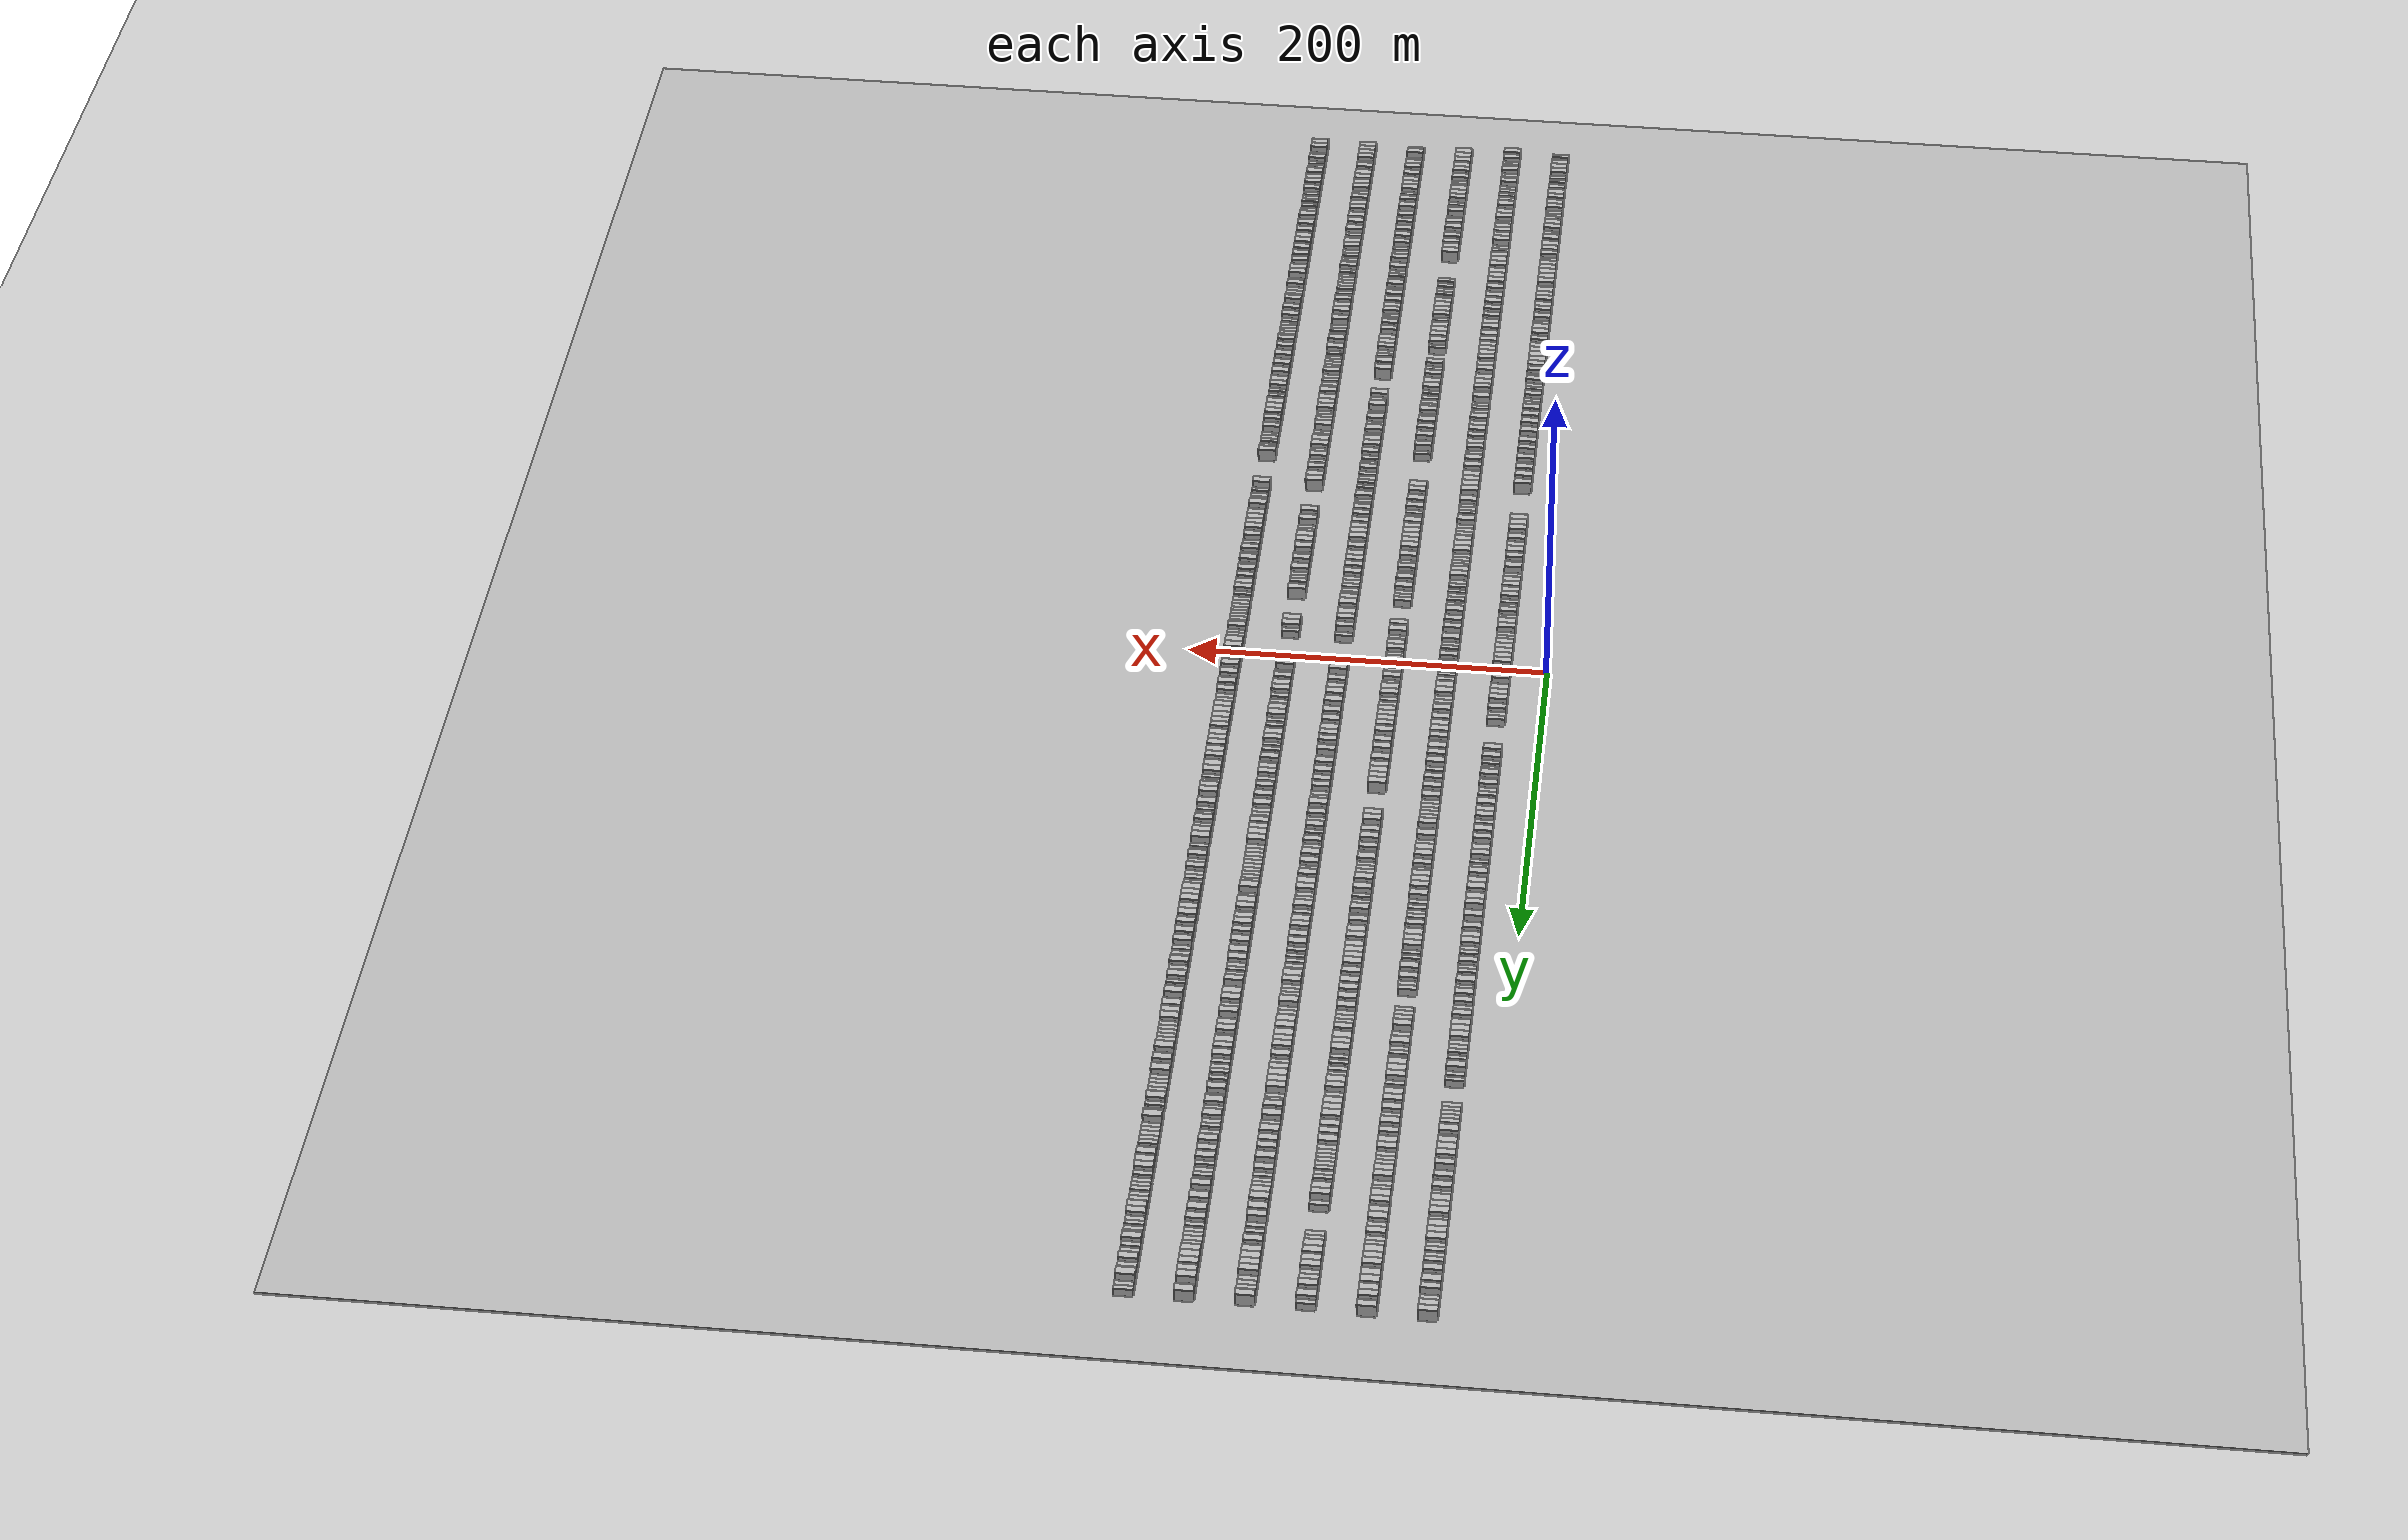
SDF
<sdf version="1.6">
 <world name="default">
  <scene>
   <sky><clouds><speed>12</speed></clouds></sky>
   <ambient>0.4 0.4 0.4 1</ambient>
   <background>0.7 0.7 0.7 1</background>
   <shadows>1</shadows>
  </scene>
  <gravity>0 0 -9.8066</gravity>
  <magnetic_field>6e-06 2.3e-05 -4.2e-05</magnetic_field>
  <physics default="0" name="default_physics" type="ode">
   <ode>
    <solver>
     <type>quick</type>
     <iters>10</iters>
     <sor>1.0</sor>
     <use_dynamic_moi_rescaling>0</use_dynamic_moi_rescaling>
    </solver>
    <constraints>
     <cfm>0</cfm>
     <erp>0.2</erp>
     <contact_max_correcting_vel>100</contact_max_correcting_vel>
     <contact_surface_layer>0.001</contact_surface_layer>
    </constraints>
   </ode>
   <max_step_size>0.004</max_step_size>
   <real_time_factor>1</real_time_factor>
   <real_time_update_rate>250</real_time_update_rate>
  </physics>
  <light name="sun" type="directional">
   <pose>0 0 10 0 0 0</pose>
   <diffuse>0.8 0.8 0.8 1</diffuse>
   <specular>0.2 0.2 0.2 1</specular>
   <attenuation>
    <range>1000</range>
    <constant>0.9</constant>
    <linear>0.01</linear>
    <quadratic>0.001</quadratic>
   </attenuation>
   <direction>-0.5 0.1 -0.9</direction>
  </light>
  <include><name>ground_plane_1</name><uri>model://HANNAS_ground_plane</uri></include>
  <include>
   <name>ground_plane_2</name>
   <uri>model://HANNAS_ground_plane</uri>
   <pose>100 0 0  0 0 0</pose>
  </include>
  <model name="building_1">
   <static>1</static>
   <pose>25.0000 -458.7029 0 0.000000 0.000000 0.000000</pose>
   <link name="link">
    <pose>0 0 3.00 0 0 0</pose>
    <collision name="collision"><geometry><box><size>10.0000 2.5942 6.0000</size></box></geometry></collision>
    <visual name="visual">
     <cast_shadows>0</cast_shadows>
     <geometry><box><size>10.0000 2.5942 6.0000</size></box></geometry>
     <material>
      <script>
       <uri>model://HANNAS_wall/materials/scripts</uri>
       <uri>model://HANNAS_wall/materials/textures</uri>
       <name>vrc/HANNAS_wall</name>
      </script>
     </material>
    </visual>
   </link>
  </model>
  <model name="building_2">
   <static>1</static>
   <pose>25.0000 -454.1973 0 0.000000 0.000000 0.000000</pose>
   <link name="link">
    <pose>0 0 3.00 0 0 0</pose>
    <collision name="collision"><geometry><box><size>10.0000 2.4171 6.0000</size></box></geometry></collision>
    <visual name="visual">
     <cast_shadows>0</cast_shadows>
     <geometry><box><size>10.0000 2.4171 6.0000</size></box></geometry>
     <material>
      <script>
       <uri>model://HANNAS_wall/materials/scripts</uri>
       <uri>model://HANNAS_wall/materials/textures</uri>
       <name>vrc/HANNAS_wall</name>
      </script>
     </material>
    </visual>
   </link>
  </model>
  <model name="building_3">
   <static>1</static>
   <pose>25.0000 -449.1507 0 0.000000 0.000000 0.000000</pose>
   <link name="link">
    <pose>0 0 4.50 0 0 0</pose>
    <collision name="collision"><geometry><box><size>10.0000 3.6760 9.0000</size></box></geometry></collision>
    <visual name="visual">
     <cast_shadows>0</cast_shadows>
     <geometry><box><size>10.0000 3.6760 9.0000</size></box></geometry>
     <material>
      <script>
       <uri>model://HANNAS_wall/materials/scripts</uri>
       <uri>model://HANNAS_wall/materials/textures</uri>
       <name>vrc/HANNAS_wall</name>
      </script>
     </material>
    </visual>
   </link>
  </model>
  <model name="building_4">
   <static>1</static>
   <pose>25.0000 -445.1923 0 0.000000 0.000000 0.000000</pose>
   <link name="link">
    <pose>0 0 4.50 0 0 0</pose>
    <collision name="collision"><geometry><box><size>10.0000 4.2408 9.0000</size></box></geometry></collision>
    <visual name="visual">
     <cast_shadows>0</cast_shadows>
     <geometry><box><size>10.0000 4.2408 9.0000</size></box></geometry>
     <material>
      <script>
       <uri>model://HANNAS_wall/materials/scripts</uri>
       <uri>model://HANNAS_wall/materials/textures</uri>
       <name>vrc/HANNAS_wall</name>
      </script>
     </material>
    </visual>
   </link>
  </model>
  <model name="building_5">
   <static>1</static>
   <pose>25.0000 -440.9153 0 0.000000 0.000000 0.000000</pose>
   <link name="link">
    <pose>0 0 4.50 0 0 0</pose>
    <collision name="collision"><geometry><box><size>10.0000 4.3131 9.0000</size></box></geometry></collision>
    <visual name="visual">
     <cast_shadows>0</cast_shadows>
     <geometry><box><size>10.0000 4.3131 9.0000</size></box></geometry>
     <material>
      <script>
       <uri>model://HANNAS_wall/materials/scripts</uri>
       <uri>model://HANNAS_wall/materials/textures</uri>
       <name>vrc/HANNAS_wall</name>
      </script>
     </material>
    </visual>
   </link>
  </model>
  <model name="building_6">
   <static>1</static>
   <pose>25.0000 -437.2627 0 0.000000 0.000000 0.000000</pose>
   <link name="link">
    <pose>0 0 3.00 0 0 0</pose>
    <collision name="collision"><geometry><box><size>10.0000 2.9920 6.0000</size></box></geometry></collision>
    <visual name="visual">
     <cast_shadows>0</cast_shadows>
     <geometry><box><size>10.0000 2.9920 6.0000</size></box></geometry>
     <material>
      <script>
       <uri>model://HANNAS_wall/materials/scripts</uri>
       <uri>model://HANNAS_wall/materials/textures</uri>
       <name>vrc/HANNAS_wall</name>
      </script>
     </material>
    </visual>
   </link>
  </model>
  <model name="building_7">
   <static>1</static>
   <pose>25.0000 -433.5460 0 0.000000 0.000000 0.000000</pose>
   <link name="link">
    <pose>0 0 3.00 0 0 0</pose>
    <collision name="collision"><geometry><box><size>10.0000 2.4415 6.0000</size></box></geometry></collision>
    <visual name="visual">
     <cast_shadows>0</cast_shadows>
     <geometry><box><size>10.0000 2.4415 6.0000</size></box></geometry>
     <material>
      <script>
       <uri>model://HANNAS_wall/materials/scripts</uri>
       <uri>model://HANNAS_wall/materials/textures</uri>
       <name>vrc/HANNAS_wall</name>
      </script>
     </material>
    </visual>
   </link>
  </model>
  <model name="building_8">
   <static>1</static>
   <pose>25.0000 -428.9209 0 0.000000 0.000000 0.000000</pose>
   <link name="link">
    <pose>0 0 3.00 0 0 0</pose>
    <collision name="collision"><geometry><box><size>10.0000 2.8086 6.0000</size></box></geometry></collision>
    <visual name="visual">
     <cast_shadows>0</cast_shadows>
     <geometry><box><size>10.0000 2.8086 6.0000</size></box></geometry>
     <material>
      <script>
       <uri>model://HANNAS_wall/materials/scripts</uri>
       <uri>model://HANNAS_wall/materials/textures</uri>
       <name>vrc/HANNAS_wall</name>
      </script>
     </material>
    </visual>
   </link>
  </model>
  <model name="building_9">
   <static>1</static>
   <pose>25.0000 -424.6801 0 0.000000 0.000000 0.000000</pose>
   <link name="link">
    <pose>0 0 4.50 0 0 0</pose>
    <collision name="collision"><geometry><box><size>10.0000 3.6730 9.0000</size></box></geometry></collision>
    <visual name="visual">
     <cast_shadows>0</cast_shadows>
     <geometry><box><size>10.0000 3.6730 9.0000</size></box></geometry>
     <material>
      <script>
       <uri>model://HANNAS_wall/materials/scripts</uri>
       <uri>model://HANNAS_wall/materials/textures</uri>
       <name>vrc/HANNAS_wall</name>
      </script>
     </material>
    </visual>
   </link>
  </model>
  <model name="building_10">
   <static>1</static>
   <pose>25.0000 -419.6212 0 0.000000 0.000000 0.000000</pose>
   <link name="link">
    <pose>0 0 4.50 0 0 0</pose>
    <collision name="collision"><geometry><box><size>10.0000 4.4449 9.0000</size></box></geometry></collision>
    <visual name="visual">
     <cast_shadows>0</cast_shadows>
     <geometry><box><size>10.0000 4.4449 9.0000</size></box></geometry>
     <material>
      <script>
       <uri>model://HANNAS_wall/materials/scripts</uri>
       <uri>model://HANNAS_wall/materials/textures</uri>
       <name>vrc/HANNAS_wall</name>
      </script>
     </material>
    </visual>
   </link>
  </model>
  <model name="building_11">
   <static>1</static>
   <pose>25.0000 -415.4923 0 0.000000 0.000000 0.000000</pose>
   <link name="link">
    <pose>0 0 4.50 0 0 0</pose>
    <collision name="collision"><geometry><box><size>10.0000 3.8129 9.0000</size></box></geometry></collision>
    <visual name="visual">
     <cast_shadows>0</cast_shadows>
     <geometry><box><size>10.0000 3.8129 9.0000</size></box></geometry>
     <material>
      <script>
       <uri>model://HANNAS_wall/materials/scripts</uri>
       <uri>model://HANNAS_wall/materials/textures</uri>
       <name>vrc/HANNAS_wall</name>
      </script>
     </material>
    </visual>
   </link>
  </model>
  <model name="building_12">
   <static>1</static>
   <pose>25.0000 -409.6443 0 0.000000 0.000000 0.000000</pose>
   <link name="link">
    <pose>0 0 4.50 0 0 0</pose>
    <collision name="collision"><geometry><box><size>10.0000 3.8831 9.0000</size></box></geometry></collision>
    <visual name="visual">
     <cast_shadows>0</cast_shadows>
     <geometry><box><size>10.0000 3.8831 9.0000</size></box></geometry>
     <material>
      <script>
       <uri>model://HANNAS_wall/materials/scripts</uri>
       <uri>model://HANNAS_wall/materials/textures</uri>
       <name>vrc/HANNAS_wall</name>
      </script>
     </material>
    </visual>
   </link>
  </model>
  <model name="building_13">
   <static>1</static>
   <pose>25.0000 -405.8026 0 0.000000 0.000000 0.000000</pose>
   <link name="link">
    <pose>0 0 4.50 0 0 0</pose>
    <collision name="collision"><geometry><box><size>10.0000 3.8004 9.0000</size></box></geometry></collision>
    <visual name="visual">
     <cast_shadows>0</cast_shadows>
     <geometry><box><size>10.0000 3.8004 9.0000</size></box></geometry>
     <material>
      <script>
       <uri>model://HANNAS_wall/materials/scripts</uri>
       <uri>model://HANNAS_wall/materials/textures</uri>
       <name>vrc/HANNAS_wall</name>
      </script>
     </material>
    </visual>
   </link>
  </model>
  <model name="building_14">
   <static>1</static>
   <pose>25.0000 -402.5235 0 0.000000 0.000000 0.000000</pose>
   <link name="link">
    <pose>0 0 3.00 0 0 0</pose>
    <collision name="collision"><geometry><box><size>10.0000 2.7578 6.0000</size></box></geometry></collision>
    <visual name="visual">
     <cast_shadows>0</cast_shadows>
     <geometry><box><size>10.0000 2.7578 6.0000</size></box></geometry>
     <material>
      <script>
       <uri>model://HANNAS_wall/materials/scripts</uri>
       <uri>model://HANNAS_wall/materials/textures</uri>
       <name>vrc/HANNAS_wall</name>
      </script>
     </material>
    </visual>
   </link>
  </model>
  <model name="building_15">
   <static>1</static>
   <pose>25.0000 -399.8916 0 0.000000 0.000000 0.000000</pose>
   <link name="link">
    <pose>0 0 3.00 0 0 0</pose>
    <collision name="collision"><geometry><box><size>10.0000 2.5060 6.0000</size></box></geometry></collision>
    <visual name="visual">
     <cast_shadows>0</cast_shadows>
     <geometry><box><size>10.0000 2.5060 6.0000</size></box></geometry>
     <material>
      <script>
       <uri>model://HANNAS_wall/materials/scripts</uri>
       <uri>model://HANNAS_wall/materials/textures</uri>
       <name>vrc/HANNAS_wall</name>
      </script>
     </material>
    </visual>
   </link>
  </model>
  <model name="building_16">
   <static>1</static>
   <pose>25.0000 -397.3021 0 0.000000 0.000000 0.000000</pose>
   <link name="link">
    <pose>0 0 3.00 0 0 0</pose>
    <collision name="collision"><geometry><box><size>10.0000 2.6730 6.0000</size></box></geometry></collision>
    <visual name="visual">
     <cast_shadows>0</cast_shadows>
     <geometry><box><size>10.0000 2.6730 6.0000</size></box></geometry>
     <material>
      <script>
       <uri>model://HANNAS_wall/materials/scripts</uri>
       <uri>model://HANNAS_wall/materials/textures</uri>
       <name>vrc/HANNAS_wall</name>
      </script>
     </material>
    </visual>
   </link>
  </model>
  <model name="building_17">
   <static>1</static>
   <pose>25.0000 -393.5433 0 0.000000 0.000000 0.000000</pose>
   <link name="link">
    <pose>0 0 3.00 0 0 0</pose>
    <collision name="collision"><geometry><box><size>10.0000 2.8446 6.0000</size></box></geometry></collision>
    <visual name="visual">
     <cast_shadows>0</cast_shadows>
     <geometry><box><size>10.0000 2.8446 6.0000</size></box></geometry>
     <material>
      <script>
       <uri>model://HANNAS_wall/materials/scripts</uri>
       <uri>model://HANNAS_wall/materials/textures</uri>
       <name>vrc/HANNAS_wall</name>
      </script>
     </material>
    </visual>
   </link>
  </model>
  <model name="building_18">
   <static>1</static>
   <pose>25.0000 -390.0442 0 0.000000 0.000000 0.000000</pose>
   <link name="link">
    <pose>0 0 4.50 0 0 0</pose>
    <collision name="collision"><geometry><box><size>10.0000 4.1536 9.0000</size></box></geometry></collision>
    <visual name="visual">
     <cast_shadows>0</cast_shadows>
     <geometry><box><size>10.0000 4.1536 9.0000</size></box></geometry>
     <material>
      <script>
       <uri>model://HANNAS_wall/materials/scripts</uri>
       <uri>model://HANNAS_wall/materials/textures</uri>
       <name>vrc/HANNAS_wall</name>
      </script>
     </material>
    </visual>
   </link>
  </model>
  <model name="building_19">
   <static>1</static>
   <pose>25.0000 -385.8917 0 0.000000 0.000000 0.000000</pose>
   <link name="link">
    <pose>0 0 4.50 0 0 0</pose>
    <collision name="collision"><geometry><box><size>10.0000 4.1514 9.0000</size></box></geometry></collision>
    <visual name="visual">
     <cast_shadows>0</cast_shadows>
     <geometry><box><size>10.0000 4.1514 9.0000</size></box></geometry>
     <material>
      <script>
       <uri>model://HANNAS_wall/materials/scripts</uri>
       <uri>model://HANNAS_wall/materials/textures</uri>
       <name>vrc/HANNAS_wall</name>
      </script>
     </material>
    </visual>
   </link>
  </model>
  <model name="building_20">
   <static>1</static>
   <pose>25.0000 -382.5422 0 0.000000 0.000000 0.000000</pose>
   <link name="link">
    <pose>0 0 3.00 0 0 0</pose>
    <collision name="collision"><geometry><box><size>10.0000 2.5477 6.0000</size></box></geometry></collision>
    <visual name="visual">
     <cast_shadows>0</cast_shadows>
     <geometry><box><size>10.0000 2.5477 6.0000</size></box></geometry>
     <material>
      <script>
       <uri>model://HANNAS_wall/materials/scripts</uri>
       <uri>model://HANNAS_wall/materials/textures</uri>
       <name>vrc/HANNAS_wall</name>
      </script>
     </material>
    </visual>
   </link>
  </model>
  <model name="building_21">
   <static>1</static>
   <pose>25.0000 -379.8724 0 0.000000 0.000000 0.000000</pose>
   <link name="link">
    <pose>0 0 3.00 0 0 0</pose>
    <collision name="collision"><geometry><box><size>10.0000 2.7919 6.0000</size></box></geometry></collision>
    <visual name="visual">
     <cast_shadows>0</cast_shadows>
     <geometry><box><size>10.0000 2.7919 6.0000</size></box></geometry>
     <material>
      <script>
       <uri>model://HANNAS_wall/materials/scripts</uri>
       <uri>model://HANNAS_wall/materials/textures</uri>
       <name>vrc/HANNAS_wall</name>
      </script>
     </material>
    </visual>
   </link>
  </model>
  <model name="building_22">
   <static>1</static>
   <pose>25.0000 -375.3553 0 0.000000 0.000000 0.000000</pose>
   <link name="link">
    <pose>0 0 4.50 0 0 0</pose>
    <collision name="collision"><geometry><box><size>10.0000 4.2422 9.0000</size></box></geometry></collision>
    <visual name="visual">
     <cast_shadows>0</cast_shadows>
     <geometry><box><size>10.0000 4.2422 9.0000</size></box></geometry>
     <material>
      <script>
       <uri>model://HANNAS_wall/materials/scripts</uri>
       <uri>model://HANNAS_wall/materials/textures</uri>
       <name>vrc/HANNAS_wall</name>
      </script>
     </material>
    </visual>
   </link>
  </model>
  <model name="building_23">
   <static>1</static>
   <pose>25.0000 -369.0118 0 0.000000 0.000000 0.000000</pose>
   <link name="link">
    <pose>0 0 4.50 0 0 0</pose>
    <collision name="collision"><geometry><box><size>10.0000 4.4448 9.0000</size></box></geometry></collision>
    <visual name="visual">
     <cast_shadows>0</cast_shadows>
     <geometry><box><size>10.0000 4.4448 9.0000</size></box></geometry>
     <material>
      <script>
       <uri>model://HANNAS_wall/materials/scripts</uri>
       <uri>model://HANNAS_wall/materials/textures</uri>
       <name>vrc/HANNAS_wall</name>
      </script>
     </material>
    </visual>
   </link>
  </model>
  <model name="building_24">
   <static>1</static>
   <pose>25.0000 -364.7935 0 0.000000 0.000000 0.000000</pose>
   <link name="link">
    <pose>0 0 4.50 0 0 0</pose>
    <collision name="collision"><geometry><box><size>10.0000 3.9919 9.0000</size></box></geometry></collision>
    <visual name="visual">
     <cast_shadows>0</cast_shadows>
     <geometry><box><size>10.0000 3.9919 9.0000</size></box></geometry>
     <material>
      <script>
       <uri>model://HANNAS_wall/materials/scripts</uri>
       <uri>model://HANNAS_wall/materials/textures</uri>
       <name>vrc/HANNAS_wall</name>
      </script>
     </material>
    </visual>
   </link>
  </model>
  <model name="building_25">
   <static>1</static>
   <pose>25.0000 -359.9944 0 0.000000 0.000000 0.000000</pose>
   <link name="link">
    <pose>0 0 4.50 0 0 0</pose>
    <collision name="collision"><geometry><box><size>10.0000 3.6062 9.0000</size></box></geometry></collision>
    <visual name="visual">
     <cast_shadows>0</cast_shadows>
     <geometry><box><size>10.0000 3.6062 9.0000</size></box></geometry>
     <material>
      <script>
       <uri>model://HANNAS_wall/materials/scripts</uri>
       <uri>model://HANNAS_wall/materials/textures</uri>
       <name>vrc/HANNAS_wall</name>
      </script>
     </material>
    </visual>
   </link>
  </model>
  <model name="building_26">
   <static>1</static>
   <pose>25.0000 -356.8603 0 0.000000 0.000000 0.000000</pose>
   <link name="link">
    <pose>0 0 3.00 0 0 0</pose>
    <collision name="collision"><geometry><box><size>10.0000 2.6620 6.0000</size></box></geometry></collision>
    <visual name="visual">
     <cast_shadows>0</cast_shadows>
     <geometry><box><size>10.0000 2.6620 6.0000</size></box></geometry>
     <material>
      <script>
       <uri>model://HANNAS_wall/materials/scripts</uri>
       <uri>model://HANNAS_wall/materials/textures</uri>
       <name>vrc/HANNAS_wall</name>
      </script>
     </material>
    </visual>
   </link>
  </model>
  <model name="building_27">
   <static>1</static>
   <pose>25.0000 -353.3036 0 0.000000 0.000000 0.000000</pose>
   <link name="link">
    <pose>0 0 3.00 0 0 0</pose>
    <collision name="collision"><geometry><box><size>10.0000 2.4513 6.0000</size></box></geometry></collision>
    <visual name="visual">
     <cast_shadows>0</cast_shadows>
     <geometry><box><size>10.0000 2.4513 6.0000</size></box></geometry>
     <material>
      <script>
       <uri>model://HANNAS_wall/materials/scripts</uri>
       <uri>model://HANNAS_wall/materials/textures</uri>
       <name>vrc/HANNAS_wall</name>
      </script>
     </material>
    </visual>
   </link>
  </model>
  <model name="building_28">
   <static>1</static>
   <pose>25.0000 -350.2031 0 0.000000 0.000000 0.000000</pose>
   <link name="link">
    <pose>0 0 4.50 0 0 0</pose>
    <collision name="collision"><geometry><box><size>10.0000 3.7497 9.0000</size></box></geometry></collision>
    <visual name="visual">
     <cast_shadows>0</cast_shadows>
     <geometry><box><size>10.0000 3.7497 9.0000</size></box></geometry>
     <material>
      <script>
       <uri>model://HANNAS_wall/materials/scripts</uri>
       <uri>model://HANNAS_wall/materials/textures</uri>
       <name>vrc/HANNAS_wall</name>
      </script>
     </material>
    </visual>
   </link>
  </model>
  <model name="building_29">
   <static>1</static>
   <pose>25.0000 -346.3788 0 0.000000 0.000000 0.000000</pose>
   <link name="link">
    <pose>0 0 4.50 0 0 0</pose>
    <collision name="collision"><geometry><box><size>10.0000 3.8989 9.0000</size></box></geometry></collision>
    <visual name="visual">
     <cast_shadows>0</cast_shadows>
     <geometry><box><size>10.0000 3.8989 9.0000</size></box></geometry>
     <material>
      <script>
       <uri>model://HANNAS_wall/materials/scripts</uri>
       <uri>model://HANNAS_wall/materials/textures</uri>
       <name>vrc/HANNAS_wall</name>
      </script>
     </material>
    </visual>
   </link>
  </model>
  <model name="building_30">
   <static>1</static>
   <pose>25.0000 -342.2293 0 0.000000 0.000000 0.000000</pose>
   <link name="link">
    <pose>0 0 4.50 0 0 0</pose>
    <collision name="collision"><geometry><box><size>10.0000 4.4001 9.0000</size></box></geometry></collision>
    <visual name="visual">
     <cast_shadows>0</cast_shadows>
     <geometry><box><size>10.0000 4.4001 9.0000</size></box></geometry>
     <material>
      <script>
       <uri>model://HANNAS_wall/materials/scripts</uri>
       <uri>model://HANNAS_wall/materials/textures</uri>
       <name>vrc/HANNAS_wall</name>
      </script>
     </material>
    </visual>
   </link>
  </model>
  <model name="building_31">
   <static>1</static>
   <pose>25.0000 -337.7817 0 0.000000 0.000000 0.000000</pose>
   <link name="link">
    <pose>0 0 4.50 0 0 0</pose>
    <collision name="collision"><geometry><box><size>10.0000 4.4951 9.0000</size></box></geometry></collision>
    <visual name="visual">
     <cast_shadows>0</cast_shadows>
     <geometry><box><size>10.0000 4.4951 9.0000</size></box></geometry>
     <material>
      <script>
       <uri>model://HANNAS_wall/materials/scripts</uri>
       <uri>model://HANNAS_wall/materials/textures</uri>
       <name>vrc/HANNAS_wall</name>
      </script>
     </material>
    </visual>
   </link>
  </model>
  <model name="building_32">
   <static>1</static>
   <pose>25.0000 -333.3863 0 0.000000 0.000000 0.000000</pose>
   <link name="link">
    <pose>0 0 4.50 0 0 0</pose>
    <collision name="collision"><geometry><box><size>10.0000 4.2958 9.0000</size></box></geometry></collision>
    <visual name="visual">
     <cast_shadows>0</cast_shadows>
     <geometry><box><size>10.0000 4.2958 9.0000</size></box></geometry>
     <material>
      <script>
       <uri>model://HANNAS_wall/materials/scripts</uri>
       <uri>model://HANNAS_wall/materials/textures</uri>
       <name>vrc/HANNAS_wall</name>
      </script>
     </material>
    </visual>
   </link>
  </model>
  <model name="building_33">
   <static>1</static>
   <pose>25.0000 -330.0188 0 0.000000 0.000000 0.000000</pose>
   <link name="link">
    <pose>0 0 3.00 0 0 0</pose>
    <collision name="collision"><geometry><box><size>10.0000 2.4390 6.0000</size></box></geometry></collision>
    <visual name="visual">
     <cast_shadows>0</cast_shadows>
     <geometry><box><size>10.0000 2.4390 6.0000</size></box></geometry>
     <material>
      <script>
       <uri>model://HANNAS_wall/materials/scripts</uri>
       <uri>model://HANNAS_wall/materials/textures</uri>
       <name>vrc/HANNAS_wall</name>
      </script>
     </material>
    </visual>
   </link>
  </model>
  <model name="building_34">
   <static>1</static>
   <pose>25.0000 -324.6767 0 0.000000 0.000000 0.000000</pose>
   <link name="link">
    <pose>0 0 4.50 0 0 0</pose>
    <collision name="collision"><geometry><box><size>10.0000 4.2452 9.0000</size></box></geometry></collision>
    <visual name="visual">
     <cast_shadows>0</cast_shadows>
     <geometry><box><size>10.0000 4.2452 9.0000</size></box></geometry>
     <material>
      <script>
       <uri>model://HANNAS_wall/materials/scripts</uri>
       <uri>model://HANNAS_wall/materials/textures</uri>
       <name>vrc/HANNAS_wall</name>
      </script>
     </material>
    </visual>
   </link>
  </model>
  <model name="building_35">
   <static>1</static>
   <pose>25.0000 -320.6942 0 0.000000 0.000000 0.000000</pose>
   <link name="link">
    <pose>0 0 4.50 0 0 0</pose>
    <collision name="collision"><geometry><box><size>10.0000 3.7198 9.0000</size></box></geometry></collision>
    <visual name="visual">
     <cast_shadows>0</cast_shadows>
     <geometry><box><size>10.0000 3.7198 9.0000</size></box></geometry>
     <material>
      <script>
       <uri>model://HANNAS_wall/materials/scripts</uri>
       <uri>model://HANNAS_wall/materials/textures</uri>
       <name>vrc/HANNAS_wall</name>
      </script>
     </material>
    </visual>
   </link>
  </model>
  <model name="building_36">
   <static>1</static>
   <pose>25.0000 -316.8547 0 0.000000 0.000000 0.000000</pose>
   <link name="link">
    <pose>0 0 4.50 0 0 0</pose>
    <collision name="collision"><geometry><box><size>10.0000 3.9591 9.0000</size></box></geometry></collision>
    <visual name="visual">
     <cast_shadows>0</cast_shadows>
     <geometry><box><size>10.0000 3.9591 9.0000</size></box></geometry>
     <material>
      <script>
       <uri>model://HANNAS_wall/materials/scripts</uri>
       <uri>model://HANNAS_wall/materials/textures</uri>
       <name>vrc/HANNAS_wall</name>
      </script>
     </material>
    </visual>
   </link>
  </model>
  <model name="building_37">
   <static>1</static>
   <pose>25.0000 -310.8649 0 0.000000 0.000000 0.000000</pose>
   <link name="link">
    <pose>0 0 4.50 0 0 0</pose>
    <collision name="collision"><geometry><box><size>10.0000 4.0205 9.0000</size></box></geometry></collision>
    <visual name="visual">
     <cast_shadows>0</cast_shadows>
     <geometry><box><size>10.0000 4.0205 9.0000</size></box></geometry>
     <material>
      <script>
       <uri>model://HANNAS_wall/materials/scripts</uri>
       <uri>model://HANNAS_wall/materials/textures</uri>
       <name>vrc/HANNAS_wall</name>
      </script>
     </material>
    </visual>
   </link>
  </model>
  <model name="building_38">
   <static>1</static>
   <pose>25.0000 -307.0264 0 0.000000 0.000000 0.000000</pose>
   <link name="link">
    <pose>0 0 4.50 0 0 0</pose>
    <collision name="collision"><geometry><box><size>10.0000 3.6566 9.0000</size></box></geometry></collision>
    <visual name="visual">
     <cast_shadows>0</cast_shadows>
     <geometry><box><size>10.0000 3.6566 9.0000</size></box></geometry>
     <material>
      <script>
       <uri>model://HANNAS_wall/materials/scripts</uri>
       <uri>model://HANNAS_wall/materials/textures</uri>
       <name>vrc/HANNAS_wall</name>
      </script>
     </material>
    </visual>
   </link>
  </model>
  <model name="building_39">
   <static>1</static>
   <pose>25.0000 -303.7442 0 0.000000 0.000000 0.000000</pose>
   <link name="link">
    <pose>0 0 3.00 0 0 0</pose>
    <collision name="collision"><geometry><box><size>10.0000 2.9078 6.0000</size></box></geometry></collision>
    <visual name="visual">
     <cast_shadows>0</cast_shadows>
     <geometry><box><size>10.0000 2.9078 6.0000</size></box></geometry>
     <material>
      <script>
       <uri>model://HANNAS_wall/materials/scripts</uri>
       <uri>model://HANNAS_wall/materials/textures</uri>
       <name>vrc/HANNAS_wall</name>
      </script>
     </material>
    </visual>
   </link>
  </model>
  <model name="building_40">
   <static>1</static>
   <pose>25.0000 -300.1988 0 0.000000 0.000000 0.000000</pose>
   <link name="link">
    <pose>0 0 4.50 0 0 0</pose>
    <collision name="collision"><geometry><box><size>10.0000 4.1829 9.0000</size></box></geometry></collision>
    <visual name="visual">
     <cast_shadows>0</cast_shadows>
     <geometry><box><size>10.0000 4.1829 9.0000</size></box></geometry>
     <material>
      <script>
       <uri>model://HANNAS_wall/materials/scripts</uri>
       <uri>model://HANNAS_wall/materials/textures</uri>
       <name>vrc/HANNAS_wall</name>
      </script>
     </material>
    </visual>
   </link>
  </model>
  <model name="building_41">
   <static>1</static>
   <pose>25.0000 -296.9046 0 0.000000 0.000000 0.000000</pose>
   <link name="link">
    <pose>0 0 3.00 0 0 0</pose>
    <collision name="collision"><geometry><box><size>10.0000 2.4056 6.0000</size></box></geometry></collision>
    <visual name="visual">
     <cast_shadows>0</cast_shadows>
     <geometry><box><size>10.0000 2.4056 6.0000</size></box></geometry>
     <material>
      <script>
       <uri>model://HANNAS_wall/materials/scripts</uri>
       <uri>model://HANNAS_wall/materials/textures</uri>
       <name>vrc/HANNAS_wall</name>
      </script>
     </material>
    </visual>
   </link>
  </model>
  <model name="building_42">
   <static>1</static>
   <pose>25.0000 -293.4693 0 0.000000 0.000000 0.000000</pose>
   <link name="link">
    <pose>0 0 3.00 0 0 0</pose>
    <collision name="collision"><geometry><box><size>10.0000 2.4650 6.0000</size></box></geometry></collision>
    <visual name="visual">
     <cast_shadows>0</cast_shadows>
     <geometry><box><size>10.0000 2.4650 6.0000</size></box></geometry>
     <material>
      <script>
       <uri>model://HANNAS_wall/materials/scripts</uri>
       <uri>model://HANNAS_wall/materials/textures</uri>
       <name>vrc/HANNAS_wall</name>
      </script>
     </material>
    </visual>
   </link>
  </model>
  <model name="building_43">
   <static>1</static>
   <pose>25.0000 -289.9926 0 0.000000 0.000000 0.000000</pose>
   <link name="link">
    <pose>0 0 4.50 0 0 0</pose>
    <collision name="collision"><geometry><box><size>10.0000 4.4885 9.0000</size></box></geometry></collision>
    <visual name="visual">
     <cast_shadows>0</cast_shadows>
     <geometry><box><size>10.0000 4.4885 9.0000</size></box></geometry>
     <material>
      <script>
       <uri>model://HANNAS_wall/materials/scripts</uri>
       <uri>model://HANNAS_wall/materials/textures</uri>
       <name>vrc/HANNAS_wall</name>
      </script>
     </material>
    </visual>
   </link>
  </model>
  <model name="building_44">
   <static>1</static>
   <pose>25.0000 -285.6134 0 0.000000 0.000000 0.000000</pose>
   <link name="link">
    <pose>0 0 4.50 0 0 0</pose>
    <collision name="collision"><geometry><box><size>10.0000 4.2698 9.0000</size></box></geometry></collision>
    <visual name="visual">
     <cast_shadows>0</cast_shadows>
     <geometry><box><size>10.0000 4.2698 9.0000</size></box></geometry>
     <material>
      <script>
       <uri>model://HANNAS_wall/materials/scripts</uri>
       <uri>model://HANNAS_wall/materials/textures</uri>
       <name>vrc/HANNAS_wall</name>
      </script>
     </material>
    </visual>
   </link>
  </model>
  <model name="building_45">
   <static>1</static>
   <pose>25.0000 -282.1801 0 0.000000 0.000000 0.000000</pose>
   <link name="link">
    <pose>0 0 3.00 0 0 0</pose>
    <collision name="collision"><geometry><box><size>10.0000 2.5968 6.0000</size></box></geometry></collision>
    <visual name="visual">
     <cast_shadows>0</cast_shadows>
     <geometry><box><size>10.0000 2.5968 6.0000</size></box></geometry>
     <material>
      <script>
       <uri>model://HANNAS_wall/materials/scripts</uri>
       <uri>model://HANNAS_wall/materials/textures</uri>
       <name>vrc/HANNAS_wall</name>
      </script>
     </material>
    </visual>
   </link>
  </model>
  <model name="building_46">
   <static>1</static>
   <pose>25.0000 -279.0741 0 0.000000 0.000000 0.000000</pose>
   <link name="link">
    <pose>0 0 4.50 0 0 0</pose>
    <collision name="collision"><geometry><box><size>10.0000 3.6153 9.0000</size></box></geometry></collision>
    <visual name="visual">
     <cast_shadows>0</cast_shadows>
     <geometry><box><size>10.0000 3.6153 9.0000</size></box></geometry>
     <material>
      <script>
       <uri>model://HANNAS_wall/materials/scripts</uri>
       <uri>model://HANNAS_wall/materials/textures</uri>
       <name>vrc/HANNAS_wall</name>
      </script>
     </material>
    </visual>
   </link>
  </model>
  <model name="building_47">
   <static>1</static>
   <pose>25.0000 -275.7902 0 0.000000 0.000000 0.000000</pose>
   <link name="link">
    <pose>0 0 3.00 0 0 0</pose>
    <collision name="collision"><geometry><box><size>10.0000 2.9524 6.0000</size></box></geometry></collision>
    <visual name="visual">
     <cast_shadows>0</cast_shadows>
     <geometry><box><size>10.0000 2.9524 6.0000</size></box></geometry>
     <material>
      <script>
       <uri>model://HANNAS_wall/materials/scripts</uri>
       <uri>model://HANNAS_wall/materials/textures</uri>
       <name>vrc/HANNAS_wall</name>
      </script>
     </material>
    </visual>
   </link>
  </model>
  <model name="building_48">
   <static>1</static>
   <pose>25.0000 -272.4096 0 0.000000 0.000000 0.000000</pose>
   <link name="link">
    <pose>0 0 4.50 0 0 0</pose>
    <collision name="collision"><geometry><box><size>10.0000 3.8089 9.0000</size></box></geometry></collision>
    <visual name="visual">
     <cast_shadows>0</cast_shadows>
     <geometry><box><size>10.0000 3.8089 9.0000</size></box></geometry>
     <material>
      <script>
       <uri>model://HANNAS_wall/materials/scripts</uri>
       <uri>model://HANNAS_wall/materials/textures</uri>
       <name>vrc/HANNAS_wall</name>
      </script>
     </material>
    </visual>
   </link>
  </model>
  <model name="building_49">
   <static>1</static>
   <pose>25.0000 -268.4264 0 0.000000 0.000000 0.000000</pose>
   <link name="link">
    <pose>0 0 4.50 0 0 0</pose>
    <collision name="collision"><geometry><box><size>10.0000 4.1575 9.0000</size></box></geometry></collision>
    <visual name="visual">
     <cast_shadows>0</cast_shadows>
     <geometry><box><size>10.0000 4.1575 9.0000</size></box></geometry>
     <material>
      <script>
       <uri>model://HANNAS_wall/materials/scripts</uri>
       <uri>model://HANNAS_wall/materials/textures</uri>
       <name>vrc/HANNAS_wall</name>
      </script>
     </material>
    </visual>
   </link>
  </model>
  <model name="building_50">
   <static>1</static>
   <pose>25.0000 -264.1976 0 0.000000 0.000000 0.000000</pose>
   <link name="link">
    <pose>0 0 4.50 0 0 0</pose>
    <collision name="collision"><geometry><box><size>10.0000 4.3001 9.0000</size></box></geometry></collision>
    <visual name="visual">
     <cast_shadows>0</cast_shadows>
     <geometry><box><size>10.0000 4.3001 9.0000</size></box></geometry>
     <material>
      <script>
       <uri>model://HANNAS_wall/materials/scripts</uri>
       <uri>model://HANNAS_wall/materials/textures</uri>
       <name>vrc/HANNAS_wall</name>
      </script>
     </material>
    </visual>
   </link>
  </model>
  <model name="building_51">
   <static>1</static>
   <pose>25.0000 -259.9924 0 0.000000 0.000000 0.000000</pose>
   <link name="link">
    <pose>0 0 4.50 0 0 0</pose>
    <collision name="collision"><geometry><box><size>10.0000 4.1102 9.0000</size></box></geometry></collision>
    <visual name="visual">
     <cast_shadows>0</cast_shadows>
     <geometry><box><size>10.0000 4.1102 9.0000</size></box></geometry>
     <material>
      <script>
       <uri>model://HANNAS_wall/materials/scripts</uri>
       <uri>model://HANNAS_wall/materials/textures</uri>
       <name>vrc/HANNAS_wall</name>
      </script>
     </material>
    </visual>
   </link>
  </model>
  <model name="building_52">
   <static>1</static>
   <pose>25.0000 -255.9386 0 0.000000 0.000000 0.000000</pose>
   <link name="link">
    <pose>0 0 4.50 0 0 0</pose>
    <collision name="collision"><geometry><box><size>10.0000 3.9975 9.0000</size></box></geometry></collision>
    <visual name="visual">
     <cast_shadows>0</cast_shadows>
     <geometry><box><size>10.0000 3.9975 9.0000</size></box></geometry>
     <material>
      <script>
       <uri>model://HANNAS_wall/materials/scripts</uri>
       <uri>model://HANNAS_wall/materials/textures</uri>
       <name>vrc/HANNAS_wall</name>
      </script>
     </material>
    </visual>
   </link>
  </model>
  <model name="building_53">
   <static>1</static>
   <pose>25.0000 -251.0679 0 0.000000 0.000000 0.000000</pose>
   <link name="link">
    <pose>0 0 4.50 0 0 0</pose>
    <collision name="collision"><geometry><box><size>10.0000 3.7440 9.0000</size></box></geometry></collision>
    <visual name="visual">
     <cast_shadows>0</cast_shadows>
     <geometry><box><size>10.0000 3.7440 9.0000</size></box></geometry>
     <material>
      <script>
       <uri>model://HANNAS_wall/materials/scripts</uri>
       <uri>model://HANNAS_wall/materials/textures</uri>
       <name>vrc/HANNAS_wall</name>
      </script>
     </material>
    </visual>
   </link>
  </model>
  <model name="building_54">
   <static>1</static>
   <pose>25.0000 -247.9221 0 0.000000 0.000000 0.000000</pose>
   <link name="link">
    <pose>0 0 3.00 0 0 0</pose>
    <collision name="collision"><geometry><box><size>10.0000 2.5476 6.0000</size></box></geometry></collision>
    <visual name="visual">
     <cast_shadows>0</cast_shadows>
     <geometry><box><size>10.0000 2.5476 6.0000</size></box></geometry>
     <material>
      <script>
       <uri>model://HANNAS_wall/materials/scripts</uri>
       <uri>model://HANNAS_wall/materials/textures</uri>
       <name>vrc/HANNAS_wall</name>
      </script>
     </material>
    </visual>
   </link>
  </model>
  <model name="building_55">
   <static>1</static>
   <pose>25.0000 -245.3750 0 0.000000 0.000000 0.000000</pose>
   <link name="link">
    <pose>0 0 3.00 0 0 0</pose>
    <collision name="collision"><geometry><box><size>10.0000 2.5466 6.0000</size></box></geometry></collision>
    <visual name="visual">
     <cast_shadows>0</cast_shadows>
     <geometry><box><size>10.0000 2.5466 6.0000</size></box></geometry>
     <material>
      <script>
       <uri>model://HANNAS_wall/materials/scripts</uri>
       <uri>model://HANNAS_wall/materials/textures</uri>
       <name>vrc/HANNAS_wall</name>
      </script>
     </material>
    </visual>
   </link>
  </model>
  <model name="building_56">
   <static>1</static>
   <pose>25.0000 -242.2231 0 0.000000 0.000000 0.000000</pose>
   <link name="link">
    <pose>0 0 4.50 0 0 0</pose>
    <collision name="collision"><geometry><box><size>10.0000 3.7574 9.0000</size></box></geometry></collision>
    <visual name="visual">
     <cast_shadows>0</cast_shadows>
     <geometry><box><size>10.0000 3.7574 9.0000</size></box></geometry>
     <material>
      <script>
       <uri>model://HANNAS_wall/materials/scripts</uri>
       <uri>model://HANNAS_wall/materials/textures</uri>
       <name>vrc/HANNAS_wall</name>
      </script>
     </material>
    </visual>
   </link>
  </model>
  <model name="building_57">
   <static>1</static>
   <pose>25.0000 -238.9059 0 0.000000 0.000000 0.000000</pose>
   <link name="link">
    <pose>0 0 3.00 0 0 0</pose>
    <collision name="collision"><geometry><box><size>10.0000 2.8770 6.0000</size></box></geometry></collision>
    <visual name="visual">
     <cast_shadows>0</cast_shadows>
     <geometry><box><size>10.0000 2.8770 6.0000</size></box></geometry>
     <material>
      <script>
       <uri>model://HANNAS_wall/materials/scripts</uri>
       <uri>model://HANNAS_wall/materials/textures</uri>
       <name>vrc/HANNAS_wall</name>
      </script>
     </material>
    </visual>
   </link>
  </model>
  <model name="building_58">
   <static>1</static>
   <pose>25.0000 -236.2493 0 0.000000 0.000000 0.000000</pose>
   <link name="link">
    <pose>0 0 3.00 0 0 0</pose>
    <collision name="collision"><geometry><box><size>10.0000 2.4362 6.0000</size></box></geometry></collision>
    <visual name="visual">
     <cast_shadows>0</cast_shadows>
     <geometry><box><size>10.0000 2.4362 6.0000</size></box></geometry>
     <material>
      <script>
       <uri>model://HANNAS_wall/materials/scripts</uri>
       <uri>model://HANNAS_wall/materials/textures</uri>
       <name>vrc/HANNAS_wall</name>
      </script>
     </material>
    </visual>
   </link>
  </model>
  <model name="building_59">
   <static>1</static>
   <pose>25.0000 -231.7002 0 0.000000 0.000000 0.000000</pose>
   <link name="link">
    <pose>0 0 3.00 0 0 0</pose>
    <collision name="collision"><geometry><box><size>10.0000 2.6620 6.0000</size></box></geometry></collision>
    <visual name="visual">
     <cast_shadows>0</cast_shadows>
     <geometry><box><size>10.0000 2.6620 6.0000</size></box></geometry>
     <material>
      <script>
       <uri>model://HANNAS_wall/materials/scripts</uri>
       <uri>model://HANNAS_wall/materials/textures</uri>
       <name>vrc/HANNAS_wall</name>
      </script>
     </material>
    </visual>
   </link>
  </model>
  <model name="building_60">
   <static>1</static>
   <pose>25.0000 -228.5097 0 0.000000 0.000000 0.000000</pose>
   <link name="link">
    <pose>0 0 4.50 0 0 0</pose>
    <collision name="collision"><geometry><box><size>10.0000 3.7189 9.0000</size></box></geometry></collision>
    <visual name="visual">
     <cast_shadows>0</cast_shadows>
     <geometry><box><size>10.0000 3.7189 9.0000</size></box></geometry>
     <material>
      <script>
       <uri>model://HANNAS_wall/materials/scripts</uri>
       <uri>model://HANNAS_wall/materials/textures</uri>
       <name>vrc/HANNAS_wall</name>
      </script>
     </material>
    </visual>
   </link>
  </model>
  <model name="building_61">
   <static>1</static>
   <pose>25.0000 -225.3300 0 0.000000 0.000000 0.000000</pose>
   <link name="link">
    <pose>0 0 3.00 0 0 0</pose>
    <collision name="collision"><geometry><box><size>10.0000 2.6406 6.0000</size></box></geometry></collision>
    <visual name="visual">
     <cast_shadows>0</cast_shadows>
     <geometry><box><size>10.0000 2.6406 6.0000</size></box></geometry>
     <material>
      <script>
       <uri>model://HANNAS_wall/materials/scripts</uri>
       <uri>model://HANNAS_wall/materials/textures</uri>
       <name>vrc/HANNAS_wall</name>
      </script>
     </material>
    </visual>
   </link>
  </model>
  <model name="building_62">
   <static>1</static>
   <pose>25.0000 -222.5262 0 0.000000 0.000000 0.000000</pose>
   <link name="link">
    <pose>0 0 3.00 0 0 0</pose>
    <collision name="collision"><geometry><box><size>10.0000 2.9670 6.0000</size></box></geometry></collision>
    <visual name="visual">
     <cast_shadows>0</cast_shadows>
     <geometry><box><size>10.0000 2.9670 6.0000</size></box></geometry>
     <material>
      <script>
       <uri>model://HANNAS_wall/materials/scripts</uri>
       <uri>model://HANNAS_wall/materials/textures</uri>
       <name>vrc/HANNAS_wall</name>
      </script>
     </material>
    </visual>
   </link>
  </model>
  <model name="building_63">
   <static>1</static>
   <pose>25.0000 -219.7093 0 0.000000 0.000000 0.000000</pose>
   <link name="link">
    <pose>0 0 3.00 0 0 0</pose>
    <collision name="collision"><geometry><box><size>10.0000 2.6669 6.0000</size></box></geometry></collision>
    <visual name="visual">
     <cast_shadows>0</cast_shadows>
     <geometry><box><size>10.0000 2.6669 6.0000</size></box></geometry>
     <material>
      <script>
       <uri>model://HANNAS_wall/materials/scripts</uri>
       <uri>model://HANNAS_wall/materials/textures</uri>
       <name>vrc/HANNAS_wall</name>
      </script>
     </material>
    </visual>
   </link>
  </model>
  <model name="building_64">
   <static>1</static>
   <pose>25.0000 -216.3573 0 0.000000 0.000000 0.000000</pose>
   <link name="link">
    <pose>0 0 4.50 0 0 0</pose>
    <collision name="collision"><geometry><box><size>10.0000 4.0371 9.0000</size></box></geometry></collision>
    <visual name="visual">
     <cast_shadows>0</cast_shadows>
     <geometry><box><size>10.0000 4.0371 9.0000</size></box></geometry>
     <material>
      <script>
       <uri>model://HANNAS_wall/materials/scripts</uri>
       <uri>model://HANNAS_wall/materials/textures</uri>
       <name>vrc/HANNAS_wall</name>
      </script>
     </material>
    </visual>
   </link>
  </model>
  <model name="building_65">
   <static>1</static>
   <pose>25.0000 -210.2549 0 0.000000 0.000000 0.000000</pose>
   <link name="link">
    <pose>0 0 4.50 0 0 0</pose>
    <collision name="collision"><geometry><box><size>10.0000 4.1677 9.0000</size></box></geometry></collision>
    <visual name="visual">
     <cast_shadows>0</cast_shadows>
     <geometry><box><size>10.0000 4.1677 9.0000</size></box></geometry>
     <material>
      <script>
       <uri>model://HANNAS_wall/materials/scripts</uri>
       <uri>model://HANNAS_wall/materials/textures</uri>
       <name>vrc/HANNAS_wall</name>
      </script>
     </material>
    </visual>
   </link>
  </model>
  <model name="building_66">
   <static>1</static>
   <pose>25.0000 -203.9430 0 0.000000 0.000000 0.000000</pose>
   <link name="link">
    <pose>0 0 4.50 0 0 0</pose>
    <collision name="collision"><geometry><box><size>10.0000 4.4560 9.0000</size></box></geometry></collision>
    <visual name="visual">
     <cast_shadows>0</cast_shadows>
     <geometry><box><size>10.0000 4.4560 9.0000</size></box></geometry>
     <material>
      <script>
       <uri>model://HANNAS_wall/materials/scripts</uri>
       <uri>model://HANNAS_wall/materials/textures</uri>
       <name>vrc/HANNAS_wall</name>
      </script>
     </material>
    </visual>
   </link>
  </model>
  <model name="building_67">
   <static>1</static>
   <pose>25.0000 -199.4689 0 0.000000 0.000000 0.000000</pose>
   <link name="link">
    <pose>0 0 3.00 0 0 0</pose>
    <collision name="collision"><geometry><box><size>10.0000 2.4922 6.0000</size></box></geometry></collision>
    <visual name="visual">
     <cast_shadows>0</cast_shadows>
     <geometry><box><size>10.0000 2.4922 6.0000</size></box></geometry>
     <material>
      <script>
       <uri>model://HANNAS_wall/materials/scripts</uri>
       <uri>model://HANNAS_wall/materials/textures</uri>
       <name>vrc/HANNAS_wall</name>
      </script>
     </material>
    </visual>
   </link>
  </model>
  <model name="building_68">
   <static>1</static>
   <pose>25.0000 -196.0397 0 0.000000 0.000000 0.000000</pose>
   <link name="link">
    <pose>0 0 4.50 0 0 0</pose>
    <collision name="collision"><geometry><box><size>10.0000 4.3663 9.0000</size></box></geometry></collision>
    <visual name="visual">
     <cast_shadows>0</cast_shadows>
     <geometry><box><size>10.0000 4.3663 9.0000</size></box></geometry>
     <material>
      <script>
       <uri>model://HANNAS_wall/materials/scripts</uri>
       <uri>model://HANNAS_wall/materials/textures</uri>
       <name>vrc/HANNAS_wall</name>
      </script>
     </material>
    </visual>
   </link>
  </model>
  <model name="building_69">
   <static>1</static>
   <pose>25.0000 -190.4998 0 0.000000 0.000000 0.000000</pose>
   <link name="link">
    <pose>0 0 3.00 0 0 0</pose>
    <collision name="collision"><geometry><box><size>10.0000 2.7136 6.0000</size></box></geometry></collision>
    <visual name="visual">
     <cast_shadows>0</cast_shadows>
     <geometry><box><size>10.0000 2.7136 6.0000</size></box></geometry>
     <material>
      <script>
       <uri>model://HANNAS_wall/materials/scripts</uri>
       <uri>model://HANNAS_wall/materials/textures</uri>
       <name>vrc/HANNAS_wall</name>
      </script>
     </material>
    </visual>
   </link>
  </model>
  <model name="building_70">
   <static>1</static>
   <pose>25.0000 -187.0167 0 0.000000 0.000000 0.000000</pose>
   <link name="link">
    <pose>0 0 4.50 0 0 0</pose>
    <collision name="collision"><geometry><box><size>10.0000 4.2525 9.0000</size></box></geometry></collision>
    <visual name="visual">
     <cast_shadows>0</cast_shadows>
     <geometry><box><size>10.0000 4.2525 9.0000</size></box></geometry>
     <material>
      <script>
       <uri>model://HANNAS_wall/materials/scripts</uri>
       <uri>model://HANNAS_wall/materials/textures</uri>
       <name>vrc/HANNAS_wall</name>
      </script>
     </material>
    </visual>
   </link>
  </model>
  <model name="building_71">
   <static>1</static>
   <pose>25.0000 -183.5527 0 0.000000 0.000000 0.000000</pose>
   <link name="link">
    <pose>0 0 3.00 0 0 0</pose>
    <collision name="collision"><geometry><box><size>10.0000 2.6756 6.0000</size></box></geometry></collision>
    <visual name="visual">
     <cast_shadows>0</cast_shadows>
     <geometry><box><size>10.0000 2.6756 6.0000</size></box></geometry>
     <material>
      <script>
       <uri>model://HANNAS_wall/materials/scripts</uri>
       <uri>model://HANNAS_wall/materials/textures</uri>
       <name>vrc/HANNAS_wall</name>
      </script>
     </material>
    </visual>
   </link>
  </model>
  <model name="building_72">
   <static>1</static>
   <pose>25.0000 -180.4028 0 0.000000 0.000000 0.000000</pose>
   <link name="link">
    <pose>0 0 4.50 0 0 0</pose>
    <collision name="collision"><geometry><box><size>10.0000 3.6242 9.0000</size></box></geometry></collision>
    <visual name="visual">
     <cast_shadows>0</cast_shadows>
     <geometry><box><size>10.0000 3.6242 9.0000</size></box></geometry>
     <material>
      <script>
       <uri>model://HANNAS_wall/materials/scripts</uri>
       <uri>model://HANNAS_wall/materials/textures</uri>
       <name>vrc/HANNAS_wall</name>
      </script>
     </material>
    </visual>
   </link>
  </model>
  <model name="building_73">
   <static>1</static>
   <pose>25.0000 -175.2914 0 0.000000 0.000000 0.000000</pose>
   <link name="link">
    <pose>0 0 3.00 0 0 0</pose>
    <collision name="collision"><geometry><box><size>10.0000 2.5985 6.0000</size></box></geometry></collision>
    <visual name="visual">
     <cast_shadows>0</cast_shadows>
     <geometry><box><size>10.0000 2.5985 6.0000</size></box></geometry>
     <material>
      <script>
       <uri>model://HANNAS_wall/materials/scripts</uri>
       <uri>model://HANNAS_wall/materials/textures</uri>
       <name>vrc/HANNAS_wall</name>
      </script>
     </material>
    </visual>
   </link>
  </model>
  <model name="building_74">
   <static>1</static>
   <pose>25.0000 -171.9958 0 0.000000 0.000000 0.000000</pose>
   <link name="link">
    <pose>0 0 4.50 0 0 0</pose>
    <collision name="collision"><geometry><box><size>10.0000 3.9927 9.0000</size></box></geometry></collision>
    <visual name="visual">
     <cast_shadows>0</cast_shadows>
     <geometry><box><size>10.0000 3.9927 9.0000</size></box></geometry>
     <material>
      <script>
       <uri>model://HANNAS_wall/materials/scripts</uri>
       <uri>model://HANNAS_wall/materials/textures</uri>
       <name>vrc/HANNAS_wall</name>
      </script>
     </material>
    </visual>
   </link>
  </model>
  <model name="building_75">
   <static>1</static>
   <pose>25.0000 -168.7039 0 0.000000 0.000000 0.000000</pose>
   <link name="link">
    <pose>0 0 3.00 0 0 0</pose>
    <collision name="collision"><geometry><box><size>10.0000 2.5911 6.0000</size></box></geometry></collision>
    <visual name="visual">
     <cast_shadows>0</cast_shadows>
     <geometry><box><size>10.0000 2.5911 6.0000</size></box></geometry>
     <material>
      <script>
       <uri>model://HANNAS_wall/materials/scripts</uri>
       <uri>model://HANNAS_wall/materials/textures</uri>
       <name>vrc/HANNAS_wall</name>
      </script>
     </material>
    </visual>
   </link>
  </model>
  <model name="building_76">
   <static>1</static>
   <pose>25.0000 -163.3264 0 0.000000 0.000000 0.000000</pose>
   <link name="link">
    <pose>0 0 4.50 0 0 0</pose>
    <collision name="collision"><geometry><box><size>10.0000 4.1639 9.0000</size></box></geometry></collision>
    <visual name="visual">
     <cast_shadows>0</cast_shadows>
     <geometry><box><size>10.0000 4.1639 9.0000</size></box></geometry>
     <material>
      <script>
       <uri>model://HANNAS_wall/materials/scripts</uri>
       <uri>model://HANNAS_wall/materials/textures</uri>
       <name>vrc/HANNAS_wall</name>
      </script>
     </material>
    </visual>
   </link>
  </model>
  <model name="building_77">
   <static>1</static>
   <pose>25.0000 -157.0064 0 0.000000 0.000000 0.000000</pose>
   <link name="link">
    <pose>0 0 4.50 0 0 0</pose>
    <collision name="collision"><geometry><box><size>10.0000 4.4759 9.0000</size></box></geometry></collision>
    <visual name="visual">
     <cast_shadows>0</cast_shadows>
     <geometry><box><size>10.0000 4.4759 9.0000</size></box></geometry>
     <material>
      <script>
       <uri>model://HANNAS_wall/materials/scripts</uri>
       <uri>model://HANNAS_wall/materials/textures</uri>
       <name>vrc/HANNAS_wall</name>
      </script>
     </material>
    </visual>
   </link>
  </model>
  <model name="building_78">
   <static>1</static>
   <pose>25.0000 -153.4630 0 0.000000 0.000000 0.000000</pose>
   <link name="link">
    <pose>0 0 3.00 0 0 0</pose>
    <collision name="collision"><geometry><box><size>10.0000 2.6110 6.0000</size></box></geometry></collision>
    <visual name="visual">
     <cast_shadows>0</cast_shadows>
     <geometry><box><size>10.0000 2.6110 6.0000</size></box></geometry>
     <material>
      <script>
       <uri>model://HANNAS_wall/materials/scripts</uri>
       <uri>model://HANNAS_wall/materials/textures</uri>
       <name>vrc/HANNAS_wall</name>
      </script>
     </material>
    </visual>
   </link>
  </model>
  <model name="building_79">
   <static>1</static>
   <pose>25.0000 -150.1864 0 0.000000 0.000000 0.000000</pose>
   <link name="link">
    <pose>0 0 4.50 0 0 0</pose>
    <collision name="collision"><geometry><box><size>10.0000 3.9421 9.0000</size></box></geometry></collision>
    <visual name="visual">
     <cast_shadows>0</cast_shadows>
     <geometry><box><size>10.0000 3.9421 9.0000</size></box></geometry>
     <material>
      <script>
       <uri>model://HANNAS_wall/materials/scripts</uri>
       <uri>model://HANNAS_wall/materials/textures</uri>
       <name>vrc/HANNAS_wall</name>
      </script>
     </material>
    </visual>
   </link>
  </model>
  <model name="building_80">
   <static>1</static>
   <pose>25.0000 -123.5482 0 0.000000 0.000000 0.000000</pose>
   <link name="link">
    <pose>0 0 3.00 0 0 0</pose>
    <collision name="collision"><geometry><box><size>10.0000 2.4448 6.0000</size></box></geometry></collision>
    <visual name="visual">
     <cast_shadows>0</cast_shadows>
     <geometry><box><size>10.0000 2.4448 6.0000</size></box></geometry>
     <material>
      <script>
       <uri>model://HANNAS_wall/materials/scripts</uri>
       <uri>model://HANNAS_wall/materials/textures</uri>
       <name>vrc/HANNAS_wall</name>
      </script>
     </material>
    </visual>
   </link>
  </model>
  <model name="building_81">
   <static>1</static>
   <pose>25.0000 -119.2652 0 0.000000 0.000000 0.000000</pose>
   <link name="link">
    <pose>0 0 4.50 0 0 0</pose>
    <collision name="collision"><geometry><box><size>10.0000 4.1213 9.0000</size></box></geometry></collision>
    <visual name="visual">
     <cast_shadows>0</cast_shadows>
     <geometry><box><size>10.0000 4.1213 9.0000</size></box></geometry>
     <material>
      <script>
       <uri>model://HANNAS_wall/materials/scripts</uri>
       <uri>model://HANNAS_wall/materials/textures</uri>
       <name>vrc/HANNAS_wall</name>
      </script>
     </material>
    </visual>
   </link>
  </model>
  <model name="building_82">
   <static>1</static>
   <pose>25.0000 -114.9816 0 0.000000 0.000000 0.000000</pose>
   <link name="link">
    <pose>0 0 4.50 0 0 0</pose>
    <collision name="collision"><geometry><box><size>10.0000 4.4458 9.0000</size></box></geometry></collision>
    <visual name="visual">
     <cast_shadows>0</cast_shadows>
     <geometry><box><size>10.0000 4.4458 9.0000</size></box></geometry>
     <material>
      <script>
       <uri>model://HANNAS_wall/materials/scripts</uri>
       <uri>model://HANNAS_wall/materials/textures</uri>
       <name>vrc/HANNAS_wall</name>
      </script>
     </material>
    </visual>
   </link>
  </model>
  <model name="building_83">
   <static>1</static>
   <pose>25.0000 -110.6891 0 0.000000 0.000000 0.000000</pose>
   <link name="link">
    <pose>0 0 4.50 0 0 0</pose>
    <collision name="collision"><geometry><box><size>10.0000 4.1392 9.0000</size></box></geometry></collision>
    <visual name="visual">
     <cast_shadows>0</cast_shadows>
     <geometry><box><size>10.0000 4.1392 9.0000</size></box></geometry>
     <material>
      <script>
       <uri>model://HANNAS_wall/materials/scripts</uri>
       <uri>model://HANNAS_wall/materials/textures</uri>
       <name>vrc/HANNAS_wall</name>
      </script>
     </material>
    </visual>
   </link>
  </model>
  <model name="building_84">
   <static>1</static>
   <pose>25.0000 -106.3340 0 0.000000 0.000000 0.000000</pose>
   <link name="link">
    <pose>0 0 3.00 0 0 0</pose>
    <collision name="collision"><geometry><box><size>10.0000 2.5711 6.0000</size></box></geometry></collision>
    <visual name="visual">
     <cast_shadows>0</cast_shadows>
     <geometry><box><size>10.0000 2.5711 6.0000</size></box></geometry>
     <material>
      <script>
       <uri>model://HANNAS_wall/materials/scripts</uri>
       <uri>model://HANNAS_wall/materials/textures</uri>
       <name>vrc/HANNAS_wall</name>
      </script>
     </material>
    </visual>
   </link>
  </model>
  <model name="building_85">
   <static>1</static>
   <pose>25.0000 -102.8976 0 0.000000 0.000000 0.000000</pose>
   <link name="link">
    <pose>0 0 4.50 0 0 0</pose>
    <collision name="collision"><geometry><box><size>10.0000 4.3016 9.0000</size></box></geometry></collision>
    <visual name="visual">
     <cast_shadows>0</cast_shadows>
     <geometry><box><size>10.0000 4.3016 9.0000</size></box></geometry>
     <material>
      <script>
       <uri>model://HANNAS_wall/materials/scripts</uri>
       <uri>model://HANNAS_wall/materials/textures</uri>
       <name>vrc/HANNAS_wall</name>
      </script>
     </material>
    </visual>
   </link>
  </model>
  <model name="building_86">
   <static>1</static>
   <pose>25.0000 -99.3398 0 0.000000 0.000000 0.000000</pose>
   <link name="link">
    <pose>0 0 3.00 0 0 0</pose>
    <collision name="collision"><geometry><box><size>10.0000 2.8141 6.0000</size></box></geometry></collision>
    <visual name="visual">
     <cast_shadows>0</cast_shadows>
     <geometry><box><size>10.0000 2.8141 6.0000</size></box></geometry>
     <material>
      <script>
       <uri>model://HANNAS_wall/materials/scripts</uri>
       <uri>model://HANNAS_wall/materials/textures</uri>
       <name>vrc/HANNAS_wall</name>
      </script>
     </material>
    </visual>
   </link>
  </model>
  <model name="building_87">
   <static>1</static>
   <pose>25.0000 -96.1208 0 0.000000 0.000000 0.000000</pose>
   <link name="link">
    <pose>0 0 4.50 0 0 0</pose>
    <collision name="collision"><geometry><box><size>10.0000 3.6238 9.0000</size></box></geometry></collision>
    <visual name="visual">
     <cast_shadows>0</cast_shadows>
     <geometry><box><size>10.0000 3.6238 9.0000</size></box></geometry>
     <material>
      <script>
       <uri>model://HANNAS_wall/materials/scripts</uri>
       <uri>model://HANNAS_wall/materials/textures</uri>
       <name>vrc/HANNAS_wall</name>
      </script>
     </material>
    </visual>
   </link>
  </model>
  <model name="building_88">
   <static>1</static>
   <pose>25.0000 -92.0912 0 0.000000 0.000000 0.000000</pose>
   <link name="link">
    <pose>0 0 4.50 0 0 0</pose>
    <collision name="collision"><geometry><box><size>10.0000 4.4354 9.0000</size></box></geometry></collision>
    <visual name="visual">
     <cast_shadows>0</cast_shadows>
     <geometry><box><size>10.0000 4.4354 9.0000</size></box></geometry>
     <material>
      <script>
       <uri>model://HANNAS_wall/materials/scripts</uri>
       <uri>model://HANNAS_wall/materials/textures</uri>
       <name>vrc/HANNAS_wall</name>
      </script>
     </material>
    </visual>
   </link>
  </model>
  <model name="building_89">
   <static>1</static>
   <pose>25.0000 -86.9098 0 0.000000 0.000000 0.000000</pose>
   <link name="link">
    <pose>0 0 4.50 0 0 0</pose>
    <collision name="collision"><geometry><box><size>10.0000 3.9274 9.0000</size></box></geometry></collision>
    <visual name="visual">
     <cast_shadows>0</cast_shadows>
     <geometry><box><size>10.0000 3.9274 9.0000</size></box></geometry>
     <material>
      <script>
       <uri>model://HANNAS_wall/materials/scripts</uri>
       <uri>model://HANNAS_wall/materials/textures</uri>
       <name>vrc/HANNAS_wall</name>
      </script>
     </material>
    </visual>
   </link>
  </model>
  <model name="building_90">
   <static>1</static>
   <pose>25.0000 -83.4655 0 0.000000 0.000000 0.000000</pose>
   <link name="link">
    <pose>0 0 3.00 0 0 0</pose>
    <collision name="collision"><geometry><box><size>10.0000 2.9613 6.0000</size></box></geometry></collision>
    <visual name="visual">
     <cast_shadows>0</cast_shadows>
     <geometry><box><size>10.0000 2.9613 6.0000</size></box></geometry>
     <material>
      <script>
       <uri>model://HANNAS_wall/materials/scripts</uri>
       <uri>model://HANNAS_wall/materials/textures</uri>
       <name>vrc/HANNAS_wall</name>
      </script>
     </material>
    </visual>
   </link>
  </model>
  <model name="building_91">
   <static>1</static>
   <pose>25.0000 -78.7663 0 0.000000 0.000000 0.000000</pose>
   <link name="link">
    <pose>0 0 4.50 0 0 0</pose>
    <collision name="collision"><geometry><box><size>10.0000 4.4370 9.0000</size></box></geometry></collision>
    <visual name="visual">
     <cast_shadows>0</cast_shadows>
     <geometry><box><size>10.0000 4.4370 9.0000</size></box></geometry>
     <material>
      <script>
       <uri>model://HANNAS_wall/materials/scripts</uri>
       <uri>model://HANNAS_wall/materials/textures</uri>
       <name>vrc/HANNAS_wall</name>
      </script>
     </material>
    </visual>
   </link>
  </model>
  <model name="building_92">
   <static>1</static>
   <pose>25.0000 -73.2749 0 0.000000 0.000000 0.000000</pose>
   <link name="link">
    <pose>0 0 3.00 0 0 0</pose>
    <collision name="collision"><geometry><box><size>10.0000 2.5457 6.0000</size></box></geometry></collision>
    <visual name="visual">
     <cast_shadows>0</cast_shadows>
     <geometry><box><size>10.0000 2.5457 6.0000</size></box></geometry>
     <material>
      <script>
       <uri>model://HANNAS_wall/materials/scripts</uri>
       <uri>model://HANNAS_wall/materials/textures</uri>
       <name>vrc/HANNAS_wall</name>
      </script>
     </material>
    </visual>
   </link>
  </model>
  <model name="building_93">
   <static>1</static>
   <pose>25.0000 -70.7603 0 0.000000 0.000000 0.000000</pose>
   <link name="link">
    <pose>0 0 3.00 0 0 0</pose>
    <collision name="collision"><geometry><box><size>10.0000 2.4836 6.0000</size></box></geometry></collision>
    <visual name="visual">
     <cast_shadows>0</cast_shadows>
     <geometry><box><size>10.0000 2.4836 6.0000</size></box></geometry>
     <material>
      <script>
       <uri>model://HANNAS_wall/materials/scripts</uri>
       <uri>model://HANNAS_wall/materials/textures</uri>
       <name>vrc/HANNAS_wall</name>
      </script>
     </material>
    </visual>
   </link>
  </model>
  <model name="building_94">
   <static>1</static>
   <pose>25.0000 -66.6601 0 0.000000 0.000000 0.000000</pose>
   <link name="link">
    <pose>0 0 4.50 0 0 0</pose>
    <collision name="collision"><geometry><box><size>10.0000 3.7169 9.0000</size></box></geometry></collision>
    <visual name="visual">
     <cast_shadows>0</cast_shadows>
     <geometry><box><size>10.0000 3.7169 9.0000</size></box></geometry>
     <material>
      <script>
       <uri>model://HANNAS_wall/materials/scripts</uri>
       <uri>model://HANNAS_wall/materials/textures</uri>
       <name>vrc/HANNAS_wall</name>
      </script>
     </material>
    </visual>
   </link>
  </model>
  <model name="building_95">
   <static>1</static>
   <pose>25.0000 -62.9098 0 0.000000 0.000000 0.000000</pose>
   <link name="link">
    <pose>0 0 4.50 0 0 0</pose>
    <collision name="collision"><geometry><box><size>10.0000 3.7836 9.0000</size></box></geometry></collision>
    <visual name="visual">
     <cast_shadows>0</cast_shadows>
     <geometry><box><size>10.0000 3.7836 9.0000</size></box></geometry>
     <material>
      <script>
       <uri>model://HANNAS_wall/materials/scripts</uri>
       <uri>model://HANNAS_wall/materials/textures</uri>
       <name>vrc/HANNAS_wall</name>
      </script>
     </material>
    </visual>
   </link>
  </model>
  <model name="building_96">
   <static>1</static>
   <pose>25.0000 -58.1884 0 0.000000 0.000000 0.000000</pose>
   <link name="link">
    <pose>0 0 4.50 0 0 0</pose>
    <collision name="collision"><geometry><box><size>10.0000 3.6592 9.0000</size></box></geometry></collision>
    <visual name="visual">
     <cast_shadows>0</cast_shadows>
     <geometry><box><size>10.0000 3.6592 9.0000</size></box></geometry>
     <material>
      <script>
       <uri>model://HANNAS_wall/materials/scripts</uri>
       <uri>model://HANNAS_wall/materials/textures</uri>
       <name>vrc/HANNAS_wall</name>
      </script>
     </material>
    </visual>
   </link>
  </model>
  <model name="building_97">
   <static>1</static>
   <pose>25.0000 -54.4680 0 0.000000 0.000000 0.000000</pose>
   <link name="link">
    <pose>0 0 4.50 0 0 0</pose>
    <collision name="collision"><geometry><box><size>10.0000 3.7816 9.0000</size></box></geometry></collision>
    <visual name="visual">
     <cast_shadows>0</cast_shadows>
     <geometry><box><size>10.0000 3.7816 9.0000</size></box></geometry>
     <material>
      <script>
       <uri>model://HANNAS_wall/materials/scripts</uri>
       <uri>model://HANNAS_wall/materials/textures</uri>
       <name>vrc/HANNAS_wall</name>
      </script>
     </material>
    </visual>
   </link>
  </model>
  <model name="building_98">
   <static>1</static>
   <pose>25.0000 -51.2087 0 0.000000 0.000000 0.000000</pose>
   <link name="link">
    <pose>0 0 3.00 0 0 0</pose>
    <collision name="collision"><geometry><box><size>10.0000 2.7370 6.0000</size></box></geometry></collision>
    <visual name="visual">
     <cast_shadows>0</cast_shadows>
     <geometry><box><size>10.0000 2.7370 6.0000</size></box></geometry>
     <material>
      <script>
       <uri>model://HANNAS_wall/materials/scripts</uri>
       <uri>model://HANNAS_wall/materials/textures</uri>
       <name>vrc/HANNAS_wall</name>
      </script>
     </material>
    </visual>
   </link>
  </model>
  <model name="building_99">
   <static>1</static>
   <pose>25.0000 -47.4884 0 0.000000 0.000000 0.000000</pose>
   <link name="link">
    <pose>0 0 3.00 0 0 0</pose>
    <collision name="collision"><geometry><box><size>10.0000 2.7035 6.0000</size></box></geometry></collision>
    <visual name="visual">
     <cast_shadows>0</cast_shadows>
     <geometry><box><size>10.0000 2.7035 6.0000</size></box></geometry>
     <material>
      <script>
       <uri>model://HANNAS_wall/materials/scripts</uri>
       <uri>model://HANNAS_wall/materials/textures</uri>
       <name>vrc/HANNAS_wall</name>
      </script>
     </material>
    </visual>
   </link>
  </model>
  <model name="building_100">
   <static>1</static>
   <pose>25.0000 -44.8704 0 0.000000 0.000000 0.000000</pose>
   <link name="link">
    <pose>0 0 3.00 0 0 0</pose>
    <collision name="collision"><geometry><box><size>10.0000 2.5326 6.0000</size></box></geometry></collision>
    <visual name="visual">
     <cast_shadows>0</cast_shadows>
     <geometry><box><size>10.0000 2.5326 6.0000</size></box></geometry>
     <material>
      <script>
       <uri>model://HANNAS_wall/materials/scripts</uri>
       <uri>model://HANNAS_wall/materials/textures</uri>
       <name>vrc/HANNAS_wall</name>
      </script>
     </material>
    </visual>
   </link>
  </model>
  <model name="building_101">
   <static>1</static>
   <pose>25.0000 -41.7274 0 0.000000 0.000000 0.000000</pose>
   <link name="link">
    <pose>0 0 4.50 0 0 0</pose>
    <collision name="collision"><geometry><box><size>10.0000 3.7533 9.0000</size></box></geometry></collision>
    <visual name="visual">
     <cast_shadows>0</cast_shadows>
     <geometry><box><size>10.0000 3.7533 9.0000</size></box></geometry>
     <material>
      <script>
       <uri>model://HANNAS_wall/materials/scripts</uri>
       <uri>model://HANNAS_wall/materials/textures</uri>
       <name>vrc/HANNAS_wall</name>
      </script>
     </material>
    </visual>
   </link>
  </model>
  <model name="building_102">
   <static>1</static>
   <pose>25.0000 -38.6006 0 0.000000 0.000000 0.000000</pose>
   <link name="link">
    <pose>0 0 3.00 0 0 0</pose>
    <collision name="collision"><geometry><box><size>10.0000 2.5004 6.0000</size></box></geometry></collision>
    <visual name="visual">
     <cast_shadows>0</cast_shadows>
     <geometry><box><size>10.0000 2.5004 6.0000</size></box></geometry>
     <material>
      <script>
       <uri>model://HANNAS_wall/materials/scripts</uri>
       <uri>model://HANNAS_wall/materials/textures</uri>
       <name>vrc/HANNAS_wall</name>
      </script>
     </material>
    </visual>
   </link>
  </model>
  <model name="building_103">
   <static>1</static>
   <pose>25.0000 -35.8994 0 0.000000 0.000000 0.000000</pose>
   <link name="link">
    <pose>0 0 3.00 0 0 0</pose>
    <collision name="collision"><geometry><box><size>10.0000 2.9019 6.0000</size></box></geometry></collision>
    <visual name="visual">
     <cast_shadows>0</cast_shadows>
     <geometry><box><size>10.0000 2.9019 6.0000</size></box></geometry>
     <material>
      <script>
       <uri>model://HANNAS_wall/materials/scripts</uri>
       <uri>model://HANNAS_wall/materials/textures</uri>
       <name>vrc/HANNAS_wall</name>
      </script>
     </material>
    </visual>
   </link>
  </model>
  <model name="building_104">
   <static>1</static>
   <pose>25.0000 -32.4344 0 0.000000 0.000000 0.000000</pose>
   <link name="link">
    <pose>0 0 4.50 0 0 0</pose>
    <collision name="collision"><geometry><box><size>10.0000 4.0282 9.0000</size></box></geometry></collision>
    <visual name="visual">
     <cast_shadows>0</cast_shadows>
     <geometry><box><size>10.0000 4.0282 9.0000</size></box></geometry>
     <material>
      <script>
       <uri>model://HANNAS_wall/materials/scripts</uri>
       <uri>model://HANNAS_wall/materials/textures</uri>
       <name>vrc/HANNAS_wall</name>
      </script>
     </material>
    </visual>
   </link>
  </model>
  <model name="building_105">
   <static>1</static>
   <pose>25.0000 -28.5612 0 0.000000 0.000000 0.000000</pose>
   <link name="link">
    <pose>0 0 4.50 0 0 0</pose>
    <collision name="collision"><geometry><box><size>10.0000 3.7182 9.0000</size></box></geometry></collision>
    <visual name="visual">
     <cast_shadows>0</cast_shadows>
     <geometry><box><size>10.0000 3.7182 9.0000</size></box></geometry>
     <material>
      <script>
       <uri>model://HANNAS_wall/materials/scripts</uri>
       <uri>model://HANNAS_wall/materials/textures</uri>
       <name>vrc/HANNAS_wall</name>
      </script>
     </material>
    </visual>
   </link>
  </model>
  <model name="building_106">
   <static>1</static>
   <pose>25.0000 -24.3690 0 0.000000 0.000000 0.000000</pose>
   <link name="link">
    <pose>0 0 3.00 0 0 0</pose>
    <collision name="collision"><geometry><box><size>10.0000 2.6663 6.0000</size></box></geometry></collision>
    <visual name="visual">
     <cast_shadows>0</cast_shadows>
     <geometry><box><size>10.0000 2.6663 6.0000</size></box></geometry>
     <material>
      <script>
       <uri>model://HANNAS_wall/materials/scripts</uri>
       <uri>model://HANNAS_wall/materials/textures</uri>
       <name>vrc/HANNAS_wall</name>
      </script>
     </material>
    </visual>
   </link>
  </model>
  <model name="building_107">
   <static>1</static>
   <pose>25.0000 -21.5742 0 0.000000 0.000000 0.000000</pose>
   <link name="link">
    <pose>0 0 3.00 0 0 0</pose>
    <collision name="collision"><geometry><box><size>10.0000 2.9233 6.0000</size></box></geometry></collision>
    <visual name="visual">
     <cast_shadows>0</cast_shadows>
     <geometry><box><size>10.0000 2.9233 6.0000</size></box></geometry>
     <material>
      <script>
       <uri>model://HANNAS_wall/materials/scripts</uri>
       <uri>model://HANNAS_wall/materials/textures</uri>
       <name>vrc/HANNAS_wall</name>
      </script>
     </material>
    </visual>
   </link>
  </model>
  <model name="building_108">
   <static>1</static>
   <pose>25.0000 -18.8007 0 0.000000 0.000000 0.000000</pose>
   <link name="link">
    <pose>0 0 3.00 0 0 0</pose>
    <collision name="collision"><geometry><box><size>10.0000 2.6239 6.0000</size></box></geometry></collision>
    <visual name="visual">
     <cast_shadows>0</cast_shadows>
     <geometry><box><size>10.0000 2.6239 6.0000</size></box></geometry>
     <material>
      <script>
       <uri>model://HANNAS_wall/materials/scripts</uri>
       <uri>model://HANNAS_wall/materials/textures</uri>
       <name>vrc/HANNAS_wall</name>
      </script>
     </material>
    </visual>
   </link>
  </model>
  <model name="building_109">
   <static>1</static>
   <pose>25.0000 -15.6607 0 0.000000 0.000000 0.000000</pose>
   <link name="link">
    <pose>0 0 4.50 0 0 0</pose>
    <collision name="collision"><geometry><box><size>10.0000 3.6561 9.0000</size></box></geometry></collision>
    <visual name="visual">
     <cast_shadows>0</cast_shadows>
     <geometry><box><size>10.0000 3.6561 9.0000</size></box></geometry>
     <material>
      <script>
       <uri>model://HANNAS_wall/materials/scripts</uri>
       <uri>model://HANNAS_wall/materials/textures</uri>
       <name>vrc/HANNAS_wall</name>
      </script>
     </material>
    </visual>
   </link>
  </model>
  <model name="building_110">
   <static>1</static>
   <pose>25.0000 -11.9744 0 0.000000 0.000000 0.000000</pose>
   <link name="link">
    <pose>0 0 4.50 0 0 0</pose>
    <collision name="collision"><geometry><box><size>10.0000 3.7165 9.0000</size></box></geometry></collision>
    <visual name="visual">
     <cast_shadows>0</cast_shadows>
     <geometry><box><size>10.0000 3.7165 9.0000</size></box></geometry>
     <material>
      <script>
       <uri>model://HANNAS_wall/materials/scripts</uri>
       <uri>model://HANNAS_wall/materials/textures</uri>
       <name>vrc/HANNAS_wall</name>
      </script>
     </material>
    </visual>
   </link>
  </model>
  <model name="building_111">
   <static>1</static>
   <pose>25.0000 -8.1921 0 0.000000 0.000000 0.000000</pose>
   <link name="link">
    <pose>0 0 4.50 0 0 0</pose>
    <collision name="collision"><geometry><box><size>10.0000 3.8481 9.0000</size></box></geometry></collision>
    <visual name="visual">
     <cast_shadows>0</cast_shadows>
     <geometry><box><size>10.0000 3.8481 9.0000</size></box></geometry>
     <material>
      <script>
       <uri>model://HANNAS_wall/materials/scripts</uri>
       <uri>model://HANNAS_wall/materials/textures</uri>
       <name>vrc/HANNAS_wall</name>
      </script>
     </material>
    </visual>
   </link>
  </model>
  <model name="building_112">
   <static>1</static>
   <pose>25.0000 -4.3406 0 0.000000 0.000000 0.000000</pose>
   <link name="link">
    <pose>0 0 4.50 0 0 0</pose>
    <collision name="collision"><geometry><box><size>10.0000 3.8550 9.0000</size></box></geometry></collision>
    <visual name="visual">
     <cast_shadows>0</cast_shadows>
     <geometry><box><size>10.0000 3.8550 9.0000</size></box></geometry>
     <material>
      <script>
       <uri>model://HANNAS_wall/materials/scripts</uri>
       <uri>model://HANNAS_wall/materials/textures</uri>
       <name>vrc/HANNAS_wall</name>
      </script>
     </material>
    </visual>
   </link>
  </model>
  <model name="building_113">
   <static>1</static>
   <pose>25.0000 -0.5288 0 0.000000 0.000000 0.000000</pose>
   <link name="link">
    <pose>0 0 4.50 0 0 0</pose>
    <collision name="collision"><geometry><box><size>10.0000 3.7687 9.0000</size></box></geometry></collision>
    <visual name="visual">
     <cast_shadows>0</cast_shadows>
     <geometry><box><size>10.0000 3.7687 9.0000</size></box></geometry>
     <material>
      <script>
       <uri>model://HANNAS_wall/materials/scripts</uri>
       <uri>model://HANNAS_wall/materials/textures</uri>
       <name>vrc/HANNAS_wall</name>
      </script>
     </material>
    </visual>
   </link>
  </model>
  <model name="building_114">
   <static>1</static>
   <pose>25.0000 2.7013 0 0.000000 0.000000 0.000000</pose>
   <link name="link">
    <pose>0 0 3.00 0 0 0</pose>
    <collision name="collision"><geometry><box><size>10.0000 2.6915 6.0000</size></box></geometry></collision>
    <visual name="visual">
     <cast_shadows>0</cast_shadows>
     <geometry><box><size>10.0000 2.6915 6.0000</size></box></geometry>
     <material>
      <script>
       <uri>model://HANNAS_wall/materials/scripts</uri>
       <uri>model://HANNAS_wall/materials/textures</uri>
       <name>vrc/HANNAS_wall</name>
      </script>
     </material>
    </visual>
   </link>
  </model>
  <model name="building_115">
   <static>1</static>
   <pose>25.0000 7.4290 0 0.000000 0.000000 0.000000</pose>
   <link name="link">
    <pose>0 0 3.00 0 0 0</pose>
    <collision name="collision"><geometry><box><size>10.0000 2.7639 6.0000</size></box></geometry></collision>
    <visual name="visual">
     <cast_shadows>0</cast_shadows>
     <geometry><box><size>10.0000 2.7639 6.0000</size></box></geometry>
     <material>
      <script>
       <uri>model://HANNAS_wall/materials/scripts</uri>
       <uri>model://HANNAS_wall/materials/textures</uri>
       <name>vrc/HANNAS_wall</name>
      </script>
     </material>
    </visual>
   </link>
  </model>
  <model name="building_116">
   <static>1</static>
   <pose>25.0000 12.6357 0 0.000000 0.000000 0.000000</pose>
   <link name="link">
    <pose>0 0 4.50 0 0 0</pose>
    <collision name="collision"><geometry><box><size>10.0000 3.6495 9.0000</size></box></geometry></collision>
    <visual name="visual">
     <cast_shadows>0</cast_shadows>
     <geometry><box><size>10.0000 3.6495 9.0000</size></box></geometry>
     <material>
      <script>
       <uri>model://HANNAS_wall/materials/scripts</uri>
       <uri>model://HANNAS_wall/materials/textures</uri>
       <name>vrc/HANNAS_wall</name>
      </script>
     </material>
    </visual>
   </link>
  </model>
  <model name="building_117">
   <static>1</static>
   <pose>25.0000 17.7365 0 0.000000 0.000000 0.000000</pose>
   <link name="link">
    <pose>0 0 3.00 0 0 0</pose>
    <collision name="collision"><geometry><box><size>10.0000 2.5520 6.0000</size></box></geometry></collision>
    <visual name="visual">
     <cast_shadows>0</cast_shadows>
     <geometry><box><size>10.0000 2.5520 6.0000</size></box></geometry>
     <material>
      <script>
       <uri>model://HANNAS_wall/materials/scripts</uri>
       <uri>model://HANNAS_wall/materials/textures</uri>
       <name>vrc/HANNAS_wall</name>
      </script>
     </material>
    </visual>
   </link>
  </model>
  <model name="building_118">
   <static>1</static>
   <pose>25.0000 21.0168 0 0.000000 0.000000 0.000000</pose>
   <link name="link">
    <pose>0 0 4.50 0 0 0</pose>
    <collision name="collision"><geometry><box><size>10.0000 4.0085 9.0000</size></box></geometry></collision>
    <visual name="visual">
     <cast_shadows>0</cast_shadows>
     <geometry><box><size>10.0000 4.0085 9.0000</size></box></geometry>
     <material>
      <script>
       <uri>model://HANNAS_wall/materials/scripts</uri>
       <uri>model://HANNAS_wall/materials/textures</uri>
       <name>vrc/HANNAS_wall</name>
      </script>
     </material>
    </visual>
   </link>
  </model>
  <model name="building_119">
   <static>1</static>
   <pose>25.0000 24.9818 0 0.000000 0.000000 0.000000</pose>
   <link name="link">
    <pose>0 0 4.50 0 0 0</pose>
    <collision name="collision"><geometry><box><size>10.0000 3.9215 9.0000</size></box></geometry></collision>
    <visual name="visual">
     <cast_shadows>0</cast_shadows>
     <geometry><box><size>10.0000 3.9215 9.0000</size></box></geometry>
     <material>
      <script>
       <uri>model://HANNAS_wall/materials/scripts</uri>
       <uri>model://HANNAS_wall/materials/textures</uri>
       <name>vrc/HANNAS_wall</name>
      </script>
     </material>
    </visual>
   </link>
  </model>
  <model name="building_120">
   <static>1</static>
   <pose>25.0000 29.0046 0 0.000000 0.000000 0.000000</pose>
   <link name="link">
    <pose>0 0 4.50 0 0 0</pose>
    <collision name="collision"><geometry><box><size>10.0000 4.1242 9.0000</size></box></geometry></collision>
    <visual name="visual">
     <cast_shadows>0</cast_shadows>
     <geometry><box><size>10.0000 4.1242 9.0000</size></box></geometry>
     <material>
      <script>
       <uri>model://HANNAS_wall/materials/scripts</uri>
       <uri>model://HANNAS_wall/materials/textures</uri>
       <name>vrc/HANNAS_wall</name>
      </script>
     </material>
    </visual>
   </link>
  </model>
  <model name="building_121">
   <static>1</static>
   <pose>25.0000 33.3214 0 0.000000 0.000000 0.000000</pose>
   <link name="link">
    <pose>0 0 3.00 0 0 0</pose>
    <collision name="collision"><geometry><box><size>10.0000 2.5093 6.0000</size></box></geometry></collision>
    <visual name="visual">
     <cast_shadows>0</cast_shadows>
     <geometry><box><size>10.0000 2.5093 6.0000</size></box></geometry>
     <material>
      <script>
       <uri>model://HANNAS_wall/materials/scripts</uri>
       <uri>model://HANNAS_wall/materials/textures</uri>
       <name>vrc/HANNAS_wall</name>
      </script>
     </material>
    </visual>
   </link>
  </model>
  <model name="building_122">
   <static>1</static>
   <pose>25.0000 36.4852 0 0.000000 0.000000 0.000000</pose>
   <link name="link">
    <pose>0 0 4.50 0 0 0</pose>
    <collision name="collision"><geometry><box><size>10.0000 3.8183 9.0000</size></box></geometry></collision>
    <visual name="visual">
     <cast_shadows>0</cast_shadows>
     <geometry><box><size>10.0000 3.8183 9.0000</size></box></geometry>
     <material>
      <script>
       <uri>model://HANNAS_wall/materials/scripts</uri>
       <uri>model://HANNAS_wall/materials/textures</uri>
       <name>vrc/HANNAS_wall</name>
      </script>
     </material>
    </visual>
   </link>
  </model>
  <model name="building_123">
   <static>1</static>
   <pose>25.0000 39.7418 0 0.000000 0.000000 0.000000</pose>
   <link name="link">
    <pose>0 0 3.00 0 0 0</pose>
    <collision name="collision"><geometry><box><size>10.0000 2.6950 6.0000</size></box></geometry></collision>
    <visual name="visual">
     <cast_shadows>0</cast_shadows>
     <geometry><box><size>10.0000 2.6950 6.0000</size></box></geometry>
     <material>
      <script>
       <uri>model://HANNAS_wall/materials/scripts</uri>
       <uri>model://HANNAS_wall/materials/textures</uri>
       <name>vrc/HANNAS_wall</name>
      </script>
     </material>
    </visual>
   </link>
  </model>
  <model name="building_124">
   <static>1</static>
   <pose>25.0000 42.5812 0 0.000000 0.000000 0.000000</pose>
   <link name="link">
    <pose>0 0 3.00 0 0 0</pose>
    <collision name="collision"><geometry><box><size>10.0000 2.9837 6.0000</size></box></geometry></collision>
    <visual name="visual">
     <cast_shadows>0</cast_shadows>
     <geometry><box><size>10.0000 2.9837 6.0000</size></box></geometry>
     <material>
      <script>
       <uri>model://HANNAS_wall/materials/scripts</uri>
       <uri>model://HANNAS_wall/materials/textures</uri>
       <name>vrc/HANNAS_wall</name>
      </script>
     </material>
    </visual>
   </link>
  </model>
  <model name="building_125">
   <static>1</static>
   <pose>25.0000 68.2220 0 0.000000 0.000000 0.000000</pose>
   <link name="link">
    <pose>0 0 4.50 0 0 0</pose>
    <collision name="collision"><geometry><box><size>10.0000 4.0993 9.0000</size></box></geometry></collision>
    <visual name="visual">
     <cast_shadows>0</cast_shadows>
     <geometry><box><size>10.0000 4.0993 9.0000</size></box></geometry>
     <material>
      <script>
       <uri>model://HANNAS_wall/materials/scripts</uri>
       <uri>model://HANNAS_wall/materials/textures</uri>
       <name>vrc/HANNAS_wall</name>
      </script>
     </material>
    </visual>
   </link>
  </model>
  <model name="building_126">
   <static>1</static>
   <pose>25.0000 74.3005 0 0.000000 0.000000 0.000000</pose>
   <link name="link">
    <pose>0 0 4.50 0 0 0</pose>
    <collision name="collision"><geometry><box><size>10.0000 4.0575 9.0000</size></box></geometry></collision>
    <visual name="visual">
     <cast_shadows>0</cast_shadows>
     <geometry><box><size>10.0000 4.0575 9.0000</size></box></geometry>
     <material>
      <script>
       <uri>model://HANNAS_wall/materials/scripts</uri>
       <uri>model://HANNAS_wall/materials/textures</uri>
       <name>vrc/HANNAS_wall</name>
      </script>
     </material>
    </visual>
   </link>
  </model>
  <model name="building_127">
   <static>1</static>
   <pose>25.0000 77.5912 0 0.000000 0.000000 0.000000</pose>
   <link name="link">
    <pose>0 0 3.00 0 0 0</pose>
    <collision name="collision"><geometry><box><size>10.0000 2.5240 6.0000</size></box></geometry></collision>
    <visual name="visual">
     <cast_shadows>0</cast_shadows>
     <geometry><box><size>10.0000 2.5240 6.0000</size></box></geometry>
     <material>
      <script>
       <uri>model://HANNAS_wall/materials/scripts</uri>
       <uri>model://HANNAS_wall/materials/textures</uri>
       <name>vrc/HANNAS_wall</name>
      </script>
     </material>
    </visual>
   </link>
  </model>
  <model name="building_128">
   <static>1</static>
   <pose>25.0000 82.2687 0 0.000000 0.000000 0.000000</pose>
   <link name="link">
    <pose>0 0 3.00 0 0 0</pose>
    <collision name="collision"><geometry><box><size>10.0000 2.8309 6.0000</size></box></geometry></collision>
    <visual name="visual">
     <cast_shadows>0</cast_shadows>
     <geometry><box><size>10.0000 2.8309 6.0000</size></box></geometry>
     <material>
      <script>
       <uri>model://HANNAS_wall/materials/scripts</uri>
       <uri>model://HANNAS_wall/materials/textures</uri>
       <name>vrc/HANNAS_wall</name>
      </script>
     </material>
    </visual>
   </link>
  </model>
  <model name="building_129">
   <static>1</static>
   <pose>25.0000 87.7369 0 0.000000 0.000000 0.000000</pose>
   <link name="link">
    <pose>0 0 4.50 0 0 0</pose>
    <collision name="collision"><geometry><box><size>10.0000 4.1055 9.0000</size></box></geometry></collision>
    <visual name="visual">
     <cast_shadows>0</cast_shadows>
     <geometry><box><size>10.0000 4.1055 9.0000</size></box></geometry>
     <material>
      <script>
       <uri>model://HANNAS_wall/materials/scripts</uri>
       <uri>model://HANNAS_wall/materials/textures</uri>
       <name>vrc/HANNAS_wall</name>
      </script>
     </material>
    </visual>
   </link>
  </model>
  <model name="building_130">
   <static>1</static>
   <pose>25.0000 91.2222 0 0.000000 0.000000 0.000000</pose>
   <link name="link">
    <pose>0 0 3.00 0 0 0</pose>
    <collision name="collision"><geometry><box><size>10.0000 2.8652 6.0000</size></box></geometry></collision>
    <visual name="visual">
     <cast_shadows>0</cast_shadows>
     <geometry><box><size>10.0000 2.8652 6.0000</size></box></geometry>
     <material>
      <script>
       <uri>model://HANNAS_wall/materials/scripts</uri>
       <uri>model://HANNAS_wall/materials/textures</uri>
       <name>vrc/HANNAS_wall</name>
      </script>
     </material>
    </visual>
   </link>
  </model>
  <model name="building_131">
   <static>1</static>
   <pose>25.0000 95.5251 0 0.000000 0.000000 0.000000</pose>
   <link name="link">
    <pose>0 0 4.50 0 0 0</pose>
    <collision name="collision"><geometry><box><size>10.0000 3.7407 9.0000</size></box></geometry></collision>
    <visual name="visual">
     <cast_shadows>0</cast_shadows>
     <geometry><box><size>10.0000 3.7407 9.0000</size></box></geometry>
     <material>
      <script>
       <uri>model://HANNAS_wall/materials/scripts</uri>
       <uri>model://HANNAS_wall/materials/textures</uri>
       <name>vrc/HANNAS_wall</name>
      </script>
     </material>
    </visual>
   </link>
  </model>
  <model name="building_132">
   <static>1</static>
   <pose>25.0000 98.8134 0 0.000000 0.000000 0.000000</pose>
   <link name="link">
    <pose>0 0 3.00 0 0 0</pose>
    <collision name="collision"><geometry><box><size>10.0000 2.8358 6.0000</size></box></geometry></collision>
    <visual name="visual">
     <cast_shadows>0</cast_shadows>
     <geometry><box><size>10.0000 2.8358 6.0000</size></box></geometry>
     <material>
      <script>
       <uri>model://HANNAS_wall/materials/scripts</uri>
       <uri>model://HANNAS_wall/materials/textures</uri>
       <name>vrc/HANNAS_wall</name>
      </script>
     </material>
    </visual>
   </link>
  </model>
  <model name="building_133">
   <static>1</static>
   <pose>25.0000 101.6281 0 0.000000 0.000000 0.000000</pose>
   <link name="link">
    <pose>0 0 3.00 0 0 0</pose>
    <collision name="collision"><geometry><box><size>10.0000 2.7937 6.0000</size></box></geometry></collision>
    <visual name="visual">
     <cast_shadows>0</cast_shadows>
     <geometry><box><size>10.0000 2.7937 6.0000</size></box></geometry>
     <material>
      <script>
       <uri>model://HANNAS_wall/materials/scripts</uri>
       <uri>model://HANNAS_wall/materials/textures</uri>
       <name>vrc/HANNAS_wall</name>
      </script>
     </material>
    </visual>
   </link>
  </model>
  <model name="building_134">
   <static>1</static>
   <pose>25.0000 106.3742 0 0.000000 0.000000 0.000000</pose>
   <link name="link">
    <pose>0 0 3.00 0 0 0</pose>
    <collision name="collision"><geometry><box><size>10.0000 2.6984 6.0000</size></box></geometry></collision>
    <visual name="visual">
     <cast_shadows>0</cast_shadows>
     <geometry><box><size>10.0000 2.6984 6.0000</size></box></geometry>
     <material>
      <script>
       <uri>model://HANNAS_wall/materials/scripts</uri>
       <uri>model://HANNAS_wall/materials/textures</uri>
       <name>vrc/HANNAS_wall</name>
      </script>
     </material>
    </visual>
   </link>
  </model>
  <model name="building_135">
   <static>1</static>
   <pose>25.0000 109.9422 0 0.000000 0.000000 0.000000</pose>
   <link name="link">
    <pose>0 0 4.50 0 0 0</pose>
    <collision name="collision"><geometry><box><size>10.0000 4.4377 9.0000</size></box></geometry></collision>
    <visual name="visual">
     <cast_shadows>0</cast_shadows>
     <geometry><box><size>10.0000 4.4377 9.0000</size></box></geometry>
     <material>
      <script>
       <uri>model://HANNAS_wall/materials/scripts</uri>
       <uri>model://HANNAS_wall/materials/textures</uri>
       <name>vrc/HANNAS_wall</name>
      </script>
     </material>
    </visual>
   </link>
  </model>
  <model name="building_136">
   <static>1</static>
   <pose>25.0000 115.9856 0 0.000000 0.000000 0.000000</pose>
   <link name="link">
    <pose>0 0 4.50 0 0 0</pose>
    <collision name="collision"><geometry><box><size>10.0000 3.6491 9.0000</size></box></geometry></collision>
    <visual name="visual">
     <cast_shadows>0</cast_shadows>
     <geometry><box><size>10.0000 3.6491 9.0000</size></box></geometry>
     <material>
      <script>
       <uri>model://HANNAS_wall/materials/scripts</uri>
       <uri>model://HANNAS_wall/materials/textures</uri>
       <name>vrc/HANNAS_wall</name>
      </script>
     </material>
    </visual>
   </link>
  </model>
  <model name="building_137">
   <static>1</static>
   <pose>25.0000 119.7929 0 0.000000 0.000000 0.000000</pose>
   <link name="link">
    <pose>0 0 4.50 0 0 0</pose>
    <collision name="collision"><geometry><box><size>10.0000 3.9654 9.0000</size></box></geometry></collision>
    <visual name="visual">
     <cast_shadows>0</cast_shadows>
     <geometry><box><size>10.0000 3.9654 9.0000</size></box></geometry>
     <material>
      <script>
       <uri>model://HANNAS_wall/materials/scripts</uri>
       <uri>model://HANNAS_wall/materials/textures</uri>
       <name>vrc/HANNAS_wall</name>
      </script>
     </material>
    </visual>
   </link>
  </model>
  <model name="building_138">
   <static>1</static>
   <pose>25.0000 123.1005 0 0.000000 0.000000 0.000000</pose>
   <link name="link">
    <pose>0 0 3.00 0 0 0</pose>
    <collision name="collision"><geometry><box><size>10.0000 2.6499 6.0000</size></box></geometry></collision>
    <visual name="visual">
     <cast_shadows>0</cast_shadows>
     <geometry><box><size>10.0000 2.6499 6.0000</size></box></geometry>
     <material>
      <script>
       <uri>model://HANNAS_wall/materials/scripts</uri>
       <uri>model://HANNAS_wall/materials/textures</uri>
       <name>vrc/HANNAS_wall</name>
      </script>
     </material>
    </visual>
   </link>
  </model>
  <model name="building_139">
   <static>1</static>
   <pose>25.0000 126.8644 0 0.000000 0.000000 0.000000</pose>
   <link name="link">
    <pose>0 0 3.00 0 0 0</pose>
    <collision name="collision"><geometry><box><size>10.0000 2.8779 6.0000</size></box></geometry></collision>
    <visual name="visual">
     <cast_shadows>0</cast_shadows>
     <geometry><box><size>10.0000 2.8779 6.0000</size></box></geometry>
     <material>
      <script>
       <uri>model://HANNAS_wall/materials/scripts</uri>
       <uri>model://HANNAS_wall/materials/textures</uri>
       <name>vrc/HANNAS_wall</name>
      </script>
     </material>
    </visual>
   </link>
  </model>
  <model name="building_140">
   <static>1</static>
   <pose>25.0000 130.4616 0 0.000000 0.000000 0.000000</pose>
   <link name="link">
    <pose>0 0 4.50 0 0 0</pose>
    <collision name="collision"><geometry><box><size>10.0000 4.3164 9.0000</size></box></geometry></collision>
    <visual name="visual">
     <cast_shadows>0</cast_shadows>
     <geometry><box><size>10.0000 4.3164 9.0000</size></box></geometry>
     <material>
      <script>
       <uri>model://HANNAS_wall/materials/scripts</uri>
       <uri>model://HANNAS_wall/materials/textures</uri>
       <name>vrc/HANNAS_wall</name>
      </script>
     </material>
    </visual>
   </link>
  </model>
  <model name="building_141">
   <static>1</static>
   <pose>25.0000 136.5349 0 0.000000 0.000000 0.000000</pose>
   <link name="link">
    <pose>0 0 4.50 0 0 0</pose>
    <collision name="collision"><geometry><box><size>10.0000 3.8302 9.0000</size></box></geometry></collision>
    <visual name="visual">
     <cast_shadows>0</cast_shadows>
     <geometry><box><size>10.0000 3.8302 9.0000</size></box></geometry>
     <material>
      <script>
       <uri>model://HANNAS_wall/materials/scripts</uri>
       <uri>model://HANNAS_wall/materials/textures</uri>
       <name>vrc/HANNAS_wall</name>
      </script>
     </material>
    </visual>
   </link>
  </model>
  <model name="building_142">
   <static>1</static>
   <pose>25.0000 141.6599 0 0.000000 0.000000 0.000000</pose>
   <link name="link">
    <pose>0 0 3.00 0 0 0</pose>
    <collision name="collision"><geometry><box><size>10.0000 2.4198 6.0000</size></box></geometry></collision>
    <visual name="visual">
     <cast_shadows>0</cast_shadows>
     <geometry><box><size>10.0000 2.4198 6.0000</size></box></geometry>
     <material>
      <script>
       <uri>model://HANNAS_wall/materials/scripts</uri>
       <uri>model://HANNAS_wall/materials/textures</uri>
       <name>vrc/HANNAS_wall</name>
      </script>
     </material>
    </visual>
   </link>
  </model>
  <model name="building_143">
   <static>1</static>
   <pose>25.0000 144.7968 0 0.000000 0.000000 0.000000</pose>
   <link name="link">
    <pose>0 0 4.50 0 0 0</pose>
    <collision name="collision"><geometry><box><size>10.0000 3.8540 9.0000</size></box></geometry></collision>
    <visual name="visual">
     <cast_shadows>0</cast_shadows>
     <geometry><box><size>10.0000 3.8540 9.0000</size></box></geometry>
     <material>
      <script>
       <uri>model://HANNAS_wall/materials/scripts</uri>
       <uri>model://HANNAS_wall/materials/textures</uri>
       <name>vrc/HANNAS_wall</name>
      </script>
     </material>
    </visual>
   </link>
  </model>
  <model name="building_144">
   <static>1</static>
   <pose>25.0000 148.6554 0 0.000000 0.000000 0.000000</pose>
   <link name="link">
    <pose>0 0 4.50 0 0 0</pose>
    <collision name="collision"><geometry><box><size>10.0000 3.8631 9.0000</size></box></geometry></collision>
    <visual name="visual">
     <cast_shadows>0</cast_shadows>
     <geometry><box><size>10.0000 3.8631 9.0000</size></box></geometry>
     <material>
      <script>
       <uri>model://HANNAS_wall/materials/scripts</uri>
       <uri>model://HANNAS_wall/materials/textures</uri>
       <name>vrc/HANNAS_wall</name>
      </script>
     </material>
    </visual>
   </link>
  </model>
  <model name="building_145">
   <static>1</static>
   <pose>25.0000 152.8406 0 0.000000 0.000000 0.000000</pose>
   <link name="link">
    <pose>0 0 3.00 0 0 0</pose>
    <collision name="collision"><geometry><box><size>10.0000 2.5073 6.0000</size></box></geometry></collision>
    <visual name="visual">
     <cast_shadows>0</cast_shadows>
     <geometry><box><size>10.0000 2.5073 6.0000</size></box></geometry>
     <material>
      <script>
       <uri>model://HANNAS_wall/materials/scripts</uri>
       <uri>model://HANNAS_wall/materials/textures</uri>
       <name>vrc/HANNAS_wall</name>
      </script>
     </material>
    </visual>
   </link>
  </model>
  <model name="building_146">
   <static>1</static>
   <pose>25.0000 156.5673 0 0.000000 0.000000 0.000000</pose>
   <link name="link">
    <pose>0 0 3.00 0 0 0</pose>
    <collision name="collision"><geometry><box><size>10.0000 2.9460 6.0000</size></box></geometry></collision>
    <visual name="visual">
     <cast_shadows>0</cast_shadows>
     <geometry><box><size>10.0000 2.9460 6.0000</size></box></geometry>
     <material>
      <script>
       <uri>model://HANNAS_wall/materials/scripts</uri>
       <uri>model://HANNAS_wall/materials/textures</uri>
       <name>vrc/HANNAS_wall</name>
      </script>
     </material>
    </visual>
   </link>
  </model>
  <model name="building_147">
   <static>1</static>
   <pose>25.0000 162.0983 0 0.000000 0.000000 0.000000</pose>
   <link name="link">
    <pose>0 0 4.50 0 0 0</pose>
    <collision name="collision"><geometry><box><size>10.0000 4.1160 9.0000</size></box></geometry></collision>
    <visual name="visual">
     <cast_shadows>0</cast_shadows>
     <geometry><box><size>10.0000 4.1160 9.0000</size></box></geometry>
     <material>
      <script>
       <uri>model://HANNAS_wall/materials/scripts</uri>
       <uri>model://HANNAS_wall/materials/textures</uri>
       <name>vrc/HANNAS_wall</name>
      </script>
     </material>
    </visual>
   </link>
  </model>
  <model name="building_148">
   <static>1</static>
   <pose>25.0000 165.6359 0 0.000000 0.000000 0.000000</pose>
   <link name="link">
    <pose>0 0 3.00 0 0 0</pose>
    <collision name="collision"><geometry><box><size>10.0000 2.9592 6.0000</size></box></geometry></collision>
    <visual name="visual">
     <cast_shadows>0</cast_shadows>
     <geometry><box><size>10.0000 2.9592 6.0000</size></box></geometry>
     <material>
      <script>
       <uri>model://HANNAS_wall/materials/scripts</uri>
       <uri>model://HANNAS_wall/materials/textures</uri>
       <name>vrc/HANNAS_wall</name>
      </script>
     </material>
    </visual>
   </link>
  </model>
  <model name="building_149">
   <static>1</static>
   <pose>25.0000 169.0946 0 0.000000 0.000000 0.000000</pose>
   <link name="link">
    <pose>0 0 4.50 0 0 0</pose>
    <collision name="collision"><geometry><box><size>10.0000 3.9581 9.0000</size></box></geometry></collision>
    <visual name="visual">
     <cast_shadows>0</cast_shadows>
     <geometry><box><size>10.0000 3.9581 9.0000</size></box></geometry>
     <material>
      <script>
       <uri>model://HANNAS_wall/materials/scripts</uri>
       <uri>model://HANNAS_wall/materials/textures</uri>
       <name>vrc/HANNAS_wall</name>
      </script>
     </material>
    </visual>
   </link>
  </model>
  <model name="building_150">
   <static>1</static>
   <pose>25.0000 173.3161 0 0.000000 0.000000 0.000000</pose>
   <link name="link">
    <pose>0 0 4.50 0 0 0</pose>
    <collision name="collision"><geometry><box><size>10.0000 4.4849 9.0000</size></box></geometry></collision>
    <visual name="visual">
     <cast_shadows>0</cast_shadows>
     <geometry><box><size>10.0000 4.4849 9.0000</size></box></geometry>
     <material>
      <script>
       <uri>model://HANNAS_wall/materials/scripts</uri>
       <uri>model://HANNAS_wall/materials/textures</uri>
       <name>vrc/HANNAS_wall</name>
      </script>
     </material>
    </visual>
   </link>
  </model>
  <model name="building_151">
   <static>1</static>
   <pose>25.0000 177.0533 0 0.000000 0.000000 0.000000</pose>
   <link name="link">
    <pose>0 0 3.00 0 0 0</pose>
    <collision name="collision"><geometry><box><size>10.0000 2.9894 6.0000</size></box></geometry></collision>
    <visual name="visual">
     <cast_shadows>0</cast_shadows>
     <geometry><box><size>10.0000 2.9894 6.0000</size></box></geometry>
     <material>
      <script>
       <uri>model://HANNAS_wall/materials/scripts</uri>
       <uri>model://HANNAS_wall/materials/textures</uri>
       <name>vrc/HANNAS_wall</name>
      </script>
     </material>
    </visual>
   </link>
  </model>
  <model name="building_152">
   <static>1</static>
   <pose>25.0000 180.7400 0 0.000000 0.000000 0.000000</pose>
   <link name="link">
    <pose>0 0 4.50 0 0 0</pose>
    <collision name="collision"><geometry><box><size>10.0000 4.3840 9.0000</size></box></geometry></collision>
    <visual name="visual">
     <cast_shadows>0</cast_shadows>
     <geometry><box><size>10.0000 4.3840 9.0000</size></box></geometry>
     <material>
      <script>
       <uri>model://HANNAS_wall/materials/scripts</uri>
       <uri>model://HANNAS_wall/materials/textures</uri>
       <name>vrc/HANNAS_wall</name>
      </script>
     </material>
    </visual>
   </link>
  </model>
  <model name="building_153">
   <static>1</static>
   <pose>25.0000 184.7888 0 0.000000 0.000000 0.000000</pose>
   <link name="link">
    <pose>0 0 4.50 0 0 0</pose>
    <collision name="collision"><geometry><box><size>10.0000 3.7136 9.0000</size></box></geometry></collision>
    <visual name="visual">
     <cast_shadows>0</cast_shadows>
     <geometry><box><size>10.0000 3.7136 9.0000</size></box></geometry>
     <material>
      <script>
       <uri>model://HANNAS_wall/materials/scripts</uri>
       <uri>model://HANNAS_wall/materials/textures</uri>
       <name>vrc/HANNAS_wall</name>
      </script>
     </material>
    </visual>
   </link>
  </model>
  <model name="building_154">
   <static>1</static>
   <pose>25.0000 189.9929 0 0.000000 0.000000 0.000000</pose>
   <link name="link">
    <pose>0 0 3.00 0 0 0</pose>
    <collision name="collision"><geometry><box><size>10.0000 2.6945 6.0000</size></box></geometry></collision>
    <visual name="visual">
     <cast_shadows>0</cast_shadows>
     <geometry><box><size>10.0000 2.6945 6.0000</size></box></geometry>
     <material>
      <script>
       <uri>model://HANNAS_wall/materials/scripts</uri>
       <uri>model://HANNAS_wall/materials/textures</uri>
       <name>vrc/HANNAS_wall</name>
      </script>
     </material>
    </visual>
   </link>
  </model>
  <model name="building_155">
   <static>1</static>
   <pose>25.0000 193.4157 0 0.000000 0.000000 0.000000</pose>
   <link name="link">
    <pose>0 0 4.50 0 0 0</pose>
    <collision name="collision"><geometry><box><size>10.0000 4.1512 9.0000</size></box></geometry></collision>
    <visual name="visual">
     <cast_shadows>0</cast_shadows>
     <geometry><box><size>10.0000 4.1512 9.0000</size></box></geometry>
     <material>
      <script>
       <uri>model://HANNAS_wall/materials/scripts</uri>
       <uri>model://HANNAS_wall/materials/textures</uri>
       <name>vrc/HANNAS_wall</name>
      </script>
     </material>
    </visual>
   </link>
  </model>
  <model name="building_156">
   <static>1</static>
   <pose>25.0000 198.8669 0 0.000000 0.000000 0.000000</pose>
   <link name="link">
    <pose>0 0 3.00 0 0 0</pose>
    <collision name="collision"><geometry><box><size>10.0000 2.7512 6.0000</size></box></geometry></collision>
    <visual name="visual">
     <cast_shadows>0</cast_shadows>
     <geometry><box><size>10.0000 2.7512 6.0000</size></box></geometry>
     <material>
      <script>
       <uri>model://HANNAS_wall/materials/scripts</uri>
       <uri>model://HANNAS_wall/materials/textures</uri>
       <name>vrc/HANNAS_wall</name>
      </script>
     </material>
    </visual>
   </link>
  </model>
  <model name="building_157">
   <static>1</static>
   <pose>25.0000 202.1213 0 0.000000 0.000000 0.000000</pose>
   <link name="link">
    <pose>0 0 4.50 0 0 0</pose>
    <collision name="collision"><geometry><box><size>10.0000 3.7577 9.0000</size></box></geometry></collision>
    <visual name="visual">
     <cast_shadows>0</cast_shadows>
     <geometry><box><size>10.0000 3.7577 9.0000</size></box></geometry>
     <material>
      <script>
       <uri>model://HANNAS_wall/materials/scripts</uri>
       <uri>model://HANNAS_wall/materials/textures</uri>
       <name>vrc/HANNAS_wall</name>
      </script>
     </material>
    </visual>
   </link>
  </model>
  <model name="building_158">
   <static>1</static>
   <pose>25.0000 205.4230 0 0.000000 0.000000 0.000000</pose>
   <link name="link">
    <pose>0 0 3.00 0 0 0</pose>
    <collision name="collision"><geometry><box><size>10.0000 2.8456 6.0000</size></box></geometry></collision>
    <visual name="visual">
     <cast_shadows>0</cast_shadows>
     <geometry><box><size>10.0000 2.8456 6.0000</size></box></geometry>
     <material>
      <script>
       <uri>model://HANNAS_wall/materials/scripts</uri>
       <uri>model://HANNAS_wall/materials/textures</uri>
       <name>vrc/HANNAS_wall</name>
      </script>
     </material>
    </visual>
   </link>
  </model>
  <model name="building_159">
   <static>1</static>
   <pose>25.0000 208.7552 0 0.000000 0.000000 0.000000</pose>
   <link name="link">
    <pose>0 0 4.50 0 0 0</pose>
    <collision name="collision"><geometry><box><size>10.0000 3.8187 9.0000</size></box></geometry></collision>
    <visual name="visual">
     <cast_shadows>0</cast_shadows>
     <geometry><box><size>10.0000 3.8187 9.0000</size></box></geometry>
     <material>
      <script>
       <uri>model://HANNAS_wall/materials/scripts</uri>
       <uri>model://HANNAS_wall/materials/textures</uri>
       <name>vrc/HANNAS_wall</name>
      </script>
     </material>
    </visual>
   </link>
  </model>
  <model name="building_160">
   <static>1</static>
   <pose>25.0000 212.7665 0 0.000000 0.000000 0.000000</pose>
   <link name="link">
    <pose>0 0 4.50 0 0 0</pose>
    <collision name="collision"><geometry><box><size>10.0000 4.2038 9.0000</size></box></geometry></collision>
    <visual name="visual">
     <cast_shadows>0</cast_shadows>
     <geometry><box><size>10.0000 4.2038 9.0000</size></box></geometry>
     <material>
      <script>
       <uri>model://HANNAS_wall/materials/scripts</uri>
       <uri>model://HANNAS_wall/materials/textures</uri>
       <name>vrc/HANNAS_wall</name>
      </script>
     </material>
    </visual>
   </link>
  </model>
  <model name="building_161">
   <static>1</static>
   <pose>25.0000 216.2387 0 0.000000 0.000000 0.000000</pose>
   <link name="link">
    <pose>0 0 3.00 0 0 0</pose>
    <collision name="collision"><geometry><box><size>10.0000 2.7406 6.0000</size></box></geometry></collision>
    <visual name="visual">
     <cast_shadows>0</cast_shadows>
     <geometry><box><size>10.0000 2.7406 6.0000</size></box></geometry>
     <material>
      <script>
       <uri>model://HANNAS_wall/materials/scripts</uri>
       <uri>model://HANNAS_wall/materials/textures</uri>
       <name>vrc/HANNAS_wall</name>
      </script>
     </material>
    </visual>
   </link>
  </model>
  <model name="building_162">
   <static>1</static>
   <pose>25.0000 218.9834 0 0.000000 0.000000 0.000000</pose>
   <link name="link">
    <pose>0 0 3.00 0 0 0</pose>
    <collision name="collision"><geometry><box><size>10.0000 2.7490 6.0000</size></box></geometry></collision>
    <visual name="visual">
     <cast_shadows>0</cast_shadows>
     <geometry><box><size>10.0000 2.7490 6.0000</size></box></geometry>
     <material>
      <script>
       <uri>model://HANNAS_wall/materials/scripts</uri>
       <uri>model://HANNAS_wall/materials/textures</uri>
       <name>vrc/HANNAS_wall</name>
      </script>
     </material>
    </visual>
   </link>
  </model>
  <model name="building_163">
   <static>1</static>
   <pose>25.0000 223.5846 0 0.000000 0.000000 0.000000</pose>
   <link name="link">
    <pose>0 0 3.00 0 0 0</pose>
    <collision name="collision"><geometry><box><size>10.0000 2.4534 6.0000</size></box></geometry></collision>
    <visual name="visual">
     <cast_shadows>0</cast_shadows>
     <geometry><box><size>10.0000 2.4534 6.0000</size></box></geometry>
     <material>
      <script>
       <uri>model://HANNAS_wall/materials/scripts</uri>
       <uri>model://HANNAS_wall/materials/textures</uri>
       <name>vrc/HANNAS_wall</name>
      </script>
     </material>
    </visual>
   </link>
  </model>
  <model name="building_164">
   <static>1</static>
   <pose>25.0000 226.6137 0 0.000000 0.000000 0.000000</pose>
   <link name="link">
    <pose>0 0 4.50 0 0 0</pose>
    <collision name="collision"><geometry><box><size>10.0000 3.6047 9.0000</size></box></geometry></collision>
    <visual name="visual">
     <cast_shadows>0</cast_shadows>
     <geometry><box><size>10.0000 3.6047 9.0000</size></box></geometry>
     <material>
      <script>
       <uri>model://HANNAS_wall/materials/scripts</uri>
       <uri>model://HANNAS_wall/materials/textures</uri>
       <name>vrc/HANNAS_wall</name>
      </script>
     </material>
    </visual>
   </link>
  </model>
  <model name="building_165">
   <static>1</static>
   <pose>25.0000 229.6236 0 0.000000 0.000000 0.000000</pose>
   <link name="link">
    <pose>0 0 3.00 0 0 0</pose>
    <collision name="collision"><geometry><box><size>10.0000 2.4150 6.0000</size></box></geometry></collision>
    <visual name="visual">
     <cast_shadows>0</cast_shadows>
     <geometry><box><size>10.0000 2.4150 6.0000</size></box></geometry>
     <material>
      <script>
       <uri>model://HANNAS_wall/materials/scripts</uri>
       <uri>model://HANNAS_wall/materials/textures</uri>
       <name>vrc/HANNAS_wall</name>
      </script>
     </material>
    </visual>
   </link>
  </model>
  <model name="building_166">
   <static>1</static>
   <pose>25.0000 232.1615 0 0.000000 0.000000 0.000000</pose>
   <link name="link">
    <pose>0 0 3.00 0 0 0</pose>
    <collision name="collision"><geometry><box><size>10.0000 2.6607 6.0000</size></box></geometry></collision>
    <visual name="visual">
     <cast_shadows>0</cast_shadows>
     <geometry><box><size>10.0000 2.6607 6.0000</size></box></geometry>
     <material>
      <script>
       <uri>model://HANNAS_wall/materials/scripts</uri>
       <uri>model://HANNAS_wall/materials/textures</uri>
       <name>vrc/HANNAS_wall</name>
      </script>
     </material>
    </visual>
   </link>
  </model>
  <model name="building_167">
   <static>1</static>
   <pose>25.0000 236.8196 0 0.000000 0.000000 0.000000</pose>
   <link name="link">
    <pose>0 0 3.00 0 0 0</pose>
    <collision name="collision"><geometry><box><size>10.0000 2.6556 6.0000</size></box></geometry></collision>
    <visual name="visual">
     <cast_shadows>0</cast_shadows>
     <geometry><box><size>10.0000 2.6556 6.0000</size></box></geometry>
     <material>
      <script>
       <uri>model://HANNAS_wall/materials/scripts</uri>
       <uri>model://HANNAS_wall/materials/textures</uri>
       <name>vrc/HANNAS_wall</name>
      </script>
     </material>
    </visual>
   </link>
  </model>
  <model name="building_168">
   <static>1</static>
   <pose>25.0000 240.3401 0 0.000000 0.000000 0.000000</pose>
   <link name="link">
    <pose>0 0 4.50 0 0 0</pose>
    <collision name="collision"><geometry><box><size>10.0000 4.3852 9.0000</size></box></geometry></collision>
    <visual name="visual">
     <cast_shadows>0</cast_shadows>
     <geometry><box><size>10.0000 4.3852 9.0000</size></box></geometry>
     <material>
      <script>
       <uri>model://HANNAS_wall/materials/scripts</uri>
       <uri>model://HANNAS_wall/materials/textures</uri>
       <name>vrc/HANNAS_wall</name>
      </script>
     </material>
    </visual>
   </link>
  </model>
  <model name="building_169">
   <static>1</static>
   <pose>25.0000 243.9651 0 0.000000 0.000000 0.000000</pose>
   <link name="link">
    <pose>0 0 3.00 0 0 0</pose>
    <collision name="collision"><geometry><box><size>10.0000 2.8648 6.0000</size></box></geometry></collision>
    <visual name="visual">
     <cast_shadows>0</cast_shadows>
     <geometry><box><size>10.0000 2.8648 6.0000</size></box></geometry>
     <material>
      <script>
       <uri>model://HANNAS_wall/materials/scripts</uri>
       <uri>model://HANNAS_wall/materials/textures</uri>
       <name>vrc/HANNAS_wall</name>
      </script>
     </material>
    </visual>
   </link>
  </model>
  <model name="building_170">
   <static>1</static>
   <pose>25.0000 249.2929 0 0.000000 0.000000 0.000000</pose>
   <link name="link">
    <pose>0 0 4.50 0 0 0</pose>
    <collision name="collision"><geometry><box><size>10.0000 3.7908 9.0000</size></box></geometry></collision>
    <visual name="visual">
     <cast_shadows>0</cast_shadows>
     <geometry><box><size>10.0000 3.7908 9.0000</size></box></geometry>
     <material>
      <script>
       <uri>model://HANNAS_wall/materials/scripts</uri>
       <uri>model://HANNAS_wall/materials/textures</uri>
       <name>vrc/HANNAS_wall</name>
      </script>
     </material>
    </visual>
   </link>
  </model>
  <model name="building_171">
   <static>1</static>
   <pose>25.0000 255.0450 0 0.000000 0.000000 0.000000</pose>
   <link name="link">
    <pose>0 0 4.50 0 0 0</pose>
    <collision name="collision"><geometry><box><size>10.0000 3.7133 9.0000</size></box></geometry></collision>
    <visual name="visual">
     <cast_shadows>0</cast_shadows>
     <geometry><box><size>10.0000 3.7133 9.0000</size></box></geometry>
     <material>
      <script>
       <uri>model://HANNAS_wall/materials/scripts</uri>
       <uri>model://HANNAS_wall/materials/textures</uri>
       <name>vrc/HANNAS_wall</name>
      </script>
     </material>
    </visual>
   </link>
  </model>
  <model name="building_172">
   <static>1</static>
   <pose>25.0000 258.1950 0 0.000000 0.000000 0.000000</pose>
   <link name="link">
    <pose>0 0 3.00 0 0 0</pose>
    <collision name="collision"><geometry><box><size>10.0000 2.5867 6.0000</size></box></geometry></collision>
    <visual name="visual">
     <cast_shadows>0</cast_shadows>
     <geometry><box><size>10.0000 2.5867 6.0000</size></box></geometry>
     <material>
      <script>
       <uri>model://HANNAS_wall/materials/scripts</uri>
       <uri>model://HANNAS_wall/materials/textures</uri>
       <name>vrc/HANNAS_wall</name>
      </script>
     </material>
    </visual>
   </link>
  </model>
  <model name="building_173">
   <static>1</static>
   <pose>25.0000 260.9725 0 0.000000 0.000000 0.000000</pose>
   <link name="link">
    <pose>0 0 3.00 0 0 0</pose>
    <collision name="collision"><geometry><box><size>10.0000 2.9683 6.0000</size></box></geometry></collision>
    <visual name="visual">
     <cast_shadows>0</cast_shadows>
     <geometry><box><size>10.0000 2.9683 6.0000</size></box></geometry>
     <material>
      <script>
       <uri>model://HANNAS_wall/materials/scripts</uri>
       <uri>model://HANNAS_wall/materials/textures</uri>
       <name>vrc/HANNAS_wall</name>
      </script>
     </material>
    </visual>
   </link>
  </model>
  <model name="building_174">
   <static>1</static>
   <pose>25.0000 264.3155 0 0.000000 0.000000 0.000000</pose>
   <link name="link">
    <pose>0 0 4.50 0 0 0</pose>
    <collision name="collision"><geometry><box><size>10.0000 3.7177 9.0000</size></box></geometry></collision>
    <visual name="visual">
     <cast_shadows>0</cast_shadows>
     <geometry><box><size>10.0000 3.7177 9.0000</size></box></geometry>
     <material>
      <script>
       <uri>model://HANNAS_wall/materials/scripts</uri>
       <uri>model://HANNAS_wall/materials/textures</uri>
       <name>vrc/HANNAS_wall</name>
      </script>
     </material>
    </visual>
   </link>
  </model>
  <model name="building_175">
   <static>1</static>
   <pose>25.0000 267.5676 0 0.000000 0.000000 0.000000</pose>
   <link name="link">
    <pose>0 0 3.00 0 0 0</pose>
    <collision name="collision"><geometry><box><size>10.0000 2.7865 6.0000</size></box></geometry></collision>
    <visual name="visual">
     <cast_shadows>0</cast_shadows>
     <geometry><box><size>10.0000 2.7865 6.0000</size></box></geometry>
     <material>
      <script>
       <uri>model://HANNAS_wall/materials/scripts</uri>
       <uri>model://HANNAS_wall/materials/textures</uri>
       <name>vrc/HANNAS_wall</name>
      </script>
     </material>
    </visual>
   </link>
  </model>
  <model name="building_176">
   <static>1</static>
   <pose>25.0000 270.8966 0 0.000000 0.000000 0.000000</pose>
   <link name="link">
    <pose>0 0 4.50 0 0 0</pose>
    <collision name="collision"><geometry><box><size>10.0000 3.8716 9.0000</size></box></geometry></collision>
    <visual name="visual">
     <cast_shadows>0</cast_shadows>
     <geometry><box><size>10.0000 3.8716 9.0000</size></box></geometry>
     <material>
      <script>
       <uri>model://HANNAS_wall/materials/scripts</uri>
       <uri>model://HANNAS_wall/materials/textures</uri>
       <name>vrc/HANNAS_wall</name>
      </script>
     </material>
    </visual>
   </link>
  </model>
  <model name="building_177">
   <static>1</static>
   <pose>25.0000 274.9079 0 0.000000 0.000000 0.000000</pose>
   <link name="link">
    <pose>0 0 4.50 0 0 0</pose>
    <collision name="collision"><geometry><box><size>10.0000 4.1510 9.0000</size></box></geometry></collision>
    <visual name="visual">
     <cast_shadows>0</cast_shadows>
     <geometry><box><size>10.0000 4.1510 9.0000</size></box></geometry>
     <material>
      <script>
       <uri>model://HANNAS_wall/materials/scripts</uri>
       <uri>model://HANNAS_wall/materials/textures</uri>
       <name>vrc/HANNAS_wall</name>
      </script>
     </material>
    </visual>
   </link>
  </model>
  <model name="building_178">
   <static>1</static>
   <pose>25.0000 279.1012 0 0.000000 0.000000 0.000000</pose>
   <link name="link">
    <pose>0 0 4.50 0 0 0</pose>
    <collision name="collision"><geometry><box><size>10.0000 4.2356 9.0000</size></box></geometry></collision>
    <visual name="visual">
     <cast_shadows>0</cast_shadows>
     <geometry><box><size>10.0000 4.2356 9.0000</size></box></geometry>
     <material>
      <script>
       <uri>model://HANNAS_wall/materials/scripts</uri>
       <uri>model://HANNAS_wall/materials/textures</uri>
       <name>vrc/HANNAS_wall</name>
      </script>
     </material>
    </visual>
   </link>
  </model>
  <model name="building_179">
   <static>1</static>
   <pose>25.0000 282.6903 0 0.000000 0.000000 0.000000</pose>
   <link name="link">
    <pose>0 0 3.00 0 0 0</pose>
    <collision name="collision"><geometry><box><size>10.0000 2.9427 6.0000</size></box></geometry></collision>
    <visual name="visual">
     <cast_shadows>0</cast_shadows>
     <geometry><box><size>10.0000 2.9427 6.0000</size></box></geometry>
     <material>
      <script>
       <uri>model://HANNAS_wall/materials/scripts</uri>
       <uri>model://HANNAS_wall/materials/textures</uri>
       <name>vrc/HANNAS_wall</name>
      </script>
     </material>
    </visual>
   </link>
  </model>
  <model name="building_180">
   <static>1</static>
   <pose>25.0000 285.6172 0 0.000000 0.000000 0.000000</pose>
   <link name="link">
    <pose>0 0 3.00 0 0 0</pose>
    <collision name="collision"><geometry><box><size>10.0000 2.9111 6.0000</size></box></geometry></collision>
    <visual name="visual">
     <cast_shadows>0</cast_shadows>
     <geometry><box><size>10.0000 2.9111 6.0000</size></box></geometry>
     <material>
      <script>
       <uri>model://HANNAS_wall/materials/scripts</uri>
       <uri>model://HANNAS_wall/materials/textures</uri>
       <name>vrc/HANNAS_wall</name>
      </script>
     </material>
    </visual>
   </link>
  </model>
  <model name="building_181">
   <static>1</static>
   <pose>25.0000 288.3481 0 0.000000 0.000000 0.000000</pose>
   <link name="link">
    <pose>0 0 3.00 0 0 0</pose>
    <collision name="collision"><geometry><box><size>10.0000 2.5506 6.0000</size></box></geometry></collision>
    <visual name="visual">
     <cast_shadows>0</cast_shadows>
     <geometry><box><size>10.0000 2.5506 6.0000</size></box></geometry>
     <material>
      <script>
       <uri>model://HANNAS_wall/materials/scripts</uri>
       <uri>model://HANNAS_wall/materials/textures</uri>
       <name>vrc/HANNAS_wall</name>
      </script>
     </material>
    </visual>
   </link>
  </model>
  <model name="building_182">
   <static>1</static>
   <pose>25.0000 292.9137 0 0.000000 0.000000 0.000000</pose>
   <link name="link">
    <pose>0 0 3.00 0 0 0</pose>
    <collision name="collision"><geometry><box><size>10.0000 2.5805 6.0000</size></box></geometry></collision>
    <visual name="visual">
     <cast_shadows>0</cast_shadows>
     <geometry><box><size>10.0000 2.5805 6.0000</size></box></geometry>
     <material>
      <script>
       <uri>model://HANNAS_wall/materials/scripts</uri>
       <uri>model://HANNAS_wall/materials/textures</uri>
       <name>vrc/HANNAS_wall</name>
      </script>
     </material>
    </visual>
   </link>
  </model>
  <model name="building_183">
   <static>1</static>
   <pose>25.0000 296.4653 0 0.000000 0.000000 0.000000</pose>
   <link name="link">
    <pose>0 0 3.00 0 0 0</pose>
    <collision name="collision"><geometry><box><size>10.0000 2.5228 6.0000</size></box></geometry></collision>
    <visual name="visual">
     <cast_shadows>0</cast_shadows>
     <geometry><box><size>10.0000 2.5228 6.0000</size></box></geometry>
     <material>
      <script>
       <uri>model://HANNAS_wall/materials/scripts</uri>
       <uri>model://HANNAS_wall/materials/textures</uri>
       <name>vrc/HANNAS_wall</name>
      </script>
     </material>
    </visual>
   </link>
  </model>
  <model name="building_184">
   <static>1</static>
   <pose>25.0000 299.7948 0 0.000000 0.000000 0.000000</pose>
   <link name="link">
    <pose>0 0 4.50 0 0 0</pose>
    <collision name="collision"><geometry><box><size>10.0000 4.1362 9.0000</size></box></geometry></collision>
    <visual name="visual">
     <cast_shadows>0</cast_shadows>
     <geometry><box><size>10.0000 4.1362 9.0000</size></box></geometry>
     <material>
      <script>
       <uri>model://HANNAS_wall/materials/scripts</uri>
       <uri>model://HANNAS_wall/materials/textures</uri>
       <name>vrc/HANNAS_wall</name>
      </script>
     </material>
    </visual>
   </link>
  </model>
  <model name="building_185">
   <static>1</static>
   <pose>25.0000 304.1759 0 0.000000 0.000000 0.000000</pose>
   <link name="link">
    <pose>0 0 3.00 0 0 0</pose>
    <collision name="collision"><geometry><box><size>10.0000 2.6261 6.0000</size></box></geometry></collision>
    <visual name="visual">
     <cast_shadows>0</cast_shadows>
     <geometry><box><size>10.0000 2.6261 6.0000</size></box></geometry>
     <material>
      <script>
       <uri>model://HANNAS_wall/materials/scripts</uri>
       <uri>model://HANNAS_wall/materials/textures</uri>
       <name>vrc/HANNAS_wall</name>
      </script>
     </material>
    </visual>
   </link>
  </model>
  <model name="building_186">
   <static>1</static>
   <pose>25.0000 307.7310 0 0.000000 0.000000 0.000000</pose>
   <link name="link">
    <pose>0 0 3.00 0 0 0</pose>
    <collision name="collision"><geometry><box><size>10.0000 2.4841 6.0000</size></box></geometry></collision>
    <visual name="visual">
     <cast_shadows>0</cast_shadows>
     <geometry><box><size>10.0000 2.4841 6.0000</size></box></geometry>
     <material>
      <script>
       <uri>model://HANNAS_wall/materials/scripts</uri>
       <uri>model://HANNAS_wall/materials/textures</uri>
       <name>vrc/HANNAS_wall</name>
      </script>
     </material>
    </visual>
   </link>
  </model>
  <model name="building_187">
   <static>1</static>
   <pose>25.0000 325.2133 0 0.000000 0.000000 0.000000</pose>
   <link name="link">
    <pose>0 0 3.00 0 0 0</pose>
    <collision name="collision"><geometry><box><size>10.0000 2.8268 6.0000</size></box></geometry></collision>
    <visual name="visual">
     <cast_shadows>0</cast_shadows>
     <geometry><box><size>10.0000 2.8268 6.0000</size></box></geometry>
     <material>
      <script>
       <uri>model://HANNAS_wall/materials/scripts</uri>
       <uri>model://HANNAS_wall/materials/textures</uri>
       <name>vrc/HANNAS_wall</name>
      </script>
     </material>
    </visual>
   </link>
  </model>
  <model name="building_188">
   <static>1</static>
   <pose>25.0000 327.8488 0 0.000000 0.000000 0.000000</pose>
   <link name="link">
    <pose>0 0 3.00 0 0 0</pose>
    <collision name="collision"><geometry><box><size>10.0000 2.4442 6.0000</size></box></geometry></collision>
    <visual name="visual">
     <cast_shadows>0</cast_shadows>
     <geometry><box><size>10.0000 2.4442 6.0000</size></box></geometry>
     <material>
      <script>
       <uri>model://HANNAS_wall/materials/scripts</uri>
       <uri>model://HANNAS_wall/materials/textures</uri>
       <name>vrc/HANNAS_wall</name>
      </script>
     </material>
    </visual>
   </link>
  </model>
  <model name="building_189">
   <static>1</static>
   <pose>25.0000 330.3717 0 0.000000 0.000000 0.000000</pose>
   <link name="link">
    <pose>0 0 3.00 0 0 0</pose>
    <collision name="collision"><geometry><box><size>10.0000 2.6017 6.0000</size></box></geometry></collision>
    <visual name="visual">
     <cast_shadows>0</cast_shadows>
     <geometry><box><size>10.0000 2.6017 6.0000</size></box></geometry>
     <material>
      <script>
       <uri>model://HANNAS_wall/materials/scripts</uri>
       <uri>model://HANNAS_wall/materials/textures</uri>
       <name>vrc/HANNAS_wall</name>
      </script>
     </material>
    </visual>
   </link>
  </model>
  <model name="building_190">
   <static>1</static>
   <pose>25.0000 333.0318 0 0.000000 0.000000 0.000000</pose>
   <link name="link">
    <pose>0 0 3.00 0 0 0</pose>
    <collision name="collision"><geometry><box><size>10.0000 2.7185 6.0000</size></box></geometry></collision>
    <visual name="visual">
     <cast_shadows>0</cast_shadows>
     <geometry><box><size>10.0000 2.7185 6.0000</size></box></geometry>
     <material>
      <script>
       <uri>model://HANNAS_wall/materials/scripts</uri>
       <uri>model://HANNAS_wall/materials/textures</uri>
       <name>vrc/HANNAS_wall</name>
      </script>
     </material>
    </visual>
   </link>
  </model>
  <model name="building_191">
   <static>1</static>
   <pose>25.0000 335.8439 0 0.000000 0.000000 0.000000</pose>
   <link name="link">
    <pose>0 0 3.00 0 0 0</pose>
    <collision name="collision"><geometry><box><size>10.0000 2.9056 6.0000</size></box></geometry></collision>
    <visual name="visual">
     <cast_shadows>0</cast_shadows>
     <geometry><box><size>10.0000 2.9056 6.0000</size></box></geometry>
     <material>
      <script>
       <uri>model://HANNAS_wall/materials/scripts</uri>
       <uri>model://HANNAS_wall/materials/textures</uri>
       <name>vrc/HANNAS_wall</name>
      </script>
     </material>
    </visual>
   </link>
  </model>
  <model name="building_192">
   <static>1</static>
   <pose>25.0000 339.5345 0 0.000000 0.000000 0.000000</pose>
   <link name="link">
    <pose>0 0 3.00 0 0 0</pose>
    <collision name="collision"><geometry><box><size>10.0000 2.4756 6.0000</size></box></geometry></collision>
    <visual name="visual">
     <cast_shadows>0</cast_shadows>
     <geometry><box><size>10.0000 2.4756 6.0000</size></box></geometry>
     <material>
      <script>
       <uri>model://HANNAS_wall/materials/scripts</uri>
       <uri>model://HANNAS_wall/materials/textures</uri>
       <name>vrc/HANNAS_wall</name>
      </script>
     </material>
    </visual>
   </link>
  </model>
  <model name="building_193">
   <static>1</static>
   <pose>25.0000 342.9226 0 0.000000 0.000000 0.000000</pose>
   <link name="link">
    <pose>0 0 4.50 0 0 0</pose>
    <collision name="collision"><geometry><box><size>10.0000 4.3007 9.0000</size></box></geometry></collision>
    <visual name="visual">
     <cast_shadows>0</cast_shadows>
     <geometry><box><size>10.0000 4.3007 9.0000</size></box></geometry>
     <material>
      <script>
       <uri>model://HANNAS_wall/materials/scripts</uri>
       <uri>model://HANNAS_wall/materials/textures</uri>
       <name>vrc/HANNAS_wall</name>
      </script>
     </material>
    </visual>
   </link>
  </model>
  <model name="building_194">
   <static>1</static>
   <pose>25.0000 346.4377 0 0.000000 0.000000 0.000000</pose>
   <link name="link">
    <pose>0 0 3.00 0 0 0</pose>
    <collision name="collision"><geometry><box><size>10.0000 2.7295 6.0000</size></box></geometry></collision>
    <visual name="visual">
     <cast_shadows>0</cast_shadows>
     <geometry><box><size>10.0000 2.7295 6.0000</size></box></geometry>
     <material>
      <script>
       <uri>model://HANNAS_wall/materials/scripts</uri>
       <uri>model://HANNAS_wall/materials/textures</uri>
       <name>vrc/HANNAS_wall</name>
      </script>
     </material>
    </visual>
   </link>
  </model>
  <model name="building_195">
   <static>1</static>
   <pose>25.0000 350.8196 0 0.000000 0.000000 0.000000</pose>
   <link name="link">
    <pose>0 0 4.50 0 0 0</pose>
    <collision name="collision"><geometry><box><size>10.0000 4.0343 9.0000</size></box></geometry></collision>
    <visual name="visual">
     <cast_shadows>0</cast_shadows>
     <geometry><box><size>10.0000 4.0343 9.0000</size></box></geometry>
     <material>
      <script>
       <uri>model://HANNAS_wall/materials/scripts</uri>
       <uri>model://HANNAS_wall/materials/textures</uri>
       <name>vrc/HANNAS_wall</name>
      </script>
     </material>
    </visual>
   </link>
  </model>
  <model name="building_196">
   <static>1</static>
   <pose>25.0000 354.9863 0 0.000000 0.000000 0.000000</pose>
   <link name="link">
    <pose>0 0 4.50 0 0 0</pose>
    <collision name="collision"><geometry><box><size>10.0000 4.2991 9.0000</size></box></geometry></collision>
    <visual name="visual">
     <cast_shadows>0</cast_shadows>
     <geometry><box><size>10.0000 4.2991 9.0000</size></box></geometry>
     <material>
      <script>
       <uri>model://HANNAS_wall/materials/scripts</uri>
       <uri>model://HANNAS_wall/materials/textures</uri>
       <name>vrc/HANNAS_wall</name>
      </script>
     </material>
    </visual>
   </link>
  </model>
  <model name="building_197">
   <static>1</static>
   <pose>25.0000 359.0652 0 0.000000 0.000000 0.000000</pose>
   <link name="link">
    <pose>0 0 4.50 0 0 0</pose>
    <collision name="collision"><geometry><box><size>10.0000 3.8587 9.0000</size></box></geometry></collision>
    <visual name="visual">
     <cast_shadows>0</cast_shadows>
     <geometry><box><size>10.0000 3.8587 9.0000</size></box></geometry>
     <material>
      <script>
       <uri>model://HANNAS_wall/materials/scripts</uri>
       <uri>model://HANNAS_wall/materials/textures</uri>
       <name>vrc/HANNAS_wall</name>
      </script>
     </material>
    </visual>
   </link>
  </model>
  <model name="building_198">
   <static>1</static>
   <pose>25.0000 362.2316 0 0.000000 0.000000 0.000000</pose>
   <link name="link">
    <pose>0 0 3.00 0 0 0</pose>
    <collision name="collision"><geometry><box><size>10.0000 2.4742 6.0000</size></box></geometry></collision>
    <visual name="visual">
     <cast_shadows>0</cast_shadows>
     <geometry><box><size>10.0000 2.4742 6.0000</size></box></geometry>
     <material>
      <script>
       <uri>model://HANNAS_wall/materials/scripts</uri>
       <uri>model://HANNAS_wall/materials/textures</uri>
       <name>vrc/HANNAS_wall</name>
      </script>
     </material>
    </visual>
   </link>
  </model>
  <model name="building_199">
   <static>1</static>
   <pose>25.0000 365.2903 0 0.000000 0.000000 0.000000</pose>
   <link name="link">
    <pose>0 0 4.50 0 0 0</pose>
    <collision name="collision"><geometry><box><size>10.0000 3.6432 9.0000</size></box></geometry></collision>
    <visual name="visual">
     <cast_shadows>0</cast_shadows>
     <geometry><box><size>10.0000 3.6432 9.0000</size></box></geometry>
     <material>
      <script>
       <uri>model://HANNAS_wall/materials/scripts</uri>
       <uri>model://HANNAS_wall/materials/textures</uri>
       <name>vrc/HANNAS_wall</name>
      </script>
     </material>
    </visual>
   </link>
  </model>
  <model name="building_200">
   <static>1</static>
   <pose>25.0000 370.3265 0 0.000000 0.000000 0.000000</pose>
   <link name="link">
    <pose>0 0 3.00 0 0 0</pose>
    <collision name="collision"><geometry><box><size>10.0000 2.4291 6.0000</size></box></geometry></collision>
    <visual name="visual">
     <cast_shadows>0</cast_shadows>
     <geometry><box><size>10.0000 2.4291 6.0000</size></box></geometry>
     <material>
      <script>
       <uri>model://HANNAS_wall/materials/scripts</uri>
       <uri>model://HANNAS_wall/materials/textures</uri>
       <name>vrc/HANNAS_wall</name>
      </script>
     </material>
    </visual>
   </link>
  </model>
  <model name="building_201">
   <static>1</static>
   <pose>25.0000 373.4064 0 0.000000 0.000000 0.000000</pose>
   <link name="link">
    <pose>0 0 4.50 0 0 0</pose>
    <collision name="collision"><geometry><box><size>10.0000 3.7307 9.0000</size></box></geometry></collision>
    <visual name="visual">
     <cast_shadows>0</cast_shadows>
     <geometry><box><size>10.0000 3.7307 9.0000</size></box></geometry>
     <material>
      <script>
       <uri>model://HANNAS_wall/materials/scripts</uri>
       <uri>model://HANNAS_wall/materials/textures</uri>
       <name>vrc/HANNAS_wall</name>
      </script>
     </material>
    </visual>
   </link>
  </model>
  <model name="building_202">
   <static>1</static>
   <pose>25.0000 376.7271 0 0.000000 0.000000 0.000000</pose>
   <link name="link">
    <pose>0 0 3.00 0 0 0</pose>
    <collision name="collision"><geometry><box><size>10.0000 2.9107 6.0000</size></box></geometry></collision>
    <visual name="visual">
     <cast_shadows>0</cast_shadows>
     <geometry><box><size>10.0000 2.9107 6.0000</size></box></geometry>
     <material>
      <script>
       <uri>model://HANNAS_wall/materials/scripts</uri>
       <uri>model://HANNAS_wall/materials/textures</uri>
       <name>vrc/HANNAS_wall</name>
      </script>
     </material>
    </visual>
   </link>
  </model>
  <model name="building_203">
   <static>1</static>
   <pose>25.0000 380.2201 0 0.000000 0.000000 0.000000</pose>
   <link name="link">
    <pose>0 0 4.50 0 0 0</pose>
    <collision name="collision"><geometry><box><size>10.0000 4.0753 9.0000</size></box></geometry></collision>
    <visual name="visual">
     <cast_shadows>0</cast_shadows>
     <geometry><box><size>10.0000 4.0753 9.0000</size></box></geometry>
     <material>
      <script>
       <uri>model://HANNAS_wall/materials/scripts</uri>
       <uri>model://HANNAS_wall/materials/textures</uri>
       <name>vrc/HANNAS_wall</name>
      </script>
     </material>
    </visual>
   </link>
  </model>
  <model name="building_204">
   <static>1</static>
   <pose>25.0000 383.5046 0 0.000000 0.000000 0.000000</pose>
   <link name="link">
    <pose>0 0 3.00 0 0 0</pose>
    <collision name="collision"><geometry><box><size>10.0000 2.4938 6.0000</size></box></geometry></collision>
    <visual name="visual">
     <cast_shadows>0</cast_shadows>
     <geometry><box><size>10.0000 2.4938 6.0000</size></box></geometry>
     <material>
      <script>
       <uri>model://HANNAS_wall/materials/scripts</uri>
       <uri>model://HANNAS_wall/materials/textures</uri>
       <name>vrc/HANNAS_wall</name>
      </script>
     </material>
    </visual>
   </link>
  </model>
  <model name="building_205">
   <static>1</static>
   <pose>25.0000 388.8806 0 0.000000 0.000000 0.000000</pose>
   <link name="link">
    <pose>0 0 4.50 0 0 0</pose>
    <collision name="collision"><geometry><box><size>10.0000 4.2582 9.0000</size></box></geometry></collision>
    <visual name="visual">
     <cast_shadows>0</cast_shadows>
     <geometry><box><size>10.0000 4.2582 9.0000</size></box></geometry>
     <material>
      <script>
       <uri>model://HANNAS_wall/materials/scripts</uri>
       <uri>model://HANNAS_wall/materials/textures</uri>
       <name>vrc/HANNAS_wall</name>
      </script>
     </material>
    </visual>
   </link>
  </model>
  <model name="building_206">
   <static>1</static>
   <pose>25.0000 392.8453 0 0.000000 0.000000 0.000000</pose>
   <link name="link">
    <pose>0 0 4.50 0 0 0</pose>
    <collision name="collision"><geometry><box><size>10.0000 3.6713 9.0000</size></box></geometry></collision>
    <visual name="visual">
     <cast_shadows>0</cast_shadows>
     <geometry><box><size>10.0000 3.6713 9.0000</size></box></geometry>
     <material>
      <script>
       <uri>model://HANNAS_wall/materials/scripts</uri>
       <uri>model://HANNAS_wall/materials/textures</uri>
       <name>vrc/HANNAS_wall</name>
      </script>
     </material>
    </visual>
   </link>
  </model>
  <model name="building_207">
   <static>1</static>
   <pose>25.0000 396.8028 0 0.000000 0.000000 0.000000</pose>
   <link name="link">
    <pose>0 0 4.50 0 0 0</pose>
    <collision name="collision"><geometry><box><size>10.0000 4.2437 9.0000</size></box></geometry></collision>
    <visual name="visual">
     <cast_shadows>0</cast_shadows>
     <geometry><box><size>10.0000 4.2437 9.0000</size></box></geometry>
     <material>
      <script>
       <uri>model://HANNAS_wall/materials/scripts</uri>
       <uri>model://HANNAS_wall/materials/textures</uri>
       <name>vrc/HANNAS_wall</name>
      </script>
     </material>
    </visual>
   </link>
  </model>
  <model name="building_208">
   <static>1</static>
   <pose>25.0000 400.1499 0 0.000000 0.000000 0.000000</pose>
   <link name="link">
    <pose>0 0 3.00 0 0 0</pose>
    <collision name="collision"><geometry><box><size>10.0000 2.4505 6.0000</size></box></geometry></collision>
    <visual name="visual">
     <cast_shadows>0</cast_shadows>
     <geometry><box><size>10.0000 2.4505 6.0000</size></box></geometry>
     <material>
      <script>
       <uri>model://HANNAS_wall/materials/scripts</uri>
       <uri>model://HANNAS_wall/materials/textures</uri>
       <name>vrc/HANNAS_wall</name>
      </script>
     </material>
    </visual>
   </link>
  </model>
  <model name="building_209">
   <static>1</static>
   <pose>25.0000 405.4842 0 0.000000 0.000000 0.000000</pose>
   <link name="link">
    <pose>0 0 4.50 0 0 0</pose>
    <collision name="collision"><geometry><box><size>10.0000 4.2182 9.0000</size></box></geometry></collision>
    <visual name="visual">
     <cast_shadows>0</cast_shadows>
     <geometry><box><size>10.0000 4.2182 9.0000</size></box></geometry>
     <material>
      <script>
       <uri>model://HANNAS_wall/materials/scripts</uri>
       <uri>model://HANNAS_wall/materials/textures</uri>
       <name>vrc/HANNAS_wall</name>
      </script>
     </material>
    </visual>
   </link>
  </model>
  <model name="building_210">
   <static>1</static>
   <pose>25.0000 409.4945 0 0.000000 0.000000 0.000000</pose>
   <link name="link">
    <pose>0 0 4.50 0 0 0</pose>
    <collision name="collision"><geometry><box><size>10.0000 3.8022 9.0000</size></box></geometry></collision>
    <visual name="visual">
     <cast_shadows>0</cast_shadows>
     <geometry><box><size>10.0000 3.8022 9.0000</size></box></geometry>
     <material>
      <script>
       <uri>model://HANNAS_wall/materials/scripts</uri>
       <uri>model://HANNAS_wall/materials/textures</uri>
       <name>vrc/HANNAS_wall</name>
      </script>
     </material>
    </visual>
   </link>
  </model>
  <model name="building_211">
   <static>1</static>
   <pose>25.0000 413.5042 0 0.000000 0.000000 0.000000</pose>
   <link name="link">
    <pose>0 0 4.50 0 0 0</pose>
    <collision name="collision"><geometry><box><size>10.0000 4.2173 9.0000</size></box></geometry></collision>
    <visual name="visual">
     <cast_shadows>0</cast_shadows>
     <geometry><box><size>10.0000 4.2173 9.0000</size></box></geometry>
     <material>
      <script>
       <uri>model://HANNAS_wall/materials/scripts</uri>
       <uri>model://HANNAS_wall/materials/textures</uri>
       <name>vrc/HANNAS_wall</name>
      </script>
     </material>
    </visual>
   </link>
  </model>
  <model name="building_212">
   <static>1</static>
   <pose>25.0000 416.9466 0 0.000000 0.000000 0.000000</pose>
   <link name="link">
    <pose>0 0 3.00 0 0 0</pose>
    <collision name="collision"><geometry><box><size>10.0000 2.6676 6.0000</size></box></geometry></collision>
    <visual name="visual">
     <cast_shadows>0</cast_shadows>
     <geometry><box><size>10.0000 2.6676 6.0000</size></box></geometry>
     <material>
      <script>
       <uri>model://HANNAS_wall/materials/scripts</uri>
       <uri>model://HANNAS_wall/materials/textures</uri>
       <name>vrc/HANNAS_wall</name>
      </script>
     </material>
    </visual>
   </link>
  </model>
  <model name="building_213">
   <static>1</static>
   <pose>25.0000 419.7192 0 0.000000 0.000000 0.000000</pose>
   <link name="link">
    <pose>0 0 3.00 0 0 0</pose>
    <collision name="collision"><geometry><box><size>10.0000 2.8775 6.0000</size></box></geometry></collision>
    <visual name="visual">
     <cast_shadows>0</cast_shadows>
     <geometry><box><size>10.0000 2.8775 6.0000</size></box></geometry>
     <material>
      <script>
       <uri>model://HANNAS_wall/materials/scripts</uri>
       <uri>model://HANNAS_wall/materials/textures</uri>
       <name>vrc/HANNAS_wall</name>
      </script>
     </material>
    </visual>
   </link>
  </model>
  <model name="building_214">
   <static>1</static>
   <pose>25.0000 423.4018 0 0.000000 0.000000 0.000000</pose>
   <link name="link">
    <pose>0 0 3.00 0 0 0</pose>
    <collision name="collision"><geometry><box><size>10.0000 2.4876 6.0000</size></box></geometry></collision>
    <visual name="visual">
     <cast_shadows>0</cast_shadows>
     <geometry><box><size>10.0000 2.4876 6.0000</size></box></geometry>
     <material>
      <script>
       <uri>model://HANNAS_wall/materials/scripts</uri>
       <uri>model://HANNAS_wall/materials/textures</uri>
       <name>vrc/HANNAS_wall</name>
      </script>
     </material>
    </visual>
   </link>
  </model>
  <model name="building_215">
   <static>1</static>
   <pose>25.0000 426.1326 0 0.000000 0.000000 0.000000</pose>
   <link name="link">
    <pose>0 0 3.00 0 0 0</pose>
    <collision name="collision"><geometry><box><size>10.0000 2.9740 6.0000</size></box></geometry></collision>
    <visual name="visual">
     <cast_shadows>0</cast_shadows>
     <geometry><box><size>10.0000 2.9740 6.0000</size></box></geometry>
     <material>
      <script>
       <uri>model://HANNAS_wall/materials/scripts</uri>
       <uri>model://HANNAS_wall/materials/textures</uri>
       <name>vrc/HANNAS_wall</name>
      </script>
     </material>
    </visual>
   </link>
  </model>
  <model name="building_216">
   <static>1</static>
   <pose>25.0000 430.0551 0 0.000000 0.000000 0.000000</pose>
   <link name="link">
    <pose>0 0 3.00 0 0 0</pose>
    <collision name="collision"><geometry><box><size>10.0000 2.8710 6.0000</size></box></geometry></collision>
    <visual name="visual">
     <cast_shadows>0</cast_shadows>
     <geometry><box><size>10.0000 2.8710 6.0000</size></box></geometry>
     <material>
      <script>
       <uri>model://HANNAS_wall/materials/scripts</uri>
       <uri>model://HANNAS_wall/materials/textures</uri>
       <name>vrc/HANNAS_wall</name>
      </script>
     </material>
    </visual>
   </link>
  </model>
  <model name="building_217">
   <static>1</static>
   <pose>25.0000 433.4639 0 0.000000 0.000000 0.000000</pose>
   <link name="link">
    <pose>0 0 4.50 0 0 0</pose>
    <collision name="collision"><geometry><box><size>10.0000 3.9467 9.0000</size></box></geometry></collision>
    <visual name="visual">
     <cast_shadows>0</cast_shadows>
     <geometry><box><size>10.0000 3.9467 9.0000</size></box></geometry>
     <material>
      <script>
       <uri>model://HANNAS_wall/materials/scripts</uri>
       <uri>model://HANNAS_wall/materials/textures</uri>
       <name>vrc/HANNAS_wall</name>
      </script>
     </material>
    </visual>
   </link>
  </model>
  <model name="building_218">
   <static>1</static>
   <pose>25.0000 436.7431 0 0.000000 0.000000 0.000000</pose>
   <link name="link">
    <pose>0 0 3.00 0 0 0</pose>
    <collision name="collision"><geometry><box><size>10.0000 2.6116 6.0000</size></box></geometry></collision>
    <visual name="visual">
     <cast_shadows>0</cast_shadows>
     <geometry><box><size>10.0000 2.6116 6.0000</size></box></geometry>
     <material>
      <script>
       <uri>model://HANNAS_wall/materials/scripts</uri>
       <uri>model://HANNAS_wall/materials/textures</uri>
       <name>vrc/HANNAS_wall</name>
      </script>
     </material>
    </visual>
   </link>
  </model>
  <model name="building_219">
   <static>1</static>
   <pose>25.0000 440.2322 0 0.000000 0.000000 0.000000</pose>
   <link name="link">
    <pose>0 0 4.50 0 0 0</pose>
    <collision name="collision"><geometry><box><size>10.0000 4.3666 9.0000</size></box></geometry></collision>
    <visual name="visual">
     <cast_shadows>0</cast_shadows>
     <geometry><box><size>10.0000 4.3666 9.0000</size></box></geometry>
     <material>
      <script>
       <uri>model://HANNAS_wall/materials/scripts</uri>
       <uri>model://HANNAS_wall/materials/textures</uri>
       <name>vrc/HANNAS_wall</name>
      </script>
     </material>
    </visual>
   </link>
  </model>
  <model name="building_220">
   <static>1</static>
   <pose>25.0000 445.2457 0 0.000000 0.000000 0.000000</pose>
   <link name="link">
    <pose>0 0 4.50 0 0 0</pose>
    <collision name="collision"><geometry><box><size>10.0000 3.6605 9.0000</size></box></geometry></collision>
    <visual name="visual">
     <cast_shadows>0</cast_shadows>
     <geometry><box><size>10.0000 3.6605 9.0000</size></box></geometry>
     <material>
      <script>
       <uri>model://HANNAS_wall/materials/scripts</uri>
       <uri>model://HANNAS_wall/materials/textures</uri>
       <name>vrc/HANNAS_wall</name>
      </script>
     </material>
    </visual>
   </link>
  </model>
  <model name="building_221">
   <static>1</static>
   <pose>25.0000 450.3532 0 0.000000 0.000000 0.000000</pose>
   <link name="link">
    <pose>0 0 3.00 0 0 0</pose>
    <collision name="collision"><geometry><box><size>10.0000 2.5545 6.0000</size></box></geometry></collision>
    <visual name="visual">
     <cast_shadows>0</cast_shadows>
     <geometry><box><size>10.0000 2.5545 6.0000</size></box></geometry>
     <material>
      <script>
       <uri>model://HANNAS_wall/materials/scripts</uri>
       <uri>model://HANNAS_wall/materials/textures</uri>
       <name>vrc/HANNAS_wall</name>
      </script>
     </material>
    </visual>
   </link>
  </model>
  <model name="building_222">
   <static>1</static>
   <pose>25.0000 452.8534 0 0.000000 0.000000 0.000000</pose>
   <link name="link">
    <pose>0 0 3.00 0 0 0</pose>
    <collision name="collision"><geometry><box><size>10.0000 2.4459 6.0000</size></box></geometry></collision>
    <visual name="visual">
     <cast_shadows>0</cast_shadows>
     <geometry><box><size>10.0000 2.4459 6.0000</size></box></geometry>
     <material>
      <script>
       <uri>model://HANNAS_wall/materials/scripts</uri>
       <uri>model://HANNAS_wall/materials/textures</uri>
       <name>vrc/HANNAS_wall</name>
      </script>
     </material>
    </visual>
   </link>
  </model>
  <model name="building_223">
   <static>1</static>
   <pose>25.0000 455.8769 0 0.000000 0.000000 0.000000</pose>
   <link name="link">
    <pose>0 0 4.50 0 0 0</pose>
    <collision name="collision"><geometry><box><size>10.0000 3.6011 9.0000</size></box></geometry></collision>
    <visual name="visual">
     <cast_shadows>0</cast_shadows>
     <geometry><box><size>10.0000 3.6011 9.0000</size></box></geometry>
     <material>
      <script>
       <uri>model://HANNAS_wall/materials/scripts</uri>
       <uri>model://HANNAS_wall/materials/textures</uri>
       <name>vrc/HANNAS_wall</name>
      </script>
     </material>
    </visual>
   </link>
  </model>
  <model name="building_224">
   <static>1</static>
   <pose>25.0000 459.4851 0 0.000000 0.000000 0.000000</pose>
   <link name="link">
    <pose>0 0 4.50 0 0 0</pose>
    <collision name="collision"><geometry><box><size>10.0000 3.6153 9.0000</size></box></geometry></collision>
    <visual name="visual">
     <cast_shadows>0</cast_shadows>
     <geometry><box><size>10.0000 3.6153 9.0000</size></box></geometry>
     <material>
      <script>
       <uri>model://HANNAS_wall/materials/scripts</uri>
       <uri>model://HANNAS_wall/materials/textures</uri>
       <name>vrc/HANNAS_wall</name>
      </script>
     </material>
    </visual>
   </link>
  </model>
  <model name="building_225">
   <static>1</static>
   <pose>55.0000 -457.9518 0 0.000000 0.000000 0.000000</pose>
   <link name="link">
    <pose>0 0 4.50 0 0 0</pose>
    <collision name="collision"><geometry><box><size>10.0000 4.0964 9.0000</size></box></geometry></collision>
    <visual name="visual">
     <cast_shadows>0</cast_shadows>
     <geometry><box><size>10.0000 4.0964 9.0000</size></box></geometry>
     <material>
      <script>
       <uri>model://HANNAS_wall/materials/scripts</uri>
       <uri>model://HANNAS_wall/materials/textures</uri>
       <name>vrc/HANNAS_wall</name>
      </script>
     </material>
    </visual>
   </link>
  </model>
  <model name="building_226">
   <static>1</static>
   <pose>55.0000 -451.9804 0 0.000000 0.000000 0.000000</pose>
   <link name="link">
    <pose>0 0 4.50 0 0 0</pose>
    <collision name="collision"><geometry><box><size>10.0000 3.8463 9.0000</size></box></geometry></collision>
    <visual name="visual">
     <cast_shadows>0</cast_shadows>
     <geometry><box><size>10.0000 3.8463 9.0000</size></box></geometry>
     <material>
      <script>
       <uri>model://HANNAS_wall/materials/scripts</uri>
       <uri>model://HANNAS_wall/materials/textures</uri>
       <name>vrc/HANNAS_wall</name>
      </script>
     </material>
    </visual>
   </link>
  </model>
  <model name="building_227">
   <static>1</static>
   <pose>55.0000 -448.7484 0 0.000000 0.000000 0.000000</pose>
   <link name="link">
    <pose>0 0 3.00 0 0 0</pose>
    <collision name="collision"><geometry><box><size>10.0000 2.6178 6.0000</size></box></geometry></collision>
    <visual name="visual">
     <cast_shadows>0</cast_shadows>
     <geometry><box><size>10.0000 2.6178 6.0000</size></box></geometry>
     <material>
      <script>
       <uri>model://HANNAS_wall/materials/scripts</uri>
       <uri>model://HANNAS_wall/materials/textures</uri>
       <name>vrc/HANNAS_wall</name>
      </script>
     </material>
    </visual>
   </link>
  </model>
  <model name="building_228">
   <static>1</static>
   <pose>55.0000 -446.0626 0 0.000000 0.000000 0.000000</pose>
   <link name="link">
    <pose>0 0 3.00 0 0 0</pose>
    <collision name="collision"><geometry><box><size>10.0000 2.7537 6.0000</size></box></geometry></collision>
    <visual name="visual">
     <cast_shadows>0</cast_shadows>
     <geometry><box><size>10.0000 2.7537 6.0000</size></box></geometry>
     <material>
      <script>
       <uri>model://HANNAS_wall/materials/scripts</uri>
       <uri>model://HANNAS_wall/materials/textures</uri>
       <name>vrc/HANNAS_wall</name>
      </script>
     </material>
    </visual>
   </link>
  </model>
  <model name="building_229">
   <static>1</static>
   <pose>55.0000 -443.3618 0 0.000000 0.000000 0.000000</pose>
   <link name="link">
    <pose>0 0 3.00 0 0 0</pose>
    <collision name="collision"><geometry><box><size>10.0000 2.6479 6.0000</size></box></geometry></collision>
    <visual name="visual">
     <cast_shadows>0</cast_shadows>
     <geometry><box><size>10.0000 2.6479 6.0000</size></box></geometry>
     <material>
      <script>
       <uri>model://HANNAS_wall/materials/scripts</uri>
       <uri>model://HANNAS_wall/materials/textures</uri>
       <name>vrc/HANNAS_wall</name>
      </script>
     </material>
    </visual>
   </link>
  </model>
  <model name="building_230">
   <static>1</static>
   <pose>55.0000 -440.0084 0 0.000000 0.000000 0.000000</pose>
   <link name="link">
    <pose>0 0 4.50 0 0 0</pose>
    <collision name="collision"><geometry><box><size>10.0000 4.0589 9.0000</size></box></geometry></collision>
    <visual name="visual">
     <cast_shadows>0</cast_shadows>
     <geometry><box><size>10.0000 4.0589 9.0000</size></box></geometry>
     <material>
      <script>
       <uri>model://HANNAS_wall/materials/scripts</uri>
       <uri>model://HANNAS_wall/materials/textures</uri>
       <name>vrc/HANNAS_wall</name>
      </script>
     </material>
    </visual>
   </link>
  </model>
  <model name="building_231">
   <static>1</static>
   <pose>55.0000 -436.5120 0 0.000000 0.000000 0.000000</pose>
   <link name="link">
    <pose>0 0 3.00 0 0 0</pose>
    <collision name="collision"><geometry><box><size>10.0000 2.9339 6.0000</size></box></geometry></collision>
    <visual name="visual">
     <cast_shadows>0</cast_shadows>
     <geometry><box><size>10.0000 2.9339 6.0000</size></box></geometry>
     <material>
      <script>
       <uri>model://HANNAS_wall/materials/scripts</uri>
       <uri>model://HANNAS_wall/materials/textures</uri>
       <name>vrc/HANNAS_wall</name>
      </script>
     </material>
    </visual>
   </link>
  </model>
  <model name="building_232">
   <static>1</static>
   <pose>55.0000 -433.6285 0 0.000000 0.000000 0.000000</pose>
   <link name="link">
    <pose>0 0 3.00 0 0 0</pose>
    <collision name="collision"><geometry><box><size>10.0000 2.8331 6.0000</size></box></geometry></collision>
    <visual name="visual">
     <cast_shadows>0</cast_shadows>
     <geometry><box><size>10.0000 2.8331 6.0000</size></box></geometry>
     <material>
      <script>
       <uri>model://HANNAS_wall/materials/scripts</uri>
       <uri>model://HANNAS_wall/materials/textures</uri>
       <name>vrc/HANNAS_wall</name>
      </script>
     </material>
    </visual>
   </link>
  </model>
  <model name="building_233">
   <static>1</static>
   <pose>55.0000 -428.2213 0 0.000000 0.000000 0.000000</pose>
   <link name="link">
    <pose>0 0 4.50 0 0 0</pose>
    <collision name="collision"><geometry><box><size>10.0000 3.9813 9.0000</size></box></geometry></collision>
    <visual name="visual">
     <cast_shadows>0</cast_shadows>
     <geometry><box><size>10.0000 3.9813 9.0000</size></box></geometry>
     <material>
      <script>
       <uri>model://HANNAS_wall/materials/scripts</uri>
       <uri>model://HANNAS_wall/materials/textures</uri>
       <name>vrc/HANNAS_wall</name>
      </script>
     </material>
    </visual>
   </link>
  </model>
  <model name="building_234">
   <static>1</static>
   <pose>55.0000 -423.8207 0 0.000000 0.000000 0.000000</pose>
   <link name="link">
    <pose>0 0 3.00 0 0 0</pose>
    <collision name="collision"><geometry><box><size>10.0000 2.8198 6.0000</size></box></geometry></collision>
    <visual name="visual">
     <cast_shadows>0</cast_shadows>
     <geometry><box><size>10.0000 2.8198 6.0000</size></box></geometry>
     <material>
      <script>
       <uri>model://HANNAS_wall/materials/scripts</uri>
       <uri>model://HANNAS_wall/materials/textures</uri>
       <name>vrc/HANNAS_wall</name>
      </script>
     </material>
    </visual>
   </link>
  </model>
  <model name="building_235">
   <static>1</static>
   <pose>55.0000 -420.9158 0 0.000000 0.000000 0.000000</pose>
   <link name="link">
    <pose>0 0 3.00 0 0 0</pose>
    <collision name="collision"><geometry><box><size>10.0000 2.9899 6.0000</size></box></geometry></collision>
    <visual name="visual">
     <cast_shadows>0</cast_shadows>
     <geometry><box><size>10.0000 2.9899 6.0000</size></box></geometry>
     <material>
      <script>
       <uri>model://HANNAS_wall/materials/scripts</uri>
       <uri>model://HANNAS_wall/materials/textures</uri>
       <name>vrc/HANNAS_wall</name>
      </script>
     </material>
    </visual>
   </link>
  </model>
  <model name="building_236">
   <static>1</static>
   <pose>55.0000 -417.0132 0 0.000000 0.000000 0.000000</pose>
   <link name="link">
    <pose>0 0 3.00 0 0 0</pose>
    <collision name="collision"><geometry><box><size>10.0000 2.8155 6.0000</size></box></geometry></collision>
    <visual name="visual">
     <cast_shadows>0</cast_shadows>
     <geometry><box><size>10.0000 2.8155 6.0000</size></box></geometry>
     <material>
      <script>
       <uri>model://HANNAS_wall/materials/scripts</uri>
       <uri>model://HANNAS_wall/materials/textures</uri>
       <name>vrc/HANNAS_wall</name>
      </script>
     </material>
    </visual>
   </link>
  </model>
  <model name="building_237">
   <static>1</static>
   <pose>55.0000 -413.1092 0 0.000000 0.000000 0.000000</pose>
   <link name="link">
    <pose>0 0 3.00 0 0 0</pose>
    <collision name="collision"><geometry><box><size>10.0000 2.9924 6.0000</size></box></geometry></collision>
    <visual name="visual">
     <cast_shadows>0</cast_shadows>
     <geometry><box><size>10.0000 2.9924 6.0000</size></box></geometry>
     <material>
      <script>
       <uri>model://HANNAS_wall/materials/scripts</uri>
       <uri>model://HANNAS_wall/materials/textures</uri>
       <name>vrc/HANNAS_wall</name>
      </script>
     </material>
    </visual>
   </link>
  </model>
  <model name="building_238">
   <static>1</static>
   <pose>55.0000 -409.1626 0 0.000000 0.000000 0.000000</pose>
   <link name="link">
    <pose>0 0 3.00 0 0 0</pose>
    <collision name="collision"><geometry><box><size>10.0000 2.9008 6.0000</size></box></geometry></collision>
    <visual name="visual">
     <cast_shadows>0</cast_shadows>
     <geometry><box><size>10.0000 2.9008 6.0000</size></box></geometry>
     <material>
      <script>
       <uri>model://HANNAS_wall/materials/scripts</uri>
       <uri>model://HANNAS_wall/materials/textures</uri>
       <name>vrc/HANNAS_wall</name>
      </script>
     </material>
    </visual>
   </link>
  </model>
  <model name="building_239">
   <static>1</static>
   <pose>55.0000 -405.4636 0 0.000000 0.000000 0.000000</pose>
   <link name="link">
    <pose>0 0 4.50 0 0 0</pose>
    <collision name="collision"><geometry><box><size>10.0000 4.4972 9.0000</size></box></geometry></collision>
    <visual name="visual">
     <cast_shadows>0</cast_shadows>
     <geometry><box><size>10.0000 4.4972 9.0000</size></box></geometry>
     <material>
      <script>
       <uri>model://HANNAS_wall/materials/scripts</uri>
       <uri>model://HANNAS_wall/materials/textures</uri>
       <name>vrc/HANNAS_wall</name>
      </script>
     </material>
    </visual>
   </link>
  </model>
  <model name="building_240">
   <static>1</static>
   <pose>55.0000 -401.9369 0 0.000000 0.000000 0.000000</pose>
   <link name="link">
    <pose>0 0 3.00 0 0 0</pose>
    <collision name="collision"><geometry><box><size>10.0000 2.5563 6.0000</size></box></geometry></collision>
    <visual name="visual">
     <cast_shadows>0</cast_shadows>
     <geometry><box><size>10.0000 2.5563 6.0000</size></box></geometry>
     <material>
      <script>
       <uri>model://HANNAS_wall/materials/scripts</uri>
       <uri>model://HANNAS_wall/materials/textures</uri>
       <name>vrc/HANNAS_wall</name>
      </script>
     </material>
    </visual>
   </link>
  </model>
  <model name="building_241">
   <static>1</static>
   <pose>55.0000 -397.5749 0 0.000000 0.000000 0.000000</pose>
   <link name="link">
    <pose>0 0 4.50 0 0 0</pose>
    <collision name="collision"><geometry><box><size>10.0000 4.1676 9.0000</size></box></geometry></collision>
    <visual name="visual">
     <cast_shadows>0</cast_shadows>
     <geometry><box><size>10.0000 4.1676 9.0000</size></box></geometry>
     <material>
      <script>
       <uri>model://HANNAS_wall/materials/scripts</uri>
       <uri>model://HANNAS_wall/materials/textures</uri>
       <name>vrc/HANNAS_wall</name>
      </script>
     </material>
    </visual>
   </link>
  </model>
  <model name="building_242">
   <static>1</static>
   <pose>55.0000 -393.3844 0 0.000000 0.000000 0.000000</pose>
   <link name="link">
    <pose>0 0 4.50 0 0 0</pose>
    <collision name="collision"><geometry><box><size>10.0000 4.2135 9.0000</size></box></geometry></collision>
    <visual name="visual">
     <cast_shadows>0</cast_shadows>
     <geometry><box><size>10.0000 4.2135 9.0000</size></box></geometry>
     <material>
      <script>
       <uri>model://HANNAS_wall/materials/scripts</uri>
       <uri>model://HANNAS_wall/materials/textures</uri>
       <name>vrc/HANNAS_wall</name>
      </script>
     </material>
    </visual>
   </link>
  </model>
  <model name="building_243">
   <static>1</static>
   <pose>55.0000 -389.9809 0 0.000000 0.000000 0.000000</pose>
   <link name="link">
    <pose>0 0 3.00 0 0 0</pose>
    <collision name="collision"><geometry><box><size>10.0000 2.5934 6.0000</size></box></geometry></collision>
    <visual name="visual">
     <cast_shadows>0</cast_shadows>
     <geometry><box><size>10.0000 2.5934 6.0000</size></box></geometry>
     <material>
      <script>
       <uri>model://HANNAS_wall/materials/scripts</uri>
       <uri>model://HANNAS_wall/materials/textures</uri>
       <name>vrc/HANNAS_wall</name>
      </script>
     </material>
    </visual>
   </link>
  </model>
  <model name="building_244">
   <static>1</static>
   <pose>55.0000 -386.4732 0 0.000000 0.000000 0.000000</pose>
   <link name="link">
    <pose>0 0 3.00 0 0 0</pose>
    <collision name="collision"><geometry><box><size>10.0000 2.4220 6.0000</size></box></geometry></collision>
    <visual name="visual">
     <cast_shadows>0</cast_shadows>
     <geometry><box><size>10.0000 2.4220 6.0000</size></box></geometry>
     <material>
      <script>
       <uri>model://HANNAS_wall/materials/scripts</uri>
       <uri>model://HANNAS_wall/materials/textures</uri>
       <name>vrc/HANNAS_wall</name>
      </script>
     </material>
    </visual>
   </link>
  </model>
  <model name="building_245">
   <static>1</static>
   <pose>55.0000 -383.4247 0 0.000000 0.000000 0.000000</pose>
   <link name="link">
    <pose>0 0 4.50 0 0 0</pose>
    <collision name="collision"><geometry><box><size>10.0000 3.6748 9.0000</size></box></geometry></collision>
    <visual name="visual">
     <cast_shadows>0</cast_shadows>
     <geometry><box><size>10.0000 3.6748 9.0000</size></box></geometry>
     <material>
      <script>
       <uri>model://HANNAS_wall/materials/scripts</uri>
       <uri>model://HANNAS_wall/materials/textures</uri>
       <name>vrc/HANNAS_wall</name>
      </script>
     </material>
    </visual>
   </link>
  </model>
  <model name="building_246">
   <static>1</static>
   <pose>55.0000 -379.6927 0 0.000000 0.000000 0.000000</pose>
   <link name="link">
    <pose>0 0 4.50 0 0 0</pose>
    <collision name="collision"><geometry><box><size>10.0000 3.7893 9.0000</size></box></geometry></collision>
    <visual name="visual">
     <cast_shadows>0</cast_shadows>
     <geometry><box><size>10.0000 3.7893 9.0000</size></box></geometry>
     <material>
      <script>
       <uri>model://HANNAS_wall/materials/scripts</uri>
       <uri>model://HANNAS_wall/materials/textures</uri>
       <name>vrc/HANNAS_wall</name>
      </script>
     </material>
    </visual>
   </link>
  </model>
  <model name="building_247">
   <static>1</static>
   <pose>55.0000 -374.9636 0 0.000000 0.000000 0.000000</pose>
   <link name="link">
    <pose>0 0 4.50 0 0 0</pose>
    <collision name="collision"><geometry><box><size>10.0000 3.6689 9.0000</size></box></geometry></collision>
    <visual name="visual">
     <cast_shadows>0</cast_shadows>
     <geometry><box><size>10.0000 3.6689 9.0000</size></box></geometry>
     <material>
      <script>
       <uri>model://HANNAS_wall/materials/scripts</uri>
       <uri>model://HANNAS_wall/materials/textures</uri>
       <name>vrc/HANNAS_wall</name>
      </script>
     </material>
    </visual>
   </link>
  </model>
  <model name="building_248">
   <static>1</static>
   <pose>55.0000 -371.0693 0 0.000000 0.000000 0.000000</pose>
   <link name="link">
    <pose>0 0 4.50 0 0 0</pose>
    <collision name="collision"><geometry><box><size>10.0000 4.1198 9.0000</size></box></geometry></collision>
    <visual name="visual">
     <cast_shadows>0</cast_shadows>
     <geometry><box><size>10.0000 4.1198 9.0000</size></box></geometry>
     <material>
      <script>
       <uri>model://HANNAS_wall/materials/scripts</uri>
       <uri>model://HANNAS_wall/materials/textures</uri>
       <name>vrc/HANNAS_wall</name>
      </script>
     </material>
    </visual>
   </link>
  </model>
  <model name="building_249">
   <static>1</static>
   <pose>55.0000 -365.6076 0 0.000000 0.000000 0.000000</pose>
   <link name="link">
    <pose>0 0 3.00 0 0 0</pose>
    <collision name="collision"><geometry><box><size>10.0000 2.8035 6.0000</size></box></geometry></collision>
    <visual name="visual">
     <cast_shadows>0</cast_shadows>
     <geometry><box><size>10.0000 2.8035 6.0000</size></box></geometry>
     <material>
      <script>
       <uri>model://HANNAS_wall/materials/scripts</uri>
       <uri>model://HANNAS_wall/materials/textures</uri>
       <name>vrc/HANNAS_wall</name>
      </script>
     </material>
    </visual>
   </link>
  </model>
  <model name="building_250">
   <static>1</static>
   <pose>55.0000 -362.9805 0 0.000000 0.000000 0.000000</pose>
   <link name="link">
    <pose>0 0 3.00 0 0 0</pose>
    <collision name="collision"><geometry><box><size>10.0000 2.4507 6.0000</size></box></geometry></collision>
    <visual name="visual">
     <cast_shadows>0</cast_shadows>
     <geometry><box><size>10.0000 2.4507 6.0000</size></box></geometry>
     <material>
      <script>
       <uri>model://HANNAS_wall/materials/scripts</uri>
       <uri>model://HANNAS_wall/materials/textures</uri>
       <name>vrc/HANNAS_wall</name>
      </script>
     </material>
    </visual>
   </link>
  </model>
  <model name="building_251">
   <static>1</static>
   <pose>55.0000 -358.5170 0 0.000000 0.000000 0.000000</pose>
   <link name="link">
    <pose>0 0 3.00 0 0 0</pose>
    <collision name="collision"><geometry><box><size>10.0000 2.4762 6.0000</size></box></geometry></collision>
    <visual name="visual">
     <cast_shadows>0</cast_shadows>
     <geometry><box><size>10.0000 2.4762 6.0000</size></box></geometry>
     <material>
      <script>
       <uri>model://HANNAS_wall/materials/scripts</uri>
       <uri>model://HANNAS_wall/materials/textures</uri>
       <name>vrc/HANNAS_wall</name>
      </script>
     </material>
    </visual>
   </link>
  </model>
  <model name="building_252">
   <static>1</static>
   <pose>55.0000 -355.2597 0 0.000000 0.000000 0.000000</pose>
   <link name="link">
    <pose>0 0 4.50 0 0 0</pose>
    <collision name="collision"><geometry><box><size>10.0000 4.0384 9.0000</size></box></geometry></collision>
    <visual name="visual">
     <cast_shadows>0</cast_shadows>
     <geometry><box><size>10.0000 4.0384 9.0000</size></box></geometry>
     <material>
      <script>
       <uri>model://HANNAS_wall/materials/scripts</uri>
       <uri>model://HANNAS_wall/materials/textures</uri>
       <name>vrc/HANNAS_wall</name>
      </script>
     </material>
    </visual>
   </link>
  </model>
  <model name="building_253">
   <static>1</static>
   <pose>55.0000 -351.0773 0 0.000000 0.000000 0.000000</pose>
   <link name="link">
    <pose>0 0 4.50 0 0 0</pose>
    <collision name="collision"><geometry><box><size>10.0000 4.3264 9.0000</size></box></geometry></collision>
    <visual name="visual">
     <cast_shadows>0</cast_shadows>
     <geometry><box><size>10.0000 4.3264 9.0000</size></box></geometry>
     <material>
      <script>
       <uri>model://HANNAS_wall/materials/scripts</uri>
       <uri>model://HANNAS_wall/materials/textures</uri>
       <name>vrc/HANNAS_wall</name>
      </script>
     </material>
    </visual>
   </link>
  </model>
  <model name="building_254">
   <static>1</static>
   <pose>55.0000 -346.7561 0 0.000000 0.000000 0.000000</pose>
   <link name="link">
    <pose>0 0 4.50 0 0 0</pose>
    <collision name="collision"><geometry><box><size>10.0000 4.3161 9.0000</size></box></geometry></collision>
    <visual name="visual">
     <cast_shadows>0</cast_shadows>
     <geometry><box><size>10.0000 4.3161 9.0000</size></box></geometry>
     <material>
      <script>
       <uri>model://HANNAS_wall/materials/scripts</uri>
       <uri>model://HANNAS_wall/materials/textures</uri>
       <name>vrc/HANNAS_wall</name>
      </script>
     </material>
    </visual>
   </link>
  </model>
  <model name="building_255">
   <static>1</static>
   <pose>55.0000 -343.3410 0 0.000000 0.000000 0.000000</pose>
   <link name="link">
    <pose>0 0 3.00 0 0 0</pose>
    <collision name="collision"><geometry><box><size>10.0000 2.5142 6.0000</size></box></geometry></collision>
    <visual name="visual">
     <cast_shadows>0</cast_shadows>
     <geometry><box><size>10.0000 2.5142 6.0000</size></box></geometry>
     <material>
      <script>
       <uri>model://HANNAS_wall/materials/scripts</uri>
       <uri>model://HANNAS_wall/materials/textures</uri>
       <name>vrc/HANNAS_wall</name>
      </script>
     </material>
    </visual>
   </link>
  </model>
  <model name="building_256">
   <static>1</static>
   <pose>55.0000 -339.9359 0 0.000000 0.000000 0.000000</pose>
   <link name="link">
    <pose>0 0 4.50 0 0 0</pose>
    <collision name="collision"><geometry><box><size>10.0000 4.2960 9.0000</size></box></geometry></collision>
    <visual name="visual">
     <cast_shadows>0</cast_shadows>
     <geometry><box><size>10.0000 4.2960 9.0000</size></box></geometry>
     <material>
      <script>
       <uri>model://HANNAS_wall/materials/scripts</uri>
       <uri>model://HANNAS_wall/materials/textures</uri>
       <name>vrc/HANNAS_wall</name>
      </script>
     </material>
    </visual>
   </link>
  </model>
  <model name="building_257">
   <static>1</static>
   <pose>55.0000 -335.6209 0 0.000000 0.000000 0.000000</pose>
   <link name="link">
    <pose>0 0 4.50 0 0 0</pose>
    <collision name="collision"><geometry><box><size>10.0000 4.3340 9.0000</size></box></geometry></collision>
    <visual name="visual">
     <cast_shadows>0</cast_shadows>
     <geometry><box><size>10.0000 4.3340 9.0000</size></box></geometry>
     <material>
      <script>
       <uri>model://HANNAS_wall/materials/scripts</uri>
       <uri>model://HANNAS_wall/materials/textures</uri>
       <name>vrc/HANNAS_wall</name>
      </script>
     </material>
    </visual>
   </link>
  </model>
  <model name="building_258">
   <static>1</static>
   <pose>55.0000 -331.3107 0 0.000000 0.000000 0.000000</pose>
   <link name="link">
    <pose>0 0 4.50 0 0 0</pose>
    <collision name="collision"><geometry><box><size>10.0000 4.2864 9.0000</size></box></geometry></collision>
    <visual name="visual">
     <cast_shadows>0</cast_shadows>
     <geometry><box><size>10.0000 4.2864 9.0000</size></box></geometry>
     <material>
      <script>
       <uri>model://HANNAS_wall/materials/scripts</uri>
       <uri>model://HANNAS_wall/materials/textures</uri>
       <name>vrc/HANNAS_wall</name>
      </script>
     </material>
    </visual>
   </link>
  </model>
  <model name="building_259">
   <static>1</static>
   <pose>55.0000 -325.0240 0 0.000000 0.000000 0.000000</pose>
   <link name="link">
    <pose>0 0 4.50 0 0 0</pose>
    <collision name="collision"><geometry><box><size>10.0000 4.2869 9.0000</size></box></geometry></collision>
    <visual name="visual">
     <cast_shadows>0</cast_shadows>
     <geometry><box><size>10.0000 4.2869 9.0000</size></box></geometry>
     <material>
      <script>
       <uri>model://HANNAS_wall/materials/scripts</uri>
       <uri>model://HANNAS_wall/materials/textures</uri>
       <name>vrc/HANNAS_wall</name>
      </script>
     </material>
    </visual>
   </link>
  </model>
  <model name="building_260">
   <static>1</static>
   <pose>55.0000 -320.4824 0 0.000000 0.000000 0.000000</pose>
   <link name="link">
    <pose>0 0 3.00 0 0 0</pose>
    <collision name="collision"><geometry><box><size>10.0000 2.7964 6.0000</size></box></geometry></collision>
    <visual name="visual">
     <cast_shadows>0</cast_shadows>
     <geometry><box><size>10.0000 2.7964 6.0000</size></box></geometry>
     <material>
      <script>
       <uri>model://HANNAS_wall/materials/scripts</uri>
       <uri>model://HANNAS_wall/materials/textures</uri>
       <name>vrc/HANNAS_wall</name>
      </script>
     </material>
    </visual>
   </link>
  </model>
  <model name="building_261">
   <static>1</static>
   <pose>55.0000 -316.9794 0 0.000000 0.000000 0.000000</pose>
   <link name="link">
    <pose>0 0 4.50 0 0 0</pose>
    <collision name="collision"><geometry><box><size>10.0000 4.2096 9.0000</size></box></geometry></collision>
    <visual name="visual">
     <cast_shadows>0</cast_shadows>
     <geometry><box><size>10.0000 4.2096 9.0000</size></box></geometry>
     <material>
      <script>
       <uri>model://HANNAS_wall/materials/scripts</uri>
       <uri>model://HANNAS_wall/materials/textures</uri>
       <name>vrc/HANNAS_wall</name>
      </script>
     </material>
    </visual>
   </link>
  </model>
  <model name="building_262">
   <static>1</static>
   <pose>55.0000 -311.7153 0 0.000000 0.000000 0.000000</pose>
   <link name="link">
    <pose>0 0 4.50 0 0 0</pose>
    <collision name="collision"><geometry><box><size>10.0000 4.3186 9.0000</size></box></geometry></collision>
    <visual name="visual">
     <cast_shadows>0</cast_shadows>
     <geometry><box><size>10.0000 4.3186 9.0000</size></box></geometry>
     <material>
      <script>
       <uri>model://HANNAS_wall/materials/scripts</uri>
       <uri>model://HANNAS_wall/materials/textures</uri>
       <name>vrc/HANNAS_wall</name>
      </script>
     </material>
    </visual>
   </link>
  </model>
  <model name="building_263">
   <static>1</static>
   <pose>55.0000 -308.2706 0 0.000000 0.000000 0.000000</pose>
   <link name="link">
    <pose>0 0 3.00 0 0 0</pose>
    <collision name="collision"><geometry><box><size>10.0000 2.5708 6.0000</size></box></geometry></collision>
    <visual name="visual">
     <cast_shadows>0</cast_shadows>
     <geometry><box><size>10.0000 2.5708 6.0000</size></box></geometry>
     <material>
      <script>
       <uri>model://HANNAS_wall/materials/scripts</uri>
       <uri>model://HANNAS_wall/materials/textures</uri>
       <name>vrc/HANNAS_wall</name>
      </script>
     </material>
    </visual>
   </link>
  </model>
  <model name="building_264">
   <static>1</static>
   <pose>55.0000 -305.0949 0 0.000000 0.000000 0.000000</pose>
   <link name="link">
    <pose>0 0 4.50 0 0 0</pose>
    <collision name="collision"><geometry><box><size>10.0000 3.7807 9.0000</size></box></geometry></collision>
    <visual name="visual">
     <cast_shadows>0</cast_shadows>
     <geometry><box><size>10.0000 3.7807 9.0000</size></box></geometry>
     <material>
      <script>
       <uri>model://HANNAS_wall/materials/scripts</uri>
       <uri>model://HANNAS_wall/materials/textures</uri>
       <name>vrc/HANNAS_wall</name>
      </script>
     </material>
    </visual>
   </link>
  </model>
  <model name="building_265">
   <static>1</static>
   <pose>55.0000 -301.7079 0 0.000000 0.000000 0.000000</pose>
   <link name="link">
    <pose>0 0 3.00 0 0 0</pose>
    <collision name="collision"><geometry><box><size>10.0000 2.9934 6.0000</size></box></geometry></collision>
    <visual name="visual">
     <cast_shadows>0</cast_shadows>
     <geometry><box><size>10.0000 2.9934 6.0000</size></box></geometry>
     <material>
      <script>
       <uri>model://HANNAS_wall/materials/scripts</uri>
       <uri>model://HANNAS_wall/materials/textures</uri>
       <name>vrc/HANNAS_wall</name>
      </script>
     </material>
    </visual>
   </link>
  </model>
  <model name="building_266">
   <static>1</static>
   <pose>55.0000 -298.3935 0 0.000000 0.000000 0.000000</pose>
   <link name="link">
    <pose>0 0 4.50 0 0 0</pose>
    <collision name="collision"><geometry><box><size>10.0000 3.6354 9.0000</size></box></geometry></collision>
    <visual name="visual">
     <cast_shadows>0</cast_shadows>
     <geometry><box><size>10.0000 3.6354 9.0000</size></box></geometry>
     <material>
      <script>
       <uri>model://HANNAS_wall/materials/scripts</uri>
       <uri>model://HANNAS_wall/materials/textures</uri>
       <name>vrc/HANNAS_wall</name>
      </script>
     </material>
    </visual>
   </link>
  </model>
  <model name="building_267">
   <static>1</static>
   <pose>55.0000 -295.1136 0 0.000000 0.000000 0.000000</pose>
   <link name="link">
    <pose>0 0 3.00 0 0 0</pose>
    <collision name="collision"><geometry><box><size>10.0000 2.9244 6.0000</size></box></geometry></collision>
    <visual name="visual">
     <cast_shadows>0</cast_shadows>
     <geometry><box><size>10.0000 2.9244 6.0000</size></box></geometry>
     <material>
      <script>
       <uri>model://HANNAS_wall/materials/scripts</uri>
       <uri>model://HANNAS_wall/materials/textures</uri>
       <name>vrc/HANNAS_wall</name>
      </script>
     </material>
    </visual>
   </link>
  </model>
  <model name="building_268">
   <static>1</static>
   <pose>55.0000 -291.6722 0 0.000000 0.000000 0.000000</pose>
   <link name="link">
    <pose>0 0 4.50 0 0 0</pose>
    <collision name="collision"><geometry><box><size>10.0000 3.9584 9.0000</size></box></geometry></collision>
    <visual name="visual">
     <cast_shadows>0</cast_shadows>
     <geometry><box><size>10.0000 3.9584 9.0000</size></box></geometry>
     <material>
      <script>
       <uri>model://HANNAS_wall/materials/scripts</uri>
       <uri>model://HANNAS_wall/materials/textures</uri>
       <name>vrc/HANNAS_wall</name>
      </script>
     </material>
    </visual>
   </link>
  </model>
  <model name="building_269">
   <static>1</static>
   <pose>55.0000 -287.5960 0 0.000000 0.000000 0.000000</pose>
   <link name="link">
    <pose>0 0 4.50 0 0 0</pose>
    <collision name="collision"><geometry><box><size>10.0000 4.1940 9.0000</size></box></geometry></collision>
    <visual name="visual">
     <cast_shadows>0</cast_shadows>
     <geometry><box><size>10.0000 4.1940 9.0000</size></box></geometry>
     <material>
      <script>
       <uri>model://HANNAS_wall/materials/scripts</uri>
       <uri>model://HANNAS_wall/materials/textures</uri>
       <name>vrc/HANNAS_wall</name>
      </script>
     </material>
    </visual>
   </link>
  </model>
  <model name="building_270">
   <static>1</static>
   <pose>55.0000 -284.2962 0 0.000000 0.000000 0.000000</pose>
   <link name="link">
    <pose>0 0 3.00 0 0 0</pose>
    <collision name="collision"><geometry><box><size>10.0000 2.4057 6.0000</size></box></geometry></collision>
    <visual name="visual">
     <cast_shadows>0</cast_shadows>
     <geometry><box><size>10.0000 2.4057 6.0000</size></box></geometry>
     <material>
      <script>
       <uri>model://HANNAS_wall/materials/scripts</uri>
       <uri>model://HANNAS_wall/materials/textures</uri>
       <name>vrc/HANNAS_wall</name>
      </script>
     </material>
    </visual>
   </link>
  </model>
  <model name="building_271">
   <static>1</static>
   <pose>55.0000 -280.8623 0 0.000000 0.000000 0.000000</pose>
   <link name="link">
    <pose>0 0 4.50 0 0 0</pose>
    <collision name="collision"><geometry><box><size>10.0000 4.4620 9.0000</size></box></geometry></collision>
    <visual name="visual">
     <cast_shadows>0</cast_shadows>
     <geometry><box><size>10.0000 4.4620 9.0000</size></box></geometry>
     <material>
      <script>
       <uri>model://HANNAS_wall/materials/scripts</uri>
       <uri>model://HANNAS_wall/materials/textures</uri>
       <name>vrc/HANNAS_wall</name>
      </script>
     </material>
    </visual>
   </link>
  </model>
  <model name="building_272">
   <static>1</static>
   <pose>55.0000 -275.6282 0 0.000000 0.000000 0.000000</pose>
   <link name="link">
    <pose>0 0 4.50 0 0 0</pose>
    <collision name="collision"><geometry><box><size>10.0000 4.0062 9.0000</size></box></geometry></collision>
    <visual name="visual">
     <cast_shadows>0</cast_shadows>
     <geometry><box><size>10.0000 4.0062 9.0000</size></box></geometry>
     <material>
      <script>
       <uri>model://HANNAS_wall/materials/scripts</uri>
       <uri>model://HANNAS_wall/materials/textures</uri>
       <name>vrc/HANNAS_wall</name>
      </script>
     </material>
    </visual>
   </link>
  </model>
  <model name="building_273">
   <static>1</static>
   <pose>55.0000 -270.7883 0 0.000000 0.000000 0.000000</pose>
   <link name="link">
    <pose>0 0 4.50 0 0 0</pose>
    <collision name="collision"><geometry><box><size>10.0000 3.6734 9.0000</size></box></geometry></collision>
    <visual name="visual">
     <cast_shadows>0</cast_shadows>
     <geometry><box><size>10.0000 3.6734 9.0000</size></box></geometry>
     <material>
      <script>
       <uri>model://HANNAS_wall/materials/scripts</uri>
       <uri>model://HANNAS_wall/materials/textures</uri>
       <name>vrc/HANNAS_wall</name>
      </script>
     </material>
    </visual>
   </link>
  </model>
  <model name="building_274">
   <static>1</static>
   <pose>55.0000 -267.0075 0 0.000000 0.000000 0.000000</pose>
   <link name="link">
    <pose>0 0 4.50 0 0 0</pose>
    <collision name="collision"><geometry><box><size>10.0000 3.8883 9.0000</size></box></geometry></collision>
    <visual name="visual">
     <cast_shadows>0</cast_shadows>
     <geometry><box><size>10.0000 3.8883 9.0000</size></box></geometry>
     <material>
      <script>
       <uri>model://HANNAS_wall/materials/scripts</uri>
       <uri>model://HANNAS_wall/materials/textures</uri>
       <name>vrc/HANNAS_wall</name>
      </script>
     </material>
    </visual>
   </link>
  </model>
  <model name="building_275">
   <static>1</static>
   <pose>55.0000 -263.0115 0 0.000000 0.000000 0.000000</pose>
   <link name="link">
    <pose>0 0 4.50 0 0 0</pose>
    <collision name="collision"><geometry><box><size>10.0000 4.1035 9.0000</size></box></geometry></collision>
    <visual name="visual">
     <cast_shadows>0</cast_shadows>
     <geometry><box><size>10.0000 4.1035 9.0000</size></box></geometry>
     <material>
      <script>
       <uri>model://HANNAS_wall/materials/scripts</uri>
       <uri>model://HANNAS_wall/materials/textures</uri>
       <name>vrc/HANNAS_wall</name>
      </script>
     </material>
    </visual>
   </link>
  </model>
  <model name="building_276">
   <static>1</static>
   <pose>55.0000 -259.1069 0 0.000000 0.000000 0.000000</pose>
   <link name="link">
    <pose>0 0 4.50 0 0 0</pose>
    <collision name="collision"><geometry><box><size>10.0000 3.7057 9.0000</size></box></geometry></collision>
    <visual name="visual">
     <cast_shadows>0</cast_shadows>
     <geometry><box><size>10.0000 3.7057 9.0000</size></box></geometry>
     <material>
      <script>
       <uri>model://HANNAS_wall/materials/scripts</uri>
       <uri>model://HANNAS_wall/materials/textures</uri>
       <name>vrc/HANNAS_wall</name>
      </script>
     </material>
    </visual>
   </link>
  </model>
  <model name="building_277">
   <static>1</static>
   <pose>55.0000 -255.8892 0 0.000000 0.000000 0.000000</pose>
   <link name="link">
    <pose>0 0 3.00 0 0 0</pose>
    <collision name="collision"><geometry><box><size>10.0000 2.7297 6.0000</size></box></geometry></collision>
    <visual name="visual">
     <cast_shadows>0</cast_shadows>
     <geometry><box><size>10.0000 2.7297 6.0000</size></box></geometry>
     <material>
      <script>
       <uri>model://HANNAS_wall/materials/scripts</uri>
       <uri>model://HANNAS_wall/materials/textures</uri>
       <name>vrc/HANNAS_wall</name>
      </script>
     </material>
    </visual>
   </link>
  </model>
  <model name="building_278">
   <static>1</static>
   <pose>55.0000 -252.6511 0 0.000000 0.000000 0.000000</pose>
   <link name="link">
    <pose>0 0 4.50 0 0 0</pose>
    <collision name="collision"><geometry><box><size>10.0000 3.7464 9.0000</size></box></geometry></collision>
    <visual name="visual">
     <cast_shadows>0</cast_shadows>
     <geometry><box><size>10.0000 3.7464 9.0000</size></box></geometry>
     <material>
      <script>
       <uri>model://HANNAS_wall/materials/scripts</uri>
       <uri>model://HANNAS_wall/materials/textures</uri>
       <name>vrc/HANNAS_wall</name>
      </script>
     </material>
    </visual>
   </link>
  </model>
  <model name="building_279">
   <static>1</static>
   <pose>55.0000 -248.7338 0 0.000000 0.000000 0.000000</pose>
   <link name="link">
    <pose>0 0 4.50 0 0 0</pose>
    <collision name="collision"><geometry><box><size>10.0000 4.0884 9.0000</size></box></geometry></collision>
    <visual name="visual">
     <cast_shadows>0</cast_shadows>
     <geometry><box><size>10.0000 4.0884 9.0000</size></box></geometry>
     <material>
      <script>
       <uri>model://HANNAS_wall/materials/scripts</uri>
       <uri>model://HANNAS_wall/materials/textures</uri>
       <name>vrc/HANNAS_wall</name>
      </script>
     </material>
    </visual>
   </link>
  </model>
  <model name="building_280">
   <static>1</static>
   <pose>55.0000 -244.1921 0 0.000000 0.000000 0.000000</pose>
   <link name="link">
    <pose>0 0 3.00 0 0 0</pose>
    <collision name="collision"><geometry><box><size>10.0000 2.9949 6.0000</size></box></geometry></collision>
    <visual name="visual">
     <cast_shadows>0</cast_shadows>
     <geometry><box><size>10.0000 2.9949 6.0000</size></box></geometry>
     <material>
      <script>
       <uri>model://HANNAS_wall/materials/scripts</uri>
       <uri>model://HANNAS_wall/materials/textures</uri>
       <name>vrc/HANNAS_wall</name>
      </script>
     </material>
    </visual>
   </link>
  </model>
  <model name="building_281">
   <static>1</static>
   <pose>55.0000 -240.5673 0 0.000000 0.000000 0.000000</pose>
   <link name="link">
    <pose>0 0 4.50 0 0 0</pose>
    <collision name="collision"><geometry><box><size>10.0000 4.2548 9.0000</size></box></geometry></collision>
    <visual name="visual">
     <cast_shadows>0</cast_shadows>
     <geometry><box><size>10.0000 4.2548 9.0000</size></box></geometry>
     <material>
      <script>
       <uri>model://HANNAS_wall/materials/scripts</uri>
       <uri>model://HANNAS_wall/materials/textures</uri>
       <name>vrc/HANNAS_wall</name>
      </script>
     </material>
    </visual>
   </link>
  </model>
  <model name="building_282">
   <static>1</static>
   <pose>55.0000 -236.3284 0 0.000000 0.000000 0.000000</pose>
   <link name="link">
    <pose>0 0 4.50 0 0 0</pose>
    <collision name="collision"><geometry><box><size>10.0000 4.2230 9.0000</size></box></geometry></collision>
    <visual name="visual">
     <cast_shadows>0</cast_shadows>
     <geometry><box><size>10.0000 4.2230 9.0000</size></box></geometry>
     <material>
      <script>
       <uri>model://HANNAS_wall/materials/scripts</uri>
       <uri>model://HANNAS_wall/materials/textures</uri>
       <name>vrc/HANNAS_wall</name>
      </script>
     </material>
    </visual>
   </link>
  </model>
  <model name="building_283">
   <static>1</static>
   <pose>55.0000 -232.4108 0 0.000000 0.000000 0.000000</pose>
   <link name="link">
    <pose>0 0 4.50 0 0 0</pose>
    <collision name="collision"><geometry><box><size>10.0000 3.6121 9.0000</size></box></geometry></collision>
    <visual name="visual">
     <cast_shadows>0</cast_shadows>
     <geometry><box><size>10.0000 3.6121 9.0000</size></box></geometry>
     <material>
      <script>
       <uri>model://HANNAS_wall/materials/scripts</uri>
       <uri>model://HANNAS_wall/materials/textures</uri>
       <name>vrc/HANNAS_wall</name>
      </script>
     </material>
    </visual>
   </link>
  </model>
  <model name="building_284">
   <static>1</static>
   <pose>55.0000 -229.3504 0 0.000000 0.000000 0.000000</pose>
   <link name="link">
    <pose>0 0 3.00 0 0 0</pose>
    <collision name="collision"><geometry><box><size>10.0000 2.5087 6.0000</size></box></geometry></collision>
    <visual name="visual">
     <cast_shadows>0</cast_shadows>
     <geometry><box><size>10.0000 2.5087 6.0000</size></box></geometry>
     <material>
      <script>
       <uri>model://HANNAS_wall/materials/scripts</uri>
       <uri>model://HANNAS_wall/materials/textures</uri>
       <name>vrc/HANNAS_wall</name>
      </script>
     </material>
    </visual>
   </link>
  </model>
  <model name="building_285">
   <static>1</static>
   <pose>55.0000 -223.9430 0 0.000000 0.000000 0.000000</pose>
   <link name="link">
    <pose>0 0 4.50 0 0 0</pose>
    <collision name="collision"><geometry><box><size>10.0000 4.3061 9.0000</size></box></geometry></collision>
    <visual name="visual">
     <cast_shadows>0</cast_shadows>
     <geometry><box><size>10.0000 4.3061 9.0000</size></box></geometry>
     <material>
      <script>
       <uri>model://HANNAS_wall/materials/scripts</uri>
       <uri>model://HANNAS_wall/materials/textures</uri>
       <name>vrc/HANNAS_wall</name>
      </script>
     </material>
    </visual>
   </link>
  </model>
  <model name="building_286">
   <static>1</static>
   <pose>55.0000 -218.5213 0 0.000000 0.000000 0.000000</pose>
   <link name="link">
    <pose>0 0 3.00 0 0 0</pose>
    <collision name="collision"><geometry><box><size>10.0000 2.5373 6.0000</size></box></geometry></collision>
    <visual name="visual">
     <cast_shadows>0</cast_shadows>
     <geometry><box><size>10.0000 2.5373 6.0000</size></box></geometry>
     <material>
      <script>
       <uri>model://HANNAS_wall/materials/scripts</uri>
       <uri>model://HANNAS_wall/materials/textures</uri>
       <name>vrc/HANNAS_wall</name>
      </script>
     </material>
    </visual>
   </link>
  </model>
  <model name="building_287">
   <static>1</static>
   <pose>55.0000 -215.8755 0 0.000000 0.000000 0.000000</pose>
   <link name="link">
    <pose>0 0 3.00 0 0 0</pose>
    <collision name="collision"><geometry><box><size>10.0000 2.7541 6.0000</size></box></geometry></collision>
    <visual name="visual">
     <cast_shadows>0</cast_shadows>
     <geometry><box><size>10.0000 2.7541 6.0000</size></box></geometry>
     <material>
      <script>
       <uri>model://HANNAS_wall/materials/scripts</uri>
       <uri>model://HANNAS_wall/materials/textures</uri>
       <name>vrc/HANNAS_wall</name>
      </script>
     </material>
    </visual>
   </link>
  </model>
  <model name="building_288">
   <static>1</static>
   <pose>55.0000 -212.1551 0 0.000000 0.000000 0.000000</pose>
   <link name="link">
    <pose>0 0 3.00 0 0 0</pose>
    <collision name="collision"><geometry><box><size>10.0000 2.6868 6.0000</size></box></geometry></collision>
    <visual name="visual">
     <cast_shadows>0</cast_shadows>
     <geometry><box><size>10.0000 2.6868 6.0000</size></box></geometry>
     <material>
      <script>
       <uri>model://HANNAS_wall/materials/scripts</uri>
       <uri>model://HANNAS_wall/materials/textures</uri>
       <name>vrc/HANNAS_wall</name>
      </script>
     </material>
    </visual>
   </link>
  </model>
  <model name="building_289">
   <static>1</static>
   <pose>55.0000 -208.5669 0 0.000000 0.000000 0.000000</pose>
   <link name="link">
    <pose>0 0 3.00 0 0 0</pose>
    <collision name="collision"><geometry><box><size>10.0000 2.4895 6.0000</size></box></geometry></collision>
    <visual name="visual">
     <cast_shadows>0</cast_shadows>
     <geometry><box><size>10.0000 2.4895 6.0000</size></box></geometry>
     <material>
      <script>
       <uri>model://HANNAS_wall/materials/scripts</uri>
       <uri>model://HANNAS_wall/materials/textures</uri>
       <name>vrc/HANNAS_wall</name>
      </script>
     </material>
    </visual>
   </link>
  </model>
  <model name="building_290">
   <static>1</static>
   <pose>55.0000 -205.1595 0 0.000000 0.000000 0.000000</pose>
   <link name="link">
    <pose>0 0 4.50 0 0 0</pose>
    <collision name="collision"><geometry><box><size>10.0000 4.3253 9.0000</size></box></geometry></collision>
    <visual name="visual">
     <cast_shadows>0</cast_shadows>
     <geometry><box><size>10.0000 4.3253 9.0000</size></box></geometry>
     <material>
      <script>
       <uri>model://HANNAS_wall/materials/scripts</uri>
       <uri>model://HANNAS_wall/materials/textures</uri>
       <name>vrc/HANNAS_wall</name>
      </script>
     </material>
    </visual>
   </link>
  </model>
  <model name="building_291">
   <static>1</static>
   <pose>55.0000 -201.6149 0 0.000000 0.000000 0.000000</pose>
   <link name="link">
    <pose>0 0 3.00 0 0 0</pose>
    <collision name="collision"><geometry><box><size>10.0000 2.7639 6.0000</size></box></geometry></collision>
    <visual name="visual">
     <cast_shadows>0</cast_shadows>
     <geometry><box><size>10.0000 2.7639 6.0000</size></box></geometry>
     <material>
      <script>
       <uri>model://HANNAS_wall/materials/scripts</uri>
       <uri>model://HANNAS_wall/materials/textures</uri>
       <name>vrc/HANNAS_wall</name>
      </script>
     </material>
    </visual>
   </link>
  </model>
  <model name="building_292">
   <static>1</static>
   <pose>55.0000 -198.4248 0 0.000000 0.000000 0.000000</pose>
   <link name="link">
    <pose>0 0 4.50 0 0 0</pose>
    <collision name="collision"><geometry><box><size>10.0000 3.6163 9.0000</size></box></geometry></collision>
    <visual name="visual">
     <cast_shadows>0</cast_shadows>
     <geometry><box><size>10.0000 3.6163 9.0000</size></box></geometry>
     <material>
      <script>
       <uri>model://HANNAS_wall/materials/scripts</uri>
       <uri>model://HANNAS_wall/materials/textures</uri>
       <name>vrc/HANNAS_wall</name>
      </script>
     </material>
    </visual>
   </link>
  </model>
  <model name="building_293">
   <static>1</static>
   <pose>55.0000 -194.5059 0 0.000000 0.000000 0.000000</pose>
   <link name="link">
    <pose>0 0 4.50 0 0 0</pose>
    <collision name="collision"><geometry><box><size>10.0000 4.2215 9.0000</size></box></geometry></collision>
    <visual name="visual">
     <cast_shadows>0</cast_shadows>
     <geometry><box><size>10.0000 4.2215 9.0000</size></box></geometry>
     <material>
      <script>
       <uri>model://HANNAS_wall/materials/scripts</uri>
       <uri>model://HANNAS_wall/materials/textures</uri>
       <name>vrc/HANNAS_wall</name>
      </script>
     </material>
    </visual>
   </link>
  </model>
  <model name="building_294">
   <static>1</static>
   <pose>55.0000 -188.5686 0 0.000000 0.000000 0.000000</pose>
   <link name="link">
    <pose>0 0 4.50 0 0 0</pose>
    <collision name="collision"><geometry><box><size>10.0000 3.6532 9.0000</size></box></geometry></collision>
    <visual name="visual">
     <cast_shadows>0</cast_shadows>
     <geometry><box><size>10.0000 3.6532 9.0000</size></box></geometry>
     <material>
      <script>
       <uri>model://HANNAS_wall/materials/scripts</uri>
       <uri>model://HANNAS_wall/materials/textures</uri>
       <name>vrc/HANNAS_wall</name>
      </script>
     </material>
    </visual>
   </link>
  </model>
  <model name="building_295">
   <static>1</static>
   <pose>55.0000 -185.4997 0 0.000000 0.000000 0.000000</pose>
   <link name="link">
    <pose>0 0 3.00 0 0 0</pose>
    <collision name="collision"><geometry><box><size>10.0000 2.4845 6.0000</size></box></geometry></collision>
    <visual name="visual">
     <cast_shadows>0</cast_shadows>
     <geometry><box><size>10.0000 2.4845 6.0000</size></box></geometry>
     <material>
      <script>
       <uri>model://HANNAS_wall/materials/scripts</uri>
       <uri>model://HANNAS_wall/materials/textures</uri>
       <name>vrc/HANNAS_wall</name>
      </script>
     </material>
    </visual>
   </link>
  </model>
  <model name="building_296">
   <static>1</static>
   <pose>55.0000 -182.3467 0 0.000000 0.000000 0.000000</pose>
   <link name="link">
    <pose>0 0 4.50 0 0 0</pose>
    <collision name="collision"><geometry><box><size>10.0000 3.8214 9.0000</size></box></geometry></collision>
    <visual name="visual">
     <cast_shadows>0</cast_shadows>
     <geometry><box><size>10.0000 3.8214 9.0000</size></box></geometry>
     <material>
      <script>
       <uri>model://HANNAS_wall/materials/scripts</uri>
       <uri>model://HANNAS_wall/materials/textures</uri>
       <name>vrc/HANNAS_wall</name>
      </script>
     </material>
    </visual>
   </link>
  </model>
  <model name="building_297">
   <static>1</static>
   <pose>55.0000 -178.6229 0 0.000000 0.000000 0.000000</pose>
   <link name="link">
    <pose>0 0 4.50 0 0 0</pose>
    <collision name="collision"><geometry><box><size>10.0000 3.6263 9.0000</size></box></geometry></collision>
    <visual name="visual">
     <cast_shadows>0</cast_shadows>
     <geometry><box><size>10.0000 3.6263 9.0000</size></box></geometry>
     <material>
      <script>
       <uri>model://HANNAS_wall/materials/scripts</uri>
       <uri>model://HANNAS_wall/materials/textures</uri>
       <name>vrc/HANNAS_wall</name>
      </script>
     </material>
    </visual>
   </link>
  </model>
  <model name="building_298">
   <static>1</static>
   <pose>55.0000 -175.5332 0 0.000000 0.000000 0.000000</pose>
   <link name="link">
    <pose>0 0 3.00 0 0 0</pose>
    <collision name="collision"><geometry><box><size>10.0000 2.5531 6.0000</size></box></geometry></collision>
    <visual name="visual">
     <cast_shadows>0</cast_shadows>
     <geometry><box><size>10.0000 2.5531 6.0000</size></box></geometry>
     <material>
      <script>
       <uri>model://HANNAS_wall/materials/scripts</uri>
       <uri>model://HANNAS_wall/materials/textures</uri>
       <name>vrc/HANNAS_wall</name>
      </script>
     </material>
    </visual>
   </link>
  </model>
  <model name="building_299">
   <static>1</static>
   <pose>55.0000 -172.9315 0 0.000000 0.000000 0.000000</pose>
   <link name="link">
    <pose>0 0 3.00 0 0 0</pose>
    <collision name="collision"><geometry><box><size>10.0000 2.6503 6.0000</size></box></geometry></collision>
    <visual name="visual">
     <cast_shadows>0</cast_shadows>
     <geometry><box><size>10.0000 2.6503 6.0000</size></box></geometry>
     <material>
      <script>
       <uri>model://HANNAS_wall/materials/scripts</uri>
       <uri>model://HANNAS_wall/materials/textures</uri>
       <name>vrc/HANNAS_wall</name>
      </script>
     </material>
    </visual>
   </link>
  </model>
  <model name="building_300">
   <static>1</static>
   <pose>55.0000 -168.5186 0 0.000000 0.000000 0.000000</pose>
   <link name="link">
    <pose>0 0 4.50 0 0 0</pose>
    <collision name="collision"><geometry><box><size>10.0000 4.1756 9.0000</size></box></geometry></collision>
    <visual name="visual">
     <cast_shadows>0</cast_shadows>
     <geometry><box><size>10.0000 4.1756 9.0000</size></box></geometry>
     <material>
      <script>
       <uri>model://HANNAS_wall/materials/scripts</uri>
       <uri>model://HANNAS_wall/materials/textures</uri>
       <name>vrc/HANNAS_wall</name>
      </script>
     </material>
    </visual>
   </link>
  </model>
  <model name="building_301">
   <static>1</static>
   <pose>55.0000 -162.2857 0 0.000000 0.000000 0.000000</pose>
   <link name="link">
    <pose>0 0 4.50 0 0 0</pose>
    <collision name="collision"><geometry><box><size>10.0000 4.2903 9.0000</size></box></geometry></collision>
    <visual name="visual">
     <cast_shadows>0</cast_shadows>
     <geometry><box><size>10.0000 4.2903 9.0000</size></box></geometry>
     <material>
      <script>
       <uri>model://HANNAS_wall/materials/scripts</uri>
       <uri>model://HANNAS_wall/materials/textures</uri>
       <name>vrc/HANNAS_wall</name>
      </script>
     </material>
    </visual>
   </link>
  </model>
  <model name="building_302">
   <static>1</static>
   <pose>55.0000 -158.6615 0 0.000000 0.000000 0.000000</pose>
   <link name="link">
    <pose>0 0 3.00 0 0 0</pose>
    <collision name="collision"><geometry><box><size>10.0000 2.9580 6.0000</size></box></geometry></collision>
    <visual name="visual">
     <cast_shadows>0</cast_shadows>
     <geometry><box><size>10.0000 2.9580 6.0000</size></box></geometry>
     <material>
      <script>
       <uri>model://HANNAS_wall/materials/scripts</uri>
       <uri>model://HANNAS_wall/materials/textures</uri>
       <name>vrc/HANNAS_wall</name>
      </script>
     </material>
    </visual>
   </link>
  </model>
  <model name="building_303">
   <static>1</static>
   <pose>55.0000 -154.0724 0 0.000000 0.000000 0.000000</pose>
   <link name="link">
    <pose>0 0 4.50 0 0 0</pose>
    <collision name="collision"><geometry><box><size>10.0000 4.2204 9.0000</size></box></geometry></collision>
    <visual name="visual">
     <cast_shadows>0</cast_shadows>
     <geometry><box><size>10.0000 4.2204 9.0000</size></box></geometry>
     <material>
      <script>
       <uri>model://HANNAS_wall/materials/scripts</uri>
       <uri>model://HANNAS_wall/materials/textures</uri>
       <name>vrc/HANNAS_wall</name>
      </script>
     </material>
    </visual>
   </link>
  </model>
  <model name="building_304">
   <static>1</static>
   <pose>55.0000 -149.9849 0 0.000000 0.000000 0.000000</pose>
   <link name="link">
    <pose>0 0 4.50 0 0 0</pose>
    <collision name="collision"><geometry><box><size>10.0000 3.9546 9.0000</size></box></geometry></collision>
    <visual name="visual">
     <cast_shadows>0</cast_shadows>
     <geometry><box><size>10.0000 3.9546 9.0000</size></box></geometry>
     <material>
      <script>
       <uri>model://HANNAS_wall/materials/scripts</uri>
       <uri>model://HANNAS_wall/materials/textures</uri>
       <name>vrc/HANNAS_wall</name>
      </script>
     </material>
    </visual>
   </link>
  </model>
  <model name="building_305">
   <static>1</static>
   <pose>55.0000 -145.7942 0 0.000000 0.000000 0.000000</pose>
   <link name="link">
    <pose>0 0 4.50 0 0 0</pose>
    <collision name="collision"><geometry><box><size>10.0000 4.4267 9.0000</size></box></geometry></collision>
    <visual name="visual">
     <cast_shadows>0</cast_shadows>
     <geometry><box><size>10.0000 4.4267 9.0000</size></box></geometry>
     <material>
      <script>
       <uri>model://HANNAS_wall/materials/scripts</uri>
       <uri>model://HANNAS_wall/materials/textures</uri>
       <name>vrc/HANNAS_wall</name>
      </script>
     </material>
    </visual>
   </link>
  </model>
  <model name="building_306">
   <static>1</static>
   <pose>55.0000 -141.3766 0 0.000000 0.000000 0.000000</pose>
   <link name="link">
    <pose>0 0 4.50 0 0 0</pose>
    <collision name="collision"><geometry><box><size>10.0000 4.4085 9.0000</size></box></geometry></collision>
    <visual name="visual">
     <cast_shadows>0</cast_shadows>
     <geometry><box><size>10.0000 4.4085 9.0000</size></box></geometry>
     <material>
      <script>
       <uri>model://HANNAS_wall/materials/scripts</uri>
       <uri>model://HANNAS_wall/materials/textures</uri>
       <name>vrc/HANNAS_wall</name>
      </script>
     </material>
    </visual>
   </link>
  </model>
  <model name="building_307">
   <static>1</static>
   <pose>55.0000 -135.9123 0 0.000000 0.000000 0.000000</pose>
   <link name="link">
    <pose>0 0 3.00 0 0 0</pose>
    <collision name="collision"><geometry><box><size>10.0000 2.5200 6.0000</size></box></geometry></collision>
    <visual name="visual">
     <cast_shadows>0</cast_shadows>
     <geometry><box><size>10.0000 2.5200 6.0000</size></box></geometry>
     <material>
      <script>
       <uri>model://HANNAS_wall/materials/scripts</uri>
       <uri>model://HANNAS_wall/materials/textures</uri>
       <name>vrc/HANNAS_wall</name>
      </script>
     </material>
    </visual>
   </link>
  </model>
  <model name="building_308">
   <static>1</static>
   <pose>55.0000 -132.4949 0 0.000000 0.000000 0.000000</pose>
   <link name="link">
    <pose>0 0 4.50 0 0 0</pose>
    <collision name="collision"><geometry><box><size>10.0000 4.3149 9.0000</size></box></geometry></collision>
    <visual name="visual">
     <cast_shadows>0</cast_shadows>
     <geometry><box><size>10.0000 4.3149 9.0000</size></box></geometry>
     <material>
      <script>
       <uri>model://HANNAS_wall/materials/scripts</uri>
       <uri>model://HANNAS_wall/materials/textures</uri>
       <name>vrc/HANNAS_wall</name>
      </script>
     </material>
    </visual>
   </link>
  </model>
  <model name="building_309">
   <static>1</static>
   <pose>55.0000 -129.1189 0 0.000000 0.000000 0.000000</pose>
   <link name="link">
    <pose>0 0 3.00 0 0 0</pose>
    <collision name="collision"><geometry><box><size>10.0000 2.4370 6.0000</size></box></geometry></collision>
    <visual name="visual">
     <cast_shadows>0</cast_shadows>
     <geometry><box><size>10.0000 2.4370 6.0000</size></box></geometry>
     <material>
      <script>
       <uri>model://HANNAS_wall/materials/scripts</uri>
       <uri>model://HANNAS_wall/materials/textures</uri>
       <name>vrc/HANNAS_wall</name>
      </script>
     </material>
    </visual>
   </link>
  </model>
  <model name="building_310">
   <static>1</static>
   <pose>55.0000 -126.4706 0 0.000000 0.000000 0.000000</pose>
   <link name="link">
    <pose>0 0 3.00 0 0 0</pose>
    <collision name="collision"><geometry><box><size>10.0000 2.8597 6.0000</size></box></geometry></collision>
    <visual name="visual">
     <cast_shadows>0</cast_shadows>
     <geometry><box><size>10.0000 2.8597 6.0000</size></box></geometry>
     <material>
      <script>
       <uri>model://HANNAS_wall/materials/scripts</uri>
       <uri>model://HANNAS_wall/materials/textures</uri>
       <name>vrc/HANNAS_wall</name>
      </script>
     </material>
    </visual>
   </link>
  </model>
  <model name="building_311">
   <static>1</static>
   <pose>55.0000 -123.8034 0 0.000000 0.000000 0.000000</pose>
   <link name="link">
    <pose>0 0 3.00 0 0 0</pose>
    <collision name="collision"><geometry><box><size>10.0000 2.4747 6.0000</size></box></geometry></collision>
    <visual name="visual">
     <cast_shadows>0</cast_shadows>
     <geometry><box><size>10.0000 2.4747 6.0000</size></box></geometry>
     <material>
      <script>
       <uri>model://HANNAS_wall/materials/scripts</uri>
       <uri>model://HANNAS_wall/materials/textures</uri>
       <name>vrc/HANNAS_wall</name>
      </script>
     </material>
    </visual>
   </link>
  </model>
  <model name="building_312">
   <static>1</static>
   <pose>55.0000 -119.2112 0 0.000000 0.000000 0.000000</pose>
   <link name="link">
    <pose>0 0 3.00 0 0 0</pose>
    <collision name="collision"><geometry><box><size>10.0000 2.7096 6.0000</size></box></geometry></collision>
    <visual name="visual">
     <cast_shadows>0</cast_shadows>
     <geometry><box><size>10.0000 2.7096 6.0000</size></box></geometry>
     <material>
      <script>
       <uri>model://HANNAS_wall/materials/scripts</uri>
       <uri>model://HANNAS_wall/materials/textures</uri>
       <name>vrc/HANNAS_wall</name>
      </script>
     </material>
    </visual>
   </link>
  </model>
  <model name="building_313">
   <static>1</static>
   <pose>55.0000 -115.6786 0 0.000000 0.000000 0.000000</pose>
   <link name="link">
    <pose>0 0 4.50 0 0 0</pose>
    <collision name="collision"><geometry><box><size>10.0000 4.3556 9.0000</size></box></geometry></collision>
    <visual name="visual">
     <cast_shadows>0</cast_shadows>
     <geometry><box><size>10.0000 4.3556 9.0000</size></box></geometry>
     <material>
      <script>
       <uri>model://HANNAS_wall/materials/scripts</uri>
       <uri>model://HANNAS_wall/materials/textures</uri>
       <name>vrc/HANNAS_wall</name>
      </script>
     </material>
    </visual>
   </link>
  </model>
  <model name="building_314">
   <static>1</static>
   <pose>55.0000 -111.1379 0 0.000000 0.000000 0.000000</pose>
   <link name="link">
    <pose>0 0 3.00 0 0 0</pose>
    <collision name="collision"><geometry><box><size>10.0000 2.7258 6.0000</size></box></geometry></collision>
    <visual name="visual">
     <cast_shadows>0</cast_shadows>
     <geometry><box><size>10.0000 2.7258 6.0000</size></box></geometry>
     <material>
      <script>
       <uri>model://HANNAS_wall/materials/scripts</uri>
       <uri>model://HANNAS_wall/materials/textures</uri>
       <name>vrc/HANNAS_wall</name>
      </script>
     </material>
    </visual>
   </link>
  </model>
  <model name="building_315">
   <static>1</static>
   <pose>55.0000 -108.2897 0 0.000000 0.000000 0.000000</pose>
   <link name="link">
    <pose>0 0 3.00 0 0 0</pose>
    <collision name="collision"><geometry><box><size>10.0000 2.9706 6.0000</size></box></geometry></collision>
    <visual name="visual">
     <cast_shadows>0</cast_shadows>
     <geometry><box><size>10.0000 2.9706 6.0000</size></box></geometry>
     <material>
      <script>
       <uri>model://HANNAS_wall/materials/scripts</uri>
       <uri>model://HANNAS_wall/materials/textures</uri>
       <name>vrc/HANNAS_wall</name>
      </script>
     </material>
    </visual>
   </link>
  </model>
  <model name="building_316">
   <static>1</static>
   <pose>55.0000 -105.4061 0 0.000000 0.000000 0.000000</pose>
   <link name="link">
    <pose>0 0 3.00 0 0 0</pose>
    <collision name="collision"><geometry><box><size>10.0000 2.7967 6.0000</size></box></geometry></collision>
    <visual name="visual">
     <cast_shadows>0</cast_shadows>
     <geometry><box><size>10.0000 2.7967 6.0000</size></box></geometry>
     <material>
      <script>
       <uri>model://HANNAS_wall/materials/scripts</uri>
       <uri>model://HANNAS_wall/materials/textures</uri>
       <name>vrc/HANNAS_wall</name>
      </script>
     </material>
    </visual>
   </link>
  </model>
  <model name="building_317">
   <static>1</static>
   <pose>55.0000 -102.6036 0 0.000000 0.000000 0.000000</pose>
   <link name="link">
    <pose>0 0 3.00 0 0 0</pose>
    <collision name="collision"><geometry><box><size>10.0000 2.8082 6.0000</size></box></geometry></collision>
    <visual name="visual">
     <cast_shadows>0</cast_shadows>
     <geometry><box><size>10.0000 2.8082 6.0000</size></box></geometry>
     <material>
      <script>
       <uri>model://HANNAS_wall/materials/scripts</uri>
       <uri>model://HANNAS_wall/materials/textures</uri>
       <name>vrc/HANNAS_wall</name>
      </script>
     </material>
    </visual>
   </link>
  </model>
  <model name="building_318">
   <static>1</static>
   <pose>55.0000 -98.2653 0 0.000000 0.000000 0.000000</pose>
   <link name="link">
    <pose>0 0 4.50 0 0 0</pose>
    <collision name="collision"><geometry><box><size>10.0000 3.8685 9.0000</size></box></geometry></collision>
    <visual name="visual">
     <cast_shadows>0</cast_shadows>
     <geometry><box><size>10.0000 3.8685 9.0000</size></box></geometry>
     <material>
      <script>
       <uri>model://HANNAS_wall/materials/scripts</uri>
       <uri>model://HANNAS_wall/materials/textures</uri>
       <name>vrc/HANNAS_wall</name>
      </script>
     </material>
    </visual>
   </link>
  </model>
  <model name="building_319">
   <static>1</static>
   <pose>55.0000 -94.1586 0 0.000000 0.000000 0.000000</pose>
   <link name="link">
    <pose>0 0 4.50 0 0 0</pose>
    <collision name="collision"><geometry><box><size>10.0000 4.3449 9.0000</size></box></geometry></collision>
    <visual name="visual">
     <cast_shadows>0</cast_shadows>
     <geometry><box><size>10.0000 4.3449 9.0000</size></box></geometry>
     <material>
      <script>
       <uri>model://HANNAS_wall/materials/scripts</uri>
       <uri>model://HANNAS_wall/materials/textures</uri>
       <name>vrc/HANNAS_wall</name>
      </script>
     </material>
    </visual>
   </link>
  </model>
  <model name="building_320">
   <static>1</static>
   <pose>55.0000 -89.8591 0 0.000000 0.000000 0.000000</pose>
   <link name="link">
    <pose>0 0 4.50 0 0 0</pose>
    <collision name="collision"><geometry><box><size>10.0000 4.2540 9.0000</size></box></geometry></collision>
    <visual name="visual">
     <cast_shadows>0</cast_shadows>
     <geometry><box><size>10.0000 4.2540 9.0000</size></box></geometry>
     <material>
      <script>
       <uri>model://HANNAS_wall/materials/scripts</uri>
       <uri>model://HANNAS_wall/materials/textures</uri>
       <name>vrc/HANNAS_wall</name>
      </script>
     </material>
    </visual>
   </link>
  </model>
  <model name="building_321">
   <static>1</static>
   <pose>55.0000 -86.3934 0 0.000000 0.000000 0.000000</pose>
   <link name="link">
    <pose>0 0 3.00 0 0 0</pose>
    <collision name="collision"><geometry><box><size>10.0000 2.6775 6.0000</size></box></geometry></collision>
    <visual name="visual">
     <cast_shadows>0</cast_shadows>
     <geometry><box><size>10.0000 2.6775 6.0000</size></box></geometry>
     <material>
      <script>
       <uri>model://HANNAS_wall/materials/scripts</uri>
       <uri>model://HANNAS_wall/materials/textures</uri>
       <name>vrc/HANNAS_wall</name>
      </script>
     </material>
    </visual>
   </link>
  </model>
  <model name="building_322">
   <static>1</static>
   <pose>55.0000 -83.6778 0 0.000000 0.000000 0.000000</pose>
   <link name="link">
    <pose>0 0 3.00 0 0 0</pose>
    <collision name="collision"><geometry><box><size>10.0000 2.7536 6.0000</size></box></geometry></collision>
    <visual name="visual">
     <cast_shadows>0</cast_shadows>
     <geometry><box><size>10.0000 2.7536 6.0000</size></box></geometry>
     <material>
      <script>
       <uri>model://HANNAS_wall/materials/scripts</uri>
       <uri>model://HANNAS_wall/materials/textures</uri>
       <name>vrc/HANNAS_wall</name>
      </script>
     </material>
    </visual>
   </link>
  </model>
  <model name="building_323">
   <static>1</static>
   <pose>55.0000 -81.0873 0 0.000000 0.000000 0.000000</pose>
   <link name="link">
    <pose>0 0 3.00 0 0 0</pose>
    <collision name="collision"><geometry><box><size>10.0000 2.4275 6.0000</size></box></geometry></collision>
    <visual name="visual">
     <cast_shadows>0</cast_shadows>
     <geometry><box><size>10.0000 2.4275 6.0000</size></box></geometry>
     <material>
      <script>
       <uri>model://HANNAS_wall/materials/scripts</uri>
       <uri>model://HANNAS_wall/materials/textures</uri>
       <name>vrc/HANNAS_wall</name>
      </script>
     </material>
    </visual>
   </link>
  </model>
  <model name="building_324">
   <static>1</static>
   <pose>55.0000 -78.5776 0 0.000000 0.000000 0.000000</pose>
   <link name="link">
    <pose>0 0 3.00 0 0 0</pose>
    <collision name="collision"><geometry><box><size>10.0000 2.5920 6.0000</size></box></geometry></collision>
    <visual name="visual">
     <cast_shadows>0</cast_shadows>
     <geometry><box><size>10.0000 2.5920 6.0000</size></box></geometry>
     <material>
      <script>
       <uri>model://HANNAS_wall/materials/scripts</uri>
       <uri>model://HANNAS_wall/materials/textures</uri>
       <name>vrc/HANNAS_wall</name>
      </script>
     </material>
    </visual>
   </link>
  </model>
  <model name="building_325">
   <static>1</static>
   <pose>55.0000 -75.8238 0 0.000000 0.000000 0.000000</pose>
   <link name="link">
    <pose>0 0 3.00 0 0 0</pose>
    <collision name="collision"><geometry><box><size>10.0000 2.9155 6.0000</size></box></geometry></collision>
    <visual name="visual">
     <cast_shadows>0</cast_shadows>
     <geometry><box><size>10.0000 2.9155 6.0000</size></box></geometry>
     <material>
      <script>
       <uri>model://HANNAS_wall/materials/scripts</uri>
       <uri>model://HANNAS_wall/materials/textures</uri>
       <name>vrc/HANNAS_wall</name>
      </script>
     </material>
    </visual>
   </link>
  </model>
  <model name="building_326">
   <static>1</static>
   <pose>55.0000 -72.5189 0 0.000000 0.000000 0.000000</pose>
   <link name="link">
    <pose>0 0 4.50 0 0 0</pose>
    <collision name="collision"><geometry><box><size>10.0000 3.6944 9.0000</size></box></geometry></collision>
    <visual name="visual">
     <cast_shadows>0</cast_shadows>
     <geometry><box><size>10.0000 3.6944 9.0000</size></box></geometry>
     <material>
      <script>
       <uri>model://HANNAS_wall/materials/scripts</uri>
       <uri>model://HANNAS_wall/materials/textures</uri>
       <name>vrc/HANNAS_wall</name>
      </script>
     </material>
    </visual>
   </link>
  </model>
  <model name="building_327">
   <static>1</static>
   <pose>55.0000 -68.6946 0 0.000000 0.000000 0.000000</pose>
   <link name="link">
    <pose>0 0 4.50 0 0 0</pose>
    <collision name="collision"><geometry><box><size>10.0000 3.9541 9.0000</size></box></geometry></collision>
    <visual name="visual">
     <cast_shadows>0</cast_shadows>
     <geometry><box><size>10.0000 3.9541 9.0000</size></box></geometry>
     <material>
      <script>
       <uri>model://HANNAS_wall/materials/scripts</uri>
       <uri>model://HANNAS_wall/materials/textures</uri>
       <name>vrc/HANNAS_wall</name>
      </script>
     </material>
    </visual>
   </link>
  </model>
  <model name="building_328">
   <static>1</static>
   <pose>55.0000 -64.2583 0 0.000000 0.000000 0.000000</pose>
   <link name="link">
    <pose>0 0 3.00 0 0 0</pose>
    <collision name="collision"><geometry><box><size>10.0000 2.9184 6.0000</size></box></geometry></collision>
    <visual name="visual">
     <cast_shadows>0</cast_shadows>
     <geometry><box><size>10.0000 2.9184 6.0000</size></box></geometry>
     <material>
      <script>
       <uri>model://HANNAS_wall/materials/scripts</uri>
       <uri>model://HANNAS_wall/materials/textures</uri>
       <name>vrc/HANNAS_wall</name>
      </script>
     </material>
    </visual>
   </link>
  </model>
  <model name="building_329">
   <static>1</static>
   <pose>55.0000 -61.4358 0 0.000000 0.000000 0.000000</pose>
   <link name="link">
    <pose>0 0 3.00 0 0 0</pose>
    <collision name="collision"><geometry><box><size>10.0000 2.7267 6.0000</size></box></geometry></collision>
    <visual name="visual">
     <cast_shadows>0</cast_shadows>
     <geometry><box><size>10.0000 2.7267 6.0000</size></box></geometry>
     <material>
      <script>
       <uri>model://HANNAS_wall/materials/scripts</uri>
       <uri>model://HANNAS_wall/materials/textures</uri>
       <name>vrc/HANNAS_wall</name>
      </script>
     </material>
    </visual>
   </link>
  </model>
  <model name="building_330">
   <static>1</static>
   <pose>55.0000 -56.8287 0 0.000000 0.000000 0.000000</pose>
   <link name="link">
    <pose>0 0 3.00 0 0 0</pose>
    <collision name="collision"><geometry><box><size>10.0000 2.4875 6.0000</size></box></geometry></collision>
    <visual name="visual">
     <cast_shadows>0</cast_shadows>
     <geometry><box><size>10.0000 2.4875 6.0000</size></box></geometry>
     <material>
      <script>
       <uri>model://HANNAS_wall/materials/scripts</uri>
       <uri>model://HANNAS_wall/materials/textures</uri>
       <name>vrc/HANNAS_wall</name>
      </script>
     </material>
    </visual>
   </link>
  </model>
  <model name="building_331">
   <static>1</static>
   <pose>55.0000 -53.1826 0 0.000000 0.000000 0.000000</pose>
   <link name="link">
    <pose>0 0 3.00 0 0 0</pose>
    <collision name="collision"><geometry><box><size>10.0000 2.8047 6.0000</size></box></geometry></collision>
    <visual name="visual">
     <cast_shadows>0</cast_shadows>
     <geometry><box><size>10.0000 2.8047 6.0000</size></box></geometry>
     <material>
      <script>
       <uri>model://HANNAS_wall/materials/scripts</uri>
       <uri>model://HANNAS_wall/materials/textures</uri>
       <name>vrc/HANNAS_wall</name>
      </script>
     </material>
    </visual>
   </link>
  </model>
  <model name="building_332">
   <static>1</static>
   <pose>55.0000 -50.4234 0 0.000000 0.000000 0.000000</pose>
   <link name="link">
    <pose>0 0 3.00 0 0 0</pose>
    <collision name="collision"><geometry><box><size>10.0000 2.7137 6.0000</size></box></geometry></collision>
    <visual name="visual">
     <cast_shadows>0</cast_shadows>
     <geometry><box><size>10.0000 2.7137 6.0000</size></box></geometry>
     <material>
      <script>
       <uri>model://HANNAS_wall/materials/scripts</uri>
       <uri>model://HANNAS_wall/materials/textures</uri>
       <name>vrc/HANNAS_wall</name>
      </script>
     </material>
    </visual>
   </link>
  </model>
  <model name="building_333">
   <static>1</static>
   <pose>55.0000 -45.7152 0 0.000000 0.000000 0.000000</pose>
   <link name="link">
    <pose>0 0 3.00 0 0 0</pose>
    <collision name="collision"><geometry><box><size>10.0000 2.7028 6.0000</size></box></geometry></collision>
    <visual name="visual">
     <cast_shadows>0</cast_shadows>
     <geometry><box><size>10.0000 2.7028 6.0000</size></box></geometry>
     <material>
      <script>
       <uri>model://HANNAS_wall/materials/scripts</uri>
       <uri>model://HANNAS_wall/materials/textures</uri>
       <name>vrc/HANNAS_wall</name>
      </script>
     </material>
    </visual>
   </link>
  </model>
  <model name="building_334">
   <static>1</static>
   <pose>55.0000 -43.0712 0 0.000000 0.000000 0.000000</pose>
   <link name="link">
    <pose>0 0 3.00 0 0 0</pose>
    <collision name="collision"><geometry><box><size>10.0000 2.5852 6.0000</size></box></geometry></collision>
    <visual name="visual">
     <cast_shadows>0</cast_shadows>
     <geometry><box><size>10.0000 2.5852 6.0000</size></box></geometry>
     <material>
      <script>
       <uri>model://HANNAS_wall/materials/scripts</uri>
       <uri>model://HANNAS_wall/materials/textures</uri>
       <name>vrc/HANNAS_wall</name>
      </script>
     </material>
    </visual>
   </link>
  </model>
  <model name="building_335">
   <static>1</static>
   <pose>55.0000 -39.6541 0 0.000000 0.000000 0.000000</pose>
   <link name="link">
    <pose>0 0 4.50 0 0 0</pose>
    <collision name="collision"><geometry><box><size>10.0000 4.2490 9.0000</size></box></geometry></collision>
    <visual name="visual">
     <cast_shadows>0</cast_shadows>
     <geometry><box><size>10.0000 4.2490 9.0000</size></box></geometry>
     <material>
      <script>
       <uri>model://HANNAS_wall/materials/scripts</uri>
       <uri>model://HANNAS_wall/materials/textures</uri>
       <name>vrc/HANNAS_wall</name>
      </script>
     </material>
    </visual>
   </link>
  </model>
  <model name="building_336">
   <static>1</static>
   <pose>55.0000 -35.1371 0 0.000000 0.000000 0.000000</pose>
   <link name="link">
    <pose>0 0 3.00 0 0 0</pose>
    <collision name="collision"><geometry><box><size>10.0000 2.7850 6.0000</size></box></geometry></collision>
    <visual name="visual">
     <cast_shadows>0</cast_shadows>
     <geometry><box><size>10.0000 2.7850 6.0000</size></box></geometry>
     <material>
      <script>
       <uri>model://HANNAS_wall/materials/scripts</uri>
       <uri>model://HANNAS_wall/materials/textures</uri>
       <name>vrc/HANNAS_wall</name>
      </script>
     </material>
    </visual>
   </link>
  </model>
  <model name="building_337">
   <static>1</static>
   <pose>55.0000 -31.8309 0 0.000000 0.000000 0.000000</pose>
   <link name="link">
    <pose>0 0 4.50 0 0 0</pose>
    <collision name="collision"><geometry><box><size>10.0000 3.8275 9.0000</size></box></geometry></collision>
    <visual name="visual">
     <cast_shadows>0</cast_shadows>
     <geometry><box><size>10.0000 3.8275 9.0000</size></box></geometry>
     <material>
      <script>
       <uri>model://HANNAS_wall/materials/scripts</uri>
       <uri>model://HANNAS_wall/materials/textures</uri>
       <name>vrc/HANNAS_wall</name>
      </script>
     </material>
    </visual>
   </link>
  </model>
  <model name="building_338">
   <static>1</static>
   <pose>55.0000 -28.6382 0 0.000000 0.000000 0.000000</pose>
   <link name="link">
    <pose>0 0 3.00 0 0 0</pose>
    <collision name="collision"><geometry><box><size>10.0000 2.5579 6.0000</size></box></geometry></collision>
    <visual name="visual">
     <cast_shadows>0</cast_shadows>
     <geometry><box><size>10.0000 2.5579 6.0000</size></box></geometry>
     <material>
      <script>
       <uri>model://HANNAS_wall/materials/scripts</uri>
       <uri>model://HANNAS_wall/materials/textures</uri>
       <name>vrc/HANNAS_wall</name>
      </script>
     </material>
    </visual>
   </link>
  </model>
  <model name="building_339">
   <static>1</static>
   <pose>55.0000 -25.4277 0 0.000000 0.000000 0.000000</pose>
   <link name="link">
    <pose>0 0 4.50 0 0 0</pose>
    <collision name="collision"><geometry><box><size>10.0000 3.8631 9.0000</size></box></geometry></collision>
    <visual name="visual">
     <cast_shadows>0</cast_shadows>
     <geometry><box><size>10.0000 3.8631 9.0000</size></box></geometry>
     <material>
      <script>
       <uri>model://HANNAS_wall/materials/scripts</uri>
       <uri>model://HANNAS_wall/materials/textures</uri>
       <name>vrc/HANNAS_wall</name>
      </script>
     </material>
    </visual>
   </link>
  </model>
  <model name="building_340">
   <static>1</static>
   <pose>55.0000 -20.2300 0 0.000000 0.000000 0.000000</pose>
   <link name="link">
    <pose>0 0 3.00 0 0 0</pose>
    <collision name="collision"><geometry><box><size>10.0000 2.5323 6.0000</size></box></geometry></collision>
    <visual name="visual">
     <cast_shadows>0</cast_shadows>
     <geometry><box><size>10.0000 2.5323 6.0000</size></box></geometry>
     <material>
      <script>
       <uri>model://HANNAS_wall/materials/scripts</uri>
       <uri>model://HANNAS_wall/materials/textures</uri>
       <name>vrc/HANNAS_wall</name>
      </script>
     </material>
    </visual>
   </link>
  </model>
  <model name="building_341">
   <static>1</static>
   <pose>55.0000 -16.7841 0 0.000000 0.000000 0.000000</pose>
   <link name="link">
    <pose>0 0 4.50 0 0 0</pose>
    <collision name="collision"><geometry><box><size>10.0000 4.3595 9.0000</size></box></geometry></collision>
    <visual name="visual">
     <cast_shadows>0</cast_shadows>
     <geometry><box><size>10.0000 4.3595 9.0000</size></box></geometry>
     <material>
      <script>
       <uri>model://HANNAS_wall/materials/scripts</uri>
       <uri>model://HANNAS_wall/materials/textures</uri>
       <name>vrc/HANNAS_wall</name>
      </script>
     </material>
    </visual>
   </link>
  </model>
  <model name="building_342">
   <static>1</static>
   <pose>55.0000 -13.3091 0 0.000000 0.000000 0.000000</pose>
   <link name="link">
    <pose>0 0 3.00 0 0 0</pose>
    <collision name="collision"><geometry><box><size>10.0000 2.5905 6.0000</size></box></geometry></collision>
    <visual name="visual">
     <cast_shadows>0</cast_shadows>
     <geometry><box><size>10.0000 2.5905 6.0000</size></box></geometry>
     <material>
      <script>
       <uri>model://HANNAS_wall/materials/scripts</uri>
       <uri>model://HANNAS_wall/materials/textures</uri>
       <name>vrc/HANNAS_wall</name>
      </script>
     </material>
    </visual>
   </link>
  </model>
  <model name="building_343">
   <static>1</static>
   <pose>55.0000 -10.6800 0 0.000000 0.000000 0.000000</pose>
   <link name="link">
    <pose>0 0 3.00 0 0 0</pose>
    <collision name="collision"><geometry><box><size>10.0000 2.6679 6.0000</size></box></geometry></collision>
    <visual name="visual">
     <cast_shadows>0</cast_shadows>
     <geometry><box><size>10.0000 2.6679 6.0000</size></box></geometry>
     <material>
      <script>
       <uri>model://HANNAS_wall/materials/scripts</uri>
       <uri>model://HANNAS_wall/materials/textures</uri>
       <name>vrc/HANNAS_wall</name>
      </script>
     </material>
    </visual>
   </link>
  </model>
  <model name="building_344">
   <static>1</static>
   <pose>55.0000 -5.9070 0 0.000000 0.000000 0.000000</pose>
   <link name="link">
    <pose>0 0 3.00 0 0 0</pose>
    <collision name="collision"><geometry><box><size>10.0000 2.8781 6.0000</size></box></geometry></collision>
    <visual name="visual">
     <cast_shadows>0</cast_shadows>
     <geometry><box><size>10.0000 2.8781 6.0000</size></box></geometry>
     <material>
      <script>
       <uri>model://HANNAS_wall/materials/scripts</uri>
       <uri>model://HANNAS_wall/materials/textures</uri>
       <name>vrc/HANNAS_wall</name>
      </script>
     </material>
    </visual>
   </link>
  </model>
  <model name="building_345">
   <static>1</static>
   <pose>55.0000 -2.6522 0 0.000000 0.000000 0.000000</pose>
   <link name="link">
    <pose>0 0 4.50 0 0 0</pose>
    <collision name="collision"><geometry><box><size>10.0000 3.6316 9.0000</size></box></geometry></collision>
    <visual name="visual">
     <cast_shadows>0</cast_shadows>
     <geometry><box><size>10.0000 3.6316 9.0000</size></box></geometry>
     <material>
      <script>
       <uri>model://HANNAS_wall/materials/scripts</uri>
       <uri>model://HANNAS_wall/materials/textures</uri>
       <name>vrc/HANNAS_wall</name>
      </script>
     </material>
    </visual>
   </link>
  </model>
  <model name="building_346">
   <static>1</static>
   <pose>55.0000 0.6236 0 0.000000 0.000000 0.000000</pose>
   <link name="link">
    <pose>0 0 3.00 0 0 0</pose>
    <collision name="collision"><geometry><box><size>10.0000 2.9200 6.0000</size></box></geometry></collision>
    <visual name="visual">
     <cast_shadows>0</cast_shadows>
     <geometry><box><size>10.0000 2.9200 6.0000</size></box></geometry>
     <material>
      <script>
       <uri>model://HANNAS_wall/materials/scripts</uri>
       <uri>model://HANNAS_wall/materials/textures</uri>
       <name>vrc/HANNAS_wall</name>
      </script>
     </material>
    </visual>
   </link>
  </model>
  <model name="building_347">
   <static>1</static>
   <pose>55.0000 5.1681 0 0.000000 0.000000 0.000000</pose>
   <link name="link">
    <pose>0 0 4.50 0 0 0</pose>
    <collision name="collision"><geometry><box><size>10.0000 4.1691 9.0000</size></box></geometry></collision>
    <visual name="visual">
     <cast_shadows>0</cast_shadows>
     <geometry><box><size>10.0000 4.1691 9.0000</size></box></geometry>
     <material>
      <script>
       <uri>model://HANNAS_wall/materials/scripts</uri>
       <uri>model://HANNAS_wall/materials/textures</uri>
       <name>vrc/HANNAS_wall</name>
      </script>
     </material>
    </visual>
   </link>
  </model>
  <model name="building_348">
   <static>1</static>
   <pose>55.0000 8.4857 0 0.000000 0.000000 0.000000</pose>
   <link name="link">
    <pose>0 0 3.00 0 0 0</pose>
    <collision name="collision"><geometry><box><size>10.0000 2.4660 6.0000</size></box></geometry></collision>
    <visual name="visual">
     <cast_shadows>0</cast_shadows>
     <geometry><box><size>10.0000 2.4660 6.0000</size></box></geometry>
     <material>
      <script>
       <uri>model://HANNAS_wall/materials/scripts</uri>
       <uri>model://HANNAS_wall/materials/textures</uri>
       <name>vrc/HANNAS_wall</name>
      </script>
     </material>
    </visual>
   </link>
  </model>
  <model name="building_349">
   <static>1</static>
   <pose>55.0000 10.9901 0 0.000000 0.000000 0.000000</pose>
   <link name="link">
    <pose>0 0 3.00 0 0 0</pose>
    <collision name="collision"><geometry><box><size>10.0000 2.5428 6.0000</size></box></geometry></collision>
    <visual name="visual">
     <cast_shadows>0</cast_shadows>
     <geometry><box><size>10.0000 2.5428 6.0000</size></box></geometry>
     <material>
      <script>
       <uri>model://HANNAS_wall/materials/scripts</uri>
       <uri>model://HANNAS_wall/materials/textures</uri>
       <name>vrc/HANNAS_wall</name>
      </script>
     </material>
    </visual>
   </link>
  </model>
  <model name="building_350">
   <static>1</static>
   <pose>55.0000 14.6905 0 0.000000 0.000000 0.000000</pose>
   <link name="link">
    <pose>0 0 3.00 0 0 0</pose>
    <collision name="collision"><geometry><box><size>10.0000 2.8580 6.0000</size></box></geometry></collision>
    <visual name="visual">
     <cast_shadows>0</cast_shadows>
     <geometry><box><size>10.0000 2.8580 6.0000</size></box></geometry>
     <material>
      <script>
       <uri>model://HANNAS_wall/materials/scripts</uri>
       <uri>model://HANNAS_wall/materials/textures</uri>
       <name>vrc/HANNAS_wall</name>
      </script>
     </material>
    </visual>
   </link>
  </model>
  <model name="building_351">
   <static>1</static>
   <pose>55.0000 18.4746 0 0.000000 0.000000 0.000000</pose>
   <link name="link">
    <pose>0 0 3.00 0 0 0</pose>
    <collision name="collision"><geometry><box><size>10.0000 2.7102 6.0000</size></box></geometry></collision>
    <visual name="visual">
     <cast_shadows>0</cast_shadows>
     <geometry><box><size>10.0000 2.7102 6.0000</size></box></geometry>
     <material>
      <script>
       <uri>model://HANNAS_wall/materials/scripts</uri>
       <uri>model://HANNAS_wall/materials/textures</uri>
       <name>vrc/HANNAS_wall</name>
      </script>
     </material>
    </visual>
   </link>
  </model>
  <model name="building_352">
   <static>1</static>
   <pose>55.0000 22.0265 0 0.000000 0.000000 0.000000</pose>
   <link name="link">
    <pose>0 0 4.50 0 0 0</pose>
    <collision name="collision"><geometry><box><size>10.0000 4.3938 9.0000</size></box></geometry></collision>
    <visual name="visual">
     <cast_shadows>0</cast_shadows>
     <geometry><box><size>10.0000 4.3938 9.0000</size></box></geometry>
     <material>
      <script>
       <uri>model://HANNAS_wall/materials/scripts</uri>
       <uri>model://HANNAS_wall/materials/textures</uri>
       <name>vrc/HANNAS_wall</name>
      </script>
     </material>
    </visual>
   </link>
  </model>
  <model name="building_353">
   <static>1</static>
   <pose>55.0000 26.4506 0 0.000000 0.000000 0.000000</pose>
   <link name="link">
    <pose>0 0 4.50 0 0 0</pose>
    <collision name="collision"><geometry><box><size>10.0000 4.4544 9.0000</size></box></geometry></collision>
    <visual name="visual">
     <cast_shadows>0</cast_shadows>
     <geometry><box><size>10.0000 4.4544 9.0000</size></box></geometry>
     <material>
      <script>
       <uri>model://HANNAS_wall/materials/scripts</uri>
       <uri>model://HANNAS_wall/materials/textures</uri>
       <name>vrc/HANNAS_wall</name>
      </script>
     </material>
    </visual>
   </link>
  </model>
  <model name="building_354">
   <static>1</static>
   <pose>55.0000 30.0835 0 0.000000 0.000000 0.000000</pose>
   <link name="link">
    <pose>0 0 3.00 0 0 0</pose>
    <collision name="collision"><geometry><box><size>10.0000 2.8115 6.0000</size></box></geometry></collision>
    <visual name="visual">
     <cast_shadows>0</cast_shadows>
     <geometry><box><size>10.0000 2.8115 6.0000</size></box></geometry>
     <material>
      <script>
       <uri>model://HANNAS_wall/materials/scripts</uri>
       <uri>model://HANNAS_wall/materials/textures</uri>
       <name>vrc/HANNAS_wall</name>
      </script>
     </material>
    </visual>
   </link>
  </model>
  <model name="building_355">
   <static>1</static>
   <pose>55.0000 32.8354 0 0.000000 0.000000 0.000000</pose>
   <link name="link">
    <pose>0 0 3.00 0 0 0</pose>
    <collision name="collision"><geometry><box><size>10.0000 2.6922 6.0000</size></box></geometry></collision>
    <visual name="visual">
     <cast_shadows>0</cast_shadows>
     <geometry><box><size>10.0000 2.6922 6.0000</size></box></geometry>
     <material>
      <script>
       <uri>model://HANNAS_wall/materials/scripts</uri>
       <uri>model://HANNAS_wall/materials/textures</uri>
       <name>vrc/HANNAS_wall</name>
      </script>
     </material>
    </visual>
   </link>
  </model>
  <model name="building_356">
   <static>1</static>
   <pose>55.0000 35.6728 0 0.000000 0.000000 0.000000</pose>
   <link name="link">
    <pose>0 0 3.00 0 0 0</pose>
    <collision name="collision"><geometry><box><size>10.0000 2.9827 6.0000</size></box></geometry></collision>
    <visual name="visual">
     <cast_shadows>0</cast_shadows>
     <geometry><box><size>10.0000 2.9827 6.0000</size></box></geometry>
     <material>
      <script>
       <uri>model://HANNAS_wall/materials/scripts</uri>
       <uri>model://HANNAS_wall/materials/textures</uri>
       <name>vrc/HANNAS_wall</name>
      </script>
     </material>
    </visual>
   </link>
  </model>
  <model name="building_357">
   <static>1</static>
   <pose>55.0000 40.2346 0 0.000000 0.000000 0.000000</pose>
   <link name="link">
    <pose>0 0 4.50 0 0 0</pose>
    <collision name="collision"><geometry><box><size>10.0000 4.1408 9.0000</size></box></geometry></collision>
    <visual name="visual">
     <cast_shadows>0</cast_shadows>
     <geometry><box><size>10.0000 4.1408 9.0000</size></box></geometry>
     <material>
      <script>
       <uri>model://HANNAS_wall/materials/scripts</uri>
       <uri>model://HANNAS_wall/materials/textures</uri>
       <name>vrc/HANNAS_wall</name>
      </script>
     </material>
    </visual>
   </link>
  </model>
  <model name="building_358">
   <static>1</static>
   <pose>55.0000 43.7119 0 0.000000 0.000000 0.000000</pose>
   <link name="link">
    <pose>0 0 3.00 0 0 0</pose>
    <collision name="collision"><geometry><box><size>10.0000 2.8138 6.0000</size></box></geometry></collision>
    <visual name="visual">
     <cast_shadows>0</cast_shadows>
     <geometry><box><size>10.0000 2.8138 6.0000</size></box></geometry>
     <material>
      <script>
       <uri>model://HANNAS_wall/materials/scripts</uri>
       <uri>model://HANNAS_wall/materials/textures</uri>
       <name>vrc/HANNAS_wall</name>
      </script>
     </material>
    </visual>
   </link>
  </model>
  <model name="building_359">
   <static>1</static>
   <pose>55.0000 47.2188 0 0.000000 0.000000 0.000000</pose>
   <link name="link">
    <pose>0 0 4.50 0 0 0</pose>
    <collision name="collision"><geometry><box><size>10.0000 4.2000 9.0000</size></box></geometry></collision>
    <visual name="visual">
     <cast_shadows>0</cast_shadows>
     <geometry><box><size>10.0000 4.2000 9.0000</size></box></geometry>
     <material>
      <script>
       <uri>model://HANNAS_wall/materials/scripts</uri>
       <uri>model://HANNAS_wall/materials/textures</uri>
       <name>vrc/HANNAS_wall</name>
      </script>
     </material>
    </visual>
   </link>
  </model>
  <model name="building_360">
   <static>1</static>
   <pose>55.0000 52.3633 0 0.000000 0.000000 0.000000</pose>
   <link name="link">
    <pose>0 0 4.50 0 0 0</pose>
    <collision name="collision"><geometry><box><size>10.0000 4.0890 9.0000</size></box></geometry></collision>
    <visual name="visual">
     <cast_shadows>0</cast_shadows>
     <geometry><box><size>10.0000 4.0890 9.0000</size></box></geometry>
     <material>
      <script>
       <uri>model://HANNAS_wall/materials/scripts</uri>
       <uri>model://HANNAS_wall/materials/textures</uri>
       <name>vrc/HANNAS_wall</name>
      </script>
     </material>
    </visual>
   </link>
  </model>
  <model name="building_361">
   <static>1</static>
   <pose>55.0000 56.6086 0 0.000000 0.000000 0.000000</pose>
   <link name="link">
    <pose>0 0 4.50 0 0 0</pose>
    <collision name="collision"><geometry><box><size>10.0000 4.4016 9.0000</size></box></geometry></collision>
    <visual name="visual">
     <cast_shadows>0</cast_shadows>
     <geometry><box><size>10.0000 4.4016 9.0000</size></box></geometry>
     <material>
      <script>
       <uri>model://HANNAS_wall/materials/scripts</uri>
       <uri>model://HANNAS_wall/materials/textures</uri>
       <name>vrc/HANNAS_wall</name>
      </script>
     </material>
    </visual>
   </link>
  </model>
  <model name="building_362">
   <static>1</static>
   <pose>55.0000 61.7635 0 0.000000 0.000000 0.000000</pose>
   <link name="link">
    <pose>0 0 4.50 0 0 0</pose>
    <collision name="collision"><geometry><box><size>10.0000 3.9082 9.0000</size></box></geometry></collision>
    <visual name="visual">
     <cast_shadows>0</cast_shadows>
     <geometry><box><size>10.0000 3.9082 9.0000</size></box></geometry>
     <material>
      <script>
       <uri>model://HANNAS_wall/materials/scripts</uri>
       <uri>model://HANNAS_wall/materials/textures</uri>
       <name>vrc/HANNAS_wall</name>
      </script>
     </material>
    </visual>
   </link>
  </model>
  <model name="building_363">
   <static>1</static>
   <pose>55.0000 65.1330 0 0.000000 0.000000 0.000000</pose>
   <link name="link">
    <pose>0 0 3.00 0 0 0</pose>
    <collision name="collision"><geometry><box><size>10.0000 2.8308 6.0000</size></box></geometry></collision>
    <visual name="visual">
     <cast_shadows>0</cast_shadows>
     <geometry><box><size>10.0000 2.8308 6.0000</size></box></geometry>
     <material>
      <script>
       <uri>model://HANNAS_wall/materials/scripts</uri>
       <uri>model://HANNAS_wall/materials/textures</uri>
       <name>vrc/HANNAS_wall</name>
      </script>
     </material>
    </visual>
   </link>
  </model>
  <model name="building_364">
   <static>1</static>
   <pose>55.0000 69.7888 0 0.000000 0.000000 0.000000</pose>
   <link name="link">
    <pose>0 0 4.50 0 0 0</pose>
    <collision name="collision"><geometry><box><size>10.0000 4.4807 9.0000</size></box></geometry></collision>
    <visual name="visual">
     <cast_shadows>0</cast_shadows>
     <geometry><box><size>10.0000 4.4807 9.0000</size></box></geometry>
     <material>
      <script>
       <uri>model://HANNAS_wall/materials/scripts</uri>
       <uri>model://HANNAS_wall/materials/textures</uri>
       <name>vrc/HANNAS_wall</name>
      </script>
     </material>
    </visual>
   </link>
  </model>
  <model name="building_365">
   <static>1</static>
   <pose>55.0000 74.9965 0 0.000000 0.000000 0.000000</pose>
   <link name="link">
    <pose>0 0 4.50 0 0 0</pose>
    <collision name="collision"><geometry><box><size>10.0000 3.9348 9.0000</size></box></geometry></collision>
    <visual name="visual">
     <cast_shadows>0</cast_shadows>
     <geometry><box><size>10.0000 3.9348 9.0000</size></box></geometry>
     <material>
      <script>
       <uri>model://HANNAS_wall/materials/scripts</uri>
       <uri>model://HANNAS_wall/materials/textures</uri>
       <name>vrc/HANNAS_wall</name>
      </script>
     </material>
    </visual>
   </link>
  </model>
  <model name="building_366">
   <static>1</static>
   <pose>55.0000 81.1471 0 0.000000 0.000000 0.000000</pose>
   <link name="link">
    <pose>0 0 4.50 0 0 0</pose>
    <collision name="collision"><geometry><box><size>10.0000 4.3663 9.0000</size></box></geometry></collision>
    <visual name="visual">
     <cast_shadows>0</cast_shadows>
     <geometry><box><size>10.0000 4.3663 9.0000</size></box></geometry>
     <material>
      <script>
       <uri>model://HANNAS_wall/materials/scripts</uri>
       <uri>model://HANNAS_wall/materials/textures</uri>
       <name>vrc/HANNAS_wall</name>
      </script>
     </material>
    </visual>
   </link>
  </model>
  <model name="building_367">
   <static>1</static>
   <pose>55.0000 85.7487 0 0.000000 0.000000 0.000000</pose>
   <link name="link">
    <pose>0 0 3.00 0 0 0</pose>
    <collision name="collision"><geometry><box><size>10.0000 2.8371 6.0000</size></box></geometry></collision>
    <visual name="visual">
     <cast_shadows>0</cast_shadows>
     <geometry><box><size>10.0000 2.8371 6.0000</size></box></geometry>
     <material>
      <script>
       <uri>model://HANNAS_wall/materials/scripts</uri>
       <uri>model://HANNAS_wall/materials/textures</uri>
       <name>vrc/HANNAS_wall</name>
      </script>
     </material>
    </visual>
   </link>
  </model>
  <model name="building_368">
   <static>1</static>
   <pose>55.0000 90.4789 0 0.000000 0.000000 0.000000</pose>
   <link name="link">
    <pose>0 0 3.00 0 0 0</pose>
    <collision name="collision"><geometry><box><size>10.0000 2.6232 6.0000</size></box></geometry></collision>
    <visual name="visual">
     <cast_shadows>0</cast_shadows>
     <geometry><box><size>10.0000 2.6232 6.0000</size></box></geometry>
     <material>
      <script>
       <uri>model://HANNAS_wall/materials/scripts</uri>
       <uri>model://HANNAS_wall/materials/textures</uri>
       <name>vrc/HANNAS_wall</name>
      </script>
     </material>
    </visual>
   </link>
  </model>
  <model name="building_369">
   <static>1</static>
   <pose>55.0000 93.6648 0 0.000000 0.000000 0.000000</pose>
   <link name="link">
    <pose>0 0 4.50 0 0 0</pose>
    <collision name="collision"><geometry><box><size>10.0000 3.7487 9.0000</size></box></geometry></collision>
    <visual name="visual">
     <cast_shadows>0</cast_shadows>
     <geometry><box><size>10.0000 3.7487 9.0000</size></box></geometry>
     <material>
      <script>
       <uri>model://HANNAS_wall/materials/scripts</uri>
       <uri>model://HANNAS_wall/materials/textures</uri>
       <name>vrc/HANNAS_wall</name>
      </script>
     </material>
    </visual>
   </link>
  </model>
  <model name="building_370">
   <static>1</static>
   <pose>55.0000 97.0031 0 0.000000 0.000000 0.000000</pose>
   <link name="link">
    <pose>0 0 3.00 0 0 0</pose>
    <collision name="collision"><geometry><box><size>10.0000 2.9277 6.0000</size></box></geometry></collision>
    <visual name="visual">
     <cast_shadows>0</cast_shadows>
     <geometry><box><size>10.0000 2.9277 6.0000</size></box></geometry>
     <material>
      <script>
       <uri>model://HANNAS_wall/materials/scripts</uri>
       <uri>model://HANNAS_wall/materials/textures</uri>
       <name>vrc/HANNAS_wall</name>
      </script>
     </material>
    </visual>
   </link>
  </model>
  <model name="building_371">
   <static>1</static>
   <pose>55.0000 100.4583 0 0.000000 0.000000 0.000000</pose>
   <link name="link">
    <pose>0 0 4.50 0 0 0</pose>
    <collision name="collision"><geometry><box><size>10.0000 3.9828 9.0000</size></box></geometry></collision>
    <visual name="visual">
     <cast_shadows>0</cast_shadows>
     <geometry><box><size>10.0000 3.9828 9.0000</size></box></geometry>
     <material>
      <script>
       <uri>model://HANNAS_wall/materials/scripts</uri>
       <uri>model://HANNAS_wall/materials/textures</uri>
       <name>vrc/HANNAS_wall</name>
      </script>
     </material>
    </visual>
   </link>
  </model>
  <model name="building_372">
   <static>1</static>
   <pose>55.0000 103.9490 0 0.000000 0.000000 0.000000</pose>
   <link name="link">
    <pose>0 0 3.00 0 0 0</pose>
    <collision name="collision"><geometry><box><size>10.0000 2.9986 6.0000</size></box></geometry></collision>
    <visual name="visual">
     <cast_shadows>0</cast_shadows>
     <geometry><box><size>10.0000 2.9986 6.0000</size></box></geometry>
     <material>
      <script>
       <uri>model://HANNAS_wall/materials/scripts</uri>
       <uri>model://HANNAS_wall/materials/textures</uri>
       <name>vrc/HANNAS_wall</name>
      </script>
     </material>
    </visual>
   </link>
  </model>
  <model name="building_373">
   <static>1</static>
   <pose>55.0000 107.5519 0 0.000000 0.000000 0.000000</pose>
   <link name="link">
    <pose>0 0 4.50 0 0 0</pose>
    <collision name="collision"><geometry><box><size>10.0000 4.2071 9.0000</size></box></geometry></collision>
    <visual name="visual">
     <cast_shadows>0</cast_shadows>
     <geometry><box><size>10.0000 4.2071 9.0000</size></box></geometry>
     <material>
      <script>
       <uri>model://HANNAS_wall/materials/scripts</uri>
       <uri>model://HANNAS_wall/materials/textures</uri>
       <name>vrc/HANNAS_wall</name>
      </script>
     </material>
    </visual>
   </link>
  </model>
  <model name="building_374">
   <static>1</static>
   <pose>55.0000 110.9593 0 0.000000 0.000000 0.000000</pose>
   <link name="link">
    <pose>0 0 3.00 0 0 0</pose>
    <collision name="collision"><geometry><box><size>10.0000 2.6077 6.0000</size></box></geometry></collision>
    <visual name="visual">
     <cast_shadows>0</cast_shadows>
     <geometry><box><size>10.0000 2.6077 6.0000</size></box></geometry>
     <material>
      <script>
       <uri>model://HANNAS_wall/materials/scripts</uri>
       <uri>model://HANNAS_wall/materials/textures</uri>
       <name>vrc/HANNAS_wall</name>
      </script>
     </material>
    </visual>
   </link>
  </model>
  <model name="building_375">
   <static>1</static>
   <pose>55.0000 113.7559 0 0.000000 0.000000 0.000000</pose>
   <link name="link">
    <pose>0 0 3.00 0 0 0</pose>
    <collision name="collision"><geometry><box><size>10.0000 2.9853 6.0000</size></box></geometry></collision>
    <visual name="visual">
     <cast_shadows>0</cast_shadows>
     <geometry><box><size>10.0000 2.9853 6.0000</size></box></geometry>
     <material>
      <script>
       <uri>model://HANNAS_wall/materials/scripts</uri>
       <uri>model://HANNAS_wall/materials/textures</uri>
       <name>vrc/HANNAS_wall</name>
      </script>
     </material>
    </visual>
   </link>
  </model>
  <model name="building_376">
   <static>1</static>
   <pose>55.0000 116.4858 0 0.000000 0.000000 0.000000</pose>
   <link name="link">
    <pose>0 0 3.00 0 0 0</pose>
    <collision name="collision"><geometry><box><size>10.0000 2.4745 6.0000</size></box></geometry></collision>
    <visual name="visual">
     <cast_shadows>0</cast_shadows>
     <geometry><box><size>10.0000 2.4745 6.0000</size></box></geometry>
     <material>
      <script>
       <uri>model://HANNAS_wall/materials/scripts</uri>
       <uri>model://HANNAS_wall/materials/textures</uri>
       <name>vrc/HANNAS_wall</name>
      </script>
     </material>
    </visual>
   </link>
  </model>
  <model name="building_377">
   <static>1</static>
   <pose>55.0000 119.1280 0 0.000000 0.000000 0.000000</pose>
   <link name="link">
    <pose>0 0 3.00 0 0 0</pose>
    <collision name="collision"><geometry><box><size>10.0000 2.8099 6.0000</size></box></geometry></collision>
    <visual name="visual">
     <cast_shadows>0</cast_shadows>
     <geometry><box><size>10.0000 2.8099 6.0000</size></box></geometry>
     <material>
      <script>
       <uri>model://HANNAS_wall/materials/scripts</uri>
       <uri>model://HANNAS_wall/materials/textures</uri>
       <name>vrc/HANNAS_wall</name>
      </script>
     </material>
    </visual>
   </link>
  </model>
  <model name="building_378">
   <static>1</static>
   <pose>55.0000 121.8771 0 0.000000 0.000000 0.000000</pose>
   <link name="link">
    <pose>0 0 3.00 0 0 0</pose>
    <collision name="collision"><geometry><box><size>10.0000 2.6884 6.0000</size></box></geometry></collision>
    <visual name="visual">
     <cast_shadows>0</cast_shadows>
     <geometry><box><size>10.0000 2.6884 6.0000</size></box></geometry>
     <material>
      <script>
       <uri>model://HANNAS_wall/materials/scripts</uri>
       <uri>model://HANNAS_wall/materials/textures</uri>
       <name>vrc/HANNAS_wall</name>
      </script>
     </material>
    </visual>
   </link>
  </model>
  <model name="building_379">
   <static>1</static>
   <pose>55.0000 124.7059 0 0.000000 0.000000 0.000000</pose>
   <link name="link">
    <pose>0 0 3.00 0 0 0</pose>
    <collision name="collision"><geometry><box><size>10.0000 2.9692 6.0000</size></box></geometry></collision>
    <visual name="visual">
     <cast_shadows>0</cast_shadows>
     <geometry><box><size>10.0000 2.9692 6.0000</size></box></geometry>
     <material>
      <script>
       <uri>model://HANNAS_wall/materials/scripts</uri>
       <uri>model://HANNAS_wall/materials/textures</uri>
       <name>vrc/HANNAS_wall</name>
      </script>
     </material>
    </visual>
   </link>
  </model>
  <model name="building_380">
   <static>1</static>
   <pose>55.0000 128.1050 0 0.000000 0.000000 0.000000</pose>
   <link name="link">
    <pose>0 0 4.50 0 0 0</pose>
    <collision name="collision"><geometry><box><size>10.0000 3.8291 9.0000</size></box></geometry></collision>
    <visual name="visual">
     <cast_shadows>0</cast_shadows>
     <geometry><box><size>10.0000 3.8291 9.0000</size></box></geometry>
     <material>
      <script>
       <uri>model://HANNAS_wall/materials/scripts</uri>
       <uri>model://HANNAS_wall/materials/textures</uri>
       <name>vrc/HANNAS_wall</name>
      </script>
     </material>
    </visual>
   </link>
  </model>
  <model name="building_381">
   <static>1</static>
   <pose>55.0000 132.2936 0 0.000000 0.000000 0.000000</pose>
   <link name="link">
    <pose>0 0 3.00 0 0 0</pose>
    <collision name="collision"><geometry><box><size>10.0000 2.5480 6.0000</size></box></geometry></collision>
    <visual name="visual">
     <cast_shadows>0</cast_shadows>
     <geometry><box><size>10.0000 2.5480 6.0000</size></box></geometry>
     <material>
      <script>
       <uri>model://HANNAS_wall/materials/scripts</uri>
       <uri>model://HANNAS_wall/materials/textures</uri>
       <name>vrc/HANNAS_wall</name>
      </script>
     </material>
    </visual>
   </link>
  </model>
  <model name="building_382">
   <static>1</static>
   <pose>55.0000 136.7537 0 0.000000 0.000000 0.000000</pose>
   <link name="link">
    <pose>0 0 4.50 0 0 0</pose>
    <collision name="collision"><geometry><box><size>10.0000 4.3723 9.0000</size></box></geometry></collision>
    <visual name="visual">
     <cast_shadows>0</cast_shadows>
     <geometry><box><size>10.0000 4.3723 9.0000</size></box></geometry>
     <material>
      <script>
       <uri>model://HANNAS_wall/materials/scripts</uri>
       <uri>model://HANNAS_wall/materials/textures</uri>
       <name>vrc/HANNAS_wall</name>
      </script>
     </material>
    </visual>
   </link>
  </model>
  <model name="building_383">
   <static>1</static>
   <pose>55.0000 141.4159 0 0.000000 0.000000 0.000000</pose>
   <link name="link">
    <pose>0 0 3.00 0 0 0</pose>
    <collision name="collision"><geometry><box><size>10.0000 2.9521 6.0000</size></box></geometry></collision>
    <visual name="visual">
     <cast_shadows>0</cast_shadows>
     <geometry><box><size>10.0000 2.9521 6.0000</size></box></geometry>
     <material>
      <script>
       <uri>model://HANNAS_wall/materials/scripts</uri>
       <uri>model://HANNAS_wall/materials/textures</uri>
       <name>vrc/HANNAS_wall</name>
      </script>
     </material>
    </visual>
   </link>
  </model>
  <model name="building_384">
   <static>1</static>
   <pose>55.0000 144.0968 0 0.000000 0.000000 0.000000</pose>
   <link name="link">
    <pose>0 0 3.00 0 0 0</pose>
    <collision name="collision"><geometry><box><size>10.0000 2.4097 6.0000</size></box></geometry></collision>
    <visual name="visual">
     <cast_shadows>0</cast_shadows>
     <geometry><box><size>10.0000 2.4097 6.0000</size></box></geometry>
     <material>
      <script>
       <uri>model://HANNAS_wall/materials/scripts</uri>
       <uri>model://HANNAS_wall/materials/textures</uri>
       <name>vrc/HANNAS_wall</name>
      </script>
     </material>
    </visual>
   </link>
  </model>
  <model name="building_385">
   <static>1</static>
   <pose>55.0000 147.4817 0 0.000000 0.000000 0.000000</pose>
   <link name="link">
    <pose>0 0 4.50 0 0 0</pose>
    <collision name="collision"><geometry><box><size>10.0000 4.3601 9.0000</size></box></geometry></collision>
    <visual name="visual">
     <cast_shadows>0</cast_shadows>
     <geometry><box><size>10.0000 4.3601 9.0000</size></box></geometry>
     <material>
      <script>
       <uri>model://HANNAS_wall/materials/scripts</uri>
       <uri>model://HANNAS_wall/materials/textures</uri>
       <name>vrc/HANNAS_wall</name>
      </script>
     </material>
    </visual>
   </link>
  </model>
  <model name="building_386">
   <static>1</static>
   <pose>55.0000 151.7689 0 0.000000 0.000000 0.000000</pose>
   <link name="link">
    <pose>0 0 4.50 0 0 0</pose>
    <collision name="collision"><geometry><box><size>10.0000 4.2143 9.0000</size></box></geometry></collision>
    <visual name="visual">
     <cast_shadows>0</cast_shadows>
     <geometry><box><size>10.0000 4.2143 9.0000</size></box></geometry>
     <material>
      <script>
       <uri>model://HANNAS_wall/materials/scripts</uri>
       <uri>model://HANNAS_wall/materials/textures</uri>
       <name>vrc/HANNAS_wall</name>
      </script>
     </material>
    </visual>
   </link>
  </model>
  <model name="building_387">
   <static>1</static>
   <pose>55.0000 155.2801 0 0.000000 0.000000 0.000000</pose>
   <link name="link">
    <pose>0 0 3.00 0 0 0</pose>
    <collision name="collision"><geometry><box><size>10.0000 2.8082 6.0000</size></box></geometry></collision>
    <visual name="visual">
     <cast_shadows>0</cast_shadows>
     <geometry><box><size>10.0000 2.8082 6.0000</size></box></geometry>
     <material>
      <script>
       <uri>model://HANNAS_wall/materials/scripts</uri>
       <uri>model://HANNAS_wall/materials/textures</uri>
       <name>vrc/HANNAS_wall</name>
      </script>
     </material>
    </visual>
   </link>
  </model>
  <model name="building_388">
   <static>1</static>
   <pose>55.0000 158.5147 0 0.000000 0.000000 0.000000</pose>
   <link name="link">
    <pose>0 0 4.50 0 0 0</pose>
    <collision name="collision"><geometry><box><size>10.0000 3.6610 9.0000</size></box></geometry></collision>
    <visual name="visual">
     <cast_shadows>0</cast_shadows>
     <geometry><box><size>10.0000 3.6610 9.0000</size></box></geometry>
     <material>
      <script>
       <uri>model://HANNAS_wall/materials/scripts</uri>
       <uri>model://HANNAS_wall/materials/textures</uri>
       <name>vrc/HANNAS_wall</name>
      </script>
     </material>
    </visual>
   </link>
  </model>
  <model name="building_389">
   <static>1</static>
   <pose>55.0000 161.7135 0 0.000000 0.000000 0.000000</pose>
   <link name="link">
    <pose>0 0 3.00 0 0 0</pose>
    <collision name="collision"><geometry><box><size>10.0000 2.7364 6.0000</size></box></geometry></collision>
    <visual name="visual">
     <cast_shadows>0</cast_shadows>
     <geometry><box><size>10.0000 2.7364 6.0000</size></box></geometry>
     <material>
      <script>
       <uri>model://HANNAS_wall/materials/scripts</uri>
       <uri>model://HANNAS_wall/materials/textures</uri>
       <name>vrc/HANNAS_wall</name>
      </script>
     </material>
    </visual>
   </link>
  </model>
  <model name="building_390">
   <static>1</static>
   <pose>55.0000 167.0152 0 0.000000 0.000000 0.000000</pose>
   <link name="link">
    <pose>0 0 4.50 0 0 0</pose>
    <collision name="collision"><geometry><box><size>10.0000 3.8669 9.0000</size></box></geometry></collision>
    <visual name="visual">
     <cast_shadows>0</cast_shadows>
     <geometry><box><size>10.0000 3.8669 9.0000</size></box></geometry>
     <material>
      <script>
       <uri>model://HANNAS_wall/materials/scripts</uri>
       <uri>model://HANNAS_wall/materials/textures</uri>
       <name>vrc/HANNAS_wall</name>
      </script>
     </material>
    </visual>
   </link>
  </model>
  <model name="building_391">
   <static>1</static>
   <pose>55.0000 170.9635 0 0.000000 0.000000 0.000000</pose>
   <link name="link">
    <pose>0 0 4.50 0 0 0</pose>
    <collision name="collision"><geometry><box><size>10.0000 4.0297 9.0000</size></box></geometry></collision>
    <visual name="visual">
     <cast_shadows>0</cast_shadows>
     <geometry><box><size>10.0000 4.0297 9.0000</size></box></geometry>
     <material>
      <script>
       <uri>model://HANNAS_wall/materials/scripts</uri>
       <uri>model://HANNAS_wall/materials/textures</uri>
       <name>vrc/HANNAS_wall</name>
      </script>
     </material>
    </visual>
   </link>
  </model>
  <model name="building_392">
   <static>1</static>
   <pose>55.0000 174.9945 0 0.000000 0.000000 0.000000</pose>
   <link name="link">
    <pose>0 0 4.50 0 0 0</pose>
    <collision name="collision"><geometry><box><size>10.0000 4.0322 9.0000</size></box></geometry></collision>
    <visual name="visual">
     <cast_shadows>0</cast_shadows>
     <geometry><box><size>10.0000 4.0322 9.0000</size></box></geometry>
     <material>
      <script>
       <uri>model://HANNAS_wall/materials/scripts</uri>
       <uri>model://HANNAS_wall/materials/textures</uri>
       <name>vrc/HANNAS_wall</name>
      </script>
     </material>
    </visual>
   </link>
  </model>
  <model name="building_393">
   <static>1</static>
   <pose>55.0000 181.0698 0 0.000000 0.000000 0.000000</pose>
   <link name="link">
    <pose>0 0 4.50 0 0 0</pose>
    <collision name="collision"><geometry><box><size>10.0000 4.1184 9.0000</size></box></geometry></collision>
    <visual name="visual">
     <cast_shadows>0</cast_shadows>
     <geometry><box><size>10.0000 4.1184 9.0000</size></box></geometry>
     <material>
      <script>
       <uri>model://HANNAS_wall/materials/scripts</uri>
       <uri>model://HANNAS_wall/materials/textures</uri>
       <name>vrc/HANNAS_wall</name>
      </script>
     </material>
    </visual>
   </link>
  </model>
  <model name="building_394">
   <static>1</static>
   <pose>55.0000 185.5385 0 0.000000 0.000000 0.000000</pose>
   <link name="link">
    <pose>0 0 3.00 0 0 0</pose>
    <collision name="collision"><geometry><box><size>10.0000 2.8192 6.0000</size></box></geometry></collision>
    <visual name="visual">
     <cast_shadows>0</cast_shadows>
     <geometry><box><size>10.0000 2.8192 6.0000</size></box></geometry>
     <material>
      <script>
       <uri>model://HANNAS_wall/materials/scripts</uri>
       <uri>model://HANNAS_wall/materials/textures</uri>
       <name>vrc/HANNAS_wall</name>
      </script>
     </material>
    </visual>
   </link>
  </model>
  <model name="building_395">
   <static>1</static>
   <pose>55.0000 189.3923 0 0.000000 0.000000 0.000000</pose>
   <link name="link">
    <pose>0 0 3.00 0 0 0</pose>
    <collision name="collision"><geometry><box><size>10.0000 2.8883 6.0000</size></box></geometry></collision>
    <visual name="visual">
     <cast_shadows>0</cast_shadows>
     <geometry><box><size>10.0000 2.8883 6.0000</size></box></geometry>
     <material>
      <script>
       <uri>model://HANNAS_wall/materials/scripts</uri>
       <uri>model://HANNAS_wall/materials/textures</uri>
       <name>vrc/HANNAS_wall</name>
      </script>
     </material>
    </visual>
   </link>
  </model>
  <model name="building_396">
   <static>1</static>
   <pose>55.0000 193.1316 0 0.000000 0.000000 0.000000</pose>
   <link name="link">
    <pose>0 0 3.00 0 0 0</pose>
    <collision name="collision"><geometry><box><size>10.0000 2.5905 6.0000</size></box></geometry></collision>
    <visual name="visual">
     <cast_shadows>0</cast_shadows>
     <geometry><box><size>10.0000 2.5905 6.0000</size></box></geometry>
     <material>
      <script>
       <uri>model://HANNAS_wall/materials/scripts</uri>
       <uri>model://HANNAS_wall/materials/textures</uri>
       <name>vrc/HANNAS_wall</name>
      </script>
     </material>
    </visual>
   </link>
  </model>
  <model name="building_397">
   <static>1</static>
   <pose>55.0000 195.8765 0 0.000000 0.000000 0.000000</pose>
   <link name="link">
    <pose>0 0 3.00 0 0 0</pose>
    <collision name="collision"><geometry><box><size>10.0000 2.8993 6.0000</size></box></geometry></collision>
    <visual name="visual">
     <cast_shadows>0</cast_shadows>
     <geometry><box><size>10.0000 2.8993 6.0000</size></box></geometry>
     <material>
      <script>
       <uri>model://HANNAS_wall/materials/scripts</uri>
       <uri>model://HANNAS_wall/materials/textures</uri>
       <name>vrc/HANNAS_wall</name>
      </script>
     </material>
    </visual>
   </link>
  </model>
  <model name="building_398">
   <static>1</static>
   <pose>55.0000 199.6887 0 0.000000 0.000000 0.000000</pose>
   <link name="link">
    <pose>0 0 3.00 0 0 0</pose>
    <collision name="collision"><geometry><box><size>10.0000 2.7252 6.0000</size></box></geometry></collision>
    <visual name="visual">
     <cast_shadows>0</cast_shadows>
     <geometry><box><size>10.0000 2.7252 6.0000</size></box></geometry>
     <material>
      <script>
       <uri>model://HANNAS_wall/materials/scripts</uri>
       <uri>model://HANNAS_wall/materials/textures</uri>
       <name>vrc/HANNAS_wall</name>
      </script>
     </material>
    </visual>
   </link>
  </model>
  <model name="building_399">
   <static>1</static>
   <pose>55.0000 202.8847 0 0.000000 0.000000 0.000000</pose>
   <link name="link">
    <pose>0 0 4.50 0 0 0</pose>
    <collision name="collision"><geometry><box><size>10.0000 3.6667 9.0000</size></box></geometry></collision>
    <visual name="visual">
     <cast_shadows>0</cast_shadows>
     <geometry><box><size>10.0000 3.6667 9.0000</size></box></geometry>
     <material>
      <script>
       <uri>model://HANNAS_wall/materials/scripts</uri>
       <uri>model://HANNAS_wall/materials/textures</uri>
       <name>vrc/HANNAS_wall</name>
      </script>
     </material>
    </visual>
   </link>
  </model>
  <model name="building_400">
   <static>1</static>
   <pose>55.0000 206.1442 0 0.000000 0.000000 0.000000</pose>
   <link name="link">
    <pose>0 0 3.00 0 0 0</pose>
    <collision name="collision"><geometry><box><size>10.0000 2.8523 6.0000</size></box></geometry></collision>
    <visual name="visual">
     <cast_shadows>0</cast_shadows>
     <geometry><box><size>10.0000 2.8523 6.0000</size></box></geometry>
     <material>
      <script>
       <uri>model://HANNAS_wall/materials/scripts</uri>
       <uri>model://HANNAS_wall/materials/textures</uri>
       <name>vrc/HANNAS_wall</name>
      </script>
     </material>
    </visual>
   </link>
  </model>
  <model name="building_401">
   <static>1</static>
   <pose>55.0000 209.7565 0 0.000000 0.000000 0.000000</pose>
   <link name="link">
    <pose>0 0 4.50 0 0 0</pose>
    <collision name="collision"><geometry><box><size>10.0000 4.3723 9.0000</size></box></geometry></collision>
    <visual name="visual">
     <cast_shadows>0</cast_shadows>
     <geometry><box><size>10.0000 4.3723 9.0000</size></box></geometry>
     <material>
      <script>
       <uri>model://HANNAS_wall/materials/scripts</uri>
       <uri>model://HANNAS_wall/materials/textures</uri>
       <name>vrc/HANNAS_wall</name>
      </script>
     </material>
    </visual>
   </link>
  </model>
  <model name="building_402">
   <static>1</static>
   <pose>55.0000 213.8889 0 0.000000 0.000000 0.000000</pose>
   <link name="link">
    <pose>0 0 4.50 0 0 0</pose>
    <collision name="collision"><geometry><box><size>10.0000 3.8926 9.0000</size></box></geometry></collision>
    <visual name="visual">
     <cast_shadows>0</cast_shadows>
     <geometry><box><size>10.0000 3.8926 9.0000</size></box></geometry>
     <material>
      <script>
       <uri>model://HANNAS_wall/materials/scripts</uri>
       <uri>model://HANNAS_wall/materials/textures</uri>
       <name>vrc/HANNAS_wall</name>
      </script>
     </material>
    </visual>
   </link>
  </model>
  <model name="building_403">
   <static>1</static>
   <pose>55.0000 217.7777 0 0.000000 0.000000 0.000000</pose>
   <link name="link">
    <pose>0 0 4.50 0 0 0</pose>
    <collision name="collision"><geometry><box><size>10.0000 3.8850 9.0000</size></box></geometry></collision>
    <visual name="visual">
     <cast_shadows>0</cast_shadows>
     <geometry><box><size>10.0000 3.8850 9.0000</size></box></geometry>
     <material>
      <script>
       <uri>model://HANNAS_wall/materials/scripts</uri>
       <uri>model://HANNAS_wall/materials/textures</uri>
       <name>vrc/HANNAS_wall</name>
      </script>
     </material>
    </visual>
   </link>
  </model>
  <model name="building_404">
   <static>1</static>
   <pose>55.0000 221.9756 0 0.000000 0.000000 0.000000</pose>
   <link name="link">
    <pose>0 0 3.00 0 0 0</pose>
    <collision name="collision"><geometry><box><size>10.0000 2.5108 6.0000</size></box></geometry></collision>
    <visual name="visual">
     <cast_shadows>0</cast_shadows>
     <geometry><box><size>10.0000 2.5108 6.0000</size></box></geometry>
     <material>
      <script>
       <uri>model://HANNAS_wall/materials/scripts</uri>
       <uri>model://HANNAS_wall/materials/textures</uri>
       <name>vrc/HANNAS_wall</name>
      </script>
     </material>
    </visual>
   </link>
  </model>
  <model name="building_405">
   <static>1</static>
   <pose>55.0000 225.4416 0 0.000000 0.000000 0.000000</pose>
   <link name="link">
    <pose>0 0 3.00 0 0 0</pose>
    <collision name="collision"><geometry><box><size>10.0000 2.4212 6.0000</size></box></geometry></collision>
    <visual name="visual">
     <cast_shadows>0</cast_shadows>
     <geometry><box><size>10.0000 2.4212 6.0000</size></box></geometry>
     <material>
      <script>
       <uri>model://HANNAS_wall/materials/scripts</uri>
       <uri>model://HANNAS_wall/materials/textures</uri>
       <name>vrc/HANNAS_wall</name>
      </script>
     </material>
    </visual>
   </link>
  </model>
  <model name="building_406">
   <static>1</static>
   <pose>55.0000 229.9931 0 0.000000 0.000000 0.000000</pose>
   <link name="link">
    <pose>0 0 3.00 0 0 0</pose>
    <collision name="collision"><geometry><box><size>10.0000 2.6818 6.0000</size></box></geometry></collision>
    <visual name="visual">
     <cast_shadows>0</cast_shadows>
     <geometry><box><size>10.0000 2.6818 6.0000</size></box></geometry>
     <material>
      <script>
       <uri>model://HANNAS_wall/materials/scripts</uri>
       <uri>model://HANNAS_wall/materials/textures</uri>
       <name>vrc/HANNAS_wall</name>
      </script>
     </material>
    </visual>
   </link>
  </model>
  <model name="building_407">
   <static>1</static>
   <pose>55.0000 233.5470 0 0.000000 0.000000 0.000000</pose>
   <link name="link">
    <pose>0 0 4.50 0 0 0</pose>
    <collision name="collision"><geometry><box><size>10.0000 4.4260 9.0000</size></box></geometry></collision>
    <visual name="visual">
     <cast_shadows>0</cast_shadows>
     <geometry><box><size>10.0000 4.4260 9.0000</size></box></geometry>
     <material>
      <script>
       <uri>model://HANNAS_wall/materials/scripts</uri>
       <uri>model://HANNAS_wall/materials/textures</uri>
       <name>vrc/HANNAS_wall</name>
      </script>
     </material>
    </visual>
   </link>
  </model>
  <model name="building_408">
   <static>1</static>
   <pose>55.0000 237.2490 0 0.000000 0.000000 0.000000</pose>
   <link name="link">
    <pose>0 0 3.00 0 0 0</pose>
    <collision name="collision"><geometry><box><size>10.0000 2.9779 6.0000</size></box></geometry></collision>
    <visual name="visual">
     <cast_shadows>0</cast_shadows>
     <geometry><box><size>10.0000 2.9779 6.0000</size></box></geometry>
     <material>
      <script>
       <uri>model://HANNAS_wall/materials/scripts</uri>
       <uri>model://HANNAS_wall/materials/textures</uri>
       <name>vrc/HANNAS_wall</name>
      </script>
     </material>
    </visual>
   </link>
  </model>
  <model name="building_409">
   <static>1</static>
   <pose>55.0000 240.7280 0 0.000000 0.000000 0.000000</pose>
   <link name="link">
    <pose>0 0 4.50 0 0 0</pose>
    <collision name="collision"><geometry><box><size>10.0000 3.9801 9.0000</size></box></geometry></collision>
    <visual name="visual">
     <cast_shadows>0</cast_shadows>
     <geometry><box><size>10.0000 3.9801 9.0000</size></box></geometry>
     <material>
      <script>
       <uri>model://HANNAS_wall/materials/scripts</uri>
       <uri>model://HANNAS_wall/materials/textures</uri>
       <name>vrc/HANNAS_wall</name>
      </script>
     </material>
    </visual>
   </link>
  </model>
  <model name="building_410">
   <static>1</static>
   <pose>55.0000 244.1541 0 0.000000 0.000000 0.000000</pose>
   <link name="link">
    <pose>0 0 3.00 0 0 0</pose>
    <collision name="collision"><geometry><box><size>10.0000 2.8721 6.0000</size></box></geometry></collision>
    <visual name="visual">
     <cast_shadows>0</cast_shadows>
     <geometry><box><size>10.0000 2.8721 6.0000</size></box></geometry>
     <material>
      <script>
       <uri>model://HANNAS_wall/materials/scripts</uri>
       <uri>model://HANNAS_wall/materials/textures</uri>
       <name>vrc/HANNAS_wall</name>
      </script>
     </material>
    </visual>
   </link>
  </model>
  <model name="building_411">
   <static>1</static>
   <pose>55.0000 247.0622 0 0.000000 0.000000 0.000000</pose>
   <link name="link">
    <pose>0 0 3.00 0 0 0</pose>
    <collision name="collision"><geometry><box><size>10.0000 2.9442 6.0000</size></box></geometry></collision>
    <visual name="visual">
     <cast_shadows>0</cast_shadows>
     <geometry><box><size>10.0000 2.9442 6.0000</size></box></geometry>
     <material>
      <script>
       <uri>model://HANNAS_wall/materials/scripts</uri>
       <uri>model://HANNAS_wall/materials/textures</uri>
       <name>vrc/HANNAS_wall</name>
      </script>
     </material>
    </visual>
   </link>
  </model>
  <model name="building_412">
   <static>1</static>
   <pose>55.0000 262.2386 0 0.000000 0.000000 0.000000</pose>
   <link name="link">
    <pose>0 0 3.00 0 0 0</pose>
    <collision name="collision"><geometry><box><size>10.0000 2.4695 6.0000</size></box></geometry></collision>
    <visual name="visual">
     <cast_shadows>0</cast_shadows>
     <geometry><box><size>10.0000 2.4695 6.0000</size></box></geometry>
     <material>
      <script>
       <uri>model://HANNAS_wall/materials/scripts</uri>
       <uri>model://HANNAS_wall/materials/textures</uri>
       <name>vrc/HANNAS_wall</name>
      </script>
     </material>
    </visual>
   </link>
  </model>
  <model name="building_413">
   <static>1</static>
   <pose>55.0000 264.9357 0 0.000000 0.000000 0.000000</pose>
   <link name="link">
    <pose>0 0 3.00 0 0 0</pose>
    <collision name="collision"><geometry><box><size>10.0000 2.9248 6.0000</size></box></geometry></collision>
    <visual name="visual">
     <cast_shadows>0</cast_shadows>
     <geometry><box><size>10.0000 2.9248 6.0000</size></box></geometry>
     <material>
      <script>
       <uri>model://HANNAS_wall/materials/scripts</uri>
       <uri>model://HANNAS_wall/materials/textures</uri>
       <name>vrc/HANNAS_wall</name>
      </script>
     </material>
    </visual>
   </link>
  </model>
  <model name="building_414">
   <static>1</static>
   <pose>55.0000 267.8800 0 0.000000 0.000000 0.000000</pose>
   <link name="link">
    <pose>0 0 3.00 0 0 0</pose>
    <collision name="collision"><geometry><box><size>10.0000 2.9638 6.0000</size></box></geometry></collision>
    <visual name="visual">
     <cast_shadows>0</cast_shadows>
     <geometry><box><size>10.0000 2.9638 6.0000</size></box></geometry>
     <material>
      <script>
       <uri>model://HANNAS_wall/materials/scripts</uri>
       <uri>model://HANNAS_wall/materials/textures</uri>
       <name>vrc/HANNAS_wall</name>
      </script>
     </material>
    </visual>
   </link>
  </model>
  <model name="building_415">
   <static>1</static>
   <pose>55.0000 270.7772 0 0.000000 0.000000 0.000000</pose>
   <link name="link">
    <pose>0 0 3.00 0 0 0</pose>
    <collision name="collision"><geometry><box><size>10.0000 2.8307 6.0000</size></box></geometry></collision>
    <visual name="visual">
     <cast_shadows>0</cast_shadows>
     <geometry><box><size>10.0000 2.8307 6.0000</size></box></geometry>
     <material>
      <script>
       <uri>model://HANNAS_wall/materials/scripts</uri>
       <uri>model://HANNAS_wall/materials/textures</uri>
       <name>vrc/HANNAS_wall</name>
      </script>
     </material>
    </visual>
   </link>
  </model>
  <model name="building_416">
   <static>1</static>
   <pose>55.0000 274.2167 0 0.000000 0.000000 0.000000</pose>
   <link name="link">
    <pose>0 0 4.50 0 0 0</pose>
    <collision name="collision"><geometry><box><size>10.0000 4.0482 9.0000</size></box></geometry></collision>
    <visual name="visual">
     <cast_shadows>0</cast_shadows>
     <geometry><box><size>10.0000 4.0482 9.0000</size></box></geometry>
     <material>
      <script>
       <uri>model://HANNAS_wall/materials/scripts</uri>
       <uri>model://HANNAS_wall/materials/textures</uri>
       <name>vrc/HANNAS_wall</name>
      </script>
     </material>
    </visual>
   </link>
  </model>
  <model name="building_417">
   <static>1</static>
   <pose>55.0000 279.6783 0 0.000000 0.000000 0.000000</pose>
   <link name="link">
    <pose>0 0 3.00 0 0 0</pose>
    <collision name="collision"><geometry><box><size>10.0000 2.8750 6.0000</size></box></geometry></collision>
    <visual name="visual">
     <cast_shadows>0</cast_shadows>
     <geometry><box><size>10.0000 2.8750 6.0000</size></box></geometry>
     <material>
      <script>
       <uri>model://HANNAS_wall/materials/scripts</uri>
       <uri>model://HANNAS_wall/materials/textures</uri>
       <name>vrc/HANNAS_wall</name>
      </script>
     </material>
    </visual>
   </link>
  </model>
  <model name="building_418">
   <static>1</static>
   <pose>55.0000 282.5422 0 0.000000 0.000000 0.000000</pose>
   <link name="link">
    <pose>0 0 3.00 0 0 0</pose>
    <collision name="collision"><geometry><box><size>10.0000 2.8529 6.0000</size></box></geometry></collision>
    <visual name="visual">
     <cast_shadows>0</cast_shadows>
     <geometry><box><size>10.0000 2.8529 6.0000</size></box></geometry>
     <material>
      <script>
       <uri>model://HANNAS_wall/materials/scripts</uri>
       <uri>model://HANNAS_wall/materials/textures</uri>
       <name>vrc/HANNAS_wall</name>
      </script>
     </material>
    </visual>
   </link>
  </model>
  <model name="building_419">
   <static>1</static>
   <pose>55.0000 286.1359 0 0.000000 0.000000 0.000000</pose>
   <link name="link">
    <pose>0 0 4.50 0 0 0</pose>
    <collision name="collision"><geometry><box><size>10.0000 4.3344 9.0000</size></box></geometry></collision>
    <visual name="visual">
     <cast_shadows>0</cast_shadows>
     <geometry><box><size>10.0000 4.3344 9.0000</size></box></geometry>
     <material>
      <script>
       <uri>model://HANNAS_wall/materials/scripts</uri>
       <uri>model://HANNAS_wall/materials/textures</uri>
       <name>vrc/HANNAS_wall</name>
      </script>
     </material>
    </visual>
   </link>
  </model>
  <model name="building_420">
   <static>1</static>
   <pose>55.0000 289.6783 0 0.000000 0.000000 0.000000</pose>
   <link name="link">
    <pose>0 0 3.00 0 0 0</pose>
    <collision name="collision"><geometry><box><size>10.0000 2.7504 6.0000</size></box></geometry></collision>
    <visual name="visual">
     <cast_shadows>0</cast_shadows>
     <geometry><box><size>10.0000 2.7504 6.0000</size></box></geometry>
     <material>
      <script>
       <uri>model://HANNAS_wall/materials/scripts</uri>
       <uri>model://HANNAS_wall/materials/textures</uri>
       <name>vrc/HANNAS_wall</name>
      </script>
     </material>
    </visual>
   </link>
  </model>
  <model name="building_421">
   <static>1</static>
   <pose>55.0000 292.3525 0 0.000000 0.000000 0.000000</pose>
   <link name="link">
    <pose>0 0 3.00 0 0 0</pose>
    <collision name="collision"><geometry><box><size>10.0000 2.5979 6.0000</size></box></geometry></collision>
    <visual name="visual">
     <cast_shadows>0</cast_shadows>
     <geometry><box><size>10.0000 2.5979 6.0000</size></box></geometry>
     <material>
      <script>
       <uri>model://HANNAS_wall/materials/scripts</uri>
       <uri>model://HANNAS_wall/materials/textures</uri>
       <name>vrc/HANNAS_wall</name>
      </script>
     </material>
    </visual>
   </link>
  </model>
  <model name="building_422">
   <static>1</static>
   <pose>55.0000 296.1115 0 0.000000 0.000000 0.000000</pose>
   <link name="link">
    <pose>0 0 3.00 0 0 0</pose>
    <collision name="collision"><geometry><box><size>10.0000 2.9203 6.0000</size></box></geometry></collision>
    <visual name="visual">
     <cast_shadows>0</cast_shadows>
     <geometry><box><size>10.0000 2.9203 6.0000</size></box></geometry>
     <material>
      <script>
       <uri>model://HANNAS_wall/materials/scripts</uri>
       <uri>model://HANNAS_wall/materials/textures</uri>
       <name>vrc/HANNAS_wall</name>
      </script>
     </material>
    </visual>
   </link>
  </model>
  <model name="building_423">
   <static>1</static>
   <pose>55.0000 300.7183 0 0.000000 0.000000 0.000000</pose>
   <link name="link">
    <pose>0 0 4.50 0 0 0</pose>
    <collision name="collision"><geometry><box><size>10.0000 4.2932 9.0000</size></box></geometry></collision>
    <visual name="visual">
     <cast_shadows>0</cast_shadows>
     <geometry><box><size>10.0000 4.2932 9.0000</size></box></geometry>
     <material>
      <script>
       <uri>model://HANNAS_wall/materials/scripts</uri>
       <uri>model://HANNAS_wall/materials/textures</uri>
       <name>vrc/HANNAS_wall</name>
      </script>
     </material>
    </visual>
   </link>
  </model>
  <model name="building_424">
   <static>1</static>
   <pose>55.0000 305.0798 0 0.000000 0.000000 0.000000</pose>
   <link name="link">
    <pose>0 0 4.50 0 0 0</pose>
    <collision name="collision"><geometry><box><size>10.0000 4.4299 9.0000</size></box></geometry></collision>
    <visual name="visual">
     <cast_shadows>0</cast_shadows>
     <geometry><box><size>10.0000 4.4299 9.0000</size></box></geometry>
     <material>
      <script>
       <uri>model://HANNAS_wall/materials/scripts</uri>
       <uri>model://HANNAS_wall/materials/textures</uri>
       <name>vrc/HANNAS_wall</name>
      </script>
     </material>
    </visual>
   </link>
  </model>
  <model name="building_425">
   <static>1</static>
   <pose>55.0000 309.1349 0 0.000000 0.000000 0.000000</pose>
   <link name="link">
    <pose>0 0 4.50 0 0 0</pose>
    <collision name="collision"><geometry><box><size>10.0000 3.6804 9.0000</size></box></geometry></collision>
    <visual name="visual">
     <cast_shadows>0</cast_shadows>
     <geometry><box><size>10.0000 3.6804 9.0000</size></box></geometry>
     <material>
      <script>
       <uri>model://HANNAS_wall/materials/scripts</uri>
       <uri>model://HANNAS_wall/materials/textures</uri>
       <name>vrc/HANNAS_wall</name>
      </script>
     </material>
    </visual>
   </link>
  </model>
  <model name="building_426">
   <static>1</static>
   <pose>55.0000 313.2906 0 0.000000 0.000000 0.000000</pose>
   <link name="link">
    <pose>0 0 3.00 0 0 0</pose>
    <collision name="collision"><geometry><box><size>10.0000 2.6310 6.0000</size></box></geometry></collision>
    <visual name="visual">
     <cast_shadows>0</cast_shadows>
     <geometry><box><size>10.0000 2.6310 6.0000</size></box></geometry>
     <material>
      <script>
       <uri>model://HANNAS_wall/materials/scripts</uri>
       <uri>model://HANNAS_wall/materials/textures</uri>
       <name>vrc/HANNAS_wall</name>
      </script>
     </material>
    </visual>
   </link>
  </model>
  <model name="building_427">
   <static>1</static>
   <pose>55.0000 316.9447 0 0.000000 0.000000 0.000000</pose>
   <link name="link">
    <pose>0 0 3.00 0 0 0</pose>
    <collision name="collision"><geometry><box><size>10.0000 2.6771 6.0000</size></box></geometry></collision>
    <visual name="visual">
     <cast_shadows>0</cast_shadows>
     <geometry><box><size>10.0000 2.6771 6.0000</size></box></geometry>
     <material>
      <script>
       <uri>model://HANNAS_wall/materials/scripts</uri>
       <uri>model://HANNAS_wall/materials/textures</uri>
       <name>vrc/HANNAS_wall</name>
      </script>
     </material>
    </visual>
   </link>
  </model>
  <model name="building_428">
   <static>1</static>
   <pose>55.0000 321.3314 0 0.000000 0.000000 0.000000</pose>
   <link name="link">
    <pose>0 0 4.50 0 0 0</pose>
    <collision name="collision"><geometry><box><size>10.0000 4.0963 9.0000</size></box></geometry></collision>
    <visual name="visual">
     <cast_shadows>0</cast_shadows>
     <geometry><box><size>10.0000 4.0963 9.0000</size></box></geometry>
     <material>
      <script>
       <uri>model://HANNAS_wall/materials/scripts</uri>
       <uri>model://HANNAS_wall/materials/textures</uri>
       <name>vrc/HANNAS_wall</name>
      </script>
     </material>
    </visual>
   </link>
  </model>
  <model name="building_429">
   <static>1</static>
   <pose>55.0000 325.3274 0 0.000000 0.000000 0.000000</pose>
   <link name="link">
    <pose>0 0 4.50 0 0 0</pose>
    <collision name="collision"><geometry><box><size>10.0000 3.8958 9.0000</size></box></geometry></collision>
    <visual name="visual">
     <cast_shadows>0</cast_shadows>
     <geometry><box><size>10.0000 3.8958 9.0000</size></box></geometry>
     <material>
      <script>
       <uri>model://HANNAS_wall/materials/scripts</uri>
       <uri>model://HANNAS_wall/materials/textures</uri>
       <name>vrc/HANNAS_wall</name>
      </script>
     </material>
    </visual>
   </link>
  </model>
  <model name="building_430">
   <static>1</static>
   <pose>55.0000 331.3826 0 0.000000 0.000000 0.000000</pose>
   <link name="link">
    <pose>0 0 4.50 0 0 0</pose>
    <collision name="collision"><geometry><box><size>10.0000 4.2146 9.0000</size></box></geometry></collision>
    <visual name="visual">
     <cast_shadows>0</cast_shadows>
     <geometry><box><size>10.0000 4.2146 9.0000</size></box></geometry>
     <material>
      <script>
       <uri>model://HANNAS_wall/materials/scripts</uri>
       <uri>model://HANNAS_wall/materials/textures</uri>
       <name>vrc/HANNAS_wall</name>
      </script>
     </material>
    </visual>
   </link>
  </model>
  <model name="building_431">
   <static>1</static>
   <pose>55.0000 334.7327 0 0.000000 0.000000 0.000000</pose>
   <link name="link">
    <pose>0 0 3.00 0 0 0</pose>
    <collision name="collision"><geometry><box><size>10.0000 2.4854 6.0000</size></box></geometry></collision>
    <visual name="visual">
     <cast_shadows>0</cast_shadows>
     <geometry><box><size>10.0000 2.4854 6.0000</size></box></geometry>
     <material>
      <script>
       <uri>model://HANNAS_wall/materials/scripts</uri>
       <uri>model://HANNAS_wall/materials/textures</uri>
       <name>vrc/HANNAS_wall</name>
      </script>
     </material>
    </visual>
   </link>
  </model>
  <model name="building_432">
   <static>1</static>
   <pose>55.0000 337.2313 0 0.000000 0.000000 0.000000</pose>
   <link name="link">
    <pose>0 0 3.00 0 0 0</pose>
    <collision name="collision"><geometry><box><size>10.0000 2.5119 6.0000</size></box></geometry></collision>
    <visual name="visual">
     <cast_shadows>0</cast_shadows>
     <geometry><box><size>10.0000 2.5119 6.0000</size></box></geometry>
     <material>
      <script>
       <uri>model://HANNAS_wall/materials/scripts</uri>
       <uri>model://HANNAS_wall/materials/textures</uri>
       <name>vrc/HANNAS_wall</name>
      </script>
     </material>
    </visual>
   </link>
  </model>
  <model name="building_433">
   <static>1</static>
   <pose>55.0000 340.6063 0 0.000000 0.000000 0.000000</pose>
   <link name="link">
    <pose>0 0 4.50 0 0 0</pose>
    <collision name="collision"><geometry><box><size>10.0000 4.2381 9.0000</size></box></geometry></collision>
    <visual name="visual">
     <cast_shadows>0</cast_shadows>
     <geometry><box><size>10.0000 4.2381 9.0000</size></box></geometry>
     <material>
      <script>
       <uri>model://HANNAS_wall/materials/scripts</uri>
       <uri>model://HANNAS_wall/materials/textures</uri>
       <name>vrc/HANNAS_wall</name>
      </script>
     </material>
    </visual>
   </link>
  </model>
  <model name="building_434">
   <static>1</static>
   <pose>55.0000 344.0225 0 0.000000 0.000000 0.000000</pose>
   <link name="link">
    <pose>0 0 3.00 0 0 0</pose>
    <collision name="collision"><geometry><box><size>10.0000 2.5941 6.0000</size></box></geometry></collision>
    <visual name="visual">
     <cast_shadows>0</cast_shadows>
     <geometry><box><size>10.0000 2.5941 6.0000</size></box></geometry>
     <material>
      <script>
       <uri>model://HANNAS_wall/materials/scripts</uri>
       <uri>model://HANNAS_wall/materials/textures</uri>
       <name>vrc/HANNAS_wall</name>
      </script>
     </material>
    </visual>
   </link>
  </model>
  <model name="building_435">
   <static>1</static>
   <pose>55.0000 347.1265 0 0.000000 0.000000 0.000000</pose>
   <link name="link">
    <pose>0 0 4.50 0 0 0</pose>
    <collision name="collision"><geometry><box><size>10.0000 3.6140 9.0000</size></box></geometry></collision>
    <visual name="visual">
     <cast_shadows>0</cast_shadows>
     <geometry><box><size>10.0000 3.6140 9.0000</size></box></geometry>
     <material>
      <script>
       <uri>model://HANNAS_wall/materials/scripts</uri>
       <uri>model://HANNAS_wall/materials/textures</uri>
       <name>vrc/HANNAS_wall</name>
      </script>
     </material>
    </visual>
   </link>
  </model>
  <model name="building_436">
   <static>1</static>
   <pose>55.0000 350.2684 0 0.000000 0.000000 0.000000</pose>
   <link name="link">
    <pose>0 0 3.00 0 0 0</pose>
    <collision name="collision"><geometry><box><size>10.0000 2.6698 6.0000</size></box></geometry></collision>
    <visual name="visual">
     <cast_shadows>0</cast_shadows>
     <geometry><box><size>10.0000 2.6698 6.0000</size></box></geometry>
     <material>
      <script>
       <uri>model://HANNAS_wall/materials/scripts</uri>
       <uri>model://HANNAS_wall/materials/textures</uri>
       <name>vrc/HANNAS_wall</name>
      </script>
     </material>
    </visual>
   </link>
  </model>
  <model name="building_437">
   <static>1</static>
   <pose>55.0000 353.6176 0 0.000000 0.000000 0.000000</pose>
   <link name="link">
    <pose>0 0 4.50 0 0 0</pose>
    <collision name="collision"><geometry><box><size>10.0000 4.0284 9.0000</size></box></geometry></collision>
    <visual name="visual">
     <cast_shadows>0</cast_shadows>
     <geometry><box><size>10.0000 4.0284 9.0000</size></box></geometry>
     <material>
      <script>
       <uri>model://HANNAS_wall/materials/scripts</uri>
       <uri>model://HANNAS_wall/materials/textures</uri>
       <name>vrc/HANNAS_wall</name>
      </script>
     </material>
    </visual>
   </link>
  </model>
  <model name="building_438">
   <static>1</static>
   <pose>55.0000 357.6001 0 0.000000 0.000000 0.000000</pose>
   <link name="link">
    <pose>0 0 4.50 0 0 0</pose>
    <collision name="collision"><geometry><box><size>10.0000 3.9366 9.0000</size></box></geometry></collision>
    <visual name="visual">
     <cast_shadows>0</cast_shadows>
     <geometry><box><size>10.0000 3.9366 9.0000</size></box></geometry>
     <material>
      <script>
       <uri>model://HANNAS_wall/materials/scripts</uri>
       <uri>model://HANNAS_wall/materials/textures</uri>
       <name>vrc/HANNAS_wall</name>
      </script>
     </material>
    </visual>
   </link>
  </model>
  <model name="building_439">
   <static>1</static>
   <pose>55.0000 360.9954 0 0.000000 0.000000 0.000000</pose>
   <link name="link">
    <pose>0 0 3.00 0 0 0</pose>
    <collision name="collision"><geometry><box><size>10.0000 2.8540 6.0000</size></box></geometry></collision>
    <visual name="visual">
     <cast_shadows>0</cast_shadows>
     <geometry><box><size>10.0000 2.8540 6.0000</size></box></geometry>
     <material>
      <script>
       <uri>model://HANNAS_wall/materials/scripts</uri>
       <uri>model://HANNAS_wall/materials/textures</uri>
       <name>vrc/HANNAS_wall</name>
      </script>
     </material>
    </visual>
   </link>
  </model>
  <model name="building_440">
   <static>1</static>
   <pose>55.0000 363.6818 0 0.000000 0.000000 0.000000</pose>
   <link name="link">
    <pose>0 0 3.00 0 0 0</pose>
    <collision name="collision"><geometry><box><size>10.0000 2.5188 6.0000</size></box></geometry></collision>
    <visual name="visual">
     <cast_shadows>0</cast_shadows>
     <geometry><box><size>10.0000 2.5188 6.0000</size></box></geometry>
     <material>
      <script>
       <uri>model://HANNAS_wall/materials/scripts</uri>
       <uri>model://HANNAS_wall/materials/textures</uri>
       <name>vrc/HANNAS_wall</name>
      </script>
     </material>
    </visual>
   </link>
  </model>
  <model name="building_441">
   <static>1</static>
   <pose>55.0000 366.2816 0 0.000000 0.000000 0.000000</pose>
   <link name="link">
    <pose>0 0 3.00 0 0 0</pose>
    <collision name="collision"><geometry><box><size>10.0000 2.6807 6.0000</size></box></geometry></collision>
    <visual name="visual">
     <cast_shadows>0</cast_shadows>
     <geometry><box><size>10.0000 2.6807 6.0000</size></box></geometry>
     <material>
      <script>
       <uri>model://HANNAS_wall/materials/scripts</uri>
       <uri>model://HANNAS_wall/materials/textures</uri>
       <name>vrc/HANNAS_wall</name>
      </script>
     </material>
    </visual>
   </link>
  </model>
  <model name="building_442">
   <static>1</static>
   <pose>55.0000 368.9174 0 0.000000 0.000000 0.000000</pose>
   <link name="link">
    <pose>0 0 3.00 0 0 0</pose>
    <collision name="collision"><geometry><box><size>10.0000 2.5910 6.0000</size></box></geometry></collision>
    <visual name="visual">
     <cast_shadows>0</cast_shadows>
     <geometry><box><size>10.0000 2.5910 6.0000</size></box></geometry>
     <material>
      <script>
       <uri>model://HANNAS_wall/materials/scripts</uri>
       <uri>model://HANNAS_wall/materials/textures</uri>
       <name>vrc/HANNAS_wall</name>
      </script>
     </material>
    </visual>
   </link>
  </model>
  <model name="building_443">
   <static>1</static>
   <pose>55.0000 372.1372 0 0.000000 0.000000 0.000000</pose>
   <link name="link">
    <pose>0 0 4.50 0 0 0</pose>
    <collision name="collision"><geometry><box><size>10.0000 3.8485 9.0000</size></box></geometry></collision>
    <visual name="visual">
     <cast_shadows>0</cast_shadows>
     <geometry><box><size>10.0000 3.8485 9.0000</size></box></geometry>
     <material>
      <script>
       <uri>model://HANNAS_wall/materials/scripts</uri>
       <uri>model://HANNAS_wall/materials/textures</uri>
       <name>vrc/HANNAS_wall</name>
      </script>
     </material>
    </visual>
   </link>
  </model>
  <model name="building_444">
   <static>1</static>
   <pose>55.0000 375.9699 0 0.000000 0.000000 0.000000</pose>
   <link name="link">
    <pose>0 0 4.50 0 0 0</pose>
    <collision name="collision"><geometry><box><size>10.0000 3.8169 9.0000</size></box></geometry></collision>
    <visual name="visual">
     <cast_shadows>0</cast_shadows>
     <geometry><box><size>10.0000 3.8169 9.0000</size></box></geometry>
     <material>
      <script>
       <uri>model://HANNAS_wall/materials/scripts</uri>
       <uri>model://HANNAS_wall/materials/textures</uri>
       <name>vrc/HANNAS_wall</name>
      </script>
     </material>
    </visual>
   </link>
  </model>
  <model name="building_445">
   <static>1</static>
   <pose>55.0000 380.3054 0 0.000000 0.000000 0.000000</pose>
   <link name="link">
    <pose>0 0 3.00 0 0 0</pose>
    <collision name="collision"><geometry><box><size>10.0000 2.8543 6.0000</size></box></geometry></collision>
    <visual name="visual">
     <cast_shadows>0</cast_shadows>
     <geometry><box><size>10.0000 2.8543 6.0000</size></box></geometry>
     <material>
      <script>
       <uri>model://HANNAS_wall/materials/scripts</uri>
       <uri>model://HANNAS_wall/materials/textures</uri>
       <name>vrc/HANNAS_wall</name>
      </script>
     </material>
    </visual>
   </link>
  </model>
  <model name="building_446">
   <static>1</static>
   <pose>55.0000 383.0871 0 0.000000 0.000000 0.000000</pose>
   <link name="link">
    <pose>0 0 3.00 0 0 0</pose>
    <collision name="collision"><geometry><box><size>10.0000 2.7091 6.0000</size></box></geometry></collision>
    <visual name="visual">
     <cast_shadows>0</cast_shadows>
     <geometry><box><size>10.0000 2.7091 6.0000</size></box></geometry>
     <material>
      <script>
       <uri>model://HANNAS_wall/materials/scripts</uri>
       <uri>model://HANNAS_wall/materials/textures</uri>
       <name>vrc/HANNAS_wall</name>
      </script>
     </material>
    </visual>
   </link>
  </model>
  <model name="building_447">
   <static>1</static>
   <pose>55.0000 388.6547 0 0.000000 0.000000 0.000000</pose>
   <link name="link">
    <pose>0 0 4.50 0 0 0</pose>
    <collision name="collision"><geometry><box><size>10.0000 4.4261 9.0000</size></box></geometry></collision>
    <visual name="visual">
     <cast_shadows>0</cast_shadows>
     <geometry><box><size>10.0000 4.4261 9.0000</size></box></geometry>
     <material>
      <script>
       <uri>model://HANNAS_wall/materials/scripts</uri>
       <uri>model://HANNAS_wall/materials/textures</uri>
       <name>vrc/HANNAS_wall</name>
      </script>
     </material>
    </visual>
   </link>
  </model>
  <model name="building_448">
   <static>1</static>
   <pose>55.0000 392.6970 0 0.000000 0.000000 0.000000</pose>
   <link name="link">
    <pose>0 0 4.50 0 0 0</pose>
    <collision name="collision"><geometry><box><size>10.0000 3.6585 9.0000</size></box></geometry></collision>
    <visual name="visual">
     <cast_shadows>0</cast_shadows>
     <geometry><box><size>10.0000 3.6585 9.0000</size></box></geometry>
     <material>
      <script>
       <uri>model://HANNAS_wall/materials/scripts</uri>
       <uri>model://HANNAS_wall/materials/textures</uri>
       <name>vrc/HANNAS_wall</name>
      </script>
     </material>
    </visual>
   </link>
  </model>
  <model name="building_449">
   <static>1</static>
   <pose>55.0000 395.9831 0 0.000000 0.000000 0.000000</pose>
   <link name="link">
    <pose>0 0 3.00 0 0 0</pose>
    <collision name="collision"><geometry><box><size>10.0000 2.9136 6.0000</size></box></geometry></collision>
    <visual name="visual">
     <cast_shadows>0</cast_shadows>
     <geometry><box><size>10.0000 2.9136 6.0000</size></box></geometry>
     <material>
      <script>
       <uri>model://HANNAS_wall/materials/scripts</uri>
       <uri>model://HANNAS_wall/materials/textures</uri>
       <name>vrc/HANNAS_wall</name>
      </script>
     </material>
    </visual>
   </link>
  </model>
  <model name="building_450">
   <static>1</static>
   <pose>55.0000 399.3028 0 0.000000 0.000000 0.000000</pose>
   <link name="link">
    <pose>0 0 4.50 0 0 0</pose>
    <collision name="collision"><geometry><box><size>10.0000 3.7258 9.0000</size></box></geometry></collision>
    <visual name="visual">
     <cast_shadows>0</cast_shadows>
     <geometry><box><size>10.0000 3.7258 9.0000</size></box></geometry>
     <material>
      <script>
       <uri>model://HANNAS_wall/materials/scripts</uri>
       <uri>model://HANNAS_wall/materials/textures</uri>
       <name>vrc/HANNAS_wall</name>
      </script>
     </material>
    </visual>
   </link>
  </model>
  <model name="building_451">
   <static>1</static>
   <pose>55.0000 403.3640 0 0.000000 0.000000 0.000000</pose>
   <link name="link">
    <pose>0 0 4.50 0 0 0</pose>
    <collision name="collision"><geometry><box><size>10.0000 4.3966 9.0000</size></box></geometry></collision>
    <visual name="visual">
     <cast_shadows>0</cast_shadows>
     <geometry><box><size>10.0000 4.3966 9.0000</size></box></geometry>
     <material>
      <script>
       <uri>model://HANNAS_wall/materials/scripts</uri>
       <uri>model://HANNAS_wall/materials/textures</uri>
       <name>vrc/HANNAS_wall</name>
      </script>
     </material>
    </visual>
   </link>
  </model>
  <model name="building_452">
   <static>1</static>
   <pose>55.0000 406.9734 0 0.000000 0.000000 0.000000</pose>
   <link name="link">
    <pose>0 0 3.00 0 0 0</pose>
    <collision name="collision"><geometry><box><size>10.0000 2.8221 6.0000</size></box></geometry></collision>
    <visual name="visual">
     <cast_shadows>0</cast_shadows>
     <geometry><box><size>10.0000 2.8221 6.0000</size></box></geometry>
     <material>
      <script>
       <uri>model://HANNAS_wall/materials/scripts</uri>
       <uri>model://HANNAS_wall/materials/textures</uri>
       <name>vrc/HANNAS_wall</name>
      </script>
     </material>
    </visual>
   </link>
  </model>
  <model name="building_453">
   <static>1</static>
   <pose>55.0000 409.6031 0 0.000000 0.000000 0.000000</pose>
   <link name="link">
    <pose>0 0 3.00 0 0 0</pose>
    <collision name="collision"><geometry><box><size>10.0000 2.4374 6.0000</size></box></geometry></collision>
    <visual name="visual">
     <cast_shadows>0</cast_shadows>
     <geometry><box><size>10.0000 2.4374 6.0000</size></box></geometry>
     <material>
      <script>
       <uri>model://HANNAS_wall/materials/scripts</uri>
       <uri>model://HANNAS_wall/materials/textures</uri>
       <name>vrc/HANNAS_wall</name>
      </script>
     </material>
    </visual>
   </link>
  </model>
  <model name="building_454">
   <static>1</static>
   <pose>55.0000 412.7317 0 0.000000 0.000000 0.000000</pose>
   <link name="link">
    <pose>0 0 4.50 0 0 0</pose>
    <collision name="collision"><geometry><box><size>10.0000 3.8198 9.0000</size></box></geometry></collision>
    <visual name="visual">
     <cast_shadows>0</cast_shadows>
     <geometry><box><size>10.0000 3.8198 9.0000</size></box></geometry>
     <material>
      <script>
       <uri>model://HANNAS_wall/materials/scripts</uri>
       <uri>model://HANNAS_wall/materials/textures</uri>
       <name>vrc/HANNAS_wall</name>
      </script>
     </material>
    </visual>
   </link>
  </model>
  <model name="building_455">
   <static>1</static>
   <pose>55.0000 416.0718 0 0.000000 0.000000 0.000000</pose>
   <link name="link">
    <pose>0 0 3.00 0 0 0</pose>
    <collision name="collision"><geometry><box><size>10.0000 2.8603 6.0000</size></box></geometry></collision>
    <visual name="visual">
     <cast_shadows>0</cast_shadows>
     <geometry><box><size>10.0000 2.8603 6.0000</size></box></geometry>
     <material>
      <script>
       <uri>model://HANNAS_wall/materials/scripts</uri>
       <uri>model://HANNAS_wall/materials/textures</uri>
       <name>vrc/HANNAS_wall</name>
      </script>
     </material>
    </visual>
   </link>
  </model>
  <model name="building_456">
   <static>1</static>
   <pose>55.0000 418.7160 0 0.000000 0.000000 0.000000</pose>
   <link name="link">
    <pose>0 0 3.00 0 0 0</pose>
    <collision name="collision"><geometry><box><size>10.0000 2.4281 6.0000</size></box></geometry></collision>
    <visual name="visual">
     <cast_shadows>0</cast_shadows>
     <geometry><box><size>10.0000 2.4281 6.0000</size></box></geometry>
     <material>
      <script>
       <uri>model://HANNAS_wall/materials/scripts</uri>
       <uri>model://HANNAS_wall/materials/textures</uri>
       <name>vrc/HANNAS_wall</name>
      </script>
     </material>
    </visual>
   </link>
  </model>
  <model name="building_457">
   <static>1</static>
   <pose>55.0000 421.2042 0 0.000000 0.000000 0.000000</pose>
   <link name="link">
    <pose>0 0 3.00 0 0 0</pose>
    <collision name="collision"><geometry><box><size>10.0000 2.5483 6.0000</size></box></geometry></collision>
    <visual name="visual">
     <cast_shadows>0</cast_shadows>
     <geometry><box><size>10.0000 2.5483 6.0000</size></box></geometry>
     <material>
      <script>
       <uri>model://HANNAS_wall/materials/scripts</uri>
       <uri>model://HANNAS_wall/materials/textures</uri>
       <name>vrc/HANNAS_wall</name>
      </script>
     </material>
    </visual>
   </link>
  </model>
  <model name="building_458">
   <static>1</static>
   <pose>55.0000 424.6763 0 0.000000 0.000000 0.000000</pose>
   <link name="link">
    <pose>0 0 4.50 0 0 0</pose>
    <collision name="collision"><geometry><box><size>10.0000 4.3959 9.0000</size></box></geometry></collision>
    <visual name="visual">
     <cast_shadows>0</cast_shadows>
     <geometry><box><size>10.0000 4.3959 9.0000</size></box></geometry>
     <material>
      <script>
       <uri>model://HANNAS_wall/materials/scripts</uri>
       <uri>model://HANNAS_wall/materials/textures</uri>
       <name>vrc/HANNAS_wall</name>
      </script>
     </material>
    </visual>
   </link>
  </model>
  <model name="building_459">
   <static>1</static>
   <pose>55.0000 428.7546 0 0.000000 0.000000 0.000000</pose>
   <link name="link">
    <pose>0 0 4.50 0 0 0</pose>
    <collision name="collision"><geometry><box><size>10.0000 3.7607 9.0000</size></box></geometry></collision>
    <visual name="visual">
     <cast_shadows>0</cast_shadows>
     <geometry><box><size>10.0000 3.7607 9.0000</size></box></geometry>
     <material>
      <script>
       <uri>model://HANNAS_wall/materials/scripts</uri>
       <uri>model://HANNAS_wall/materials/textures</uri>
       <name>vrc/HANNAS_wall</name>
      </script>
     </material>
    </visual>
   </link>
  </model>
  <model name="building_460">
   <static>1</static>
   <pose>55.0000 432.6075 0 0.000000 0.000000 0.000000</pose>
   <link name="link">
    <pose>0 0 4.50 0 0 0</pose>
    <collision name="collision"><geometry><box><size>10.0000 3.9452 9.0000</size></box></geometry></collision>
    <visual name="visual">
     <cast_shadows>0</cast_shadows>
     <geometry><box><size>10.0000 3.9452 9.0000</size></box></geometry>
     <material>
      <script>
       <uri>model://HANNAS_wall/materials/scripts</uri>
       <uri>model://HANNAS_wall/materials/textures</uri>
       <name>vrc/HANNAS_wall</name>
      </script>
     </material>
    </visual>
   </link>
  </model>
  <model name="building_461">
   <static>1</static>
   <pose>55.0000 435.9406 0 0.000000 0.000000 0.000000</pose>
   <link name="link">
    <pose>0 0 3.00 0 0 0</pose>
    <collision name="collision"><geometry><box><size>10.0000 2.7209 6.0000</size></box></geometry></collision>
    <visual name="visual">
     <cast_shadows>0</cast_shadows>
     <geometry><box><size>10.0000 2.7209 6.0000</size></box></geometry>
     <material>
      <script>
       <uri>model://HANNAS_wall/materials/scripts</uri>
       <uri>model://HANNAS_wall/materials/textures</uri>
       <name>vrc/HANNAS_wall</name>
      </script>
     </material>
    </visual>
   </link>
  </model>
  <model name="building_462">
   <static>1</static>
   <pose>55.0000 439.4219 0 0.000000 0.000000 0.000000</pose>
   <link name="link">
    <pose>0 0 4.50 0 0 0</pose>
    <collision name="collision"><geometry><box><size>10.0000 4.2418 9.0000</size></box></geometry></collision>
    <visual name="visual">
     <cast_shadows>0</cast_shadows>
     <geometry><box><size>10.0000 4.2418 9.0000</size></box></geometry>
     <material>
      <script>
       <uri>model://HANNAS_wall/materials/scripts</uri>
       <uri>model://HANNAS_wall/materials/textures</uri>
       <name>vrc/HANNAS_wall</name>
      </script>
     </material>
    </visual>
   </link>
  </model>
  <model name="building_463">
   <static>1</static>
   <pose>55.0000 443.7410 0 0.000000 0.000000 0.000000</pose>
   <link name="link">
    <pose>0 0 4.50 0 0 0</pose>
    <collision name="collision"><geometry><box><size>10.0000 4.3964 9.0000</size></box></geometry></collision>
    <visual name="visual">
     <cast_shadows>0</cast_shadows>
     <geometry><box><size>10.0000 4.3964 9.0000</size></box></geometry>
     <material>
      <script>
       <uri>model://HANNAS_wall/materials/scripts</uri>
       <uri>model://HANNAS_wall/materials/textures</uri>
       <name>vrc/HANNAS_wall</name>
      </script>
     </material>
    </visual>
   </link>
  </model>
  <model name="building_464">
   <static>1</static>
   <pose>55.0000 448.9267 0 0.000000 0.000000 0.000000</pose>
   <link name="link">
    <pose>0 0 4.50 0 0 0</pose>
    <collision name="collision"><geometry><box><size>10.0000 3.9750 9.0000</size></box></geometry></collision>
    <visual name="visual">
     <cast_shadows>0</cast_shadows>
     <geometry><box><size>10.0000 3.9750 9.0000</size></box></geometry>
     <material>
      <script>
       <uri>model://HANNAS_wall/materials/scripts</uri>
       <uri>model://HANNAS_wall/materials/textures</uri>
       <name>vrc/HANNAS_wall</name>
      </script>
     </material>
    </visual>
   </link>
  </model>
  <model name="building_465">
   <static>1</static>
   <pose>55.0000 452.8428 0 0.000000 0.000000 0.000000</pose>
   <link name="link">
    <pose>0 0 4.50 0 0 0</pose>
    <collision name="collision"><geometry><box><size>10.0000 3.8572 9.0000</size></box></geometry></collision>
    <visual name="visual">
     <cast_shadows>0</cast_shadows>
     <geometry><box><size>10.0000 3.8572 9.0000</size></box></geometry>
     <material>
      <script>
       <uri>model://HANNAS_wall/materials/scripts</uri>
       <uri>model://HANNAS_wall/materials/textures</uri>
       <name>vrc/HANNAS_wall</name>
      </script>
     </material>
    </visual>
   </link>
  </model>
  <model name="building_466">
   <static>1</static>
   <pose>55.0000 456.1457 0 0.000000 0.000000 0.000000</pose>
   <link name="link">
    <pose>0 0 3.00 0 0 0</pose>
    <collision name="collision"><geometry><box><size>10.0000 2.7486 6.0000</size></box></geometry></collision>
    <visual name="visual">
     <cast_shadows>0</cast_shadows>
     <geometry><box><size>10.0000 2.7486 6.0000</size></box></geometry>
     <material>
      <script>
       <uri>model://HANNAS_wall/materials/scripts</uri>
       <uri>model://HANNAS_wall/materials/textures</uri>
       <name>vrc/HANNAS_wall</name>
      </script>
     </material>
    </visual>
   </link>
  </model>
  <model name="building_467">
   <static>1</static>
   <pose>55.0000 459.4512 0 0.000000 0.000000 0.000000</pose>
   <link name="link">
    <pose>0 0 4.50 0 0 0</pose>
    <collision name="collision"><geometry><box><size>10.0000 3.8623 9.0000</size></box></geometry></collision>
    <visual name="visual">
     <cast_shadows>0</cast_shadows>
     <geometry><box><size>10.0000 3.8623 9.0000</size></box></geometry>
     <material>
      <script>
       <uri>model://HANNAS_wall/materials/scripts</uri>
       <uri>model://HANNAS_wall/materials/textures</uri>
       <name>vrc/HANNAS_wall</name>
      </script>
     </material>
    </visual>
   </link>
  </model>
  <model name="building_468">
   <static>1</static>
   <pose>85.0000 -458.5514 0 0.000000 0.000000 0.000000</pose>
   <link name="link">
    <pose>0 0 3.00 0 0 0</pose>
    <collision name="collision"><geometry><box><size>10.0000 2.8972 6.0000</size></box></geometry></collision>
    <visual name="visual">
     <cast_shadows>0</cast_shadows>
     <geometry><box><size>10.0000 2.8972 6.0000</size></box></geometry>
     <material>
      <script>
       <uri>model://HANNAS_wall/materials/scripts</uri>
       <uri>model://HANNAS_wall/materials/textures</uri>
       <name>vrc/HANNAS_wall</name>
      </script>
     </material>
    </visual>
   </link>
  </model>
  <model name="building_469">
   <static>1</static>
   <pose>85.0000 -454.8855 0 0.000000 0.000000 0.000000</pose>
   <link name="link">
    <pose>0 0 4.50 0 0 0</pose>
    <collision name="collision"><geometry><box><size>10.0000 4.4346 9.0000</size></box></geometry></collision>
    <visual name="visual">
     <cast_shadows>0</cast_shadows>
     <geometry><box><size>10.0000 4.4346 9.0000</size></box></geometry>
     <material>
      <script>
       <uri>model://HANNAS_wall/materials/scripts</uri>
       <uri>model://HANNAS_wall/materials/textures</uri>
       <name>vrc/HANNAS_wall</name>
      </script>
     </material>
    </visual>
   </link>
  </model>
  <model name="building_470">
   <static>1</static>
   <pose>85.0000 -450.4744 0 0.000000 0.000000 0.000000</pose>
   <link name="link">
    <pose>0 0 4.50 0 0 0</pose>
    <collision name="collision"><geometry><box><size>10.0000 4.3876 9.0000</size></box></geometry></collision>
    <visual name="visual">
     <cast_shadows>0</cast_shadows>
     <geometry><box><size>10.0000 4.3876 9.0000</size></box></geometry>
     <material>
      <script>
       <uri>model://HANNAS_wall/materials/scripts</uri>
       <uri>model://HANNAS_wall/materials/textures</uri>
       <name>vrc/HANNAS_wall</name>
      </script>
     </material>
    </visual>
   </link>
  </model>
  <model name="building_471">
   <static>1</static>
   <pose>85.0000 -446.0832 0 0.000000 0.000000 0.000000</pose>
   <link name="link">
    <pose>0 0 4.50 0 0 0</pose>
    <collision name="collision"><geometry><box><size>10.0000 4.3947 9.0000</size></box></geometry></collision>
    <visual name="visual">
     <cast_shadows>0</cast_shadows>
     <geometry><box><size>10.0000 4.3947 9.0000</size></box></geometry>
     <material>
      <script>
       <uri>model://HANNAS_wall/materials/scripts</uri>
       <uri>model://HANNAS_wall/materials/textures</uri>
       <name>vrc/HANNAS_wall</name>
      </script>
     </material>
    </visual>
   </link>
  </model>
  <model name="building_472">
   <static>1</static>
   <pose>85.0000 -440.7981 0 0.000000 0.000000 0.000000</pose>
   <link name="link">
    <pose>0 0 4.50 0 0 0</pose>
    <collision name="collision"><geometry><box><size>10.0000 4.1756 9.0000</size></box></geometry></collision>
    <visual name="visual">
     <cast_shadows>0</cast_shadows>
     <geometry><box><size>10.0000 4.1756 9.0000</size></box></geometry>
     <material>
      <script>
       <uri>model://HANNAS_wall/materials/scripts</uri>
       <uri>model://HANNAS_wall/materials/textures</uri>
       <name>vrc/HANNAS_wall</name>
      </script>
     </material>
    </visual>
   </link>
  </model>
  <model name="building_473">
   <static>1</static>
   <pose>85.0000 -436.7442 0 0.000000 0.000000 0.000000</pose>
   <link name="link">
    <pose>0 0 4.50 0 0 0</pose>
    <collision name="collision"><geometry><box><size>10.0000 3.9322 9.0000</size></box></geometry></collision>
    <visual name="visual">
     <cast_shadows>0</cast_shadows>
     <geometry><box><size>10.0000 3.9322 9.0000</size></box></geometry>
     <material>
      <script>
       <uri>model://HANNAS_wall/materials/scripts</uri>
       <uri>model://HANNAS_wall/materials/textures</uri>
       <name>vrc/HANNAS_wall</name>
      </script>
     </material>
    </visual>
   </link>
  </model>
  <model name="building_474">
   <static>1</static>
   <pose>85.0000 -433.2888 0 0.000000 0.000000 0.000000</pose>
   <link name="link">
    <pose>0 0 3.00 0 0 0</pose>
    <collision name="collision"><geometry><box><size>10.0000 2.9786 6.0000</size></box></geometry></collision>
    <visual name="visual">
     <cast_shadows>0</cast_shadows>
     <geometry><box><size>10.0000 2.9786 6.0000</size></box></geometry>
     <material>
      <script>
       <uri>model://HANNAS_wall/materials/scripts</uri>
       <uri>model://HANNAS_wall/materials/textures</uri>
       <name>vrc/HANNAS_wall</name>
      </script>
     </material>
    </visual>
   </link>
  </model>
  <model name="building_475">
   <static>1</static>
   <pose>85.0000 -429.7755 0 0.000000 0.000000 0.000000</pose>
   <link name="link">
    <pose>0 0 4.50 0 0 0</pose>
    <collision name="collision"><geometry><box><size>10.0000 4.0479 9.0000</size></box></geometry></collision>
    <visual name="visual">
     <cast_shadows>0</cast_shadows>
     <geometry><box><size>10.0000 4.0479 9.0000</size></box></geometry>
     <material>
      <script>
       <uri>model://HANNAS_wall/materials/scripts</uri>
       <uri>model://HANNAS_wall/materials/textures</uri>
       <name>vrc/HANNAS_wall</name>
      </script>
     </material>
    </visual>
   </link>
  </model>
  <model name="building_476">
   <static>1</static>
   <pose>85.0000 -426.4694 0 0.000000 0.000000 0.000000</pose>
   <link name="link">
    <pose>0 0 3.00 0 0 0</pose>
    <collision name="collision"><geometry><box><size>10.0000 2.5643 6.0000</size></box></geometry></collision>
    <visual name="visual">
     <cast_shadows>0</cast_shadows>
     <geometry><box><size>10.0000 2.5643 6.0000</size></box></geometry>
     <material>
      <script>
       <uri>model://HANNAS_wall/materials/scripts</uri>
       <uri>model://HANNAS_wall/materials/textures</uri>
       <name>vrc/HANNAS_wall</name>
      </script>
     </material>
    </visual>
   </link>
  </model>
  <model name="building_477">
   <static>1</static>
   <pose>85.0000 -423.8614 0 0.000000 0.000000 0.000000</pose>
   <link name="link">
    <pose>0 0 3.00 0 0 0</pose>
    <collision name="collision"><geometry><box><size>10.0000 2.6517 6.0000</size></box></geometry></collision>
    <visual name="visual">
     <cast_shadows>0</cast_shadows>
     <geometry><box><size>10.0000 2.6517 6.0000</size></box></geometry>
     <material>
      <script>
       <uri>model://HANNAS_wall/materials/scripts</uri>
       <uri>model://HANNAS_wall/materials/textures</uri>
       <name>vrc/HANNAS_wall</name>
      </script>
     </material>
    </visual>
   </link>
  </model>
  <model name="building_478">
   <static>1</static>
   <pose>85.0000 -421.1959 0 0.000000 0.000000 0.000000</pose>
   <link name="link">
    <pose>0 0 3.00 0 0 0</pose>
    <collision name="collision"><geometry><box><size>10.0000 2.6795 6.0000</size></box></geometry></collision>
    <visual name="visual">
     <cast_shadows>0</cast_shadows>
     <geometry><box><size>10.0000 2.6795 6.0000</size></box></geometry>
     <material>
      <script>
       <uri>model://HANNAS_wall/materials/scripts</uri>
       <uri>model://HANNAS_wall/materials/textures</uri>
       <name>vrc/HANNAS_wall</name>
      </script>
     </material>
    </visual>
   </link>
  </model>
  <model name="building_479">
   <static>1</static>
   <pose>85.0000 -417.7071 0 0.000000 0.000000 0.000000</pose>
   <link name="link">
    <pose>0 0 4.50 0 0 0</pose>
    <collision name="collision"><geometry><box><size>10.0000 4.2981 9.0000</size></box></geometry></collision>
    <visual name="visual">
     <cast_shadows>0</cast_shadows>
     <geometry><box><size>10.0000 4.2981 9.0000</size></box></geometry>
     <material>
      <script>
       <uri>model://HANNAS_wall/materials/scripts</uri>
       <uri>model://HANNAS_wall/materials/textures</uri>
       <name>vrc/HANNAS_wall</name>
      </script>
     </material>
    </visual>
   </link>
  </model>
  <model name="building_480">
   <static>1</static>
   <pose>85.0000 -413.4778 0 0.000000 0.000000 0.000000</pose>
   <link name="link">
    <pose>0 0 4.50 0 0 0</pose>
    <collision name="collision"><geometry><box><size>10.0000 4.1605 9.0000</size></box></geometry></collision>
    <visual name="visual">
     <cast_shadows>0</cast_shadows>
     <geometry><box><size>10.0000 4.1605 9.0000</size></box></geometry>
     <material>
      <script>
       <uri>model://HANNAS_wall/materials/scripts</uri>
       <uri>model://HANNAS_wall/materials/textures</uri>
       <name>vrc/HANNAS_wall</name>
      </script>
     </material>
    </visual>
   </link>
  </model>
  <model name="building_481">
   <static>1</static>
   <pose>85.0000 -409.4199 0 0.000000 0.000000 0.000000</pose>
   <link name="link">
    <pose>0 0 4.50 0 0 0</pose>
    <collision name="collision"><geometry><box><size>10.0000 3.9553 9.0000</size></box></geometry></collision>
    <visual name="visual">
     <cast_shadows>0</cast_shadows>
     <geometry><box><size>10.0000 3.9553 9.0000</size></box></geometry>
     <material>
      <script>
       <uri>model://HANNAS_wall/materials/scripts</uri>
       <uri>model://HANNAS_wall/materials/textures</uri>
       <name>vrc/HANNAS_wall</name>
      </script>
     </material>
    </visual>
   </link>
  </model>
  <model name="building_482">
   <static>1</static>
   <pose>85.0000 -405.0205 0 0.000000 0.000000 0.000000</pose>
   <link name="link">
    <pose>0 0 3.00 0 0 0</pose>
    <collision name="collision"><geometry><box><size>10.0000 2.8434 6.0000</size></box></geometry></collision>
    <visual name="visual">
     <cast_shadows>0</cast_shadows>
     <geometry><box><size>10.0000 2.8434 6.0000</size></box></geometry>
     <material>
      <script>
       <uri>model://HANNAS_wall/materials/scripts</uri>
       <uri>model://HANNAS_wall/materials/textures</uri>
       <name>vrc/HANNAS_wall</name>
      </script>
     </material>
    </visual>
   </link>
  </model>
  <model name="building_483">
   <static>1</static>
   <pose>85.0000 -401.3984 0 0.000000 0.000000 0.000000</pose>
   <link name="link">
    <pose>0 0 3.00 0 0 0</pose>
    <collision name="collision"><geometry><box><size>10.0000 2.4009 6.0000</size></box></geometry></collision>
    <visual name="visual">
     <cast_shadows>0</cast_shadows>
     <geometry><box><size>10.0000 2.4009 6.0000</size></box></geometry>
     <material>
      <script>
       <uri>model://HANNAS_wall/materials/scripts</uri>
       <uri>model://HANNAS_wall/materials/textures</uri>
       <name>vrc/HANNAS_wall</name>
      </script>
     </material>
    </visual>
   </link>
  </model>
  <model name="building_484">
   <static>1</static>
   <pose>85.0000 -396.2897 0 0.000000 0.000000 0.000000</pose>
   <link name="link">
    <pose>0 0 4.50 0 0 0</pose>
    <collision name="collision"><geometry><box><size>10.0000 3.8166 9.0000</size></box></geometry></collision>
    <visual name="visual">
     <cast_shadows>0</cast_shadows>
     <geometry><box><size>10.0000 3.8166 9.0000</size></box></geometry>
     <material>
      <script>
       <uri>model://HANNAS_wall/materials/scripts</uri>
       <uri>model://HANNAS_wall/materials/textures</uri>
       <name>vrc/HANNAS_wall</name>
      </script>
     </material>
    </visual>
   </link>
  </model>
  <model name="building_485">
   <static>1</static>
   <pose>85.0000 -391.0725 0 0.000000 0.000000 0.000000</pose>
   <link name="link">
    <pose>0 0 3.00 0 0 0</pose>
    <collision name="collision"><geometry><box><size>10.0000 2.6177 6.0000</size></box></geometry></collision>
    <visual name="visual">
     <cast_shadows>0</cast_shadows>
     <geometry><box><size>10.0000 2.6177 6.0000</size></box></geometry>
     <material>
      <script>
       <uri>model://HANNAS_wall/materials/scripts</uri>
       <uri>model://HANNAS_wall/materials/textures</uri>
       <name>vrc/HANNAS_wall</name>
      </script>
     </material>
    </visual>
   </link>
  </model>
  <model name="building_486">
   <static>1</static>
   <pose>85.0000 -388.5543 0 0.000000 0.000000 0.000000</pose>
   <link name="link">
    <pose>0 0 3.00 0 0 0</pose>
    <collision name="collision"><geometry><box><size>10.0000 2.4188 6.0000</size></box></geometry></collision>
    <visual name="visual">
     <cast_shadows>0</cast_shadows>
     <geometry><box><size>10.0000 2.4188 6.0000</size></box></geometry>
     <material>
      <script>
       <uri>model://HANNAS_wall/materials/scripts</uri>
       <uri>model://HANNAS_wall/materials/textures</uri>
       <name>vrc/HANNAS_wall</name>
      </script>
     </material>
    </visual>
   </link>
  </model>
  <model name="building_487">
   <static>1</static>
   <pose>85.0000 -385.3594 0 0.000000 0.000000 0.000000</pose>
   <link name="link">
    <pose>0 0 4.50 0 0 0</pose>
    <collision name="collision"><geometry><box><size>10.0000 3.9710 9.0000</size></box></geometry></collision>
    <visual name="visual">
     <cast_shadows>0</cast_shadows>
     <geometry><box><size>10.0000 3.9710 9.0000</size></box></geometry>
     <material>
      <script>
       <uri>model://HANNAS_wall/materials/scripts</uri>
       <uri>model://HANNAS_wall/materials/textures</uri>
       <name>vrc/HANNAS_wall</name>
      </script>
     </material>
    </visual>
   </link>
  </model>
  <model name="building_488">
   <static>1</static>
   <pose>85.0000 -380.1791 0 0.000000 0.000000 0.000000</pose>
   <link name="link">
    <pose>0 0 4.50 0 0 0</pose>
    <collision name="collision"><geometry><box><size>10.0000 4.3896 9.0000</size></box></geometry></collision>
    <visual name="visual">
     <cast_shadows>0</cast_shadows>
     <geometry><box><size>10.0000 4.3896 9.0000</size></box></geometry>
     <material>
      <script>
       <uri>model://HANNAS_wall/materials/scripts</uri>
       <uri>model://HANNAS_wall/materials/textures</uri>
       <name>vrc/HANNAS_wall</name>
      </script>
     </material>
    </visual>
   </link>
  </model>
  <model name="building_489">
   <static>1</static>
   <pose>85.0000 -376.6805 0 0.000000 0.000000 0.000000</pose>
   <link name="link">
    <pose>0 0 3.00 0 0 0</pose>
    <collision name="collision"><geometry><box><size>10.0000 2.6076 6.0000</size></box></geometry></collision>
    <visual name="visual">
     <cast_shadows>0</cast_shadows>
     <geometry><box><size>10.0000 2.6076 6.0000</size></box></geometry>
     <material>
      <script>
       <uri>model://HANNAS_wall/materials/scripts</uri>
       <uri>model://HANNAS_wall/materials/textures</uri>
       <name>vrc/HANNAS_wall</name>
      </script>
     </material>
    </visual>
   </link>
  </model>
  <model name="building_490">
   <static>1</static>
   <pose>85.0000 -371.4997 0 0.000000 0.000000 0.000000</pose>
   <link name="link">
    <pose>0 0 4.50 0 0 0</pose>
    <collision name="collision"><geometry><box><size>10.0000 3.7541 9.0000</size></box></geometry></collision>
    <visual name="visual">
     <cast_shadows>0</cast_shadows>
     <geometry><box><size>10.0000 3.7541 9.0000</size></box></geometry>
     <material>
      <script>
       <uri>model://HANNAS_wall/materials/scripts</uri>
       <uri>model://HANNAS_wall/materials/textures</uri>
       <name>vrc/HANNAS_wall</name>
      </script>
     </material>
    </visual>
   </link>
  </model>
  <model name="building_491">
   <static>1</static>
   <pose>85.0000 -365.7836 0 0.000000 0.000000 0.000000</pose>
   <link name="link">
    <pose>0 0 4.50 0 0 0</pose>
    <collision name="collision"><geometry><box><size>10.0000 3.6781 9.0000</size></box></geometry></collision>
    <visual name="visual">
     <cast_shadows>0</cast_shadows>
     <geometry><box><size>10.0000 3.6781 9.0000</size></box></geometry>
     <material>
      <script>
       <uri>model://HANNAS_wall/materials/scripts</uri>
       <uri>model://HANNAS_wall/materials/textures</uri>
       <name>vrc/HANNAS_wall</name>
      </script>
     </material>
    </visual>
   </link>
  </model>
  <model name="building_492">
   <static>1</static>
   <pose>85.0000 -360.8789 0 0.000000 0.000000 0.000000</pose>
   <link name="link">
    <pose>0 0 4.50 0 0 0</pose>
    <collision name="collision"><geometry><box><size>10.0000 4.1314 9.0000</size></box></geometry></collision>
    <visual name="visual">
     <cast_shadows>0</cast_shadows>
     <geometry><box><size>10.0000 4.1314 9.0000</size></box></geometry>
     <material>
      <script>
       <uri>model://HANNAS_wall/materials/scripts</uri>
       <uri>model://HANNAS_wall/materials/textures</uri>
       <name>vrc/HANNAS_wall</name>
      </script>
     </material>
    </visual>
   </link>
  </model>
  <model name="building_493">
   <static>1</static>
   <pose>85.0000 -356.6734 0 0.000000 0.000000 0.000000</pose>
   <link name="link">
    <pose>0 0 4.50 0 0 0</pose>
    <collision name="collision"><geometry><box><size>10.0000 4.2796 9.0000</size></box></geometry></collision>
    <visual name="visual">
     <cast_shadows>0</cast_shadows>
     <geometry><box><size>10.0000 4.2796 9.0000</size></box></geometry>
     <material>
      <script>
       <uri>model://HANNAS_wall/materials/scripts</uri>
       <uri>model://HANNAS_wall/materials/textures</uri>
       <name>vrc/HANNAS_wall</name>
      </script>
     </material>
    </visual>
   </link>
  </model>
  <model name="building_494">
   <static>1</static>
   <pose>85.0000 -331.2121 0 0.000000 0.000000 0.000000</pose>
   <link name="link">
    <pose>0 0 3.00 0 0 0</pose>
    <collision name="collision"><geometry><box><size>10.0000 2.8810 6.0000</size></box></geometry></collision>
    <visual name="visual">
     <cast_shadows>0</cast_shadows>
     <geometry><box><size>10.0000 2.8810 6.0000</size></box></geometry>
     <material>
      <script>
       <uri>model://HANNAS_wall/materials/scripts</uri>
       <uri>model://HANNAS_wall/materials/textures</uri>
       <name>vrc/HANNAS_wall</name>
      </script>
     </material>
    </visual>
   </link>
  </model>
  <model name="building_495">
   <static>1</static>
   <pose>85.0000 -326.2888 0 0.000000 0.000000 0.000000</pose>
   <link name="link">
    <pose>0 0 3.00 0 0 0</pose>
    <collision name="collision"><geometry><box><size>10.0000 2.9656 6.0000</size></box></geometry></collision>
    <visual name="visual">
     <cast_shadows>0</cast_shadows>
     <geometry><box><size>10.0000 2.9656 6.0000</size></box></geometry>
     <material>
      <script>
       <uri>model://HANNAS_wall/materials/scripts</uri>
       <uri>model://HANNAS_wall/materials/textures</uri>
       <name>vrc/HANNAS_wall</name>
      </script>
     </material>
    </visual>
   </link>
  </model>
  <model name="building_496">
   <static>1</static>
   <pose>85.0000 -321.4121 0 0.000000 0.000000 0.000000</pose>
   <link name="link">
    <pose>0 0 3.00 0 0 0</pose>
    <collision name="collision"><geometry><box><size>10.0000 2.7876 6.0000</size></box></geometry></collision>
    <visual name="visual">
     <cast_shadows>0</cast_shadows>
     <geometry><box><size>10.0000 2.7876 6.0000</size></box></geometry>
     <material>
      <script>
       <uri>model://HANNAS_wall/materials/scripts</uri>
       <uri>model://HANNAS_wall/materials/textures</uri>
       <name>vrc/HANNAS_wall</name>
      </script>
     </material>
    </visual>
   </link>
  </model>
  <model name="building_497">
   <static>1</static>
   <pose>85.0000 -318.6414 0 0.000000 0.000000 0.000000</pose>
   <link name="link">
    <pose>0 0 3.00 0 0 0</pose>
    <collision name="collision"><geometry><box><size>10.0000 2.7538 6.0000</size></box></geometry></collision>
    <visual name="visual">
     <cast_shadows>0</cast_shadows>
     <geometry><box><size>10.0000 2.7538 6.0000</size></box></geometry>
     <material>
      <script>
       <uri>model://HANNAS_wall/materials/scripts</uri>
       <uri>model://HANNAS_wall/materials/textures</uri>
       <name>vrc/HANNAS_wall</name>
      </script>
     </material>
    </visual>
   </link>
  </model>
  <model name="building_498">
   <static>1</static>
   <pose>85.0000 -313.9739 0 0.000000 0.000000 0.000000</pose>
   <link name="link">
    <pose>0 0 3.00 0 0 0</pose>
    <collision name="collision"><geometry><box><size>10.0000 2.5813 6.0000</size></box></geometry></collision>
    <visual name="visual">
     <cast_shadows>0</cast_shadows>
     <geometry><box><size>10.0000 2.5813 6.0000</size></box></geometry>
     <material>
      <script>
       <uri>model://HANNAS_wall/materials/scripts</uri>
       <uri>model://HANNAS_wall/materials/textures</uri>
       <name>vrc/HANNAS_wall</name>
      </script>
     </material>
    </visual>
   </link>
  </model>
  <model name="building_499">
   <static>1</static>
   <pose>85.0000 -308.8496 0 0.000000 0.000000 0.000000</pose>
   <link name="link">
    <pose>0 0 4.50 0 0 0</pose>
    <collision name="collision"><geometry><box><size>10.0000 3.6672 9.0000</size></box></geometry></collision>
    <visual name="visual">
     <cast_shadows>0</cast_shadows>
     <geometry><box><size>10.0000 3.6672 9.0000</size></box></geometry>
     <material>
      <script>
       <uri>model://HANNAS_wall/materials/scripts</uri>
       <uri>model://HANNAS_wall/materials/textures</uri>
       <name>vrc/HANNAS_wall</name>
      </script>
     </material>
    </visual>
   </link>
  </model>
  <model name="building_500">
   <static>1</static>
   <pose>85.0000 -304.7894 0 0.000000 0.000000 0.000000</pose>
   <link name="link">
    <pose>0 0 4.50 0 0 0</pose>
    <collision name="collision"><geometry><box><size>10.0000 4.4532 9.0000</size></box></geometry></collision>
    <visual name="visual">
     <cast_shadows>0</cast_shadows>
     <geometry><box><size>10.0000 4.4532 9.0000</size></box></geometry>
     <material>
      <script>
       <uri>model://HANNAS_wall/materials/scripts</uri>
       <uri>model://HANNAS_wall/materials/textures</uri>
       <name>vrc/HANNAS_wall</name>
      </script>
     </material>
    </visual>
   </link>
  </model>
  <model name="building_501">
   <static>1</static>
   <pose>85.0000 -300.6113 0 0.000000 0.000000 0.000000</pose>
   <link name="link">
    <pose>0 0 4.50 0 0 0</pose>
    <collision name="collision"><geometry><box><size>10.0000 3.9031 9.0000</size></box></geometry></collision>
    <visual name="visual">
     <cast_shadows>0</cast_shadows>
     <geometry><box><size>10.0000 3.9031 9.0000</size></box></geometry>
     <material>
      <script>
       <uri>model://HANNAS_wall/materials/scripts</uri>
       <uri>model://HANNAS_wall/materials/textures</uri>
       <name>vrc/HANNAS_wall</name>
      </script>
     </material>
    </visual>
   </link>
  </model>
  <model name="building_502">
   <static>1</static>
   <pose>85.0000 -296.7953 0 0.000000 0.000000 0.000000</pose>
   <link name="link">
    <pose>0 0 4.50 0 0 0</pose>
    <collision name="collision"><geometry><box><size>10.0000 3.7289 9.0000</size></box></geometry></collision>
    <visual name="visual">
     <cast_shadows>0</cast_shadows>
     <geometry><box><size>10.0000 3.7289 9.0000</size></box></geometry>
     <material>
      <script>
       <uri>model://HANNAS_wall/materials/scripts</uri>
       <uri>model://HANNAS_wall/materials/textures</uri>
       <name>vrc/HANNAS_wall</name>
      </script>
     </material>
    </visual>
   </link>
  </model>
  <model name="building_503">
   <static>1</static>
   <pose>85.0000 -293.6853 0 0.000000 0.000000 0.000000</pose>
   <link name="link">
    <pose>0 0 3.00 0 0 0</pose>
    <collision name="collision"><geometry><box><size>10.0000 2.4910 6.0000</size></box></geometry></collision>
    <visual name="visual">
     <cast_shadows>0</cast_shadows>
     <geometry><box><size>10.0000 2.4910 6.0000</size></box></geometry>
     <material>
      <script>
       <uri>model://HANNAS_wall/materials/scripts</uri>
       <uri>model://HANNAS_wall/materials/textures</uri>
       <name>vrc/HANNAS_wall</name>
      </script>
     </material>
    </visual>
   </link>
  </model>
  <model name="building_504">
   <static>1</static>
   <pose>85.0000 -290.0694 0 0.000000 0.000000 0.000000</pose>
   <link name="link">
    <pose>0 0 3.00 0 0 0</pose>
    <collision name="collision"><geometry><box><size>10.0000 2.7408 6.0000</size></box></geometry></collision>
    <visual name="visual">
     <cast_shadows>0</cast_shadows>
     <geometry><box><size>10.0000 2.7408 6.0000</size></box></geometry>
     <material>
      <script>
       <uri>model://HANNAS_wall/materials/scripts</uri>
       <uri>model://HANNAS_wall/materials/textures</uri>
       <name>vrc/HANNAS_wall</name>
      </script>
     </material>
    </visual>
   </link>
  </model>
  <model name="building_505">
   <static>1</static>
   <pose>85.0000 -285.7379 0 0.000000 0.000000 0.000000</pose>
   <link name="link">
    <pose>0 0 4.50 0 0 0</pose>
    <collision name="collision"><geometry><box><size>10.0000 3.9223 9.0000</size></box></geometry></collision>
    <visual name="visual">
     <cast_shadows>0</cast_shadows>
     <geometry><box><size>10.0000 3.9223 9.0000</size></box></geometry>
     <material>
      <script>
       <uri>model://HANNAS_wall/materials/scripts</uri>
       <uri>model://HANNAS_wall/materials/textures</uri>
       <name>vrc/HANNAS_wall</name>
      </script>
     </material>
    </visual>
   </link>
  </model>
  <model name="building_506">
   <static>1</static>
   <pose>85.0000 -281.6392 0 0.000000 0.000000 0.000000</pose>
   <link name="link">
    <pose>0 0 4.50 0 0 0</pose>
    <collision name="collision"><geometry><box><size>10.0000 4.2751 9.0000</size></box></geometry></collision>
    <visual name="visual">
     <cast_shadows>0</cast_shadows>
     <geometry><box><size>10.0000 4.2751 9.0000</size></box></geometry>
     <material>
      <script>
       <uri>model://HANNAS_wall/materials/scripts</uri>
       <uri>model://HANNAS_wall/materials/textures</uri>
       <name>vrc/HANNAS_wall</name>
      </script>
     </material>
    </visual>
   </link>
  </model>
  <model name="building_507">
   <static>1</static>
   <pose>85.0000 -277.4133 0 0.000000 0.000000 0.000000</pose>
   <link name="link">
    <pose>0 0 4.50 0 0 0</pose>
    <collision name="collision"><geometry><box><size>10.0000 4.1768 9.0000</size></box></geometry></collision>
    <visual name="visual">
     <cast_shadows>0</cast_shadows>
     <geometry><box><size>10.0000 4.1768 9.0000</size></box></geometry>
     <material>
      <script>
       <uri>model://HANNAS_wall/materials/scripts</uri>
       <uri>model://HANNAS_wall/materials/textures</uri>
       <name>vrc/HANNAS_wall</name>
      </script>
     </material>
    </visual>
   </link>
  </model>
  <model name="building_508">
   <static>1</static>
   <pose>85.0000 -272.1390 0 0.000000 0.000000 0.000000</pose>
   <link name="link">
    <pose>0 0 4.50 0 0 0</pose>
    <collision name="collision"><geometry><box><size>10.0000 4.3716 9.0000</size></box></geometry></collision>
    <visual name="visual">
     <cast_shadows>0</cast_shadows>
     <geometry><box><size>10.0000 4.3716 9.0000</size></box></geometry>
     <material>
      <script>
       <uri>model://HANNAS_wall/materials/scripts</uri>
       <uri>model://HANNAS_wall/materials/textures</uri>
       <name>vrc/HANNAS_wall</name>
      </script>
     </material>
    </visual>
   </link>
  </model>
  <model name="building_509">
   <static>1</static>
   <pose>85.0000 -268.6690 0 0.000000 0.000000 0.000000</pose>
   <link name="link">
    <pose>0 0 3.00 0 0 0</pose>
    <collision name="collision"><geometry><box><size>10.0000 2.5684 6.0000</size></box></geometry></collision>
    <visual name="visual">
     <cast_shadows>0</cast_shadows>
     <geometry><box><size>10.0000 2.5684 6.0000</size></box></geometry>
     <material>
      <script>
       <uri>model://HANNAS_wall/materials/scripts</uri>
       <uri>model://HANNAS_wall/materials/textures</uri>
       <name>vrc/HANNAS_wall</name>
      </script>
     </material>
    </visual>
   </link>
  </model>
  <model name="building_510">
   <static>1</static>
   <pose>85.0000 -251.7376 0 0.000000 0.000000 0.000000</pose>
   <link name="link">
    <pose>0 0 4.50 0 0 0</pose>
    <collision name="collision"><geometry><box><size>10.0000 3.7648 9.0000</size></box></geometry></collision>
    <visual name="visual">
     <cast_shadows>0</cast_shadows>
     <geometry><box><size>10.0000 3.7648 9.0000</size></box></geometry>
     <material>
      <script>
       <uri>model://HANNAS_wall/materials/scripts</uri>
       <uri>model://HANNAS_wall/materials/textures</uri>
       <name>vrc/HANNAS_wall</name>
      </script>
     </material>
    </visual>
   </link>
  </model>
  <model name="building_511">
   <static>1</static>
   <pose>85.0000 -248.5397 0 0.000000 0.000000 0.000000</pose>
   <link name="link">
    <pose>0 0 3.00 0 0 0</pose>
    <collision name="collision"><geometry><box><size>10.0000 2.6311 6.0000</size></box></geometry></collision>
    <visual name="visual">
     <cast_shadows>0</cast_shadows>
     <geometry><box><size>10.0000 2.6311 6.0000</size></box></geometry>
     <material>
      <script>
       <uri>model://HANNAS_wall/materials/scripts</uri>
       <uri>model://HANNAS_wall/materials/textures</uri>
       <name>vrc/HANNAS_wall</name>
      </script>
     </material>
    </visual>
   </link>
  </model>
  <model name="building_512">
   <static>1</static>
   <pose>85.0000 -244.8506 0 0.000000 0.000000 0.000000</pose>
   <link name="link">
    <pose>0 0 3.00 0 0 0</pose>
    <collision name="collision"><geometry><box><size>10.0000 2.7470 6.0000</size></box></geometry></collision>
    <visual name="visual">
     <cast_shadows>0</cast_shadows>
     <geometry><box><size>10.0000 2.7470 6.0000</size></box></geometry>
     <material>
      <script>
       <uri>model://HANNAS_wall/materials/scripts</uri>
       <uri>model://HANNAS_wall/materials/textures</uri>
       <name>vrc/HANNAS_wall</name>
      </script>
     </material>
    </visual>
   </link>
  </model>
  <model name="building_513">
   <static>1</static>
   <pose>85.0000 -241.6484 0 0.000000 0.000000 0.000000</pose>
   <link name="link">
    <pose>0 0 4.50 0 0 0</pose>
    <collision name="collision"><geometry><box><size>10.0000 3.6575 9.0000</size></box></geometry></collision>
    <visual name="visual">
     <cast_shadows>0</cast_shadows>
     <geometry><box><size>10.0000 3.6575 9.0000</size></box></geometry>
     <material>
      <script>
       <uri>model://HANNAS_wall/materials/scripts</uri>
       <uri>model://HANNAS_wall/materials/textures</uri>
       <name>vrc/HANNAS_wall</name>
      </script>
     </material>
    </visual>
   </link>
  </model>
  <model name="building_514">
   <static>1</static>
   <pose>85.0000 -238.5679 0 0.000000 0.000000 0.000000</pose>
   <link name="link">
    <pose>0 0 3.00 0 0 0</pose>
    <collision name="collision"><geometry><box><size>10.0000 2.5034 6.0000</size></box></geometry></collision>
    <visual name="visual">
     <cast_shadows>0</cast_shadows>
     <geometry><box><size>10.0000 2.5034 6.0000</size></box></geometry>
     <material>
      <script>
       <uri>model://HANNAS_wall/materials/scripts</uri>
       <uri>model://HANNAS_wall/materials/textures</uri>
       <name>vrc/HANNAS_wall</name>
      </script>
     </material>
    </visual>
   </link>
  </model>
  <model name="building_515">
   <static>1</static>
   <pose>85.0000 -234.2623 0 0.000000 0.000000 0.000000</pose>
   <link name="link">
    <pose>0 0 4.50 0 0 0</pose>
    <collision name="collision"><geometry><box><size>10.0000 4.1079 9.0000</size></box></geometry></collision>
    <visual name="visual">
     <cast_shadows>0</cast_shadows>
     <geometry><box><size>10.0000 4.1079 9.0000</size></box></geometry>
     <material>
      <script>
       <uri>model://HANNAS_wall/materials/scripts</uri>
       <uri>model://HANNAS_wall/materials/textures</uri>
       <name>vrc/HANNAS_wall</name>
      </script>
     </material>
    </visual>
   </link>
  </model>
  <model name="building_516">
   <static>1</static>
   <pose>85.0000 -230.0715 0 0.000000 0.000000 0.000000</pose>
   <link name="link">
    <pose>0 0 4.50 0 0 0</pose>
    <collision name="collision"><geometry><box><size>10.0000 4.2737 9.0000</size></box></geometry></collision>
    <visual name="visual">
     <cast_shadows>0</cast_shadows>
     <geometry><box><size>10.0000 4.2737 9.0000</size></box></geometry>
     <material>
      <script>
       <uri>model://HANNAS_wall/materials/scripts</uri>
       <uri>model://HANNAS_wall/materials/textures</uri>
       <name>vrc/HANNAS_wall</name>
      </script>
     </material>
    </visual>
   </link>
  </model>
  <model name="building_517">
   <static>1</static>
   <pose>85.0000 -226.6334 0 0.000000 0.000000 0.000000</pose>
   <link name="link">
    <pose>0 0 3.00 0 0 0</pose>
    <collision name="collision"><geometry><box><size>10.0000 2.6025 6.0000</size></box></geometry></collision>
    <visual name="visual">
     <cast_shadows>0</cast_shadows>
     <geometry><box><size>10.0000 2.6025 6.0000</size></box></geometry>
     <material>
      <script>
       <uri>model://HANNAS_wall/materials/scripts</uri>
       <uri>model://HANNAS_wall/materials/textures</uri>
       <name>vrc/HANNAS_wall</name>
      </script>
     </material>
    </visual>
   </link>
  </model>
  <model name="building_518">
   <static>1</static>
   <pose>85.0000 -221.8596 0 0.000000 0.000000 0.000000</pose>
   <link name="link">
    <pose>0 0 3.00 0 0 0</pose>
    <collision name="collision"><geometry><box><size>10.0000 2.9452 6.0000</size></box></geometry></collision>
    <visual name="visual">
     <cast_shadows>0</cast_shadows>
     <geometry><box><size>10.0000 2.9452 6.0000</size></box></geometry>
     <material>
      <script>
       <uri>model://HANNAS_wall/materials/scripts</uri>
       <uri>model://HANNAS_wall/materials/textures</uri>
       <name>vrc/HANNAS_wall</name>
      </script>
     </material>
    </visual>
   </link>
  </model>
  <model name="building_519">
   <static>1</static>
   <pose>85.0000 -217.8915 0 0.000000 0.000000 0.000000</pose>
   <link name="link">
    <pose>0 0 3.00 0 0 0</pose>
    <collision name="collision"><geometry><box><size>10.0000 2.9909 6.0000</size></box></geometry></collision>
    <visual name="visual">
     <cast_shadows>0</cast_shadows>
     <geometry><box><size>10.0000 2.9909 6.0000</size></box></geometry>
     <material>
      <script>
       <uri>model://HANNAS_wall/materials/scripts</uri>
       <uri>model://HANNAS_wall/materials/textures</uri>
       <name>vrc/HANNAS_wall</name>
      </script>
     </material>
    </visual>
   </link>
  </model>
  <model name="building_520">
   <static>1</static>
   <pose>85.0000 -214.9811 0 0.000000 0.000000 0.000000</pose>
   <link name="link">
    <pose>0 0 3.00 0 0 0</pose>
    <collision name="collision"><geometry><box><size>10.0000 2.8299 6.0000</size></box></geometry></collision>
    <visual name="visual">
     <cast_shadows>0</cast_shadows>
     <geometry><box><size>10.0000 2.8299 6.0000</size></box></geometry>
     <material>
      <script>
       <uri>model://HANNAS_wall/materials/scripts</uri>
       <uri>model://HANNAS_wall/materials/textures</uri>
       <name>vrc/HANNAS_wall</name>
      </script>
     </material>
    </visual>
   </link>
  </model>
  <model name="building_521">
   <static>1</static>
   <pose>85.0000 -212.2720 0 0.000000 0.000000 0.000000</pose>
   <link name="link">
    <pose>0 0 3.00 0 0 0</pose>
    <collision name="collision"><geometry><box><size>10.0000 2.5883 6.0000</size></box></geometry></collision>
    <visual name="visual">
     <cast_shadows>0</cast_shadows>
     <geometry><box><size>10.0000 2.5883 6.0000</size></box></geometry>
     <material>
      <script>
       <uri>model://HANNAS_wall/materials/scripts</uri>
       <uri>model://HANNAS_wall/materials/textures</uri>
       <name>vrc/HANNAS_wall</name>
      </script>
     </material>
    </visual>
   </link>
  </model>
  <model name="building_522">
   <static>1</static>
   <pose>85.0000 -208.9543 0 0.000000 0.000000 0.000000</pose>
   <link name="link">
    <pose>0 0 4.50 0 0 0</pose>
    <collision name="collision"><geometry><box><size>10.0000 4.0470 9.0000</size></box></geometry></collision>
    <visual name="visual">
     <cast_shadows>0</cast_shadows>
     <geometry><box><size>10.0000 4.0470 9.0000</size></box></geometry>
     <material>
      <script>
       <uri>model://HANNAS_wall/materials/scripts</uri>
       <uri>model://HANNAS_wall/materials/textures</uri>
       <name>vrc/HANNAS_wall</name>
      </script>
     </material>
    </visual>
   </link>
  </model>
  <model name="building_523">
   <static>1</static>
   <pose>85.0000 -205.5494 0 0.000000 0.000000 0.000000</pose>
   <link name="link">
    <pose>0 0 3.00 0 0 0</pose>
    <collision name="collision"><geometry><box><size>10.0000 2.7628 6.0000</size></box></geometry></collision>
    <visual name="visual">
     <cast_shadows>0</cast_shadows>
     <geometry><box><size>10.0000 2.7628 6.0000</size></box></geometry>
     <material>
      <script>
       <uri>model://HANNAS_wall/materials/scripts</uri>
       <uri>model://HANNAS_wall/materials/textures</uri>
       <name>vrc/HANNAS_wall</name>
      </script>
     </material>
    </visual>
   </link>
  </model>
  <model name="building_524">
   <static>1</static>
   <pose>85.0000 -202.9100 0 0.000000 0.000000 0.000000</pose>
   <link name="link">
    <pose>0 0 3.00 0 0 0</pose>
    <collision name="collision"><geometry><box><size>10.0000 2.5160 6.0000</size></box></geometry></collision>
    <visual name="visual">
     <cast_shadows>0</cast_shadows>
     <geometry><box><size>10.0000 2.5160 6.0000</size></box></geometry>
     <material>
      <script>
       <uri>model://HANNAS_wall/materials/scripts</uri>
       <uri>model://HANNAS_wall/materials/textures</uri>
       <name>vrc/HANNAS_wall</name>
      </script>
     </material>
    </visual>
   </link>
  </model>
  <model name="building_525">
   <static>1</static>
   <pose>85.0000 -199.4334 0 0.000000 0.000000 0.000000</pose>
   <link name="link">
    <pose>0 0 4.50 0 0 0</pose>
    <collision name="collision"><geometry><box><size>10.0000 4.4373 9.0000</size></box></geometry></collision>
    <visual name="visual">
     <cast_shadows>0</cast_shadows>
     <geometry><box><size>10.0000 4.4373 9.0000</size></box></geometry>
     <material>
      <script>
       <uri>model://HANNAS_wall/materials/scripts</uri>
       <uri>model://HANNAS_wall/materials/textures</uri>
       <name>vrc/HANNAS_wall</name>
      </script>
     </material>
    </visual>
   </link>
  </model>
  <model name="building_526">
   <static>1</static>
   <pose>85.0000 -193.2519 0 0.000000 0.000000 0.000000</pose>
   <link name="link">
    <pose>0 0 4.50 0 0 0</pose>
    <collision name="collision"><geometry><box><size>10.0000 3.9257 9.0000</size></box></geometry></collision>
    <visual name="visual">
     <cast_shadows>0</cast_shadows>
     <geometry><box><size>10.0000 3.9257 9.0000</size></box></geometry>
     <material>
      <script>
       <uri>model://HANNAS_wall/materials/scripts</uri>
       <uri>model://HANNAS_wall/materials/textures</uri>
       <name>vrc/HANNAS_wall</name>
      </script>
     </material>
    </visual>
   </link>
  </model>
  <model name="building_527">
   <static>1</static>
   <pose>85.0000 -189.7945 0 0.000000 0.000000 0.000000</pose>
   <link name="link">
    <pose>0 0 3.00 0 0 0</pose>
    <collision name="collision"><geometry><box><size>10.0000 2.9892 6.0000</size></box></geometry></collision>
    <visual name="visual">
     <cast_shadows>0</cast_shadows>
     <geometry><box><size>10.0000 2.9892 6.0000</size></box></geometry>
     <material>
      <script>
       <uri>model://HANNAS_wall/materials/scripts</uri>
       <uri>model://HANNAS_wall/materials/textures</uri>
       <name>vrc/HANNAS_wall</name>
      </script>
     </material>
    </visual>
   </link>
  </model>
  <model name="building_528">
   <static>1</static>
   <pose>85.0000 -186.2595 0 0.000000 0.000000 0.000000</pose>
   <link name="link">
    <pose>0 0 4.50 0 0 0</pose>
    <collision name="collision"><geometry><box><size>10.0000 4.0807 9.0000</size></box></geometry></collision>
    <visual name="visual">
     <cast_shadows>0</cast_shadows>
     <geometry><box><size>10.0000 4.0807 9.0000</size></box></geometry>
     <material>
      <script>
       <uri>model://HANNAS_wall/materials/scripts</uri>
       <uri>model://HANNAS_wall/materials/textures</uri>
       <name>vrc/HANNAS_wall</name>
      </script>
     </material>
    </visual>
   </link>
  </model>
  <model name="building_529">
   <static>1</static>
   <pose>85.0000 -181.7656 0 0.000000 0.000000 0.000000</pose>
   <link name="link">
    <pose>0 0 3.00 0 0 0</pose>
    <collision name="collision"><geometry><box><size>10.0000 2.9071 6.0000</size></box></geometry></collision>
    <visual name="visual">
     <cast_shadows>0</cast_shadows>
     <geometry><box><size>10.0000 2.9071 6.0000</size></box></geometry>
     <material>
      <script>
       <uri>model://HANNAS_wall/materials/scripts</uri>
       <uri>model://HANNAS_wall/materials/textures</uri>
       <name>vrc/HANNAS_wall</name>
      </script>
     </material>
    </visual>
   </link>
  </model>
  <model name="building_530">
   <static>1</static>
   <pose>85.0000 -177.4938 0 0.000000 0.000000 0.000000</pose>
   <link name="link">
    <pose>0 0 4.50 0 0 0</pose>
    <collision name="collision"><geometry><box><size>10.0000 3.6365 9.0000</size></box></geometry></collision>
    <visual name="visual">
     <cast_shadows>0</cast_shadows>
     <geometry><box><size>10.0000 3.6365 9.0000</size></box></geometry>
     <material>
      <script>
       <uri>model://HANNAS_wall/materials/scripts</uri>
       <uri>model://HANNAS_wall/materials/textures</uri>
       <name>vrc/HANNAS_wall</name>
      </script>
     </material>
    </visual>
   </link>
  </model>
  <model name="building_531">
   <static>1</static>
   <pose>85.0000 -172.4128 0 0.000000 0.000000 0.000000</pose>
   <link name="link">
    <pose>0 0 3.00 0 0 0</pose>
    <collision name="collision"><geometry><box><size>10.0000 2.5256 6.0000</size></box></geometry></collision>
    <visual name="visual">
     <cast_shadows>0</cast_shadows>
     <geometry><box><size>10.0000 2.5256 6.0000</size></box></geometry>
     <material>
      <script>
       <uri>model://HANNAS_wall/materials/scripts</uri>
       <uri>model://HANNAS_wall/materials/textures</uri>
       <name>vrc/HANNAS_wall</name>
      </script>
     </material>
    </visual>
   </link>
  </model>
  <model name="building_532">
   <static>1</static>
   <pose>85.0000 -145.8590 0 0.000000 0.000000 0.000000</pose>
   <link name="link">
    <pose>0 0 3.00 0 0 0</pose>
    <collision name="collision"><geometry><box><size>10.0000 2.8606 6.0000</size></box></geometry></collision>
    <visual name="visual">
     <cast_shadows>0</cast_shadows>
     <geometry><box><size>10.0000 2.8606 6.0000</size></box></geometry>
     <material>
      <script>
       <uri>model://HANNAS_wall/materials/scripts</uri>
       <uri>model://HANNAS_wall/materials/textures</uri>
       <name>vrc/HANNAS_wall</name>
      </script>
     </material>
    </visual>
   </link>
  </model>
  <model name="building_533">
   <static>1</static>
   <pose>85.0000 -142.1792 0 0.000000 0.000000 0.000000</pose>
   <link name="link">
    <pose>0 0 4.50 0 0 0</pose>
    <collision name="collision"><geometry><box><size>10.0000 4.4989 9.0000</size></box></geometry></collision>
    <visual name="visual">
     <cast_shadows>0</cast_shadows>
     <geometry><box><size>10.0000 4.4989 9.0000</size></box></geometry>
     <material>
      <script>
       <uri>model://HANNAS_wall/materials/scripts</uri>
       <uri>model://HANNAS_wall/materials/textures</uri>
       <name>vrc/HANNAS_wall</name>
      </script>
     </material>
    </visual>
   </link>
  </model>
  <model name="building_534">
   <static>1</static>
   <pose>85.0000 -137.9498 0 0.000000 0.000000 0.000000</pose>
   <link name="link">
    <pose>0 0 4.50 0 0 0</pose>
    <collision name="collision"><geometry><box><size>10.0000 3.9599 9.0000</size></box></geometry></collision>
    <visual name="visual">
     <cast_shadows>0</cast_shadows>
     <geometry><box><size>10.0000 3.9599 9.0000</size></box></geometry>
     <material>
      <script>
       <uri>model://HANNAS_wall/materials/scripts</uri>
       <uri>model://HANNAS_wall/materials/textures</uri>
       <name>vrc/HANNAS_wall</name>
      </script>
     </material>
    </visual>
   </link>
  </model>
  <model name="building_535">
   <static>1</static>
   <pose>85.0000 -134.7226 0 0.000000 0.000000 0.000000</pose>
   <link name="link">
    <pose>0 0 3.00 0 0 0</pose>
    <collision name="collision"><geometry><box><size>10.0000 2.4945 6.0000</size></box></geometry></collision>
    <visual name="visual">
     <cast_shadows>0</cast_shadows>
     <geometry><box><size>10.0000 2.4945 6.0000</size></box></geometry>
     <material>
      <script>
       <uri>model://HANNAS_wall/materials/scripts</uri>
       <uri>model://HANNAS_wall/materials/textures</uri>
       <name>vrc/HANNAS_wall</name>
      </script>
     </material>
    </visual>
   </link>
  </model>
  <model name="building_536">
   <static>1</static>
   <pose>85.0000 -130.2748 0 0.000000 0.000000 0.000000</pose>
   <link name="link">
    <pose>0 0 4.50 0 0 0</pose>
    <collision name="collision"><geometry><box><size>10.0000 4.4010 9.0000</size></box></geometry></collision>
    <visual name="visual">
     <cast_shadows>0</cast_shadows>
     <geometry><box><size>10.0000 4.4010 9.0000</size></box></geometry>
     <material>
      <script>
       <uri>model://HANNAS_wall/materials/scripts</uri>
       <uri>model://HANNAS_wall/materials/textures</uri>
       <name>vrc/HANNAS_wall</name>
      </script>
     </material>
    </visual>
   </link>
  </model>
  <model name="building_537">
   <static>1</static>
   <pose>85.0000 -124.0777 0 0.000000 0.000000 0.000000</pose>
   <link name="link">
    <pose>0 0 4.50 0 0 0</pose>
    <collision name="collision"><geometry><box><size>10.0000 3.9933 9.0000</size></box></geometry></collision>
    <visual name="visual">
     <cast_shadows>0</cast_shadows>
     <geometry><box><size>10.0000 3.9933 9.0000</size></box></geometry>
     <material>
      <script>
       <uri>model://HANNAS_wall/materials/scripts</uri>
       <uri>model://HANNAS_wall/materials/textures</uri>
       <name>vrc/HANNAS_wall</name>
      </script>
     </material>
    </visual>
   </link>
  </model>
  <model name="building_538">
   <static>1</static>
   <pose>85.0000 -120.6963 0 0.000000 0.000000 0.000000</pose>
   <link name="link">
    <pose>0 0 3.00 0 0 0</pose>
    <collision name="collision"><geometry><box><size>10.0000 2.7695 6.0000</size></box></geometry></collision>
    <visual name="visual">
     <cast_shadows>0</cast_shadows>
     <geometry><box><size>10.0000 2.7695 6.0000</size></box></geometry>
     <material>
      <script>
       <uri>model://HANNAS_wall/materials/scripts</uri>
       <uri>model://HANNAS_wall/materials/textures</uri>
       <name>vrc/HANNAS_wall</name>
      </script>
     </material>
    </visual>
   </link>
  </model>
  <model name="building_539">
   <static>1</static>
   <pose>85.0000 -116.8685 0 0.000000 0.000000 0.000000</pose>
   <link name="link">
    <pose>0 0 3.00 0 0 0</pose>
    <collision name="collision"><geometry><box><size>10.0000 2.8860 6.0000</size></box></geometry></collision>
    <visual name="visual">
     <cast_shadows>0</cast_shadows>
     <geometry><box><size>10.0000 2.8860 6.0000</size></box></geometry>
     <material>
      <script>
       <uri>model://HANNAS_wall/materials/scripts</uri>
       <uri>model://HANNAS_wall/materials/textures</uri>
       <name>vrc/HANNAS_wall</name>
      </script>
     </material>
    </visual>
   </link>
  </model>
  <model name="building_540">
   <static>1</static>
   <pose>85.0000 -111.2227 0 0.000000 0.000000 0.000000</pose>
   <link name="link">
    <pose>0 0 4.50 0 0 0</pose>
    <collision name="collision"><geometry><box><size>10.0000 4.4056 9.0000</size></box></geometry></collision>
    <visual name="visual">
     <cast_shadows>0</cast_shadows>
     <geometry><box><size>10.0000 4.4056 9.0000</size></box></geometry>
     <material>
      <script>
       <uri>model://HANNAS_wall/materials/scripts</uri>
       <uri>model://HANNAS_wall/materials/textures</uri>
       <name>vrc/HANNAS_wall</name>
      </script>
     </material>
    </visual>
   </link>
  </model>
  <model name="building_541">
   <static>1</static>
   <pose>85.0000 -106.1929 0 0.000000 0.000000 0.000000</pose>
   <link name="link">
    <pose>0 0 4.50 0 0 0</pose>
    <collision name="collision"><geometry><box><size>10.0000 3.6541 9.0000</size></box></geometry></collision>
    <visual name="visual">
     <cast_shadows>0</cast_shadows>
     <geometry><box><size>10.0000 3.6541 9.0000</size></box></geometry>
     <material>
      <script>
       <uri>model://HANNAS_wall/materials/scripts</uri>
       <uri>model://HANNAS_wall/materials/textures</uri>
       <name>vrc/HANNAS_wall</name>
      </script>
     </material>
    </visual>
   </link>
  </model>
  <model name="building_542">
   <static>1</static>
   <pose>85.0000 -102.2532 0 0.000000 0.000000 0.000000</pose>
   <link name="link">
    <pose>0 0 4.50 0 0 0</pose>
    <collision name="collision"><geometry><box><size>10.0000 4.2254 9.0000</size></box></geometry></collision>
    <visual name="visual">
     <cast_shadows>0</cast_shadows>
     <geometry><box><size>10.0000 4.2254 9.0000</size></box></geometry>
     <material>
      <script>
       <uri>model://HANNAS_wall/materials/scripts</uri>
       <uri>model://HANNAS_wall/materials/textures</uri>
       <name>vrc/HANNAS_wall</name>
      </script>
     </material>
    </visual>
   </link>
  </model>
  <model name="building_543">
   <static>1</static>
   <pose>85.0000 -98.1596 0 0.000000 0.000000 0.000000</pose>
   <link name="link">
    <pose>0 0 4.50 0 0 0</pose>
    <collision name="collision"><geometry><box><size>10.0000 3.9616 9.0000</size></box></geometry></collision>
    <visual name="visual">
     <cast_shadows>0</cast_shadows>
     <geometry><box><size>10.0000 3.9616 9.0000</size></box></geometry>
     <material>
      <script>
       <uri>model://HANNAS_wall/materials/scripts</uri>
       <uri>model://HANNAS_wall/materials/textures</uri>
       <name>vrc/HANNAS_wall</name>
      </script>
     </material>
    </visual>
   </link>
  </model>
  <model name="building_544">
   <static>1</static>
   <pose>85.0000 -94.2033 0 0.000000 0.000000 0.000000</pose>
   <link name="link">
    <pose>0 0 4.50 0 0 0</pose>
    <collision name="collision"><geometry><box><size>10.0000 3.9510 9.0000</size></box></geometry></collision>
    <visual name="visual">
     <cast_shadows>0</cast_shadows>
     <geometry><box><size>10.0000 3.9510 9.0000</size></box></geometry>
     <material>
      <script>
       <uri>model://HANNAS_wall/materials/scripts</uri>
       <uri>model://HANNAS_wall/materials/textures</uri>
       <name>vrc/HANNAS_wall</name>
      </script>
     </material>
    </visual>
   </link>
  </model>
  <model name="building_545">
   <static>1</static>
   <pose>85.0000 -90.0386 0 0.000000 0.000000 0.000000</pose>
   <link name="link">
    <pose>0 0 4.50 0 0 0</pose>
    <collision name="collision"><geometry><box><size>10.0000 4.3784 9.0000</size></box></geometry></collision>
    <visual name="visual">
     <cast_shadows>0</cast_shadows>
     <geometry><box><size>10.0000 4.3784 9.0000</size></box></geometry>
     <material>
      <script>
       <uri>model://HANNAS_wall/materials/scripts</uri>
       <uri>model://HANNAS_wall/materials/textures</uri>
       <name>vrc/HANNAS_wall</name>
      </script>
     </material>
    </visual>
   </link>
  </model>
  <model name="building_546">
   <static>1</static>
   <pose>85.0000 -86.6216 0 0.000000 0.000000 0.000000</pose>
   <link name="link">
    <pose>0 0 3.00 0 0 0</pose>
    <collision name="collision"><geometry><box><size>10.0000 2.4555 6.0000</size></box></geometry></collision>
    <visual name="visual">
     <cast_shadows>0</cast_shadows>
     <geometry><box><size>10.0000 2.4555 6.0000</size></box></geometry>
     <material>
      <script>
       <uri>model://HANNAS_wall/materials/scripts</uri>
       <uri>model://HANNAS_wall/materials/textures</uri>
       <name>vrc/HANNAS_wall</name>
      </script>
     </material>
    </visual>
   </link>
  </model>
  <model name="building_547">
   <static>1</static>
   <pose>85.0000 -82.4065 0 0.000000 0.000000 0.000000</pose>
   <link name="link">
    <pose>0 0 4.50 0 0 0</pose>
    <collision name="collision"><geometry><box><size>10.0000 3.9747 9.0000</size></box></geometry></collision>
    <visual name="visual">
     <cast_shadows>0</cast_shadows>
     <geometry><box><size>10.0000 3.9747 9.0000</size></box></geometry>
     <material>
      <script>
       <uri>model://HANNAS_wall/materials/scripts</uri>
       <uri>model://HANNAS_wall/materials/textures</uri>
       <name>vrc/HANNAS_wall</name>
      </script>
     </material>
    </visual>
   </link>
  </model>
  <model name="building_548">
   <static>1</static>
   <pose>85.0000 -77.9730 0 0.000000 0.000000 0.000000</pose>
   <link name="link">
    <pose>0 0 3.00 0 0 0</pose>
    <collision name="collision"><geometry><box><size>10.0000 2.8922 6.0000</size></box></geometry></collision>
    <visual name="visual">
     <cast_shadows>0</cast_shadows>
     <geometry><box><size>10.0000 2.8922 6.0000</size></box></geometry>
     <material>
      <script>
       <uri>model://HANNAS_wall/materials/scripts</uri>
       <uri>model://HANNAS_wall/materials/textures</uri>
       <name>vrc/HANNAS_wall</name>
      </script>
     </material>
    </visual>
   </link>
  </model>
  <model name="building_549">
   <static>1</static>
   <pose>85.0000 -75.2498 0 0.000000 0.000000 0.000000</pose>
   <link name="link">
    <pose>0 0 3.00 0 0 0</pose>
    <collision name="collision"><geometry><box><size>10.0000 2.5542 6.0000</size></box></geometry></collision>
    <visual name="visual">
     <cast_shadows>0</cast_shadows>
     <geometry><box><size>10.0000 2.5542 6.0000</size></box></geometry>
     <material>
      <script>
       <uri>model://HANNAS_wall/materials/scripts</uri>
       <uri>model://HANNAS_wall/materials/textures</uri>
       <name>vrc/HANNAS_wall</name>
      </script>
     </material>
    </visual>
   </link>
  </model>
  <model name="building_550">
   <static>1</static>
   <pose>85.0000 -72.1442 0 0.000000 0.000000 0.000000</pose>
   <link name="link">
    <pose>0 0 4.50 0 0 0</pose>
    <collision name="collision"><geometry><box><size>10.0000 3.6570 9.0000</size></box></geometry></collision>
    <visual name="visual">
     <cast_shadows>0</cast_shadows>
     <geometry><box><size>10.0000 3.6570 9.0000</size></box></geometry>
     <material>
      <script>
       <uri>model://HANNAS_wall/materials/scripts</uri>
       <uri>model://HANNAS_wall/materials/textures</uri>
       <name>vrc/HANNAS_wall</name>
      </script>
     </material>
    </visual>
   </link>
  </model>
  <model name="building_551">
   <static>1</static>
   <pose>85.0000 -68.8464 0 0.000000 0.000000 0.000000</pose>
   <link name="link">
    <pose>0 0 3.00 0 0 0</pose>
    <collision name="collision"><geometry><box><size>10.0000 2.9386 6.0000</size></box></geometry></collision>
    <visual name="visual">
     <cast_shadows>0</cast_shadows>
     <geometry><box><size>10.0000 2.9386 6.0000</size></box></geometry>
     <material>
      <script>
       <uri>model://HANNAS_wall/materials/scripts</uri>
       <uri>model://HANNAS_wall/materials/textures</uri>
       <name>vrc/HANNAS_wall</name>
      </script>
     </material>
    </visual>
   </link>
  </model>
  <model name="building_552">
   <static>1</static>
   <pose>85.0000 -63.3361 0 0.000000 0.000000 0.000000</pose>
   <link name="link">
    <pose>0 0 4.50 0 0 0</pose>
    <collision name="collision"><geometry><box><size>10.0000 4.0820 9.0000</size></box></geometry></collision>
    <visual name="visual">
     <cast_shadows>0</cast_shadows>
     <geometry><box><size>10.0000 4.0820 9.0000</size></box></geometry>
     <material>
      <script>
       <uri>model://HANNAS_wall/materials/scripts</uri>
       <uri>model://HANNAS_wall/materials/textures</uri>
       <name>vrc/HANNAS_wall</name>
      </script>
     </material>
    </visual>
   </link>
  </model>
  <model name="building_553">
   <static>1</static>
   <pose>85.0000 -59.9154 0 0.000000 0.000000 0.000000</pose>
   <link name="link">
    <pose>0 0 3.00 0 0 0</pose>
    <collision name="collision"><geometry><box><size>10.0000 2.7595 6.0000</size></box></geometry></collision>
    <visual name="visual">
     <cast_shadows>0</cast_shadows>
     <geometry><box><size>10.0000 2.7595 6.0000</size></box></geometry>
     <material>
      <script>
       <uri>model://HANNAS_wall/materials/scripts</uri>
       <uri>model://HANNAS_wall/materials/textures</uri>
       <name>vrc/HANNAS_wall</name>
      </script>
     </material>
    </visual>
   </link>
  </model>
  <model name="building_554">
   <static>1</static>
   <pose>85.0000 -56.3499 0 0.000000 0.000000 0.000000</pose>
   <link name="link">
    <pose>0 0 4.50 0 0 0</pose>
    <collision name="collision"><geometry><box><size>10.0000 4.3715 9.0000</size></box></geometry></collision>
    <visual name="visual">
     <cast_shadows>0</cast_shadows>
     <geometry><box><size>10.0000 4.3715 9.0000</size></box></geometry>
     <material>
      <script>
       <uri>model://HANNAS_wall/materials/scripts</uri>
       <uri>model://HANNAS_wall/materials/textures</uri>
       <name>vrc/HANNAS_wall</name>
      </script>
     </material>
    </visual>
   </link>
  </model>
  <model name="building_555">
   <static>1</static>
   <pose>85.0000 -52.8108 0 0.000000 0.000000 0.000000</pose>
   <link name="link">
    <pose>0 0 3.00 0 0 0</pose>
    <collision name="collision"><geometry><box><size>10.0000 2.7066 6.0000</size></box></geometry></collision>
    <visual name="visual">
     <cast_shadows>0</cast_shadows>
     <geometry><box><size>10.0000 2.7066 6.0000</size></box></geometry>
     <material>
      <script>
       <uri>model://HANNAS_wall/materials/scripts</uri>
       <uri>model://HANNAS_wall/materials/textures</uri>
       <name>vrc/HANNAS_wall</name>
      </script>
     </material>
    </visual>
   </link>
  </model>
  <model name="building_556">
   <static>1</static>
   <pose>85.0000 -50.1788 0 0.000000 0.000000 0.000000</pose>
   <link name="link">
    <pose>0 0 3.00 0 0 0</pose>
    <collision name="collision"><geometry><box><size>10.0000 2.5576 6.0000</size></box></geometry></collision>
    <visual name="visual">
     <cast_shadows>0</cast_shadows>
     <geometry><box><size>10.0000 2.5576 6.0000</size></box></geometry>
     <material>
      <script>
       <uri>model://HANNAS_wall/materials/scripts</uri>
       <uri>model://HANNAS_wall/materials/textures</uri>
       <name>vrc/HANNAS_wall</name>
      </script>
     </material>
    </visual>
   </link>
  </model>
  <model name="building_557">
   <static>1</static>
   <pose>85.0000 -47.4064 0 0.000000 0.000000 0.000000</pose>
   <link name="link">
    <pose>0 0 3.00 0 0 0</pose>
    <collision name="collision"><geometry><box><size>10.0000 2.9872 6.0000</size></box></geometry></collision>
    <visual name="visual">
     <cast_shadows>0</cast_shadows>
     <geometry><box><size>10.0000 2.9872 6.0000</size></box></geometry>
     <material>
      <script>
       <uri>model://HANNAS_wall/materials/scripts</uri>
       <uri>model://HANNAS_wall/materials/textures</uri>
       <name>vrc/HANNAS_wall</name>
      </script>
     </material>
    </visual>
   </link>
  </model>
  <model name="building_558">
   <static>1</static>
   <pose>85.0000 -25.4337 0 0.000000 0.000000 0.000000</pose>
   <link name="link">
    <pose>0 0 4.50 0 0 0</pose>
    <collision name="collision"><geometry><box><size>10.0000 3.6527 9.0000</size></box></geometry></collision>
    <visual name="visual">
     <cast_shadows>0</cast_shadows>
     <geometry><box><size>10.0000 3.6527 9.0000</size></box></geometry>
     <material>
      <script>
       <uri>model://HANNAS_wall/materials/scripts</uri>
       <uri>model://HANNAS_wall/materials/textures</uri>
       <name>vrc/HANNAS_wall</name>
      </script>
     </material>
    </visual>
   </link>
  </model>
  <model name="building_559">
   <static>1</static>
   <pose>85.0000 -20.3836 0 0.000000 0.000000 0.000000</pose>
   <link name="link">
    <pose>0 0 4.50 0 0 0</pose>
    <collision name="collision"><geometry><box><size>10.0000 4.4476 9.0000</size></box></geometry></collision>
    <visual name="visual">
     <cast_shadows>0</cast_shadows>
     <geometry><box><size>10.0000 4.4476 9.0000</size></box></geometry>
     <material>
      <script>
       <uri>model://HANNAS_wall/materials/scripts</uri>
       <uri>model://HANNAS_wall/materials/textures</uri>
       <name>vrc/HANNAS_wall</name>
      </script>
     </material>
    </visual>
   </link>
  </model>
  <model name="building_560">
   <static>1</static>
   <pose>85.0000 -15.9455 0 0.000000 0.000000 0.000000</pose>
   <link name="link">
    <pose>0 0 3.00 0 0 0</pose>
    <collision name="collision"><geometry><box><size>10.0000 2.4285 6.0000</size></box></geometry></collision>
    <visual name="visual">
     <cast_shadows>0</cast_shadows>
     <geometry><box><size>10.0000 2.4285 6.0000</size></box></geometry>
     <material>
      <script>
       <uri>model://HANNAS_wall/materials/scripts</uri>
       <uri>model://HANNAS_wall/materials/textures</uri>
       <name>vrc/HANNAS_wall</name>
      </script>
     </material>
    </visual>
   </link>
  </model>
  <model name="building_561">
   <static>1</static>
   <pose>85.0000 -13.3199 0 0.000000 0.000000 0.000000</pose>
   <link name="link">
    <pose>0 0 3.00 0 0 0</pose>
    <collision name="collision"><geometry><box><size>10.0000 2.8226 6.0000</size></box></geometry></collision>
    <visual name="visual">
     <cast_shadows>0</cast_shadows>
     <geometry><box><size>10.0000 2.8226 6.0000</size></box></geometry>
     <material>
      <script>
       <uri>model://HANNAS_wall/materials/scripts</uri>
       <uri>model://HANNAS_wall/materials/textures</uri>
       <name>vrc/HANNAS_wall</name>
      </script>
     </material>
    </visual>
   </link>
  </model>
  <model name="building_562">
   <static>1</static>
   <pose>85.0000 -9.0692 0 0.000000 0.000000 0.000000</pose>
   <link name="link">
    <pose>0 0 4.50 0 0 0</pose>
    <collision name="collision"><geometry><box><size>10.0000 3.6788 9.0000</size></box></geometry></collision>
    <visual name="visual">
     <cast_shadows>0</cast_shadows>
     <geometry><box><size>10.0000 3.6788 9.0000</size></box></geometry>
     <material>
      <script>
       <uri>model://HANNAS_wall/materials/scripts</uri>
       <uri>model://HANNAS_wall/materials/textures</uri>
       <name>vrc/HANNAS_wall</name>
      </script>
     </material>
    </visual>
   </link>
  </model>
  <model name="building_563">
   <static>1</static>
   <pose>85.0000 -5.4130 0 0.000000 0.000000 0.000000</pose>
   <link name="link">
    <pose>0 0 4.50 0 0 0</pose>
    <collision name="collision"><geometry><box><size>10.0000 3.6337 9.0000</size></box></geometry></collision>
    <visual name="visual">
     <cast_shadows>0</cast_shadows>
     <geometry><box><size>10.0000 3.6337 9.0000</size></box></geometry>
     <material>
      <script>
       <uri>model://HANNAS_wall/materials/scripts</uri>
       <uri>model://HANNAS_wall/materials/textures</uri>
       <name>vrc/HANNAS_wall</name>
      </script>
     </material>
    </visual>
   </link>
  </model>
  <model name="building_564">
   <static>1</static>
   <pose>85.0000 -2.3698 0 0.000000 0.000000 0.000000</pose>
   <link name="link">
    <pose>0 0 3.00 0 0 0</pose>
    <collision name="collision"><geometry><box><size>10.0000 2.4527 6.0000</size></box></geometry></collision>
    <visual name="visual">
     <cast_shadows>0</cast_shadows>
     <geometry><box><size>10.0000 2.4527 6.0000</size></box></geometry>
     <material>
      <script>
       <uri>model://HANNAS_wall/materials/scripts</uri>
       <uri>model://HANNAS_wall/materials/textures</uri>
       <name>vrc/HANNAS_wall</name>
      </script>
     </material>
    </visual>
   </link>
  </model>
  <model name="building_565">
   <static>1</static>
   <pose>85.0000 0.3405 0 0.000000 0.000000 0.000000</pose>
   <link name="link">
    <pose>0 0 3.00 0 0 0</pose>
    <collision name="collision"><geometry><box><size>10.0000 2.9677 6.0000</size></box></geometry></collision>
    <visual name="visual">
     <cast_shadows>0</cast_shadows>
     <geometry><box><size>10.0000 2.9677 6.0000</size></box></geometry>
     <material>
      <script>
       <uri>model://HANNAS_wall/materials/scripts</uri>
       <uri>model://HANNAS_wall/materials/textures</uri>
       <name>vrc/HANNAS_wall</name>
      </script>
     </material>
    </visual>
   </link>
  </model>
  <model name="building_566">
   <static>1</static>
   <pose>85.0000 3.0853 0 0.000000 0.000000 0.000000</pose>
   <link name="link">
    <pose>0 0 3.00 0 0 0</pose>
    <collision name="collision"><geometry><box><size>10.0000 2.5220 6.0000</size></box></geometry></collision>
    <visual name="visual">
     <cast_shadows>0</cast_shadows>
     <geometry><box><size>10.0000 2.5220 6.0000</size></box></geometry>
     <material>
      <script>
       <uri>model://HANNAS_wall/materials/scripts</uri>
       <uri>model://HANNAS_wall/materials/textures</uri>
       <name>vrc/HANNAS_wall</name>
      </script>
     </material>
    </visual>
   </link>
  </model>
  <model name="building_567">
   <static>1</static>
   <pose>85.0000 7.7446 0 0.000000 0.000000 0.000000</pose>
   <link name="link">
    <pose>0 0 3.00 0 0 0</pose>
    <collision name="collision"><geometry><box><size>10.0000 2.7965 6.0000</size></box></geometry></collision>
    <visual name="visual">
     <cast_shadows>0</cast_shadows>
     <geometry><box><size>10.0000 2.7965 6.0000</size></box></geometry>
     <material>
      <script>
       <uri>model://HANNAS_wall/materials/scripts</uri>
       <uri>model://HANNAS_wall/materials/textures</uri>
       <name>vrc/HANNAS_wall</name>
      </script>
     </material>
    </visual>
   </link>
  </model>
  <model name="building_568">
   <static>1</static>
   <pose>85.0000 10.3810 0 0.000000 0.000000 0.000000</pose>
   <link name="link">
    <pose>0 0 3.00 0 0 0</pose>
    <collision name="collision"><geometry><box><size>10.0000 2.4762 6.0000</size></box></geometry></collision>
    <visual name="visual">
     <cast_shadows>0</cast_shadows>
     <geometry><box><size>10.0000 2.4762 6.0000</size></box></geometry>
     <material>
      <script>
       <uri>model://HANNAS_wall/materials/scripts</uri>
       <uri>model://HANNAS_wall/materials/textures</uri>
       <name>vrc/HANNAS_wall</name>
      </script>
     </material>
    </visual>
   </link>
  </model>
  <model name="building_569">
   <static>1</static>
   <pose>85.0000 12.9456 0 0.000000 0.000000 0.000000</pose>
   <link name="link">
    <pose>0 0 3.00 0 0 0</pose>
    <collision name="collision"><geometry><box><size>10.0000 2.6530 6.0000</size></box></geometry></collision>
    <visual name="visual">
     <cast_shadows>0</cast_shadows>
     <geometry><box><size>10.0000 2.6530 6.0000</size></box></geometry>
     <material>
      <script>
       <uri>model://HANNAS_wall/materials/scripts</uri>
       <uri>model://HANNAS_wall/materials/textures</uri>
       <name>vrc/HANNAS_wall</name>
      </script>
     </material>
    </visual>
   </link>
  </model>
  <model name="building_570">
   <static>1</static>
   <pose>85.0000 17.2252 0 0.000000 0.000000 0.000000</pose>
   <link name="link">
    <pose>0 0 4.50 0 0 0</pose>
    <collision name="collision"><geometry><box><size>10.0000 3.9062 9.0000</size></box></geometry></collision>
    <visual name="visual">
     <cast_shadows>0</cast_shadows>
     <geometry><box><size>10.0000 3.9062 9.0000</size></box></geometry>
     <material>
      <script>
       <uri>model://HANNAS_wall/materials/scripts</uri>
       <uri>model://HANNAS_wall/materials/textures</uri>
       <name>vrc/HANNAS_wall</name>
      </script>
     </material>
    </visual>
   </link>
  </model>
  <model name="building_571">
   <static>1</static>
   <pose>85.0000 20.3946 0 0.000000 0.000000 0.000000</pose>
   <link name="link">
    <pose>0 0 3.00 0 0 0</pose>
    <collision name="collision"><geometry><box><size>10.0000 2.4325 6.0000</size></box></geometry></collision>
    <visual name="visual">
     <cast_shadows>0</cast_shadows>
     <geometry><box><size>10.0000 2.4325 6.0000</size></box></geometry>
     <material>
      <script>
       <uri>model://HANNAS_wall/materials/scripts</uri>
       <uri>model://HANNAS_wall/materials/textures</uri>
       <name>vrc/HANNAS_wall</name>
      </script>
     </material>
    </visual>
   </link>
  </model>
  <model name="building_572">
   <static>1</static>
   <pose>85.0000 22.9358 0 0.000000 0.000000 0.000000</pose>
   <link name="link">
    <pose>0 0 3.00 0 0 0</pose>
    <collision name="collision"><geometry><box><size>10.0000 2.6499 6.0000</size></box></geometry></collision>
    <visual name="visual">
     <cast_shadows>0</cast_shadows>
     <geometry><box><size>10.0000 2.6499 6.0000</size></box></geometry>
     <material>
      <script>
       <uri>model://HANNAS_wall/materials/scripts</uri>
       <uri>model://HANNAS_wall/materials/textures</uri>
       <name>vrc/HANNAS_wall</name>
      </script>
     </material>
    </visual>
   </link>
  </model>
  <model name="building_573">
   <static>1</static>
   <pose>85.0000 26.4031 0 0.000000 0.000000 0.000000</pose>
   <link name="link">
    <pose>0 0 4.50 0 0 0</pose>
    <collision name="collision"><geometry><box><size>10.0000 4.2847 9.0000</size></box></geometry></collision>
    <visual name="visual">
     <cast_shadows>0</cast_shadows>
     <geometry><box><size>10.0000 4.2847 9.0000</size></box></geometry>
     <material>
      <script>
       <uri>model://HANNAS_wall/materials/scripts</uri>
       <uri>model://HANNAS_wall/materials/textures</uri>
       <name>vrc/HANNAS_wall</name>
      </script>
     </material>
    </visual>
   </link>
  </model>
  <model name="building_574">
   <static>1</static>
   <pose>85.0000 30.5284 0 0.000000 0.000000 0.000000</pose>
   <link name="link">
    <pose>0 0 4.50 0 0 0</pose>
    <collision name="collision"><geometry><box><size>10.0000 3.9658 9.0000</size></box></geometry></collision>
    <visual name="visual">
     <cast_shadows>0</cast_shadows>
     <geometry><box><size>10.0000 3.9658 9.0000</size></box></geometry>
     <material>
      <script>
       <uri>model://HANNAS_wall/materials/scripts</uri>
       <uri>model://HANNAS_wall/materials/textures</uri>
       <name>vrc/HANNAS_wall</name>
      </script>
     </material>
    </visual>
   </link>
  </model>
  <model name="building_575">
   <static>1</static>
   <pose>85.0000 33.9455 0 0.000000 0.000000 0.000000</pose>
   <link name="link">
    <pose>0 0 3.00 0 0 0</pose>
    <collision name="collision"><geometry><box><size>10.0000 2.8685 6.0000</size></box></geometry></collision>
    <visual name="visual">
     <cast_shadows>0</cast_shadows>
     <geometry><box><size>10.0000 2.8685 6.0000</size></box></geometry>
     <material>
      <script>
       <uri>model://HANNAS_wall/materials/scripts</uri>
       <uri>model://HANNAS_wall/materials/textures</uri>
       <name>vrc/HANNAS_wall</name>
      </script>
     </material>
    </visual>
   </link>
  </model>
  <model name="building_576">
   <static>1</static>
   <pose>85.0000 37.8598 0 0.000000 0.000000 0.000000</pose>
   <link name="link">
    <pose>0 0 3.00 0 0 0</pose>
    <collision name="collision"><geometry><box><size>10.0000 2.9601 6.0000</size></box></geometry></collision>
    <visual name="visual">
     <cast_shadows>0</cast_shadows>
     <geometry><box><size>10.0000 2.9601 6.0000</size></box></geometry>
     <material>
      <script>
       <uri>model://HANNAS_wall/materials/scripts</uri>
       <uri>model://HANNAS_wall/materials/textures</uri>
       <name>vrc/HANNAS_wall</name>
      </script>
     </material>
    </visual>
   </link>
  </model>
  <model name="building_577">
   <static>1</static>
   <pose>85.0000 40.7126 0 0.000000 0.000000 0.000000</pose>
   <link name="link">
    <pose>0 0 3.00 0 0 0</pose>
    <collision name="collision"><geometry><box><size>10.0000 2.7455 6.0000</size></box></geometry></collision>
    <visual name="visual">
     <cast_shadows>0</cast_shadows>
     <geometry><box><size>10.0000 2.7455 6.0000</size></box></geometry>
     <material>
      <script>
       <uri>model://HANNAS_wall/materials/scripts</uri>
       <uri>model://HANNAS_wall/materials/textures</uri>
       <name>vrc/HANNAS_wall</name>
      </script>
     </material>
    </visual>
   </link>
  </model>
  <model name="building_578">
   <static>1</static>
   <pose>85.0000 43.9094 0 0.000000 0.000000 0.000000</pose>
   <link name="link">
    <pose>0 0 4.50 0 0 0</pose>
    <collision name="collision"><geometry><box><size>10.0000 3.6480 9.0000</size></box></geometry></collision>
    <visual name="visual">
     <cast_shadows>0</cast_shadows>
     <geometry><box><size>10.0000 3.6480 9.0000</size></box></geometry>
     <material>
      <script>
       <uri>model://HANNAS_wall/materials/scripts</uri>
       <uri>model://HANNAS_wall/materials/textures</uri>
       <name>vrc/HANNAS_wall</name>
      </script>
     </material>
    </visual>
   </link>
  </model>
  <model name="building_579">
   <static>1</static>
   <pose>85.0000 47.5509 0 0.000000 0.000000 0.000000</pose>
   <link name="link">
    <pose>0 0 4.50 0 0 0</pose>
    <collision name="collision"><geometry><box><size>10.0000 3.6351 9.0000</size></box></geometry></collision>
    <visual name="visual">
     <cast_shadows>0</cast_shadows>
     <geometry><box><size>10.0000 3.6351 9.0000</size></box></geometry>
     <material>
      <script>
       <uri>model://HANNAS_wall/materials/scripts</uri>
       <uri>model://HANNAS_wall/materials/textures</uri>
       <name>vrc/HANNAS_wall</name>
      </script>
     </material>
    </visual>
   </link>
  </model>
  <model name="building_580">
   <static>1</static>
   <pose>85.0000 51.3461 0 0.000000 0.000000 0.000000</pose>
   <link name="link">
    <pose>0 0 4.50 0 0 0</pose>
    <collision name="collision"><geometry><box><size>10.0000 3.9553 9.0000</size></box></geometry></collision>
    <visual name="visual">
     <cast_shadows>0</cast_shadows>
     <geometry><box><size>10.0000 3.9553 9.0000</size></box></geometry>
     <material>
      <script>
       <uri>model://HANNAS_wall/materials/scripts</uri>
       <uri>model://HANNAS_wall/materials/textures</uri>
       <name>vrc/HANNAS_wall</name>
      </script>
     </material>
    </visual>
   </link>
  </model>
  <model name="building_581">
   <static>1</static>
   <pose>85.0000 55.1825 0 0.000000 0.000000 0.000000</pose>
   <link name="link">
    <pose>0 0 4.50 0 0 0</pose>
    <collision name="collision"><geometry><box><size>10.0000 3.7177 9.0000</size></box></geometry></collision>
    <visual name="visual">
     <cast_shadows>0</cast_shadows>
     <geometry><box><size>10.0000 3.7177 9.0000</size></box></geometry>
     <material>
      <script>
       <uri>model://HANNAS_wall/materials/scripts</uri>
       <uri>model://HANNAS_wall/materials/textures</uri>
       <name>vrc/HANNAS_wall</name>
      </script>
     </material>
    </visual>
   </link>
  </model>
  <model name="building_582">
   <static>1</static>
   <pose>85.0000 60.1881 0 0.000000 0.000000 0.000000</pose>
   <link name="link">
    <pose>0 0 4.50 0 0 0</pose>
    <collision name="collision"><geometry><box><size>10.0000 4.2934 9.0000</size></box></geometry></collision>
    <visual name="visual">
     <cast_shadows>0</cast_shadows>
     <geometry><box><size>10.0000 4.2934 9.0000</size></box></geometry>
     <material>
      <script>
       <uri>model://HANNAS_wall/materials/scripts</uri>
       <uri>model://HANNAS_wall/materials/textures</uri>
       <name>vrc/HANNAS_wall</name>
      </script>
     </material>
    </visual>
   </link>
  </model>
  <model name="building_583">
   <static>1</static>
   <pose>85.0000 64.6013 0 0.000000 0.000000 0.000000</pose>
   <link name="link">
    <pose>0 0 3.00 0 0 0</pose>
    <collision name="collision"><geometry><box><size>10.0000 2.5331 6.0000</size></box></geometry></collision>
    <visual name="visual">
     <cast_shadows>0</cast_shadows>
     <geometry><box><size>10.0000 2.5331 6.0000</size></box></geometry>
     <material>
      <script>
       <uri>model://HANNAS_wall/materials/scripts</uri>
       <uri>model://HANNAS_wall/materials/textures</uri>
       <name>vrc/HANNAS_wall</name>
      </script>
     </material>
    </visual>
   </link>
  </model>
  <model name="building_584">
   <static>1</static>
   <pose>85.0000 67.9322 0 0.000000 0.000000 0.000000</pose>
   <link name="link">
    <pose>0 0 4.50 0 0 0</pose>
    <collision name="collision"><geometry><box><size>10.0000 4.1286 9.0000</size></box></geometry></collision>
    <visual name="visual">
     <cast_shadows>0</cast_shadows>
     <geometry><box><size>10.0000 4.1286 9.0000</size></box></geometry>
     <material>
      <script>
       <uri>model://HANNAS_wall/materials/scripts</uri>
       <uri>model://HANNAS_wall/materials/textures</uri>
       <name>vrc/HANNAS_wall</name>
      </script>
     </material>
    </visual>
   </link>
  </model>
  <model name="building_585">
   <static>1</static>
   <pose>85.0000 73.1809 0 0.000000 0.000000 0.000000</pose>
   <link name="link">
    <pose>0 0 4.50 0 0 0</pose>
    <collision name="collision"><geometry><box><size>10.0000 4.3689 9.0000</size></box></geometry></collision>
    <visual name="visual">
     <cast_shadows>0</cast_shadows>
     <geometry><box><size>10.0000 4.3689 9.0000</size></box></geometry>
     <material>
      <script>
       <uri>model://HANNAS_wall/materials/scripts</uri>
       <uri>model://HANNAS_wall/materials/textures</uri>
       <name>vrc/HANNAS_wall</name>
      </script>
     </material>
    </visual>
   </link>
  </model>
  <model name="building_586">
   <static>1</static>
   <pose>85.0000 77.7666 0 0.000000 0.000000 0.000000</pose>
   <link name="link">
    <pose>0 0 3.00 0 0 0</pose>
    <collision name="collision"><geometry><box><size>10.0000 2.8025 6.0000</size></box></geometry></collision>
    <visual name="visual">
     <cast_shadows>0</cast_shadows>
     <geometry><box><size>10.0000 2.8025 6.0000</size></box></geometry>
     <material>
      <script>
       <uri>model://HANNAS_wall/materials/scripts</uri>
       <uri>model://HANNAS_wall/materials/textures</uri>
       <name>vrc/HANNAS_wall</name>
      </script>
     </material>
    </visual>
   </link>
  </model>
  <model name="building_587">
   <static>1</static>
   <pose>85.0000 81.4156 0 0.000000 0.000000 0.000000</pose>
   <link name="link">
    <pose>0 0 4.50 0 0 0</pose>
    <collision name="collision"><geometry><box><size>10.0000 4.4955 9.0000</size></box></geometry></collision>
    <visual name="visual">
     <cast_shadows>0</cast_shadows>
     <geometry><box><size>10.0000 4.4955 9.0000</size></box></geometry>
     <material>
      <script>
       <uri>model://HANNAS_wall/materials/scripts</uri>
       <uri>model://HANNAS_wall/materials/textures</uri>
       <name>vrc/HANNAS_wall</name>
      </script>
     </material>
    </visual>
   </link>
  </model>
  <model name="building_588">
   <static>1</static>
   <pose>85.0000 87.6279 0 0.000000 0.000000 0.000000</pose>
   <link name="link">
    <pose>0 0 4.50 0 0 0</pose>
    <collision name="collision"><geometry><box><size>10.0000 3.9290 9.0000</size></box></geometry></collision>
    <visual name="visual">
     <cast_shadows>0</cast_shadows>
     <geometry><box><size>10.0000 3.9290 9.0000</size></box></geometry>
     <material>
      <script>
       <uri>model://HANNAS_wall/materials/scripts</uri>
       <uri>model://HANNAS_wall/materials/textures</uri>
       <name>vrc/HANNAS_wall</name>
      </script>
     </material>
    </visual>
   </link>
  </model>
  <model name="building_589">
   <static>1</static>
   <pose>85.0000 91.7411 0 0.000000 0.000000 0.000000</pose>
   <link name="link">
    <pose>0 0 4.50 0 0 0</pose>
    <collision name="collision"><geometry><box><size>10.0000 4.2975 9.0000</size></box></geometry></collision>
    <visual name="visual">
     <cast_shadows>0</cast_shadows>
     <geometry><box><size>10.0000 4.2975 9.0000</size></box></geometry>
     <material>
      <script>
       <uri>model://HANNAS_wall/materials/scripts</uri>
       <uri>model://HANNAS_wall/materials/textures</uri>
       <name>vrc/HANNAS_wall</name>
      </script>
     </material>
    </visual>
   </link>
  </model>
  <model name="building_590">
   <static>1</static>
   <pose>85.0000 95.8193 0 0.000000 0.000000 0.000000</pose>
   <link name="link">
    <pose>0 0 4.50 0 0 0</pose>
    <collision name="collision"><geometry><box><size>10.0000 3.8587 9.0000</size></box></geometry></collision>
    <visual name="visual">
     <cast_shadows>0</cast_shadows>
     <geometry><box><size>10.0000 3.8587 9.0000</size></box></geometry>
     <material>
      <script>
       <uri>model://HANNAS_wall/materials/scripts</uri>
       <uri>model://HANNAS_wall/materials/textures</uri>
       <name>vrc/HANNAS_wall</name>
      </script>
     </material>
    </visual>
   </link>
  </model>
  <model name="building_591">
   <static>1</static>
   <pose>85.0000 99.9605 0 0.000000 0.000000 0.000000</pose>
   <link name="link">
    <pose>0 0 4.50 0 0 0</pose>
    <collision name="collision"><geometry><box><size>10.0000 4.4238 9.0000</size></box></geometry></collision>
    <visual name="visual">
     <cast_shadows>0</cast_shadows>
     <geometry><box><size>10.0000 4.4238 9.0000</size></box></geometry>
     <material>
      <script>
       <uri>model://HANNAS_wall/materials/scripts</uri>
       <uri>model://HANNAS_wall/materials/textures</uri>
       <name>vrc/HANNAS_wall</name>
      </script>
     </material>
    </visual>
   </link>
  </model>
  <model name="building_592">
   <static>1</static>
   <pose>85.0000 124.0748 0 0.000000 0.000000 0.000000</pose>
   <link name="link">
    <pose>0 0 4.50 0 0 0</pose>
    <collision name="collision"><geometry><box><size>10.0000 3.9349 9.0000</size></box></geometry></collision>
    <visual name="visual">
     <cast_shadows>0</cast_shadows>
     <geometry><box><size>10.0000 3.9349 9.0000</size></box></geometry>
     <material>
      <script>
       <uri>model://HANNAS_wall/materials/scripts</uri>
       <uri>model://HANNAS_wall/materials/textures</uri>
       <name>vrc/HANNAS_wall</name>
      </script>
     </material>
    </visual>
   </link>
  </model>
  <model name="building_593">
   <static>1</static>
   <pose>85.0000 128.1296 0 0.000000 0.000000 0.000000</pose>
   <link name="link">
    <pose>0 0 4.50 0 0 0</pose>
    <collision name="collision"><geometry><box><size>10.0000 4.1747 9.0000</size></box></geometry></collision>
    <visual name="visual">
     <cast_shadows>0</cast_shadows>
     <geometry><box><size>10.0000 4.1747 9.0000</size></box></geometry>
     <material>
      <script>
       <uri>model://HANNAS_wall/materials/scripts</uri>
       <uri>model://HANNAS_wall/materials/textures</uri>
       <name>vrc/HANNAS_wall</name>
      </script>
     </material>
    </visual>
   </link>
  </model>
  <model name="building_594">
   <static>1</static>
   <pose>85.0000 133.4236 0 0.000000 0.000000 0.000000</pose>
   <link name="link">
    <pose>0 0 3.00 0 0 0</pose>
    <collision name="collision"><geometry><box><size>10.0000 2.4132 6.0000</size></box></geometry></collision>
    <visual name="visual">
     <cast_shadows>0</cast_shadows>
     <geometry><box><size>10.0000 2.4132 6.0000</size></box></geometry>
     <material>
      <script>
       <uri>model://HANNAS_wall/materials/scripts</uri>
       <uri>model://HANNAS_wall/materials/textures</uri>
       <name>vrc/HANNAS_wall</name>
      </script>
     </material>
    </visual>
   </link>
  </model>
  <model name="building_595">
   <static>1</static>
   <pose>85.0000 136.5557 0 0.000000 0.000000 0.000000</pose>
   <link name="link">
    <pose>0 0 4.50 0 0 0</pose>
    <collision name="collision"><geometry><box><size>10.0000 3.8509 9.0000</size></box></geometry></collision>
    <visual name="visual">
     <cast_shadows>0</cast_shadows>
     <geometry><box><size>10.0000 3.8509 9.0000</size></box></geometry>
     <material>
      <script>
       <uri>model://HANNAS_wall/materials/scripts</uri>
       <uri>model://HANNAS_wall/materials/textures</uri>
       <name>vrc/HANNAS_wall</name>
      </script>
     </material>
    </visual>
   </link>
  </model>
  <model name="building_596">
   <static>1</static>
   <pose>85.0000 141.6342 0 0.000000 0.000000 0.000000</pose>
   <link name="link">
    <pose>0 0 4.50 0 0 0</pose>
    <collision name="collision"><geometry><box><size>10.0000 4.3062 9.0000</size></box></geometry></collision>
    <visual name="visual">
     <cast_shadows>0</cast_shadows>
     <geometry><box><size>10.0000 4.3062 9.0000</size></box></geometry>
     <material>
      <script>
       <uri>model://HANNAS_wall/materials/scripts</uri>
       <uri>model://HANNAS_wall/materials/textures</uri>
       <name>vrc/HANNAS_wall</name>
      </script>
     </material>
    </visual>
   </link>
  </model>
  <model name="building_597">
   <static>1</static>
   <pose>85.0000 146.0694 0 0.000000 0.000000 0.000000</pose>
   <link name="link">
    <pose>0 0 3.00 0 0 0</pose>
    <collision name="collision"><geometry><box><size>10.0000 2.5641 6.0000</size></box></geometry></collision>
    <visual name="visual">
     <cast_shadows>0</cast_shadows>
     <geometry><box><size>10.0000 2.5641 6.0000</size></box></geometry>
     <material>
      <script>
       <uri>model://HANNAS_wall/materials/scripts</uri>
       <uri>model://HANNAS_wall/materials/textures</uri>
       <name>vrc/HANNAS_wall</name>
      </script>
     </material>
    </visual>
   </link>
  </model>
  <model name="building_598">
   <static>1</static>
   <pose>85.0000 149.1829 0 0.000000 0.000000 0.000000</pose>
   <link name="link">
    <pose>0 0 4.50 0 0 0</pose>
    <collision name="collision"><geometry><box><size>10.0000 3.6630 9.0000</size></box></geometry></collision>
    <visual name="visual">
     <cast_shadows>0</cast_shadows>
     <geometry><box><size>10.0000 3.6630 9.0000</size></box></geometry>
     <material>
      <script>
       <uri>model://HANNAS_wall/materials/scripts</uri>
       <uri>model://HANNAS_wall/materials/textures</uri>
       <name>vrc/HANNAS_wall</name>
      </script>
     </material>
    </visual>
   </link>
  </model>
  <model name="building_599">
   <static>1</static>
   <pose>85.0000 152.4128 0 0.000000 0.000000 0.000000</pose>
   <link name="link">
    <pose>0 0 3.00 0 0 0</pose>
    <collision name="collision"><geometry><box><size>10.0000 2.7968 6.0000</size></box></geometry></collision>
    <visual name="visual">
     <cast_shadows>0</cast_shadows>
     <geometry><box><size>10.0000 2.7968 6.0000</size></box></geometry>
     <material>
      <script>
       <uri>model://HANNAS_wall/materials/scripts</uri>
       <uri>model://HANNAS_wall/materials/textures</uri>
       <name>vrc/HANNAS_wall</name>
      </script>
     </material>
    </visual>
   </link>
  </model>
  <model name="building_600">
   <static>1</static>
   <pose>85.0000 157.0596 0 0.000000 0.000000 0.000000</pose>
   <link name="link">
    <pose>0 0 4.50 0 0 0</pose>
    <collision name="collision"><geometry><box><size>10.0000 4.4967 9.0000</size></box></geometry></collision>
    <visual name="visual">
     <cast_shadows>0</cast_shadows>
     <geometry><box><size>10.0000 4.4967 9.0000</size></box></geometry>
     <material>
      <script>
       <uri>model://HANNAS_wall/materials/scripts</uri>
       <uri>model://HANNAS_wall/materials/textures</uri>
       <name>vrc/HANNAS_wall</name>
      </script>
     </material>
    </visual>
   </link>
  </model>
  <model name="building_601">
   <static>1</static>
   <pose>85.0000 160.5329 0 0.000000 0.000000 0.000000</pose>
   <link name="link">
    <pose>0 0 3.00 0 0 0</pose>
    <collision name="collision"><geometry><box><size>10.0000 2.4500 6.0000</size></box></geometry></collision>
    <visual name="visual">
     <cast_shadows>0</cast_shadows>
     <geometry><box><size>10.0000 2.4500 6.0000</size></box></geometry>
     <material>
      <script>
       <uri>model://HANNAS_wall/materials/scripts</uri>
       <uri>model://HANNAS_wall/materials/textures</uri>
       <name>vrc/HANNAS_wall</name>
      </script>
     </material>
    </visual>
   </link>
  </model>
  <model name="building_602">
   <static>1</static>
   <pose>85.0000 163.0776 0 0.000000 0.000000 0.000000</pose>
   <link name="link">
    <pose>0 0 3.00 0 0 0</pose>
    <collision name="collision"><geometry><box><size>10.0000 2.6395 6.0000</size></box></geometry></collision>
    <visual name="visual">
     <cast_shadows>0</cast_shadows>
     <geometry><box><size>10.0000 2.6395 6.0000</size></box></geometry>
     <material>
      <script>
       <uri>model://HANNAS_wall/materials/scripts</uri>
       <uri>model://HANNAS_wall/materials/textures</uri>
       <name>vrc/HANNAS_wall</name>
      </script>
     </material>
    </visual>
   </link>
  </model>
  <model name="building_603">
   <static>1</static>
   <pose>85.0000 165.8715 0 0.000000 0.000000 0.000000</pose>
   <link name="link">
    <pose>0 0 3.00 0 0 0</pose>
    <collision name="collision"><geometry><box><size>10.0000 2.9483 6.0000</size></box></geometry></collision>
    <visual name="visual">
     <cast_shadows>0</cast_shadows>
     <geometry><box><size>10.0000 2.9483 6.0000</size></box></geometry>
     <material>
      <script>
       <uri>model://HANNAS_wall/materials/scripts</uri>
       <uri>model://HANNAS_wall/materials/textures</uri>
       <name>vrc/HANNAS_wall</name>
      </script>
     </material>
    </visual>
   </link>
  </model>
  <model name="building_604">
   <static>1</static>
   <pose>85.0000 168.6481 0 0.000000 0.000000 0.000000</pose>
   <link name="link">
    <pose>0 0 3.00 0 0 0</pose>
    <collision name="collision"><geometry><box><size>10.0000 2.6049 6.0000</size></box></geometry></collision>
    <visual name="visual">
     <cast_shadows>0</cast_shadows>
     <geometry><box><size>10.0000 2.6049 6.0000</size></box></geometry>
     <material>
      <script>
       <uri>model://HANNAS_wall/materials/scripts</uri>
       <uri>model://HANNAS_wall/materials/textures</uri>
       <name>vrc/HANNAS_wall</name>
      </script>
     </material>
    </visual>
   </link>
  </model>
  <model name="building_605">
   <static>1</static>
   <pose>85.0000 172.1500 0 0.000000 0.000000 0.000000</pose>
   <link name="link">
    <pose>0 0 4.50 0 0 0</pose>
    <collision name="collision"><geometry><box><size>10.0000 4.3989 9.0000</size></box></geometry></collision>
    <visual name="visual">
     <cast_shadows>0</cast_shadows>
     <geometry><box><size>10.0000 4.3989 9.0000</size></box></geometry>
     <material>
      <script>
       <uri>model://HANNAS_wall/materials/scripts</uri>
       <uri>model://HANNAS_wall/materials/textures</uri>
       <name>vrc/HANNAS_wall</name>
      </script>
     </material>
    </visual>
   </link>
  </model>
  <model name="building_606">
   <static>1</static>
   <pose>85.0000 175.7868 0 0.000000 0.000000 0.000000</pose>
   <link name="link">
    <pose>0 0 3.00 0 0 0</pose>
    <collision name="collision"><geometry><box><size>10.0000 2.8748 6.0000</size></box></geometry></collision>
    <visual name="visual">
     <cast_shadows>0</cast_shadows>
     <geometry><box><size>10.0000 2.8748 6.0000</size></box></geometry>
     <material>
      <script>
       <uri>model://HANNAS_wall/materials/scripts</uri>
       <uri>model://HANNAS_wall/materials/textures</uri>
       <name>vrc/HANNAS_wall</name>
      </script>
     </material>
    </visual>
   </link>
  </model>
  <model name="building_607">
   <static>1</static>
   <pose>85.0000 179.3170 0 0.000000 0.000000 0.000000</pose>
   <link name="link">
    <pose>0 0 4.50 0 0 0</pose>
    <collision name="collision"><geometry><box><size>10.0000 4.1857 9.0000</size></box></geometry></collision>
    <visual name="visual">
     <cast_shadows>0</cast_shadows>
     <geometry><box><size>10.0000 4.1857 9.0000</size></box></geometry>
     <material>
      <script>
       <uri>model://HANNAS_wall/materials/scripts</uri>
       <uri>model://HANNAS_wall/materials/textures</uri>
       <name>vrc/HANNAS_wall</name>
      </script>
     </material>
    </visual>
   </link>
  </model>
  <model name="building_608">
   <static>1</static>
   <pose>85.0000 183.6979 0 0.000000 0.000000 0.000000</pose>
   <link name="link">
    <pose>0 0 3.00 0 0 0</pose>
    <collision name="collision"><geometry><box><size>10.0000 2.5763 6.0000</size></box></geometry></collision>
    <visual name="visual">
     <cast_shadows>0</cast_shadows>
     <geometry><box><size>10.0000 2.5763 6.0000</size></box></geometry>
     <material>
      <script>
       <uri>model://HANNAS_wall/materials/scripts</uri>
       <uri>model://HANNAS_wall/materials/textures</uri>
       <name>vrc/HANNAS_wall</name>
      </script>
     </material>
    </visual>
   </link>
  </model>
  <model name="building_609">
   <static>1</static>
   <pose>85.0000 188.3518 0 0.000000 0.000000 0.000000</pose>
   <link name="link">
    <pose>0 0 3.00 0 0 0</pose>
    <collision name="collision"><geometry><box><size>10.0000 2.7315 6.0000</size></box></geometry></collision>
    <visual name="visual">
     <cast_shadows>0</cast_shadows>
     <geometry><box><size>10.0000 2.7315 6.0000</size></box></geometry>
     <material>
      <script>
       <uri>model://HANNAS_wall/materials/scripts</uri>
       <uri>model://HANNAS_wall/materials/textures</uri>
       <name>vrc/HANNAS_wall</name>
      </script>
     </material>
    </visual>
   </link>
  </model>
  <model name="building_610">
   <static>1</static>
   <pose>85.0000 190.9875 0 0.000000 0.000000 0.000000</pose>
   <link name="link">
    <pose>0 0 3.00 0 0 0</pose>
    <collision name="collision"><geometry><box><size>10.0000 2.5399 6.0000</size></box></geometry></collision>
    <visual name="visual">
     <cast_shadows>0</cast_shadows>
     <geometry><box><size>10.0000 2.5399 6.0000</size></box></geometry>
     <material>
      <script>
       <uri>model://HANNAS_wall/materials/scripts</uri>
       <uri>model://HANNAS_wall/materials/textures</uri>
       <name>vrc/HANNAS_wall</name>
      </script>
     </material>
    </visual>
   </link>
  </model>
  <model name="building_611">
   <static>1</static>
   <pose>85.0000 194.2859 0 0.000000 0.000000 0.000000</pose>
   <link name="link">
    <pose>0 0 4.50 0 0 0</pose>
    <collision name="collision"><geometry><box><size>10.0000 4.0568 9.0000</size></box></geometry></collision>
    <visual name="visual">
     <cast_shadows>0</cast_shadows>
     <geometry><box><size>10.0000 4.0568 9.0000</size></box></geometry>
     <material>
      <script>
       <uri>model://HANNAS_wall/materials/scripts</uri>
       <uri>model://HANNAS_wall/materials/textures</uri>
       <name>vrc/HANNAS_wall</name>
      </script>
     </material>
    </visual>
   </link>
  </model>
  <model name="building_612">
   <static>1</static>
   <pose>85.0000 198.7643 0 0.000000 0.000000 0.000000</pose>
   <link name="link">
    <pose>0 0 3.00 0 0 0</pose>
    <collision name="collision"><geometry><box><size>10.0000 2.8999 6.0000</size></box></geometry></collision>
    <visual name="visual">
     <cast_shadows>0</cast_shadows>
     <geometry><box><size>10.0000 2.8999 6.0000</size></box></geometry>
     <material>
      <script>
       <uri>model://HANNAS_wall/materials/scripts</uri>
       <uri>model://HANNAS_wall/materials/textures</uri>
       <name>vrc/HANNAS_wall</name>
      </script>
     </material>
    </visual>
   </link>
  </model>
  <model name="building_613">
   <static>1</static>
   <pose>85.0000 203.0879 0 0.000000 0.000000 0.000000</pose>
   <link name="link">
    <pose>0 0 4.50 0 0 0</pose>
    <collision name="collision"><geometry><box><size>10.0000 3.7473 9.0000</size></box></geometry></collision>
    <visual name="visual">
     <cast_shadows>0</cast_shadows>
     <geometry><box><size>10.0000 3.7473 9.0000</size></box></geometry>
     <material>
      <script>
       <uri>model://HANNAS_wall/materials/scripts</uri>
       <uri>model://HANNAS_wall/materials/textures</uri>
       <name>vrc/HANNAS_wall</name>
      </script>
     </material>
    </visual>
   </link>
  </model>
  <model name="building_614">
   <static>1</static>
   <pose>85.0000 207.1631 0 0.000000 0.000000 0.000000</pose>
   <link name="link">
    <pose>0 0 3.00 0 0 0</pose>
    <collision name="collision"><geometry><box><size>10.0000 2.4032 6.0000</size></box></geometry></collision>
    <visual name="visual">
     <cast_shadows>0</cast_shadows>
     <geometry><box><size>10.0000 2.4032 6.0000</size></box></geometry>
     <material>
      <script>
       <uri>model://HANNAS_wall/materials/scripts</uri>
       <uri>model://HANNAS_wall/materials/textures</uri>
       <name>vrc/HANNAS_wall</name>
      </script>
     </material>
    </visual>
   </link>
  </model>
  <model name="building_615">
   <static>1</static>
   <pose>85.0000 210.5468 0 0.000000 0.000000 0.000000</pose>
   <link name="link">
    <pose>0 0 4.50 0 0 0</pose>
    <collision name="collision"><geometry><box><size>10.0000 4.3643 9.0000</size></box></geometry></collision>
    <visual name="visual">
     <cast_shadows>0</cast_shadows>
     <geometry><box><size>10.0000 4.3643 9.0000</size></box></geometry>
     <material>
      <script>
       <uri>model://HANNAS_wall/materials/scripts</uri>
       <uri>model://HANNAS_wall/materials/textures</uri>
       <name>vrc/HANNAS_wall</name>
      </script>
     </material>
    </visual>
   </link>
  </model>
  <model name="building_616">
   <static>1</static>
   <pose>85.0000 214.7239 0 0.000000 0.000000 0.000000</pose>
   <link name="link">
    <pose>0 0 4.50 0 0 0</pose>
    <collision name="collision"><geometry><box><size>10.0000 3.9899 9.0000</size></box></geometry></collision>
    <visual name="visual">
     <cast_shadows>0</cast_shadows>
     <geometry><box><size>10.0000 3.9899 9.0000</size></box></geometry>
     <material>
      <script>
       <uri>model://HANNAS_wall/materials/scripts</uri>
       <uri>model://HANNAS_wall/materials/textures</uri>
       <name>vrc/HANNAS_wall</name>
      </script>
     </material>
    </visual>
   </link>
  </model>
  <model name="building_617">
   <static>1</static>
   <pose>85.0000 217.9796 0 0.000000 0.000000 0.000000</pose>
   <link name="link">
    <pose>0 0 3.00 0 0 0</pose>
    <collision name="collision"><geometry><box><size>10.0000 2.5215 6.0000</size></box></geometry></collision>
    <visual name="visual">
     <cast_shadows>0</cast_shadows>
     <geometry><box><size>10.0000 2.5215 6.0000</size></box></geometry>
     <material>
      <script>
       <uri>model://HANNAS_wall/materials/scripts</uri>
       <uri>model://HANNAS_wall/materials/textures</uri>
       <name>vrc/HANNAS_wall</name>
      </script>
     </material>
    </visual>
   </link>
  </model>
  <model name="building_618">
   <static>1</static>
   <pose>85.0000 221.2233 0 0.000000 0.000000 0.000000</pose>
   <link name="link">
    <pose>0 0 4.50 0 0 0</pose>
    <collision name="collision"><geometry><box><size>10.0000 3.9660 9.0000</size></box></geometry></collision>
    <visual name="visual">
     <cast_shadows>0</cast_shadows>
     <geometry><box><size>10.0000 3.9660 9.0000</size></box></geometry>
     <material>
      <script>
       <uri>model://HANNAS_wall/materials/scripts</uri>
       <uri>model://HANNAS_wall/materials/textures</uri>
       <name>vrc/HANNAS_wall</name>
      </script>
     </material>
    </visual>
   </link>
  </model>
  <model name="building_619">
   <static>1</static>
   <pose>85.0000 225.2272 0 0.000000 0.000000 0.000000</pose>
   <link name="link">
    <pose>0 0 4.50 0 0 0</pose>
    <collision name="collision"><geometry><box><size>10.0000 4.0416 9.0000</size></box></geometry></collision>
    <visual name="visual">
     <cast_shadows>0</cast_shadows>
     <geometry><box><size>10.0000 4.0416 9.0000</size></box></geometry>
     <material>
      <script>
       <uri>model://HANNAS_wall/materials/scripts</uri>
       <uri>model://HANNAS_wall/materials/textures</uri>
       <name>vrc/HANNAS_wall</name>
      </script>
     </material>
    </visual>
   </link>
  </model>
  <model name="building_620">
   <static>1</static>
   <pose>85.0000 229.1442 0 0.000000 0.000000 0.000000</pose>
   <link name="link">
    <pose>0 0 4.50 0 0 0</pose>
    <collision name="collision"><geometry><box><size>10.0000 3.7926 9.0000</size></box></geometry></collision>
    <visual name="visual">
     <cast_shadows>0</cast_shadows>
     <geometry><box><size>10.0000 3.7926 9.0000</size></box></geometry>
     <material>
      <script>
       <uri>model://HANNAS_wall/materials/scripts</uri>
       <uri>model://HANNAS_wall/materials/textures</uri>
       <name>vrc/HANNAS_wall</name>
      </script>
     </material>
    </visual>
   </link>
  </model>
  <model name="building_621">
   <static>1</static>
   <pose>85.0000 233.2776 0 0.000000 0.000000 0.000000</pose>
   <link name="link">
    <pose>0 0 4.50 0 0 0</pose>
    <collision name="collision"><geometry><box><size>10.0000 4.4742 9.0000</size></box></geometry></collision>
    <visual name="visual">
     <cast_shadows>0</cast_shadows>
     <geometry><box><size>10.0000 4.4742 9.0000</size></box></geometry>
     <material>
      <script>
       <uri>model://HANNAS_wall/materials/scripts</uri>
       <uri>model://HANNAS_wall/materials/textures</uri>
       <name>vrc/HANNAS_wall</name>
      </script>
     </material>
    </visual>
   </link>
  </model>
  <model name="building_622">
   <static>1</static>
   <pose>85.0000 236.7168 0 0.000000 0.000000 0.000000</pose>
   <link name="link">
    <pose>0 0 3.00 0 0 0</pose>
    <collision name="collision"><geometry><box><size>10.0000 2.4041 6.0000</size></box></geometry></collision>
    <visual name="visual">
     <cast_shadows>0</cast_shadows>
     <geometry><box><size>10.0000 2.4041 6.0000</size></box></geometry>
     <material>
      <script>
       <uri>model://HANNAS_wall/materials/scripts</uri>
       <uri>model://HANNAS_wall/materials/textures</uri>
       <name>vrc/HANNAS_wall</name>
      </script>
     </material>
    </visual>
   </link>
  </model>
  <model name="building_623">
   <static>1</static>
   <pose>85.0000 239.9204 0 0.000000 0.000000 0.000000</pose>
   <link name="link">
    <pose>0 0 4.50 0 0 0</pose>
    <collision name="collision"><geometry><box><size>10.0000 4.0032 9.0000</size></box></geometry></collision>
    <visual name="visual">
     <cast_shadows>0</cast_shadows>
     <geometry><box><size>10.0000 4.0032 9.0000</size></box></geometry>
     <material>
      <script>
       <uri>model://HANNAS_wall/materials/scripts</uri>
       <uri>model://HANNAS_wall/materials/textures</uri>
       <name>vrc/HANNAS_wall</name>
      </script>
     </material>
    </visual>
   </link>
  </model>
  <model name="building_624">
   <static>1</static>
   <pose>85.0000 243.2545 0 0.000000 0.000000 0.000000</pose>
   <link name="link">
    <pose>0 0 3.00 0 0 0</pose>
    <collision name="collision"><geometry><box><size>10.0000 2.6650 6.0000</size></box></geometry></collision>
    <visual name="visual">
     <cast_shadows>0</cast_shadows>
     <geometry><box><size>10.0000 2.6650 6.0000</size></box></geometry>
     <material>
      <script>
       <uri>model://HANNAS_wall/materials/scripts</uri>
       <uri>model://HANNAS_wall/materials/textures</uri>
       <name>vrc/HANNAS_wall</name>
      </script>
     </material>
    </visual>
   </link>
  </model>
  <model name="building_625">
   <static>1</static>
   <pose>85.0000 246.7229 0 0.000000 0.000000 0.000000</pose>
   <link name="link">
    <pose>0 0 4.50 0 0 0</pose>
    <collision name="collision"><geometry><box><size>10.0000 4.2717 9.0000</size></box></geometry></collision>
    <visual name="visual">
     <cast_shadows>0</cast_shadows>
     <geometry><box><size>10.0000 4.2717 9.0000</size></box></geometry>
     <material>
      <script>
       <uri>model://HANNAS_wall/materials/scripts</uri>
       <uri>model://HANNAS_wall/materials/textures</uri>
       <name>vrc/HANNAS_wall</name>
      </script>
     </material>
    </visual>
   </link>
  </model>
  <model name="building_626">
   <static>1</static>
   <pose>85.0000 251.9174 0 0.000000 0.000000 0.000000</pose>
   <link name="link">
    <pose>0 0 4.50 0 0 0</pose>
    <collision name="collision"><geometry><box><size>10.0000 4.1174 9.0000</size></box></geometry></collision>
    <visual name="visual">
     <cast_shadows>0</cast_shadows>
     <geometry><box><size>10.0000 4.1174 9.0000</size></box></geometry>
     <material>
      <script>
       <uri>model://HANNAS_wall/materials/scripts</uri>
       <uri>model://HANNAS_wall/materials/textures</uri>
       <name>vrc/HANNAS_wall</name>
      </script>
     </material>
    </visual>
   </link>
  </model>
  <model name="building_627">
   <static>1</static>
   <pose>85.0000 258.1390 0 0.000000 0.000000 0.000000</pose>
   <link name="link">
    <pose>0 0 4.50 0 0 0</pose>
    <collision name="collision"><geometry><box><size>10.0000 4.3257 9.0000</size></box></geometry></collision>
    <visual name="visual">
     <cast_shadows>0</cast_shadows>
     <geometry><box><size>10.0000 4.3257 9.0000</size></box></geometry>
     <material>
      <script>
       <uri>model://HANNAS_wall/materials/scripts</uri>
       <uri>model://HANNAS_wall/materials/textures</uri>
       <name>vrc/HANNAS_wall</name>
      </script>
     </material>
    </visual>
   </link>
  </model>
  <model name="building_628">
   <static>1</static>
   <pose>85.0000 264.3638 0 0.000000 0.000000 0.000000</pose>
   <link name="link">
    <pose>0 0 4.50 0 0 0</pose>
    <collision name="collision"><geometry><box><size>10.0000 4.1239 9.0000</size></box></geometry></collision>
    <visual name="visual">
     <cast_shadows>0</cast_shadows>
     <geometry><box><size>10.0000 4.1239 9.0000</size></box></geometry>
     <material>
      <script>
       <uri>model://HANNAS_wall/materials/scripts</uri>
       <uri>model://HANNAS_wall/materials/textures</uri>
       <name>vrc/HANNAS_wall</name>
      </script>
     </material>
    </visual>
   </link>
  </model>
  <model name="building_629">
   <static>1</static>
   <pose>85.0000 267.9201 0 0.000000 0.000000 0.000000</pose>
   <link name="link">
    <pose>0 0 3.00 0 0 0</pose>
    <collision name="collision"><geometry><box><size>10.0000 2.9888 6.0000</size></box></geometry></collision>
    <visual name="visual">
     <cast_shadows>0</cast_shadows>
     <geometry><box><size>10.0000 2.9888 6.0000</size></box></geometry>
     <material>
      <script>
       <uri>model://HANNAS_wall/materials/scripts</uri>
       <uri>model://HANNAS_wall/materials/textures</uri>
       <name>vrc/HANNAS_wall</name>
      </script>
     </material>
    </visual>
   </link>
  </model>
  <model name="building_630">
   <static>1</static>
   <pose>85.0000 270.8931 0 0.000000 0.000000 0.000000</pose>
   <link name="link">
    <pose>0 0 3.00 0 0 0</pose>
    <collision name="collision"><geometry><box><size>10.0000 2.9570 6.0000</size></box></geometry></collision>
    <visual name="visual">
     <cast_shadows>0</cast_shadows>
     <geometry><box><size>10.0000 2.9570 6.0000</size></box></geometry>
     <material>
      <script>
       <uri>model://HANNAS_wall/materials/scripts</uri>
       <uri>model://HANNAS_wall/materials/textures</uri>
       <name>vrc/HANNAS_wall</name>
      </script>
     </material>
    </visual>
   </link>
  </model>
  <model name="building_631">
   <static>1</static>
   <pose>85.0000 273.6431 0 0.000000 0.000000 0.000000</pose>
   <link name="link">
    <pose>0 0 3.00 0 0 0</pose>
    <collision name="collision"><geometry><box><size>10.0000 2.5432 6.0000</size></box></geometry></collision>
    <visual name="visual">
     <cast_shadows>0</cast_shadows>
     <geometry><box><size>10.0000 2.5432 6.0000</size></box></geometry>
     <material>
      <script>
       <uri>model://HANNAS_wall/materials/scripts</uri>
       <uri>model://HANNAS_wall/materials/textures</uri>
       <name>vrc/HANNAS_wall</name>
      </script>
     </material>
    </visual>
   </link>
  </model>
  <model name="building_632">
   <static>1</static>
   <pose>85.0000 276.1923 0 0.000000 0.000000 0.000000</pose>
   <link name="link">
    <pose>0 0 3.00 0 0 0</pose>
    <collision name="collision"><geometry><box><size>10.0000 2.5551 6.0000</size></box></geometry></collision>
    <visual name="visual">
     <cast_shadows>0</cast_shadows>
     <geometry><box><size>10.0000 2.5551 6.0000</size></box></geometry>
     <material>
      <script>
       <uri>model://HANNAS_wall/materials/scripts</uri>
       <uri>model://HANNAS_wall/materials/textures</uri>
       <name>vrc/HANNAS_wall</name>
      </script>
     </material>
    </visual>
   </link>
  </model>
  <model name="building_633">
   <static>1</static>
   <pose>85.0000 279.3448 0 0.000000 0.000000 0.000000</pose>
   <link name="link">
    <pose>0 0 4.50 0 0 0</pose>
    <collision name="collision"><geometry><box><size>10.0000 3.7500 9.0000</size></box></geometry></collision>
    <visual name="visual">
     <cast_shadows>0</cast_shadows>
     <geometry><box><size>10.0000 3.7500 9.0000</size></box></geometry>
     <material>
      <script>
       <uri>model://HANNAS_wall/materials/scripts</uri>
       <uri>model://HANNAS_wall/materials/textures</uri>
       <name>vrc/HANNAS_wall</name>
      </script>
     </material>
    </visual>
   </link>
  </model>
  <model name="building_634">
   <static>1</static>
   <pose>85.0000 285.4569 0 0.000000 0.000000 0.000000</pose>
   <link name="link">
    <pose>0 0 4.50 0 0 0</pose>
    <collision name="collision"><geometry><box><size>10.0000 4.4743 9.0000</size></box></geometry></collision>
    <visual name="visual">
     <cast_shadows>0</cast_shadows>
     <geometry><box><size>10.0000 4.4743 9.0000</size></box></geometry>
     <material>
      <script>
       <uri>model://HANNAS_wall/materials/scripts</uri>
       <uri>model://HANNAS_wall/materials/textures</uri>
       <name>vrc/HANNAS_wall</name>
      </script>
     </material>
    </visual>
   </link>
  </model>
  <model name="building_635">
   <static>1</static>
   <pose>85.0000 289.4956 0 0.000000 0.000000 0.000000</pose>
   <link name="link">
    <pose>0 0 4.50 0 0 0</pose>
    <collision name="collision"><geometry><box><size>10.0000 3.6030 9.0000</size></box></geometry></collision>
    <visual name="visual">
     <cast_shadows>0</cast_shadows>
     <geometry><box><size>10.0000 3.6030 9.0000</size></box></geometry>
     <material>
      <script>
       <uri>model://HANNAS_wall/materials/scripts</uri>
       <uri>model://HANNAS_wall/materials/textures</uri>
       <name>vrc/HANNAS_wall</name>
      </script>
     </material>
    </visual>
   </link>
  </model>
  <model name="building_636">
   <static>1</static>
   <pose>85.0000 293.5411 0 0.000000 0.000000 0.000000</pose>
   <link name="link">
    <pose>0 0 4.50 0 0 0</pose>
    <collision name="collision"><geometry><box><size>10.0000 4.4879 9.0000</size></box></geometry></collision>
    <visual name="visual">
     <cast_shadows>0</cast_shadows>
     <geometry><box><size>10.0000 4.4879 9.0000</size></box></geometry>
     <material>
      <script>
       <uri>model://HANNAS_wall/materials/scripts</uri>
       <uri>model://HANNAS_wall/materials/textures</uri>
       <name>vrc/HANNAS_wall</name>
      </script>
     </material>
    </visual>
   </link>
  </model>
  <model name="building_637">
   <static>1</static>
   <pose>85.0000 298.1264 0 0.000000 0.000000 0.000000</pose>
   <link name="link">
    <pose>0 0 3.00 0 0 0</pose>
    <collision name="collision"><geometry><box><size>10.0000 2.6829 6.0000</size></box></geometry></collision>
    <visual name="visual">
     <cast_shadows>0</cast_shadows>
     <geometry><box><size>10.0000 2.6829 6.0000</size></box></geometry>
     <material>
      <script>
       <uri>model://HANNAS_wall/materials/scripts</uri>
       <uri>model://HANNAS_wall/materials/textures</uri>
       <name>vrc/HANNAS_wall</name>
      </script>
     </material>
    </visual>
   </link>
  </model>
  <model name="building_638">
   <static>1</static>
   <pose>85.0000 301.6927 0 0.000000 0.000000 0.000000</pose>
   <link name="link">
    <pose>0 0 3.00 0 0 0</pose>
    <collision name="collision"><geometry><box><size>10.0000 2.4495 6.0000</size></box></geometry></collision>
    <visual name="visual">
     <cast_shadows>0</cast_shadows>
     <geometry><box><size>10.0000 2.4495 6.0000</size></box></geometry>
     <material>
      <script>
       <uri>model://HANNAS_wall/materials/scripts</uri>
       <uri>model://HANNAS_wall/materials/textures</uri>
       <name>vrc/HANNAS_wall</name>
      </script>
     </material>
    </visual>
   </link>
  </model>
  <model name="building_639">
   <static>1</static>
   <pose>85.0000 306.3743 0 0.000000 0.000000 0.000000</pose>
   <link name="link">
    <pose>0 0 3.00 0 0 0</pose>
    <collision name="collision"><geometry><box><size>10.0000 2.9137 6.0000</size></box></geometry></collision>
    <visual name="visual">
     <cast_shadows>0</cast_shadows>
     <geometry><box><size>10.0000 2.9137 6.0000</size></box></geometry>
     <material>
      <script>
       <uri>model://HANNAS_wall/materials/scripts</uri>
       <uri>model://HANNAS_wall/materials/textures</uri>
       <name>vrc/HANNAS_wall</name>
      </script>
     </material>
    </visual>
   </link>
  </model>
  <model name="building_640">
   <static>1</static>
   <pose>85.0000 310.2550 0 0.000000 0.000000 0.000000</pose>
   <link name="link">
    <pose>0 0 3.00 0 0 0</pose>
    <collision name="collision"><geometry><box><size>10.0000 2.8477 6.0000</size></box></geometry></collision>
    <visual name="visual">
     <cast_shadows>0</cast_shadows>
     <geometry><box><size>10.0000 2.8477 6.0000</size></box></geometry>
     <material>
      <script>
       <uri>model://HANNAS_wall/materials/scripts</uri>
       <uri>model://HANNAS_wall/materials/textures</uri>
       <name>vrc/HANNAS_wall</name>
      </script>
     </material>
    </visual>
   </link>
  </model>
  <model name="building_641">
   <static>1</static>
   <pose>85.0000 315.7856 0 0.000000 0.000000 0.000000</pose>
   <link name="link">
    <pose>0 0 4.50 0 0 0</pose>
    <collision name="collision"><geometry><box><size>10.0000 4.2134 9.0000</size></box></geometry></collision>
    <visual name="visual">
     <cast_shadows>0</cast_shadows>
     <geometry><box><size>10.0000 4.2134 9.0000</size></box></geometry>
     <material>
      <script>
       <uri>model://HANNAS_wall/materials/scripts</uri>
       <uri>model://HANNAS_wall/materials/textures</uri>
       <name>vrc/HANNAS_wall</name>
      </script>
     </material>
    </visual>
   </link>
  </model>
  <model name="building_642">
   <static>1</static>
   <pose>85.0000 319.7877 0 0.000000 0.000000 0.000000</pose>
   <link name="link">
    <pose>0 0 4.50 0 0 0</pose>
    <collision name="collision"><geometry><box><size>10.0000 3.7909 9.0000</size></box></geometry></collision>
    <visual name="visual">
     <cast_shadows>0</cast_shadows>
     <geometry><box><size>10.0000 3.7909 9.0000</size></box></geometry>
     <material>
      <script>
       <uri>model://HANNAS_wall/materials/scripts</uri>
       <uri>model://HANNAS_wall/materials/textures</uri>
       <name>vrc/HANNAS_wall</name>
      </script>
     </material>
    </visual>
   </link>
  </model>
  <model name="building_643">
   <static>1</static>
   <pose>85.0000 324.0557 0 0.000000 0.000000 0.000000</pose>
   <link name="link">
    <pose>0 0 3.00 0 0 0</pose>
    <collision name="collision"><geometry><box><size>10.0000 2.7451 6.0000</size></box></geometry></collision>
    <visual name="visual">
     <cast_shadows>0</cast_shadows>
     <geometry><box><size>10.0000 2.7451 6.0000</size></box></geometry>
     <material>
      <script>
       <uri>model://HANNAS_wall/materials/scripts</uri>
       <uri>model://HANNAS_wall/materials/textures</uri>
       <name>vrc/HANNAS_wall</name>
      </script>
     </material>
    </visual>
   </link>
  </model>
  <model name="building_644">
   <static>1</static>
   <pose>85.0000 326.8894 0 0.000000 0.000000 0.000000</pose>
   <link name="link">
    <pose>0 0 3.00 0 0 0</pose>
    <collision name="collision"><geometry><box><size>10.0000 2.9223 6.0000</size></box></geometry></collision>
    <visual name="visual">
     <cast_shadows>0</cast_shadows>
     <geometry><box><size>10.0000 2.9223 6.0000</size></box></geometry>
     <material>
      <script>
       <uri>model://HANNAS_wall/materials/scripts</uri>
       <uri>model://HANNAS_wall/materials/textures</uri>
       <name>vrc/HANNAS_wall</name>
      </script>
     </material>
    </visual>
   </link>
  </model>
  <model name="building_645">
   <static>1</static>
   <pose>85.0000 330.4283 0 0.000000 0.000000 0.000000</pose>
   <link name="link">
    <pose>0 0 4.50 0 0 0</pose>
    <collision name="collision"><geometry><box><size>10.0000 4.1554 9.0000</size></box></geometry></collision>
    <visual name="visual">
     <cast_shadows>0</cast_shadows>
     <geometry><box><size>10.0000 4.1554 9.0000</size></box></geometry>
     <material>
      <script>
       <uri>model://HANNAS_wall/materials/scripts</uri>
       <uri>model://HANNAS_wall/materials/textures</uri>
       <name>vrc/HANNAS_wall</name>
      </script>
     </material>
    </visual>
   </link>
  </model>
  <model name="building_646">
   <static>1</static>
   <pose>85.0000 334.5354 0 0.000000 0.000000 0.000000</pose>
   <link name="link">
    <pose>0 0 4.50 0 0 0</pose>
    <collision name="collision"><geometry><box><size>10.0000 4.0590 9.0000</size></box></geometry></collision>
    <visual name="visual">
     <cast_shadows>0</cast_shadows>
     <geometry><box><size>10.0000 4.0590 9.0000</size></box></geometry>
     <material>
      <script>
       <uri>model://HANNAS_wall/materials/scripts</uri>
       <uri>model://HANNAS_wall/materials/textures</uri>
       <name>vrc/HANNAS_wall</name>
      </script>
     </material>
    </visual>
   </link>
  </model>
  <model name="building_647">
   <static>1</static>
   <pose>85.0000 338.7212 0 0.000000 0.000000 0.000000</pose>
   <link name="link">
    <pose>0 0 4.50 0 0 0</pose>
    <collision name="collision"><geometry><box><size>10.0000 4.3125 9.0000</size></box></geometry></collision>
    <visual name="visual">
     <cast_shadows>0</cast_shadows>
     <geometry><box><size>10.0000 4.3125 9.0000</size></box></geometry>
     <material>
      <script>
       <uri>model://HANNAS_wall/materials/scripts</uri>
       <uri>model://HANNAS_wall/materials/textures</uri>
       <name>vrc/HANNAS_wall</name>
      </script>
     </material>
    </visual>
   </link>
  </model>
  <model name="building_648">
   <static>1</static>
   <pose>85.0000 342.2088 0 0.000000 0.000000 0.000000</pose>
   <link name="link">
    <pose>0 0 3.00 0 0 0</pose>
    <collision name="collision"><geometry><box><size>10.0000 2.6627 6.0000</size></box></geometry></collision>
    <visual name="visual">
     <cast_shadows>0</cast_shadows>
     <geometry><box><size>10.0000 2.6627 6.0000</size></box></geometry>
     <material>
      <script>
       <uri>model://HANNAS_wall/materials/scripts</uri>
       <uri>model://HANNAS_wall/materials/textures</uri>
       <name>vrc/HANNAS_wall</name>
      </script>
     </material>
    </visual>
   </link>
  </model>
  <model name="building_649">
   <static>1</static>
   <pose>85.0000 345.5513 0 0.000000 0.000000 0.000000</pose>
   <link name="link">
    <pose>0 0 4.50 0 0 0</pose>
    <collision name="collision"><geometry><box><size>10.0000 4.0223 9.0000</size></box></geometry></collision>
    <visual name="visual">
     <cast_shadows>0</cast_shadows>
     <geometry><box><size>10.0000 4.0223 9.0000</size></box></geometry>
     <material>
      <script>
       <uri>model://HANNAS_wall/materials/scripts</uri>
       <uri>model://HANNAS_wall/materials/textures</uri>
       <name>vrc/HANNAS_wall</name>
      </script>
     </material>
    </visual>
   </link>
  </model>
  <model name="building_650">
   <static>1</static>
   <pose>85.0000 350.5192 0 0.000000 0.000000 0.000000</pose>
   <link name="link">
    <pose>0 0 4.50 0 0 0</pose>
    <collision name="collision"><geometry><box><size>10.0000 3.9135 9.0000</size></box></geometry></collision>
    <visual name="visual">
     <cast_shadows>0</cast_shadows>
     <geometry><box><size>10.0000 3.9135 9.0000</size></box></geometry>
     <material>
      <script>
       <uri>model://HANNAS_wall/materials/scripts</uri>
       <uri>model://HANNAS_wall/materials/textures</uri>
       <name>vrc/HANNAS_wall</name>
      </script>
     </material>
    </visual>
   </link>
  </model>
  <model name="building_651">
   <static>1</static>
   <pose>85.0000 355.7092 0 0.000000 0.000000 0.000000</pose>
   <link name="link">
    <pose>0 0 4.50 0 0 0</pose>
    <collision name="collision"><geometry><box><size>10.0000 4.4665 9.0000</size></box></geometry></collision>
    <visual name="visual">
     <cast_shadows>0</cast_shadows>
     <geometry><box><size>10.0000 4.4665 9.0000</size></box></geometry>
     <material>
      <script>
       <uri>model://HANNAS_wall/materials/scripts</uri>
       <uri>model://HANNAS_wall/materials/textures</uri>
       <name>vrc/HANNAS_wall</name>
      </script>
     </material>
    </visual>
   </link>
  </model>
  <model name="building_652">
   <static>1</static>
   <pose>85.0000 359.4335 0 0.000000 0.000000 0.000000</pose>
   <link name="link">
    <pose>0 0 3.00 0 0 0</pose>
    <collision name="collision"><geometry><box><size>10.0000 2.9821 6.0000</size></box></geometry></collision>
    <visual name="visual">
     <cast_shadows>0</cast_shadows>
     <geometry><box><size>10.0000 2.9821 6.0000</size></box></geometry>
     <material>
      <script>
       <uri>model://HANNAS_wall/materials/scripts</uri>
       <uri>model://HANNAS_wall/materials/textures</uri>
       <name>vrc/HANNAS_wall</name>
      </script>
     </material>
    </visual>
   </link>
  </model>
  <model name="building_653">
   <static>1</static>
   <pose>85.0000 362.2731 0 0.000000 0.000000 0.000000</pose>
   <link name="link">
    <pose>0 0 3.00 0 0 0</pose>
    <collision name="collision"><geometry><box><size>10.0000 2.6970 6.0000</size></box></geometry></collision>
    <visual name="visual">
     <cast_shadows>0</cast_shadows>
     <geometry><box><size>10.0000 2.6970 6.0000</size></box></geometry>
     <material>
      <script>
       <uri>model://HANNAS_wall/materials/scripts</uri>
       <uri>model://HANNAS_wall/materials/textures</uri>
       <name>vrc/HANNAS_wall</name>
      </script>
     </material>
    </visual>
   </link>
  </model>
  <model name="building_654">
   <static>1</static>
   <pose>85.0000 364.9172 0 0.000000 0.000000 0.000000</pose>
   <link name="link">
    <pose>0 0 3.00 0 0 0</pose>
    <collision name="collision"><geometry><box><size>10.0000 2.5913 6.0000</size></box></geometry></collision>
    <visual name="visual">
     <cast_shadows>0</cast_shadows>
     <geometry><box><size>10.0000 2.5913 6.0000</size></box></geometry>
     <material>
      <script>
       <uri>model://HANNAS_wall/materials/scripts</uri>
       <uri>model://HANNAS_wall/materials/textures</uri>
       <name>vrc/HANNAS_wall</name>
      </script>
     </material>
    </visual>
   </link>
  </model>
  <model name="building_655">
   <static>1</static>
   <pose>85.0000 367.5263 0 0.000000 0.000000 0.000000</pose>
   <link name="link">
    <pose>0 0 3.00 0 0 0</pose>
    <collision name="collision"><geometry><box><size>10.0000 2.6269 6.0000</size></box></geometry></collision>
    <visual name="visual">
     <cast_shadows>0</cast_shadows>
     <geometry><box><size>10.0000 2.6269 6.0000</size></box></geometry>
     <material>
      <script>
       <uri>model://HANNAS_wall/materials/scripts</uri>
       <uri>model://HANNAS_wall/materials/textures</uri>
       <name>vrc/HANNAS_wall</name>
      </script>
     </material>
    </visual>
   </link>
  </model>
  <model name="building_656">
   <static>1</static>
   <pose>85.0000 370.2239 0 0.000000 0.000000 0.000000</pose>
   <link name="link">
    <pose>0 0 3.00 0 0 0</pose>
    <collision name="collision"><geometry><box><size>10.0000 2.7682 6.0000</size></box></geometry></collision>
    <visual name="visual">
     <cast_shadows>0</cast_shadows>
     <geometry><box><size>10.0000 2.7682 6.0000</size></box></geometry>
     <material>
      <script>
       <uri>model://HANNAS_wall/materials/scripts</uri>
       <uri>model://HANNAS_wall/materials/textures</uri>
       <name>vrc/HANNAS_wall</name>
      </script>
     </material>
    </visual>
   </link>
  </model>
  <model name="building_657">
   <static>1</static>
   <pose>85.0000 372.8899 0 0.000000 0.000000 0.000000</pose>
   <link name="link">
    <pose>0 0 3.00 0 0 0</pose>
    <collision name="collision"><geometry><box><size>10.0000 2.5639 6.0000</size></box></geometry></collision>
    <visual name="visual">
     <cast_shadows>0</cast_shadows>
     <geometry><box><size>10.0000 2.5639 6.0000</size></box></geometry>
     <material>
      <script>
       <uri>model://HANNAS_wall/materials/scripts</uri>
       <uri>model://HANNAS_wall/materials/textures</uri>
       <name>vrc/HANNAS_wall</name>
      </script>
     </material>
    </visual>
   </link>
  </model>
  <model name="building_658">
   <static>1</static>
   <pose>85.0000 376.4154 0 0.000000 0.000000 0.000000</pose>
   <link name="link">
    <pose>0 0 3.00 0 0 0</pose>
    <collision name="collision"><geometry><box><size>10.0000 2.4871 6.0000</size></box></geometry></collision>
    <visual name="visual">
     <cast_shadows>0</cast_shadows>
     <geometry><box><size>10.0000 2.4871 6.0000</size></box></geometry>
     <material>
      <script>
       <uri>model://HANNAS_wall/materials/scripts</uri>
       <uri>model://HANNAS_wall/materials/textures</uri>
       <name>vrc/HANNAS_wall</name>
      </script>
     </material>
    </visual>
   </link>
  </model>
  <model name="building_659">
   <static>1</static>
   <pose>85.0000 378.9377 0 0.000000 0.000000 0.000000</pose>
   <link name="link">
    <pose>0 0 3.00 0 0 0</pose>
    <collision name="collision"><geometry><box><size>10.0000 2.5575 6.0000</size></box></geometry></collision>
    <visual name="visual">
     <cast_shadows>0</cast_shadows>
     <geometry><box><size>10.0000 2.5575 6.0000</size></box></geometry>
     <material>
      <script>
       <uri>model://HANNAS_wall/materials/scripts</uri>
       <uri>model://HANNAS_wall/materials/textures</uri>
       <name>vrc/HANNAS_wall</name>
      </script>
     </material>
    </visual>
   </link>
  </model>
  <model name="building_660">
   <static>1</static>
   <pose>85.0000 383.4239 0 0.000000 0.000000 0.000000</pose>
   <link name="link">
    <pose>0 0 3.00 0 0 0</pose>
    <collision name="collision"><geometry><box><size>10.0000 2.4148 6.0000</size></box></geometry></collision>
    <visual name="visual">
     <cast_shadows>0</cast_shadows>
     <geometry><box><size>10.0000 2.4148 6.0000</size></box></geometry>
     <material>
      <script>
       <uri>model://HANNAS_wall/materials/scripts</uri>
       <uri>model://HANNAS_wall/materials/textures</uri>
       <name>vrc/HANNAS_wall</name>
      </script>
     </material>
    </visual>
   </link>
  </model>
  <model name="building_661">
   <static>1</static>
   <pose>85.0000 386.7264 0 0.000000 0.000000 0.000000</pose>
   <link name="link">
    <pose>0 0 4.50 0 0 0</pose>
    <collision name="collision"><geometry><box><size>10.0000 4.1901 9.0000</size></box></geometry></collision>
    <visual name="visual">
     <cast_shadows>0</cast_shadows>
     <geometry><box><size>10.0000 4.1901 9.0000</size></box></geometry>
     <material>
      <script>
       <uri>model://HANNAS_wall/materials/scripts</uri>
       <uri>model://HANNAS_wall/materials/textures</uri>
       <name>vrc/HANNAS_wall</name>
      </script>
     </material>
    </visual>
   </link>
  </model>
  <model name="building_662">
   <static>1</static>
   <pose>85.0000 390.7058 0 0.000000 0.000000 0.000000</pose>
   <link name="link">
    <pose>0 0 4.50 0 0 0</pose>
    <collision name="collision"><geometry><box><size>10.0000 3.7687 9.0000</size></box></geometry></collision>
    <visual name="visual">
     <cast_shadows>0</cast_shadows>
     <geometry><box><size>10.0000 3.7687 9.0000</size></box></geometry>
     <material>
      <script>
       <uri>model://HANNAS_wall/materials/scripts</uri>
       <uri>model://HANNAS_wall/materials/textures</uri>
       <name>vrc/HANNAS_wall</name>
      </script>
     </material>
    </visual>
   </link>
  </model>
  <model name="building_663">
   <static>1</static>
   <pose>85.0000 396.0462 0 0.000000 0.000000 0.000000</pose>
   <link name="link">
    <pose>0 0 3.00 0 0 0</pose>
    <collision name="collision"><geometry><box><size>10.0000 2.9121 6.0000</size></box></geometry></collision>
    <visual name="visual">
     <cast_shadows>0</cast_shadows>
     <geometry><box><size>10.0000 2.9121 6.0000</size></box></geometry>
     <material>
      <script>
       <uri>model://HANNAS_wall/materials/scripts</uri>
       <uri>model://HANNAS_wall/materials/textures</uri>
       <name>vrc/HANNAS_wall</name>
      </script>
     </material>
    </visual>
   </link>
  </model>
  <model name="building_664">
   <static>1</static>
   <pose>85.0000 415.6444 0 0.000000 0.000000 0.000000</pose>
   <link name="link">
    <pose>0 0 3.00 0 0 0</pose>
    <collision name="collision"><geometry><box><size>10.0000 2.7614 6.0000</size></box></geometry></collision>
    <visual name="visual">
     <cast_shadows>0</cast_shadows>
     <geometry><box><size>10.0000 2.7614 6.0000</size></box></geometry>
     <material>
      <script>
       <uri>model://HANNAS_wall/materials/scripts</uri>
       <uri>model://HANNAS_wall/materials/textures</uri>
       <name>vrc/HANNAS_wall</name>
      </script>
     </material>
    </visual>
   </link>
  </model>
  <model name="building_665">
   <static>1</static>
   <pose>85.0000 418.5051 0 0.000000 0.000000 0.000000</pose>
   <link name="link">
    <pose>0 0 3.00 0 0 0</pose>
    <collision name="collision"><geometry><box><size>10.0000 2.9600 6.0000</size></box></geometry></collision>
    <visual name="visual">
     <cast_shadows>0</cast_shadows>
     <geometry><box><size>10.0000 2.9600 6.0000</size></box></geometry>
     <material>
      <script>
       <uri>model://HANNAS_wall/materials/scripts</uri>
       <uri>model://HANNAS_wall/materials/textures</uri>
       <name>vrc/HANNAS_wall</name>
      </script>
     </material>
    </visual>
   </link>
  </model>
  <model name="building_666">
   <static>1</static>
   <pose>85.0000 423.9776 0 0.000000 0.000000 0.000000</pose>
   <link name="link">
    <pose>0 0 4.50 0 0 0</pose>
    <collision name="collision"><geometry><box><size>10.0000 3.9851 9.0000</size></box></geometry></collision>
    <visual name="visual">
     <cast_shadows>0</cast_shadows>
     <geometry><box><size>10.0000 3.9851 9.0000</size></box></geometry>
     <material>
      <script>
       <uri>model://HANNAS_wall/materials/scripts</uri>
       <uri>model://HANNAS_wall/materials/textures</uri>
       <name>vrc/HANNAS_wall</name>
      </script>
     </material>
    </visual>
   </link>
  </model>
  <model name="building_667">
   <static>1</static>
   <pose>85.0000 428.0587 0 0.000000 0.000000 0.000000</pose>
   <link name="link">
    <pose>0 0 4.50 0 0 0</pose>
    <collision name="collision"><geometry><box><size>10.0000 4.1770 9.0000</size></box></geometry></collision>
    <visual name="visual">
     <cast_shadows>0</cast_shadows>
     <geometry><box><size>10.0000 4.1770 9.0000</size></box></geometry>
     <material>
      <script>
       <uri>model://HANNAS_wall/materials/scripts</uri>
       <uri>model://HANNAS_wall/materials/textures</uri>
       <name>vrc/HANNAS_wall</name>
      </script>
     </material>
    </visual>
   </link>
  </model>
  <model name="building_668">
   <static>1</static>
   <pose>85.0000 433.0888 0 0.000000 0.000000 0.000000</pose>
   <link name="link">
    <pose>0 0 4.50 0 0 0</pose>
    <collision name="collision"><geometry><box><size>10.0000 3.8833 9.0000</size></box></geometry></collision>
    <visual name="visual">
     <cast_shadows>0</cast_shadows>
     <geometry><box><size>10.0000 3.8833 9.0000</size></box></geometry>
     <material>
      <script>
       <uri>model://HANNAS_wall/materials/scripts</uri>
       <uri>model://HANNAS_wall/materials/textures</uri>
       <name>vrc/HANNAS_wall</name>
      </script>
     </material>
    </visual>
   </link>
  </model>
  <model name="building_669">
   <static>1</static>
   <pose>85.0000 436.9780 0 0.000000 0.000000 0.000000</pose>
   <link name="link">
    <pose>0 0 4.50 0 0 0</pose>
    <collision name="collision"><geometry><box><size>10.0000 3.8949 9.0000</size></box></geometry></collision>
    <visual name="visual">
     <cast_shadows>0</cast_shadows>
     <geometry><box><size>10.0000 3.8949 9.0000</size></box></geometry>
     <material>
      <script>
       <uri>model://HANNAS_wall/materials/scripts</uri>
       <uri>model://HANNAS_wall/materials/textures</uri>
       <name>vrc/HANNAS_wall</name>
      </script>
     </material>
    </visual>
   </link>
  </model>
  <model name="building_670">
   <static>1</static>
   <pose>85.0000 440.3290 0 0.000000 0.000000 0.000000</pose>
   <link name="link">
    <pose>0 0 3.00 0 0 0</pose>
    <collision name="collision"><geometry><box><size>10.0000 2.8072 6.0000</size></box></geometry></collision>
    <visual name="visual">
     <cast_shadows>0</cast_shadows>
     <geometry><box><size>10.0000 2.8072 6.0000</size></box></geometry>
     <material>
      <script>
       <uri>model://HANNAS_wall/materials/scripts</uri>
       <uri>model://HANNAS_wall/materials/textures</uri>
       <name>vrc/HANNAS_wall</name>
      </script>
     </material>
    </visual>
   </link>
  </model>
  <model name="building_671">
   <static>1</static>
   <pose>85.0000 443.1769 0 0.000000 0.000000 0.000000</pose>
   <link name="link">
    <pose>0 0 3.00 0 0 0</pose>
    <collision name="collision"><geometry><box><size>10.0000 2.8884 6.0000</size></box></geometry></collision>
    <visual name="visual">
     <cast_shadows>0</cast_shadows>
     <geometry><box><size>10.0000 2.8884 6.0000</size></box></geometry>
     <material>
      <script>
       <uri>model://HANNAS_wall/materials/scripts</uri>
       <uri>model://HANNAS_wall/materials/textures</uri>
       <name>vrc/HANNAS_wall</name>
      </script>
     </material>
    </visual>
   </link>
  </model>
  <model name="building_672">
   <static>1</static>
   <pose>85.0000 445.8371 0 0.000000 0.000000 0.000000</pose>
   <link name="link">
    <pose>0 0 3.00 0 0 0</pose>
    <collision name="collision"><geometry><box><size>10.0000 2.4321 6.0000</size></box></geometry></collision>
    <visual name="visual">
     <cast_shadows>0</cast_shadows>
     <geometry><box><size>10.0000 2.4321 6.0000</size></box></geometry>
     <material>
      <script>
       <uri>model://HANNAS_wall/materials/scripts</uri>
       <uri>model://HANNAS_wall/materials/textures</uri>
       <name>vrc/HANNAS_wall</name>
      </script>
     </material>
    </visual>
   </link>
  </model>
  <model name="building_673">
   <static>1</static>
   <pose>85.0000 449.0518 0 0.000000 0.000000 0.000000</pose>
   <link name="link">
    <pose>0 0 4.50 0 0 0</pose>
    <collision name="collision"><geometry><box><size>10.0000 3.9973 9.0000</size></box></geometry></collision>
    <visual name="visual">
     <cast_shadows>0</cast_shadows>
     <geometry><box><size>10.0000 3.9973 9.0000</size></box></geometry>
     <material>
      <script>
       <uri>model://HANNAS_wall/materials/scripts</uri>
       <uri>model://HANNAS_wall/materials/textures</uri>
       <name>vrc/HANNAS_wall</name>
      </script>
     </material>
    </visual>
   </link>
  </model>
  <model name="building_674">
   <static>1</static>
   <pose>85.0000 452.3210 0 0.000000 0.000000 0.000000</pose>
   <link name="link">
    <pose>0 0 3.00 0 0 0</pose>
    <collision name="collision"><geometry><box><size>10.0000 2.5412 6.0000</size></box></geometry></collision>
    <visual name="visual">
     <cast_shadows>0</cast_shadows>
     <geometry><box><size>10.0000 2.5412 6.0000</size></box></geometry>
     <material>
      <script>
       <uri>model://HANNAS_wall/materials/scripts</uri>
       <uri>model://HANNAS_wall/materials/textures</uri>
       <name>vrc/HANNAS_wall</name>
      </script>
     </material>
    </visual>
   </link>
  </model>
  <model name="building_675">
   <static>1</static>
   <pose>85.0000 455.6850 0 0.000000 0.000000 0.000000</pose>
   <link name="link">
    <pose>0 0 4.50 0 0 0</pose>
    <collision name="collision"><geometry><box><size>10.0000 4.1868 9.0000</size></box></geometry></collision>
    <visual name="visual">
     <cast_shadows>0</cast_shadows>
     <geometry><box><size>10.0000 4.1868 9.0000</size></box></geometry>
     <material>
      <script>
       <uri>model://HANNAS_wall/materials/scripts</uri>
       <uri>model://HANNAS_wall/materials/textures</uri>
       <name>vrc/HANNAS_wall</name>
      </script>
     </material>
    </visual>
   </link>
  </model>
  <model name="building_676">
   <static>1</static>
   <pose>85.0000 459.1339 0 0.000000 0.000000 0.000000</pose>
   <link name="link">
    <pose>0 0 3.00 0 0 0</pose>
    <collision name="collision"><geometry><box><size>10.0000 2.7111 6.0000</size></box></geometry></collision>
    <visual name="visual">
     <cast_shadows>0</cast_shadows>
     <geometry><box><size>10.0000 2.7111 6.0000</size></box></geometry>
     <material>
      <script>
       <uri>model://HANNAS_wall/materials/scripts</uri>
       <uri>model://HANNAS_wall/materials/textures</uri>
       <name>vrc/HANNAS_wall</name>
      </script>
     </material>
    </visual>
   </link>
  </model>
  <model name="building_677">
   <static>1</static>
   <pose>115.0000 -457.7325 0 0.000000 0.000000 0.000000</pose>
   <link name="link">
    <pose>0 0 3.00 0 0 0</pose>
    <collision name="collision"><geometry><box><size>10.0000 2.5350 6.0000</size></box></geometry></collision>
    <visual name="visual">
     <cast_shadows>0</cast_shadows>
     <geometry><box><size>10.0000 2.5350 6.0000</size></box></geometry>
     <material>
      <script>
       <uri>model://HANNAS_wall/materials/scripts</uri>
       <uri>model://HANNAS_wall/materials/textures</uri>
       <name>vrc/HANNAS_wall</name>
      </script>
     </material>
    </visual>
   </link>
  </model>
  <model name="building_678">
   <static>1</static>
   <pose>115.0000 -455.2324 0 0.000000 0.000000 0.000000</pose>
   <link name="link">
    <pose>0 0 3.00 0 0 0</pose>
    <collision name="collision"><geometry><box><size>10.0000 2.4652 6.0000</size></box></geometry></collision>
    <visual name="visual">
     <cast_shadows>0</cast_shadows>
     <geometry><box><size>10.0000 2.4652 6.0000</size></box></geometry>
     <material>
      <script>
       <uri>model://HANNAS_wall/materials/scripts</uri>
       <uri>model://HANNAS_wall/materials/textures</uri>
       <name>vrc/HANNAS_wall</name>
      </script>
     </material>
    </visual>
   </link>
  </model>
  <model name="building_679">
   <static>1</static>
   <pose>115.0000 -451.9588 0 0.000000 0.000000 0.000000</pose>
   <link name="link">
    <pose>0 0 4.50 0 0 0</pose>
    <collision name="collision"><geometry><box><size>10.0000 4.0819 9.0000</size></box></geometry></collision>
    <visual name="visual">
     <cast_shadows>0</cast_shadows>
     <geometry><box><size>10.0000 4.0819 9.0000</size></box></geometry>
     <material>
      <script>
       <uri>model://HANNAS_wall/materials/scripts</uri>
       <uri>model://HANNAS_wall/materials/textures</uri>
       <name>vrc/HANNAS_wall</name>
      </script>
     </material>
    </visual>
   </link>
  </model>
  <model name="building_680">
   <static>1</static>
   <pose>115.0000 -446.6579 0 0.000000 0.000000 0.000000</pose>
   <link name="link">
    <pose>0 0 3.00 0 0 0</pose>
    <collision name="collision"><geometry><box><size>10.0000 2.5201 6.0000</size></box></geometry></collision>
    <visual name="visual">
     <cast_shadows>0</cast_shadows>
     <geometry><box><size>10.0000 2.5201 6.0000</size></box></geometry>
     <material>
      <script>
       <uri>model://HANNAS_wall/materials/scripts</uri>
       <uri>model://HANNAS_wall/materials/textures</uri>
       <name>vrc/HANNAS_wall</name>
      </script>
     </material>
    </visual>
   </link>
  </model>
  <model name="building_681">
   <static>1</static>
   <pose>115.0000 -444.0245 0 0.000000 0.000000 0.000000</pose>
   <link name="link">
    <pose>0 0 3.00 0 0 0</pose>
    <collision name="collision"><geometry><box><size>10.0000 2.7466 6.0000</size></box></geometry></collision>
    <visual name="visual">
     <cast_shadows>0</cast_shadows>
     <geometry><box><size>10.0000 2.7466 6.0000</size></box></geometry>
     <material>
      <script>
       <uri>model://HANNAS_wall/materials/scripts</uri>
       <uri>model://HANNAS_wall/materials/textures</uri>
       <name>vrc/HANNAS_wall</name>
      </script>
     </material>
    </visual>
   </link>
  </model>
  <model name="building_682">
   <static>1</static>
   <pose>115.0000 -440.8171 0 0.000000 0.000000 0.000000</pose>
   <link name="link">
    <pose>0 0 4.50 0 0 0</pose>
    <collision name="collision"><geometry><box><size>10.0000 3.6683 9.0000</size></box></geometry></collision>
    <visual name="visual">
     <cast_shadows>0</cast_shadows>
     <geometry><box><size>10.0000 3.6683 9.0000</size></box></geometry>
     <material>
      <script>
       <uri>model://HANNAS_wall/materials/scripts</uri>
       <uri>model://HANNAS_wall/materials/textures</uri>
       <name>vrc/HANNAS_wall</name>
      </script>
     </material>
    </visual>
   </link>
  </model>
  <model name="building_683">
   <static>1</static>
   <pose>115.0000 -437.0400 0 0.000000 0.000000 0.000000</pose>
   <link name="link">
    <pose>0 0 4.50 0 0 0</pose>
    <collision name="collision"><geometry><box><size>10.0000 3.8859 9.0000</size></box></geometry></collision>
    <visual name="visual">
     <cast_shadows>0</cast_shadows>
     <geometry><box><size>10.0000 3.8859 9.0000</size></box></geometry>
     <material>
      <script>
       <uri>model://HANNAS_wall/materials/scripts</uri>
       <uri>model://HANNAS_wall/materials/textures</uri>
       <name>vrc/HANNAS_wall</name>
      </script>
     </material>
    </visual>
   </link>
  </model>
  <model name="building_684">
   <static>1</static>
   <pose>115.0000 -433.7683 0 0.000000 0.000000 0.000000</pose>
   <link name="link">
    <pose>0 0 3.00 0 0 0</pose>
    <collision name="collision"><geometry><box><size>10.0000 2.6577 6.0000</size></box></geometry></collision>
    <visual name="visual">
     <cast_shadows>0</cast_shadows>
     <geometry><box><size>10.0000 2.6577 6.0000</size></box></geometry>
     <material>
      <script>
       <uri>model://HANNAS_wall/materials/scripts</uri>
       <uri>model://HANNAS_wall/materials/textures</uri>
       <name>vrc/HANNAS_wall</name>
      </script>
     </material>
    </visual>
   </link>
  </model>
  <model name="building_685">
   <static>1</static>
   <pose>115.0000 -430.3431 0 0.000000 0.000000 0.000000</pose>
   <link name="link">
    <pose>0 0 4.50 0 0 0</pose>
    <collision name="collision"><geometry><box><size>10.0000 4.1926 9.0000</size></box></geometry></collision>
    <visual name="visual">
     <cast_shadows>0</cast_shadows>
     <geometry><box><size>10.0000 4.1926 9.0000</size></box></geometry>
     <material>
      <script>
       <uri>model://HANNAS_wall/materials/scripts</uri>
       <uri>model://HANNAS_wall/materials/textures</uri>
       <name>vrc/HANNAS_wall</name>
      </script>
     </material>
    </visual>
   </link>
  </model>
  <model name="building_686">
   <static>1</static>
   <pose>115.0000 -426.9840 0 0.000000 0.000000 0.000000</pose>
   <link name="link">
    <pose>0 0 3.00 0 0 0</pose>
    <collision name="collision"><geometry><box><size>10.0000 2.5257 6.0000</size></box></geometry></collision>
    <visual name="visual">
     <cast_shadows>0</cast_shadows>
     <geometry><box><size>10.0000 2.5257 6.0000</size></box></geometry>
     <material>
      <script>
       <uri>model://HANNAS_wall/materials/scripts</uri>
       <uri>model://HANNAS_wall/materials/textures</uri>
       <name>vrc/HANNAS_wall</name>
      </script>
     </material>
    </visual>
   </link>
  </model>
  <model name="building_687">
   <static>1</static>
   <pose>115.0000 -423.6895 0 0.000000 0.000000 0.000000</pose>
   <link name="link">
    <pose>0 0 4.50 0 0 0</pose>
    <collision name="collision"><geometry><box><size>10.0000 4.0634 9.0000</size></box></geometry></collision>
    <visual name="visual">
     <cast_shadows>0</cast_shadows>
     <geometry><box><size>10.0000 4.0634 9.0000</size></box></geometry>
     <material>
      <script>
       <uri>model://HANNAS_wall/materials/scripts</uri>
       <uri>model://HANNAS_wall/materials/textures</uri>
       <name>vrc/HANNAS_wall</name>
      </script>
     </material>
    </visual>
   </link>
  </model>
  <model name="building_688">
   <static>1</static>
   <pose>115.0000 -419.8200 0 0.000000 0.000000 0.000000</pose>
   <link name="link">
    <pose>0 0 4.50 0 0 0</pose>
    <collision name="collision"><geometry><box><size>10.0000 3.6756 9.0000</size></box></geometry></collision>
    <visual name="visual">
     <cast_shadows>0</cast_shadows>
     <geometry><box><size>10.0000 3.6756 9.0000</size></box></geometry>
     <material>
      <script>
       <uri>model://HANNAS_wall/materials/scripts</uri>
       <uri>model://HANNAS_wall/materials/textures</uri>
       <name>vrc/HANNAS_wall</name>
      </script>
     </material>
    </visual>
   </link>
  </model>
  <model name="building_689">
   <static>1</static>
   <pose>115.0000 -415.8161 0 0.000000 0.000000 0.000000</pose>
   <link name="link">
    <pose>0 0 4.50 0 0 0</pose>
    <collision name="collision"><geometry><box><size>10.0000 4.3321 9.0000</size></box></geometry></collision>
    <visual name="visual">
     <cast_shadows>0</cast_shadows>
     <geometry><box><size>10.0000 4.3321 9.0000</size></box></geometry>
     <material>
      <script>
       <uri>model://HANNAS_wall/materials/scripts</uri>
       <uri>model://HANNAS_wall/materials/textures</uri>
       <name>vrc/HANNAS_wall</name>
      </script>
     </material>
    </visual>
   </link>
  </model>
  <model name="building_690">
   <static>1</static>
   <pose>115.0000 -412.4253 0 0.000000 0.000000 0.000000</pose>
   <link name="link">
    <pose>0 0 3.00 0 0 0</pose>
    <collision name="collision"><geometry><box><size>10.0000 2.4495 6.0000</size></box></geometry></collision>
    <visual name="visual">
     <cast_shadows>0</cast_shadows>
     <geometry><box><size>10.0000 2.4495 6.0000</size></box></geometry>
     <material>
      <script>
       <uri>model://HANNAS_wall/materials/scripts</uri>
       <uri>model://HANNAS_wall/materials/textures</uri>
       <name>vrc/HANNAS_wall</name>
      </script>
     </material>
    </visual>
   </link>
  </model>
  <model name="building_691">
   <static>1</static>
   <pose>115.0000 -407.9323 0 0.000000 0.000000 0.000000</pose>
   <link name="link">
    <pose>0 0 3.00 0 0 0</pose>
    <collision name="collision"><geometry><box><size>10.0000 2.5365 6.0000</size></box></geometry></collision>
    <visual name="visual">
     <cast_shadows>0</cast_shadows>
     <geometry><box><size>10.0000 2.5365 6.0000</size></box></geometry>
     <material>
      <script>
       <uri>model://HANNAS_wall/materials/scripts</uri>
       <uri>model://HANNAS_wall/materials/textures</uri>
       <name>vrc/HANNAS_wall</name>
      </script>
     </material>
    </visual>
   </link>
  </model>
  <model name="building_692">
   <static>1</static>
   <pose>115.0000 -404.8576 0 0.000000 0.000000 0.000000</pose>
   <link name="link">
    <pose>0 0 4.50 0 0 0</pose>
    <collision name="collision"><geometry><box><size>10.0000 3.6130 9.0000</size></box></geometry></collision>
    <visual name="visual">
     <cast_shadows>0</cast_shadows>
     <geometry><box><size>10.0000 3.6130 9.0000</size></box></geometry>
     <material>
      <script>
       <uri>model://HANNAS_wall/materials/scripts</uri>
       <uri>model://HANNAS_wall/materials/textures</uri>
       <name>vrc/HANNAS_wall</name>
      </script>
     </material>
    </visual>
   </link>
  </model>
  <model name="building_693">
   <static>1</static>
   <pose>115.0000 -401.7550 0 0.000000 0.000000 0.000000</pose>
   <link name="link">
    <pose>0 0 3.00 0 0 0</pose>
    <collision name="collision"><geometry><box><size>10.0000 2.5923 6.0000</size></box></geometry></collision>
    <visual name="visual">
     <cast_shadows>0</cast_shadows>
     <geometry><box><size>10.0000 2.5923 6.0000</size></box></geometry>
     <material>
      <script>
       <uri>model://HANNAS_wall/materials/scripts</uri>
       <uri>model://HANNAS_wall/materials/textures</uri>
       <name>vrc/HANNAS_wall</name>
      </script>
     </material>
    </visual>
   </link>
  </model>
  <model name="building_694">
   <static>1</static>
   <pose>115.0000 -398.2222 0 0.000000 0.000000 0.000000</pose>
   <link name="link">
    <pose>0 0 4.50 0 0 0</pose>
    <collision name="collision"><geometry><box><size>10.0000 4.4732 9.0000</size></box></geometry></collision>
    <visual name="visual">
     <cast_shadows>0</cast_shadows>
     <geometry><box><size>10.0000 4.4732 9.0000</size></box></geometry>
     <material>
      <script>
       <uri>model://HANNAS_wall/materials/scripts</uri>
       <uri>model://HANNAS_wall/materials/textures</uri>
       <name>vrc/HANNAS_wall</name>
      </script>
     </material>
    </visual>
   </link>
  </model>
  <model name="building_695">
   <static>1</static>
   <pose>115.0000 -392.6724 0 0.000000 0.000000 0.000000</pose>
   <link name="link">
    <pose>0 0 3.00 0 0 0</pose>
    <collision name="collision"><geometry><box><size>10.0000 2.6264 6.0000</size></box></geometry></collision>
    <visual name="visual">
     <cast_shadows>0</cast_shadows>
     <geometry><box><size>10.0000 2.6264 6.0000</size></box></geometry>
     <material>
      <script>
       <uri>model://HANNAS_wall/materials/scripts</uri>
       <uri>model://HANNAS_wall/materials/textures</uri>
       <name>vrc/HANNAS_wall</name>
      </script>
     </material>
    </visual>
   </link>
  </model>
  <model name="building_696">
   <static>1</static>
   <pose>115.0000 -389.3885 0 0.000000 0.000000 0.000000</pose>
   <link name="link">
    <pose>0 0 4.50 0 0 0</pose>
    <collision name="collision"><geometry><box><size>10.0000 3.9413 9.0000</size></box></geometry></collision>
    <visual name="visual">
     <cast_shadows>0</cast_shadows>
     <geometry><box><size>10.0000 3.9413 9.0000</size></box></geometry>
     <material>
      <script>
       <uri>model://HANNAS_wall/materials/scripts</uri>
       <uri>model://HANNAS_wall/materials/textures</uri>
       <name>vrc/HANNAS_wall</name>
      </script>
     </material>
    </visual>
   </link>
  </model>
  <model name="building_697">
   <static>1</static>
   <pose>115.0000 -386.0474 0 0.000000 0.000000 0.000000</pose>
   <link name="link">
    <pose>0 0 3.00 0 0 0</pose>
    <collision name="collision"><geometry><box><size>10.0000 2.7409 6.0000</size></box></geometry></collision>
    <visual name="visual">
     <cast_shadows>0</cast_shadows>
     <geometry><box><size>10.0000 2.7409 6.0000</size></box></geometry>
     <material>
      <script>
       <uri>model://HANNAS_wall/materials/scripts</uri>
       <uri>model://HANNAS_wall/materials/textures</uri>
       <name>vrc/HANNAS_wall</name>
      </script>
     </material>
    </visual>
   </link>
  </model>
  <model name="building_698">
   <static>1</static>
   <pose>115.0000 -382.8616 0 0.000000 0.000000 0.000000</pose>
   <link name="link">
    <pose>0 0 4.50 0 0 0</pose>
    <collision name="collision"><geometry><box><size>10.0000 3.6306 9.0000</size></box></geometry></collision>
    <visual name="visual">
     <cast_shadows>0</cast_shadows>
     <geometry><box><size>10.0000 3.6306 9.0000</size></box></geometry>
     <material>
      <script>
       <uri>model://HANNAS_wall/materials/scripts</uri>
       <uri>model://HANNAS_wall/materials/textures</uri>
       <name>vrc/HANNAS_wall</name>
      </script>
     </material>
    </visual>
   </link>
  </model>
  <model name="building_699">
   <static>1</static>
   <pose>115.0000 -378.8078 0 0.000000 0.000000 0.000000</pose>
   <link name="link">
    <pose>0 0 3.00 0 0 0</pose>
    <collision name="collision"><geometry><box><size>10.0000 2.4770 6.0000</size></box></geometry></collision>
    <visual name="visual">
     <cast_shadows>0</cast_shadows>
     <geometry><box><size>10.0000 2.4770 6.0000</size></box></geometry>
     <material>
      <script>
       <uri>model://HANNAS_wall/materials/scripts</uri>
       <uri>model://HANNAS_wall/materials/textures</uri>
       <name>vrc/HANNAS_wall</name>
      </script>
     </material>
    </visual>
   </link>
  </model>
  <model name="building_700">
   <static>1</static>
   <pose>115.0000 -375.4993 0 0.000000 0.000000 0.000000</pose>
   <link name="link">
    <pose>0 0 4.50 0 0 0</pose>
    <collision name="collision"><geometry><box><size>10.0000 4.1400 9.0000</size></box></geometry></collision>
    <visual name="visual">
     <cast_shadows>0</cast_shadows>
     <geometry><box><size>10.0000 4.1400 9.0000</size></box></geometry>
     <material>
      <script>
       <uri>model://HANNAS_wall/materials/scripts</uri>
       <uri>model://HANNAS_wall/materials/textures</uri>
       <name>vrc/HANNAS_wall</name>
      </script>
     </material>
    </visual>
   </link>
  </model>
  <model name="building_701">
   <static>1</static>
   <pose>115.0000 -369.3167 0 0.000000 0.000000 0.000000</pose>
   <link name="link">
    <pose>0 0 4.50 0 0 0</pose>
    <collision name="collision"><geometry><box><size>10.0000 4.2252 9.0000</size></box></geometry></collision>
    <visual name="visual">
     <cast_shadows>0</cast_shadows>
     <geometry><box><size>10.0000 4.2252 9.0000</size></box></geometry>
     <material>
      <script>
       <uri>model://HANNAS_wall/materials/scripts</uri>
       <uri>model://HANNAS_wall/materials/textures</uri>
       <name>vrc/HANNAS_wall</name>
      </script>
     </material>
    </visual>
   </link>
  </model>
  <model name="building_702">
   <static>1</static>
   <pose>115.0000 -365.8581 0 0.000000 0.000000 0.000000</pose>
   <link name="link">
    <pose>0 0 3.00 0 0 0</pose>
    <collision name="collision"><geometry><box><size>10.0000 2.6920 6.0000</size></box></geometry></collision>
    <visual name="visual">
     <cast_shadows>0</cast_shadows>
     <geometry><box><size>10.0000 2.6920 6.0000</size></box></geometry>
     <material>
      <script>
       <uri>model://HANNAS_wall/materials/scripts</uri>
       <uri>model://HANNAS_wall/materials/textures</uri>
       <name>vrc/HANNAS_wall</name>
      </script>
     </material>
    </visual>
   </link>
  </model>
  <model name="building_703">
   <static>1</static>
   <pose>115.0000 -362.6155 0 0.000000 0.000000 0.000000</pose>
   <link name="link">
    <pose>0 0 4.50 0 0 0</pose>
    <collision name="collision"><geometry><box><size>10.0000 3.7933 9.0000</size></box></geometry></collision>
    <visual name="visual">
     <cast_shadows>0</cast_shadows>
     <geometry><box><size>10.0000 3.7933 9.0000</size></box></geometry>
     <material>
      <script>
       <uri>model://HANNAS_wall/materials/scripts</uri>
       <uri>model://HANNAS_wall/materials/textures</uri>
       <name>vrc/HANNAS_wall</name>
      </script>
     </material>
    </visual>
   </link>
  </model>
  <model name="building_704">
   <static>1</static>
   <pose>115.0000 -358.3720 0 0.000000 0.000000 0.000000</pose>
   <link name="link">
    <pose>0 0 3.00 0 0 0</pose>
    <collision name="collision"><geometry><box><size>10.0000 2.6936 6.0000</size></box></geometry></collision>
    <visual name="visual">
     <cast_shadows>0</cast_shadows>
     <geometry><box><size>10.0000 2.6936 6.0000</size></box></geometry>
     <material>
      <script>
       <uri>model://HANNAS_wall/materials/scripts</uri>
       <uri>model://HANNAS_wall/materials/textures</uri>
       <name>vrc/HANNAS_wall</name>
      </script>
     </material>
    </visual>
   </link>
  </model>
  <model name="building_705">
   <static>1</static>
   <pose>115.0000 -354.5904 0 0.000000 0.000000 0.000000</pose>
   <link name="link">
    <pose>0 0 3.00 0 0 0</pose>
    <collision name="collision"><geometry><box><size>10.0000 2.8698 6.0000</size></box></geometry></collision>
    <visual name="visual">
     <cast_shadows>0</cast_shadows>
     <geometry><box><size>10.0000 2.8698 6.0000</size></box></geometry>
     <material>
      <script>
       <uri>model://HANNAS_wall/materials/scripts</uri>
       <uri>model://HANNAS_wall/materials/textures</uri>
       <name>vrc/HANNAS_wall</name>
      </script>
     </material>
    </visual>
   </link>
  </model>
  <model name="building_706">
   <static>1</static>
   <pose>115.0000 -350.8113 0 0.000000 0.000000 0.000000</pose>
   <link name="link">
    <pose>0 0 3.00 0 0 0</pose>
    <collision name="collision"><geometry><box><size>10.0000 2.6884 6.0000</size></box></geometry></collision>
    <visual name="visual">
     <cast_shadows>0</cast_shadows>
     <geometry><box><size>10.0000 2.6884 6.0000</size></box></geometry>
     <material>
      <script>
       <uri>model://HANNAS_wall/materials/scripts</uri>
       <uri>model://HANNAS_wall/materials/textures</uri>
       <name>vrc/HANNAS_wall</name>
      </script>
     </material>
    </visual>
   </link>
  </model>
  <model name="building_707">
   <static>1</static>
   <pose>115.0000 -347.5582 0 0.000000 0.000000 0.000000</pose>
   <link name="link">
    <pose>0 0 4.50 0 0 0</pose>
    <collision name="collision"><geometry><box><size>10.0000 3.8179 9.0000</size></box></geometry></collision>
    <visual name="visual">
     <cast_shadows>0</cast_shadows>
     <geometry><box><size>10.0000 3.8179 9.0000</size></box></geometry>
     <material>
      <script>
       <uri>model://HANNAS_wall/materials/scripts</uri>
       <uri>model://HANNAS_wall/materials/textures</uri>
       <name>vrc/HANNAS_wall</name>
      </script>
     </material>
    </visual>
   </link>
  </model>
  <model name="building_708">
   <static>1</static>
   <pose>115.0000 -342.4204 0 0.000000 0.000000 0.000000</pose>
   <link name="link">
    <pose>0 0 3.00 0 0 0</pose>
    <collision name="collision"><geometry><box><size>10.0000 2.4578 6.0000</size></box></geometry></collision>
    <visual name="visual">
     <cast_shadows>0</cast_shadows>
     <geometry><box><size>10.0000 2.4578 6.0000</size></box></geometry>
     <material>
      <script>
       <uri>model://HANNAS_wall/materials/scripts</uri>
       <uri>model://HANNAS_wall/materials/textures</uri>
       <name>vrc/HANNAS_wall</name>
      </script>
     </material>
    </visual>
   </link>
  </model>
  <model name="building_709">
   <static>1</static>
   <pose>115.0000 -339.1095 0 0.000000 0.000000 0.000000</pose>
   <link name="link">
    <pose>0 0 4.50 0 0 0</pose>
    <collision name="collision"><geometry><box><size>10.0000 4.1639 9.0000</size></box></geometry></collision>
    <visual name="visual">
     <cast_shadows>0</cast_shadows>
     <geometry><box><size>10.0000 4.1639 9.0000</size></box></geometry>
     <material>
      <script>
       <uri>model://HANNAS_wall/materials/scripts</uri>
       <uri>model://HANNAS_wall/materials/textures</uri>
       <name>vrc/HANNAS_wall</name>
      </script>
     </material>
    </visual>
   </link>
  </model>
  <model name="building_710">
   <static>1</static>
   <pose>115.0000 -335.6915 0 0.000000 0.000000 0.000000</pose>
   <link name="link">
    <pose>0 0 3.00 0 0 0</pose>
    <collision name="collision"><geometry><box><size>10.0000 2.6723 6.0000</size></box></geometry></collision>
    <visual name="visual">
     <cast_shadows>0</cast_shadows>
     <geometry><box><size>10.0000 2.6723 6.0000</size></box></geometry>
     <material>
      <script>
       <uri>model://HANNAS_wall/materials/scripts</uri>
       <uri>model://HANNAS_wall/materials/textures</uri>
       <name>vrc/HANNAS_wall</name>
      </script>
     </material>
    </visual>
   </link>
  </model>
  <model name="building_711">
   <static>1</static>
   <pose>115.0000 -333.0444 0 0.000000 0.000000 0.000000</pose>
   <link name="link">
    <pose>0 0 3.00 0 0 0</pose>
    <collision name="collision"><geometry><box><size>10.0000 2.6220 6.0000</size></box></geometry></collision>
    <visual name="visual">
     <cast_shadows>0</cast_shadows>
     <geometry><box><size>10.0000 2.6220 6.0000</size></box></geometry>
     <material>
      <script>
       <uri>model://HANNAS_wall/materials/scripts</uri>
       <uri>model://HANNAS_wall/materials/textures</uri>
       <name>vrc/HANNAS_wall</name>
      </script>
     </material>
    </visual>
   </link>
  </model>
  <model name="building_712">
   <static>1</static>
   <pose>115.0000 -328.4380 0 0.000000 0.000000 0.000000</pose>
   <link name="link">
    <pose>0 0 3.00 0 0 0</pose>
    <collision name="collision"><geometry><box><size>10.0000 2.5908 6.0000</size></box></geometry></collision>
    <visual name="visual">
     <cast_shadows>0</cast_shadows>
     <geometry><box><size>10.0000 2.5908 6.0000</size></box></geometry>
     <material>
      <script>
       <uri>model://HANNAS_wall/materials/scripts</uri>
       <uri>model://HANNAS_wall/materials/textures</uri>
       <name>vrc/HANNAS_wall</name>
      </script>
     </material>
    </visual>
   </link>
  </model>
  <model name="building_713">
   <static>1</static>
   <pose>115.0000 -322.9918 0 0.000000 0.000000 0.000000</pose>
   <link name="link">
    <pose>0 0 4.50 0 0 0</pose>
    <collision name="collision"><geometry><box><size>10.0000 4.3016 9.0000</size></box></geometry></collision>
    <visual name="visual">
     <cast_shadows>0</cast_shadows>
     <geometry><box><size>10.0000 4.3016 9.0000</size></box></geometry>
     <material>
      <script>
       <uri>model://HANNAS_wall/materials/scripts</uri>
       <uri>model://HANNAS_wall/materials/textures</uri>
       <name>vrc/HANNAS_wall</name>
      </script>
     </material>
    </visual>
   </link>
  </model>
  <model name="building_714">
   <static>1</static>
   <pose>115.0000 -319.5148 0 0.000000 0.000000 0.000000</pose>
   <link name="link">
    <pose>0 0 3.00 0 0 0</pose>
    <collision name="collision"><geometry><box><size>10.0000 2.6524 6.0000</size></box></geometry></collision>
    <visual name="visual">
     <cast_shadows>0</cast_shadows>
     <geometry><box><size>10.0000 2.6524 6.0000</size></box></geometry>
     <material>
      <script>
       <uri>model://HANNAS_wall/materials/scripts</uri>
       <uri>model://HANNAS_wall/materials/textures</uri>
       <name>vrc/HANNAS_wall</name>
      </script>
     </material>
    </visual>
   </link>
  </model>
  <model name="building_715">
   <static>1</static>
   <pose>115.0000 -316.7003 0 0.000000 0.000000 0.000000</pose>
   <link name="link">
    <pose>0 0 3.00 0 0 0</pose>
    <collision name="collision"><geometry><box><size>10.0000 2.9765 6.0000</size></box></geometry></collision>
    <visual name="visual">
     <cast_shadows>0</cast_shadows>
     <geometry><box><size>10.0000 2.9765 6.0000</size></box></geometry>
     <material>
      <script>
       <uri>model://HANNAS_wall/materials/scripts</uri>
       <uri>model://HANNAS_wall/materials/textures</uri>
       <name>vrc/HANNAS_wall</name>
      </script>
     </material>
    </visual>
   </link>
  </model>
  <model name="building_716">
   <static>1</static>
   <pose>115.0000 -313.2595 0 0.000000 0.000000 0.000000</pose>
   <link name="link">
    <pose>0 0 4.50 0 0 0</pose>
    <collision name="collision"><geometry><box><size>10.0000 3.9050 9.0000</size></box></geometry></collision>
    <visual name="visual">
     <cast_shadows>0</cast_shadows>
     <geometry><box><size>10.0000 3.9050 9.0000</size></box></geometry>
     <material>
      <script>
       <uri>model://HANNAS_wall/materials/scripts</uri>
       <uri>model://HANNAS_wall/materials/textures</uri>
       <name>vrc/HANNAS_wall</name>
      </script>
     </material>
    </visual>
   </link>
  </model>
  <model name="building_717">
   <static>1</static>
   <pose>115.0000 -307.2554 0 0.000000 0.000000 0.000000</pose>
   <link name="link">
    <pose>0 0 4.50 0 0 0</pose>
    <collision name="collision"><geometry><box><size>10.0000 4.1033 9.0000</size></box></geometry></collision>
    <visual name="visual">
     <cast_shadows>0</cast_shadows>
     <geometry><box><size>10.0000 4.1033 9.0000</size></box></geometry>
     <material>
      <script>
       <uri>model://HANNAS_wall/materials/scripts</uri>
       <uri>model://HANNAS_wall/materials/textures</uri>
       <name>vrc/HANNAS_wall</name>
      </script>
     </material>
    </visual>
   </link>
  </model>
  <model name="building_718">
   <static>1</static>
   <pose>115.0000 -301.3726 0 0.000000 0.000000 0.000000</pose>
   <link name="link">
    <pose>0 0 4.50 0 0 0</pose>
    <collision name="collision"><geometry><box><size>10.0000 3.6623 9.0000</size></box></geometry></collision>
    <visual name="visual">
     <cast_shadows>0</cast_shadows>
     <geometry><box><size>10.0000 3.6623 9.0000</size></box></geometry>
     <material>
      <script>
       <uri>model://HANNAS_wall/materials/scripts</uri>
       <uri>model://HANNAS_wall/materials/textures</uri>
       <name>vrc/HANNAS_wall</name>
      </script>
     </material>
    </visual>
   </link>
  </model>
  <model name="building_719">
   <static>1</static>
   <pose>115.0000 -297.6748 0 0.000000 0.000000 0.000000</pose>
   <link name="link">
    <pose>0 0 4.50 0 0 0</pose>
    <collision name="collision"><geometry><box><size>10.0000 3.7334 9.0000</size></box></geometry></collision>
    <visual name="visual">
     <cast_shadows>0</cast_shadows>
     <geometry><box><size>10.0000 3.7334 9.0000</size></box></geometry>
     <material>
      <script>
       <uri>model://HANNAS_wall/materials/scripts</uri>
       <uri>model://HANNAS_wall/materials/textures</uri>
       <name>vrc/HANNAS_wall</name>
      </script>
     </material>
    </visual>
   </link>
  </model>
  <model name="building_720">
   <static>1</static>
   <pose>115.0000 -294.5920 0 0.000000 0.000000 0.000000</pose>
   <link name="link">
    <pose>0 0 3.00 0 0 0</pose>
    <collision name="collision"><geometry><box><size>10.0000 2.4323 6.0000</size></box></geometry></collision>
    <visual name="visual">
     <cast_shadows>0</cast_shadows>
     <geometry><box><size>10.0000 2.4323 6.0000</size></box></geometry>
     <material>
      <script>
       <uri>model://HANNAS_wall/materials/scripts</uri>
       <uri>model://HANNAS_wall/materials/textures</uri>
       <name>vrc/HANNAS_wall</name>
      </script>
     </material>
    </visual>
   </link>
  </model>
  <model name="building_721">
   <static>1</static>
   <pose>115.0000 -292.0823 0 0.000000 0.000000 0.000000</pose>
   <link name="link">
    <pose>0 0 3.00 0 0 0</pose>
    <collision name="collision"><geometry><box><size>10.0000 2.5871 6.0000</size></box></geometry></collision>
    <visual name="visual">
     <cast_shadows>0</cast_shadows>
     <geometry><box><size>10.0000 2.5871 6.0000</size></box></geometry>
     <material>
      <script>
       <uri>model://HANNAS_wall/materials/scripts</uri>
       <uri>model://HANNAS_wall/materials/textures</uri>
       <name>vrc/HANNAS_wall</name>
      </script>
     </material>
    </visual>
   </link>
  </model>
  <model name="building_722">
   <static>1</static>
   <pose>115.0000 -289.2990 0 0.000000 0.000000 0.000000</pose>
   <link name="link">
    <pose>0 0 3.00 0 0 0</pose>
    <collision name="collision"><geometry><box><size>10.0000 2.9794 6.0000</size></box></geometry></collision>
    <visual name="visual">
     <cast_shadows>0</cast_shadows>
     <geometry><box><size>10.0000 2.9794 6.0000</size></box></geometry>
     <material>
      <script>
       <uri>model://HANNAS_wall/materials/scripts</uri>
       <uri>model://HANNAS_wall/materials/textures</uri>
       <name>vrc/HANNAS_wall</name>
      </script>
     </material>
    </visual>
   </link>
  </model>
  <model name="building_723">
   <static>1</static>
   <pose>115.0000 -285.9742 0 0.000000 0.000000 0.000000</pose>
   <link name="link">
    <pose>0 0 4.50 0 0 0</pose>
    <collision name="collision"><geometry><box><size>10.0000 3.6703 9.0000</size></box></geometry></collision>
    <visual name="visual">
     <cast_shadows>0</cast_shadows>
     <geometry><box><size>10.0000 3.6703 9.0000</size></box></geometry>
     <material>
      <script>
       <uri>model://HANNAS_wall/materials/scripts</uri>
       <uri>model://HANNAS_wall/materials/textures</uri>
       <name>vrc/HANNAS_wall</name>
      </script>
     </material>
    </visual>
   </link>
  </model>
  <model name="building_724">
   <static>1</static>
   <pose>115.0000 -282.9062 0 0.000000 0.000000 0.000000</pose>
   <link name="link">
    <pose>0 0 3.00 0 0 0</pose>
    <collision name="collision"><geometry><box><size>10.0000 2.4657 6.0000</size></box></geometry></collision>
    <visual name="visual">
     <cast_shadows>0</cast_shadows>
     <geometry><box><size>10.0000 2.4657 6.0000</size></box></geometry>
     <material>
      <script>
       <uri>model://HANNAS_wall/materials/scripts</uri>
       <uri>model://HANNAS_wall/materials/textures</uri>
       <name>vrc/HANNAS_wall</name>
      </script>
     </material>
    </visual>
   </link>
  </model>
  <model name="building_725">
   <static>1</static>
   <pose>115.0000 -279.8290 0 0.000000 0.000000 0.000000</pose>
   <link name="link">
    <pose>0 0 4.50 0 0 0</pose>
    <collision name="collision"><geometry><box><size>10.0000 3.6887 9.0000</size></box></geometry></collision>
    <visual name="visual">
     <cast_shadows>0</cast_shadows>
     <geometry><box><size>10.0000 3.6887 9.0000</size></box></geometry>
     <material>
      <script>
       <uri>model://HANNAS_wall/materials/scripts</uri>
       <uri>model://HANNAS_wall/materials/textures</uri>
       <name>vrc/HANNAS_wall</name>
      </script>
     </material>
    </visual>
   </link>
  </model>
  <model name="building_726">
   <static>1</static>
   <pose>115.0000 -274.6248 0 0.000000 0.000000 0.000000</pose>
   <link name="link">
    <pose>0 0 3.00 0 0 0</pose>
    <collision name="collision"><geometry><box><size>10.0000 2.7199 6.0000</size></box></geometry></collision>
    <visual name="visual">
     <cast_shadows>0</cast_shadows>
     <geometry><box><size>10.0000 2.7199 6.0000</size></box></geometry>
     <material>
      <script>
       <uri>model://HANNAS_wall/materials/scripts</uri>
       <uri>model://HANNAS_wall/materials/textures</uri>
       <name>vrc/HANNAS_wall</name>
      </script>
     </material>
    </visual>
   </link>
  </model>
  <model name="building_727">
   <static>1</static>
   <pose>115.0000 -271.3544 0 0.000000 0.000000 0.000000</pose>
   <link name="link">
    <pose>0 0 4.50 0 0 0</pose>
    <collision name="collision"><geometry><box><size>10.0000 3.8208 9.0000</size></box></geometry></collision>
    <visual name="visual">
     <cast_shadows>0</cast_shadows>
     <geometry><box><size>10.0000 3.8208 9.0000</size></box></geometry>
     <material>
      <script>
       <uri>model://HANNAS_wall/materials/scripts</uri>
       <uri>model://HANNAS_wall/materials/textures</uri>
       <name>vrc/HANNAS_wall</name>
      </script>
     </material>
    </visual>
   </link>
  </model>
  <model name="building_728">
   <static>1</static>
   <pose>115.0000 -267.4559 0 0.000000 0.000000 0.000000</pose>
   <link name="link">
    <pose>0 0 4.50 0 0 0</pose>
    <collision name="collision"><geometry><box><size>10.0000 3.9761 9.0000</size></box></geometry></collision>
    <visual name="visual">
     <cast_shadows>0</cast_shadows>
     <geometry><box><size>10.0000 3.9761 9.0000</size></box></geometry>
     <material>
      <script>
       <uri>model://HANNAS_wall/materials/scripts</uri>
       <uri>model://HANNAS_wall/materials/textures</uri>
       <name>vrc/HANNAS_wall</name>
      </script>
     </material>
    </visual>
   </link>
  </model>
  <model name="building_729">
   <static>1</static>
   <pose>115.0000 -263.6639 0 0.000000 0.000000 0.000000</pose>
   <link name="link">
    <pose>0 0 4.50 0 0 0</pose>
    <collision name="collision"><geometry><box><size>10.0000 3.6079 9.0000</size></box></geometry></collision>
    <visual name="visual">
     <cast_shadows>0</cast_shadows>
     <geometry><box><size>10.0000 3.6079 9.0000</size></box></geometry>
     <material>
      <script>
       <uri>model://HANNAS_wall/materials/scripts</uri>
       <uri>model://HANNAS_wall/materials/textures</uri>
       <name>vrc/HANNAS_wall</name>
      </script>
     </material>
    </visual>
   </link>
  </model>
  <model name="building_730">
   <static>1</static>
   <pose>115.0000 -260.5057 0 0.000000 0.000000 0.000000</pose>
   <link name="link">
    <pose>0 0 3.00 0 0 0</pose>
    <collision name="collision"><geometry><box><size>10.0000 2.7085 6.0000</size></box></geometry></collision>
    <visual name="visual">
     <cast_shadows>0</cast_shadows>
     <geometry><box><size>10.0000 2.7085 6.0000</size></box></geometry>
     <material>
      <script>
       <uri>model://HANNAS_wall/materials/scripts</uri>
       <uri>model://HANNAS_wall/materials/textures</uri>
       <name>vrc/HANNAS_wall</name>
      </script>
     </material>
    </visual>
   </link>
  </model>
  <model name="building_731">
   <static>1</static>
   <pose>115.0000 -257.9058 0 0.000000 0.000000 0.000000</pose>
   <link name="link">
    <pose>0 0 3.00 0 0 0</pose>
    <collision name="collision"><geometry><box><size>10.0000 2.4912 6.0000</size></box></geometry></collision>
    <visual name="visual">
     <cast_shadows>0</cast_shadows>
     <geometry><box><size>10.0000 2.4912 6.0000</size></box></geometry>
     <material>
      <script>
       <uri>model://HANNAS_wall/materials/scripts</uri>
       <uri>model://HANNAS_wall/materials/textures</uri>
       <name>vrc/HANNAS_wall</name>
      </script>
     </material>
    </visual>
   </link>
  </model>
  <model name="building_732">
   <static>1</static>
   <pose>115.0000 -253.4452 0 0.000000 0.000000 0.000000</pose>
   <link name="link">
    <pose>0 0 3.00 0 0 0</pose>
    <collision name="collision"><geometry><box><size>10.0000 2.4299 6.0000</size></box></geometry></collision>
    <visual name="visual">
     <cast_shadows>0</cast_shadows>
     <geometry><box><size>10.0000 2.4299 6.0000</size></box></geometry>
     <material>
      <script>
       <uri>model://HANNAS_wall/materials/scripts</uri>
       <uri>model://HANNAS_wall/materials/textures</uri>
       <name>vrc/HANNAS_wall</name>
      </script>
     </material>
    </visual>
   </link>
  </model>
  <model name="building_733">
   <static>1</static>
   <pose>115.0000 -250.0644 0 0.000000 0.000000 0.000000</pose>
   <link name="link">
    <pose>0 0 4.50 0 0 0</pose>
    <collision name="collision"><geometry><box><size>10.0000 4.3317 9.0000</size></box></geometry></collision>
    <visual name="visual">
     <cast_shadows>0</cast_shadows>
     <geometry><box><size>10.0000 4.3317 9.0000</size></box></geometry>
     <material>
      <script>
       <uri>model://HANNAS_wall/materials/scripts</uri>
       <uri>model://HANNAS_wall/materials/textures</uri>
       <name>vrc/HANNAS_wall</name>
      </script>
     </material>
    </visual>
   </link>
  </model>
  <model name="building_734">
   <static>1</static>
   <pose>115.0000 -243.6487 0 0.000000 0.000000 0.000000</pose>
   <link name="link">
    <pose>0 0 4.50 0 0 0</pose>
    <collision name="collision"><geometry><box><size>10.0000 4.4998 9.0000</size></box></geometry></collision>
    <visual name="visual">
     <cast_shadows>0</cast_shadows>
     <geometry><box><size>10.0000 4.4998 9.0000</size></box></geometry>
     <material>
      <script>
       <uri>model://HANNAS_wall/materials/scripts</uri>
       <uri>model://HANNAS_wall/materials/textures</uri>
       <name>vrc/HANNAS_wall</name>
      </script>
     </material>
    </visual>
   </link>
  </model>
  <model name="building_735">
   <static>1</static>
   <pose>115.0000 -221.0601 0 0.000000 0.000000 0.000000</pose>
   <link name="link">
    <pose>0 0 4.50 0 0 0</pose>
    <collision name="collision"><geometry><box><size>10.0000 4.2258 9.0000</size></box></geometry></collision>
    <visual name="visual">
     <cast_shadows>0</cast_shadows>
     <geometry><box><size>10.0000 4.2258 9.0000</size></box></geometry>
     <material>
      <script>
       <uri>model://HANNAS_wall/materials/scripts</uri>
       <uri>model://HANNAS_wall/materials/textures</uri>
       <name>vrc/HANNAS_wall</name>
      </script>
     </material>
    </visual>
   </link>
  </model>
  <model name="building_736">
   <static>1</static>
   <pose>115.0000 -217.7161 0 0.000000 0.000000 0.000000</pose>
   <link name="link">
    <pose>0 0 3.00 0 0 0</pose>
    <collision name="collision"><geometry><box><size>10.0000 2.4621 6.0000</size></box></geometry></collision>
    <visual name="visual">
     <cast_shadows>0</cast_shadows>
     <geometry><box><size>10.0000 2.4621 6.0000</size></box></geometry>
     <material>
      <script>
       <uri>model://HANNAS_wall/materials/scripts</uri>
       <uri>model://HANNAS_wall/materials/textures</uri>
       <name>vrc/HANNAS_wall</name>
      </script>
     </material>
    </visual>
   </link>
  </model>
  <model name="building_737">
   <static>1</static>
   <pose>115.0000 -215.1894 0 0.000000 0.000000 0.000000</pose>
   <link name="link">
    <pose>0 0 3.00 0 0 0</pose>
    <collision name="collision"><geometry><box><size>10.0000 2.5914 6.0000</size></box></geometry></collision>
    <visual name="visual">
     <cast_shadows>0</cast_shadows>
     <geometry><box><size>10.0000 2.5914 6.0000</size></box></geometry>
     <material>
      <script>
       <uri>model://HANNAS_wall/materials/scripts</uri>
       <uri>model://HANNAS_wall/materials/textures</uri>
       <name>vrc/HANNAS_wall</name>
      </script>
     </material>
    </visual>
   </link>
  </model>
  <model name="building_738">
   <static>1</static>
   <pose>115.0000 -210.7539 0 0.000000 0.000000 0.000000</pose>
   <link name="link">
    <pose>0 0 4.50 0 0 0</pose>
    <collision name="collision"><geometry><box><size>10.0000 4.2796 9.0000</size></box></geometry></collision>
    <visual name="visual">
     <cast_shadows>0</cast_shadows>
     <geometry><box><size>10.0000 4.2796 9.0000</size></box></geometry>
     <material>
      <script>
       <uri>model://HANNAS_wall/materials/scripts</uri>
       <uri>model://HANNAS_wall/materials/textures</uri>
       <name>vrc/HANNAS_wall</name>
      </script>
     </material>
    </visual>
   </link>
  </model>
  <model name="building_739">
   <static>1</static>
   <pose>115.0000 -205.3991 0 0.000000 0.000000 0.000000</pose>
   <link name="link">
    <pose>0 0 3.00 0 0 0</pose>
    <collision name="collision"><geometry><box><size>10.0000 2.4300 6.0000</size></box></geometry></collision>
    <visual name="visual">
     <cast_shadows>0</cast_shadows>
     <geometry><box><size>10.0000 2.4300 6.0000</size></box></geometry>
     <material>
      <script>
       <uri>model://HANNAS_wall/materials/scripts</uri>
       <uri>model://HANNAS_wall/materials/textures</uri>
       <name>vrc/HANNAS_wall</name>
      </script>
     </material>
    </visual>
   </link>
  </model>
  <model name="building_740">
   <static>1</static>
   <pose>115.0000 -202.7671 0 0.000000 0.000000 0.000000</pose>
   <link name="link">
    <pose>0 0 3.00 0 0 0</pose>
    <collision name="collision"><geometry><box><size>10.0000 2.8340 6.0000</size></box></geometry></collision>
    <visual name="visual">
     <cast_shadows>0</cast_shadows>
     <geometry><box><size>10.0000 2.8340 6.0000</size></box></geometry>
     <material>
      <script>
       <uri>model://HANNAS_wall/materials/scripts</uri>
       <uri>model://HANNAS_wall/materials/textures</uri>
       <name>vrc/HANNAS_wall</name>
      </script>
     </material>
    </visual>
   </link>
  </model>
  <model name="building_741">
   <static>1</static>
   <pose>115.0000 -199.1145 0 0.000000 0.000000 0.000000</pose>
   <link name="link">
    <pose>0 0 4.50 0 0 0</pose>
    <collision name="collision"><geometry><box><size>10.0000 4.4713 9.0000</size></box></geometry></collision>
    <visual name="visual">
     <cast_shadows>0</cast_shadows>
     <geometry><box><size>10.0000 4.4713 9.0000</size></box></geometry>
     <material>
      <script>
       <uri>model://HANNAS_wall/materials/scripts</uri>
       <uri>model://HANNAS_wall/materials/textures</uri>
       <name>vrc/HANNAS_wall</name>
      </script>
     </material>
    </visual>
   </link>
  </model>
  <model name="building_742">
   <static>1</static>
   <pose>115.0000 -195.4109 0 0.000000 0.000000 0.000000</pose>
   <link name="link">
    <pose>0 0 3.00 0 0 0</pose>
    <collision name="collision"><geometry><box><size>10.0000 2.9358 6.0000</size></box></geometry></collision>
    <visual name="visual">
     <cast_shadows>0</cast_shadows>
     <geometry><box><size>10.0000 2.9358 6.0000</size></box></geometry>
     <material>
      <script>
       <uri>model://HANNAS_wall/materials/scripts</uri>
       <uri>model://HANNAS_wall/materials/textures</uri>
       <name>vrc/HANNAS_wall</name>
      </script>
     </material>
    </visual>
   </link>
  </model>
  <model name="building_743">
   <static>1</static>
   <pose>115.0000 -192.6400 0 0.000000 0.000000 0.000000</pose>
   <link name="link">
    <pose>0 0 3.00 0 0 0</pose>
    <collision name="collision"><geometry><box><size>10.0000 2.6059 6.0000</size></box></geometry></collision>
    <visual name="visual">
     <cast_shadows>0</cast_shadows>
     <geometry><box><size>10.0000 2.6059 6.0000</size></box></geometry>
     <material>
      <script>
       <uri>model://HANNAS_wall/materials/scripts</uri>
       <uri>model://HANNAS_wall/materials/textures</uri>
       <name>vrc/HANNAS_wall</name>
      </script>
     </material>
    </visual>
   </link>
  </model>
  <model name="building_744">
   <static>1</static>
   <pose>115.0000 -189.1127 0 0.000000 0.000000 0.000000</pose>
   <link name="link">
    <pose>0 0 4.50 0 0 0</pose>
    <collision name="collision"><geometry><box><size>10.0000 4.4488 9.0000</size></box></geometry></collision>
    <visual name="visual">
     <cast_shadows>0</cast_shadows>
     <geometry><box><size>10.0000 4.4488 9.0000</size></box></geometry>
     <material>
      <script>
       <uri>model://HANNAS_wall/materials/scripts</uri>
       <uri>model://HANNAS_wall/materials/textures</uri>
       <name>vrc/HANNAS_wall</name>
      </script>
     </material>
    </visual>
   </link>
  </model>
  <model name="building_745">
   <static>1</static>
   <pose>115.0000 -185.6622 0 0.000000 0.000000 0.000000</pose>
   <link name="link">
    <pose>0 0 3.00 0 0 0</pose>
    <collision name="collision"><geometry><box><size>10.0000 2.4521 6.0000</size></box></geometry></collision>
    <visual name="visual">
     <cast_shadows>0</cast_shadows>
     <geometry><box><size>10.0000 2.4521 6.0000</size></box></geometry>
     <material>
      <script>
       <uri>model://HANNAS_wall/materials/scripts</uri>
       <uri>model://HANNAS_wall/materials/textures</uri>
       <name>vrc/HANNAS_wall</name>
      </script>
     </material>
    </visual>
   </link>
  </model>
  <model name="building_746">
   <static>1</static>
   <pose>115.0000 -183.0148 0 0.000000 0.000000 0.000000</pose>
   <link name="link">
    <pose>0 0 3.00 0 0 0</pose>
    <collision name="collision"><geometry><box><size>10.0000 2.8427 6.0000</size></box></geometry></collision>
    <visual name="visual">
     <cast_shadows>0</cast_shadows>
     <geometry><box><size>10.0000 2.8427 6.0000</size></box></geometry>
     <material>
      <script>
       <uri>model://HANNAS_wall/materials/scripts</uri>
       <uri>model://HANNAS_wall/materials/textures</uri>
       <name>vrc/HANNAS_wall</name>
      </script>
     </material>
    </visual>
   </link>
  </model>
  <model name="building_747">
   <static>1</static>
   <pose>115.0000 -179.5017 0 0.000000 0.000000 0.000000</pose>
   <link name="link">
    <pose>0 0 4.50 0 0 0</pose>
    <collision name="collision"><geometry><box><size>10.0000 4.1835 9.0000</size></box></geometry></collision>
    <visual name="visual">
     <cast_shadows>0</cast_shadows>
     <geometry><box><size>10.0000 4.1835 9.0000</size></box></geometry>
     <material>
      <script>
       <uri>model://HANNAS_wall/materials/scripts</uri>
       <uri>model://HANNAS_wall/materials/textures</uri>
       <name>vrc/HANNAS_wall</name>
      </script>
     </material>
    </visual>
   </link>
  </model>
  <model name="building_748">
   <static>1</static>
   <pose>115.0000 -175.4394 0 0.000000 0.000000 0.000000</pose>
   <link name="link">
    <pose>0 0 4.50 0 0 0</pose>
    <collision name="collision"><geometry><box><size>10.0000 3.9411 9.0000</size></box></geometry></collision>
    <visual name="visual">
     <cast_shadows>0</cast_shadows>
     <geometry><box><size>10.0000 3.9411 9.0000</size></box></geometry>
     <material>
      <script>
       <uri>model://HANNAS_wall/materials/scripts</uri>
       <uri>model://HANNAS_wall/materials/textures</uri>
       <name>vrc/HANNAS_wall</name>
      </script>
     </material>
    </visual>
   </link>
  </model>
  <model name="building_749">
   <static>1</static>
   <pose>115.0000 -172.0815 0 0.000000 0.000000 0.000000</pose>
   <link name="link">
    <pose>0 0 3.00 0 0 0</pose>
    <collision name="collision"><geometry><box><size>10.0000 2.7747 6.0000</size></box></geometry></collision>
    <visual name="visual">
     <cast_shadows>0</cast_shadows>
     <geometry><box><size>10.0000 2.7747 6.0000</size></box></geometry>
     <material>
      <script>
       <uri>model://HANNAS_wall/materials/scripts</uri>
       <uri>model://HANNAS_wall/materials/textures</uri>
       <name>vrc/HANNAS_wall</name>
      </script>
     </material>
    </visual>
   </link>
  </model>
  <model name="building_750">
   <static>1</static>
   <pose>115.0000 -168.7714 0 0.000000 0.000000 0.000000</pose>
   <link name="link">
    <pose>0 0 4.50 0 0 0</pose>
    <collision name="collision"><geometry><box><size>10.0000 3.8456 9.0000</size></box></geometry></collision>
    <visual name="visual">
     <cast_shadows>0</cast_shadows>
     <geometry><box><size>10.0000 3.8456 9.0000</size></box></geometry>
     <material>
      <script>
       <uri>model://HANNAS_wall/materials/scripts</uri>
       <uri>model://HANNAS_wall/materials/textures</uri>
       <name>vrc/HANNAS_wall</name>
      </script>
     </material>
    </visual>
   </link>
  </model>
  <model name="building_751">
   <static>1</static>
   <pose>115.0000 -165.3752 0 0.000000 0.000000 0.000000</pose>
   <link name="link">
    <pose>0 0 3.00 0 0 0</pose>
    <collision name="collision"><geometry><box><size>10.0000 2.9469 6.0000</size></box></geometry></collision>
    <visual name="visual">
     <cast_shadows>0</cast_shadows>
     <geometry><box><size>10.0000 2.9469 6.0000</size></box></geometry>
     <material>
      <script>
       <uri>model://HANNAS_wall/materials/scripts</uri>
       <uri>model://HANNAS_wall/materials/textures</uri>
       <name>vrc/HANNAS_wall</name>
      </script>
     </material>
    </visual>
   </link>
  </model>
  <model name="building_752">
   <static>1</static>
   <pose>115.0000 -160.5523 0 0.000000 0.000000 0.000000</pose>
   <link name="link">
    <pose>0 0 3.00 0 0 0</pose>
    <collision name="collision"><geometry><box><size>10.0000 2.6988 6.0000</size></box></geometry></collision>
    <visual name="visual">
     <cast_shadows>0</cast_shadows>
     <geometry><box><size>10.0000 2.6988 6.0000</size></box></geometry>
     <material>
      <script>
       <uri>model://HANNAS_wall/materials/scripts</uri>
       <uri>model://HANNAS_wall/materials/textures</uri>
       <name>vrc/HANNAS_wall</name>
      </script>
     </material>
    </visual>
   </link>
  </model>
  <model name="building_753">
   <static>1</static>
   <pose>115.0000 -157.8251 0 0.000000 0.000000 0.000000</pose>
   <link name="link">
    <pose>0 0 3.00 0 0 0</pose>
    <collision name="collision"><geometry><box><size>10.0000 2.7555 6.0000</size></box></geometry></collision>
    <visual name="visual">
     <cast_shadows>0</cast_shadows>
     <geometry><box><size>10.0000 2.7555 6.0000</size></box></geometry>
     <material>
      <script>
       <uri>model://HANNAS_wall/materials/scripts</uri>
       <uri>model://HANNAS_wall/materials/textures</uri>
       <name>vrc/HANNAS_wall</name>
      </script>
     </material>
    </visual>
   </link>
  </model>
  <model name="building_754">
   <static>1</static>
   <pose>115.0000 -154.5490 0 0.000000 0.000000 0.000000</pose>
   <link name="link">
    <pose>0 0 4.50 0 0 0</pose>
    <collision name="collision"><geometry><box><size>10.0000 3.7968 9.0000</size></box></geometry></collision>
    <visual name="visual">
     <cast_shadows>0</cast_shadows>
     <geometry><box><size>10.0000 3.7968 9.0000</size></box></geometry>
     <material>
      <script>
       <uri>model://HANNAS_wall/materials/scripts</uri>
       <uri>model://HANNAS_wall/materials/textures</uri>
       <name>vrc/HANNAS_wall</name>
      </script>
     </material>
    </visual>
   </link>
  </model>
  <model name="building_755">
   <static>1</static>
   <pose>115.0000 -151.2695 0 0.000000 0.000000 0.000000</pose>
   <link name="link">
    <pose>0 0 3.00 0 0 0</pose>
    <collision name="collision"><geometry><box><size>10.0000 2.7621 6.0000</size></box></geometry></collision>
    <visual name="visual">
     <cast_shadows>0</cast_shadows>
     <geometry><box><size>10.0000 2.7621 6.0000</size></box></geometry>
     <material>
      <script>
       <uri>model://HANNAS_wall/materials/scripts</uri>
       <uri>model://HANNAS_wall/materials/textures</uri>
       <name>vrc/HANNAS_wall</name>
      </script>
     </material>
    </visual>
   </link>
  </model>
  <model name="building_756">
   <static>1</static>
   <pose>115.0000 -147.4119 0 0.000000 0.000000 0.000000</pose>
   <link name="link">
    <pose>0 0 3.00 0 0 0</pose>
    <collision name="collision"><geometry><box><size>10.0000 2.9530 6.0000</size></box></geometry></collision>
    <visual name="visual">
     <cast_shadows>0</cast_shadows>
     <geometry><box><size>10.0000 2.9530 6.0000</size></box></geometry>
     <material>
      <script>
       <uri>model://HANNAS_wall/materials/scripts</uri>
       <uri>model://HANNAS_wall/materials/textures</uri>
       <name>vrc/HANNAS_wall</name>
      </script>
     </material>
    </visual>
   </link>
  </model>
  <model name="building_757">
   <static>1</static>
   <pose>115.0000 -144.5981 0 0.000000 0.000000 0.000000</pose>
   <link name="link">
    <pose>0 0 3.00 0 0 0</pose>
    <collision name="collision"><geometry><box><size>10.0000 2.6747 6.0000</size></box></geometry></collision>
    <visual name="visual">
     <cast_shadows>0</cast_shadows>
     <geometry><box><size>10.0000 2.6747 6.0000</size></box></geometry>
     <material>
      <script>
       <uri>model://HANNAS_wall/materials/scripts</uri>
       <uri>model://HANNAS_wall/materials/textures</uri>
       <name>vrc/HANNAS_wall</name>
      </script>
     </material>
    </visual>
   </link>
  </model>
  <model name="building_758">
   <static>1</static>
   <pose>115.0000 -140.0045 0 0.000000 0.000000 0.000000</pose>
   <link name="link">
    <pose>0 0 3.00 0 0 0</pose>
    <collision name="collision"><geometry><box><size>10.0000 2.5125 6.0000</size></box></geometry></collision>
    <visual name="visual">
     <cast_shadows>0</cast_shadows>
     <geometry><box><size>10.0000 2.5125 6.0000</size></box></geometry>
     <material>
      <script>
       <uri>model://HANNAS_wall/materials/scripts</uri>
       <uri>model://HANNAS_wall/materials/textures</uri>
       <name>vrc/HANNAS_wall</name>
      </script>
     </material>
    </visual>
   </link>
  </model>
  <model name="building_759">
   <static>1</static>
   <pose>115.0000 -135.3068 0 0.000000 0.000000 0.000000</pose>
   <link name="link">
    <pose>0 0 3.00 0 0 0</pose>
    <collision name="collision"><geometry><box><size>10.0000 2.8829 6.0000</size></box></geometry></collision>
    <visual name="visual">
     <cast_shadows>0</cast_shadows>
     <geometry><box><size>10.0000 2.8829 6.0000</size></box></geometry>
     <material>
      <script>
       <uri>model://HANNAS_wall/materials/scripts</uri>
       <uri>model://HANNAS_wall/materials/textures</uri>
       <name>vrc/HANNAS_wall</name>
      </script>
     </material>
    </visual>
   </link>
  </model>
  <model name="building_760">
   <static>1</static>
   <pose>115.0000 -130.8591 0 0.000000 0.000000 0.000000</pose>
   <link name="link">
    <pose>0 0 4.50 0 0 0</pose>
    <collision name="collision"><geometry><box><size>10.0000 4.0124 9.0000</size></box></geometry></collision>
    <visual name="visual">
     <cast_shadows>0</cast_shadows>
     <geometry><box><size>10.0000 4.0124 9.0000</size></box></geometry>
     <material>
      <script>
       <uri>model://HANNAS_wall/materials/scripts</uri>
       <uri>model://HANNAS_wall/materials/textures</uri>
       <name>vrc/HANNAS_wall</name>
      </script>
     </material>
    </visual>
   </link>
  </model>
  <model name="building_761">
   <static>1</static>
   <pose>115.0000 -127.6075 0 0.000000 0.000000 0.000000</pose>
   <link name="link">
    <pose>0 0 3.00 0 0 0</pose>
    <collision name="collision"><geometry><box><size>10.0000 2.4908 6.0000</size></box></geometry></collision>
    <visual name="visual">
     <cast_shadows>0</cast_shadows>
     <geometry><box><size>10.0000 2.4908 6.0000</size></box></geometry>
     <material>
      <script>
       <uri>model://HANNAS_wall/materials/scripts</uri>
       <uri>model://HANNAS_wall/materials/textures</uri>
       <name>vrc/HANNAS_wall</name>
      </script>
     </material>
    </visual>
   </link>
  </model>
  <model name="building_762">
   <static>1</static>
   <pose>115.0000 -125.0738 0 0.000000 0.000000 0.000000</pose>
   <link name="link">
    <pose>0 0 3.00 0 0 0</pose>
    <collision name="collision"><geometry><box><size>10.0000 2.5766 6.0000</size></box></geometry></collision>
    <visual name="visual">
     <cast_shadows>0</cast_shadows>
     <geometry><box><size>10.0000 2.5766 6.0000</size></box></geometry>
     <material>
      <script>
       <uri>model://HANNAS_wall/materials/scripts</uri>
       <uri>model://HANNAS_wall/materials/textures</uri>
       <name>vrc/HANNAS_wall</name>
      </script>
     </material>
    </visual>
   </link>
  </model>
  <model name="building_763">
   <static>1</static>
   <pose>115.0000 -122.5851 0 0.000000 0.000000 0.000000</pose>
   <link name="link">
    <pose>0 0 3.00 0 0 0</pose>
    <collision name="collision"><geometry><box><size>10.0000 2.4008 6.0000</size></box></geometry></collision>
    <visual name="visual">
     <cast_shadows>0</cast_shadows>
     <geometry><box><size>10.0000 2.4008 6.0000</size></box></geometry>
     <material>
      <script>
       <uri>model://HANNAS_wall/materials/scripts</uri>
       <uri>model://HANNAS_wall/materials/textures</uri>
       <name>vrc/HANNAS_wall</name>
      </script>
     </material>
    </visual>
   </link>
  </model>
  <model name="building_764">
   <static>1</static>
   <pose>115.0000 -119.4303 0 0.000000 0.000000 0.000000</pose>
   <link name="link">
    <pose>0 0 4.50 0 0 0</pose>
    <collision name="collision"><geometry><box><size>10.0000 3.9090 9.0000</size></box></geometry></collision>
    <visual name="visual">
     <cast_shadows>0</cast_shadows>
     <geometry><box><size>10.0000 3.9090 9.0000</size></box></geometry>
     <material>
      <script>
       <uri>model://HANNAS_wall/materials/scripts</uri>
       <uri>model://HANNAS_wall/materials/textures</uri>
       <name>vrc/HANNAS_wall</name>
      </script>
     </material>
    </visual>
   </link>
  </model>
  <model name="building_765">
   <static>1</static>
   <pose>115.0000 -114.6354 0 0.000000 0.000000 0.000000</pose>
   <link name="link">
    <pose>0 0 4.50 0 0 0</pose>
    <collision name="collision"><geometry><box><size>10.0000 3.6806 9.0000</size></box></geometry></collision>
    <visual name="visual">
     <cast_shadows>0</cast_shadows>
     <geometry><box><size>10.0000 3.6806 9.0000</size></box></geometry>
     <material>
      <script>
       <uri>model://HANNAS_wall/materials/scripts</uri>
       <uri>model://HANNAS_wall/materials/textures</uri>
       <name>vrc/HANNAS_wall</name>
      </script>
     </material>
    </visual>
   </link>
  </model>
  <model name="building_766">
   <static>1</static>
   <pose>115.0000 -111.4773 0 0.000000 0.000000 0.000000</pose>
   <link name="link">
    <pose>0 0 3.00 0 0 0</pose>
    <collision name="collision"><geometry><box><size>10.0000 2.6357 6.0000</size></box></geometry></collision>
    <visual name="visual">
     <cast_shadows>0</cast_shadows>
     <geometry><box><size>10.0000 2.6357 6.0000</size></box></geometry>
     <material>
      <script>
       <uri>model://HANNAS_wall/materials/scripts</uri>
       <uri>model://HANNAS_wall/materials/textures</uri>
       <name>vrc/HANNAS_wall</name>
      </script>
     </material>
    </visual>
   </link>
  </model>
  <model name="building_767">
   <static>1</static>
   <pose>115.0000 -108.2214 0 0.000000 0.000000 0.000000</pose>
   <link name="link">
    <pose>0 0 4.50 0 0 0</pose>
    <collision name="collision"><geometry><box><size>10.0000 3.8760 9.0000</size></box></geometry></collision>
    <visual name="visual">
     <cast_shadows>0</cast_shadows>
     <geometry><box><size>10.0000 3.8760 9.0000</size></box></geometry>
     <material>
      <script>
       <uri>model://HANNAS_wall/materials/scripts</uri>
       <uri>model://HANNAS_wall/materials/textures</uri>
       <name>vrc/HANNAS_wall</name>
      </script>
     </material>
    </visual>
   </link>
  </model>
  <model name="building_768">
   <static>1</static>
   <pose>115.0000 -103.2866 0 0.000000 0.000000 0.000000</pose>
   <link name="link">
    <pose>0 0 4.50 0 0 0</pose>
    <collision name="collision"><geometry><box><size>10.0000 3.9936 9.0000</size></box></geometry></collision>
    <visual name="visual">
     <cast_shadows>0</cast_shadows>
     <geometry><box><size>10.0000 3.9936 9.0000</size></box></geometry>
     <material>
      <script>
       <uri>model://HANNAS_wall/materials/scripts</uri>
       <uri>model://HANNAS_wall/materials/textures</uri>
       <name>vrc/HANNAS_wall</name>
      </script>
     </material>
    </visual>
   </link>
  </model>
  <model name="building_769">
   <static>1</static>
   <pose>115.0000 -99.2289 0 0.000000 0.000000 0.000000</pose>
   <link name="link">
    <pose>0 0 4.50 0 0 0</pose>
    <collision name="collision"><geometry><box><size>10.0000 4.1220 9.0000</size></box></geometry></collision>
    <visual name="visual">
     <cast_shadows>0</cast_shadows>
     <geometry><box><size>10.0000 4.1220 9.0000</size></box></geometry>
     <material>
      <script>
       <uri>model://HANNAS_wall/materials/scripts</uri>
       <uri>model://HANNAS_wall/materials/textures</uri>
       <name>vrc/HANNAS_wall</name>
      </script>
     </material>
    </visual>
   </link>
  </model>
  <model name="building_770">
   <static>1</static>
   <pose>115.0000 -94.9669 0 0.000000 0.000000 0.000000</pose>
   <link name="link">
    <pose>0 0 4.50 0 0 0</pose>
    <collision name="collision"><geometry><box><size>10.0000 4.4020 9.0000</size></box></geometry></collision>
    <visual name="visual">
     <cast_shadows>0</cast_shadows>
     <geometry><box><size>10.0000 4.4020 9.0000</size></box></geometry>
     <material>
      <script>
       <uri>model://HANNAS_wall/materials/scripts</uri>
       <uri>model://HANNAS_wall/materials/textures</uri>
       <name>vrc/HANNAS_wall</name>
      </script>
     </material>
    </visual>
   </link>
  </model>
  <model name="building_771">
   <static>1</static>
   <pose>115.0000 -91.2670 0 0.000000 0.000000 0.000000</pose>
   <link name="link">
    <pose>0 0 3.00 0 0 0</pose>
    <collision name="collision"><geometry><box><size>10.0000 2.9978 6.0000</size></box></geometry></collision>
    <visual name="visual">
     <cast_shadows>0</cast_shadows>
     <geometry><box><size>10.0000 2.9978 6.0000</size></box></geometry>
     <material>
      <script>
       <uri>model://HANNAS_wall/materials/scripts</uri>
       <uri>model://HANNAS_wall/materials/textures</uri>
       <name>vrc/HANNAS_wall</name>
      </script>
     </material>
    </visual>
   </link>
  </model>
  <model name="building_772">
   <static>1</static>
   <pose>115.0000 -86.7597 0 0.000000 0.000000 0.000000</pose>
   <link name="link">
    <pose>0 0 4.50 0 0 0</pose>
    <collision name="collision"><geometry><box><size>10.0000 4.0169 9.0000</size></box></geometry></collision>
    <visual name="visual">
     <cast_shadows>0</cast_shadows>
     <geometry><box><size>10.0000 4.0169 9.0000</size></box></geometry>
     <material>
      <script>
       <uri>model://HANNAS_wall/materials/scripts</uri>
       <uri>model://HANNAS_wall/materials/textures</uri>
       <name>vrc/HANNAS_wall</name>
      </script>
     </material>
    </visual>
   </link>
  </model>
  <model name="building_773">
   <static>1</static>
   <pose>115.0000 -83.3892 0 0.000000 0.000000 0.000000</pose>
   <link name="link">
    <pose>0 0 3.00 0 0 0</pose>
    <collision name="collision"><geometry><box><size>10.0000 2.7242 6.0000</size></box></geometry></collision>
    <visual name="visual">
     <cast_shadows>0</cast_shadows>
     <geometry><box><size>10.0000 2.7242 6.0000</size></box></geometry>
     <material>
      <script>
       <uri>model://HANNAS_wall/materials/scripts</uri>
       <uri>model://HANNAS_wall/materials/textures</uri>
       <name>vrc/HANNAS_wall</name>
      </script>
     </material>
    </visual>
   </link>
  </model>
  <model name="building_774">
   <static>1</static>
   <pose>115.0000 -79.9751 0 0.000000 0.000000 0.000000</pose>
   <link name="link">
    <pose>0 0 4.50 0 0 0</pose>
    <collision name="collision"><geometry><box><size>10.0000 4.1040 9.0000</size></box></geometry></collision>
    <visual name="visual">
     <cast_shadows>0</cast_shadows>
     <geometry><box><size>10.0000 4.1040 9.0000</size></box></geometry>
     <material>
      <script>
       <uri>model://HANNAS_wall/materials/scripts</uri>
       <uri>model://HANNAS_wall/materials/textures</uri>
       <name>vrc/HANNAS_wall</name>
      </script>
     </material>
    </visual>
   </link>
  </model>
  <model name="building_775">
   <static>1</static>
   <pose>115.0000 -75.9081 0 0.000000 0.000000 0.000000</pose>
   <link name="link">
    <pose>0 0 4.50 0 0 0</pose>
    <collision name="collision"><geometry><box><size>10.0000 4.0300 9.0000</size></box></geometry></collision>
    <visual name="visual">
     <cast_shadows>0</cast_shadows>
     <geometry><box><size>10.0000 4.0300 9.0000</size></box></geometry>
     <material>
      <script>
       <uri>model://HANNAS_wall/materials/scripts</uri>
       <uri>model://HANNAS_wall/materials/textures</uri>
       <name>vrc/HANNAS_wall</name>
      </script>
     </material>
    </visual>
   </link>
  </model>
  <model name="building_776">
   <static>1</static>
   <pose>115.0000 -70.9661 0 0.000000 0.000000 0.000000</pose>
   <link name="link">
    <pose>0 0 4.50 0 0 0</pose>
    <collision name="collision"><geometry><box><size>10.0000 3.8540 9.0000</size></box></geometry></collision>
    <visual name="visual">
     <cast_shadows>0</cast_shadows>
     <geometry><box><size>10.0000 3.8540 9.0000</size></box></geometry>
     <material>
      <script>
       <uri>model://HANNAS_wall/materials/scripts</uri>
       <uri>model://HANNAS_wall/materials/textures</uri>
       <name>vrc/HANNAS_wall</name>
      </script>
     </material>
    </visual>
   </link>
  </model>
  <model name="building_777">
   <static>1</static>
   <pose>115.0000 -65.0025 0 0.000000 0.000000 0.000000</pose>
   <link name="link">
    <pose>0 0 4.50 0 0 0</pose>
    <collision name="collision"><geometry><box><size>10.0000 4.0732 9.0000</size></box></geometry></collision>
    <visual name="visual">
     <cast_shadows>0</cast_shadows>
     <geometry><box><size>10.0000 4.0732 9.0000</size></box></geometry>
     <material>
      <script>
       <uri>model://HANNAS_wall/materials/scripts</uri>
       <uri>model://HANNAS_wall/materials/textures</uri>
       <name>vrc/HANNAS_wall</name>
      </script>
     </material>
    </visual>
   </link>
  </model>
  <model name="building_778">
   <static>1</static>
   <pose>115.0000 -61.4959 0 0.000000 0.000000 0.000000</pose>
   <link name="link">
    <pose>0 0 3.00 0 0 0</pose>
    <collision name="collision"><geometry><box><size>10.0000 2.9400 6.0000</size></box></geometry></collision>
    <visual name="visual">
     <cast_shadows>0</cast_shadows>
     <geometry><box><size>10.0000 2.9400 6.0000</size></box></geometry>
     <material>
      <script>
       <uri>model://HANNAS_wall/materials/scripts</uri>
       <uri>model://HANNAS_wall/materials/textures</uri>
       <name>vrc/HANNAS_wall</name>
      </script>
     </material>
    </visual>
   </link>
  </model>
  <model name="building_779">
   <static>1</static>
   <pose>115.0000 -58.5460 0 0.000000 0.000000 0.000000</pose>
   <link name="link">
    <pose>0 0 3.00 0 0 0</pose>
    <collision name="collision"><geometry><box><size>10.0000 2.9598 6.0000</size></box></geometry></collision>
    <visual name="visual">
     <cast_shadows>0</cast_shadows>
     <geometry><box><size>10.0000 2.9598 6.0000</size></box></geometry>
     <material>
      <script>
       <uri>model://HANNAS_wall/materials/scripts</uri>
       <uri>model://HANNAS_wall/materials/textures</uri>
       <name>vrc/HANNAS_wall</name>
      </script>
     </material>
    </visual>
   </link>
  </model>
  <model name="building_780">
   <static>1</static>
   <pose>115.0000 -55.6535 0 0.000000 0.000000 0.000000</pose>
   <link name="link">
    <pose>0 0 3.00 0 0 0</pose>
    <collision name="collision"><geometry><box><size>10.0000 2.8251 6.0000</size></box></geometry></collision>
    <visual name="visual">
     <cast_shadows>0</cast_shadows>
     <geometry><box><size>10.0000 2.8251 6.0000</size></box></geometry>
     <material>
      <script>
       <uri>model://HANNAS_wall/materials/scripts</uri>
       <uri>model://HANNAS_wall/materials/textures</uri>
       <name>vrc/HANNAS_wall</name>
      </script>
     </material>
    </visual>
   </link>
  </model>
  <model name="building_781">
   <static>1</static>
   <pose>115.0000 -51.8244 0 0.000000 0.000000 0.000000</pose>
   <link name="link">
    <pose>0 0 3.00 0 0 0</pose>
    <collision name="collision"><geometry><box><size>10.0000 2.8332 6.0000</size></box></geometry></collision>
    <visual name="visual">
     <cast_shadows>0</cast_shadows>
     <geometry><box><size>10.0000 2.8332 6.0000</size></box></geometry>
     <material>
      <script>
       <uri>model://HANNAS_wall/materials/scripts</uri>
       <uri>model://HANNAS_wall/materials/textures</uri>
       <name>vrc/HANNAS_wall</name>
      </script>
     </material>
    </visual>
   </link>
  </model>
  <model name="building_782">
   <static>1</static>
   <pose>115.0000 -48.9691 0 0.000000 0.000000 0.000000</pose>
   <link name="link">
    <pose>0 0 3.00 0 0 0</pose>
    <collision name="collision"><geometry><box><size>10.0000 2.8774 6.0000</size></box></geometry></collision>
    <visual name="visual">
     <cast_shadows>0</cast_shadows>
     <geometry><box><size>10.0000 2.8774 6.0000</size></box></geometry>
     <material>
      <script>
       <uri>model://HANNAS_wall/materials/scripts</uri>
       <uri>model://HANNAS_wall/materials/textures</uri>
       <name>vrc/HANNAS_wall</name>
      </script>
     </material>
    </visual>
   </link>
  </model>
  <model name="building_783">
   <static>1</static>
   <pose>115.0000 -43.7094 0 0.000000 0.000000 0.000000</pose>
   <link name="link">
    <pose>0 0 4.50 0 0 0</pose>
    <collision name="collision"><geometry><box><size>10.0000 3.6418 9.0000</size></box></geometry></collision>
    <visual name="visual">
     <cast_shadows>0</cast_shadows>
     <geometry><box><size>10.0000 3.6418 9.0000</size></box></geometry>
     <material>
      <script>
       <uri>model://HANNAS_wall/materials/scripts</uri>
       <uri>model://HANNAS_wall/materials/textures</uri>
       <name>vrc/HANNAS_wall</name>
      </script>
     </material>
    </visual>
   </link>
  </model>
  <model name="building_784">
   <static>1</static>
   <pose>115.0000 -39.6632 0 0.000000 0.000000 0.000000</pose>
   <link name="link">
    <pose>0 0 4.50 0 0 0</pose>
    <collision name="collision"><geometry><box><size>10.0000 4.4506 9.0000</size></box></geometry></collision>
    <visual name="visual">
     <cast_shadows>0</cast_shadows>
     <geometry><box><size>10.0000 4.4506 9.0000</size></box></geometry>
     <material>
      <script>
       <uri>model://HANNAS_wall/materials/scripts</uri>
       <uri>model://HANNAS_wall/materials/textures</uri>
       <name>vrc/HANNAS_wall</name>
      </script>
     </material>
    </visual>
   </link>
  </model>
  <model name="building_785">
   <static>1</static>
   <pose>115.0000 -36.0374 0 0.000000 0.000000 0.000000</pose>
   <link name="link">
    <pose>0 0 3.00 0 0 0</pose>
    <collision name="collision"><geometry><box><size>10.0000 2.8010 6.0000</size></box></geometry></collision>
    <visual name="visual">
     <cast_shadows>0</cast_shadows>
     <geometry><box><size>10.0000 2.8010 6.0000</size></box></geometry>
     <material>
      <script>
       <uri>model://HANNAS_wall/materials/scripts</uri>
       <uri>model://HANNAS_wall/materials/textures</uri>
       <name>vrc/HANNAS_wall</name>
      </script>
     </material>
    </visual>
   </link>
  </model>
  <model name="building_786">
   <static>1</static>
   <pose>115.0000 -31.4346 0 0.000000 0.000000 0.000000</pose>
   <link name="link">
    <pose>0 0 4.50 0 0 0</pose>
    <collision name="collision"><geometry><box><size>10.0000 4.4046 9.0000</size></box></geometry></collision>
    <visual name="visual">
     <cast_shadows>0</cast_shadows>
     <geometry><box><size>10.0000 4.4046 9.0000</size></box></geometry>
     <material>
      <script>
       <uri>model://HANNAS_wall/materials/scripts</uri>
       <uri>model://HANNAS_wall/materials/textures</uri>
       <name>vrc/HANNAS_wall</name>
      </script>
     </material>
    </visual>
   </link>
  </model>
  <model name="building_787">
   <static>1</static>
   <pose>115.0000 -27.2376 0 0.000000 0.000000 0.000000</pose>
   <link name="link">
    <pose>0 0 4.50 0 0 0</pose>
    <collision name="collision"><geometry><box><size>10.0000 3.9894 9.0000</size></box></geometry></collision>
    <visual name="visual">
     <cast_shadows>0</cast_shadows>
     <geometry><box><size>10.0000 3.9894 9.0000</size></box></geometry>
     <material>
      <script>
       <uri>model://HANNAS_wall/materials/scripts</uri>
       <uri>model://HANNAS_wall/materials/textures</uri>
       <name>vrc/HANNAS_wall</name>
      </script>
     </material>
    </visual>
   </link>
  </model>
  <model name="building_788">
   <static>1</static>
   <pose>115.0000 -23.7920 0 0.000000 0.000000 0.000000</pose>
   <link name="link">
    <pose>0 0 3.00 0 0 0</pose>
    <collision name="collision"><geometry><box><size>10.0000 2.9019 6.0000</size></box></geometry></collision>
    <visual name="visual">
     <cast_shadows>0</cast_shadows>
     <geometry><box><size>10.0000 2.9019 6.0000</size></box></geometry>
     <material>
      <script>
       <uri>model://HANNAS_wall/materials/scripts</uri>
       <uri>model://HANNAS_wall/materials/textures</uri>
       <name>vrc/HANNAS_wall</name>
      </script>
     </material>
    </visual>
   </link>
  </model>
  <model name="building_789">
   <static>1</static>
   <pose>115.0000 -20.5292 0 0.000000 0.000000 0.000000</pose>
   <link name="link">
    <pose>0 0 4.50 0 0 0</pose>
    <collision name="collision"><geometry><box><size>10.0000 3.6236 9.0000</size></box></geometry></collision>
    <visual name="visual">
     <cast_shadows>0</cast_shadows>
     <geometry><box><size>10.0000 3.6236 9.0000</size></box></geometry>
     <material>
      <script>
       <uri>model://HANNAS_wall/materials/scripts</uri>
       <uri>model://HANNAS_wall/materials/textures</uri>
       <name>vrc/HANNAS_wall</name>
      </script>
     </material>
    </visual>
   </link>
  </model>
  <model name="building_790">
   <static>1</static>
   <pose>115.0000 -15.3438 0 0.000000 0.000000 0.000000</pose>
   <link name="link">
    <pose>0 0 3.00 0 0 0</pose>
    <collision name="collision"><geometry><box><size>10.0000 2.7473 6.0000</size></box></geometry></collision>
    <visual name="visual">
     <cast_shadows>0</cast_shadows>
     <geometry><box><size>10.0000 2.7473 6.0000</size></box></geometry>
     <material>
      <script>
       <uri>model://HANNAS_wall/materials/scripts</uri>
       <uri>model://HANNAS_wall/materials/textures</uri>
       <name>vrc/HANNAS_wall</name>
      </script>
     </material>
    </visual>
   </link>
  </model>
  <model name="building_791">
   <static>1</static>
   <pose>115.0000 6.8169 0 0.000000 0.000000 0.000000</pose>
   <link name="link">
    <pose>0 0 3.00 0 0 0</pose>
    <collision name="collision"><geometry><box><size>10.0000 2.5247 6.0000</size></box></geometry></collision>
    <visual name="visual">
     <cast_shadows>0</cast_shadows>
     <geometry><box><size>10.0000 2.5247 6.0000</size></box></geometry>
     <material>
      <script>
       <uri>model://HANNAS_wall/materials/scripts</uri>
       <uri>model://HANNAS_wall/materials/textures</uri>
       <name>vrc/HANNAS_wall</name>
      </script>
     </material>
    </visual>
   </link>
  </model>
  <model name="building_792">
   <static>1</static>
   <pose>115.0000 10.5102 0 0.000000 0.000000 0.000000</pose>
   <link name="link">
    <pose>0 0 3.00 0 0 0</pose>
    <collision name="collision"><geometry><box><size>10.0000 2.8619 6.0000</size></box></geometry></collision>
    <visual name="visual">
     <cast_shadows>0</cast_shadows>
     <geometry><box><size>10.0000 2.8619 6.0000</size></box></geometry>
     <material>
      <script>
       <uri>model://HANNAS_wall/materials/scripts</uri>
       <uri>model://HANNAS_wall/materials/textures</uri>
       <name>vrc/HANNAS_wall</name>
      </script>
     </material>
    </visual>
   </link>
  </model>
  <model name="building_793">
   <static>1</static>
   <pose>115.0000 13.8330 0 0.000000 0.000000 0.000000</pose>
   <link name="link">
    <pose>0 0 4.50 0 0 0</pose>
    <collision name="collision"><geometry><box><size>10.0000 3.7837 9.0000</size></box></geometry></collision>
    <visual name="visual">
     <cast_shadows>0</cast_shadows>
     <geometry><box><size>10.0000 3.7837 9.0000</size></box></geometry>
     <material>
      <script>
       <uri>model://HANNAS_wall/materials/scripts</uri>
       <uri>model://HANNAS_wall/materials/textures</uri>
       <name>vrc/HANNAS_wall</name>
      </script>
     </material>
    </visual>
   </link>
  </model>
  <model name="building_794">
   <static>1</static>
   <pose>115.0000 19.2060 0 0.000000 0.000000 0.000000</pose>
   <link name="link">
    <pose>0 0 3.00 0 0 0</pose>
    <collision name="collision"><geometry><box><size>10.0000 2.9624 6.0000</size></box></geometry></collision>
    <visual name="visual">
     <cast_shadows>0</cast_shadows>
     <geometry><box><size>10.0000 2.9624 6.0000</size></box></geometry>
     <material>
      <script>
       <uri>model://HANNAS_wall/materials/scripts</uri>
       <uri>model://HANNAS_wall/materials/textures</uri>
       <name>vrc/HANNAS_wall</name>
      </script>
     </material>
    </visual>
   </link>
  </model>
  <model name="building_795">
   <static>1</static>
   <pose>115.0000 22.5663 0 0.000000 0.000000 0.000000</pose>
   <link name="link">
    <pose>0 0 4.50 0 0 0</pose>
    <collision name="collision"><geometry><box><size>10.0000 3.7582 9.0000</size></box></geometry></collision>
    <visual name="visual">
     <cast_shadows>0</cast_shadows>
     <geometry><box><size>10.0000 3.7582 9.0000</size></box></geometry>
     <material>
      <script>
       <uri>model://HANNAS_wall/materials/scripts</uri>
       <uri>model://HANNAS_wall/materials/textures</uri>
       <name>vrc/HANNAS_wall</name>
      </script>
     </material>
    </visual>
   </link>
  </model>
  <model name="building_796">
   <static>1</static>
   <pose>115.0000 25.7191 0 0.000000 0.000000 0.000000</pose>
   <link name="link">
    <pose>0 0 3.00 0 0 0</pose>
    <collision name="collision"><geometry><box><size>10.0000 2.5474 6.0000</size></box></geometry></collision>
    <visual name="visual">
     <cast_shadows>0</cast_shadows>
     <geometry><box><size>10.0000 2.5474 6.0000</size></box></geometry>
     <material>
      <script>
       <uri>model://HANNAS_wall/materials/scripts</uri>
       <uri>model://HANNAS_wall/materials/textures</uri>
       <name>vrc/HANNAS_wall</name>
      </script>
     </material>
    </visual>
   </link>
  </model>
  <model name="building_797">
   <static>1</static>
   <pose>115.0000 28.8067 0 0.000000 0.000000 0.000000</pose>
   <link name="link">
    <pose>0 0 4.50 0 0 0</pose>
    <collision name="collision"><geometry><box><size>10.0000 3.6279 9.0000</size></box></geometry></collision>
    <visual name="visual">
     <cast_shadows>0</cast_shadows>
     <geometry><box><size>10.0000 3.6279 9.0000</size></box></geometry>
     <material>
      <script>
       <uri>model://HANNAS_wall/materials/scripts</uri>
       <uri>model://HANNAS_wall/materials/textures</uri>
       <name>vrc/HANNAS_wall</name>
      </script>
     </material>
    </visual>
   </link>
  </model>
  <model name="building_798">
   <static>1</static>
   <pose>115.0000 32.8637 0 0.000000 0.000000 0.000000</pose>
   <link name="link">
    <pose>0 0 4.50 0 0 0</pose>
    <collision name="collision"><geometry><box><size>10.0000 4.4861 9.0000</size></box></geometry></collision>
    <visual name="visual">
     <cast_shadows>0</cast_shadows>
     <geometry><box><size>10.0000 4.4861 9.0000</size></box></geometry>
     <material>
      <script>
       <uri>model://HANNAS_wall/materials/scripts</uri>
       <uri>model://HANNAS_wall/materials/textures</uri>
       <name>vrc/HANNAS_wall</name>
      </script>
     </material>
    </visual>
   </link>
  </model>
  <model name="building_799">
   <static>1</static>
   <pose>115.0000 39.3338 0 0.000000 0.000000 0.000000</pose>
   <link name="link">
    <pose>0 0 4.50 0 0 0</pose>
    <collision name="collision"><geometry><box><size>10.0000 4.4540 9.0000</size></box></geometry></collision>
    <visual name="visual">
     <cast_shadows>0</cast_shadows>
     <geometry><box><size>10.0000 4.4540 9.0000</size></box></geometry>
     <material>
      <script>
       <uri>model://HANNAS_wall/materials/scripts</uri>
       <uri>model://HANNAS_wall/materials/textures</uri>
       <name>vrc/HANNAS_wall</name>
      </script>
     </material>
    </visual>
   </link>
  </model>
  <model name="building_800">
   <static>1</static>
   <pose>115.0000 44.0183 0 0.000000 0.000000 0.000000</pose>
   <link name="link">
    <pose>0 0 3.00 0 0 0</pose>
    <collision name="collision"><geometry><box><size>10.0000 2.9150 6.0000</size></box></geometry></collision>
    <visual name="visual">
     <cast_shadows>0</cast_shadows>
     <geometry><box><size>10.0000 2.9150 6.0000</size></box></geometry>
     <material>
      <script>
       <uri>model://HANNAS_wall/materials/scripts</uri>
       <uri>model://HANNAS_wall/materials/textures</uri>
       <name>vrc/HANNAS_wall</name>
      </script>
     </material>
    </visual>
   </link>
  </model>
  <model name="building_801">
   <static>1</static>
   <pose>115.0000 47.6013 0 0.000000 0.000000 0.000000</pose>
   <link name="link">
    <pose>0 0 4.50 0 0 0</pose>
    <collision name="collision"><geometry><box><size>10.0000 4.2510 9.0000</size></box></geometry></collision>
    <visual name="visual">
     <cast_shadows>0</cast_shadows>
     <geometry><box><size>10.0000 4.2510 9.0000</size></box></geometry>
     <material>
      <script>
       <uri>model://HANNAS_wall/materials/scripts</uri>
       <uri>model://HANNAS_wall/materials/textures</uri>
       <name>vrc/HANNAS_wall</name>
      </script>
     </material>
    </visual>
   </link>
  </model>
  <model name="building_802">
   <static>1</static>
   <pose>115.0000 50.9356 0 0.000000 0.000000 0.000000</pose>
   <link name="link">
    <pose>0 0 3.00 0 0 0</pose>
    <collision name="collision"><geometry><box><size>10.0000 2.4177 6.0000</size></box></geometry></collision>
    <visual name="visual">
     <cast_shadows>0</cast_shadows>
     <geometry><box><size>10.0000 2.4177 6.0000</size></box></geometry>
     <material>
      <script>
       <uri>model://HANNAS_wall/materials/scripts</uri>
       <uri>model://HANNAS_wall/materials/textures</uri>
       <name>vrc/HANNAS_wall</name>
      </script>
     </material>
    </visual>
   </link>
  </model>
  <model name="building_803">
   <static>1</static>
   <pose>115.0000 54.3118 0 0.000000 0.000000 0.000000</pose>
   <link name="link">
    <pose>0 0 4.50 0 0 0</pose>
    <collision name="collision"><geometry><box><size>10.0000 4.3348 9.0000</size></box></geometry></collision>
    <visual name="visual">
     <cast_shadows>0</cast_shadows>
     <geometry><box><size>10.0000 4.3348 9.0000</size></box></geometry>
     <material>
      <script>
       <uri>model://HANNAS_wall/materials/scripts</uri>
       <uri>model://HANNAS_wall/materials/textures</uri>
       <name>vrc/HANNAS_wall</name>
      </script>
     </material>
    </visual>
   </link>
  </model>
  <model name="building_804">
   <static>1</static>
   <pose>115.0000 57.8555 0 0.000000 0.000000 0.000000</pose>
   <link name="link">
    <pose>0 0 3.00 0 0 0</pose>
    <collision name="collision"><geometry><box><size>10.0000 2.7526 6.0000</size></box></geometry></collision>
    <visual name="visual">
     <cast_shadows>0</cast_shadows>
     <geometry><box><size>10.0000 2.7526 6.0000</size></box></geometry>
     <material>
      <script>
       <uri>model://HANNAS_wall/materials/scripts</uri>
       <uri>model://HANNAS_wall/materials/textures</uri>
       <name>vrc/HANNAS_wall</name>
      </script>
     </material>
    </visual>
   </link>
  </model>
  <model name="building_805">
   <static>1</static>
   <pose>115.0000 61.4580 0 0.000000 0.000000 0.000000</pose>
   <link name="link">
    <pose>0 0 4.50 0 0 0</pose>
    <collision name="collision"><geometry><box><size>10.0000 4.4525 9.0000</size></box></geometry></collision>
    <visual name="visual">
     <cast_shadows>0</cast_shadows>
     <geometry><box><size>10.0000 4.4525 9.0000</size></box></geometry>
     <material>
      <script>
       <uri>model://HANNAS_wall/materials/scripts</uri>
       <uri>model://HANNAS_wall/materials/textures</uri>
       <name>vrc/HANNAS_wall</name>
      </script>
     </material>
    </visual>
   </link>
  </model>
  <model name="building_806">
   <static>1</static>
   <pose>115.0000 65.5646 0 0.000000 0.000000 0.000000</pose>
   <link name="link">
    <pose>0 0 4.50 0 0 0</pose>
    <collision name="collision"><geometry><box><size>10.0000 3.7605 9.0000</size></box></geometry></collision>
    <visual name="visual">
     <cast_shadows>0</cast_shadows>
     <geometry><box><size>10.0000 3.7605 9.0000</size></box></geometry>
     <material>
      <script>
       <uri>model://HANNAS_wall/materials/scripts</uri>
       <uri>model://HANNAS_wall/materials/textures</uri>
       <name>vrc/HANNAS_wall</name>
      </script>
     </material>
    </visual>
   </link>
  </model>
  <model name="building_807">
   <static>1</static>
   <pose>115.0000 70.3710 0 0.000000 0.000000 0.000000</pose>
   <link name="link">
    <pose>0 0 4.50 0 0 0</pose>
    <collision name="collision"><geometry><box><size>10.0000 3.8524 9.0000</size></box></geometry></collision>
    <visual name="visual">
     <cast_shadows>0</cast_shadows>
     <geometry><box><size>10.0000 3.8524 9.0000</size></box></geometry>
     <material>
      <script>
       <uri>model://HANNAS_wall/materials/scripts</uri>
       <uri>model://HANNAS_wall/materials/textures</uri>
       <name>vrc/HANNAS_wall</name>
      </script>
     </material>
    </visual>
   </link>
  </model>
  <model name="building_808">
   <static>1</static>
   <pose>115.0000 73.6086 0 0.000000 0.000000 0.000000</pose>
   <link name="link">
    <pose>0 0 3.00 0 0 0</pose>
    <collision name="collision"><geometry><box><size>10.0000 2.6227 6.0000</size></box></geometry></collision>
    <visual name="visual">
     <cast_shadows>0</cast_shadows>
     <geometry><box><size>10.0000 2.6227 6.0000</size></box></geometry>
     <material>
      <script>
       <uri>model://HANNAS_wall/materials/scripts</uri>
       <uri>model://HANNAS_wall/materials/textures</uri>
       <name>vrc/HANNAS_wall</name>
      </script>
     </material>
    </visual>
   </link>
  </model>
  <model name="building_809">
   <static>1</static>
   <pose>115.0000 77.7968 0 0.000000 0.000000 0.000000</pose>
   <link name="link">
    <pose>0 0 4.50 0 0 0</pose>
    <collision name="collision"><geometry><box><size>10.0000 3.7538 9.0000</size></box></geometry></collision>
    <visual name="visual">
     <cast_shadows>0</cast_shadows>
     <geometry><box><size>10.0000 3.7538 9.0000</size></box></geometry>
     <material>
      <script>
       <uri>model://HANNAS_wall/materials/scripts</uri>
       <uri>model://HANNAS_wall/materials/textures</uri>
       <name>vrc/HANNAS_wall</name>
      </script>
     </material>
    </visual>
   </link>
  </model>
  <model name="building_810">
   <static>1</static>
   <pose>115.0000 82.9287 0 0.000000 0.000000 0.000000</pose>
   <link name="link">
    <pose>0 0 3.00 0 0 0</pose>
    <collision name="collision"><geometry><box><size>10.0000 2.5099 6.0000</size></box></geometry></collision>
    <visual name="visual">
     <cast_shadows>0</cast_shadows>
     <geometry><box><size>10.0000 2.5099 6.0000</size></box></geometry>
     <material>
      <script>
       <uri>model://HANNAS_wall/materials/scripts</uri>
       <uri>model://HANNAS_wall/materials/textures</uri>
       <name>vrc/HANNAS_wall</name>
      </script>
     </material>
    </visual>
   </link>
  </model>
  <model name="building_811">
   <static>1</static>
   <pose>115.0000 87.2918 0 0.000000 0.000000 0.000000</pose>
   <link name="link">
    <pose>0 0 4.50 0 0 0</pose>
    <collision name="collision"><geometry><box><size>10.0000 4.2163 9.0000</size></box></geometry></collision>
    <visual name="visual">
     <cast_shadows>0</cast_shadows>
     <geometry><box><size>10.0000 4.2163 9.0000</size></box></geometry>
     <material>
      <script>
       <uri>model://HANNAS_wall/materials/scripts</uri>
       <uri>model://HANNAS_wall/materials/textures</uri>
       <name>vrc/HANNAS_wall</name>
      </script>
     </material>
    </visual>
   </link>
  </model>
  <model name="building_812">
   <static>1</static>
   <pose>115.0000 90.7237 0 0.000000 0.000000 0.000000</pose>
   <link name="link">
    <pose>0 0 3.00 0 0 0</pose>
    <collision name="collision"><geometry><box><size>10.0000 2.6474 6.0000</size></box></geometry></collision>
    <visual name="visual">
     <cast_shadows>0</cast_shadows>
     <geometry><box><size>10.0000 2.6474 6.0000</size></box></geometry>
     <material>
      <script>
       <uri>model://HANNAS_wall/materials/scripts</uri>
       <uri>model://HANNAS_wall/materials/textures</uri>
       <name>vrc/HANNAS_wall</name>
      </script>
     </material>
    </visual>
   </link>
  </model>
  <model name="building_813">
   <static>1</static>
   <pose>115.0000 94.2168 0 0.000000 0.000000 0.000000</pose>
   <link name="link">
    <pose>0 0 4.50 0 0 0</pose>
    <collision name="collision"><geometry><box><size>10.0000 4.3388 9.0000</size></box></geometry></collision>
    <visual name="visual">
     <cast_shadows>0</cast_shadows>
     <geometry><box><size>10.0000 4.3388 9.0000</size></box></geometry>
     <material>
      <script>
       <uri>model://HANNAS_wall/materials/scripts</uri>
       <uri>model://HANNAS_wall/materials/textures</uri>
       <name>vrc/HANNAS_wall</name>
      </script>
     </material>
    </visual>
   </link>
  </model>
  <model name="building_814">
   <static>1</static>
   <pose>115.0000 97.7670 0 0.000000 0.000000 0.000000</pose>
   <link name="link">
    <pose>0 0 3.00 0 0 0</pose>
    <collision name="collision"><geometry><box><size>10.0000 2.7616 6.0000</size></box></geometry></collision>
    <visual name="visual">
     <cast_shadows>0</cast_shadows>
     <geometry><box><size>10.0000 2.7616 6.0000</size></box></geometry>
     <material>
      <script>
       <uri>model://HANNAS_wall/materials/scripts</uri>
       <uri>model://HANNAS_wall/materials/textures</uri>
       <name>vrc/HANNAS_wall</name>
      </script>
     </material>
    </visual>
   </link>
  </model>
  <model name="building_815">
   <static>1</static>
   <pose>115.0000 101.1133 0 0.000000 0.000000 0.000000</pose>
   <link name="link">
    <pose>0 0 4.50 0 0 0</pose>
    <collision name="collision"><geometry><box><size>10.0000 3.9310 9.0000</size></box></geometry></collision>
    <visual name="visual">
     <cast_shadows>0</cast_shadows>
     <geometry><box><size>10.0000 3.9310 9.0000</size></box></geometry>
     <material>
      <script>
       <uri>model://HANNAS_wall/materials/scripts</uri>
       <uri>model://HANNAS_wall/materials/textures</uri>
       <name>vrc/HANNAS_wall</name>
      </script>
     </material>
    </visual>
   </link>
  </model>
  <model name="building_816">
   <static>1</static>
   <pose>115.0000 105.9853 0 0.000000 0.000000 0.000000</pose>
   <link name="link">
    <pose>0 0 4.50 0 0 0</pose>
    <collision name="collision"><geometry><box><size>10.0000 3.8131 9.0000</size></box></geometry></collision>
    <visual name="visual">
     <cast_shadows>0</cast_shadows>
     <geometry><box><size>10.0000 3.8131 9.0000</size></box></geometry>
     <material>
      <script>
       <uri>model://HANNAS_wall/materials/scripts</uri>
       <uri>model://HANNAS_wall/materials/textures</uri>
       <name>vrc/HANNAS_wall</name>
      </script>
     </material>
    </visual>
   </link>
  </model>
  <model name="building_817">
   <static>1</static>
   <pose>115.0000 110.3812 0 0.000000 0.000000 0.000000</pose>
   <link name="link">
    <pose>0 0 3.00 0 0 0</pose>
    <collision name="collision"><geometry><box><size>10.0000 2.9788 6.0000</size></box></geometry></collision>
    <visual name="visual">
     <cast_shadows>0</cast_shadows>
     <geometry><box><size>10.0000 2.9788 6.0000</size></box></geometry>
     <material>
      <script>
       <uri>model://HANNAS_wall/materials/scripts</uri>
       <uri>model://HANNAS_wall/materials/textures</uri>
       <name>vrc/HANNAS_wall</name>
      </script>
     </material>
    </visual>
   </link>
  </model>
  <model name="building_818">
   <static>1</static>
   <pose>115.0000 113.3243 0 0.000000 0.000000 0.000000</pose>
   <link name="link">
    <pose>0 0 3.00 0 0 0</pose>
    <collision name="collision"><geometry><box><size>10.0000 2.9072 6.0000</size></box></geometry></collision>
    <visual name="visual">
     <cast_shadows>0</cast_shadows>
     <geometry><box><size>10.0000 2.9072 6.0000</size></box></geometry>
     <material>
      <script>
       <uri>model://HANNAS_wall/materials/scripts</uri>
       <uri>model://HANNAS_wall/materials/textures</uri>
       <name>vrc/HANNAS_wall</name>
      </script>
     </material>
    </visual>
   </link>
  </model>
  <model name="building_819">
   <static>1</static>
   <pose>115.0000 118.9766 0 0.000000 0.000000 0.000000</pose>
   <link name="link">
    <pose>0 0 4.50 0 0 0</pose>
    <collision name="collision"><geometry><box><size>10.0000 4.3975 9.0000</size></box></geometry></collision>
    <visual name="visual">
     <cast_shadows>0</cast_shadows>
     <geometry><box><size>10.0000 4.3975 9.0000</size></box></geometry>
     <material>
      <script>
       <uri>model://HANNAS_wall/materials/scripts</uri>
       <uri>model://HANNAS_wall/materials/textures</uri>
       <name>vrc/HANNAS_wall</name>
      </script>
     </material>
    </visual>
   </link>
  </model>
  <model name="building_820">
   <static>1</static>
   <pose>115.0000 122.4480 0 0.000000 0.000000 0.000000</pose>
   <link name="link">
    <pose>0 0 3.00 0 0 0</pose>
    <collision name="collision"><geometry><box><size>10.0000 2.5453 6.0000</size></box></geometry></collision>
    <visual name="visual">
     <cast_shadows>0</cast_shadows>
     <geometry><box><size>10.0000 2.5453 6.0000</size></box></geometry>
     <material>
      <script>
       <uri>model://HANNAS_wall/materials/scripts</uri>
       <uri>model://HANNAS_wall/materials/textures</uri>
       <name>vrc/HANNAS_wall</name>
      </script>
     </material>
    </visual>
   </link>
  </model>
  <model name="building_821">
   <static>1</static>
   <pose>115.0000 126.6419 0 0.000000 0.000000 0.000000</pose>
   <link name="link">
    <pose>0 0 4.50 0 0 0</pose>
    <collision name="collision"><geometry><box><size>10.0000 3.8425 9.0000</size></box></geometry></collision>
    <visual name="visual">
     <cast_shadows>0</cast_shadows>
     <geometry><box><size>10.0000 3.8425 9.0000</size></box></geometry>
     <material>
      <script>
       <uri>model://HANNAS_wall/materials/scripts</uri>
       <uri>model://HANNAS_wall/materials/textures</uri>
       <name>vrc/HANNAS_wall</name>
      </script>
     </material>
    </visual>
   </link>
  </model>
  <model name="building_822">
   <static>1</static>
   <pose>115.0000 129.9642 0 0.000000 0.000000 0.000000</pose>
   <link name="link">
    <pose>0 0 3.00 0 0 0</pose>
    <collision name="collision"><geometry><box><size>10.0000 2.8021 6.0000</size></box></geometry></collision>
    <visual name="visual">
     <cast_shadows>0</cast_shadows>
     <geometry><box><size>10.0000 2.8021 6.0000</size></box></geometry>
     <material>
      <script>
       <uri>model://HANNAS_wall/materials/scripts</uri>
       <uri>model://HANNAS_wall/materials/textures</uri>
       <name>vrc/HANNAS_wall</name>
      </script>
     </material>
    </visual>
   </link>
  </model>
  <model name="building_823">
   <static>1</static>
   <pose>115.0000 132.6499 0 0.000000 0.000000 0.000000</pose>
   <link name="link">
    <pose>0 0 3.00 0 0 0</pose>
    <collision name="collision"><geometry><box><size>10.0000 2.5695 6.0000</size></box></geometry></collision>
    <visual name="visual">
     <cast_shadows>0</cast_shadows>
     <geometry><box><size>10.0000 2.5695 6.0000</size></box></geometry>
     <material>
      <script>
       <uri>model://HANNAS_wall/materials/scripts</uri>
       <uri>model://HANNAS_wall/materials/textures</uri>
       <name>vrc/HANNAS_wall</name>
      </script>
     </material>
    </visual>
   </link>
  </model>
  <model name="building_824">
   <static>1</static>
   <pose>115.0000 135.9582 0 0.000000 0.000000 0.000000</pose>
   <link name="link">
    <pose>0 0 4.50 0 0 0</pose>
    <collision name="collision"><geometry><box><size>10.0000 4.0472 9.0000</size></box></geometry></collision>
    <visual name="visual">
     <cast_shadows>0</cast_shadows>
     <geometry><box><size>10.0000 4.0472 9.0000</size></box></geometry>
     <material>
      <script>
       <uri>model://HANNAS_wall/materials/scripts</uri>
       <uri>model://HANNAS_wall/materials/textures</uri>
       <name>vrc/HANNAS_wall</name>
      </script>
     </material>
    </visual>
   </link>
  </model>
  <model name="building_825">
   <static>1</static>
   <pose>115.0000 139.2797 0 0.000000 0.000000 0.000000</pose>
   <link name="link">
    <pose>0 0 3.00 0 0 0</pose>
    <collision name="collision"><geometry><box><size>10.0000 2.5958 6.0000</size></box></geometry></collision>
    <visual name="visual">
     <cast_shadows>0</cast_shadows>
     <geometry><box><size>10.0000 2.5958 6.0000</size></box></geometry>
     <material>
      <script>
       <uri>model://HANNAS_wall/materials/scripts</uri>
       <uri>model://HANNAS_wall/materials/textures</uri>
       <name>vrc/HANNAS_wall</name>
      </script>
     </material>
    </visual>
   </link>
  </model>
  <model name="building_826">
   <static>1</static>
   <pose>115.0000 143.8856 0 0.000000 0.000000 0.000000</pose>
   <link name="link">
    <pose>0 0 3.00 0 0 0</pose>
    <collision name="collision"><geometry><box><size>10.0000 2.6160 6.0000</size></box></geometry></collision>
    <visual name="visual">
     <cast_shadows>0</cast_shadows>
     <geometry><box><size>10.0000 2.6160 6.0000</size></box></geometry>
     <material>
      <script>
       <uri>model://HANNAS_wall/materials/scripts</uri>
       <uri>model://HANNAS_wall/materials/textures</uri>
       <name>vrc/HANNAS_wall</name>
      </script>
     </material>
    </visual>
   </link>
  </model>
  <model name="building_827">
   <static>1</static>
   <pose>115.0000 147.0630 0 0.000000 0.000000 0.000000</pose>
   <link name="link">
    <pose>0 0 4.50 0 0 0</pose>
    <collision name="collision"><geometry><box><size>10.0000 3.7390 9.0000</size></box></geometry></collision>
    <visual name="visual">
     <cast_shadows>0</cast_shadows>
     <geometry><box><size>10.0000 3.7390 9.0000</size></box></geometry>
     <material>
      <script>
       <uri>model://HANNAS_wall/materials/scripts</uri>
       <uri>model://HANNAS_wall/materials/textures</uri>
       <name>vrc/HANNAS_wall</name>
      </script>
     </material>
    </visual>
   </link>
  </model>
  <model name="building_828">
   <static>1</static>
   <pose>115.0000 150.3115 0 0.000000 0.000000 0.000000</pose>
   <link name="link">
    <pose>0 0 3.00 0 0 0</pose>
    <collision name="collision"><geometry><box><size>10.0000 2.7580 6.0000</size></box></geometry></collision>
    <visual name="visual">
     <cast_shadows>0</cast_shadows>
     <geometry><box><size>10.0000 2.7580 6.0000</size></box></geometry>
     <material>
      <script>
       <uri>model://HANNAS_wall/materials/scripts</uri>
       <uri>model://HANNAS_wall/materials/textures</uri>
       <name>vrc/HANNAS_wall</name>
      </script>
     </material>
    </visual>
   </link>
  </model>
  <model name="building_829">
   <static>1</static>
   <pose>115.0000 153.0586 0 0.000000 0.000000 0.000000</pose>
   <link name="link">
    <pose>0 0 3.00 0 0 0</pose>
    <collision name="collision"><geometry><box><size>10.0000 2.7362 6.0000</size></box></geometry></collision>
    <visual name="visual">
     <cast_shadows>0</cast_shadows>
     <geometry><box><size>10.0000 2.7362 6.0000</size></box></geometry>
     <material>
      <script>
       <uri>model://HANNAS_wall/materials/scripts</uri>
       <uri>model://HANNAS_wall/materials/textures</uri>
       <name>vrc/HANNAS_wall</name>
      </script>
     </material>
    </visual>
   </link>
  </model>
  <model name="building_830">
   <static>1</static>
   <pose>115.0000 156.6657 0 0.000000 0.000000 0.000000</pose>
   <link name="link">
    <pose>0 0 4.50 0 0 0</pose>
    <collision name="collision"><geometry><box><size>10.0000 4.4779 9.0000</size></box></geometry></collision>
    <visual name="visual">
     <cast_shadows>0</cast_shadows>
     <geometry><box><size>10.0000 4.4779 9.0000</size></box></geometry>
     <material>
      <script>
       <uri>model://HANNAS_wall/materials/scripts</uri>
       <uri>model://HANNAS_wall/materials/textures</uri>
       <name>vrc/HANNAS_wall</name>
      </script>
     </material>
    </visual>
   </link>
  </model>
  <model name="building_831">
   <static>1</static>
   <pose>115.0000 163.0141 0 0.000000 0.000000 0.000000</pose>
   <link name="link">
    <pose>0 0 4.50 0 0 0</pose>
    <collision name="collision"><geometry><box><size>10.0000 4.2191 9.0000</size></box></geometry></collision>
    <visual name="visual">
     <cast_shadows>0</cast_shadows>
     <geometry><box><size>10.0000 4.2191 9.0000</size></box></geometry>
     <material>
      <script>
       <uri>model://HANNAS_wall/materials/scripts</uri>
       <uri>model://HANNAS_wall/materials/textures</uri>
       <name>vrc/HANNAS_wall</name>
      </script>
     </material>
    </visual>
   </link>
  </model>
  <model name="building_832">
   <static>1</static>
   <pose>115.0000 166.5516 0 0.000000 0.000000 0.000000</pose>
   <link name="link">
    <pose>0 0 3.00 0 0 0</pose>
    <collision name="collision"><geometry><box><size>10.0000 2.8559 6.0000</size></box></geometry></collision>
    <visual name="visual">
     <cast_shadows>0</cast_shadows>
     <geometry><box><size>10.0000 2.8559 6.0000</size></box></geometry>
     <material>
      <script>
       <uri>model://HANNAS_wall/materials/scripts</uri>
       <uri>model://HANNAS_wall/materials/textures</uri>
       <name>vrc/HANNAS_wall</name>
      </script>
     </material>
    </visual>
   </link>
  </model>
  <model name="building_833">
   <static>1</static>
   <pose>115.0000 171.9787 0 0.000000 0.000000 0.000000</pose>
   <link name="link">
    <pose>0 0 4.50 0 0 0</pose>
    <collision name="collision"><geometry><box><size>10.0000 3.9983 9.0000</size></box></geometry></collision>
    <visual name="visual">
     <cast_shadows>0</cast_shadows>
     <geometry><box><size>10.0000 3.9983 9.0000</size></box></geometry>
     <material>
      <script>
       <uri>model://HANNAS_wall/materials/scripts</uri>
       <uri>model://HANNAS_wall/materials/textures</uri>
       <name>vrc/HANNAS_wall</name>
      </script>
     </material>
    </visual>
   </link>
  </model>
  <model name="building_834">
   <static>1</static>
   <pose>115.0000 178.2258 0 0.000000 0.000000 0.000000</pose>
   <link name="link">
    <pose>0 0 4.50 0 0 0</pose>
    <collision name="collision"><geometry><box><size>10.0000 4.4958 9.0000</size></box></geometry></collision>
    <visual name="visual">
     <cast_shadows>0</cast_shadows>
     <geometry><box><size>10.0000 4.4958 9.0000</size></box></geometry>
     <material>
      <script>
       <uri>model://HANNAS_wall/materials/scripts</uri>
       <uri>model://HANNAS_wall/materials/textures</uri>
       <name>vrc/HANNAS_wall</name>
      </script>
     </material>
    </visual>
   </link>
  </model>
  <model name="building_835">
   <static>1</static>
   <pose>115.0000 182.4949 0 0.000000 0.000000 0.000000</pose>
   <link name="link">
    <pose>0 0 4.50 0 0 0</pose>
    <collision name="collision"><geometry><box><size>10.0000 4.0424 9.0000</size></box></geometry></collision>
    <visual name="visual">
     <cast_shadows>0</cast_shadows>
     <geometry><box><size>10.0000 4.0424 9.0000</size></box></geometry>
     <material>
      <script>
       <uri>model://HANNAS_wall/materials/scripts</uri>
       <uri>model://HANNAS_wall/materials/textures</uri>
       <name>vrc/HANNAS_wall</name>
      </script>
     </material>
    </visual>
   </link>
  </model>
  <model name="building_836">
   <static>1</static>
   <pose>115.0000 185.9971 0 0.000000 0.000000 0.000000</pose>
   <link name="link">
    <pose>0 0 3.00 0 0 0</pose>
    <collision name="collision"><geometry><box><size>10.0000 2.9619 6.0000</size></box></geometry></collision>
    <visual name="visual">
     <cast_shadows>0</cast_shadows>
     <geometry><box><size>10.0000 2.9619 6.0000</size></box></geometry>
     <material>
      <script>
       <uri>model://HANNAS_wall/materials/scripts</uri>
       <uri>model://HANNAS_wall/materials/textures</uri>
       <name>vrc/HANNAS_wall</name>
      </script>
     </material>
    </visual>
   </link>
  </model>
  <model name="building_837">
   <static>1</static>
   <pose>115.0000 188.8483 0 0.000000 0.000000 0.000000</pose>
   <link name="link">
    <pose>0 0 3.00 0 0 0</pose>
    <collision name="collision"><geometry><box><size>10.0000 2.7406 6.0000</size></box></geometry></collision>
    <visual name="visual">
     <cast_shadows>0</cast_shadows>
     <geometry><box><size>10.0000 2.7406 6.0000</size></box></geometry>
     <material>
      <script>
       <uri>model://HANNAS_wall/materials/scripts</uri>
       <uri>model://HANNAS_wall/materials/textures</uri>
       <name>vrc/HANNAS_wall</name>
      </script>
     </material>
    </visual>
   </link>
  </model>
  <model name="building_838">
   <static>1</static>
   <pose>115.0000 191.5086 0 0.000000 0.000000 0.000000</pose>
   <link name="link">
    <pose>0 0 3.00 0 0 0</pose>
    <collision name="collision"><geometry><box><size>10.0000 2.5801 6.0000</size></box></geometry></collision>
    <visual name="visual">
     <cast_shadows>0</cast_shadows>
     <geometry><box><size>10.0000 2.5801 6.0000</size></box></geometry>
     <material>
      <script>
       <uri>model://HANNAS_wall/materials/scripts</uri>
       <uri>model://HANNAS_wall/materials/textures</uri>
       <name>vrc/HANNAS_wall</name>
      </script>
     </material>
    </visual>
   </link>
  </model>
  <model name="building_839">
   <static>1</static>
   <pose>115.0000 194.9049 0 0.000000 0.000000 0.000000</pose>
   <link name="link">
    <pose>0 0 4.50 0 0 0</pose>
    <collision name="collision"><geometry><box><size>10.0000 4.2125 9.0000</size></box></geometry></collision>
    <visual name="visual">
     <cast_shadows>0</cast_shadows>
     <geometry><box><size>10.0000 4.2125 9.0000</size></box></geometry>
     <material>
      <script>
       <uri>model://HANNAS_wall/materials/scripts</uri>
       <uri>model://HANNAS_wall/materials/textures</uri>
       <name>vrc/HANNAS_wall</name>
      </script>
     </material>
    </visual>
   </link>
  </model>
  <model name="building_840">
   <static>1</static>
   <pose>115.0000 198.4409 0 0.000000 0.000000 0.000000</pose>
   <link name="link">
    <pose>0 0 3.00 0 0 0</pose>
    <collision name="collision"><geometry><box><size>10.0000 2.8595 6.0000</size></box></geometry></collision>
    <visual name="visual">
     <cast_shadows>0</cast_shadows>
     <geometry><box><size>10.0000 2.8595 6.0000</size></box></geometry>
     <material>
      <script>
       <uri>model://HANNAS_wall/materials/scripts</uri>
       <uri>model://HANNAS_wall/materials/textures</uri>
       <name>vrc/HANNAS_wall</name>
      </script>
     </material>
    </visual>
   </link>
  </model>
  <model name="building_841">
   <static>1</static>
   <pose>115.0000 202.2763 0 0.000000 0.000000 0.000000</pose>
   <link name="link">
    <pose>0 0 3.00 0 0 0</pose>
    <collision name="collision"><geometry><box><size>10.0000 2.8113 6.0000</size></box></geometry></collision>
    <visual name="visual">
     <cast_shadows>0</cast_shadows>
     <geometry><box><size>10.0000 2.8113 6.0000</size></box></geometry>
     <material>
      <script>
       <uri>model://HANNAS_wall/materials/scripts</uri>
       <uri>model://HANNAS_wall/materials/textures</uri>
       <name>vrc/HANNAS_wall</name>
      </script>
     </material>
    </visual>
   </link>
  </model>
  <model name="building_842">
   <static>1</static>
   <pose>115.0000 205.8356 0 0.000000 0.000000 0.000000</pose>
   <link name="link">
    <pose>0 0 4.50 0 0 0</pose>
    <collision name="collision"><geometry><box><size>10.0000 4.3072 9.0000</size></box></geometry></collision>
    <visual name="visual">
     <cast_shadows>0</cast_shadows>
     <geometry><box><size>10.0000 4.3072 9.0000</size></box></geometry>
     <material>
      <script>
       <uri>model://HANNAS_wall/materials/scripts</uri>
       <uri>model://HANNAS_wall/materials/textures</uri>
       <name>vrc/HANNAS_wall</name>
      </script>
     </material>
    </visual>
   </link>
  </model>
  <model name="building_843">
   <static>1</static>
   <pose>115.0000 209.8811 0 0.000000 0.000000 0.000000</pose>
   <link name="link">
    <pose>0 0 4.50 0 0 0</pose>
    <collision name="collision"><geometry><box><size>10.0000 3.7839 9.0000</size></box></geometry></collision>
    <visual name="visual">
     <cast_shadows>0</cast_shadows>
     <geometry><box><size>10.0000 3.7839 9.0000</size></box></geometry>
     <material>
      <script>
       <uri>model://HANNAS_wall/materials/scripts</uri>
       <uri>model://HANNAS_wall/materials/textures</uri>
       <name>vrc/HANNAS_wall</name>
      </script>
     </material>
    </visual>
   </link>
  </model>
  <model name="building_844">
   <static>1</static>
   <pose>115.0000 213.2576 0 0.000000 0.000000 0.000000</pose>
   <link name="link">
    <pose>0 0 3.00 0 0 0</pose>
    <collision name="collision"><geometry><box><size>10.0000 2.9689 6.0000</size></box></geometry></collision>
    <visual name="visual">
     <cast_shadows>0</cast_shadows>
     <geometry><box><size>10.0000 2.9689 6.0000</size></box></geometry>
     <material>
      <script>
       <uri>model://HANNAS_wall/materials/scripts</uri>
       <uri>model://HANNAS_wall/materials/textures</uri>
       <name>vrc/HANNAS_wall</name>
      </script>
     </material>
    </visual>
   </link>
  </model>
  <model name="building_845">
   <static>1</static>
   <pose>115.0000 216.8142 0 0.000000 0.000000 0.000000</pose>
   <link name="link">
    <pose>0 0 4.50 0 0 0</pose>
    <collision name="collision"><geometry><box><size>10.0000 4.1443 9.0000</size></box></geometry></collision>
    <visual name="visual">
     <cast_shadows>0</cast_shadows>
     <geometry><box><size>10.0000 4.1443 9.0000</size></box></geometry>
     <material>
      <script>
       <uri>model://HANNAS_wall/materials/scripts</uri>
       <uri>model://HANNAS_wall/materials/textures</uri>
       <name>vrc/HANNAS_wall</name>
      </script>
     </material>
    </visual>
   </link>
  </model>
  <model name="building_846">
   <static>1</static>
   <pose>115.0000 222.0591 0 0.000000 0.000000 0.000000</pose>
   <link name="link">
    <pose>0 0 4.50 0 0 0</pose>
    <collision name="collision"><geometry><box><size>10.0000 4.3455 9.0000</size></box></geometry></collision>
    <visual name="visual">
     <cast_shadows>0</cast_shadows>
     <geometry><box><size>10.0000 4.3455 9.0000</size></box></geometry>
     <material>
      <script>
       <uri>model://HANNAS_wall/materials/scripts</uri>
       <uri>model://HANNAS_wall/materials/textures</uri>
       <name>vrc/HANNAS_wall</name>
      </script>
     </material>
    </visual>
   </link>
  </model>
  <model name="building_847">
   <static>1</static>
   <pose>115.0000 225.6306 0 0.000000 0.000000 0.000000</pose>
   <link name="link">
    <pose>0 0 3.00 0 0 0</pose>
    <collision name="collision"><geometry><box><size>10.0000 2.7975 6.0000</size></box></geometry></collision>
    <visual name="visual">
     <cast_shadows>0</cast_shadows>
     <geometry><box><size>10.0000 2.7975 6.0000</size></box></geometry>
     <material>
      <script>
       <uri>model://HANNAS_wall/materials/scripts</uri>
       <uri>model://HANNAS_wall/materials/textures</uri>
       <name>vrc/HANNAS_wall</name>
      </script>
     </material>
    </visual>
   </link>
  </model>
  <model name="building_848">
   <static>1</static>
   <pose>115.0000 230.2933 0 0.000000 0.000000 0.000000</pose>
   <link name="link">
    <pose>0 0 3.00 0 0 0</pose>
    <collision name="collision"><geometry><box><size>10.0000 2.5279 6.0000</size></box></geometry></collision>
    <visual name="visual">
     <cast_shadows>0</cast_shadows>
     <geometry><box><size>10.0000 2.5279 6.0000</size></box></geometry>
     <material>
      <script>
       <uri>model://HANNAS_wall/materials/scripts</uri>
       <uri>model://HANNAS_wall/materials/textures</uri>
       <name>vrc/HANNAS_wall</name>
      </script>
     </material>
    </visual>
   </link>
  </model>
  <model name="building_849">
   <static>1</static>
   <pose>115.0000 233.9365 0 0.000000 0.000000 0.000000</pose>
   <link name="link">
    <pose>0 0 3.00 0 0 0</pose>
    <collision name="collision"><geometry><box><size>10.0000 2.7586 6.0000</size></box></geometry></collision>
    <visual name="visual">
     <cast_shadows>0</cast_shadows>
     <geometry><box><size>10.0000 2.7586 6.0000</size></box></geometry>
     <material>
      <script>
       <uri>model://HANNAS_wall/materials/scripts</uri>
       <uri>model://HANNAS_wall/materials/textures</uri>
       <name>vrc/HANNAS_wall</name>
      </script>
     </material>
    </visual>
   </link>
  </model>
  <model name="building_850">
   <static>1</static>
   <pose>115.0000 237.7541 0 0.000000 0.000000 0.000000</pose>
   <link name="link">
    <pose>0 0 3.00 0 0 0</pose>
    <collision name="collision"><geometry><box><size>10.0000 2.8765 6.0000</size></box></geometry></collision>
    <visual name="visual">
     <cast_shadows>0</cast_shadows>
     <geometry><box><size>10.0000 2.8765 6.0000</size></box></geometry>
     <material>
      <script>
       <uri>model://HANNAS_wall/materials/scripts</uri>
       <uri>model://HANNAS_wall/materials/textures</uri>
       <name>vrc/HANNAS_wall</name>
      </script>
     </material>
    </visual>
   </link>
  </model>
  <model name="building_851">
   <static>1</static>
   <pose>115.0000 240.4439 0 0.000000 0.000000 0.000000</pose>
   <link name="link">
    <pose>0 0 3.00 0 0 0</pose>
    <collision name="collision"><geometry><box><size>10.0000 2.5032 6.0000</size></box></geometry></collision>
    <visual name="visual">
     <cast_shadows>0</cast_shadows>
     <geometry><box><size>10.0000 2.5032 6.0000</size></box></geometry>
     <material>
      <script>
       <uri>model://HANNAS_wall/materials/scripts</uri>
       <uri>model://HANNAS_wall/materials/textures</uri>
       <name>vrc/HANNAS_wall</name>
      </script>
     </material>
    </visual>
   </link>
  </model>
  <model name="building_852">
   <static>1</static>
   <pose>115.0000 244.9336 0 0.000000 0.000000 0.000000</pose>
   <link name="link">
    <pose>0 0 4.50 0 0 0</pose>
    <collision name="collision"><geometry><box><size>10.0000 4.4761 9.0000</size></box></geometry></collision>
    <visual name="visual">
     <cast_shadows>0</cast_shadows>
     <geometry><box><size>10.0000 4.4761 9.0000</size></box></geometry>
     <material>
      <script>
       <uri>model://HANNAS_wall/materials/scripts</uri>
       <uri>model://HANNAS_wall/materials/textures</uri>
       <name>vrc/HANNAS_wall</name>
      </script>
     </material>
    </visual>
   </link>
  </model>
  <model name="building_853">
   <static>1</static>
   <pose>115.0000 249.1337 0 0.000000 0.000000 0.000000</pose>
   <link name="link">
    <pose>0 0 4.50 0 0 0</pose>
    <collision name="collision"><geometry><box><size>10.0000 3.9242 9.0000</size></box></geometry></collision>
    <visual name="visual">
     <cast_shadows>0</cast_shadows>
     <geometry><box><size>10.0000 3.9242 9.0000</size></box></geometry>
     <material>
      <script>
       <uri>model://HANNAS_wall/materials/scripts</uri>
       <uri>model://HANNAS_wall/materials/textures</uri>
       <name>vrc/HANNAS_wall</name>
      </script>
     </material>
    </visual>
   </link>
  </model>
  <model name="building_854">
   <static>1</static>
   <pose>115.0000 252.4370 0 0.000000 0.000000 0.000000</pose>
   <link name="link">
    <pose>0 0 3.00 0 0 0</pose>
    <collision name="collision"><geometry><box><size>10.0000 2.6823 6.0000</size></box></geometry></collision>
    <visual name="visual">
     <cast_shadows>0</cast_shadows>
     <geometry><box><size>10.0000 2.6823 6.0000</size></box></geometry>
     <material>
      <script>
       <uri>model://HANNAS_wall/materials/scripts</uri>
       <uri>model://HANNAS_wall/materials/textures</uri>
       <name>vrc/HANNAS_wall</name>
      </script>
     </material>
    </visual>
   </link>
  </model>
  <model name="building_855">
   <static>1</static>
   <pose>115.0000 255.0472 0 0.000000 0.000000 0.000000</pose>
   <link name="link">
    <pose>0 0 3.00 0 0 0</pose>
    <collision name="collision"><geometry><box><size>10.0000 2.5382 6.0000</size></box></geometry></collision>
    <visual name="visual">
     <cast_shadows>0</cast_shadows>
     <geometry><box><size>10.0000 2.5382 6.0000</size></box></geometry>
     <material>
      <script>
       <uri>model://HANNAS_wall/materials/scripts</uri>
       <uri>model://HANNAS_wall/materials/textures</uri>
       <name>vrc/HANNAS_wall</name>
      </script>
     </material>
    </visual>
   </link>
  </model>
  <model name="building_856">
   <static>1</static>
   <pose>115.0000 257.8075 0 0.000000 0.000000 0.000000</pose>
   <link name="link">
    <pose>0 0 3.00 0 0 0</pose>
    <collision name="collision"><geometry><box><size>10.0000 2.9824 6.0000</size></box></geometry></collision>
    <visual name="visual">
     <cast_shadows>0</cast_shadows>
     <geometry><box><size>10.0000 2.9824 6.0000</size></box></geometry>
     <material>
      <script>
       <uri>model://HANNAS_wall/materials/scripts</uri>
       <uri>model://HANNAS_wall/materials/textures</uri>
       <name>vrc/HANNAS_wall</name>
      </script>
     </material>
    </visual>
   </link>
  </model>
  <model name="building_857">
   <static>1</static>
   <pose>115.0000 263.4744 0 0.000000 0.000000 0.000000</pose>
   <link name="link">
    <pose>0 0 4.50 0 0 0</pose>
    <collision name="collision"><geometry><box><size>10.0000 4.3515 9.0000</size></box></geometry></collision>
    <visual name="visual">
     <cast_shadows>0</cast_shadows>
     <geometry><box><size>10.0000 4.3515 9.0000</size></box></geometry>
     <material>
      <script>
       <uri>model://HANNAS_wall/materials/scripts</uri>
       <uri>model://HANNAS_wall/materials/textures</uri>
       <name>vrc/HANNAS_wall</name>
      </script>
     </material>
    </visual>
   </link>
  </model>
  <model name="building_858">
   <static>1</static>
   <pose>115.0000 267.8820 0 0.000000 0.000000 0.000000</pose>
   <link name="link">
    <pose>0 0 3.00 0 0 0</pose>
    <collision name="collision"><geometry><box><size>10.0000 2.4637 6.0000</size></box></geometry></collision>
    <visual name="visual">
     <cast_shadows>0</cast_shadows>
     <geometry><box><size>10.0000 2.4637 6.0000</size></box></geometry>
     <material>
      <script>
       <uri>model://HANNAS_wall/materials/scripts</uri>
       <uri>model://HANNAS_wall/materials/textures</uri>
       <name>vrc/HANNAS_wall</name>
      </script>
     </material>
    </visual>
   </link>
  </model>
  <model name="building_859">
   <static>1</static>
   <pose>115.0000 270.5265 0 0.000000 0.000000 0.000000</pose>
   <link name="link">
    <pose>0 0 3.00 0 0 0</pose>
    <collision name="collision"><geometry><box><size>10.0000 2.8252 6.0000</size></box></geometry></collision>
    <visual name="visual">
     <cast_shadows>0</cast_shadows>
     <geometry><box><size>10.0000 2.8252 6.0000</size></box></geometry>
     <material>
      <script>
       <uri>model://HANNAS_wall/materials/scripts</uri>
       <uri>model://HANNAS_wall/materials/textures</uri>
       <name>vrc/HANNAS_wall</name>
      </script>
     </material>
    </visual>
   </link>
  </model>
  <model name="building_860">
   <static>1</static>
   <pose>115.0000 273.3854 0 0.000000 0.000000 0.000000</pose>
   <link name="link">
    <pose>0 0 3.00 0 0 0</pose>
    <collision name="collision"><geometry><box><size>10.0000 2.8926 6.0000</size></box></geometry></collision>
    <visual name="visual">
     <cast_shadows>0</cast_shadows>
     <geometry><box><size>10.0000 2.8926 6.0000</size></box></geometry>
     <material>
      <script>
       <uri>model://HANNAS_wall/materials/scripts</uri>
       <uri>model://HANNAS_wall/materials/textures</uri>
       <name>vrc/HANNAS_wall</name>
      </script>
     </material>
    </visual>
   </link>
  </model>
  <model name="building_861">
   <static>1</static>
   <pose>115.0000 276.9304 0 0.000000 0.000000 0.000000</pose>
   <link name="link">
    <pose>0 0 4.50 0 0 0</pose>
    <collision name="collision"><geometry><box><size>10.0000 4.1975 9.0000</size></box></geometry></collision>
    <visual name="visual">
     <cast_shadows>0</cast_shadows>
     <geometry><box><size>10.0000 4.1975 9.0000</size></box></geometry>
     <material>
      <script>
       <uri>model://HANNAS_wall/materials/scripts</uri>
       <uri>model://HANNAS_wall/materials/textures</uri>
       <name>vrc/HANNAS_wall</name>
      </script>
     </material>
    </visual>
   </link>
  </model>
  <model name="building_862">
   <static>1</static>
   <pose>115.0000 281.1758 0 0.000000 0.000000 0.000000</pose>
   <link name="link">
    <pose>0 0 4.50 0 0 0</pose>
    <collision name="collision"><geometry><box><size>10.0000 4.2934 9.0000</size></box></geometry></collision>
    <visual name="visual">
     <cast_shadows>0</cast_shadows>
     <geometry><box><size>10.0000 4.2934 9.0000</size></box></geometry>
     <material>
      <script>
       <uri>model://HANNAS_wall/materials/scripts</uri>
       <uri>model://HANNAS_wall/materials/textures</uri>
       <name>vrc/HANNAS_wall</name>
      </script>
     </material>
    </visual>
   </link>
  </model>
  <model name="building_863">
   <static>1</static>
   <pose>115.0000 286.5592 0 0.000000 0.000000 0.000000</pose>
   <link name="link">
    <pose>0 0 4.50 0 0 0</pose>
    <collision name="collision"><geometry><box><size>10.0000 4.4733 9.0000</size></box></geometry></collision>
    <visual name="visual">
     <cast_shadows>0</cast_shadows>
     <geometry><box><size>10.0000 4.4733 9.0000</size></box></geometry>
     <material>
      <script>
       <uri>model://HANNAS_wall/materials/scripts</uri>
       <uri>model://HANNAS_wall/materials/textures</uri>
       <name>vrc/HANNAS_wall</name>
      </script>
     </material>
    </visual>
   </link>
  </model>
  <model name="building_864">
   <static>1</static>
   <pose>115.0000 290.6041 0 0.000000 0.000000 0.000000</pose>
   <link name="link">
    <pose>0 0 4.50 0 0 0</pose>
    <collision name="collision"><geometry><box><size>10.0000 3.6166 9.0000</size></box></geometry></collision>
    <visual name="visual">
     <cast_shadows>0</cast_shadows>
     <geometry><box><size>10.0000 3.6166 9.0000</size></box></geometry>
     <material>
      <script>
       <uri>model://HANNAS_wall/materials/scripts</uri>
       <uri>model://HANNAS_wall/materials/textures</uri>
       <name>vrc/HANNAS_wall</name>
      </script>
     </material>
    </visual>
   </link>
  </model>
  <model name="building_865">
   <static>1</static>
   <pose>115.0000 294.3997 0 0.000000 0.000000 0.000000</pose>
   <link name="link">
    <pose>0 0 4.50 0 0 0</pose>
    <collision name="collision"><geometry><box><size>10.0000 3.9744 9.0000</size></box></geometry></collision>
    <visual name="visual">
     <cast_shadows>0</cast_shadows>
     <geometry><box><size>10.0000 3.9744 9.0000</size></box></geometry>
     <material>
      <script>
       <uri>model://HANNAS_wall/materials/scripts</uri>
       <uri>model://HANNAS_wall/materials/textures</uri>
       <name>vrc/HANNAS_wall</name>
      </script>
     </material>
    </visual>
   </link>
  </model>
  <model name="building_866">
   <static>1</static>
   <pose>115.0000 297.6140 0 0.000000 0.000000 0.000000</pose>
   <link name="link">
    <pose>0 0 3.00 0 0 0</pose>
    <collision name="collision"><geometry><box><size>10.0000 2.4541 6.0000</size></box></geometry></collision>
    <visual name="visual">
     <cast_shadows>0</cast_shadows>
     <geometry><box><size>10.0000 2.4541 6.0000</size></box></geometry>
     <material>
      <script>
       <uri>model://HANNAS_wall/materials/scripts</uri>
       <uri>model://HANNAS_wall/materials/textures</uri>
       <name>vrc/HANNAS_wall</name>
      </script>
     </material>
    </visual>
   </link>
  </model>
  <model name="building_867">
   <static>1</static>
   <pose>115.0000 300.9018 0 0.000000 0.000000 0.000000</pose>
   <link name="link">
    <pose>0 0 4.50 0 0 0</pose>
    <collision name="collision"><geometry><box><size>10.0000 4.1215 9.0000</size></box></geometry></collision>
    <visual name="visual">
     <cast_shadows>0</cast_shadows>
     <geometry><box><size>10.0000 4.1215 9.0000</size></box></geometry>
     <material>
      <script>
       <uri>model://HANNAS_wall/materials/scripts</uri>
       <uri>model://HANNAS_wall/materials/textures</uri>
       <name>vrc/HANNAS_wall</name>
      </script>
     </material>
    </visual>
   </link>
  </model>
  <model name="building_868">
   <static>1</static>
   <pose>115.0000 304.1891 0 0.000000 0.000000 0.000000</pose>
   <link name="link">
    <pose>0 0 3.00 0 0 0</pose>
    <collision name="collision"><geometry><box><size>10.0000 2.4531 6.0000</size></box></geometry></collision>
    <visual name="visual">
     <cast_shadows>0</cast_shadows>
     <geometry><box><size>10.0000 2.4531 6.0000</size></box></geometry>
     <material>
      <script>
       <uri>model://HANNAS_wall/materials/scripts</uri>
       <uri>model://HANNAS_wall/materials/textures</uri>
       <name>vrc/HANNAS_wall</name>
      </script>
     </material>
    </visual>
   </link>
  </model>
  <model name="building_869">
   <static>1</static>
   <pose>115.0000 306.8371 0 0.000000 0.000000 0.000000</pose>
   <link name="link">
    <pose>0 0 3.00 0 0 0</pose>
    <collision name="collision"><geometry><box><size>10.0000 2.8430 6.0000</size></box></geometry></collision>
    <visual name="visual">
     <cast_shadows>0</cast_shadows>
     <geometry><box><size>10.0000 2.8430 6.0000</size></box></geometry>
     <material>
      <script>
       <uri>model://HANNAS_wall/materials/scripts</uri>
       <uri>model://HANNAS_wall/materials/textures</uri>
       <name>vrc/HANNAS_wall</name>
      </script>
     </material>
    </visual>
   </link>
  </model>
  <model name="building_870">
   <static>1</static>
   <pose>115.0000 310.0713 0 0.000000 0.000000 0.000000</pose>
   <link name="link">
    <pose>0 0 4.50 0 0 0</pose>
    <collision name="collision"><geometry><box><size>10.0000 3.6255 9.0000</size></box></geometry></collision>
    <visual name="visual">
     <cast_shadows>0</cast_shadows>
     <geometry><box><size>10.0000 3.6255 9.0000</size></box></geometry>
     <material>
      <script>
       <uri>model://HANNAS_wall/materials/scripts</uri>
       <uri>model://HANNAS_wall/materials/textures</uri>
       <name>vrc/HANNAS_wall</name>
      </script>
     </material>
    </visual>
   </link>
  </model>
  <model name="building_871">
   <static>1</static>
   <pose>115.0000 314.1056 0 0.000000 0.000000 0.000000</pose>
   <link name="link">
    <pose>0 0 4.50 0 0 0</pose>
    <collision name="collision"><geometry><box><size>10.0000 4.4431 9.0000</size></box></geometry></collision>
    <visual name="visual">
     <cast_shadows>0</cast_shadows>
     <geometry><box><size>10.0000 4.4431 9.0000</size></box></geometry>
     <material>
      <script>
       <uri>model://HANNAS_wall/materials/scripts</uri>
       <uri>model://HANNAS_wall/materials/textures</uri>
       <name>vrc/HANNAS_wall</name>
      </script>
     </material>
    </visual>
   </link>
  </model>
  <model name="building_872">
   <static>1</static>
   <pose>115.0000 318.3828 0 0.000000 0.000000 0.000000</pose>
   <link name="link">
    <pose>0 0 4.50 0 0 0</pose>
    <collision name="collision"><geometry><box><size>10.0000 4.1112 9.0000</size></box></geometry></collision>
    <visual name="visual">
     <cast_shadows>0</cast_shadows>
     <geometry><box><size>10.0000 4.1112 9.0000</size></box></geometry>
     <material>
      <script>
       <uri>model://HANNAS_wall/materials/scripts</uri>
       <uri>model://HANNAS_wall/materials/textures</uri>
       <name>vrc/HANNAS_wall</name>
      </script>
     </material>
    </visual>
   </link>
  </model>
  <model name="building_873">
   <static>1</static>
   <pose>115.0000 322.4272 0 0.000000 0.000000 0.000000</pose>
   <link name="link">
    <pose>0 0 4.50 0 0 0</pose>
    <collision name="collision"><geometry><box><size>10.0000 3.9776 9.0000</size></box></geometry></collision>
    <visual name="visual">
     <cast_shadows>0</cast_shadows>
     <geometry><box><size>10.0000 3.9776 9.0000</size></box></geometry>
     <material>
      <script>
       <uri>model://HANNAS_wall/materials/scripts</uri>
       <uri>model://HANNAS_wall/materials/textures</uri>
       <name>vrc/HANNAS_wall</name>
      </script>
     </material>
    </visual>
   </link>
  </model>
  <model name="building_874">
   <static>1</static>
   <pose>115.0000 327.7266 0 0.000000 0.000000 0.000000</pose>
   <link name="link">
    <pose>0 0 3.00 0 0 0</pose>
    <collision name="collision"><geometry><box><size>10.0000 2.6213 6.0000</size></box></geometry></collision>
    <visual name="visual">
     <cast_shadows>0</cast_shadows>
     <geometry><box><size>10.0000 2.6213 6.0000</size></box></geometry>
     <material>
      <script>
       <uri>model://HANNAS_wall/materials/scripts</uri>
       <uri>model://HANNAS_wall/materials/textures</uri>
       <name>vrc/HANNAS_wall</name>
      </script>
     </material>
    </visual>
   </link>
  </model>
  <model name="building_875">
   <static>1</static>
   <pose>115.0000 330.2695 0 0.000000 0.000000 0.000000</pose>
   <link name="link">
    <pose>0 0 3.00 0 0 0</pose>
    <collision name="collision"><geometry><box><size>10.0000 2.4645 6.0000</size></box></geometry></collision>
    <visual name="visual">
     <cast_shadows>0</cast_shadows>
     <geometry><box><size>10.0000 2.4645 6.0000</size></box></geometry>
     <material>
      <script>
       <uri>model://HANNAS_wall/materials/scripts</uri>
       <uri>model://HANNAS_wall/materials/textures</uri>
       <name>vrc/HANNAS_wall</name>
      </script>
     </material>
    </visual>
   </link>
  </model>
  <model name="building_876">
   <static>1</static>
   <pose>115.0000 335.3415 0 0.000000 0.000000 0.000000</pose>
   <link name="link">
    <pose>0 0 4.50 0 0 0</pose>
    <collision name="collision"><geometry><box><size>10.0000 3.6796 9.0000</size></box></geometry></collision>
    <visual name="visual">
     <cast_shadows>0</cast_shadows>
     <geometry><box><size>10.0000 3.6796 9.0000</size></box></geometry>
     <material>
      <script>
       <uri>model://HANNAS_wall/materials/scripts</uri>
       <uri>model://HANNAS_wall/materials/textures</uri>
       <name>vrc/HANNAS_wall</name>
      </script>
     </material>
    </visual>
   </link>
  </model>
  <model name="building_877">
   <static>1</static>
   <pose>115.0000 341.4014 0 0.000000 0.000000 0.000000</pose>
   <link name="link">
    <pose>0 0 4.50 0 0 0</pose>
    <collision name="collision"><geometry><box><size>10.0000 4.4401 9.0000</size></box></geometry></collision>
    <visual name="visual">
     <cast_shadows>0</cast_shadows>
     <geometry><box><size>10.0000 4.4401 9.0000</size></box></geometry>
     <material>
      <script>
       <uri>model://HANNAS_wall/materials/scripts</uri>
       <uri>model://HANNAS_wall/materials/textures</uri>
       <name>vrc/HANNAS_wall</name>
      </script>
     </material>
    </visual>
   </link>
  </model>
  <model name="building_878">
   <static>1</static>
   <pose>115.0000 346.0605 0 0.000000 0.000000 0.000000</pose>
   <link name="link">
    <pose>0 0 3.00 0 0 0</pose>
    <collision name="collision"><geometry><box><size>10.0000 2.8780 6.0000</size></box></geometry></collision>
    <visual name="visual">
     <cast_shadows>0</cast_shadows>
     <geometry><box><size>10.0000 2.8780 6.0000</size></box></geometry>
     <material>
      <script>
       <uri>model://HANNAS_wall/materials/scripts</uri>
       <uri>model://HANNAS_wall/materials/textures</uri>
       <name>vrc/HANNAS_wall</name>
      </script>
     </material>
    </visual>
   </link>
  </model>
  <model name="building_879">
   <static>1</static>
   <pose>115.0000 351.7235 0 0.000000 0.000000 0.000000</pose>
   <link name="link">
    <pose>0 0 4.50 0 0 0</pose>
    <collision name="collision"><geometry><box><size>10.0000 4.4481 9.0000</size></box></geometry></collision>
    <visual name="visual">
     <cast_shadows>0</cast_shadows>
     <geometry><box><size>10.0000 4.4481 9.0000</size></box></geometry>
     <material>
      <script>
       <uri>model://HANNAS_wall/materials/scripts</uri>
       <uri>model://HANNAS_wall/materials/textures</uri>
       <name>vrc/HANNAS_wall</name>
      </script>
     </material>
    </visual>
   </link>
  </model>
  <model name="building_880">
   <static>1</static>
   <pose>115.0000 358.0226 0 0.000000 0.000000 0.000000</pose>
   <link name="link">
    <pose>0 0 4.50 0 0 0</pose>
    <collision name="collision"><geometry><box><size>10.0000 4.1501 9.0000</size></box></geometry></collision>
    <visual name="visual">
     <cast_shadows>0</cast_shadows>
     <geometry><box><size>10.0000 4.1501 9.0000</size></box></geometry>
     <material>
      <script>
       <uri>model://HANNAS_wall/materials/scripts</uri>
       <uri>model://HANNAS_wall/materials/textures</uri>
       <name>vrc/HANNAS_wall</name>
      </script>
     </material>
    </visual>
   </link>
  </model>
  <model name="building_881">
   <static>1</static>
   <pose>115.0000 363.0850 0 0.000000 0.000000 0.000000</pose>
   <link name="link">
    <pose>0 0 4.50 0 0 0</pose>
    <collision name="collision"><geometry><box><size>10.0000 3.9746 9.0000</size></box></geometry></collision>
    <visual name="visual">
     <cast_shadows>0</cast_shadows>
     <geometry><box><size>10.0000 3.9746 9.0000</size></box></geometry>
     <material>
      <script>
       <uri>model://HANNAS_wall/materials/scripts</uri>
       <uri>model://HANNAS_wall/materials/textures</uri>
       <name>vrc/HANNAS_wall</name>
      </script>
     </material>
    </visual>
   </link>
  </model>
  <model name="building_882">
   <static>1</static>
   <pose>115.0000 366.2812 0 0.000000 0.000000 0.000000</pose>
   <link name="link">
    <pose>0 0 3.00 0 0 0</pose>
    <collision name="collision"><geometry><box><size>10.0000 2.4177 6.0000</size></box></geometry></collision>
    <visual name="visual">
     <cast_shadows>0</cast_shadows>
     <geometry><box><size>10.0000 2.4177 6.0000</size></box></geometry>
     <material>
      <script>
       <uri>model://HANNAS_wall/materials/scripts</uri>
       <uri>model://HANNAS_wall/materials/textures</uri>
       <name>vrc/HANNAS_wall</name>
      </script>
     </material>
    </visual>
   </link>
  </model>
  <model name="building_883">
   <static>1</static>
   <pose>115.0000 369.6537 0 0.000000 0.000000 0.000000</pose>
   <link name="link">
    <pose>0 0 4.50 0 0 0</pose>
    <collision name="collision"><geometry><box><size>10.0000 4.3272 9.0000</size></box></geometry></collision>
    <visual name="visual">
     <cast_shadows>0</cast_shadows>
     <geometry><box><size>10.0000 4.3272 9.0000</size></box></geometry>
     <material>
      <script>
       <uri>model://HANNAS_wall/materials/scripts</uri>
       <uri>model://HANNAS_wall/materials/textures</uri>
       <name>vrc/HANNAS_wall</name>
      </script>
     </material>
    </visual>
   </link>
  </model>
  <model name="building_884">
   <static>1</static>
   <pose>115.0000 374.0887 0 0.000000 0.000000 0.000000</pose>
   <link name="link">
    <pose>0 0 3.00 0 0 0</pose>
    <collision name="collision"><geometry><box><size>10.0000 2.5429 6.0000</size></box></geometry></collision>
    <visual name="visual">
     <cast_shadows>0</cast_shadows>
     <geometry><box><size>10.0000 2.5429 6.0000</size></box></geometry>
     <material>
      <script>
       <uri>model://HANNAS_wall/materials/scripts</uri>
       <uri>model://HANNAS_wall/materials/textures</uri>
       <name>vrc/HANNAS_wall</name>
      </script>
     </material>
    </visual>
   </link>
  </model>
  <model name="building_885">
   <static>1</static>
   <pose>115.0000 377.2968 0 0.000000 0.000000 0.000000</pose>
   <link name="link">
    <pose>0 0 4.50 0 0 0</pose>
    <collision name="collision"><geometry><box><size>10.0000 3.8734 9.0000</size></box></geometry></collision>
    <visual name="visual">
     <cast_shadows>0</cast_shadows>
     <geometry><box><size>10.0000 3.8734 9.0000</size></box></geometry>
     <material>
      <script>
       <uri>model://HANNAS_wall/materials/scripts</uri>
       <uri>model://HANNAS_wall/materials/textures</uri>
       <name>vrc/HANNAS_wall</name>
      </script>
     </material>
    </visual>
   </link>
  </model>
  <model name="building_886">
   <static>1</static>
   <pose>115.0000 380.5102 0 0.000000 0.000000 0.000000</pose>
   <link name="link">
    <pose>0 0 3.00 0 0 0</pose>
    <collision name="collision"><geometry><box><size>10.0000 2.5535 6.0000</size></box></geometry></collision>
    <visual name="visual">
     <cast_shadows>0</cast_shadows>
     <geometry><box><size>10.0000 2.5535 6.0000</size></box></geometry>
     <material>
      <script>
       <uri>model://HANNAS_wall/materials/scripts</uri>
       <uri>model://HANNAS_wall/materials/textures</uri>
       <name>vrc/HANNAS_wall</name>
      </script>
     </material>
    </visual>
   </link>
  </model>
  <model name="building_887">
   <static>1</static>
   <pose>115.0000 384.0117 0 0.000000 0.000000 0.000000</pose>
   <link name="link">
    <pose>0 0 3.00 0 0 0</pose>
    <collision name="collision"><geometry><box><size>10.0000 2.4496 6.0000</size></box></geometry></collision>
    <visual name="visual">
     <cast_shadows>0</cast_shadows>
     <geometry><box><size>10.0000 2.4496 6.0000</size></box></geometry>
     <material>
      <script>
       <uri>model://HANNAS_wall/materials/scripts</uri>
       <uri>model://HANNAS_wall/materials/textures</uri>
       <name>vrc/HANNAS_wall</name>
      </script>
     </material>
    </visual>
   </link>
  </model>
  <model name="building_888">
   <static>1</static>
   <pose>115.0000 386.4840 0 0.000000 0.000000 0.000000</pose>
   <link name="link">
    <pose>0 0 3.00 0 0 0</pose>
    <collision name="collision"><geometry><box><size>10.0000 2.4951 6.0000</size></box></geometry></collision>
    <visual name="visual">
     <cast_shadows>0</cast_shadows>
     <geometry><box><size>10.0000 2.4951 6.0000</size></box></geometry>
     <material>
      <script>
       <uri>model://HANNAS_wall/materials/scripts</uri>
       <uri>model://HANNAS_wall/materials/textures</uri>
       <name>vrc/HANNAS_wall</name>
      </script>
     </material>
    </visual>
   </link>
  </model>
  <model name="building_889">
   <static>1</static>
   <pose>115.0000 389.0364 0 0.000000 0.000000 0.000000</pose>
   <link name="link">
    <pose>0 0 3.00 0 0 0</pose>
    <collision name="collision"><geometry><box><size>10.0000 2.6096 6.0000</size></box></geometry></collision>
    <visual name="visual">
     <cast_shadows>0</cast_shadows>
     <geometry><box><size>10.0000 2.6096 6.0000</size></box></geometry>
     <material>
      <script>
       <uri>model://HANNAS_wall/materials/scripts</uri>
       <uri>model://HANNAS_wall/materials/textures</uri>
       <name>vrc/HANNAS_wall</name>
      </script>
     </material>
    </visual>
   </link>
  </model>
  <model name="building_890">
   <static>1</static>
   <pose>115.0000 392.1872 0 0.000000 0.000000 0.000000</pose>
   <link name="link">
    <pose>0 0 4.50 0 0 0</pose>
    <collision name="collision"><geometry><box><size>10.0000 3.6920 9.0000</size></box></geometry></collision>
    <visual name="visual">
     <cast_shadows>0</cast_shadows>
     <geometry><box><size>10.0000 3.6920 9.0000</size></box></geometry>
     <material>
      <script>
       <uri>model://HANNAS_wall/materials/scripts</uri>
       <uri>model://HANNAS_wall/materials/textures</uri>
       <name>vrc/HANNAS_wall</name>
      </script>
     </material>
    </visual>
   </link>
  </model>
  <model name="building_891">
   <static>1</static>
   <pose>115.0000 396.2798 0 0.000000 0.000000 0.000000</pose>
   <link name="link">
    <pose>0 0 4.50 0 0 0</pose>
    <collision name="collision"><geometry><box><size>10.0000 4.4932 9.0000</size></box></geometry></collision>
    <visual name="visual">
     <cast_shadows>0</cast_shadows>
     <geometry><box><size>10.0000 4.4932 9.0000</size></box></geometry>
     <material>
      <script>
       <uri>model://HANNAS_wall/materials/scripts</uri>
       <uri>model://HANNAS_wall/materials/textures</uri>
       <name>vrc/HANNAS_wall</name>
      </script>
     </material>
    </visual>
   </link>
  </model>
  <model name="building_892">
   <static>1</static>
   <pose>115.0000 402.7582 0 0.000000 0.000000 0.000000</pose>
   <link name="link">
    <pose>0 0 4.50 0 0 0</pose>
    <collision name="collision"><geometry><box><size>10.0000 4.4637 9.0000</size></box></geometry></collision>
    <visual name="visual">
     <cast_shadows>0</cast_shadows>
     <geometry><box><size>10.0000 4.4637 9.0000</size></box></geometry>
     <material>
      <script>
       <uri>model://HANNAS_wall/materials/scripts</uri>
       <uri>model://HANNAS_wall/materials/textures</uri>
       <name>vrc/HANNAS_wall</name>
      </script>
     </material>
    </visual>
   </link>
  </model>
  <model name="building_893">
   <static>1</static>
   <pose>115.0000 407.9287 0 0.000000 0.000000 0.000000</pose>
   <link name="link">
    <pose>0 0 4.50 0 0 0</pose>
    <collision name="collision"><geometry><box><size>10.0000 3.8773 9.0000</size></box></geometry></collision>
    <visual name="visual">
     <cast_shadows>0</cast_shadows>
     <geometry><box><size>10.0000 3.8773 9.0000</size></box></geometry>
     <material>
      <script>
       <uri>model://HANNAS_wall/materials/scripts</uri>
       <uri>model://HANNAS_wall/materials/textures</uri>
       <name>vrc/HANNAS_wall</name>
      </script>
     </material>
    </visual>
   </link>
  </model>
  <model name="building_894">
   <static>1</static>
   <pose>115.0000 413.2914 0 0.000000 0.000000 0.000000</pose>
   <link name="link">
    <pose>0 0 3.00 0 0 0</pose>
    <collision name="collision"><geometry><box><size>10.0000 2.8482 6.0000</size></box></geometry></collision>
    <visual name="visual">
     <cast_shadows>0</cast_shadows>
     <geometry><box><size>10.0000 2.8482 6.0000</size></box></geometry>
     <material>
      <script>
       <uri>model://HANNAS_wall/materials/scripts</uri>
       <uri>model://HANNAS_wall/materials/textures</uri>
       <name>vrc/HANNAS_wall</name>
      </script>
     </material>
    </visual>
   </link>
  </model>
  <model name="building_895">
   <static>1</static>
   <pose>115.0000 417.0462 0 0.000000 0.000000 0.000000</pose>
   <link name="link">
    <pose>0 0 3.00 0 0 0</pose>
    <collision name="collision"><geometry><box><size>10.0000 2.6614 6.0000</size></box></geometry></collision>
    <visual name="visual">
     <cast_shadows>0</cast_shadows>
     <geometry><box><size>10.0000 2.6614 6.0000</size></box></geometry>
     <material>
      <script>
       <uri>model://HANNAS_wall/materials/scripts</uri>
       <uri>model://HANNAS_wall/materials/textures</uri>
       <name>vrc/HANNAS_wall</name>
      </script>
     </material>
    </visual>
   </link>
  </model>
  <model name="building_896">
   <static>1</static>
   <pose>115.0000 420.5962 0 0.000000 0.000000 0.000000</pose>
   <link name="link">
    <pose>0 0 3.00 0 0 0</pose>
    <collision name="collision"><geometry><box><size>10.0000 2.4386 6.0000</size></box></geometry></collision>
    <visual name="visual">
     <cast_shadows>0</cast_shadows>
     <geometry><box><size>10.0000 2.4386 6.0000</size></box></geometry>
     <material>
      <script>
       <uri>model://HANNAS_wall/materials/scripts</uri>
       <uri>model://HANNAS_wall/materials/textures</uri>
       <name>vrc/HANNAS_wall</name>
      </script>
     </material>
    </visual>
   </link>
  </model>
  <model name="building_897">
   <static>1</static>
   <pose>115.0000 423.7992 0 0.000000 0.000000 0.000000</pose>
   <link name="link">
    <pose>0 0 4.50 0 0 0</pose>
    <collision name="collision"><geometry><box><size>10.0000 3.9674 9.0000</size></box></geometry></collision>
    <visual name="visual">
     <cast_shadows>0</cast_shadows>
     <geometry><box><size>10.0000 3.9674 9.0000</size></box></geometry>
     <material>
      <script>
       <uri>model://HANNAS_wall/materials/scripts</uri>
       <uri>model://HANNAS_wall/materials/textures</uri>
       <name>vrc/HANNAS_wall</name>
      </script>
     </material>
    </visual>
   </link>
  </model>
  <model name="building_898">
   <static>1</static>
   <pose>115.0000 427.1985 0 0.000000 0.000000 0.000000</pose>
   <link name="link">
    <pose>0 0 3.00 0 0 0</pose>
    <collision name="collision"><geometry><box><size>10.0000 2.8313 6.0000</size></box></geometry></collision>
    <visual name="visual">
     <cast_shadows>0</cast_shadows>
     <geometry><box><size>10.0000 2.8313 6.0000</size></box></geometry>
     <material>
      <script>
       <uri>model://HANNAS_wall/materials/scripts</uri>
       <uri>model://HANNAS_wall/materials/textures</uri>
       <name>vrc/HANNAS_wall</name>
      </script>
     </material>
    </visual>
   </link>
  </model>
  <model name="building_899">
   <static>1</static>
   <pose>115.0000 430.5866 0 0.000000 0.000000 0.000000</pose>
   <link name="link">
    <pose>0 0 4.50 0 0 0</pose>
    <collision name="collision"><geometry><box><size>10.0000 3.9449 9.0000</size></box></geometry></collision>
    <visual name="visual">
     <cast_shadows>0</cast_shadows>
     <geometry><box><size>10.0000 3.9449 9.0000</size></box></geometry>
     <material>
      <script>
       <uri>model://HANNAS_wall/materials/scripts</uri>
       <uri>model://HANNAS_wall/materials/textures</uri>
       <name>vrc/HANNAS_wall</name>
      </script>
     </material>
    </visual>
   </link>
  </model>
  <model name="building_900">
   <static>1</static>
   <pose>115.0000 434.6701 0 0.000000 0.000000 0.000000</pose>
   <link name="link">
    <pose>0 0 4.50 0 0 0</pose>
    <collision name="collision"><geometry><box><size>10.0000 4.2222 9.0000</size></box></geometry></collision>
    <visual name="visual">
     <cast_shadows>0</cast_shadows>
     <geometry><box><size>10.0000 4.2222 9.0000</size></box></geometry>
     <material>
      <script>
       <uri>model://HANNAS_wall/materials/scripts</uri>
       <uri>model://HANNAS_wall/materials/textures</uri>
       <name>vrc/HANNAS_wall</name>
      </script>
     </material>
    </visual>
   </link>
  </model>
  <model name="building_901">
   <static>1</static>
   <pose>115.0000 438.6749 0 0.000000 0.000000 0.000000</pose>
   <link name="link">
    <pose>0 0 4.50 0 0 0</pose>
    <collision name="collision"><geometry><box><size>10.0000 3.7874 9.0000</size></box></geometry></collision>
    <visual name="visual">
     <cast_shadows>0</cast_shadows>
     <geometry><box><size>10.0000 3.7874 9.0000</size></box></geometry>
     <material>
      <script>
       <uri>model://HANNAS_wall/materials/scripts</uri>
       <uri>model://HANNAS_wall/materials/textures</uri>
       <name>vrc/HANNAS_wall</name>
      </script>
     </material>
    </visual>
   </link>
  </model>
  <model name="building_902">
   <static>1</static>
   <pose>115.0000 442.5898 0 0.000000 0.000000 0.000000</pose>
   <link name="link">
    <pose>0 0 4.50 0 0 0</pose>
    <collision name="collision"><geometry><box><size>10.0000 4.0423 9.0000</size></box></geometry></collision>
    <visual name="visual">
     <cast_shadows>0</cast_shadows>
     <geometry><box><size>10.0000 4.0423 9.0000</size></box></geometry>
     <material>
      <script>
       <uri>model://HANNAS_wall/materials/scripts</uri>
       <uri>model://HANNAS_wall/materials/textures</uri>
       <name>vrc/HANNAS_wall</name>
      </script>
     </material>
    </visual>
   </link>
  </model>
  <model name="building_903">
   <static>1</static>
   <pose>115.0000 447.0925 0 0.000000 0.000000 0.000000</pose>
   <link name="link">
    <pose>0 0 3.00 0 0 0</pose>
    <collision name="collision"><geometry><box><size>10.0000 2.9630 6.0000</size></box></geometry></collision>
    <visual name="visual">
     <cast_shadows>0</cast_shadows>
     <geometry><box><size>10.0000 2.9630 6.0000</size></box></geometry>
     <material>
      <script>
       <uri>model://HANNAS_wall/materials/scripts</uri>
       <uri>model://HANNAS_wall/materials/textures</uri>
       <name>vrc/HANNAS_wall</name>
      </script>
     </material>
    </visual>
   </link>
  </model>
  <model name="building_904">
   <static>1</static>
   <pose>115.0000 449.9785 0 0.000000 0.000000 0.000000</pose>
   <link name="link">
    <pose>0 0 3.00 0 0 0</pose>
    <collision name="collision"><geometry><box><size>10.0000 2.8090 6.0000</size></box></geometry></collision>
    <visual name="visual">
     <cast_shadows>0</cast_shadows>
     <geometry><box><size>10.0000 2.8090 6.0000</size></box></geometry>
     <material>
      <script>
       <uri>model://HANNAS_wall/materials/scripts</uri>
       <uri>model://HANNAS_wall/materials/textures</uri>
       <name>vrc/HANNAS_wall</name>
      </script>
     </material>
    </visual>
   </link>
  </model>
  <model name="building_905">
   <static>1</static>
   <pose>115.0000 452.6579 0 0.000000 0.000000 0.000000</pose>
   <link name="link">
    <pose>0 0 3.00 0 0 0</pose>
    <collision name="collision"><geometry><box><size>10.0000 2.5497 6.0000</size></box></geometry></collision>
    <visual name="visual">
     <cast_shadows>0</cast_shadows>
     <geometry><box><size>10.0000 2.5497 6.0000</size></box></geometry>
     <material>
      <script>
       <uri>model://HANNAS_wall/materials/scripts</uri>
       <uri>model://HANNAS_wall/materials/textures</uri>
       <name>vrc/HANNAS_wall</name>
      </script>
     </material>
    </visual>
   </link>
  </model>
  <model name="building_906">
   <static>1</static>
   <pose>115.0000 455.3035 0 0.000000 0.000000 0.000000</pose>
   <link name="link">
    <pose>0 0 3.00 0 0 0</pose>
    <collision name="collision"><geometry><box><size>10.0000 2.7417 6.0000</size></box></geometry></collision>
    <visual name="visual">
     <cast_shadows>0</cast_shadows>
     <geometry><box><size>10.0000 2.7417 6.0000</size></box></geometry>
     <material>
      <script>
       <uri>model://HANNAS_wall/materials/scripts</uri>
       <uri>model://HANNAS_wall/materials/textures</uri>
       <name>vrc/HANNAS_wall</name>
      </script>
     </material>
    </visual>
   </link>
  </model>
  <model name="building_907">
   <static>1</static>
   <pose>115.0000 458.5735 0 0.000000 0.000000 0.000000</pose>
   <link name="link">
    <pose>0 0 4.50 0 0 0</pose>
    <collision name="collision"><geometry><box><size>10.0000 3.7983 9.0000</size></box></geometry></collision>
    <visual name="visual">
     <cast_shadows>0</cast_shadows>
     <geometry><box><size>10.0000 3.7983 9.0000</size></box></geometry>
     <material>
      <script>
       <uri>model://HANNAS_wall/materials/scripts</uri>
       <uri>model://HANNAS_wall/materials/textures</uri>
       <name>vrc/HANNAS_wall</name>
      </script>
     </material>
    </visual>
   </link>
  </model>
  <model name="building_908">
   <static>1</static>
   <pose>145.0000 -458.6682 0 0.000000 0.000000 0.000000</pose>
   <link name="link">
    <pose>0 0 3.00 0 0 0</pose>
    <collision name="collision"><geometry><box><size>10.0000 2.6636 6.0000</size></box></geometry></collision>
    <visual name="visual">
     <cast_shadows>0</cast_shadows>
     <geometry><box><size>10.0000 2.6636 6.0000</size></box></geometry>
     <material>
      <script>
       <uri>model://HANNAS_wall/materials/scripts</uri>
       <uri>model://HANNAS_wall/materials/textures</uri>
       <name>vrc/HANNAS_wall</name>
      </script>
     </material>
    </visual>
   </link>
  </model>
  <model name="building_909">
   <static>1</static>
   <pose>145.0000 -455.4907 0 0.000000 0.000000 0.000000</pose>
   <link name="link">
    <pose>0 0 4.50 0 0 0</pose>
    <collision name="collision"><geometry><box><size>10.0000 3.6914 9.0000</size></box></geometry></collision>
    <visual name="visual">
     <cast_shadows>0</cast_shadows>
     <geometry><box><size>10.0000 3.6914 9.0000</size></box></geometry>
     <material>
      <script>
       <uri>model://HANNAS_wall/materials/scripts</uri>
       <uri>model://HANNAS_wall/materials/textures</uri>
       <name>vrc/HANNAS_wall</name>
      </script>
     </material>
    </visual>
   </link>
  </model>
  <model name="building_910">
   <static>1</static>
   <pose>145.0000 -451.7987 0 0.000000 0.000000 0.000000</pose>
   <link name="link">
    <pose>0 0 4.50 0 0 0</pose>
    <collision name="collision"><geometry><box><size>10.0000 3.6927 9.0000</size></box></geometry></collision>
    <visual name="visual">
     <cast_shadows>0</cast_shadows>
     <geometry><box><size>10.0000 3.6927 9.0000</size></box></geometry>
     <material>
      <script>
       <uri>model://HANNAS_wall/materials/scripts</uri>
       <uri>model://HANNAS_wall/materials/textures</uri>
       <name>vrc/HANNAS_wall</name>
      </script>
     </material>
    </visual>
   </link>
  </model>
  <model name="building_911">
   <static>1</static>
   <pose>145.0000 -447.9910 0 0.000000 0.000000 0.000000</pose>
   <link name="link">
    <pose>0 0 4.50 0 0 0</pose>
    <collision name="collision"><geometry><box><size>10.0000 3.9228 9.0000</size></box></geometry></collision>
    <visual name="visual">
     <cast_shadows>0</cast_shadows>
     <geometry><box><size>10.0000 3.9228 9.0000</size></box></geometry>
     <material>
      <script>
       <uri>model://HANNAS_wall/materials/scripts</uri>
       <uri>model://HANNAS_wall/materials/textures</uri>
       <name>vrc/HANNAS_wall</name>
      </script>
     </material>
    </visual>
   </link>
  </model>
  <model name="building_912">
   <static>1</static>
   <pose>145.0000 -443.9837 0 0.000000 0.000000 0.000000</pose>
   <link name="link">
    <pose>0 0 4.50 0 0 0</pose>
    <collision name="collision"><geometry><box><size>10.0000 4.0919 9.0000</size></box></geometry></collision>
    <visual name="visual">
     <cast_shadows>0</cast_shadows>
     <geometry><box><size>10.0000 4.0919 9.0000</size></box></geometry>
     <material>
      <script>
       <uri>model://HANNAS_wall/materials/scripts</uri>
       <uri>model://HANNAS_wall/materials/textures</uri>
       <name>vrc/HANNAS_wall</name>
      </script>
     </material>
    </visual>
   </link>
  </model>
  <model name="building_913">
   <static>1</static>
   <pose>145.0000 -440.7342 0 0.000000 0.000000 0.000000</pose>
   <link name="link">
    <pose>0 0 3.00 0 0 0</pose>
    <collision name="collision"><geometry><box><size>10.0000 2.4070 6.0000</size></box></geometry></collision>
    <visual name="visual">
     <cast_shadows>0</cast_shadows>
     <geometry><box><size>10.0000 2.4070 6.0000</size></box></geometry>
     <material>
      <script>
       <uri>model://HANNAS_wall/materials/scripts</uri>
       <uri>model://HANNAS_wall/materials/textures</uri>
       <name>vrc/HANNAS_wall</name>
      </script>
     </material>
    </visual>
   </link>
  </model>
  <model name="building_914">
   <static>1</static>
   <pose>145.0000 -438.1656 0 0.000000 0.000000 0.000000</pose>
   <link name="link">
    <pose>0 0 3.00 0 0 0</pose>
    <collision name="collision"><geometry><box><size>10.0000 2.7303 6.0000</size></box></geometry></collision>
    <visual name="visual">
     <cast_shadows>0</cast_shadows>
     <geometry><box><size>10.0000 2.7303 6.0000</size></box></geometry>
     <material>
      <script>
       <uri>model://HANNAS_wall/materials/scripts</uri>
       <uri>model://HANNAS_wall/materials/textures</uri>
       <name>vrc/HANNAS_wall</name>
      </script>
     </material>
    </visual>
   </link>
  </model>
  <model name="building_915">
   <static>1</static>
   <pose>145.0000 -434.7531 0 0.000000 0.000000 0.000000</pose>
   <link name="link">
    <pose>0 0 4.50 0 0 0</pose>
    <collision name="collision"><geometry><box><size>10.0000 4.0946 9.0000</size></box></geometry></collision>
    <visual name="visual">
     <cast_shadows>0</cast_shadows>
     <geometry><box><size>10.0000 4.0946 9.0000</size></box></geometry>
     <material>
      <script>
       <uri>model://HANNAS_wall/materials/scripts</uri>
       <uri>model://HANNAS_wall/materials/textures</uri>
       <name>vrc/HANNAS_wall</name>
      </script>
     </material>
    </visual>
   </link>
  </model>
  <model name="building_916">
   <static>1</static>
   <pose>145.0000 -431.2801 0 0.000000 0.000000 0.000000</pose>
   <link name="link">
    <pose>0 0 3.00 0 0 0</pose>
    <collision name="collision"><geometry><box><size>10.0000 2.8513 6.0000</size></box></geometry></collision>
    <visual name="visual">
     <cast_shadows>0</cast_shadows>
     <geometry><box><size>10.0000 2.8513 6.0000</size></box></geometry>
     <material>
      <script>
       <uri>model://HANNAS_wall/materials/scripts</uri>
       <uri>model://HANNAS_wall/materials/textures</uri>
       <name>vrc/HANNAS_wall</name>
      </script>
     </material>
    </visual>
   </link>
  </model>
  <model name="building_917">
   <static>1</static>
   <pose>145.0000 -427.6070 0 0.000000 0.000000 0.000000</pose>
   <link name="link">
    <pose>0 0 4.50 0 0 0</pose>
    <collision name="collision"><geometry><box><size>10.0000 4.4949 9.0000</size></box></geometry></collision>
    <visual name="visual">
     <cast_shadows>0</cast_shadows>
     <geometry><box><size>10.0000 4.4949 9.0000</size></box></geometry>
     <material>
      <script>
       <uri>model://HANNAS_wall/materials/scripts</uri>
       <uri>model://HANNAS_wall/materials/textures</uri>
       <name>vrc/HANNAS_wall</name>
      </script>
     </material>
    </visual>
   </link>
  </model>
  <model name="building_918">
   <static>1</static>
   <pose>145.0000 -423.2605 0 0.000000 0.000000 0.000000</pose>
   <link name="link">
    <pose>0 0 4.50 0 0 0</pose>
    <collision name="collision"><geometry><box><size>10.0000 4.1982 9.0000</size></box></geometry></collision>
    <visual name="visual">
     <cast_shadows>0</cast_shadows>
     <geometry><box><size>10.0000 4.1982 9.0000</size></box></geometry>
     <material>
      <script>
       <uri>model://HANNAS_wall/materials/scripts</uri>
       <uri>model://HANNAS_wall/materials/textures</uri>
       <name>vrc/HANNAS_wall</name>
      </script>
     </material>
    </visual>
   </link>
  </model>
  <model name="building_919">
   <static>1</static>
   <pose>145.0000 -418.1280 0 0.000000 0.000000 0.000000</pose>
   <link name="link">
    <pose>0 0 4.50 0 0 0</pose>
    <collision name="collision"><geometry><box><size>10.0000 4.0667 9.0000</size></box></geometry></collision>
    <visual name="visual">
     <cast_shadows>0</cast_shadows>
     <geometry><box><size>10.0000 4.0667 9.0000</size></box></geometry>
     <material>
      <script>
       <uri>model://HANNAS_wall/materials/scripts</uri>
       <uri>model://HANNAS_wall/materials/textures</uri>
       <name>vrc/HANNAS_wall</name>
      </script>
     </material>
    </visual>
   </link>
  </model>
  <model name="building_920">
   <static>1</static>
   <pose>145.0000 -414.0007 0 0.000000 0.000000 0.000000</pose>
   <link name="link">
    <pose>0 0 4.50 0 0 0</pose>
    <collision name="collision"><geometry><box><size>10.0000 4.1878 9.0000</size></box></geometry></collision>
    <visual name="visual">
     <cast_shadows>0</cast_shadows>
     <geometry><box><size>10.0000 4.1878 9.0000</size></box></geometry>
     <material>
      <script>
       <uri>model://HANNAS_wall/materials/scripts</uri>
       <uri>model://HANNAS_wall/materials/textures</uri>
       <name>vrc/HANNAS_wall</name>
      </script>
     </material>
    </visual>
   </link>
  </model>
  <model name="building_921">
   <static>1</static>
   <pose>145.0000 -410.5822 0 0.000000 0.000000 0.000000</pose>
   <link name="link">
    <pose>0 0 3.00 0 0 0</pose>
    <collision name="collision"><geometry><box><size>10.0000 2.6492 6.0000</size></box></geometry></collision>
    <visual name="visual">
     <cast_shadows>0</cast_shadows>
     <geometry><box><size>10.0000 2.6492 6.0000</size></box></geometry>
     <material>
      <script>
       <uri>model://HANNAS_wall/materials/scripts</uri>
       <uri>model://HANNAS_wall/materials/textures</uri>
       <name>vrc/HANNAS_wall</name>
      </script>
     </material>
    </visual>
   </link>
  </model>
  <model name="building_922">
   <static>1</static>
   <pose>145.0000 -407.8827 0 0.000000 0.000000 0.000000</pose>
   <link name="link">
    <pose>0 0 3.00 0 0 0</pose>
    <collision name="collision"><geometry><box><size>10.0000 2.7499 6.0000</size></box></geometry></collision>
    <visual name="visual">
     <cast_shadows>0</cast_shadows>
     <geometry><box><size>10.0000 2.7499 6.0000</size></box></geometry>
     <material>
      <script>
       <uri>model://HANNAS_wall/materials/scripts</uri>
       <uri>model://HANNAS_wall/materials/textures</uri>
       <name>vrc/HANNAS_wall</name>
      </script>
     </material>
    </visual>
   </link>
  </model>
  <model name="building_923">
   <static>1</static>
   <pose>145.0000 -403.6668 0 0.000000 0.000000 0.000000</pose>
   <link name="link">
    <pose>0 0 4.50 0 0 0</pose>
    <collision name="collision"><geometry><box><size>10.0000 3.6818 9.0000</size></box></geometry></collision>
    <visual name="visual">
     <cast_shadows>0</cast_shadows>
     <geometry><box><size>10.0000 3.6818 9.0000</size></box></geometry>
     <material>
      <script>
       <uri>model://HANNAS_wall/materials/scripts</uri>
       <uri>model://HANNAS_wall/materials/textures</uri>
       <name>vrc/HANNAS_wall</name>
      </script>
     </material>
    </visual>
   </link>
  </model>
  <model name="building_924">
   <static>1</static>
   <pose>145.0000 -400.4726 0 0.000000 0.000000 0.000000</pose>
   <link name="link">
    <pose>0 0 3.00 0 0 0</pose>
    <collision name="collision"><geometry><box><size>10.0000 2.7067 6.0000</size></box></geometry></collision>
    <visual name="visual">
     <cast_shadows>0</cast_shadows>
     <geometry><box><size>10.0000 2.7067 6.0000</size></box></geometry>
     <material>
      <script>
       <uri>model://HANNAS_wall/materials/scripts</uri>
       <uri>model://HANNAS_wall/materials/textures</uri>
       <name>vrc/HANNAS_wall</name>
      </script>
     </material>
    </visual>
   </link>
  </model>
  <model name="building_925">
   <static>1</static>
   <pose>145.0000 -397.1596 0 0.000000 0.000000 0.000000</pose>
   <link name="link">
    <pose>0 0 4.50 0 0 0</pose>
    <collision name="collision"><geometry><box><size>10.0000 3.9192 9.0000</size></box></geometry></collision>
    <visual name="visual">
     <cast_shadows>0</cast_shadows>
     <geometry><box><size>10.0000 3.9192 9.0000</size></box></geometry>
     <material>
      <script>
       <uri>model://HANNAS_wall/materials/scripts</uri>
       <uri>model://HANNAS_wall/materials/textures</uri>
       <name>vrc/HANNAS_wall</name>
      </script>
     </material>
    </visual>
   </link>
  </model>
  <model name="building_926">
   <static>1</static>
   <pose>145.0000 -393.1279 0 0.000000 0.000000 0.000000</pose>
   <link name="link">
    <pose>0 0 4.50 0 0 0</pose>
    <collision name="collision"><geometry><box><size>10.0000 4.1442 9.0000</size></box></geometry></collision>
    <visual name="visual">
     <cast_shadows>0</cast_shadows>
     <geometry><box><size>10.0000 4.1442 9.0000</size></box></geometry>
     <material>
      <script>
       <uri>model://HANNAS_wall/materials/scripts</uri>
       <uri>model://HANNAS_wall/materials/textures</uri>
       <name>vrc/HANNAS_wall</name>
      </script>
     </material>
    </visual>
   </link>
  </model>
  <model name="building_927">
   <static>1</static>
   <pose>145.0000 -388.8001 0 0.000000 0.000000 0.000000</pose>
   <link name="link">
    <pose>0 0 3.00 0 0 0</pose>
    <collision name="collision"><geometry><box><size>10.0000 2.5114 6.0000</size></box></geometry></collision>
    <visual name="visual">
     <cast_shadows>0</cast_shadows>
     <geometry><box><size>10.0000 2.5114 6.0000</size></box></geometry>
     <material>
      <script>
       <uri>model://HANNAS_wall/materials/scripts</uri>
       <uri>model://HANNAS_wall/materials/textures</uri>
       <name>vrc/HANNAS_wall</name>
      </script>
     </material>
    </visual>
   </link>
  </model>
  <model name="building_928">
   <static>1</static>
   <pose>145.0000 -385.3816 0 0.000000 0.000000 0.000000</pose>
   <link name="link">
    <pose>0 0 4.50 0 0 0</pose>
    <collision name="collision"><geometry><box><size>10.0000 4.3256 9.0000</size></box></geometry></collision>
    <visual name="visual">
     <cast_shadows>0</cast_shadows>
     <geometry><box><size>10.0000 4.3256 9.0000</size></box></geometry>
     <material>
      <script>
       <uri>model://HANNAS_wall/materials/scripts</uri>
       <uri>model://HANNAS_wall/materials/textures</uri>
       <name>vrc/HANNAS_wall</name>
      </script>
     </material>
    </visual>
   </link>
  </model>
  <model name="building_929">
   <static>1</static>
   <pose>145.0000 -380.0533 0 0.000000 0.000000 0.000000</pose>
   <link name="link">
    <pose>0 0 4.50 0 0 0</pose>
    <collision name="collision"><geometry><box><size>10.0000 4.3312 9.0000</size></box></geometry></collision>
    <visual name="visual">
     <cast_shadows>0</cast_shadows>
     <geometry><box><size>10.0000 4.3312 9.0000</size></box></geometry>
     <material>
      <script>
       <uri>model://HANNAS_wall/materials/scripts</uri>
       <uri>model://HANNAS_wall/materials/textures</uri>
       <name>vrc/HANNAS_wall</name>
      </script>
     </material>
    </visual>
   </link>
  </model>
  <model name="building_930">
   <static>1</static>
   <pose>145.0000 -376.4987 0 0.000000 0.000000 0.000000</pose>
   <link name="link">
    <pose>0 0 3.00 0 0 0</pose>
    <collision name="collision"><geometry><box><size>10.0000 2.7779 6.0000</size></box></geometry></collision>
    <visual name="visual">
     <cast_shadows>0</cast_shadows>
     <geometry><box><size>10.0000 2.7779 6.0000</size></box></geometry>
     <material>
      <script>
       <uri>model://HANNAS_wall/materials/scripts</uri>
       <uri>model://HANNAS_wall/materials/textures</uri>
       <name>vrc/HANNAS_wall</name>
      </script>
     </material>
    </visual>
   </link>
  </model>
  <model name="building_931">
   <static>1</static>
   <pose>145.0000 -372.8818 0 0.000000 0.000000 0.000000</pose>
   <link name="link">
    <pose>0 0 4.50 0 0 0</pose>
    <collision name="collision"><geometry><box><size>10.0000 4.4560 9.0000</size></box></geometry></collision>
    <visual name="visual">
     <cast_shadows>0</cast_shadows>
     <geometry><box><size>10.0000 4.4560 9.0000</size></box></geometry>
     <material>
      <script>
       <uri>model://HANNAS_wall/materials/scripts</uri>
       <uri>model://HANNAS_wall/materials/textures</uri>
       <name>vrc/HANNAS_wall</name>
      </script>
     </material>
    </visual>
   </link>
  </model>
  <model name="building_932">
   <static>1</static>
   <pose>145.0000 -369.2108 0 0.000000 0.000000 0.000000</pose>
   <link name="link">
    <pose>0 0 3.00 0 0 0</pose>
    <collision name="collision"><geometry><box><size>10.0000 2.8861 6.0000</size></box></geometry></collision>
    <visual name="visual">
     <cast_shadows>0</cast_shadows>
     <geometry><box><size>10.0000 2.8861 6.0000</size></box></geometry>
     <material>
      <script>
       <uri>model://HANNAS_wall/materials/scripts</uri>
       <uri>model://HANNAS_wall/materials/textures</uri>
       <name>vrc/HANNAS_wall</name>
      </script>
     </material>
    </visual>
   </link>
  </model>
  <model name="building_933">
   <static>1</static>
   <pose>145.0000 -365.4677 0 0.000000 0.000000 0.000000</pose>
   <link name="link">
    <pose>0 0 3.00 0 0 0</pose>
    <collision name="collision"><geometry><box><size>10.0000 2.6001 6.0000</size></box></geometry></collision>
    <visual name="visual">
     <cast_shadows>0</cast_shadows>
     <geometry><box><size>10.0000 2.6001 6.0000</size></box></geometry>
     <material>
      <script>
       <uri>model://HANNAS_wall/materials/scripts</uri>
       <uri>model://HANNAS_wall/materials/textures</uri>
       <name>vrc/HANNAS_wall</name>
      </script>
     </material>
    </visual>
   </link>
  </model>
  <model name="building_934">
   <static>1</static>
   <pose>145.0000 -360.0691 0 0.000000 0.000000 0.000000</pose>
   <link name="link">
    <pose>0 0 4.50 0 0 0</pose>
    <collision name="collision"><geometry><box><size>10.0000 4.1971 9.0000</size></box></geometry></collision>
    <visual name="visual">
     <cast_shadows>0</cast_shadows>
     <geometry><box><size>10.0000 4.1971 9.0000</size></box></geometry>
     <material>
      <script>
       <uri>model://HANNAS_wall/materials/scripts</uri>
       <uri>model://HANNAS_wall/materials/textures</uri>
       <name>vrc/HANNAS_wall</name>
      </script>
     </material>
    </visual>
   </link>
  </model>
  <model name="building_935">
   <static>1</static>
   <pose>145.0000 -356.0394 0 0.000000 0.000000 0.000000</pose>
   <link name="link">
    <pose>0 0 4.50 0 0 0</pose>
    <collision name="collision"><geometry><box><size>10.0000 3.8623 9.0000</size></box></geometry></collision>
    <visual name="visual">
     <cast_shadows>0</cast_shadows>
     <geometry><box><size>10.0000 3.8623 9.0000</size></box></geometry>
     <material>
      <script>
       <uri>model://HANNAS_wall/materials/scripts</uri>
       <uri>model://HANNAS_wall/materials/textures</uri>
       <name>vrc/HANNAS_wall</name>
      </script>
     </material>
    </visual>
   </link>
  </model>
  <model name="building_936">
   <static>1</static>
   <pose>145.0000 -352.6444 0 0.000000 0.000000 0.000000</pose>
   <link name="link">
    <pose>0 0 3.00 0 0 0</pose>
    <collision name="collision"><geometry><box><size>10.0000 2.9276 6.0000</size></box></geometry></collision>
    <visual name="visual">
     <cast_shadows>0</cast_shadows>
     <geometry><box><size>10.0000 2.9276 6.0000</size></box></geometry>
     <material>
      <script>
       <uri>model://HANNAS_wall/materials/scripts</uri>
       <uri>model://HANNAS_wall/materials/textures</uri>
       <name>vrc/HANNAS_wall</name>
      </script>
     </material>
    </visual>
   </link>
  </model>
  <model name="building_937">
   <static>1</static>
   <pose>145.0000 -349.7613 0 0.000000 0.000000 0.000000</pose>
   <link name="link">
    <pose>0 0 3.00 0 0 0</pose>
    <collision name="collision"><geometry><box><size>10.0000 2.8388 6.0000</size></box></geometry></collision>
    <visual name="visual">
     <cast_shadows>0</cast_shadows>
     <geometry><box><size>10.0000 2.8388 6.0000</size></box></geometry>
     <material>
      <script>
       <uri>model://HANNAS_wall/materials/scripts</uri>
       <uri>model://HANNAS_wall/materials/textures</uri>
       <name>vrc/HANNAS_wall</name>
      </script>
     </material>
    </visual>
   </link>
  </model>
  <model name="building_938">
   <static>1</static>
   <pose>145.0000 -344.9999 0 0.000000 0.000000 0.000000</pose>
   <link name="link">
    <pose>0 0 3.00 0 0 0</pose>
    <collision name="collision"><geometry><box><size>10.0000 2.6840 6.0000</size></box></geometry></collision>
    <visual name="visual">
     <cast_shadows>0</cast_shadows>
     <geometry><box><size>10.0000 2.6840 6.0000</size></box></geometry>
     <material>
      <script>
       <uri>model://HANNAS_wall/materials/scripts</uri>
       <uri>model://HANNAS_wall/materials/textures</uri>
       <name>vrc/HANNAS_wall</name>
      </script>
     </material>
    </visual>
   </link>
  </model>
  <model name="building_939">
   <static>1</static>
   <pose>145.0000 -342.3365 0 0.000000 0.000000 0.000000</pose>
   <link name="link">
    <pose>0 0 3.00 0 0 0</pose>
    <collision name="collision"><geometry><box><size>10.0000 2.6427 6.0000</size></box></geometry></collision>
    <visual name="visual">
     <cast_shadows>0</cast_shadows>
     <geometry><box><size>10.0000 2.6427 6.0000</size></box></geometry>
     <material>
      <script>
       <uri>model://HANNAS_wall/materials/scripts</uri>
       <uri>model://HANNAS_wall/materials/textures</uri>
       <name>vrc/HANNAS_wall</name>
      </script>
     </material>
    </visual>
   </link>
  </model>
  <model name="building_940">
   <static>1</static>
   <pose>145.0000 -337.1636 0 0.000000 0.000000 0.000000</pose>
   <link name="link">
    <pose>0 0 4.50 0 0 0</pose>
    <collision name="collision"><geometry><box><size>10.0000 3.7031 9.0000</size></box></geometry></collision>
    <visual name="visual">
     <cast_shadows>0</cast_shadows>
     <geometry><box><size>10.0000 3.7031 9.0000</size></box></geometry>
     <material>
      <script>
       <uri>model://HANNAS_wall/materials/scripts</uri>
       <uri>model://HANNAS_wall/materials/textures</uri>
       <name>vrc/HANNAS_wall</name>
      </script>
     </material>
    </visual>
   </link>
  </model>
  <model name="building_941">
   <static>1</static>
   <pose>145.0000 -333.9051 0 0.000000 0.000000 0.000000</pose>
   <link name="link">
    <pose>0 0 3.00 0 0 0</pose>
    <collision name="collision"><geometry><box><size>10.0000 2.8138 6.0000</size></box></geometry></collision>
    <visual name="visual">
     <cast_shadows>0</cast_shadows>
     <geometry><box><size>10.0000 2.8138 6.0000</size></box></geometry>
     <material>
      <script>
       <uri>model://HANNAS_wall/materials/scripts</uri>
       <uri>model://HANNAS_wall/materials/textures</uri>
       <name>vrc/HANNAS_wall</name>
      </script>
     </material>
    </visual>
   </link>
  </model>
  <model name="building_942">
   <static>1</static>
   <pose>145.0000 -329.2897 0 0.000000 0.000000 0.000000</pose>
   <link name="link">
    <pose>0 0 3.00 0 0 0</pose>
    <collision name="collision"><geometry><box><size>10.0000 2.4170 6.0000</size></box></geometry></collision>
    <visual name="visual">
     <cast_shadows>0</cast_shadows>
     <geometry><box><size>10.0000 2.4170 6.0000</size></box></geometry>
     <material>
      <script>
       <uri>model://HANNAS_wall/materials/scripts</uri>
       <uri>model://HANNAS_wall/materials/textures</uri>
       <name>vrc/HANNAS_wall</name>
      </script>
     </material>
    </visual>
   </link>
  </model>
  <model name="building_943">
   <static>1</static>
   <pose>145.0000 -326.6623 0 0.000000 0.000000 0.000000</pose>
   <link name="link">
    <pose>0 0 3.00 0 0 0</pose>
    <collision name="collision"><geometry><box><size>10.0000 2.8379 6.0000</size></box></geometry></collision>
    <visual name="visual">
     <cast_shadows>0</cast_shadows>
     <geometry><box><size>10.0000 2.8379 6.0000</size></box></geometry>
     <material>
      <script>
       <uri>model://HANNAS_wall/materials/scripts</uri>
       <uri>model://HANNAS_wall/materials/textures</uri>
       <name>vrc/HANNAS_wall</name>
      </script>
     </material>
    </visual>
   </link>
  </model>
  <model name="building_944">
   <static>1</static>
   <pose>145.0000 -323.8702 0 0.000000 0.000000 0.000000</pose>
   <link name="link">
    <pose>0 0 3.00 0 0 0</pose>
    <collision name="collision"><geometry><box><size>10.0000 2.7462 6.0000</size></box></geometry></collision>
    <visual name="visual">
     <cast_shadows>0</cast_shadows>
     <geometry><box><size>10.0000 2.7462 6.0000</size></box></geometry>
     <material>
      <script>
       <uri>model://HANNAS_wall/materials/scripts</uri>
       <uri>model://HANNAS_wall/materials/textures</uri>
       <name>vrc/HANNAS_wall</name>
      </script>
     </material>
    </visual>
   </link>
  </model>
  <model name="building_945">
   <static>1</static>
   <pose>145.0000 -321.0031 0 0.000000 0.000000 0.000000</pose>
   <link name="link">
    <pose>0 0 3.00 0 0 0</pose>
    <collision name="collision"><geometry><box><size>10.0000 2.9878 6.0000</size></box></geometry></collision>
    <visual name="visual">
     <cast_shadows>0</cast_shadows>
     <geometry><box><size>10.0000 2.9878 6.0000</size></box></geometry>
     <material>
      <script>
       <uri>model://HANNAS_wall/materials/scripts</uri>
       <uri>model://HANNAS_wall/materials/textures</uri>
       <name>vrc/HANNAS_wall</name>
      </script>
     </material>
    </visual>
   </link>
  </model>
  <model name="building_946">
   <static>1</static>
   <pose>145.0000 -318.0660 0 0.000000 0.000000 0.000000</pose>
   <link name="link">
    <pose>0 0 3.00 0 0 0</pose>
    <collision name="collision"><geometry><box><size>10.0000 2.8864 6.0000</size></box></geometry></collision>
    <visual name="visual">
     <cast_shadows>0</cast_shadows>
     <geometry><box><size>10.0000 2.8864 6.0000</size></box></geometry>
     <material>
      <script>
       <uri>model://HANNAS_wall/materials/scripts</uri>
       <uri>model://HANNAS_wall/materials/textures</uri>
       <name>vrc/HANNAS_wall</name>
      </script>
     </material>
    </visual>
   </link>
  </model>
  <model name="building_947">
   <static>1</static>
   <pose>145.0000 -313.2412 0 0.000000 0.000000 0.000000</pose>
   <link name="link">
    <pose>0 0 3.00 0 0 0</pose>
    <collision name="collision"><geometry><box><size>10.0000 2.7632 6.0000</size></box></geometry></collision>
    <visual name="visual">
     <cast_shadows>0</cast_shadows>
     <geometry><box><size>10.0000 2.7632 6.0000</size></box></geometry>
     <material>
      <script>
       <uri>model://HANNAS_wall/materials/scripts</uri>
       <uri>model://HANNAS_wall/materials/textures</uri>
       <name>vrc/HANNAS_wall</name>
      </script>
     </material>
    </visual>
   </link>
  </model>
  <model name="building_948">
   <static>1</static>
   <pose>145.0000 -309.4080 0 0.000000 0.000000 0.000000</pose>
   <link name="link">
    <pose>0 0 3.00 0 0 0</pose>
    <collision name="collision"><geometry><box><size>10.0000 2.9034 6.0000</size></box></geometry></collision>
    <visual name="visual">
     <cast_shadows>0</cast_shadows>
     <geometry><box><size>10.0000 2.9034 6.0000</size></box></geometry>
     <material>
      <script>
       <uri>model://HANNAS_wall/materials/scripts</uri>
       <uri>model://HANNAS_wall/materials/textures</uri>
       <name>vrc/HANNAS_wall</name>
      </script>
     </material>
    </visual>
   </link>
  </model>
  <model name="building_949">
   <static>1</static>
   <pose>145.0000 -305.1080 0 0.000000 0.000000 0.000000</pose>
   <link name="link">
    <pose>0 0 4.50 0 0 0</pose>
    <collision name="collision"><geometry><box><size>10.0000 3.6966 9.0000</size></box></geometry></collision>
    <visual name="visual">
     <cast_shadows>0</cast_shadows>
     <geometry><box><size>10.0000 3.6966 9.0000</size></box></geometry>
     <material>
      <script>
       <uri>model://HANNAS_wall/materials/scripts</uri>
       <uri>model://HANNAS_wall/materials/textures</uri>
       <name>vrc/HANNAS_wall</name>
      </script>
     </material>
    </visual>
   </link>
  </model>
  <model name="building_950">
   <static>1</static>
   <pose>145.0000 -301.9781 0 0.000000 0.000000 0.000000</pose>
   <link name="link">
    <pose>0 0 3.00 0 0 0</pose>
    <collision name="collision"><geometry><box><size>10.0000 2.5632 6.0000</size></box></geometry></collision>
    <visual name="visual">
     <cast_shadows>0</cast_shadows>
     <geometry><box><size>10.0000 2.5632 6.0000</size></box></geometry>
     <material>
      <script>
       <uri>model://HANNAS_wall/materials/scripts</uri>
       <uri>model://HANNAS_wall/materials/textures</uri>
       <name>vrc/HANNAS_wall</name>
      </script>
     </material>
    </visual>
   </link>
  </model>
  <model name="building_951">
   <static>1</static>
   <pose>145.0000 -298.6809 0 0.000000 0.000000 0.000000</pose>
   <link name="link">
    <pose>0 0 4.50 0 0 0</pose>
    <collision name="collision"><geometry><box><size>10.0000 4.0311 9.0000</size></box></geometry></collision>
    <visual name="visual">
     <cast_shadows>0</cast_shadows>
     <geometry><box><size>10.0000 4.0311 9.0000</size></box></geometry>
     <material>
      <script>
       <uri>model://HANNAS_wall/materials/scripts</uri>
       <uri>model://HANNAS_wall/materials/textures</uri>
       <name>vrc/HANNAS_wall</name>
      </script>
     </material>
    </visual>
   </link>
  </model>
  <model name="building_952">
   <static>1</static>
   <pose>145.0000 -294.5324 0 0.000000 0.000000 0.000000</pose>
   <link name="link">
    <pose>0 0 4.50 0 0 0</pose>
    <collision name="collision"><geometry><box><size>10.0000 4.2659 9.0000</size></box></geometry></collision>
    <visual name="visual">
     <cast_shadows>0</cast_shadows>
     <geometry><box><size>10.0000 4.2659 9.0000</size></box></geometry>
     <material>
      <script>
       <uri>model://HANNAS_wall/materials/scripts</uri>
       <uri>model://HANNAS_wall/materials/textures</uri>
       <name>vrc/HANNAS_wall</name>
      </script>
     </material>
    </visual>
   </link>
  </model>
  <model name="building_953">
   <static>1</static>
   <pose>145.0000 -291.0200 0 0.000000 0.000000 0.000000</pose>
   <link name="link">
    <pose>0 0 3.00 0 0 0</pose>
    <collision name="collision"><geometry><box><size>10.0000 2.7590 6.0000</size></box></geometry></collision>
    <visual name="visual">
     <cast_shadows>0</cast_shadows>
     <geometry><box><size>10.0000 2.7590 6.0000</size></box></geometry>
     <material>
      <script>
       <uri>model://HANNAS_wall/materials/scripts</uri>
       <uri>model://HANNAS_wall/materials/textures</uri>
       <name>vrc/HANNAS_wall</name>
      </script>
     </material>
    </visual>
   </link>
  </model>
  <model name="building_954">
   <static>1</static>
   <pose>145.0000 -286.5961 0 0.000000 0.000000 0.000000</pose>
   <link name="link">
    <pose>0 0 4.50 0 0 0</pose>
    <collision name="collision"><geometry><box><size>10.0000 4.0887 9.0000</size></box></geometry></collision>
    <visual name="visual">
     <cast_shadows>0</cast_shadows>
     <geometry><box><size>10.0000 4.0887 9.0000</size></box></geometry>
     <material>
      <script>
       <uri>model://HANNAS_wall/materials/scripts</uri>
       <uri>model://HANNAS_wall/materials/textures</uri>
       <name>vrc/HANNAS_wall</name>
      </script>
     </material>
    </visual>
   </link>
  </model>
  <model name="building_955">
   <static>1</static>
   <pose>145.0000 -281.1611 0 0.000000 0.000000 0.000000</pose>
   <link name="link">
    <pose>0 0 3.00 0 0 0</pose>
    <collision name="collision"><geometry><box><size>10.0000 2.7812 6.0000</size></box></geometry></collision>
    <visual name="visual">
     <cast_shadows>0</cast_shadows>
     <geometry><box><size>10.0000 2.7812 6.0000</size></box></geometry>
     <material>
      <script>
       <uri>model://HANNAS_wall/materials/scripts</uri>
       <uri>model://HANNAS_wall/materials/textures</uri>
       <name>vrc/HANNAS_wall</name>
      </script>
     </material>
    </visual>
   </link>
  </model>
  <model name="building_956">
   <static>1</static>
   <pose>145.0000 -278.4178 0 0.000000 0.000000 0.000000</pose>
   <link name="link">
    <pose>0 0 3.00 0 0 0</pose>
    <collision name="collision"><geometry><box><size>10.0000 2.7054 6.0000</size></box></geometry></collision>
    <visual name="visual">
     <cast_shadows>0</cast_shadows>
     <geometry><box><size>10.0000 2.7054 6.0000</size></box></geometry>
     <material>
      <script>
       <uri>model://HANNAS_wall/materials/scripts</uri>
       <uri>model://HANNAS_wall/materials/textures</uri>
       <name>vrc/HANNAS_wall</name>
      </script>
     </material>
    </visual>
   </link>
  </model>
  <model name="building_957">
   <static>1</static>
   <pose>145.0000 -273.7515 0 0.000000 0.000000 0.000000</pose>
   <link name="link">
    <pose>0 0 3.00 0 0 0</pose>
    <collision name="collision"><geometry><box><size>10.0000 2.6271 6.0000</size></box></geometry></collision>
    <visual name="visual">
     <cast_shadows>0</cast_shadows>
     <geometry><box><size>10.0000 2.6271 6.0000</size></box></geometry>
     <material>
      <script>
       <uri>model://HANNAS_wall/materials/scripts</uri>
       <uri>model://HANNAS_wall/materials/textures</uri>
       <name>vrc/HANNAS_wall</name>
      </script>
     </material>
    </visual>
   </link>
  </model>
  <model name="building_958">
   <static>1</static>
   <pose>145.0000 -268.3136 0 0.000000 0.000000 0.000000</pose>
   <link name="link">
    <pose>0 0 4.50 0 0 0</pose>
    <collision name="collision"><geometry><box><size>10.0000 4.2489 9.0000</size></box></geometry></collision>
    <visual name="visual">
     <cast_shadows>0</cast_shadows>
     <geometry><box><size>10.0000 4.2489 9.0000</size></box></geometry>
     <material>
      <script>
       <uri>model://HANNAS_wall/materials/scripts</uri>
       <uri>model://HANNAS_wall/materials/textures</uri>
       <name>vrc/HANNAS_wall</name>
      </script>
     </material>
    </visual>
   </link>
  </model>
  <model name="building_959">
   <static>1</static>
   <pose>145.0000 -263.8392 0 0.000000 0.000000 0.000000</pose>
   <link name="link">
    <pose>0 0 3.00 0 0 0</pose>
    <collision name="collision"><geometry><box><size>10.0000 2.6999 6.0000</size></box></geometry></collision>
    <visual name="visual">
     <cast_shadows>0</cast_shadows>
     <geometry><box><size>10.0000 2.6999 6.0000</size></box></geometry>
     <material>
      <script>
       <uri>model://HANNAS_wall/materials/scripts</uri>
       <uri>model://HANNAS_wall/materials/textures</uri>
       <name>vrc/HANNAS_wall</name>
      </script>
     </material>
    </visual>
   </link>
  </model>
  <model name="building_960">
   <static>1</static>
   <pose>145.0000 -260.3029 0 0.000000 0.000000 0.000000</pose>
   <link name="link">
    <pose>0 0 4.50 0 0 0</pose>
    <collision name="collision"><geometry><box><size>10.0000 4.3727 9.0000</size></box></geometry></collision>
    <visual name="visual">
     <cast_shadows>0</cast_shadows>
     <geometry><box><size>10.0000 4.3727 9.0000</size></box></geometry>
     <material>
      <script>
       <uri>model://HANNAS_wall/materials/scripts</uri>
       <uri>model://HANNAS_wall/materials/textures</uri>
       <name>vrc/HANNAS_wall</name>
      </script>
     </material>
    </visual>
   </link>
  </model>
  <model name="building_961">
   <static>1</static>
   <pose>145.0000 -256.8818 0 0.000000 0.000000 0.000000</pose>
   <link name="link">
    <pose>0 0 3.00 0 0 0</pose>
    <collision name="collision"><geometry><box><size>10.0000 2.4695 6.0000</size></box></geometry></collision>
    <visual name="visual">
     <cast_shadows>0</cast_shadows>
     <geometry><box><size>10.0000 2.4695 6.0000</size></box></geometry>
     <material>
      <script>
       <uri>model://HANNAS_wall/materials/scripts</uri>
       <uri>model://HANNAS_wall/materials/textures</uri>
       <name>vrc/HANNAS_wall</name>
      </script>
     </material>
    </visual>
   </link>
  </model>
  <model name="building_962">
   <static>1</static>
   <pose>145.0000 -252.4175 0 0.000000 0.000000 0.000000</pose>
   <link name="link">
    <pose>0 0 3.00 0 0 0</pose>
    <collision name="collision"><geometry><box><size>10.0000 2.4590 6.0000</size></box></geometry></collision>
    <visual name="visual">
     <cast_shadows>0</cast_shadows>
     <geometry><box><size>10.0000 2.4590 6.0000</size></box></geometry>
     <material>
      <script>
       <uri>model://HANNAS_wall/materials/scripts</uri>
       <uri>model://HANNAS_wall/materials/textures</uri>
       <name>vrc/HANNAS_wall</name>
      </script>
     </material>
    </visual>
   </link>
  </model>
  <model name="building_963">
   <static>1</static>
   <pose>145.0000 -249.8853 0 0.000000 0.000000 0.000000</pose>
   <link name="link">
    <pose>0 0 3.00 0 0 0</pose>
    <collision name="collision"><geometry><box><size>10.0000 2.6055 6.0000</size></box></geometry></collision>
    <visual name="visual">
     <cast_shadows>0</cast_shadows>
     <geometry><box><size>10.0000 2.6055 6.0000</size></box></geometry>
     <material>
      <script>
       <uri>model://HANNAS_wall/materials/scripts</uri>
       <uri>model://HANNAS_wall/materials/textures</uri>
       <name>vrc/HANNAS_wall</name>
      </script>
     </material>
    </visual>
   </link>
  </model>
  <model name="building_964">
   <static>1</static>
   <pose>145.0000 -247.1969 0 0.000000 0.000000 0.000000</pose>
   <link name="link">
    <pose>0 0 3.00 0 0 0</pose>
    <collision name="collision"><geometry><box><size>10.0000 2.7712 6.0000</size></box></geometry></collision>
    <visual name="visual">
     <cast_shadows>0</cast_shadows>
     <geometry><box><size>10.0000 2.7712 6.0000</size></box></geometry>
     <material>
      <script>
       <uri>model://HANNAS_wall/materials/scripts</uri>
       <uri>model://HANNAS_wall/materials/textures</uri>
       <name>vrc/HANNAS_wall</name>
      </script>
     </material>
    </visual>
   </link>
  </model>
  <model name="building_965">
   <static>1</static>
   <pose>145.0000 -244.4551 0 0.000000 0.000000 0.000000</pose>
   <link name="link">
    <pose>0 0 3.00 0 0 0</pose>
    <collision name="collision"><geometry><box><size>10.0000 2.7125 6.0000</size></box></geometry></collision>
    <visual name="visual">
     <cast_shadows>0</cast_shadows>
     <geometry><box><size>10.0000 2.7125 6.0000</size></box></geometry>
     <material>
      <script>
       <uri>model://HANNAS_wall/materials/scripts</uri>
       <uri>model://HANNAS_wall/materials/textures</uri>
       <name>vrc/HANNAS_wall</name>
      </script>
     </material>
    </visual>
   </link>
  </model>
  <model name="building_966">
   <static>1</static>
   <pose>145.0000 -241.6198 0 0.000000 0.000000 0.000000</pose>
   <link name="link">
    <pose>0 0 3.00 0 0 0</pose>
    <collision name="collision"><geometry><box><size>10.0000 2.9579 6.0000</size></box></geometry></collision>
    <visual name="visual">
     <cast_shadows>0</cast_shadows>
     <geometry><box><size>10.0000 2.9579 6.0000</size></box></geometry>
     <material>
      <script>
       <uri>model://HANNAS_wall/materials/scripts</uri>
       <uri>model://HANNAS_wall/materials/textures</uri>
       <name>vrc/HANNAS_wall</name>
      </script>
     </material>
    </visual>
   </link>
  </model>
  <model name="building_967">
   <static>1</static>
   <pose>145.0000 -238.3115 0 0.000000 0.000000 0.000000</pose>
   <link name="link">
    <pose>0 0 4.50 0 0 0</pose>
    <collision name="collision"><geometry><box><size>10.0000 3.6589 9.0000</size></box></geometry></collision>
    <visual name="visual">
     <cast_shadows>0</cast_shadows>
     <geometry><box><size>10.0000 3.6589 9.0000</size></box></geometry>
     <material>
      <script>
       <uri>model://HANNAS_wall/materials/scripts</uri>
       <uri>model://HANNAS_wall/materials/textures</uri>
       <name>vrc/HANNAS_wall</name>
      </script>
     </material>
    </visual>
   </link>
  </model>
  <model name="building_968">
   <static>1</static>
   <pose>145.0000 -235.0158 0 0.000000 0.000000 0.000000</pose>
   <link name="link">
    <pose>0 0 3.00 0 0 0</pose>
    <collision name="collision"><geometry><box><size>10.0000 2.9324 6.0000</size></box></geometry></collision>
    <visual name="visual">
     <cast_shadows>0</cast_shadows>
     <geometry><box><size>10.0000 2.9324 6.0000</size></box></geometry>
     <material>
      <script>
       <uri>model://HANNAS_wall/materials/scripts</uri>
       <uri>model://HANNAS_wall/materials/textures</uri>
       <name>vrc/HANNAS_wall</name>
      </script>
     </material>
    </visual>
   </link>
  </model>
  <model name="building_969">
   <static>1</static>
   <pose>145.0000 -232.1669 0 0.000000 0.000000 0.000000</pose>
   <link name="link">
    <pose>0 0 3.00 0 0 0</pose>
    <collision name="collision"><geometry><box><size>10.0000 2.7655 6.0000</size></box></geometry></collision>
    <visual name="visual">
     <cast_shadows>0</cast_shadows>
     <geometry><box><size>10.0000 2.7655 6.0000</size></box></geometry>
     <material>
      <script>
       <uri>model://HANNAS_wall/materials/scripts</uri>
       <uri>model://HANNAS_wall/materials/textures</uri>
       <name>vrc/HANNAS_wall</name>
      </script>
     </material>
    </visual>
   </link>
  </model>
  <model name="building_970">
   <static>1</static>
   <pose>145.0000 -228.2865 0 0.000000 0.000000 0.000000</pose>
   <link name="link">
    <pose>0 0 3.00 0 0 0</pose>
    <collision name="collision"><geometry><box><size>10.0000 2.9953 6.0000</size></box></geometry></collision>
    <visual name="visual">
     <cast_shadows>0</cast_shadows>
     <geometry><box><size>10.0000 2.9953 6.0000</size></box></geometry>
     <material>
      <script>
       <uri>model://HANNAS_wall/materials/scripts</uri>
       <uri>model://HANNAS_wall/materials/textures</uri>
       <name>vrc/HANNAS_wall</name>
      </script>
     </material>
    </visual>
   </link>
  </model>
  <model name="building_971">
   <static>1</static>
   <pose>145.0000 -225.5214 0 0.000000 0.000000 0.000000</pose>
   <link name="link">
    <pose>0 0 3.00 0 0 0</pose>
    <collision name="collision"><geometry><box><size>10.0000 2.5348 6.0000</size></box></geometry></collision>
    <visual name="visual">
     <cast_shadows>0</cast_shadows>
     <geometry><box><size>10.0000 2.5348 6.0000</size></box></geometry>
     <material>
      <script>
       <uri>model://HANNAS_wall/materials/scripts</uri>
       <uri>model://HANNAS_wall/materials/textures</uri>
       <name>vrc/HANNAS_wall</name>
      </script>
     </material>
    </visual>
   </link>
  </model>
  <model name="building_972">
   <static>1</static>
   <pose>145.0000 -220.1914 0 0.000000 0.000000 0.000000</pose>
   <link name="link">
    <pose>0 0 4.50 0 0 0</pose>
    <collision name="collision"><geometry><box><size>10.0000 4.1253 9.0000</size></box></geometry></collision>
    <visual name="visual">
     <cast_shadows>0</cast_shadows>
     <geometry><box><size>10.0000 4.1253 9.0000</size></box></geometry>
     <material>
      <script>
       <uri>model://HANNAS_wall/materials/scripts</uri>
       <uri>model://HANNAS_wall/materials/textures</uri>
       <name>vrc/HANNAS_wall</name>
      </script>
     </material>
    </visual>
   </link>
  </model>
  <model name="building_973">
   <static>1</static>
   <pose>145.0000 -216.9075 0 0.000000 0.000000 0.000000</pose>
   <link name="link">
    <pose>0 0 3.00 0 0 0</pose>
    <collision name="collision"><geometry><box><size>10.0000 2.4424 6.0000</size></box></geometry></collision>
    <visual name="visual">
     <cast_shadows>0</cast_shadows>
     <geometry><box><size>10.0000 2.4424 6.0000</size></box></geometry>
     <material>
      <script>
       <uri>model://HANNAS_wall/materials/scripts</uri>
       <uri>model://HANNAS_wall/materials/textures</uri>
       <name>vrc/HANNAS_wall</name>
      </script>
     </material>
    </visual>
   </link>
  </model>
  <model name="building_974">
   <static>1</static>
   <pose>145.0000 -213.6073 0 0.000000 0.000000 0.000000</pose>
   <link name="link">
    <pose>0 0 4.50 0 0 0</pose>
    <collision name="collision"><geometry><box><size>10.0000 4.1581 9.0000</size></box></geometry></collision>
    <visual name="visual">
     <cast_shadows>0</cast_shadows>
     <geometry><box><size>10.0000 4.1581 9.0000</size></box></geometry>
     <material>
      <script>
       <uri>model://HANNAS_wall/materials/scripts</uri>
       <uri>model://HANNAS_wall/materials/textures</uri>
       <name>vrc/HANNAS_wall</name>
      </script>
     </material>
    </visual>
   </link>
  </model>
  <model name="building_975">
   <static>1</static>
   <pose>145.0000 -209.4894 0 0.000000 0.000000 0.000000</pose>
   <link name="link">
    <pose>0 0 4.50 0 0 0</pose>
    <collision name="collision"><geometry><box><size>10.0000 4.0776 9.0000</size></box></geometry></collision>
    <visual name="visual">
     <cast_shadows>0</cast_shadows>
     <geometry><box><size>10.0000 4.0776 9.0000</size></box></geometry>
     <material>
      <script>
       <uri>model://HANNAS_wall/materials/scripts</uri>
       <uri>model://HANNAS_wall/materials/textures</uri>
       <name>vrc/HANNAS_wall</name>
      </script>
     </material>
    </visual>
   </link>
  </model>
  <model name="building_976">
   <static>1</static>
   <pose>145.0000 -205.4465 0 0.000000 0.000000 0.000000</pose>
   <link name="link">
    <pose>0 0 4.50 0 0 0</pose>
    <collision name="collision"><geometry><box><size>10.0000 4.0081 9.0000</size></box></geometry></collision>
    <visual name="visual">
     <cast_shadows>0</cast_shadows>
     <geometry><box><size>10.0000 4.0081 9.0000</size></box></geometry>
     <material>
      <script>
       <uri>model://HANNAS_wall/materials/scripts</uri>
       <uri>model://HANNAS_wall/materials/textures</uri>
       <name>vrc/HANNAS_wall</name>
      </script>
     </material>
    </visual>
   </link>
  </model>
  <model name="building_977">
   <static>1</static>
   <pose>145.0000 -202.1754 0 0.000000 0.000000 0.000000</pose>
   <link name="link">
    <pose>0 0 3.00 0 0 0</pose>
    <collision name="collision"><geometry><box><size>10.0000 2.5341 6.0000</size></box></geometry></collision>
    <visual name="visual">
     <cast_shadows>0</cast_shadows>
     <geometry><box><size>10.0000 2.5341 6.0000</size></box></geometry>
     <material>
      <script>
       <uri>model://HANNAS_wall/materials/scripts</uri>
       <uri>model://HANNAS_wall/materials/textures</uri>
       <name>vrc/HANNAS_wall</name>
      </script>
     </material>
    </visual>
   </link>
  </model>
  <model name="building_978">
   <static>1</static>
   <pose>145.0000 -199.6575 0 0.000000 0.000000 0.000000</pose>
   <link name="link">
    <pose>0 0 3.00 0 0 0</pose>
    <collision name="collision"><geometry><box><size>10.0000 2.5017 6.0000</size></box></geometry></collision>
    <visual name="visual">
     <cast_shadows>0</cast_shadows>
     <geometry><box><size>10.0000 2.5017 6.0000</size></box></geometry>
     <material>
      <script>
       <uri>model://HANNAS_wall/materials/scripts</uri>
       <uri>model://HANNAS_wall/materials/textures</uri>
       <name>vrc/HANNAS_wall</name>
      </script>
     </material>
    </visual>
   </link>
  </model>
  <model name="building_979">
   <static>1</static>
   <pose>145.0000 -196.9474 0 0.000000 0.000000 0.000000</pose>
   <link name="link">
    <pose>0 0 3.00 0 0 0</pose>
    <collision name="collision"><geometry><box><size>10.0000 2.9185 6.0000</size></box></geometry></collision>
    <visual name="visual">
     <cast_shadows>0</cast_shadows>
     <geometry><box><size>10.0000 2.9185 6.0000</size></box></geometry>
     <material>
      <script>
       <uri>model://HANNAS_wall/materials/scripts</uri>
       <uri>model://HANNAS_wall/materials/textures</uri>
       <name>vrc/HANNAS_wall</name>
      </script>
     </material>
    </visual>
   </link>
  </model>
  <model name="building_980">
   <static>1</static>
   <pose>145.0000 -193.2586 0 0.000000 0.000000 0.000000</pose>
   <link name="link">
    <pose>0 0 3.00 0 0 0</pose>
    <collision name="collision"><geometry><box><size>10.0000 2.4591 6.0000</size></box></geometry></collision>
    <visual name="visual">
     <cast_shadows>0</cast_shadows>
     <geometry><box><size>10.0000 2.4591 6.0000</size></box></geometry>
     <material>
      <script>
       <uri>model://HANNAS_wall/materials/scripts</uri>
       <uri>model://HANNAS_wall/materials/textures</uri>
       <name>vrc/HANNAS_wall</name>
      </script>
     </material>
    </visual>
   </link>
  </model>
  <model name="building_981">
   <static>1</static>
   <pose>145.0000 -190.0172 0 0.000000 0.000000 0.000000</pose>
   <link name="link">
    <pose>0 0 4.50 0 0 0</pose>
    <collision name="collision"><geometry><box><size>10.0000 4.0236 9.0000</size></box></geometry></collision>
    <visual name="visual">
     <cast_shadows>0</cast_shadows>
     <geometry><box><size>10.0000 4.0236 9.0000</size></box></geometry>
     <material>
      <script>
       <uri>model://HANNAS_wall/materials/scripts</uri>
       <uri>model://HANNAS_wall/materials/textures</uri>
       <name>vrc/HANNAS_wall</name>
      </script>
     </material>
    </visual>
   </link>
  </model>
  <model name="building_982">
   <static>1</static>
   <pose>145.0000 -184.7328 0 0.000000 0.000000 0.000000</pose>
   <link name="link">
    <pose>0 0 3.00 0 0 0</pose>
    <collision name="collision"><geometry><box><size>10.0000 2.5454 6.0000</size></box></geometry></collision>
    <visual name="visual">
     <cast_shadows>0</cast_shadows>
     <geometry><box><size>10.0000 2.5454 6.0000</size></box></geometry>
     <material>
      <script>
       <uri>model://HANNAS_wall/materials/scripts</uri>
       <uri>model://HANNAS_wall/materials/textures</uri>
       <name>vrc/HANNAS_wall</name>
      </script>
     </material>
    </visual>
   </link>
  </model>
  <model name="building_983">
   <static>1</static>
   <pose>145.0000 -182.1558 0 0.000000 0.000000 0.000000</pose>
   <link name="link">
    <pose>0 0 3.00 0 0 0</pose>
    <collision name="collision"><geometry><box><size>10.0000 2.6085 6.0000</size></box></geometry></collision>
    <visual name="visual">
     <cast_shadows>0</cast_shadows>
     <geometry><box><size>10.0000 2.6085 6.0000</size></box></geometry>
     <material>
      <script>
       <uri>model://HANNAS_wall/materials/scripts</uri>
       <uri>model://HANNAS_wall/materials/textures</uri>
       <name>vrc/HANNAS_wall</name>
      </script>
     </material>
    </visual>
   </link>
  </model>
  <model name="building_984">
   <static>1</static>
   <pose>145.0000 -176.7298 0 0.000000 0.000000 0.000000</pose>
   <link name="link">
    <pose>0 0 4.50 0 0 0</pose>
    <collision name="collision"><geometry><box><size>10.0000 4.2435 9.0000</size></box></geometry></collision>
    <visual name="visual">
     <cast_shadows>0</cast_shadows>
     <geometry><box><size>10.0000 4.2435 9.0000</size></box></geometry>
     <material>
      <script>
       <uri>model://HANNAS_wall/materials/scripts</uri>
       <uri>model://HANNAS_wall/materials/textures</uri>
       <name>vrc/HANNAS_wall</name>
      </script>
     </material>
    </visual>
   </link>
  </model>
  <model name="building_985">
   <static>1</static>
   <pose>145.0000 -172.5068 0 0.000000 0.000000 0.000000</pose>
   <link name="link">
    <pose>0 0 4.50 0 0 0</pose>
    <collision name="collision"><geometry><box><size>10.0000 4.2026 9.0000</size></box></geometry></collision>
    <visual name="visual">
     <cast_shadows>0</cast_shadows>
     <geometry><box><size>10.0000 4.2026 9.0000</size></box></geometry>
     <material>
      <script>
       <uri>model://HANNAS_wall/materials/scripts</uri>
       <uri>model://HANNAS_wall/materials/textures</uri>
       <name>vrc/HANNAS_wall</name>
      </script>
     </material>
    </visual>
   </link>
  </model>
  <model name="building_986">
   <static>1</static>
   <pose>145.0000 -169.0190 0 0.000000 0.000000 0.000000</pose>
   <link name="link">
    <pose>0 0 3.00 0 0 0</pose>
    <collision name="collision"><geometry><box><size>10.0000 2.7730 6.0000</size></box></geometry></collision>
    <visual name="visual">
     <cast_shadows>0</cast_shadows>
     <geometry><box><size>10.0000 2.7730 6.0000</size></box></geometry>
     <material>
      <script>
       <uri>model://HANNAS_wall/materials/scripts</uri>
       <uri>model://HANNAS_wall/materials/textures</uri>
       <name>vrc/HANNAS_wall</name>
      </script>
     </material>
    </visual>
   </link>
  </model>
  <model name="building_987">
   <static>1</static>
   <pose>145.0000 -166.1459 0 0.000000 0.000000 0.000000</pose>
   <link name="link">
    <pose>0 0 3.00 0 0 0</pose>
    <collision name="collision"><geometry><box><size>10.0000 2.9733 6.0000</size></box></geometry></collision>
    <visual name="visual">
     <cast_shadows>0</cast_shadows>
     <geometry><box><size>10.0000 2.9733 6.0000</size></box></geometry>
     <material>
      <script>
       <uri>model://HANNAS_wall/materials/scripts</uri>
       <uri>model://HANNAS_wall/materials/textures</uri>
       <name>vrc/HANNAS_wall</name>
      </script>
     </material>
    </visual>
   </link>
  </model>
  <model name="building_988">
   <static>1</static>
   <pose>145.0000 -162.6883 0 0.000000 0.000000 0.000000</pose>
   <link name="link">
    <pose>0 0 4.50 0 0 0</pose>
    <collision name="collision"><geometry><box><size>10.0000 3.9419 9.0000</size></box></geometry></collision>
    <visual name="visual">
     <cast_shadows>0</cast_shadows>
     <geometry><box><size>10.0000 3.9419 9.0000</size></box></geometry>
     <material>
      <script>
       <uri>model://HANNAS_wall/materials/scripts</uri>
       <uri>model://HANNAS_wall/materials/textures</uri>
       <name>vrc/HANNAS_wall</name>
      </script>
     </material>
    </visual>
   </link>
  </model>
  <model name="building_989">
   <static>1</static>
   <pose>145.0000 -159.3478 0 0.000000 0.000000 0.000000</pose>
   <link name="link">
    <pose>0 0 3.00 0 0 0</pose>
    <collision name="collision"><geometry><box><size>10.0000 2.7390 6.0000</size></box></geometry></collision>
    <visual name="visual">
     <cast_shadows>0</cast_shadows>
     <geometry><box><size>10.0000 2.7390 6.0000</size></box></geometry>
     <material>
      <script>
       <uri>model://HANNAS_wall/materials/scripts</uri>
       <uri>model://HANNAS_wall/materials/textures</uri>
       <name>vrc/HANNAS_wall</name>
      </script>
     </material>
    </visual>
   </link>
  </model>
  <model name="building_990">
   <static>1</static>
   <pose>145.0000 -155.5879 0 0.000000 0.000000 0.000000</pose>
   <link name="link">
    <pose>0 0 3.00 0 0 0</pose>
    <collision name="collision"><geometry><box><size>10.0000 2.7807 6.0000</size></box></geometry></collision>
    <visual name="visual">
     <cast_shadows>0</cast_shadows>
     <geometry><box><size>10.0000 2.7807 6.0000</size></box></geometry>
     <material>
      <script>
       <uri>model://HANNAS_wall/materials/scripts</uri>
       <uri>model://HANNAS_wall/materials/textures</uri>
       <name>vrc/HANNAS_wall</name>
      </script>
     </material>
    </visual>
   </link>
  </model>
  <model name="building_991">
   <static>1</static>
   <pose>145.0000 -152.2816 0 0.000000 0.000000 0.000000</pose>
   <link name="link">
    <pose>0 0 4.50 0 0 0</pose>
    <collision name="collision"><geometry><box><size>10.0000 3.8319 9.0000</size></box></geometry></collision>
    <visual name="visual">
     <cast_shadows>0</cast_shadows>
     <geometry><box><size>10.0000 3.8319 9.0000</size></box></geometry>
     <material>
      <script>
       <uri>model://HANNAS_wall/materials/scripts</uri>
       <uri>model://HANNAS_wall/materials/textures</uri>
       <name>vrc/HANNAS_wall</name>
      </script>
     </material>
    </visual>
   </link>
  </model>
  <model name="building_992">
   <static>1</static>
   <pose>145.0000 -148.8927 0 0.000000 0.000000 0.000000</pose>
   <link name="link">
    <pose>0 0 3.00 0 0 0</pose>
    <collision name="collision"><geometry><box><size>10.0000 2.9458 6.0000</size></box></geometry></collision>
    <visual name="visual">
     <cast_shadows>0</cast_shadows>
     <geometry><box><size>10.0000 2.9458 6.0000</size></box></geometry>
     <material>
      <script>
       <uri>model://HANNAS_wall/materials/scripts</uri>
       <uri>model://HANNAS_wall/materials/textures</uri>
       <name>vrc/HANNAS_wall</name>
      </script>
     </material>
    </visual>
   </link>
  </model>
  <model name="building_993">
   <static>1</static>
   <pose>145.0000 -145.4144 0 0.000000 0.000000 0.000000</pose>
   <link name="link">
    <pose>0 0 4.50 0 0 0</pose>
    <collision name="collision"><geometry><box><size>10.0000 4.0108 9.0000</size></box></geometry></collision>
    <visual name="visual">
     <cast_shadows>0</cast_shadows>
     <geometry><box><size>10.0000 4.0108 9.0000</size></box></geometry>
     <material>
      <script>
       <uri>model://HANNAS_wall/materials/scripts</uri>
       <uri>model://HANNAS_wall/materials/textures</uri>
       <name>vrc/HANNAS_wall</name>
      </script>
     </material>
    </visual>
   </link>
  </model>
  <model name="building_994">
   <static>1</static>
   <pose>145.0000 -141.2318 0 0.000000 0.000000 0.000000</pose>
   <link name="link">
    <pose>0 0 4.50 0 0 0</pose>
    <collision name="collision"><geometry><box><size>10.0000 4.3544 9.0000</size></box></geometry></collision>
    <visual name="visual">
     <cast_shadows>0</cast_shadows>
     <geometry><box><size>10.0000 4.3544 9.0000</size></box></geometry>
     <material>
      <script>
       <uri>model://HANNAS_wall/materials/scripts</uri>
       <uri>model://HANNAS_wall/materials/textures</uri>
       <name>vrc/HANNAS_wall</name>
      </script>
     </material>
    </visual>
   </link>
  </model>
  <model name="building_995">
   <static>1</static>
   <pose>145.0000 -114.9251 0 0.000000 0.000000 0.000000</pose>
   <link name="link">
    <pose>0 0 4.50 0 0 0</pose>
    <collision name="collision"><geometry><box><size>10.0000 4.0863 9.0000</size></box></geometry></collision>
    <visual name="visual">
     <cast_shadows>0</cast_shadows>
     <geometry><box><size>10.0000 4.0863 9.0000</size></box></geometry>
     <material>
      <script>
       <uri>model://HANNAS_wall/materials/scripts</uri>
       <uri>model://HANNAS_wall/materials/textures</uri>
       <name>vrc/HANNAS_wall</name>
      </script>
     </material>
    </visual>
   </link>
  </model>
  <model name="building_996">
   <static>1</static>
   <pose>145.0000 -111.6323 0 0.000000 0.000000 0.000000</pose>
   <link name="link">
    <pose>0 0 3.00 0 0 0</pose>
    <collision name="collision"><geometry><box><size>10.0000 2.4992 6.0000</size></box></geometry></collision>
    <visual name="visual">
     <cast_shadows>0</cast_shadows>
     <geometry><box><size>10.0000 2.4992 6.0000</size></box></geometry>
     <material>
      <script>
       <uri>model://HANNAS_wall/materials/scripts</uri>
       <uri>model://HANNAS_wall/materials/textures</uri>
       <name>vrc/HANNAS_wall</name>
      </script>
     </material>
    </visual>
   </link>
  </model>
  <model name="building_997">
   <static>1</static>
   <pose>145.0000 -107.3881 0 0.000000 0.000000 0.000000</pose>
   <link name="link">
    <pose>0 0 4.50 0 0 0</pose>
    <collision name="collision"><geometry><box><size>10.0000 3.9894 9.0000</size></box></geometry></collision>
    <visual name="visual">
     <cast_shadows>0</cast_shadows>
     <geometry><box><size>10.0000 3.9894 9.0000</size></box></geometry>
     <material>
      <script>
       <uri>model://HANNAS_wall/materials/scripts</uri>
       <uri>model://HANNAS_wall/materials/textures</uri>
       <name>vrc/HANNAS_wall</name>
      </script>
     </material>
    </visual>
   </link>
  </model>
  <model name="building_998">
   <static>1</static>
   <pose>145.0000 -102.0772 0 0.000000 0.000000 0.000000</pose>
   <link name="link">
    <pose>0 0 3.00 0 0 0</pose>
    <collision name="collision"><geometry><box><size>10.0000 2.6323 6.0000</size></box></geometry></collision>
    <visual name="visual">
     <cast_shadows>0</cast_shadows>
     <geometry><box><size>10.0000 2.6323 6.0000</size></box></geometry>
     <material>
      <script>
       <uri>model://HANNAS_wall/materials/scripts</uri>
       <uri>model://HANNAS_wall/materials/textures</uri>
       <name>vrc/HANNAS_wall</name>
      </script>
     </material>
    </visual>
   </link>
  </model>
  <model name="building_999">
   <static>1</static>
   <pose>145.0000 -99.5596 0 0.000000 0.000000 0.000000</pose>
   <link name="link">
    <pose>0 0 3.00 0 0 0</pose>
    <collision name="collision"><geometry><box><size>10.0000 2.4031 6.0000</size></box></geometry></collision>
    <visual name="visual">
     <cast_shadows>0</cast_shadows>
     <geometry><box><size>10.0000 2.4031 6.0000</size></box></geometry>
     <material>
      <script>
       <uri>model://HANNAS_wall/materials/scripts</uri>
       <uri>model://HANNAS_wall/materials/textures</uri>
       <name>vrc/HANNAS_wall</name>
      </script>
     </material>
    </visual>
   </link>
  </model>
  <model name="building_1000">
   <static>1</static>
   <pose>145.0000 -96.9518 0 0.000000 0.000000 0.000000</pose>
   <link name="link">
    <pose>0 0 3.00 0 0 0</pose>
    <collision name="collision"><geometry><box><size>10.0000 2.8125 6.0000</size></box></geometry></collision>
    <visual name="visual">
     <cast_shadows>0</cast_shadows>
     <geometry><box><size>10.0000 2.8125 6.0000</size></box></geometry>
     <material>
      <script>
       <uri>model://HANNAS_wall/materials/scripts</uri>
       <uri>model://HANNAS_wall/materials/textures</uri>
       <name>vrc/HANNAS_wall</name>
      </script>
     </material>
    </visual>
   </link>
  </model>
  <model name="building_1001">
   <static>1</static>
   <pose>145.0000 -93.4558 0 0.000000 0.000000 0.000000</pose>
   <link name="link">
    <pose>0 0 4.50 0 0 0</pose>
    <collision name="collision"><geometry><box><size>10.0000 4.1795 9.0000</size></box></geometry></collision>
    <visual name="visual">
     <cast_shadows>0</cast_shadows>
     <geometry><box><size>10.0000 4.1795 9.0000</size></box></geometry>
     <material>
      <script>
       <uri>model://HANNAS_wall/materials/scripts</uri>
       <uri>model://HANNAS_wall/materials/textures</uri>
       <name>vrc/HANNAS_wall</name>
      </script>
     </material>
    </visual>
   </link>
  </model>
  <model name="building_1002">
   <static>1</static>
   <pose>145.0000 -89.1459 0 0.000000 0.000000 0.000000</pose>
   <link name="link">
    <pose>0 0 4.50 0 0 0</pose>
    <collision name="collision"><geometry><box><size>10.0000 4.4404 9.0000</size></box></geometry></collision>
    <visual name="visual">
     <cast_shadows>0</cast_shadows>
     <geometry><box><size>10.0000 4.4404 9.0000</size></box></geometry>
     <material>
      <script>
       <uri>model://HANNAS_wall/materials/scripts</uri>
       <uri>model://HANNAS_wall/materials/textures</uri>
       <name>vrc/HANNAS_wall</name>
      </script>
     </material>
    </visual>
   </link>
  </model>
  <model name="building_1003">
   <static>1</static>
   <pose>145.0000 -83.6964 0 0.000000 0.000000 0.000000</pose>
   <link name="link">
    <pose>0 0 4.50 0 0 0</pose>
    <collision name="collision"><geometry><box><size>10.0000 4.4586 9.0000</size></box></geometry></collision>
    <visual name="visual">
     <cast_shadows>0</cast_shadows>
     <geometry><box><size>10.0000 4.4586 9.0000</size></box></geometry>
     <material>
      <script>
       <uri>model://HANNAS_wall/materials/scripts</uri>
       <uri>model://HANNAS_wall/materials/textures</uri>
       <name>vrc/HANNAS_wall</name>
      </script>
     </material>
    </visual>
   </link>
  </model>
  <model name="building_1004">
   <static>1</static>
   <pose>145.0000 -79.0856 0 0.000000 0.000000 0.000000</pose>
   <link name="link">
    <pose>0 0 3.00 0 0 0</pose>
    <collision name="collision"><geometry><box><size>10.0000 2.7630 6.0000</size></box></geometry></collision>
    <visual name="visual">
     <cast_shadows>0</cast_shadows>
     <geometry><box><size>10.0000 2.7630 6.0000</size></box></geometry>
     <material>
      <script>
       <uri>model://HANNAS_wall/materials/scripts</uri>
       <uri>model://HANNAS_wall/materials/textures</uri>
       <name>vrc/HANNAS_wall</name>
      </script>
     </material>
    </visual>
   </link>
  </model>
  <model name="building_1005">
   <static>1</static>
   <pose>145.0000 -73.7544 0 0.000000 0.000000 0.000000</pose>
   <link name="link">
    <pose>0 0 4.50 0 0 0</pose>
    <collision name="collision"><geometry><box><size>10.0000 3.8992 9.0000</size></box></geometry></collision>
    <visual name="visual">
     <cast_shadows>0</cast_shadows>
     <geometry><box><size>10.0000 3.8992 9.0000</size></box></geometry>
     <material>
      <script>
       <uri>model://HANNAS_wall/materials/scripts</uri>
       <uri>model://HANNAS_wall/materials/textures</uri>
       <name>vrc/HANNAS_wall</name>
      </script>
     </material>
    </visual>
   </link>
  </model>
  <model name="building_1006">
   <static>1</static>
   <pose>145.0000 -69.5105 0 0.000000 0.000000 0.000000</pose>
   <link name="link">
    <pose>0 0 3.00 0 0 0</pose>
    <collision name="collision"><geometry><box><size>10.0000 2.5888 6.0000</size></box></geometry></collision>
    <visual name="visual">
     <cast_shadows>0</cast_shadows>
     <geometry><box><size>10.0000 2.5888 6.0000</size></box></geometry>
     <material>
      <script>
       <uri>model://HANNAS_wall/materials/scripts</uri>
       <uri>model://HANNAS_wall/materials/textures</uri>
       <name>vrc/HANNAS_wall</name>
      </script>
     </material>
    </visual>
   </link>
  </model>
  <model name="building_1007">
   <static>1</static>
   <pose>145.0000 -65.9717 0 0.000000 0.000000 0.000000</pose>
   <link name="link">
    <pose>0 0 4.50 0 0 0</pose>
    <collision name="collision"><geometry><box><size>10.0000 4.4888 9.0000</size></box></geometry></collision>
    <visual name="visual">
     <cast_shadows>0</cast_shadows>
     <geometry><box><size>10.0000 4.4888 9.0000</size></box></geometry>
     <material>
      <script>
       <uri>model://HANNAS_wall/materials/scripts</uri>
       <uri>model://HANNAS_wall/materials/textures</uri>
       <name>vrc/HANNAS_wall</name>
      </script>
     </material>
    </visual>
   </link>
  </model>
  <model name="building_1008">
   <static>1</static>
   <pose>145.0000 -62.4215 0 0.000000 0.000000 0.000000</pose>
   <link name="link">
    <pose>0 0 3.00 0 0 0</pose>
    <collision name="collision"><geometry><box><size>10.0000 2.6116 6.0000</size></box></geometry></collision>
    <visual name="visual">
     <cast_shadows>0</cast_shadows>
     <geometry><box><size>10.0000 2.6116 6.0000</size></box></geometry>
     <material>
      <script>
       <uri>model://HANNAS_wall/materials/scripts</uri>
       <uri>model://HANNAS_wall/materials/textures</uri>
       <name>vrc/HANNAS_wall</name>
      </script>
     </material>
    </visual>
   </link>
  </model>
  <model name="building_1009">
   <static>1</static>
   <pose>145.0000 -59.8563 0 0.000000 0.000000 0.000000</pose>
   <link name="link">
    <pose>0 0 3.00 0 0 0</pose>
    <collision name="collision"><geometry><box><size>10.0000 2.5187 6.0000</size></box></geometry></collision>
    <visual name="visual">
     <cast_shadows>0</cast_shadows>
     <geometry><box><size>10.0000 2.5187 6.0000</size></box></geometry>
     <material>
      <script>
       <uri>model://HANNAS_wall/materials/scripts</uri>
       <uri>model://HANNAS_wall/materials/textures</uri>
       <name>vrc/HANNAS_wall</name>
      </script>
     </material>
    </visual>
   </link>
  </model>
  <model name="building_1010">
   <static>1</static>
   <pose>145.0000 -57.2023 0 0.000000 0.000000 0.000000</pose>
   <link name="link">
    <pose>0 0 3.00 0 0 0</pose>
    <collision name="collision"><geometry><box><size>10.0000 2.7893 6.0000</size></box></geometry></collision>
    <visual name="visual">
     <cast_shadows>0</cast_shadows>
     <geometry><box><size>10.0000 2.7893 6.0000</size></box></geometry>
     <material>
      <script>
       <uri>model://HANNAS_wall/materials/scripts</uri>
       <uri>model://HANNAS_wall/materials/textures</uri>
       <name>vrc/HANNAS_wall</name>
      </script>
     </material>
    </visual>
   </link>
  </model>
  <model name="building_1011">
   <static>1</static>
   <pose>145.0000 -52.3284 0 0.000000 0.000000 0.000000</pose>
   <link name="link">
    <pose>0 0 3.00 0 0 0</pose>
    <collision name="collision"><geometry><box><size>10.0000 2.9586 6.0000</size></box></geometry></collision>
    <visual name="visual">
     <cast_shadows>0</cast_shadows>
     <geometry><box><size>10.0000 2.9586 6.0000</size></box></geometry>
     <material>
      <script>
       <uri>model://HANNAS_wall/materials/scripts</uri>
       <uri>model://HANNAS_wall/materials/textures</uri>
       <name>vrc/HANNAS_wall</name>
      </script>
     </material>
    </visual>
   </link>
  </model>
  <model name="building_1012">
   <static>1</static>
   <pose>145.0000 -48.9022 0 0.000000 0.000000 0.000000</pose>
   <link name="link">
    <pose>0 0 4.50 0 0 0</pose>
    <collision name="collision"><geometry><box><size>10.0000 3.8937 9.0000</size></box></geometry></collision>
    <visual name="visual">
     <cast_shadows>0</cast_shadows>
     <geometry><box><size>10.0000 3.8937 9.0000</size></box></geometry>
     <material>
      <script>
       <uri>model://HANNAS_wall/materials/scripts</uri>
       <uri>model://HANNAS_wall/materials/textures</uri>
       <name>vrc/HANNAS_wall</name>
      </script>
     </material>
    </visual>
   </link>
  </model>
  <model name="building_1013">
   <static>1</static>
   <pose>145.0000 -23.6770 0 0.000000 0.000000 0.000000</pose>
   <link name="link">
    <pose>0 0 4.50 0 0 0</pose>
    <collision name="collision"><geometry><box><size>10.0000 4.1856 9.0000</size></box></geometry></collision>
    <visual name="visual">
     <cast_shadows>0</cast_shadows>
     <geometry><box><size>10.0000 4.1856 9.0000</size></box></geometry>
     <material>
      <script>
       <uri>model://HANNAS_wall/materials/scripts</uri>
       <uri>model://HANNAS_wall/materials/textures</uri>
       <name>vrc/HANNAS_wall</name>
      </script>
     </material>
    </visual>
   </link>
  </model>
  <model name="building_1014">
   <static>1</static>
   <pose>145.0000 -19.4687 0 0.000000 0.000000 0.000000</pose>
   <link name="link">
    <pose>0 0 4.50 0 0 0</pose>
    <collision name="collision"><geometry><box><size>10.0000 4.2312 9.0000</size></box></geometry></collision>
    <visual name="visual">
     <cast_shadows>0</cast_shadows>
     <geometry><box><size>10.0000 4.2312 9.0000</size></box></geometry>
     <material>
      <script>
       <uri>model://HANNAS_wall/materials/scripts</uri>
       <uri>model://HANNAS_wall/materials/textures</uri>
       <name>vrc/HANNAS_wall</name>
      </script>
     </material>
    </visual>
   </link>
  </model>
  <model name="building_1015">
   <static>1</static>
   <pose>145.0000 -16.0120 0 0.000000 0.000000 0.000000</pose>
   <link name="link">
    <pose>0 0 3.00 0 0 0</pose>
    <collision name="collision"><geometry><box><size>10.0000 2.6821 6.0000</size></box></geometry></collision>
    <visual name="visual">
     <cast_shadows>0</cast_shadows>
     <geometry><box><size>10.0000 2.6821 6.0000</size></box></geometry>
     <material>
      <script>
       <uri>model://HANNAS_wall/materials/scripts</uri>
       <uri>model://HANNAS_wall/materials/textures</uri>
       <name>vrc/HANNAS_wall</name>
      </script>
     </material>
    </visual>
   </link>
  </model>
  <model name="building_1016">
   <static>1</static>
   <pose>145.0000 7.9326 0 0.000000 0.000000 0.000000</pose>
   <link name="link">
    <pose>0 0 4.50 0 0 0</pose>
    <collision name="collision"><geometry><box><size>10.0000 3.7357 9.0000</size></box></geometry></collision>
    <visual name="visual">
     <cast_shadows>0</cast_shadows>
     <geometry><box><size>10.0000 3.7357 9.0000</size></box></geometry>
     <material>
      <script>
       <uri>model://HANNAS_wall/materials/scripts</uri>
       <uri>model://HANNAS_wall/materials/textures</uri>
       <name>vrc/HANNAS_wall</name>
      </script>
     </material>
    </visual>
   </link>
  </model>
  <model name="building_1017">
   <static>1</static>
   <pose>145.0000 12.7913 0 0.000000 0.000000 0.000000</pose>
   <link name="link">
    <pose>0 0 4.50 0 0 0</pose>
    <collision name="collision"><geometry><box><size>10.0000 3.9818 9.0000</size></box></geometry></collision>
    <visual name="visual">
     <cast_shadows>0</cast_shadows>
     <geometry><box><size>10.0000 3.9818 9.0000</size></box></geometry>
     <material>
      <script>
       <uri>model://HANNAS_wall/materials/scripts</uri>
       <uri>model://HANNAS_wall/materials/textures</uri>
       <name>vrc/HANNAS_wall</name>
      </script>
     </material>
    </visual>
   </link>
  </model>
  <model name="building_1018">
   <static>1</static>
   <pose>145.0000 18.0989 0 0.000000 0.000000 0.000000</pose>
   <link name="link">
    <pose>0 0 3.00 0 0 0</pose>
    <collision name="collision"><geometry><box><size>10.0000 2.6332 6.0000</size></box></geometry></collision>
    <visual name="visual">
     <cast_shadows>0</cast_shadows>
     <geometry><box><size>10.0000 2.6332 6.0000</size></box></geometry>
     <material>
      <script>
       <uri>model://HANNAS_wall/materials/scripts</uri>
       <uri>model://HANNAS_wall/materials/textures</uri>
       <name>vrc/HANNAS_wall</name>
      </script>
     </material>
    </visual>
   </link>
  </model>
  <model name="building_1019">
   <static>1</static>
   <pose>145.0000 23.2291 0 0.000000 0.000000 0.000000</pose>
   <link name="link">
    <pose>0 0 4.50 0 0 0</pose>
    <collision name="collision"><geometry><box><size>10.0000 3.6272 9.0000</size></box></geometry></collision>
    <visual name="visual">
     <cast_shadows>0</cast_shadows>
     <geometry><box><size>10.0000 3.6272 9.0000</size></box></geometry>
     <material>
      <script>
       <uri>model://HANNAS_wall/materials/scripts</uri>
       <uri>model://HANNAS_wall/materials/textures</uri>
       <name>vrc/HANNAS_wall</name>
      </script>
     </material>
    </visual>
   </link>
  </model>
  <model name="building_1020">
   <static>1</static>
   <pose>145.0000 29.0852 0 0.000000 0.000000 0.000000</pose>
   <link name="link">
    <pose>0 0 4.50 0 0 0</pose>
    <collision name="collision"><geometry><box><size>10.0000 4.0850 9.0000</size></box></geometry></collision>
    <visual name="visual">
     <cast_shadows>0</cast_shadows>
     <geometry><box><size>10.0000 4.0850 9.0000</size></box></geometry>
     <material>
      <script>
       <uri>model://HANNAS_wall/materials/scripts</uri>
       <uri>model://HANNAS_wall/materials/textures</uri>
       <name>vrc/HANNAS_wall</name>
      </script>
     </material>
    </visual>
   </link>
  </model>
  <model name="building_1021">
   <static>1</static>
   <pose>145.0000 33.1491 0 0.000000 0.000000 0.000000</pose>
   <link name="link">
    <pose>0 0 4.50 0 0 0</pose>
    <collision name="collision"><geometry><box><size>10.0000 4.0427 9.0000</size></box></geometry></collision>
    <visual name="visual">
     <cast_shadows>0</cast_shadows>
     <geometry><box><size>10.0000 4.0427 9.0000</size></box></geometry>
     <material>
      <script>
       <uri>model://HANNAS_wall/materials/scripts</uri>
       <uri>model://HANNAS_wall/materials/textures</uri>
       <name>vrc/HANNAS_wall</name>
      </script>
     </material>
    </visual>
   </link>
  </model>
  <model name="building_1022">
   <static>1</static>
   <pose>145.0000 36.6633 0 0.000000 0.000000 0.000000</pose>
   <link name="link">
    <pose>0 0 3.00 0 0 0</pose>
    <collision name="collision"><geometry><box><size>10.0000 2.9857 6.0000</size></box></geometry></collision>
    <visual name="visual">
     <cast_shadows>0</cast_shadows>
     <geometry><box><size>10.0000 2.9857 6.0000</size></box></geometry>
     <material>
      <script>
       <uri>model://HANNAS_wall/materials/scripts</uri>
       <uri>model://HANNAS_wall/materials/textures</uri>
       <name>vrc/HANNAS_wall</name>
      </script>
     </material>
    </visual>
   </link>
  </model>
  <model name="building_1023">
   <static>1</static>
   <pose>145.0000 41.5149 0 0.000000 0.000000 0.000000</pose>
   <link name="link">
    <pose>0 0 3.00 0 0 0</pose>
    <collision name="collision"><geometry><box><size>10.0000 2.7175 6.0000</size></box></geometry></collision>
    <visual name="visual">
     <cast_shadows>0</cast_shadows>
     <geometry><box><size>10.0000 2.7175 6.0000</size></box></geometry>
     <material>
      <script>
       <uri>model://HANNAS_wall/materials/scripts</uri>
       <uri>model://HANNAS_wall/materials/textures</uri>
       <name>vrc/HANNAS_wall</name>
      </script>
     </material>
    </visual>
   </link>
  </model>
  <model name="building_1024">
   <static>1</static>
   <pose>145.0000 44.1549 0 0.000000 0.000000 0.000000</pose>
   <link name="link">
    <pose>0 0 3.00 0 0 0</pose>
    <collision name="collision"><geometry><box><size>10.0000 2.5625 6.0000</size></box></geometry></collision>
    <visual name="visual">
     <cast_shadows>0</cast_shadows>
     <geometry><box><size>10.0000 2.5625 6.0000</size></box></geometry>
     <material>
      <script>
       <uri>model://HANNAS_wall/materials/scripts</uri>
       <uri>model://HANNAS_wall/materials/textures</uri>
       <name>vrc/HANNAS_wall</name>
      </script>
     </material>
    </visual>
   </link>
  </model>
  <model name="building_1025">
   <static>1</static>
   <pose>145.0000 48.5039 0 0.000000 0.000000 0.000000</pose>
   <link name="link">
    <pose>0 0 4.50 0 0 0</pose>
    <collision name="collision"><geometry><box><size>10.0000 4.1353 9.0000</size></box></geometry></collision>
    <visual name="visual">
     <cast_shadows>0</cast_shadows>
     <geometry><box><size>10.0000 4.1353 9.0000</size></box></geometry>
     <material>
      <script>
       <uri>model://HANNAS_wall/materials/scripts</uri>
       <uri>model://HANNAS_wall/materials/textures</uri>
       <name>vrc/HANNAS_wall</name>
      </script>
     </material>
    </visual>
   </link>
  </model>
  <model name="building_1026">
   <static>1</static>
   <pose>145.0000 52.7390 0 0.000000 0.000000 0.000000</pose>
   <link name="link">
    <pose>0 0 4.50 0 0 0</pose>
    <collision name="collision"><geometry><box><size>10.0000 4.3350 9.0000</size></box></geometry></collision>
    <visual name="visual">
     <cast_shadows>0</cast_shadows>
     <geometry><box><size>10.0000 4.3350 9.0000</size></box></geometry>
     <material>
      <script>
       <uri>model://HANNAS_wall/materials/scripts</uri>
       <uri>model://HANNAS_wall/materials/textures</uri>
       <name>vrc/HANNAS_wall</name>
      </script>
     </material>
    </visual>
   </link>
  </model>
  <model name="building_1027">
   <static>1</static>
   <pose>145.0000 56.2368 0 0.000000 0.000000 0.000000</pose>
   <link name="link">
    <pose>0 0 3.00 0 0 0</pose>
    <collision name="collision"><geometry><box><size>10.0000 2.6606 6.0000</size></box></geometry></collision>
    <visual name="visual">
     <cast_shadows>0</cast_shadows>
     <geometry><box><size>10.0000 2.6606 6.0000</size></box></geometry>
     <material>
      <script>
       <uri>model://HANNAS_wall/materials/scripts</uri>
       <uri>model://HANNAS_wall/materials/textures</uri>
       <name>vrc/HANNAS_wall</name>
      </script>
     </material>
    </visual>
   </link>
  </model>
  <model name="building_1028">
   <static>1</static>
   <pose>145.0000 59.9145 0 0.000000 0.000000 0.000000</pose>
   <link name="link">
    <pose>0 0 3.00 0 0 0</pose>
    <collision name="collision"><geometry><box><size>10.0000 2.6948 6.0000</size></box></geometry></collision>
    <visual name="visual">
     <cast_shadows>0</cast_shadows>
     <geometry><box><size>10.0000 2.6948 6.0000</size></box></geometry>
     <material>
      <script>
       <uri>model://HANNAS_wall/materials/scripts</uri>
       <uri>model://HANNAS_wall/materials/textures</uri>
       <name>vrc/HANNAS_wall</name>
      </script>
     </material>
    </visual>
   </link>
  </model>
  <model name="building_1029">
   <static>1</static>
   <pose>145.0000 64.5692 0 0.000000 0.000000 0.000000</pose>
   <link name="link">
    <pose>0 0 3.00 0 0 0</pose>
    <collision name="collision"><geometry><box><size>10.0000 2.6145 6.0000</size></box></geometry></collision>
    <visual name="visual">
     <cast_shadows>0</cast_shadows>
     <geometry><box><size>10.0000 2.6145 6.0000</size></box></geometry>
     <material>
      <script>
       <uri>model://HANNAS_wall/materials/scripts</uri>
       <uri>model://HANNAS_wall/materials/textures</uri>
       <name>vrc/HANNAS_wall</name>
      </script>
     </material>
    </visual>
   </link>
  </model>
  <model name="building_1030">
   <static>1</static>
   <pose>145.0000 68.0118 0 0.000000 0.000000 0.000000</pose>
   <link name="link">
    <pose>0 0 4.50 0 0 0</pose>
    <collision name="collision"><geometry><box><size>10.0000 4.2708 9.0000</size></box></geometry></collision>
    <visual name="visual">
     <cast_shadows>0</cast_shadows>
     <geometry><box><size>10.0000 4.2708 9.0000</size></box></geometry>
     <material>
      <script>
       <uri>model://HANNAS_wall/materials/scripts</uri>
       <uri>model://HANNAS_wall/materials/textures</uri>
       <name>vrc/HANNAS_wall</name>
      </script>
     </material>
    </visual>
   </link>
  </model>
  <model name="building_1031">
   <static>1</static>
   <pose>145.0000 72.0624 0 0.000000 0.000000 0.000000</pose>
   <link name="link">
    <pose>0 0 4.50 0 0 0</pose>
    <collision name="collision"><geometry><box><size>10.0000 3.8306 9.0000</size></box></geometry></collision>
    <visual name="visual">
     <cast_shadows>0</cast_shadows>
     <geometry><box><size>10.0000 3.8306 9.0000</size></box></geometry>
     <material>
      <script>
       <uri>model://HANNAS_wall/materials/scripts</uri>
       <uri>model://HANNAS_wall/materials/textures</uri>
       <name>vrc/HANNAS_wall</name>
      </script>
     </material>
    </visual>
   </link>
  </model>
  <model name="building_1032">
   <static>1</static>
   <pose>145.0000 75.1957 0 0.000000 0.000000 0.000000</pose>
   <link name="link">
    <pose>0 0 3.00 0 0 0</pose>
    <collision name="collision"><geometry><box><size>10.0000 2.4360 6.0000</size></box></geometry></collision>
    <visual name="visual">
     <cast_shadows>0</cast_shadows>
     <geometry><box><size>10.0000 2.4360 6.0000</size></box></geometry>
     <material>
      <script>
       <uri>model://HANNAS_wall/materials/scripts</uri>
       <uri>model://HANNAS_wall/materials/textures</uri>
       <name>vrc/HANNAS_wall</name>
      </script>
     </material>
    </visual>
   </link>
  </model>
  <model name="building_1033">
   <static>1</static>
   <pose>145.0000 78.7912 0 0.000000 0.000000 0.000000</pose>
   <link name="link">
    <pose>0 0 3.00 0 0 0</pose>
    <collision name="collision"><geometry><box><size>10.0000 2.7550 6.0000</size></box></geometry></collision>
    <visual name="visual">
     <cast_shadows>0</cast_shadows>
     <geometry><box><size>10.0000 2.7550 6.0000</size></box></geometry>
     <material>
      <script>
       <uri>model://HANNAS_wall/materials/scripts</uri>
       <uri>model://HANNAS_wall/materials/textures</uri>
       <name>vrc/HANNAS_wall</name>
      </script>
     </material>
    </visual>
   </link>
  </model>
  <model name="building_1034">
   <static>1</static>
   <pose>145.0000 83.5082 0 0.000000 0.000000 0.000000</pose>
   <link name="link">
    <pose>0 0 3.00 0 0 0</pose>
    <collision name="collision"><geometry><box><size>10.0000 2.6788 6.0000</size></box></geometry></collision>
    <visual name="visual">
     <cast_shadows>0</cast_shadows>
     <geometry><box><size>10.0000 2.6788 6.0000</size></box></geometry>
     <material>
      <script>
       <uri>model://HANNAS_wall/materials/scripts</uri>
       <uri>model://HANNAS_wall/materials/textures</uri>
       <name>vrc/HANNAS_wall</name>
      </script>
     </material>
    </visual>
   </link>
  </model>
  <model name="building_1035">
   <static>1</static>
   <pose>145.0000 86.9028 0 0.000000 0.000000 0.000000</pose>
   <link name="link">
    <pose>0 0 4.50 0 0 0</pose>
    <collision name="collision"><geometry><box><size>10.0000 4.1105 9.0000</size></box></geometry></collision>
    <visual name="visual">
     <cast_shadows>0</cast_shadows>
     <geometry><box><size>10.0000 4.1105 9.0000</size></box></geometry>
     <material>
      <script>
       <uri>model://HANNAS_wall/materials/scripts</uri>
       <uri>model://HANNAS_wall/materials/textures</uri>
       <name>vrc/HANNAS_wall</name>
      </script>
     </material>
    </visual>
   </link>
  </model>
  <model name="building_1036">
   <static>1</static>
   <pose>145.0000 90.4175 0 0.000000 0.000000 0.000000</pose>
   <link name="link">
    <pose>0 0 3.00 0 0 0</pose>
    <collision name="collision"><geometry><box><size>10.0000 2.9189 6.0000</size></box></geometry></collision>
    <visual name="visual">
     <cast_shadows>0</cast_shadows>
     <geometry><box><size>10.0000 2.9189 6.0000</size></box></geometry>
     <material>
      <script>
       <uri>model://HANNAS_wall/materials/scripts</uri>
       <uri>model://HANNAS_wall/materials/textures</uri>
       <name>vrc/HANNAS_wall</name>
      </script>
     </material>
    </visual>
   </link>
  </model>
  <model name="building_1037">
   <static>1</static>
   <pose>145.0000 94.8056 0 0.000000 0.000000 0.000000</pose>
   <link name="link">
    <pose>0 0 4.50 0 0 0</pose>
    <collision name="collision"><geometry><box><size>10.0000 3.8572 9.0000</size></box></geometry></collision>
    <visual name="visual">
     <cast_shadows>0</cast_shadows>
     <geometry><box><size>10.0000 3.8572 9.0000</size></box></geometry>
     <material>
      <script>
       <uri>model://HANNAS_wall/materials/scripts</uri>
       <uri>model://HANNAS_wall/materials/textures</uri>
       <name>vrc/HANNAS_wall</name>
      </script>
     </material>
    </visual>
   </link>
  </model>
  <model name="building_1038">
   <static>1</static>
   <pose>145.0000 98.6413 0 0.000000 0.000000 0.000000</pose>
   <link name="link">
    <pose>0 0 4.50 0 0 0</pose>
    <collision name="collision"><geometry><box><size>10.0000 3.8142 9.0000</size></box></geometry></collision>
    <visual name="visual">
     <cast_shadows>0</cast_shadows>
     <geometry><box><size>10.0000 3.8142 9.0000</size></box></geometry>
     <material>
      <script>
       <uri>model://HANNAS_wall/materials/scripts</uri>
       <uri>model://HANNAS_wall/materials/textures</uri>
       <name>vrc/HANNAS_wall</name>
      </script>
     </material>
    </visual>
   </link>
  </model>
  <model name="building_1039">
   <static>1</static>
   <pose>145.0000 102.0441 0 0.000000 0.000000 0.000000</pose>
   <link name="link">
    <pose>0 0 3.00 0 0 0</pose>
    <collision name="collision"><geometry><box><size>10.0000 2.9913 6.0000</size></box></geometry></collision>
    <visual name="visual">
     <cast_shadows>0</cast_shadows>
     <geometry><box><size>10.0000 2.9913 6.0000</size></box></geometry>
     <material>
      <script>
       <uri>model://HANNAS_wall/materials/scripts</uri>
       <uri>model://HANNAS_wall/materials/textures</uri>
       <name>vrc/HANNAS_wall</name>
      </script>
     </material>
    </visual>
   </link>
  </model>
  <model name="building_1040">
   <static>1</static>
   <pose>145.0000 105.8323 0 0.000000 0.000000 0.000000</pose>
   <link name="link">
    <pose>0 0 3.00 0 0 0</pose>
    <collision name="collision"><geometry><box><size>10.0000 2.5850 6.0000</size></box></geometry></collision>
    <visual name="visual">
     <cast_shadows>0</cast_shadows>
     <geometry><box><size>10.0000 2.5850 6.0000</size></box></geometry>
     <material>
      <script>
       <uri>model://HANNAS_wall/materials/scripts</uri>
       <uri>model://HANNAS_wall/materials/textures</uri>
       <name>vrc/HANNAS_wall</name>
      </script>
     </material>
    </visual>
   </link>
  </model>
  <model name="building_1041">
   <static>1</static>
   <pose>145.0000 108.9700 0 0.000000 0.000000 0.000000</pose>
   <link name="link">
    <pose>0 0 4.50 0 0 0</pose>
    <collision name="collision"><geometry><box><size>10.0000 3.6904 9.0000</size></box></geometry></collision>
    <visual name="visual">
     <cast_shadows>0</cast_shadows>
     <geometry><box><size>10.0000 3.6904 9.0000</size></box></geometry>
     <material>
      <script>
       <uri>model://HANNAS_wall/materials/scripts</uri>
       <uri>model://HANNAS_wall/materials/textures</uri>
       <name>vrc/HANNAS_wall</name>
      </script>
     </material>
    </visual>
   </link>
  </model>
  <model name="building_1042">
   <static>1</static>
   <pose>145.0000 112.2429 0 0.000000 0.000000 0.000000</pose>
   <link name="link">
    <pose>0 0 3.00 0 0 0</pose>
    <collision name="collision"><geometry><box><size>10.0000 2.8553 6.0000</size></box></geometry></collision>
    <visual name="visual">
     <cast_shadows>0</cast_shadows>
     <geometry><box><size>10.0000 2.8553 6.0000</size></box></geometry>
     <material>
      <script>
       <uri>model://HANNAS_wall/materials/scripts</uri>
       <uri>model://HANNAS_wall/materials/textures</uri>
       <name>vrc/HANNAS_wall</name>
      </script>
     </material>
    </visual>
   </link>
  </model>
  <model name="building_1043">
   <static>1</static>
   <pose>145.0000 115.7261 0 0.000000 0.000000 0.000000</pose>
   <link name="link">
    <pose>0 0 4.50 0 0 0</pose>
    <collision name="collision"><geometry><box><size>10.0000 4.1111 9.0000</size></box></geometry></collision>
    <visual name="visual">
     <cast_shadows>0</cast_shadows>
     <geometry><box><size>10.0000 4.1111 9.0000</size></box></geometry>
     <material>
      <script>
       <uri>model://HANNAS_wall/materials/scripts</uri>
       <uri>model://HANNAS_wall/materials/textures</uri>
       <name>vrc/HANNAS_wall</name>
      </script>
     </material>
    </visual>
   </link>
  </model>
  <model name="building_1044">
   <static>1</static>
   <pose>145.0000 119.0302 0 0.000000 0.000000 0.000000</pose>
   <link name="link">
    <pose>0 0 3.00 0 0 0</pose>
    <collision name="collision"><geometry><box><size>10.0000 2.4971 6.0000</size></box></geometry></collision>
    <visual name="visual">
     <cast_shadows>0</cast_shadows>
     <geometry><box><size>10.0000 2.4971 6.0000</size></box></geometry>
     <material>
      <script>
       <uri>model://HANNAS_wall/materials/scripts</uri>
       <uri>model://HANNAS_wall/materials/textures</uri>
       <name>vrc/HANNAS_wall</name>
      </script>
     </material>
    </visual>
   </link>
  </model>
  <model name="building_1045">
   <static>1</static>
   <pose>145.0000 122.4626 0 0.000000 0.000000 0.000000</pose>
   <link name="link">
    <pose>0 0 4.50 0 0 0</pose>
    <collision name="collision"><geometry><box><size>10.0000 4.3678 9.0000</size></box></geometry></collision>
    <visual name="visual">
     <cast_shadows>0</cast_shadows>
     <geometry><box><size>10.0000 4.3678 9.0000</size></box></geometry>
     <material>
      <script>
       <uri>model://HANNAS_wall/materials/scripts</uri>
       <uri>model://HANNAS_wall/materials/textures</uri>
       <name>vrc/HANNAS_wall</name>
      </script>
     </material>
    </visual>
   </link>
  </model>
  <model name="building_1046">
   <static>1</static>
   <pose>145.0000 126.1258 0 0.000000 0.000000 0.000000</pose>
   <link name="link">
    <pose>0 0 3.00 0 0 0</pose>
    <collision name="collision"><geometry><box><size>10.0000 2.9586 6.0000</size></box></geometry></collision>
    <visual name="visual">
     <cast_shadows>0</cast_shadows>
     <geometry><box><size>10.0000 2.9586 6.0000</size></box></geometry>
     <material>
      <script>
       <uri>model://HANNAS_wall/materials/scripts</uri>
       <uri>model://HANNAS_wall/materials/textures</uri>
       <name>vrc/HANNAS_wall</name>
      </script>
     </material>
    </visual>
   </link>
  </model>
  <model name="building_1047">
   <static>1</static>
   <pose>145.0000 128.8716 0 0.000000 0.000000 0.000000</pose>
   <link name="link">
    <pose>0 0 3.00 0 0 0</pose>
    <collision name="collision"><geometry><box><size>10.0000 2.5330 6.0000</size></box></geometry></collision>
    <visual name="visual">
     <cast_shadows>0</cast_shadows>
     <geometry><box><size>10.0000 2.5330 6.0000</size></box></geometry>
     <material>
      <script>
       <uri>model://HANNAS_wall/materials/scripts</uri>
       <uri>model://HANNAS_wall/materials/textures</uri>
       <name>vrc/HANNAS_wall</name>
      </script>
     </material>
    </visual>
   </link>
  </model>
  <model name="building_1048">
   <static>1</static>
   <pose>145.0000 131.5411 0 0.000000 0.000000 0.000000</pose>
   <link name="link">
    <pose>0 0 3.00 0 0 0</pose>
    <collision name="collision"><geometry><box><size>10.0000 2.8059 6.0000</size></box></geometry></collision>
    <visual name="visual">
     <cast_shadows>0</cast_shadows>
     <geometry><box><size>10.0000 2.8059 6.0000</size></box></geometry>
     <material>
      <script>
       <uri>model://HANNAS_wall/materials/scripts</uri>
       <uri>model://HANNAS_wall/materials/textures</uri>
       <name>vrc/HANNAS_wall</name>
      </script>
     </material>
    </visual>
   </link>
  </model>
  <model name="building_1049">
   <static>1</static>
   <pose>145.0000 135.8463 0 0.000000 0.000000 0.000000</pose>
   <link name="link">
    <pose>0 0 4.50 0 0 0</pose>
    <collision name="collision"><geometry><box><size>10.0000 3.8045 9.0000</size></box></geometry></collision>
    <visual name="visual">
     <cast_shadows>0</cast_shadows>
     <geometry><box><size>10.0000 3.8045 9.0000</size></box></geometry>
     <material>
      <script>
       <uri>model://HANNAS_wall/materials/scripts</uri>
       <uri>model://HANNAS_wall/materials/textures</uri>
       <name>vrc/HANNAS_wall</name>
      </script>
     </material>
    </visual>
   </link>
  </model>
  <model name="building_1050">
   <static>1</static>
   <pose>145.0000 140.5820 0 0.000000 0.000000 0.000000</pose>
   <link name="link">
    <pose>0 0 4.50 0 0 0</pose>
    <collision name="collision"><geometry><box><size>10.0000 3.6670 9.0000</size></box></geometry></collision>
    <visual name="visual">
     <cast_shadows>0</cast_shadows>
     <geometry><box><size>10.0000 3.6670 9.0000</size></box></geometry>
     <material>
      <script>
       <uri>model://HANNAS_wall/materials/scripts</uri>
       <uri>model://HANNAS_wall/materials/textures</uri>
       <name>vrc/HANNAS_wall</name>
      </script>
     </material>
    </visual>
   </link>
  </model>
  <model name="building_1051">
   <static>1</static>
   <pose>145.0000 144.6252 0 0.000000 0.000000 0.000000</pose>
   <link name="link">
    <pose>0 0 4.50 0 0 0</pose>
    <collision name="collision"><geometry><box><size>10.0000 4.4194 9.0000</size></box></geometry></collision>
    <visual name="visual">
     <cast_shadows>0</cast_shadows>
     <geometry><box><size>10.0000 4.4194 9.0000</size></box></geometry>
     <material>
      <script>
       <uri>model://HANNAS_wall/materials/scripts</uri>
       <uri>model://HANNAS_wall/materials/textures</uri>
       <name>vrc/HANNAS_wall</name>
      </script>
     </material>
    </visual>
   </link>
  </model>
  <model name="building_1052">
   <static>1</static>
   <pose>145.0000 148.9930 0 0.000000 0.000000 0.000000</pose>
   <link name="link">
    <pose>0 0 4.50 0 0 0</pose>
    <collision name="collision"><geometry><box><size>10.0000 4.3162 9.0000</size></box></geometry></collision>
    <visual name="visual">
     <cast_shadows>0</cast_shadows>
     <geometry><box><size>10.0000 4.3162 9.0000</size></box></geometry>
     <material>
      <script>
       <uri>model://HANNAS_wall/materials/scripts</uri>
       <uri>model://HANNAS_wall/materials/textures</uri>
       <name>vrc/HANNAS_wall</name>
      </script>
     </material>
    </visual>
   </link>
  </model>
  <model name="building_1053">
   <static>1</static>
   <pose>145.0000 153.5647 0 0.000000 0.000000 0.000000</pose>
   <link name="link">
    <pose>0 0 3.00 0 0 0</pose>
    <collision name="collision"><geometry><box><size>10.0000 2.8272 6.0000</size></box></geometry></collision>
    <visual name="visual">
     <cast_shadows>0</cast_shadows>
     <geometry><box><size>10.0000 2.8272 6.0000</size></box></geometry>
     <material>
      <script>
       <uri>model://HANNAS_wall/materials/scripts</uri>
       <uri>model://HANNAS_wall/materials/textures</uri>
       <name>vrc/HANNAS_wall</name>
      </script>
     </material>
    </visual>
   </link>
  </model>
  <model name="building_1054">
   <static>1</static>
   <pose>145.0000 156.4675 0 0.000000 0.000000 0.000000</pose>
   <link name="link">
    <pose>0 0 3.00 0 0 0</pose>
    <collision name="collision"><geometry><box><size>10.0000 2.9783 6.0000</size></box></geometry></collision>
    <visual name="visual">
     <cast_shadows>0</cast_shadows>
     <geometry><box><size>10.0000 2.9783 6.0000</size></box></geometry>
     <material>
      <script>
       <uri>model://HANNAS_wall/materials/scripts</uri>
       <uri>model://HANNAS_wall/materials/textures</uri>
       <name>vrc/HANNAS_wall</name>
      </script>
     </material>
    </visual>
   </link>
  </model>
  <model name="building_1055">
   <static>1</static>
   <pose>145.0000 159.4300 0 0.000000 0.000000 0.000000</pose>
   <link name="link">
    <pose>0 0 3.00 0 0 0</pose>
    <collision name="collision"><geometry><box><size>10.0000 2.9468 6.0000</size></box></geometry></collision>
    <visual name="visual">
     <cast_shadows>0</cast_shadows>
     <geometry><box><size>10.0000 2.9468 6.0000</size></box></geometry>
     <material>
      <script>
       <uri>model://HANNAS_wall/materials/scripts</uri>
       <uri>model://HANNAS_wall/materials/textures</uri>
       <name>vrc/HANNAS_wall</name>
      </script>
     </material>
    </visual>
   </link>
  </model>
  <model name="building_1056">
   <static>1</static>
   <pose>145.0000 162.2058 0 0.000000 0.000000 0.000000</pose>
   <link name="link">
    <pose>0 0 3.00 0 0 0</pose>
    <collision name="collision"><geometry><box><size>10.0000 2.6047 6.0000</size></box></geometry></collision>
    <visual name="visual">
     <cast_shadows>0</cast_shadows>
     <geometry><box><size>10.0000 2.6047 6.0000</size></box></geometry>
     <material>
      <script>
       <uri>model://HANNAS_wall/materials/scripts</uri>
       <uri>model://HANNAS_wall/materials/textures</uri>
       <name>vrc/HANNAS_wall</name>
      </script>
     </material>
    </visual>
   </link>
  </model>
  <model name="building_1057">
   <static>1</static>
   <pose>145.0000 164.9407 0 0.000000 0.000000 0.000000</pose>
   <link name="link">
    <pose>0 0 3.00 0 0 0</pose>
    <collision name="collision"><geometry><box><size>10.0000 2.8651 6.0000</size></box></geometry></collision>
    <visual name="visual">
     <cast_shadows>0</cast_shadows>
     <geometry><box><size>10.0000 2.8651 6.0000</size></box></geometry>
     <material>
      <script>
       <uri>model://HANNAS_wall/materials/scripts</uri>
       <uri>model://HANNAS_wall/materials/textures</uri>
       <name>vrc/HANNAS_wall</name>
      </script>
     </material>
    </visual>
   </link>
  </model>
  <model name="building_1058">
   <static>1</static>
   <pose>145.0000 167.8382 0 0.000000 0.000000 0.000000</pose>
   <link name="link">
    <pose>0 0 3.00 0 0 0</pose>
    <collision name="collision"><geometry><box><size>10.0000 2.9301 6.0000</size></box></geometry></collision>
    <visual name="visual">
     <cast_shadows>0</cast_shadows>
     <geometry><box><size>10.0000 2.9301 6.0000</size></box></geometry>
     <material>
      <script>
       <uri>model://HANNAS_wall/materials/scripts</uri>
       <uri>model://HANNAS_wall/materials/textures</uri>
       <name>vrc/HANNAS_wall</name>
      </script>
     </material>
    </visual>
   </link>
  </model>
  <model name="building_1059">
   <static>1</static>
   <pose>145.0000 170.6256 0 0.000000 0.000000 0.000000</pose>
   <link name="link">
    <pose>0 0 3.00 0 0 0</pose>
    <collision name="collision"><geometry><box><size>10.0000 2.6447 6.0000</size></box></geometry></collision>
    <visual name="visual">
     <cast_shadows>0</cast_shadows>
     <geometry><box><size>10.0000 2.6447 6.0000</size></box></geometry>
     <material>
      <script>
       <uri>model://HANNAS_wall/materials/scripts</uri>
       <uri>model://HANNAS_wall/materials/textures</uri>
       <name>vrc/HANNAS_wall</name>
      </script>
     </material>
    </visual>
   </link>
  </model>
  <model name="building_1060">
   <static>1</static>
   <pose>145.0000 173.1772 0 0.000000 0.000000 0.000000</pose>
   <link name="link">
    <pose>0 0 3.00 0 0 0</pose>
    <collision name="collision"><geometry><box><size>10.0000 2.4585 6.0000</size></box></geometry></collision>
    <visual name="visual">
     <cast_shadows>0</cast_shadows>
     <geometry><box><size>10.0000 2.4585 6.0000</size></box></geometry>
     <material>
      <script>
       <uri>model://HANNAS_wall/materials/scripts</uri>
       <uri>model://HANNAS_wall/materials/textures</uri>
       <name>vrc/HANNAS_wall</name>
      </script>
     </material>
    </visual>
   </link>
  </model>
  <model name="building_1061">
   <static>1</static>
   <pose>145.0000 175.7353 0 0.000000 0.000000 0.000000</pose>
   <link name="link">
    <pose>0 0 3.00 0 0 0</pose>
    <collision name="collision"><geometry><box><size>10.0000 2.6577 6.0000</size></box></geometry></collision>
    <visual name="visual">
     <cast_shadows>0</cast_shadows>
     <geometry><box><size>10.0000 2.6577 6.0000</size></box></geometry>
     <material>
      <script>
       <uri>model://HANNAS_wall/materials/scripts</uri>
       <uri>model://HANNAS_wall/materials/textures</uri>
       <name>vrc/HANNAS_wall</name>
      </script>
     </material>
    </visual>
   </link>
  </model>
  <model name="building_1062">
   <static>1</static>
   <pose>145.0000 178.4023 0 0.000000 0.000000 0.000000</pose>
   <link name="link">
    <pose>0 0 3.00 0 0 0</pose>
    <collision name="collision"><geometry><box><size>10.0000 2.6764 6.0000</size></box></geometry></collision>
    <visual name="visual">
     <cast_shadows>0</cast_shadows>
     <geometry><box><size>10.0000 2.6764 6.0000</size></box></geometry>
     <material>
      <script>
       <uri>model://HANNAS_wall/materials/scripts</uri>
       <uri>model://HANNAS_wall/materials/textures</uri>
       <name>vrc/HANNAS_wall</name>
      </script>
     </material>
    </visual>
   </link>
  </model>
  <model name="building_1063">
   <static>1</static>
   <pose>145.0000 183.9748 0 0.000000 0.000000 0.000000</pose>
   <link name="link">
    <pose>0 0 4.50 0 0 0</pose>
    <collision name="collision"><geometry><box><size>10.0000 4.4685 9.0000</size></box></geometry></collision>
    <visual name="visual">
     <cast_shadows>0</cast_shadows>
     <geometry><box><size>10.0000 4.4685 9.0000</size></box></geometry>
     <material>
      <script>
       <uri>model://HANNAS_wall/materials/scripts</uri>
       <uri>model://HANNAS_wall/materials/textures</uri>
       <name>vrc/HANNAS_wall</name>
      </script>
     </material>
    </visual>
   </link>
  </model>
  <model name="building_1064">
   <static>1</static>
   <pose>145.0000 189.5321 0 0.000000 0.000000 0.000000</pose>
   <link name="link">
    <pose>0 0 3.00 0 0 0</pose>
    <collision name="collision"><geometry><box><size>10.0000 2.6460 6.0000</size></box></geometry></collision>
    <visual name="visual">
     <cast_shadows>0</cast_shadows>
     <geometry><box><size>10.0000 2.6460 6.0000</size></box></geometry>
     <material>
      <script>
       <uri>model://HANNAS_wall/materials/scripts</uri>
       <uri>model://HANNAS_wall/materials/textures</uri>
       <name>vrc/HANNAS_wall</name>
      </script>
     </material>
    </visual>
   </link>
  </model>
  <model name="building_1065">
   <static>1</static>
   <pose>145.0000 195.0495 0 0.000000 0.000000 0.000000</pose>
   <link name="link">
    <pose>0 0 4.50 0 0 0</pose>
    <collision name="collision"><geometry><box><size>10.0000 4.3887 9.0000</size></box></geometry></collision>
    <visual name="visual">
     <cast_shadows>0</cast_shadows>
     <geometry><box><size>10.0000 4.3887 9.0000</size></box></geometry>
     <material>
      <script>
       <uri>model://HANNAS_wall/materials/scripts</uri>
       <uri>model://HANNAS_wall/materials/textures</uri>
       <name>vrc/HANNAS_wall</name>
      </script>
     </material>
    </visual>
   </link>
  </model>
  <model name="building_1066">
   <static>1</static>
   <pose>145.0000 199.2491 0 0.000000 0.000000 0.000000</pose>
   <link name="link">
    <pose>0 0 4.50 0 0 0</pose>
    <collision name="collision"><geometry><box><size>10.0000 4.0105 9.0000</size></box></geometry></collision>
    <visual name="visual">
     <cast_shadows>0</cast_shadows>
     <geometry><box><size>10.0000 4.0105 9.0000</size></box></geometry>
     <material>
      <script>
       <uri>model://HANNAS_wall/materials/scripts</uri>
       <uri>model://HANNAS_wall/materials/textures</uri>
       <name>vrc/HANNAS_wall</name>
      </script>
     </material>
    </visual>
   </link>
  </model>
  <model name="building_1067">
   <static>1</static>
   <pose>145.0000 202.5488 0 0.000000 0.000000 0.000000</pose>
   <link name="link">
    <pose>0 0 3.00 0 0 0</pose>
    <collision name="collision"><geometry><box><size>10.0000 2.5891 6.0000</size></box></geometry></collision>
    <visual name="visual">
     <cast_shadows>0</cast_shadows>
     <geometry><box><size>10.0000 2.5891 6.0000</size></box></geometry>
     <material>
      <script>
       <uri>model://HANNAS_wall/materials/scripts</uri>
       <uri>model://HANNAS_wall/materials/textures</uri>
       <name>vrc/HANNAS_wall</name>
      </script>
     </material>
    </visual>
   </link>
  </model>
  <model name="building_1068">
   <static>1</static>
   <pose>145.0000 206.7005 0 0.000000 0.000000 0.000000</pose>
   <link name="link">
    <pose>0 0 4.50 0 0 0</pose>
    <collision name="collision"><geometry><box><size>10.0000 3.7143 9.0000</size></box></geometry></collision>
    <visual name="visual">
     <cast_shadows>0</cast_shadows>
     <geometry><box><size>10.0000 3.7143 9.0000</size></box></geometry>
     <material>
      <script>
       <uri>model://HANNAS_wall/materials/scripts</uri>
       <uri>model://HANNAS_wall/materials/textures</uri>
       <name>vrc/HANNAS_wall</name>
      </script>
     </material>
    </visual>
   </link>
  </model>
  <model name="building_1069">
   <static>1</static>
   <pose>145.0000 210.6555 0 0.000000 0.000000 0.000000</pose>
   <link name="link">
    <pose>0 0 4.50 0 0 0</pose>
    <collision name="collision"><geometry><box><size>10.0000 4.1956 9.0000</size></box></geometry></collision>
    <visual name="visual">
     <cast_shadows>0</cast_shadows>
     <geometry><box><size>10.0000 4.1956 9.0000</size></box></geometry>
     <material>
      <script>
       <uri>model://HANNAS_wall/materials/scripts</uri>
       <uri>model://HANNAS_wall/materials/textures</uri>
       <name>vrc/HANNAS_wall</name>
      </script>
     </material>
    </visual>
   </link>
  </model>
  <model name="building_1070">
   <static>1</static>
   <pose>145.0000 216.6132 0 0.000000 0.000000 0.000000</pose>
   <link name="link">
    <pose>0 0 4.50 0 0 0</pose>
    <collision name="collision"><geometry><box><size>10.0000 3.7198 9.0000</size></box></geometry></collision>
    <visual name="visual">
     <cast_shadows>0</cast_shadows>
     <geometry><box><size>10.0000 3.7198 9.0000</size></box></geometry>
     <material>
      <script>
       <uri>model://HANNAS_wall/materials/scripts</uri>
       <uri>model://HANNAS_wall/materials/textures</uri>
       <name>vrc/HANNAS_wall</name>
      </script>
     </material>
    </visual>
   </link>
  </model>
  <model name="building_1071">
   <static>1</static>
   <pose>145.0000 219.8210 0 0.000000 0.000000 0.000000</pose>
   <link name="link">
    <pose>0 0 3.00 0 0 0</pose>
    <collision name="collision"><geometry><box><size>10.0000 2.6959 6.0000</size></box></geometry></collision>
    <visual name="visual">
     <cast_shadows>0</cast_shadows>
     <geometry><box><size>10.0000 2.6959 6.0000</size></box></geometry>
     <material>
      <script>
       <uri>model://HANNAS_wall/materials/scripts</uri>
       <uri>model://HANNAS_wall/materials/textures</uri>
       <name>vrc/HANNAS_wall</name>
      </script>
     </material>
    </visual>
   </link>
  </model>
  <model name="building_1072">
   <static>1</static>
   <pose>145.0000 223.4094 0 0.000000 0.000000 0.000000</pose>
   <link name="link">
    <pose>0 0 4.50 0 0 0</pose>
    <collision name="collision"><geometry><box><size>10.0000 4.4809 9.0000</size></box></geometry></collision>
    <visual name="visual">
     <cast_shadows>0</cast_shadows>
     <geometry><box><size>10.0000 4.4809 9.0000</size></box></geometry>
     <material>
      <script>
       <uri>model://HANNAS_wall/materials/scripts</uri>
       <uri>model://HANNAS_wall/materials/textures</uri>
       <name>vrc/HANNAS_wall</name>
      </script>
     </material>
    </visual>
   </link>
  </model>
  <model name="building_1073">
   <static>1</static>
   <pose>145.0000 227.1429 0 0.000000 0.000000 0.000000</pose>
   <link name="link">
    <pose>0 0 3.00 0 0 0</pose>
    <collision name="collision"><geometry><box><size>10.0000 2.9861 6.0000</size></box></geometry></collision>
    <visual name="visual">
     <cast_shadows>0</cast_shadows>
     <geometry><box><size>10.0000 2.9861 6.0000</size></box></geometry>
     <material>
      <script>
       <uri>model://HANNAS_wall/materials/scripts</uri>
       <uri>model://HANNAS_wall/materials/textures</uri>
       <name>vrc/HANNAS_wall</name>
      </script>
     </material>
    </visual>
   </link>
  </model>
  <model name="building_1074">
   <static>1</static>
   <pose>145.0000 230.8686 0 0.000000 0.000000 0.000000</pose>
   <link name="link">
    <pose>0 0 4.50 0 0 0</pose>
    <collision name="collision"><geometry><box><size>10.0000 4.4653 9.0000</size></box></geometry></collision>
    <visual name="visual">
     <cast_shadows>0</cast_shadows>
     <geometry><box><size>10.0000 4.4653 9.0000</size></box></geometry>
     <material>
      <script>
       <uri>model://HANNAS_wall/materials/scripts</uri>
       <uri>model://HANNAS_wall/materials/textures</uri>
       <name>vrc/HANNAS_wall</name>
      </script>
     </material>
    </visual>
   </link>
  </model>
  <model name="building_1075">
   <static>1</static>
   <pose>145.0000 236.2226 0 0.000000 0.000000 0.000000</pose>
   <link name="link">
    <pose>0 0 4.50 0 0 0</pose>
    <collision name="collision"><geometry><box><size>10.0000 4.2427 9.0000</size></box></geometry></collision>
    <visual name="visual">
     <cast_shadows>0</cast_shadows>
     <geometry><box><size>10.0000 4.2427 9.0000</size></box></geometry>
     <material>
      <script>
       <uri>model://HANNAS_wall/materials/scripts</uri>
       <uri>model://HANNAS_wall/materials/textures</uri>
       <name>vrc/HANNAS_wall</name>
      </script>
     </material>
    </visual>
   </link>
  </model>
  <model name="building_1076">
   <static>1</static>
   <pose>145.0000 239.8336 0 0.000000 0.000000 0.000000</pose>
   <link name="link">
    <pose>0 0 3.00 0 0 0</pose>
    <collision name="collision"><geometry><box><size>10.0000 2.9792 6.0000</size></box></geometry></collision>
    <visual name="visual">
     <cast_shadows>0</cast_shadows>
     <geometry><box><size>10.0000 2.9792 6.0000</size></box></geometry>
     <material>
      <script>
       <uri>model://HANNAS_wall/materials/scripts</uri>
       <uri>model://HANNAS_wall/materials/textures</uri>
       <name>vrc/HANNAS_wall</name>
      </script>
     </material>
    </visual>
   </link>
  </model>
  <model name="building_1077">
   <static>1</static>
   <pose>145.0000 242.5598 0 0.000000 0.000000 0.000000</pose>
   <link name="link">
    <pose>0 0 3.00 0 0 0</pose>
    <collision name="collision"><geometry><box><size>10.0000 2.4732 6.0000</size></box></geometry></collision>
    <visual name="visual">
     <cast_shadows>0</cast_shadows>
     <geometry><box><size>10.0000 2.4732 6.0000</size></box></geometry>
     <material>
      <script>
       <uri>model://HANNAS_wall/materials/scripts</uri>
       <uri>model://HANNAS_wall/materials/textures</uri>
       <name>vrc/HANNAS_wall</name>
      </script>
     </material>
    </visual>
   </link>
  </model>
  <model name="building_1078">
   <static>1</static>
   <pose>145.0000 246.0397 0 0.000000 0.000000 0.000000</pose>
   <link name="link">
    <pose>0 0 3.00 0 0 0</pose>
    <collision name="collision"><geometry><box><size>10.0000 2.4866 6.0000</size></box></geometry></collision>
    <visual name="visual">
     <cast_shadows>0</cast_shadows>
     <geometry><box><size>10.0000 2.4866 6.0000</size></box></geometry>
     <material>
      <script>
       <uri>model://HANNAS_wall/materials/scripts</uri>
       <uri>model://HANNAS_wall/materials/textures</uri>
       <name>vrc/HANNAS_wall</name>
      </script>
     </material>
    </visual>
   </link>
  </model>
  <model name="building_1079">
   <static>1</static>
   <pose>145.0000 248.5373 0 0.000000 0.000000 0.000000</pose>
   <link name="link">
    <pose>0 0 3.00 0 0 0</pose>
    <collision name="collision"><geometry><box><size>10.0000 2.5085 6.0000</size></box></geometry></collision>
    <visual name="visual">
     <cast_shadows>0</cast_shadows>
     <geometry><box><size>10.0000 2.5085 6.0000</size></box></geometry>
     <material>
      <script>
       <uri>model://HANNAS_wall/materials/scripts</uri>
       <uri>model://HANNAS_wall/materials/textures</uri>
       <name>vrc/HANNAS_wall</name>
      </script>
     </material>
    </visual>
   </link>
  </model>
  <model name="building_1080">
   <static>1</static>
   <pose>145.0000 251.6154 0 0.000000 0.000000 0.000000</pose>
   <link name="link">
    <pose>0 0 4.50 0 0 0</pose>
    <collision name="collision"><geometry><box><size>10.0000 3.6478 9.0000</size></box></geometry></collision>
    <visual name="visual">
     <cast_shadows>0</cast_shadows>
     <geometry><box><size>10.0000 3.6478 9.0000</size></box></geometry>
     <material>
      <script>
       <uri>model://HANNAS_wall/materials/scripts</uri>
       <uri>model://HANNAS_wall/materials/textures</uri>
       <name>vrc/HANNAS_wall</name>
      </script>
     </material>
    </visual>
   </link>
  </model>
  <model name="building_1081">
   <static>1</static>
   <pose>145.0000 256.7759 0 0.000000 0.000000 0.000000</pose>
   <link name="link">
    <pose>0 0 3.00 0 0 0</pose>
    <collision name="collision"><geometry><box><size>10.0000 2.6732 6.0000</size></box></geometry></collision>
    <visual name="visual">
     <cast_shadows>0</cast_shadows>
     <geometry><box><size>10.0000 2.6732 6.0000</size></box></geometry>
     <material>
      <script>
       <uri>model://HANNAS_wall/materials/scripts</uri>
       <uri>model://HANNAS_wall/materials/textures</uri>
       <name>vrc/HANNAS_wall</name>
      </script>
     </material>
    </visual>
   </link>
  </model>
  <model name="building_1082">
   <static>1</static>
   <pose>145.0000 260.3381 0 0.000000 0.000000 0.000000</pose>
   <link name="link">
    <pose>0 0 4.50 0 0 0</pose>
    <collision name="collision"><geometry><box><size>10.0000 4.4512 9.0000</size></box></geometry></collision>
    <visual name="visual">
     <cast_shadows>0</cast_shadows>
     <geometry><box><size>10.0000 4.4512 9.0000</size></box></geometry>
     <material>
      <script>
       <uri>model://HANNAS_wall/materials/scripts</uri>
       <uri>model://HANNAS_wall/materials/textures</uri>
       <name>vrc/HANNAS_wall</name>
      </script>
     </material>
    </visual>
   </link>
  </model>
  <model name="building_1083">
   <static>1</static>
   <pose>145.0000 264.6949 0 0.000000 0.000000 0.000000</pose>
   <link name="link">
    <pose>0 0 4.50 0 0 0</pose>
    <collision name="collision"><geometry><box><size>10.0000 4.2624 9.0000</size></box></geometry></collision>
    <visual name="visual">
     <cast_shadows>0</cast_shadows>
     <geometry><box><size>10.0000 4.2624 9.0000</size></box></geometry>
     <material>
      <script>
       <uri>model://HANNAS_wall/materials/scripts</uri>
       <uri>model://HANNAS_wall/materials/textures</uri>
       <name>vrc/HANNAS_wall</name>
      </script>
     </material>
    </visual>
   </link>
  </model>
  <model name="building_1084">
   <static>1</static>
   <pose>145.0000 268.1164 0 0.000000 0.000000 0.000000</pose>
   <link name="link">
    <pose>0 0 3.00 0 0 0</pose>
    <collision name="collision"><geometry><box><size>10.0000 2.5806 6.0000</size></box></geometry></collision>
    <visual name="visual">
     <cast_shadows>0</cast_shadows>
     <geometry><box><size>10.0000 2.5806 6.0000</size></box></geometry>
     <material>
      <script>
       <uri>model://HANNAS_wall/materials/scripts</uri>
       <uri>model://HANNAS_wall/materials/textures</uri>
       <name>vrc/HANNAS_wall</name>
      </script>
     </material>
    </visual>
   </link>
  </model>
  <model name="building_1085">
   <static>1</static>
   <pose>145.0000 270.6516 0 0.000000 0.000000 0.000000</pose>
   <link name="link">
    <pose>0 0 3.00 0 0 0</pose>
    <collision name="collision"><geometry><box><size>10.0000 2.4898 6.0000</size></box></geometry></collision>
    <visual name="visual">
     <cast_shadows>0</cast_shadows>
     <geometry><box><size>10.0000 2.4898 6.0000</size></box></geometry>
     <material>
      <script>
       <uri>model://HANNAS_wall/materials/scripts</uri>
       <uri>model://HANNAS_wall/materials/textures</uri>
       <name>vrc/HANNAS_wall</name>
      </script>
     </material>
    </visual>
   </link>
  </model>
  <model name="building_1086">
   <static>1</static>
   <pose>145.0000 273.7678 0 0.000000 0.000000 0.000000</pose>
   <link name="link">
    <pose>0 0 4.50 0 0 0</pose>
    <collision name="collision"><geometry><box><size>10.0000 3.7425 9.0000</size></box></geometry></collision>
    <visual name="visual">
     <cast_shadows>0</cast_shadows>
     <geometry><box><size>10.0000 3.7425 9.0000</size></box></geometry>
     <material>
      <script>
       <uri>model://HANNAS_wall/materials/scripts</uri>
       <uri>model://HANNAS_wall/materials/textures</uri>
       <name>vrc/HANNAS_wall</name>
      </script>
     </material>
    </visual>
   </link>
  </model>
  <model name="building_1087">
   <static>1</static>
   <pose>145.0000 279.0956 0 0.000000 0.000000 0.000000</pose>
   <link name="link">
    <pose>0 0 3.00 0 0 0</pose>
    <collision name="collision"><geometry><box><size>10.0000 2.9132 6.0000</size></box></geometry></collision>
    <visual name="visual">
     <cast_shadows>0</cast_shadows>
     <geometry><box><size>10.0000 2.9132 6.0000</size></box></geometry>
     <material>
      <script>
       <uri>model://HANNAS_wall/materials/scripts</uri>
       <uri>model://HANNAS_wall/materials/textures</uri>
       <name>vrc/HANNAS_wall</name>
      </script>
     </material>
    </visual>
   </link>
  </model>
  <model name="building_1088">
   <static>1</static>
   <pose>145.0000 282.4677 0 0.000000 0.000000 0.000000</pose>
   <link name="link">
    <pose>0 0 4.50 0 0 0</pose>
    <collision name="collision"><geometry><box><size>10.0000 3.8310 9.0000</size></box></geometry></collision>
    <visual name="visual">
     <cast_shadows>0</cast_shadows>
     <geometry><box><size>10.0000 3.8310 9.0000</size></box></geometry>
     <material>
      <script>
       <uri>model://HANNAS_wall/materials/scripts</uri>
       <uri>model://HANNAS_wall/materials/textures</uri>
       <name>vrc/HANNAS_wall</name>
      </script>
     </material>
    </visual>
   </link>
  </model>
  <model name="building_1089">
   <static>1</static>
   <pose>145.0000 286.4557 0 0.000000 0.000000 0.000000</pose>
   <link name="link">
    <pose>0 0 4.50 0 0 0</pose>
    <collision name="collision"><geometry><box><size>10.0000 4.1450 9.0000</size></box></geometry></collision>
    <visual name="visual">
     <cast_shadows>0</cast_shadows>
     <geometry><box><size>10.0000 4.1450 9.0000</size></box></geometry>
     <material>
      <script>
       <uri>model://HANNAS_wall/materials/scripts</uri>
       <uri>model://HANNAS_wall/materials/textures</uri>
       <name>vrc/HANNAS_wall</name>
      </script>
     </material>
    </visual>
   </link>
  </model>
  <model name="building_1090">
   <static>1</static>
   <pose>145.0000 289.8568 0 0.000000 0.000000 0.000000</pose>
   <link name="link">
    <pose>0 0 3.00 0 0 0</pose>
    <collision name="collision"><geometry><box><size>10.0000 2.6572 6.0000</size></box></geometry></collision>
    <visual name="visual">
     <cast_shadows>0</cast_shadows>
     <geometry><box><size>10.0000 2.6572 6.0000</size></box></geometry>
     <material>
      <script>
       <uri>model://HANNAS_wall/materials/scripts</uri>
       <uri>model://HANNAS_wall/materials/textures</uri>
       <name>vrc/HANNAS_wall</name>
      </script>
     </material>
    </visual>
   </link>
  </model>
  <model name="building_1091">
   <static>1</static>
   <pose>145.0000 294.3674 0 0.000000 0.000000 0.000000</pose>
   <link name="link">
    <pose>0 0 4.50 0 0 0</pose>
    <collision name="collision"><geometry><box><size>10.0000 4.3638 9.0000</size></box></geometry></collision>
    <visual name="visual">
     <cast_shadows>0</cast_shadows>
     <geometry><box><size>10.0000 4.3638 9.0000</size></box></geometry>
     <material>
      <script>
       <uri>model://HANNAS_wall/materials/scripts</uri>
       <uri>model://HANNAS_wall/materials/textures</uri>
       <name>vrc/HANNAS_wall</name>
      </script>
     </material>
    </visual>
   </link>
  </model>
  <model name="building_1092">
   <static>1</static>
   <pose>145.0000 298.3965 0 0.000000 0.000000 0.000000</pose>
   <link name="link">
    <pose>0 0 4.50 0 0 0</pose>
    <collision name="collision"><geometry><box><size>10.0000 3.6945 9.0000</size></box></geometry></collision>
    <visual name="visual">
     <cast_shadows>0</cast_shadows>
     <geometry><box><size>10.0000 3.6945 9.0000</size></box></geometry>
     <material>
      <script>
       <uri>model://HANNAS_wall/materials/scripts</uri>
       <uri>model://HANNAS_wall/materials/textures</uri>
       <name>vrc/HANNAS_wall</name>
      </script>
     </material>
    </visual>
   </link>
  </model>
  <model name="building_1093">
   <static>1</static>
   <pose>145.0000 303.4005 0 0.000000 0.000000 0.000000</pose>
   <link name="link">
    <pose>0 0 4.50 0 0 0</pose>
    <collision name="collision"><geometry><box><size>10.0000 4.3134 9.0000</size></box></geometry></collision>
    <visual name="visual">
     <cast_shadows>0</cast_shadows>
     <geometry><box><size>10.0000 4.3134 9.0000</size></box></geometry>
     <material>
      <script>
       <uri>model://HANNAS_wall/materials/scripts</uri>
       <uri>model://HANNAS_wall/materials/textures</uri>
       <name>vrc/HANNAS_wall</name>
      </script>
     </material>
    </visual>
   </link>
  </model>
  <model name="building_1094">
   <static>1</static>
   <pose>145.0000 306.9795 0 0.000000 0.000000 0.000000</pose>
   <link name="link">
    <pose>0 0 3.00 0 0 0</pose>
    <collision name="collision"><geometry><box><size>10.0000 2.8446 6.0000</size></box></geometry></collision>
    <visual name="visual">
     <cast_shadows>0</cast_shadows>
     <geometry><box><size>10.0000 2.8446 6.0000</size></box></geometry>
     <material>
      <script>
       <uri>model://HANNAS_wall/materials/scripts</uri>
       <uri>model://HANNAS_wall/materials/textures</uri>
       <name>vrc/HANNAS_wall</name>
      </script>
     </material>
    </visual>
   </link>
  </model>
  <model name="building_1095">
   <static>1</static>
   <pose>145.0000 310.8859 0 0.000000 0.000000 0.000000</pose>
   <link name="link">
    <pose>0 0 3.00 0 0 0</pose>
    <collision name="collision"><geometry><box><size>10.0000 2.9682 6.0000</size></box></geometry></collision>
    <visual name="visual">
     <cast_shadows>0</cast_shadows>
     <geometry><box><size>10.0000 2.9682 6.0000</size></box></geometry>
     <material>
      <script>
       <uri>model://HANNAS_wall/materials/scripts</uri>
       <uri>model://HANNAS_wall/materials/textures</uri>
       <name>vrc/HANNAS_wall</name>
      </script>
     </material>
    </visual>
   </link>
  </model>
  <model name="building_1096">
   <static>1</static>
   <pose>145.0000 313.6994 0 0.000000 0.000000 0.000000</pose>
   <link name="link">
    <pose>0 0 3.00 0 0 0</pose>
    <collision name="collision"><geometry><box><size>10.0000 2.6588 6.0000</size></box></geometry></collision>
    <visual name="visual">
     <cast_shadows>0</cast_shadows>
     <geometry><box><size>10.0000 2.6588 6.0000</size></box></geometry>
     <material>
      <script>
       <uri>model://HANNAS_wall/materials/scripts</uri>
       <uri>model://HANNAS_wall/materials/textures</uri>
       <name>vrc/HANNAS_wall</name>
      </script>
     </material>
    </visual>
   </link>
  </model>
  <model name="building_1097">
   <static>1</static>
   <pose>145.0000 318.3932 0 0.000000 0.000000 0.000000</pose>
   <link name="link">
    <pose>0 0 3.00 0 0 0</pose>
    <collision name="collision"><geometry><box><size>10.0000 2.7286 6.0000</size></box></geometry></collision>
    <visual name="visual">
     <cast_shadows>0</cast_shadows>
     <geometry><box><size>10.0000 2.7286 6.0000</size></box></geometry>
     <material>
      <script>
       <uri>model://HANNAS_wall/materials/scripts</uri>
       <uri>model://HANNAS_wall/materials/textures</uri>
       <name>vrc/HANNAS_wall</name>
      </script>
     </material>
    </visual>
   </link>
  </model>
  <model name="building_1098">
   <static>1</static>
   <pose>145.0000 323.0457 0 0.000000 0.000000 0.000000</pose>
   <link name="link">
    <pose>0 0 3.00 0 0 0</pose>
    <collision name="collision"><geometry><box><size>10.0000 2.5765 6.0000</size></box></geometry></collision>
    <visual name="visual">
     <cast_shadows>0</cast_shadows>
     <geometry><box><size>10.0000 2.5765 6.0000</size></box></geometry>
     <material>
      <script>
       <uri>model://HANNAS_wall/materials/scripts</uri>
       <uri>model://HANNAS_wall/materials/textures</uri>
       <name>vrc/HANNAS_wall</name>
      </script>
     </material>
    </visual>
   </link>
  </model>
  <model name="building_1099">
   <static>1</static>
   <pose>145.0000 326.3975 0 0.000000 0.000000 0.000000</pose>
   <link name="link">
    <pose>0 0 4.50 0 0 0</pose>
    <collision name="collision"><geometry><box><size>10.0000 4.1270 9.0000</size></box></geometry></collision>
    <visual name="visual">
     <cast_shadows>0</cast_shadows>
     <geometry><box><size>10.0000 4.1270 9.0000</size></box></geometry>
     <material>
      <script>
       <uri>model://HANNAS_wall/materials/scripts</uri>
       <uri>model://HANNAS_wall/materials/textures</uri>
       <name>vrc/HANNAS_wall</name>
      </script>
     </material>
    </visual>
   </link>
  </model>
  <model name="building_1100">
   <static>1</static>
   <pose>145.0000 330.8070 0 0.000000 0.000000 0.000000</pose>
   <link name="link">
    <pose>0 0 3.00 0 0 0</pose>
    <collision name="collision"><geometry><box><size>10.0000 2.6922 6.0000</size></box></geometry></collision>
    <visual name="visual">
     <cast_shadows>0</cast_shadows>
     <geometry><box><size>10.0000 2.6922 6.0000</size></box></geometry>
     <material>
      <script>
       <uri>model://HANNAS_wall/materials/scripts</uri>
       <uri>model://HANNAS_wall/materials/textures</uri>
       <name>vrc/HANNAS_wall</name>
      </script>
     </material>
    </visual>
   </link>
  </model>
  <model name="building_1101">
   <static>1</static>
   <pose>145.0000 335.2968 0 0.000000 0.000000 0.000000</pose>
   <link name="link">
    <pose>0 0 4.50 0 0 0</pose>
    <collision name="collision"><geometry><box><size>10.0000 4.2874 9.0000</size></box></geometry></collision>
    <visual name="visual">
     <cast_shadows>0</cast_shadows>
     <geometry><box><size>10.0000 4.2874 9.0000</size></box></geometry>
     <material>
      <script>
       <uri>model://HANNAS_wall/materials/scripts</uri>
       <uri>model://HANNAS_wall/materials/textures</uri>
       <name>vrc/HANNAS_wall</name>
      </script>
     </material>
    </visual>
   </link>
  </model>
  <model name="building_1102">
   <static>1</static>
   <pose>145.0000 338.8179 0 0.000000 0.000000 0.000000</pose>
   <link name="link">
    <pose>0 0 3.00 0 0 0</pose>
    <collision name="collision"><geometry><box><size>10.0000 2.7547 6.0000</size></box></geometry></collision>
    <visual name="visual">
     <cast_shadows>0</cast_shadows>
     <geometry><box><size>10.0000 2.7547 6.0000</size></box></geometry>
     <material>
      <script>
       <uri>model://HANNAS_wall/materials/scripts</uri>
       <uri>model://HANNAS_wall/materials/textures</uri>
       <name>vrc/HANNAS_wall</name>
      </script>
     </material>
    </visual>
   </link>
  </model>
  <model name="building_1103">
   <static>1</static>
   <pose>145.0000 344.3736 0 0.000000 0.000000 0.000000</pose>
   <link name="link">
    <pose>0 0 4.50 0 0 0</pose>
    <collision name="collision"><geometry><box><size>10.0000 4.3567 9.0000</size></box></geometry></collision>
    <visual name="visual">
     <cast_shadows>0</cast_shadows>
     <geometry><box><size>10.0000 4.3567 9.0000</size></box></geometry>
     <material>
      <script>
       <uri>model://HANNAS_wall/materials/scripts</uri>
       <uri>model://HANNAS_wall/materials/textures</uri>
       <name>vrc/HANNAS_wall</name>
      </script>
     </material>
    </visual>
   </link>
  </model>
  <model name="building_1104">
   <static>1</static>
   <pose>145.0000 347.9621 0 0.000000 0.000000 0.000000</pose>
   <link name="link">
    <pose>0 0 3.00 0 0 0</pose>
    <collision name="collision"><geometry><box><size>10.0000 2.8204 6.0000</size></box></geometry></collision>
    <visual name="visual">
     <cast_shadows>0</cast_shadows>
     <geometry><box><size>10.0000 2.8204 6.0000</size></box></geometry>
     <material>
      <script>
       <uri>model://HANNAS_wall/materials/scripts</uri>
       <uri>model://HANNAS_wall/materials/textures</uri>
       <name>vrc/HANNAS_wall</name>
      </script>
     </material>
    </visual>
   </link>
  </model>
  <model name="building_1105">
   <static>1</static>
   <pose>145.0000 350.6186 0 0.000000 0.000000 0.000000</pose>
   <link name="link">
    <pose>0 0 3.00 0 0 0</pose>
    <collision name="collision"><geometry><box><size>10.0000 2.4926 6.0000</size></box></geometry></collision>
    <visual name="visual">
     <cast_shadows>0</cast_shadows>
     <geometry><box><size>10.0000 2.4926 6.0000</size></box></geometry>
     <material>
      <script>
       <uri>model://HANNAS_wall/materials/scripts</uri>
       <uri>model://HANNAS_wall/materials/textures</uri>
       <name>vrc/HANNAS_wall</name>
      </script>
     </material>
    </visual>
   </link>
  </model>
  <model name="building_1106">
   <static>1</static>
   <pose>145.0000 355.1193 0 0.000000 0.000000 0.000000</pose>
   <link name="link">
    <pose>0 0 3.00 0 0 0</pose>
    <collision name="collision"><geometry><box><size>10.0000 2.5086 6.0000</size></box></geometry></collision>
    <visual name="visual">
     <cast_shadows>0</cast_shadows>
     <geometry><box><size>10.0000 2.5086 6.0000</size></box></geometry>
     <material>
      <script>
       <uri>model://HANNAS_wall/materials/scripts</uri>
       <uri>model://HANNAS_wall/materials/textures</uri>
       <name>vrc/HANNAS_wall</name>
      </script>
     </material>
    </visual>
   </link>
  </model>
  <model name="building_1107">
   <static>1</static>
   <pose>145.0000 357.8210 0 0.000000 0.000000 0.000000</pose>
   <link name="link">
    <pose>0 0 3.00 0 0 0</pose>
    <collision name="collision"><geometry><box><size>10.0000 2.8949 6.0000</size></box></geometry></collision>
    <visual name="visual">
     <cast_shadows>0</cast_shadows>
     <geometry><box><size>10.0000 2.8949 6.0000</size></box></geometry>
     <material>
      <script>
       <uri>model://HANNAS_wall/materials/scripts</uri>
       <uri>model://HANNAS_wall/materials/textures</uri>
       <name>vrc/HANNAS_wall</name>
      </script>
     </material>
    </visual>
   </link>
  </model>
  <model name="building_1108">
   <static>1</static>
   <pose>145.0000 361.2399 0 0.000000 0.000000 0.000000</pose>
   <link name="link">
    <pose>0 0 4.50 0 0 0</pose>
    <collision name="collision"><geometry><box><size>10.0000 3.9430 9.0000</size></box></geometry></collision>
    <visual name="visual">
     <cast_shadows>0</cast_shadows>
     <geometry><box><size>10.0000 3.9430 9.0000</size></box></geometry>
     <material>
      <script>
       <uri>model://HANNAS_wall/materials/scripts</uri>
       <uri>model://HANNAS_wall/materials/textures</uri>
       <name>vrc/HANNAS_wall</name>
      </script>
     </material>
    </visual>
   </link>
  </model>
  <model name="building_1109">
   <static>1</static>
   <pose>145.0000 364.4380 0 0.000000 0.000000 0.000000</pose>
   <link name="link">
    <pose>0 0 3.00 0 0 0</pose>
    <collision name="collision"><geometry><box><size>10.0000 2.4531 6.0000</size></box></geometry></collision>
    <visual name="visual">
     <cast_shadows>0</cast_shadows>
     <geometry><box><size>10.0000 2.4531 6.0000</size></box></geometry>
     <material>
      <script>
       <uri>model://HANNAS_wall/materials/scripts</uri>
       <uri>model://HANNAS_wall/materials/textures</uri>
       <name>vrc/HANNAS_wall</name>
      </script>
     </material>
    </visual>
   </link>
  </model>
  <model name="building_1110">
   <static>1</static>
   <pose>145.0000 367.5918 0 0.000000 0.000000 0.000000</pose>
   <link name="link">
    <pose>0 0 4.50 0 0 0</pose>
    <collision name="collision"><geometry><box><size>10.0000 3.8545 9.0000</size></box></geometry></collision>
    <visual name="visual">
     <cast_shadows>0</cast_shadows>
     <geometry><box><size>10.0000 3.8545 9.0000</size></box></geometry>
     <material>
      <script>
       <uri>model://HANNAS_wall/materials/scripts</uri>
       <uri>model://HANNAS_wall/materials/textures</uri>
       <name>vrc/HANNAS_wall</name>
      </script>
     </material>
    </visual>
   </link>
  </model>
  <model name="building_1111">
   <static>1</static>
   <pose>145.0000 372.4997 0 0.000000 0.000000 0.000000</pose>
   <link name="link">
    <pose>0 0 4.50 0 0 0</pose>
    <collision name="collision"><geometry><box><size>10.0000 3.9613 9.0000</size></box></geometry></collision>
    <visual name="visual">
     <cast_shadows>0</cast_shadows>
     <geometry><box><size>10.0000 3.9613 9.0000</size></box></geometry>
     <material>
      <script>
       <uri>model://HANNAS_wall/materials/scripts</uri>
       <uri>model://HANNAS_wall/materials/textures</uri>
       <name>vrc/HANNAS_wall</name>
      </script>
     </material>
    </visual>
   </link>
  </model>
  <model name="building_1112">
   <static>1</static>
   <pose>145.0000 375.6822 0 0.000000 0.000000 0.000000</pose>
   <link name="link">
    <pose>0 0 3.00 0 0 0</pose>
    <collision name="collision"><geometry><box><size>10.0000 2.4036 6.0000</size></box></geometry></collision>
    <visual name="visual">
     <cast_shadows>0</cast_shadows>
     <geometry><box><size>10.0000 2.4036 6.0000</size></box></geometry>
     <material>
      <script>
       <uri>model://HANNAS_wall/materials/scripts</uri>
       <uri>model://HANNAS_wall/materials/textures</uri>
       <name>vrc/HANNAS_wall</name>
      </script>
     </material>
    </visual>
   </link>
  </model>
  <model name="building_1113">
   <static>1</static>
   <pose>145.0000 380.3320 0 0.000000 0.000000 0.000000</pose>
   <link name="link">
    <pose>0 0 3.00 0 0 0</pose>
    <collision name="collision"><geometry><box><size>10.0000 2.8959 6.0000</size></box></geometry></collision>
    <visual name="visual">
     <cast_shadows>0</cast_shadows>
     <geometry><box><size>10.0000 2.8959 6.0000</size></box></geometry>
     <material>
      <script>
       <uri>model://HANNAS_wall/materials/scripts</uri>
       <uri>model://HANNAS_wall/materials/textures</uri>
       <name>vrc/HANNAS_wall</name>
      </script>
     </material>
    </visual>
   </link>
  </model>
  <model name="building_1114">
   <static>1</static>
   <pose>145.0000 383.1017 0 0.000000 0.000000 0.000000</pose>
   <link name="link">
    <pose>0 0 3.00 0 0 0</pose>
    <collision name="collision"><geometry><box><size>10.0000 2.6436 6.0000</size></box></geometry></collision>
    <visual name="visual">
     <cast_shadows>0</cast_shadows>
     <geometry><box><size>10.0000 2.6436 6.0000</size></box></geometry>
     <material>
      <script>
       <uri>model://HANNAS_wall/materials/scripts</uri>
       <uri>model://HANNAS_wall/materials/textures</uri>
       <name>vrc/HANNAS_wall</name>
      </script>
     </material>
    </visual>
   </link>
  </model>
  <model name="building_1115">
   <static>1</static>
   <pose>145.0000 386.6547 0 0.000000 0.000000 0.000000</pose>
   <link name="link">
    <pose>0 0 3.00 0 0 0</pose>
    <collision name="collision"><geometry><box><size>10.0000 2.4625 6.0000</size></box></geometry></collision>
    <visual name="visual">
     <cast_shadows>0</cast_shadows>
     <geometry><box><size>10.0000 2.4625 6.0000</size></box></geometry>
     <material>
      <script>
       <uri>model://HANNAS_wall/materials/scripts</uri>
       <uri>model://HANNAS_wall/materials/textures</uri>
       <name>vrc/HANNAS_wall</name>
      </script>
     </material>
    </visual>
   </link>
  </model>
  <model name="building_1116">
   <static>1</static>
   <pose>145.0000 390.8477 0 0.000000 0.000000 0.000000</pose>
   <link name="link">
    <pose>0 0 4.50 0 0 0</pose>
    <collision name="collision"><geometry><box><size>10.0000 3.9234 9.0000</size></box></geometry></collision>
    <visual name="visual">
     <cast_shadows>0</cast_shadows>
     <geometry><box><size>10.0000 3.9234 9.0000</size></box></geometry>
     <material>
      <script>
       <uri>model://HANNAS_wall/materials/scripts</uri>
       <uri>model://HANNAS_wall/materials/textures</uri>
       <name>vrc/HANNAS_wall</name>
      </script>
     </material>
    </visual>
   </link>
  </model>
  <model name="building_1117">
   <static>1</static>
   <pose>145.0000 395.2943 0 0.000000 0.000000 0.000000</pose>
   <link name="link">
    <pose>0 0 3.00 0 0 0</pose>
    <collision name="collision"><geometry><box><size>10.0000 2.9698 6.0000</size></box></geometry></collision>
    <visual name="visual">
     <cast_shadows>0</cast_shadows>
     <geometry><box><size>10.0000 2.9698 6.0000</size></box></geometry>
     <material>
      <script>
       <uri>model://HANNAS_wall/materials/scripts</uri>
       <uri>model://HANNAS_wall/materials/textures</uri>
       <name>vrc/HANNAS_wall</name>
      </script>
     </material>
    </visual>
   </link>
  </model>
  <model name="building_1118">
   <static>1</static>
   <pose>145.0000 398.9820 0 0.000000 0.000000 0.000000</pose>
   <link name="link">
    <pose>0 0 4.50 0 0 0</pose>
    <collision name="collision"><geometry><box><size>10.0000 4.4057 9.0000</size></box></geometry></collision>
    <visual name="visual">
     <cast_shadows>0</cast_shadows>
     <geometry><box><size>10.0000 4.4057 9.0000</size></box></geometry>
     <material>
      <script>
       <uri>model://HANNAS_wall/materials/scripts</uri>
       <uri>model://HANNAS_wall/materials/textures</uri>
       <name>vrc/HANNAS_wall</name>
      </script>
     </material>
    </visual>
   </link>
  </model>
  <model name="building_1119">
   <static>1</static>
   <pose>145.0000 402.5238 0 0.000000 0.000000 0.000000</pose>
   <link name="link">
    <pose>0 0 3.00 0 0 0</pose>
    <collision name="collision"><geometry><box><size>10.0000 2.6779 6.0000</size></box></geometry></collision>
    <visual name="visual">
     <cast_shadows>0</cast_shadows>
     <geometry><box><size>10.0000 2.6779 6.0000</size></box></geometry>
     <material>
      <script>
       <uri>model://HANNAS_wall/materials/scripts</uri>
       <uri>model://HANNAS_wall/materials/textures</uri>
       <name>vrc/HANNAS_wall</name>
      </script>
     </material>
    </visual>
   </link>
  </model>
  <model name="building_1120">
   <static>1</static>
   <pose>145.0000 406.1125 0 0.000000 0.000000 0.000000</pose>
   <link name="link">
    <pose>0 0 4.50 0 0 0</pose>
    <collision name="collision"><geometry><box><size>10.0000 4.4994 9.0000</size></box></geometry></collision>
    <visual name="visual">
     <cast_shadows>0</cast_shadows>
     <geometry><box><size>10.0000 4.4994 9.0000</size></box></geometry>
     <material>
      <script>
       <uri>model://HANNAS_wall/materials/scripts</uri>
       <uri>model://HANNAS_wall/materials/textures</uri>
       <name>vrc/HANNAS_wall</name>
      </script>
     </material>
    </visual>
   </link>
  </model>
  <model name="building_1121">
   <static>1</static>
   <pose>145.0000 412.3999 0 0.000000 0.000000 0.000000</pose>
   <link name="link">
    <pose>0 0 4.50 0 0 0</pose>
    <collision name="collision"><geometry><box><size>10.0000 4.0754 9.0000</size></box></geometry></collision>
    <visual name="visual">
     <cast_shadows>0</cast_shadows>
     <geometry><box><size>10.0000 4.0754 9.0000</size></box></geometry>
     <material>
      <script>
       <uri>model://HANNAS_wall/materials/scripts</uri>
       <uri>model://HANNAS_wall/materials/textures</uri>
       <name>vrc/HANNAS_wall</name>
      </script>
     </material>
    </visual>
   </link>
  </model>
  <model name="building_1122">
   <static>1</static>
   <pose>145.0000 415.7725 0 0.000000 0.000000 0.000000</pose>
   <link name="link">
    <pose>0 0 3.00 0 0 0</pose>
    <collision name="collision"><geometry><box><size>10.0000 2.6699 6.0000</size></box></geometry></collision>
    <visual name="visual">
     <cast_shadows>0</cast_shadows>
     <geometry><box><size>10.0000 2.6699 6.0000</size></box></geometry>
     <material>
      <script>
       <uri>model://HANNAS_wall/materials/scripts</uri>
       <uri>model://HANNAS_wall/materials/textures</uri>
       <name>vrc/HANNAS_wall</name>
      </script>
     </material>
    </visual>
   </link>
  </model>
  <model name="building_1123">
   <static>1</static>
   <pose>145.0000 419.3761 0 0.000000 0.000000 0.000000</pose>
   <link name="link">
    <pose>0 0 3.00 0 0 0</pose>
    <collision name="collision"><geometry><box><size>10.0000 2.5372 6.0000</size></box></geometry></collision>
    <visual name="visual">
     <cast_shadows>0</cast_shadows>
     <geometry><box><size>10.0000 2.5372 6.0000</size></box></geometry>
     <material>
      <script>
       <uri>model://HANNAS_wall/materials/scripts</uri>
       <uri>model://HANNAS_wall/materials/textures</uri>
       <name>vrc/HANNAS_wall</name>
      </script>
     </material>
    </visual>
   </link>
  </model>
  <model name="building_1124">
   <static>1</static>
   <pose>145.0000 421.9921 0 0.000000 0.000000 0.000000</pose>
   <link name="link">
    <pose>0 0 3.00 0 0 0</pose>
    <collision name="collision"><geometry><box><size>10.0000 2.6948 6.0000</size></box></geometry></collision>
    <visual name="visual">
     <cast_shadows>0</cast_shadows>
     <geometry><box><size>10.0000 2.6948 6.0000</size></box></geometry>
     <material>
      <script>
       <uri>model://HANNAS_wall/materials/scripts</uri>
       <uri>model://HANNAS_wall/materials/textures</uri>
       <name>vrc/HANNAS_wall</name>
      </script>
     </material>
    </visual>
   </link>
  </model>
  <model name="building_1125">
   <static>1</static>
   <pose>145.0000 424.8065 0 0.000000 0.000000 0.000000</pose>
   <link name="link">
    <pose>0 0 3.00 0 0 0</pose>
    <collision name="collision"><geometry><box><size>10.0000 2.9340 6.0000</size></box></geometry></collision>
    <visual name="visual">
     <cast_shadows>0</cast_shadows>
     <geometry><box><size>10.0000 2.9340 6.0000</size></box></geometry>
     <material>
      <script>
       <uri>model://HANNAS_wall/materials/scripts</uri>
       <uri>model://HANNAS_wall/materials/textures</uri>
       <name>vrc/HANNAS_wall</name>
      </script>
     </material>
    </visual>
   </link>
  </model>
  <model name="building_1126">
   <static>1</static>
   <pose>145.0000 427.5677 0 0.000000 0.000000 0.000000</pose>
   <link name="link">
    <pose>0 0 3.00 0 0 0</pose>
    <collision name="collision"><geometry><box><size>10.0000 2.5884 6.0000</size></box></geometry></collision>
    <visual name="visual">
     <cast_shadows>0</cast_shadows>
     <geometry><box><size>10.0000 2.5884 6.0000</size></box></geometry>
     <material>
      <script>
       <uri>model://HANNAS_wall/materials/scripts</uri>
       <uri>model://HANNAS_wall/materials/textures</uri>
       <name>vrc/HANNAS_wall</name>
      </script>
     </material>
    </visual>
   </link>
  </model>
  <model name="building_1127">
   <static>1</static>
   <pose>145.0000 432.7432 0 0.000000 0.000000 0.000000</pose>
   <link name="link">
    <pose>0 0 4.50 0 0 0</pose>
    <collision name="collision"><geometry><box><size>10.0000 3.7625 9.0000</size></box></geometry></collision>
    <visual name="visual">
     <cast_shadows>0</cast_shadows>
     <geometry><box><size>10.0000 3.7625 9.0000</size></box></geometry>
     <material>
      <script>
       <uri>model://HANNAS_wall/materials/scripts</uri>
       <uri>model://HANNAS_wall/materials/textures</uri>
       <name>vrc/HANNAS_wall</name>
      </script>
     </material>
    </visual>
   </link>
  </model>
  <model name="building_1128">
   <static>1</static>
   <pose>145.0000 436.7413 0 0.000000 0.000000 0.000000</pose>
   <link name="link">
    <pose>0 0 4.50 0 0 0</pose>
    <collision name="collision"><geometry><box><size>10.0000 4.2338 9.0000</size></box></geometry></collision>
    <visual name="visual">
     <cast_shadows>0</cast_shadows>
     <geometry><box><size>10.0000 4.2338 9.0000</size></box></geometry>
     <material>
      <script>
       <uri>model://HANNAS_wall/materials/scripts</uri>
       <uri>model://HANNAS_wall/materials/textures</uri>
       <name>vrc/HANNAS_wall</name>
      </script>
     </material>
    </visual>
   </link>
  </model>
  <model name="building_1129">
   <static>1</static>
   <pose>145.0000 440.8427 0 0.000000 0.000000 0.000000</pose>
   <link name="link">
    <pose>0 0 4.50 0 0 0</pose>
    <collision name="collision"><geometry><box><size>10.0000 3.9689 9.0000</size></box></geometry></collision>
    <visual name="visual">
     <cast_shadows>0</cast_shadows>
     <geometry><box><size>10.0000 3.9689 9.0000</size></box></geometry>
     <material>
      <script>
       <uri>model://HANNAS_wall/materials/scripts</uri>
       <uri>model://HANNAS_wall/materials/textures</uri>
       <name>vrc/HANNAS_wall</name>
      </script>
     </material>
    </visual>
   </link>
  </model>
  <model name="building_1130">
   <static>1</static>
   <pose>145.0000 445.6446 0 0.000000 0.000000 0.000000</pose>
   <link name="link">
    <pose>0 0 4.50 0 0 0</pose>
    <collision name="collision"><geometry><box><size>10.0000 3.6349 9.0000</size></box></geometry></collision>
    <visual name="visual">
     <cast_shadows>0</cast_shadows>
     <geometry><box><size>10.0000 3.6349 9.0000</size></box></geometry>
     <material>
      <script>
       <uri>model://HANNAS_wall/materials/scripts</uri>
       <uri>model://HANNAS_wall/materials/textures</uri>
       <name>vrc/HANNAS_wall</name>
      </script>
     </material>
    </visual>
   </link>
  </model>
  <model name="building_1131">
   <static>1</static>
   <pose>145.0000 449.5389 0 0.000000 0.000000 0.000000</pose>
   <link name="link">
    <pose>0 0 4.50 0 0 0</pose>
    <collision name="collision"><geometry><box><size>10.0000 4.1537 9.0000</size></box></geometry></collision>
    <visual name="visual">
     <cast_shadows>0</cast_shadows>
     <geometry><box><size>10.0000 4.1537 9.0000</size></box></geometry>
     <material>
      <script>
       <uri>model://HANNAS_wall/materials/scripts</uri>
       <uri>model://HANNAS_wall/materials/textures</uri>
       <name>vrc/HANNAS_wall</name>
      </script>
     </material>
    </visual>
   </link>
  </model>
  <model name="building_1132">
   <static>1</static>
   <pose>145.0000 455.0439 0 0.000000 0.000000 0.000000</pose>
   <link name="link">
    <pose>0 0 3.00 0 0 0</pose>
    <collision name="collision"><geometry><box><size>10.0000 2.8564 6.0000</size></box></geometry></collision>
    <visual name="visual">
     <cast_shadows>0</cast_shadows>
     <geometry><box><size>10.0000 2.8564 6.0000</size></box></geometry>
     <material>
      <script>
       <uri>model://HANNAS_wall/materials/scripts</uri>
       <uri>model://HANNAS_wall/materials/textures</uri>
       <name>vrc/HANNAS_wall</name>
      </script>
     </material>
    </visual>
   </link>
  </model>
  <model name="building_1133">
   <static>1</static>
   <pose>145.0000 458.5966 0 0.000000 0.000000 0.000000</pose>
   <link name="link">
    <pose>0 0 4.50 0 0 0</pose>
    <collision name="collision"><geometry><box><size>10.0000 4.2491 9.0000</size></box></geometry></collision>
    <visual name="visual">
     <cast_shadows>0</cast_shadows>
     <geometry><box><size>10.0000 4.2491 9.0000</size></box></geometry>
     <material>
      <script>
       <uri>model://HANNAS_wall/materials/scripts</uri>
       <uri>model://HANNAS_wall/materials/textures</uri>
       <name>vrc/HANNAS_wall</name>
      </script>
     </material>
    </visual>
   </link>
  </model>
  <model name="building_1134">
   <static>1</static>
   <pose>175.0000 -458.7668 0 0.000000 0.000000 0.000000</pose>
   <link name="link">
    <pose>0 0 3.00 0 0 0</pose>
    <collision name="collision"><geometry><box><size>10.0000 2.4664 6.0000</size></box></geometry></collision>
    <visual name="visual">
     <cast_shadows>0</cast_shadows>
     <geometry><box><size>10.0000 2.4664 6.0000</size></box></geometry>
     <material>
      <script>
       <uri>model://HANNAS_wall/materials/scripts</uri>
       <uri>model://HANNAS_wall/materials/textures</uri>
       <name>vrc/HANNAS_wall</name>
      </script>
     </material>
    </visual>
   </link>
  </model>
  <model name="building_1135">
   <static>1</static>
   <pose>175.0000 -455.5716 0 0.000000 0.000000 0.000000</pose>
   <link name="link">
    <pose>0 0 4.50 0 0 0</pose>
    <collision name="collision"><geometry><box><size>10.0000 3.9239 9.0000</size></box></geometry></collision>
    <visual name="visual">
     <cast_shadows>0</cast_shadows>
     <geometry><box><size>10.0000 3.9239 9.0000</size></box></geometry>
     <material>
      <script>
       <uri>model://HANNAS_wall/materials/scripts</uri>
       <uri>model://HANNAS_wall/materials/textures</uri>
       <name>vrc/HANNAS_wall</name>
      </script>
     </material>
    </visual>
   </link>
  </model>
  <model name="building_1136">
   <static>1</static>
   <pose>175.0000 -451.5589 0 0.000000 0.000000 0.000000</pose>
   <link name="link">
    <pose>0 0 4.50 0 0 0</pose>
    <collision name="collision"><geometry><box><size>10.0000 4.1015 9.0000</size></box></geometry></collision>
    <visual name="visual">
     <cast_shadows>0</cast_shadows>
     <geometry><box><size>10.0000 4.1015 9.0000</size></box></geometry>
     <material>
      <script>
       <uri>model://HANNAS_wall/materials/scripts</uri>
       <uri>model://HANNAS_wall/materials/textures</uri>
       <name>vrc/HANNAS_wall</name>
      </script>
     </material>
    </visual>
   </link>
  </model>
  <model name="building_1137">
   <static>1</static>
   <pose>175.0000 -446.1749 0 0.000000 0.000000 0.000000</pose>
   <link name="link">
    <pose>0 0 3.00 0 0 0</pose>
    <collision name="collision"><geometry><box><size>10.0000 2.6664 6.0000</size></box></geometry></collision>
    <visual name="visual">
     <cast_shadows>0</cast_shadows>
     <geometry><box><size>10.0000 2.6664 6.0000</size></box></geometry>
     <material>
      <script>
       <uri>model://HANNAS_wall/materials/scripts</uri>
       <uri>model://HANNAS_wall/materials/textures</uri>
       <name>vrc/HANNAS_wall</name>
      </script>
     </material>
    </visual>
   </link>
  </model>
  <model name="building_1138">
   <static>1</static>
   <pose>175.0000 -443.6406 0 0.000000 0.000000 0.000000</pose>
   <link name="link">
    <pose>0 0 3.00 0 0 0</pose>
    <collision name="collision"><geometry><box><size>10.0000 2.4024 6.0000</size></box></geometry></collision>
    <visual name="visual">
     <cast_shadows>0</cast_shadows>
     <geometry><box><size>10.0000 2.4024 6.0000</size></box></geometry>
     <material>
      <script>
       <uri>model://HANNAS_wall/materials/scripts</uri>
       <uri>model://HANNAS_wall/materials/textures</uri>
       <name>vrc/HANNAS_wall</name>
      </script>
     </material>
    </visual>
   </link>
  </model>
  <model name="building_1139">
   <static>1</static>
   <pose>175.0000 -440.4776 0 0.000000 0.000000 0.000000</pose>
   <link name="link">
    <pose>0 0 4.50 0 0 0</pose>
    <collision name="collision"><geometry><box><size>10.0000 3.9235 9.0000</size></box></geometry></collision>
    <visual name="visual">
     <cast_shadows>0</cast_shadows>
     <geometry><box><size>10.0000 3.9235 9.0000</size></box></geometry>
     <material>
      <script>
       <uri>model://HANNAS_wall/materials/scripts</uri>
       <uri>model://HANNAS_wall/materials/textures</uri>
       <name>vrc/HANNAS_wall</name>
      </script>
     </material>
    </visual>
   </link>
  </model>
  <model name="building_1140">
   <static>1</static>
   <pose>175.0000 -437.2699 0 0.000000 0.000000 0.000000</pose>
   <link name="link">
    <pose>0 0 3.00 0 0 0</pose>
    <collision name="collision"><geometry><box><size>10.0000 2.4920 6.0000</size></box></geometry></collision>
    <visual name="visual">
     <cast_shadows>0</cast_shadows>
     <geometry><box><size>10.0000 2.4920 6.0000</size></box></geometry>
     <material>
      <script>
       <uri>model://HANNAS_wall/materials/scripts</uri>
       <uri>model://HANNAS_wall/materials/textures</uri>
       <name>vrc/HANNAS_wall</name>
      </script>
     </material>
    </visual>
   </link>
  </model>
  <model name="building_1141">
   <static>1</static>
   <pose>175.0000 -433.7793 0 0.000000 0.000000 0.000000</pose>
   <link name="link">
    <pose>0 0 3.00 0 0 0</pose>
    <collision name="collision"><geometry><box><size>10.0000 2.4893 6.0000</size></box></geometry></collision>
    <visual name="visual">
     <cast_shadows>0</cast_shadows>
     <geometry><box><size>10.0000 2.4893 6.0000</size></box></geometry>
     <material>
      <script>
       <uri>model://HANNAS_wall/materials/scripts</uri>
       <uri>model://HANNAS_wall/materials/textures</uri>
       <name>vrc/HANNAS_wall</name>
      </script>
     </material>
    </visual>
   </link>
  </model>
  <model name="building_1142">
   <static>1</static>
   <pose>175.0000 -430.0661 0 0.000000 0.000000 0.000000</pose>
   <link name="link">
    <pose>0 0 3.00 0 0 0</pose>
    <collision name="collision"><geometry><box><size>10.0000 2.9370 6.0000</size></box></geometry></collision>
    <visual name="visual">
     <cast_shadows>0</cast_shadows>
     <geometry><box><size>10.0000 2.9370 6.0000</size></box></geometry>
     <material>
      <script>
       <uri>model://HANNAS_wall/materials/scripts</uri>
       <uri>model://HANNAS_wall/materials/textures</uri>
       <name>vrc/HANNAS_wall</name>
      </script>
     </material>
    </visual>
   </link>
  </model>
  <model name="building_1143">
   <static>1</static>
   <pose>175.0000 -426.3898 0 0.000000 0.000000 0.000000</pose>
   <link name="link">
    <pose>0 0 4.50 0 0 0</pose>
    <collision name="collision"><geometry><box><size>10.0000 4.4158 9.0000</size></box></geometry></collision>
    <visual name="visual">
     <cast_shadows>0</cast_shadows>
     <geometry><box><size>10.0000 4.4158 9.0000</size></box></geometry>
     <material>
      <script>
       <uri>model://HANNAS_wall/materials/scripts</uri>
       <uri>model://HANNAS_wall/materials/textures</uri>
       <name>vrc/HANNAS_wall</name>
      </script>
     </material>
    </visual>
   </link>
  </model>
  <model name="building_1144">
   <static>1</static>
   <pose>175.0000 -420.1617 0 0.000000 0.000000 0.000000</pose>
   <link name="link">
    <pose>0 0 4.50 0 0 0</pose>
    <collision name="collision"><geometry><box><size>10.0000 4.0403 9.0000</size></box></geometry></collision>
    <visual name="visual">
     <cast_shadows>0</cast_shadows>
     <geometry><box><size>10.0000 4.0403 9.0000</size></box></geometry>
     <material>
      <script>
       <uri>model://HANNAS_wall/materials/scripts</uri>
       <uri>model://HANNAS_wall/materials/textures</uri>
       <name>vrc/HANNAS_wall</name>
      </script>
     </material>
    </visual>
   </link>
  </model>
  <model name="building_1145">
   <static>1</static>
   <pose>175.0000 -416.1594 0 0.000000 0.000000 0.000000</pose>
   <link name="link">
    <pose>0 0 4.50 0 0 0</pose>
    <collision name="collision"><geometry><box><size>10.0000 3.9644 9.0000</size></box></geometry></collision>
    <visual name="visual">
     <cast_shadows>0</cast_shadows>
     <geometry><box><size>10.0000 3.9644 9.0000</size></box></geometry>
     <material>
      <script>
       <uri>model://HANNAS_wall/materials/scripts</uri>
       <uri>model://HANNAS_wall/materials/textures</uri>
       <name>vrc/HANNAS_wall</name>
      </script>
     </material>
    </visual>
   </link>
  </model>
  <model name="building_1146">
   <static>1</static>
   <pose>175.0000 -412.9530 0 0.000000 0.000000 0.000000</pose>
   <link name="link">
    <pose>0 0 3.00 0 0 0</pose>
    <collision name="collision"><geometry><box><size>10.0000 2.4483 6.0000</size></box></geometry></collision>
    <visual name="visual">
     <cast_shadows>0</cast_shadows>
     <geometry><box><size>10.0000 2.4483 6.0000</size></box></geometry>
     <material>
      <script>
       <uri>model://HANNAS_wall/materials/scripts</uri>
       <uri>model://HANNAS_wall/materials/textures</uri>
       <name>vrc/HANNAS_wall</name>
      </script>
     </material>
    </visual>
   </link>
  </model>
  <model name="building_1147">
   <static>1</static>
   <pose>175.0000 -409.7780 0 0.000000 0.000000 0.000000</pose>
   <link name="link">
    <pose>0 0 4.50 0 0 0</pose>
    <collision name="collision"><geometry><box><size>10.0000 3.9017 9.0000</size></box></geometry></collision>
    <visual name="visual">
     <cast_shadows>0</cast_shadows>
     <geometry><box><size>10.0000 3.9017 9.0000</size></box></geometry>
     <material>
      <script>
       <uri>model://HANNAS_wall/materials/scripts</uri>
       <uri>model://HANNAS_wall/materials/textures</uri>
       <name>vrc/HANNAS_wall</name>
      </script>
     </material>
    </visual>
   </link>
  </model>
  <model name="building_1148">
   <static>1</static>
   <pose>175.0000 -406.4840 0 0.000000 0.000000 0.000000</pose>
   <link name="link">
    <pose>0 0 3.00 0 0 0</pose>
    <collision name="collision"><geometry><box><size>10.0000 2.6863 6.0000</size></box></geometry></collision>
    <visual name="visual">
     <cast_shadows>0</cast_shadows>
     <geometry><box><size>10.0000 2.6863 6.0000</size></box></geometry>
     <material>
      <script>
       <uri>model://HANNAS_wall/materials/scripts</uri>
       <uri>model://HANNAS_wall/materials/textures</uri>
       <name>vrc/HANNAS_wall</name>
      </script>
     </material>
    </visual>
   </link>
  </model>
  <model name="building_1149">
   <static>1</static>
   <pose>175.0000 -402.6490 0 0.000000 0.000000 0.000000</pose>
   <link name="link">
    <pose>0 0 3.00 0 0 0</pose>
    <collision name="collision"><geometry><box><size>10.0000 2.9837 6.0000</size></box></geometry></collision>
    <visual name="visual">
     <cast_shadows>0</cast_shadows>
     <geometry><box><size>10.0000 2.9837 6.0000</size></box></geometry>
     <material>
      <script>
       <uri>model://HANNAS_wall/materials/scripts</uri>
       <uri>model://HANNAS_wall/materials/textures</uri>
       <name>vrc/HANNAS_wall</name>
      </script>
     </material>
    </visual>
   </link>
  </model>
  <model name="building_1150">
   <static>1</static>
   <pose>175.0000 -399.9557 0 0.000000 0.000000 0.000000</pose>
   <link name="link">
    <pose>0 0 3.00 0 0 0</pose>
    <collision name="collision"><geometry><box><size>10.0000 2.4029 6.0000</size></box></geometry></collision>
    <visual name="visual">
     <cast_shadows>0</cast_shadows>
     <geometry><box><size>10.0000 2.4029 6.0000</size></box></geometry>
     <material>
      <script>
       <uri>model://HANNAS_wall/materials/scripts</uri>
       <uri>model://HANNAS_wall/materials/textures</uri>
       <name>vrc/HANNAS_wall</name>
      </script>
     </material>
    </visual>
   </link>
  </model>
  <model name="building_1151">
   <static>1</static>
   <pose>175.0000 -395.3840 0 0.000000 0.000000 0.000000</pose>
   <link name="link">
    <pose>0 0 3.00 0 0 0</pose>
    <collision name="collision"><geometry><box><size>10.0000 2.7405 6.0000</size></box></geometry></collision>
    <visual name="visual">
     <cast_shadows>0</cast_shadows>
     <geometry><box><size>10.0000 2.7405 6.0000</size></box></geometry>
     <material>
      <script>
       <uri>model://HANNAS_wall/materials/scripts</uri>
       <uri>model://HANNAS_wall/materials/textures</uri>
       <name>vrc/HANNAS_wall</name>
      </script>
     </material>
    </visual>
   </link>
  </model>
  <model name="building_1152">
   <static>1</static>
   <pose>175.0000 -390.7619 0 0.000000 0.000000 0.000000</pose>
   <link name="link">
    <pose>0 0 3.00 0 0 0</pose>
    <collision name="collision"><geometry><box><size>10.0000 2.5038 6.0000</size></box></geometry></collision>
    <visual name="visual">
     <cast_shadows>0</cast_shadows>
     <geometry><box><size>10.0000 2.5038 6.0000</size></box></geometry>
     <material>
      <script>
       <uri>model://HANNAS_wall/materials/scripts</uri>
       <uri>model://HANNAS_wall/materials/textures</uri>
       <name>vrc/HANNAS_wall</name>
      </script>
     </material>
    </visual>
   </link>
  </model>
  <model name="building_1153">
   <static>1</static>
   <pose>175.0000 -388.1278 0 0.000000 0.000000 0.000000</pose>
   <link name="link">
    <pose>0 0 3.00 0 0 0</pose>
    <collision name="collision"><geometry><box><size>10.0000 2.7644 6.0000</size></box></geometry></collision>
    <visual name="visual">
     <cast_shadows>0</cast_shadows>
     <geometry><box><size>10.0000 2.7644 6.0000</size></box></geometry>
     <material>
      <script>
       <uri>model://HANNAS_wall/materials/scripts</uri>
       <uri>model://HANNAS_wall/materials/textures</uri>
       <name>vrc/HANNAS_wall</name>
      </script>
     </material>
    </visual>
   </link>
  </model>
  <model name="building_1154">
   <static>1</static>
   <pose>175.0000 -383.5794 0 0.000000 0.000000 0.000000</pose>
   <link name="link">
    <pose>0 0 4.50 0 0 0</pose>
    <collision name="collision"><geometry><box><size>10.0000 4.3324 9.0000</size></box></geometry></collision>
    <visual name="visual">
     <cast_shadows>0</cast_shadows>
     <geometry><box><size>10.0000 4.3324 9.0000</size></box></geometry>
     <material>
      <script>
       <uri>model://HANNAS_wall/materials/scripts</uri>
       <uri>model://HANNAS_wall/materials/textures</uri>
       <name>vrc/HANNAS_wall</name>
      </script>
     </material>
    </visual>
   </link>
  </model>
  <model name="building_1155">
   <static>1</static>
   <pose>175.0000 -378.9878 0 0.000000 0.000000 0.000000</pose>
   <link name="link">
    <pose>0 0 3.00 0 0 0</pose>
    <collision name="collision"><geometry><box><size>10.0000 2.8507 6.0000</size></box></geometry></collision>
    <visual name="visual">
     <cast_shadows>0</cast_shadows>
     <geometry><box><size>10.0000 2.8507 6.0000</size></box></geometry>
     <material>
      <script>
       <uri>model://HANNAS_wall/materials/scripts</uri>
       <uri>model://HANNAS_wall/materials/textures</uri>
       <name>vrc/HANNAS_wall</name>
      </script>
     </material>
    </visual>
   </link>
  </model>
  <model name="building_1156">
   <static>1</static>
   <pose>175.0000 -375.3764 0 0.000000 0.000000 0.000000</pose>
   <link name="link">
    <pose>0 0 4.50 0 0 0</pose>
    <collision name="collision"><geometry><box><size>10.0000 4.3722 9.0000</size></box></geometry></collision>
    <visual name="visual">
     <cast_shadows>0</cast_shadows>
     <geometry><box><size>10.0000 4.3722 9.0000</size></box></geometry>
     <material>
      <script>
       <uri>model://HANNAS_wall/materials/scripts</uri>
       <uri>model://HANNAS_wall/materials/textures</uri>
       <name>vrc/HANNAS_wall</name>
      </script>
     </material>
    </visual>
   </link>
  </model>
  <model name="building_1157">
   <static>1</static>
   <pose>175.0000 -371.9646 0 0.000000 0.000000 0.000000</pose>
   <link name="link">
    <pose>0 0 3.00 0 0 0</pose>
    <collision name="collision"><geometry><box><size>10.0000 2.4514 6.0000</size></box></geometry></collision>
    <visual name="visual">
     <cast_shadows>0</cast_shadows>
     <geometry><box><size>10.0000 2.4514 6.0000</size></box></geometry>
     <material>
      <script>
       <uri>model://HANNAS_wall/materials/scripts</uri>
       <uri>model://HANNAS_wall/materials/textures</uri>
       <name>vrc/HANNAS_wall</name>
      </script>
     </material>
    </visual>
   </link>
  </model>
  <model name="building_1158">
   <static>1</static>
   <pose>175.0000 -368.6374 0 0.000000 0.000000 0.000000</pose>
   <link name="link">
    <pose>0 0 4.50 0 0 0</pose>
    <collision name="collision"><geometry><box><size>10.0000 4.2030 9.0000</size></box></geometry></collision>
    <visual name="visual">
     <cast_shadows>0</cast_shadows>
     <geometry><box><size>10.0000 4.2030 9.0000</size></box></geometry>
     <material>
      <script>
       <uri>model://HANNAS_wall/materials/scripts</uri>
       <uri>model://HANNAS_wall/materials/textures</uri>
       <name>vrc/HANNAS_wall</name>
      </script>
     </material>
    </visual>
   </link>
  </model>
  <model name="building_1159">
   <static>1</static>
   <pose>175.0000 -362.3185 0 0.000000 0.000000 0.000000</pose>
   <link name="link">
    <pose>0 0 4.50 0 0 0</pose>
    <collision name="collision"><geometry><box><size>10.0000 4.4348 9.0000</size></box></geometry></collision>
    <visual name="visual">
     <cast_shadows>0</cast_shadows>
     <geometry><box><size>10.0000 4.4348 9.0000</size></box></geometry>
     <material>
      <script>
       <uri>model://HANNAS_wall/materials/scripts</uri>
       <uri>model://HANNAS_wall/materials/textures</uri>
       <name>vrc/HANNAS_wall</name>
      </script>
     </material>
    </visual>
   </link>
  </model>
  <model name="building_1160">
   <static>1</static>
   <pose>175.0000 -357.9323 0 0.000000 0.000000 0.000000</pose>
   <link name="link">
    <pose>0 0 4.50 0 0 0</pose>
    <collision name="collision"><geometry><box><size>10.0000 4.3376 9.0000</size></box></geometry></collision>
    <visual name="visual">
     <cast_shadows>0</cast_shadows>
     <geometry><box><size>10.0000 4.3376 9.0000</size></box></geometry>
     <material>
      <script>
       <uri>model://HANNAS_wall/materials/scripts</uri>
       <uri>model://HANNAS_wall/materials/textures</uri>
       <name>vrc/HANNAS_wall</name>
      </script>
     </material>
    </visual>
   </link>
  </model>
  <model name="building_1161">
   <static>1</static>
   <pose>175.0000 -351.6582 0 0.000000 0.000000 0.000000</pose>
   <link name="link">
    <pose>0 0 4.50 0 0 0</pose>
    <collision name="collision"><geometry><box><size>10.0000 4.2106 9.0000</size></box></geometry></collision>
    <visual name="visual">
     <cast_shadows>0</cast_shadows>
     <geometry><box><size>10.0000 4.2106 9.0000</size></box></geometry>
     <material>
      <script>
       <uri>model://HANNAS_wall/materials/scripts</uri>
       <uri>model://HANNAS_wall/materials/textures</uri>
       <name>vrc/HANNAS_wall</name>
      </script>
     </material>
    </visual>
   </link>
  </model>
  <model name="building_1162">
   <static>1</static>
   <pose>175.0000 -345.5135 0 0.000000 0.000000 0.000000</pose>
   <link name="link">
    <pose>0 0 4.50 0 0 0</pose>
    <collision name="collision"><geometry><box><size>10.0000 4.0790 9.0000</size></box></geometry></collision>
    <visual name="visual">
     <cast_shadows>0</cast_shadows>
     <geometry><box><size>10.0000 4.0790 9.0000</size></box></geometry>
     <material>
      <script>
       <uri>model://HANNAS_wall/materials/scripts</uri>
       <uri>model://HANNAS_wall/materials/textures</uri>
       <name>vrc/HANNAS_wall</name>
      </script>
     </material>
    </visual>
   </link>
  </model>
  <model name="building_1163">
   <static>1</static>
   <pose>175.0000 -339.5574 0 0.000000 0.000000 0.000000</pose>
   <link name="link">
    <pose>0 0 4.50 0 0 0</pose>
    <collision name="collision"><geometry><box><size>10.0000 3.8332 9.0000</size></box></geometry></collision>
    <visual name="visual">
     <cast_shadows>0</cast_shadows>
     <geometry><box><size>10.0000 3.8332 9.0000</size></box></geometry>
     <material>
      <script>
       <uri>model://HANNAS_wall/materials/scripts</uri>
       <uri>model://HANNAS_wall/materials/textures</uri>
       <name>vrc/HANNAS_wall</name>
      </script>
     </material>
    </visual>
   </link>
  </model>
  <model name="building_1164">
   <static>1</static>
   <pose>175.0000 -335.2758 0 0.000000 0.000000 0.000000</pose>
   <link name="link">
    <pose>0 0 3.00 0 0 0</pose>
    <collision name="collision"><geometry><box><size>10.0000 2.7300 6.0000</size></box></geometry></collision>
    <visual name="visual">
     <cast_shadows>0</cast_shadows>
     <geometry><box><size>10.0000 2.7300 6.0000</size></box></geometry>
     <material>
      <script>
       <uri>model://HANNAS_wall/materials/scripts</uri>
       <uri>model://HANNAS_wall/materials/textures</uri>
       <name>vrc/HANNAS_wall</name>
      </script>
     </material>
    </visual>
   </link>
  </model>
  <model name="building_1165">
   <static>1</static>
   <pose>175.0000 -331.8632 0 0.000000 0.000000 0.000000</pose>
   <link name="link">
    <pose>0 0 4.50 0 0 0</pose>
    <collision name="collision"><geometry><box><size>10.0000 4.0951 9.0000</size></box></geometry></collision>
    <visual name="visual">
     <cast_shadows>0</cast_shadows>
     <geometry><box><size>10.0000 4.0951 9.0000</size></box></geometry>
     <material>
      <script>
       <uri>model://HANNAS_wall/materials/scripts</uri>
       <uri>model://HANNAS_wall/materials/textures</uri>
       <name>vrc/HANNAS_wall</name>
      </script>
     </material>
    </visual>
   </link>
  </model>
  <model name="building_1166">
   <static>1</static>
   <pose>175.0000 -327.7874 0 0.000000 0.000000 0.000000</pose>
   <link name="link">
    <pose>0 0 4.50 0 0 0</pose>
    <collision name="collision"><geometry><box><size>10.0000 4.0565 9.0000</size></box></geometry></collision>
    <visual name="visual">
     <cast_shadows>0</cast_shadows>
     <geometry><box><size>10.0000 4.0565 9.0000</size></box></geometry>
     <material>
      <script>
       <uri>model://HANNAS_wall/materials/scripts</uri>
       <uri>model://HANNAS_wall/materials/textures</uri>
       <name>vrc/HANNAS_wall</name>
      </script>
     </material>
    </visual>
   </link>
  </model>
  <model name="building_1167">
   <static>1</static>
   <pose>175.0000 -322.4292 0 0.000000 0.000000 0.000000</pose>
   <link name="link">
    <pose>0 0 3.00 0 0 0</pose>
    <collision name="collision"><geometry><box><size>10.0000 2.6600 6.0000</size></box></geometry></collision>
    <visual name="visual">
     <cast_shadows>0</cast_shadows>
     <geometry><box><size>10.0000 2.6600 6.0000</size></box></geometry>
     <material>
      <script>
       <uri>model://HANNAS_wall/materials/scripts</uri>
       <uri>model://HANNAS_wall/materials/textures</uri>
       <name>vrc/HANNAS_wall</name>
      </script>
     </material>
    </visual>
   </link>
  </model>
  <model name="building_1168">
   <static>1</static>
   <pose>175.0000 -317.1443 0 0.000000 0.000000 0.000000</pose>
   <link name="link">
    <pose>0 0 4.50 0 0 0</pose>
    <collision name="collision"><geometry><box><size>10.0000 3.9099 9.0000</size></box></geometry></collision>
    <visual name="visual">
     <cast_shadows>0</cast_shadows>
     <geometry><box><size>10.0000 3.9099 9.0000</size></box></geometry>
     <material>
      <script>
       <uri>model://HANNAS_wall/materials/scripts</uri>
       <uri>model://HANNAS_wall/materials/textures</uri>
       <name>vrc/HANNAS_wall</name>
      </script>
     </material>
    </visual>
   </link>
  </model>
  <model name="building_1169">
   <static>1</static>
   <pose>175.0000 -313.7088 0 0.000000 0.000000 0.000000</pose>
   <link name="link">
    <pose>0 0 3.00 0 0 0</pose>
    <collision name="collision"><geometry><box><size>10.0000 2.9610 6.0000</size></box></geometry></collision>
    <visual name="visual">
     <cast_shadows>0</cast_shadows>
     <geometry><box><size>10.0000 2.9610 6.0000</size></box></geometry>
     <material>
      <script>
       <uri>model://HANNAS_wall/materials/scripts</uri>
       <uri>model://HANNAS_wall/materials/textures</uri>
       <name>vrc/HANNAS_wall</name>
      </script>
     </material>
    </visual>
   </link>
  </model>
  <model name="building_1170">
   <static>1</static>
   <pose>175.0000 -310.7548 0 0.000000 0.000000 0.000000</pose>
   <link name="link">
    <pose>0 0 3.00 0 0 0</pose>
    <collision name="collision"><geometry><box><size>10.0000 2.9471 6.0000</size></box></geometry></collision>
    <visual name="visual">
     <cast_shadows>0</cast_shadows>
     <geometry><box><size>10.0000 2.9471 6.0000</size></box></geometry>
     <material>
      <script>
       <uri>model://HANNAS_wall/materials/scripts</uri>
       <uri>model://HANNAS_wall/materials/textures</uri>
       <name>vrc/HANNAS_wall</name>
      </script>
     </material>
    </visual>
   </link>
  </model>
  <model name="building_1171">
   <static>1</static>
   <pose>175.0000 -307.8132 0 0.000000 0.000000 0.000000</pose>
   <link name="link">
    <pose>0 0 3.00 0 0 0</pose>
    <collision name="collision"><geometry><box><size>10.0000 2.9361 6.0000</size></box></geometry></collision>
    <visual name="visual">
     <cast_shadows>0</cast_shadows>
     <geometry><box><size>10.0000 2.9361 6.0000</size></box></geometry>
     <material>
      <script>
       <uri>model://HANNAS_wall/materials/scripts</uri>
       <uri>model://HANNAS_wall/materials/textures</uri>
       <name>vrc/HANNAS_wall</name>
      </script>
     </material>
    </visual>
   </link>
  </model>
  <model name="building_1172">
   <static>1</static>
   <pose>175.0000 -302.5279 0 0.000000 0.000000 0.000000</pose>
   <link name="link">
    <pose>0 0 4.50 0 0 0</pose>
    <collision name="collision"><geometry><box><size>10.0000 3.6346 9.0000</size></box></geometry></collision>
    <visual name="visual">
     <cast_shadows>0</cast_shadows>
     <geometry><box><size>10.0000 3.6346 9.0000</size></box></geometry>
     <material>
      <script>
       <uri>model://HANNAS_wall/materials/scripts</uri>
       <uri>model://HANNAS_wall/materials/textures</uri>
       <name>vrc/HANNAS_wall</name>
      </script>
     </material>
    </visual>
   </link>
  </model>
  <model name="building_1173">
   <static>1</static>
   <pose>175.0000 -297.4732 0 0.000000 0.000000 0.000000</pose>
   <link name="link">
    <pose>0 0 3.00 0 0 0</pose>
    <collision name="collision"><geometry><box><size>10.0000 2.4748 6.0000</size></box></geometry></collision>
    <visual name="visual">
     <cast_shadows>0</cast_shadows>
     <geometry><box><size>10.0000 2.4748 6.0000</size></box></geometry>
     <material>
      <script>
       <uri>model://HANNAS_wall/materials/scripts</uri>
       <uri>model://HANNAS_wall/materials/textures</uri>
       <name>vrc/HANNAS_wall</name>
      </script>
     </material>
    </visual>
   </link>
  </model>
  <model name="building_1174">
   <static>1</static>
   <pose>175.0000 -294.3233 0 0.000000 0.000000 0.000000</pose>
   <link name="link">
    <pose>0 0 4.50 0 0 0</pose>
    <collision name="collision"><geometry><box><size>10.0000 3.8250 9.0000</size></box></geometry></collision>
    <visual name="visual">
     <cast_shadows>0</cast_shadows>
     <geometry><box><size>10.0000 3.8250 9.0000</size></box></geometry>
     <material>
      <script>
       <uri>model://HANNAS_wall/materials/scripts</uri>
       <uri>model://HANNAS_wall/materials/textures</uri>
       <name>vrc/HANNAS_wall</name>
      </script>
     </material>
    </visual>
   </link>
  </model>
  <model name="building_1175">
   <static>1</static>
   <pose>175.0000 -291.1064 0 0.000000 0.000000 0.000000</pose>
   <link name="link">
    <pose>0 0 3.00 0 0 0</pose>
    <collision name="collision"><geometry><box><size>10.0000 2.6089 6.0000</size></box></geometry></collision>
    <visual name="visual">
     <cast_shadows>0</cast_shadows>
     <geometry><box><size>10.0000 2.6089 6.0000</size></box></geometry>
     <material>
      <script>
       <uri>model://HANNAS_wall/materials/scripts</uri>
       <uri>model://HANNAS_wall/materials/textures</uri>
       <name>vrc/HANNAS_wall</name>
      </script>
     </material>
    </visual>
   </link>
  </model>
  <model name="building_1176">
   <static>1</static>
   <pose>175.0000 -287.7656 0 0.000000 0.000000 0.000000</pose>
   <link name="link">
    <pose>0 0 4.50 0 0 0</pose>
    <collision name="collision"><geometry><box><size>10.0000 4.0728 9.0000</size></box></geometry></collision>
    <visual name="visual">
     <cast_shadows>0</cast_shadows>
     <geometry><box><size>10.0000 4.0728 9.0000</size></box></geometry>
     <material>
      <script>
       <uri>model://HANNAS_wall/materials/scripts</uri>
       <uri>model://HANNAS_wall/materials/textures</uri>
       <name>vrc/HANNAS_wall</name>
      </script>
     </material>
    </visual>
   </link>
  </model>
  <model name="building_1177">
   <static>1</static>
   <pose>175.0000 -284.3340 0 0.000000 0.000000 0.000000</pose>
   <link name="link">
    <pose>0 0 3.00 0 0 0</pose>
    <collision name="collision"><geometry><box><size>10.0000 2.7905 6.0000</size></box></geometry></collision>
    <visual name="visual">
     <cast_shadows>0</cast_shadows>
     <geometry><box><size>10.0000 2.7905 6.0000</size></box></geometry>
     <material>
      <script>
       <uri>model://HANNAS_wall/materials/scripts</uri>
       <uri>model://HANNAS_wall/materials/textures</uri>
       <name>vrc/HANNAS_wall</name>
      </script>
     </material>
    </visual>
   </link>
  </model>
  <model name="building_1178">
   <static>1</static>
   <pose>175.0000 -280.7353 0 0.000000 0.000000 0.000000</pose>
   <link name="link">
    <pose>0 0 3.00 0 0 0</pose>
    <collision name="collision"><geometry><box><size>10.0000 2.4069 6.0000</size></box></geometry></collision>
    <visual name="visual">
     <cast_shadows>0</cast_shadows>
     <geometry><box><size>10.0000 2.4069 6.0000</size></box></geometry>
     <material>
      <script>
       <uri>model://HANNAS_wall/materials/scripts</uri>
       <uri>model://HANNAS_wall/materials/textures</uri>
       <name>vrc/HANNAS_wall</name>
      </script>
     </material>
    </visual>
   </link>
  </model>
  <model name="building_1179">
   <static>1</static>
   <pose>175.0000 -278.1532 0 0.000000 0.000000 0.000000</pose>
   <link name="link">
    <pose>0 0 3.00 0 0 0</pose>
    <collision name="collision"><geometry><box><size>10.0000 2.7572 6.0000</size></box></geometry></collision>
    <visual name="visual">
     <cast_shadows>0</cast_shadows>
     <geometry><box><size>10.0000 2.7572 6.0000</size></box></geometry>
     <material>
      <script>
       <uri>model://HANNAS_wall/materials/scripts</uri>
       <uri>model://HANNAS_wall/materials/textures</uri>
       <name>vrc/HANNAS_wall</name>
      </script>
     </material>
    </visual>
   </link>
  </model>
  <model name="building_1180">
   <static>1</static>
   <pose>175.0000 -275.4732 0 0.000000 0.000000 0.000000</pose>
   <link name="link">
    <pose>0 0 3.00 0 0 0</pose>
    <collision name="collision"><geometry><box><size>10.0000 2.6029 6.0000</size></box></geometry></collision>
    <visual name="visual">
     <cast_shadows>0</cast_shadows>
     <geometry><box><size>10.0000 2.6029 6.0000</size></box></geometry>
     <material>
      <script>
       <uri>model://HANNAS_wall/materials/scripts</uri>
       <uri>model://HANNAS_wall/materials/textures</uri>
       <name>vrc/HANNAS_wall</name>
      </script>
     </material>
    </visual>
   </link>
  </model>
  <model name="building_1181">
   <static>1</static>
   <pose>175.0000 -272.8003 0 0.000000 0.000000 0.000000</pose>
   <link name="link">
    <pose>0 0 3.00 0 0 0</pose>
    <collision name="collision"><geometry><box><size>10.0000 2.7429 6.0000</size></box></geometry></collision>
    <visual name="visual">
     <cast_shadows>0</cast_shadows>
     <geometry><box><size>10.0000 2.7429 6.0000</size></box></geometry>
     <material>
      <script>
       <uri>model://HANNAS_wall/materials/scripts</uri>
       <uri>model://HANNAS_wall/materials/textures</uri>
       <name>vrc/HANNAS_wall</name>
      </script>
     </material>
    </visual>
   </link>
  </model>
  <model name="building_1182">
   <static>1</static>
   <pose>175.0000 -270.0786 0 0.000000 0.000000 0.000000</pose>
   <link name="link">
    <pose>0 0 3.00 0 0 0</pose>
    <collision name="collision"><geometry><box><size>10.0000 2.7006 6.0000</size></box></geometry></collision>
    <visual name="visual">
     <cast_shadows>0</cast_shadows>
     <geometry><box><size>10.0000 2.7006 6.0000</size></box></geometry>
     <material>
      <script>
       <uri>model://HANNAS_wall/materials/scripts</uri>
       <uri>model://HANNAS_wall/materials/textures</uri>
       <name>vrc/HANNAS_wall</name>
      </script>
     </material>
    </visual>
   </link>
  </model>
  <model name="building_1183">
   <static>1</static>
   <pose>175.0000 -264.8989 0 0.000000 0.000000 0.000000</pose>
   <link name="link">
    <pose>0 0 4.50 0 0 0</pose>
    <collision name="collision"><geometry><box><size>10.0000 3.6587 9.0000</size></box></geometry></collision>
    <visual name="visual">
     <cast_shadows>0</cast_shadows>
     <geometry><box><size>10.0000 3.6587 9.0000</size></box></geometry>
     <material>
      <script>
       <uri>model://HANNAS_wall/materials/scripts</uri>
       <uri>model://HANNAS_wall/materials/textures</uri>
       <name>vrc/HANNAS_wall</name>
      </script>
     </material>
    </visual>
   </link>
  </model>
  <model name="building_1184">
   <static>1</static>
   <pose>175.0000 -261.7554 0 0.000000 0.000000 0.000000</pose>
   <link name="link">
    <pose>0 0 3.00 0 0 0</pose>
    <collision name="collision"><geometry><box><size>10.0000 2.6284 6.0000</size></box></geometry></collision>
    <visual name="visual">
     <cast_shadows>0</cast_shadows>
     <geometry><box><size>10.0000 2.6284 6.0000</size></box></geometry>
     <material>
      <script>
       <uri>model://HANNAS_wall/materials/scripts</uri>
       <uri>model://HANNAS_wall/materials/textures</uri>
       <name>vrc/HANNAS_wall</name>
      </script>
     </material>
    </visual>
   </link>
  </model>
  <model name="building_1185">
   <static>1</static>
   <pose>175.0000 -258.5336 0 0.000000 0.000000 0.000000</pose>
   <link name="link">
    <pose>0 0 4.50 0 0 0</pose>
    <collision name="collision"><geometry><box><size>10.0000 3.8152 9.0000</size></box></geometry></collision>
    <visual name="visual">
     <cast_shadows>0</cast_shadows>
     <geometry><box><size>10.0000 3.8152 9.0000</size></box></geometry>
     <material>
      <script>
       <uri>model://HANNAS_wall/materials/scripts</uri>
       <uri>model://HANNAS_wall/materials/textures</uri>
       <name>vrc/HANNAS_wall</name>
      </script>
     </material>
    </visual>
   </link>
  </model>
  <model name="building_1186">
   <static>1</static>
   <pose>175.0000 -255.3270 0 0.000000 0.000000 0.000000</pose>
   <link name="link">
    <pose>0 0 3.00 0 0 0</pose>
    <collision name="collision"><geometry><box><size>10.0000 2.5979 6.0000</size></box></geometry></collision>
    <visual name="visual">
     <cast_shadows>0</cast_shadows>
     <geometry><box><size>10.0000 2.5979 6.0000</size></box></geometry>
     <material>
      <script>
       <uri>model://HANNAS_wall/materials/scripts</uri>
       <uri>model://HANNAS_wall/materials/textures</uri>
       <name>vrc/HANNAS_wall</name>
      </script>
     </material>
    </visual>
   </link>
  </model>
  <model name="building_1187">
   <static>1</static>
   <pose>175.0000 -250.8705 0 0.000000 0.000000 0.000000</pose>
   <link name="link">
    <pose>0 0 4.50 0 0 0</pose>
    <collision name="collision"><geometry><box><size>10.0000 4.3153 9.0000</size></box></geometry></collision>
    <visual name="visual">
     <cast_shadows>0</cast_shadows>
     <geometry><box><size>10.0000 4.3153 9.0000</size></box></geometry>
     <material>
      <script>
       <uri>model://HANNAS_wall/materials/scripts</uri>
       <uri>model://HANNAS_wall/materials/textures</uri>
       <name>vrc/HANNAS_wall</name>
      </script>
     </material>
    </visual>
   </link>
  </model>
  <model name="building_1188">
   <static>1</static>
   <pose>175.0000 -246.2555 0 0.000000 0.000000 0.000000</pose>
   <link name="link">
    <pose>0 0 3.00 0 0 0</pose>
    <collision name="collision"><geometry><box><size>10.0000 2.9147 6.0000</size></box></geometry></collision>
    <visual name="visual">
     <cast_shadows>0</cast_shadows>
     <geometry><box><size>10.0000 2.9147 6.0000</size></box></geometry>
     <material>
      <script>
       <uri>model://HANNAS_wall/materials/scripts</uri>
       <uri>model://HANNAS_wall/materials/textures</uri>
       <name>vrc/HANNAS_wall</name>
      </script>
     </material>
    </visual>
   </link>
  </model>
  <model name="building_1189">
   <static>1</static>
   <pose>175.0000 -242.6124 0 0.000000 0.000000 0.000000</pose>
   <link name="link">
    <pose>0 0 4.50 0 0 0</pose>
    <collision name="collision"><geometry><box><size>10.0000 4.3714 9.0000</size></box></geometry></collision>
    <visual name="visual">
     <cast_shadows>0</cast_shadows>
     <geometry><box><size>10.0000 4.3714 9.0000</size></box></geometry>
     <material>
      <script>
       <uri>model://HANNAS_wall/materials/scripts</uri>
       <uri>model://HANNAS_wall/materials/textures</uri>
       <name>vrc/HANNAS_wall</name>
      </script>
     </material>
    </visual>
   </link>
  </model>
  <model name="building_1190">
   <static>1</static>
   <pose>175.0000 -239.0185 0 0.000000 0.000000 0.000000</pose>
   <link name="link">
    <pose>0 0 3.00 0 0 0</pose>
    <collision name="collision"><geometry><box><size>10.0000 2.8165 6.0000</size></box></geometry></collision>
    <visual name="visual">
     <cast_shadows>0</cast_shadows>
     <geometry><box><size>10.0000 2.8165 6.0000</size></box></geometry>
     <material>
      <script>
       <uri>model://HANNAS_wall/materials/scripts</uri>
       <uri>model://HANNAS_wall/materials/textures</uri>
       <name>vrc/HANNAS_wall</name>
      </script>
     </material>
    </visual>
   </link>
  </model>
  <model name="building_1191">
   <static>1</static>
   <pose>175.0000 -235.3865 0 0.000000 0.000000 0.000000</pose>
   <link name="link">
    <pose>0 0 4.50 0 0 0</pose>
    <collision name="collision"><geometry><box><size>10.0000 4.4476 9.0000</size></box></geometry></collision>
    <visual name="visual">
     <cast_shadows>0</cast_shadows>
     <geometry><box><size>10.0000 4.4476 9.0000</size></box></geometry>
     <material>
      <script>
       <uri>model://HANNAS_wall/materials/scripts</uri>
       <uri>model://HANNAS_wall/materials/textures</uri>
       <name>vrc/HANNAS_wall</name>
      </script>
     </material>
    </visual>
   </link>
  </model>
  <model name="building_1192">
   <static>1</static>
   <pose>175.0000 -230.6824 0 0.000000 0.000000 0.000000</pose>
   <link name="link">
    <pose>0 0 3.00 0 0 0</pose>
    <collision name="collision"><geometry><box><size>10.0000 2.9606 6.0000</size></box></geometry></collision>
    <visual name="visual">
     <cast_shadows>0</cast_shadows>
     <geometry><box><size>10.0000 2.9606 6.0000</size></box></geometry>
     <material>
      <script>
       <uri>model://HANNAS_wall/materials/scripts</uri>
       <uri>model://HANNAS_wall/materials/textures</uri>
       <name>vrc/HANNAS_wall</name>
      </script>
     </material>
    </visual>
   </link>
  </model>
  <model name="building_1193">
   <static>1</static>
   <pose>175.0000 -227.0696 0 0.000000 0.000000 0.000000</pose>
   <link name="link">
    <pose>0 0 4.50 0 0 0</pose>
    <collision name="collision"><geometry><box><size>10.0000 4.2648 9.0000</size></box></geometry></collision>
    <visual name="visual">
     <cast_shadows>0</cast_shadows>
     <geometry><box><size>10.0000 4.2648 9.0000</size></box></geometry>
     <material>
      <script>
       <uri>model://HANNAS_wall/materials/scripts</uri>
       <uri>model://HANNAS_wall/materials/textures</uri>
       <name>vrc/HANNAS_wall</name>
      </script>
     </material>
    </visual>
   </link>
  </model>
  <model name="building_1194">
   <static>1</static>
   <pose>175.0000 -223.0106 0 0.000000 0.000000 0.000000</pose>
   <link name="link">
    <pose>0 0 4.50 0 0 0</pose>
    <collision name="collision"><geometry><box><size>10.0000 3.8532 9.0000</size></box></geometry></collision>
    <visual name="visual">
     <cast_shadows>0</cast_shadows>
     <geometry><box><size>10.0000 3.8532 9.0000</size></box></geometry>
     <material>
      <script>
       <uri>model://HANNAS_wall/materials/scripts</uri>
       <uri>model://HANNAS_wall/materials/textures</uri>
       <name>vrc/HANNAS_wall</name>
      </script>
     </material>
    </visual>
   </link>
  </model>
  <model name="building_1195">
   <static>1</static>
   <pose>175.0000 -219.7870 0 0.000000 0.000000 0.000000</pose>
   <link name="link">
    <pose>0 0 3.00 0 0 0</pose>
    <collision name="collision"><geometry><box><size>10.0000 2.5941 6.0000</size></box></geometry></collision>
    <visual name="visual">
     <cast_shadows>0</cast_shadows>
     <geometry><box><size>10.0000 2.5941 6.0000</size></box></geometry>
     <material>
      <script>
       <uri>model://HANNAS_wall/materials/scripts</uri>
       <uri>model://HANNAS_wall/materials/textures</uri>
       <name>vrc/HANNAS_wall</name>
      </script>
     </material>
    </visual>
   </link>
  </model>
  <model name="building_1196">
   <static>1</static>
   <pose>175.0000 -215.1806 0 0.000000 0.000000 0.000000</pose>
   <link name="link">
    <pose>0 0 3.00 0 0 0</pose>
    <collision name="collision"><geometry><box><size>10.0000 2.6187 6.0000</size></box></geometry></collision>
    <visual name="visual">
     <cast_shadows>0</cast_shadows>
     <geometry><box><size>10.0000 2.6187 6.0000</size></box></geometry>
     <material>
      <script>
       <uri>model://HANNAS_wall/materials/scripts</uri>
       <uri>model://HANNAS_wall/materials/textures</uri>
       <name>vrc/HANNAS_wall</name>
      </script>
     </material>
    </visual>
   </link>
  </model>
  <model name="building_1197">
   <static>1</static>
   <pose>175.0000 -210.4815 0 0.000000 0.000000 0.000000</pose>
   <link name="link">
    <pose>0 0 3.00 0 0 0</pose>
    <collision name="collision"><geometry><box><size>10.0000 2.7794 6.0000</size></box></geometry></collision>
    <visual name="visual">
     <cast_shadows>0</cast_shadows>
     <geometry><box><size>10.0000 2.7794 6.0000</size></box></geometry>
     <material>
      <script>
       <uri>model://HANNAS_wall/materials/scripts</uri>
       <uri>model://HANNAS_wall/materials/textures</uri>
       <name>vrc/HANNAS_wall</name>
      </script>
     </material>
    </visual>
   </link>
  </model>
  <model name="building_1198">
   <static>1</static>
   <pose>175.0000 -206.9208 0 0.000000 0.000000 0.000000</pose>
   <link name="link">
    <pose>0 0 4.50 0 0 0</pose>
    <collision name="collision"><geometry><box><size>10.0000 4.3420 9.0000</size></box></geometry></collision>
    <visual name="visual">
     <cast_shadows>0</cast_shadows>
     <geometry><box><size>10.0000 4.3420 9.0000</size></box></geometry>
     <material>
      <script>
       <uri>model://HANNAS_wall/materials/scripts</uri>
       <uri>model://HANNAS_wall/materials/textures</uri>
       <name>vrc/HANNAS_wall</name>
      </script>
     </material>
    </visual>
   </link>
  </model>
  <model name="building_1199">
   <static>1</static>
   <pose>175.0000 -202.5170 0 0.000000 0.000000 0.000000</pose>
   <link name="link">
    <pose>0 0 4.50 0 0 0</pose>
    <collision name="collision"><geometry><box><size>10.0000 4.4655 9.0000</size></box></geometry></collision>
    <visual name="visual">
     <cast_shadows>0</cast_shadows>
     <geometry><box><size>10.0000 4.4655 9.0000</size></box></geometry>
     <material>
      <script>
       <uri>model://HANNAS_wall/materials/scripts</uri>
       <uri>model://HANNAS_wall/materials/textures</uri>
       <name>vrc/HANNAS_wall</name>
      </script>
     </material>
    </visual>
   </link>
  </model>
  <model name="building_1200">
   <static>1</static>
   <pose>175.0000 -198.2824 0 0.000000 0.000000 0.000000</pose>
   <link name="link">
    <pose>0 0 4.50 0 0 0</pose>
    <collision name="collision"><geometry><box><size>10.0000 4.0038 9.0000</size></box></geometry></collision>
    <visual name="visual">
     <cast_shadows>0</cast_shadows>
     <geometry><box><size>10.0000 4.0038 9.0000</size></box></geometry>
     <material>
      <script>
       <uri>model://HANNAS_wall/materials/scripts</uri>
       <uri>model://HANNAS_wall/materials/textures</uri>
       <name>vrc/HANNAS_wall</name>
      </script>
     </material>
    </visual>
   </link>
  </model>
  <model name="building_1201">
   <static>1</static>
   <pose>175.0000 -192.4338 0 0.000000 0.000000 0.000000</pose>
   <link name="link">
    <pose>0 0 4.50 0 0 0</pose>
    <collision name="collision"><geometry><box><size>10.0000 3.6932 9.0000</size></box></geometry></collision>
    <visual name="visual">
     <cast_shadows>0</cast_shadows>
     <geometry><box><size>10.0000 3.6932 9.0000</size></box></geometry>
     <material>
      <script>
       <uri>model://HANNAS_wall/materials/scripts</uri>
       <uri>model://HANNAS_wall/materials/textures</uri>
       <name>vrc/HANNAS_wall</name>
      </script>
     </material>
    </visual>
   </link>
  </model>
  <model name="building_1202">
   <static>1</static>
   <pose>175.0000 -189.3174 0 0.000000 0.000000 0.000000</pose>
   <link name="link">
    <pose>0 0 3.00 0 0 0</pose>
    <collision name="collision"><geometry><box><size>10.0000 2.5396 6.0000</size></box></geometry></collision>
    <visual name="visual">
     <cast_shadows>0</cast_shadows>
     <geometry><box><size>10.0000 2.5396 6.0000</size></box></geometry>
     <material>
      <script>
       <uri>model://HANNAS_wall/materials/scripts</uri>
       <uri>model://HANNAS_wall/materials/textures</uri>
       <name>vrc/HANNAS_wall</name>
      </script>
     </material>
    </visual>
   </link>
  </model>
  <model name="building_1203">
   <static>1</static>
   <pose>175.0000 -185.2474 0 0.000000 0.000000 0.000000</pose>
   <link name="link">
    <pose>0 0 4.50 0 0 0</pose>
    <collision name="collision"><geometry><box><size>10.0000 3.6006 9.0000</size></box></geometry></collision>
    <visual name="visual">
     <cast_shadows>0</cast_shadows>
     <geometry><box><size>10.0000 3.6006 9.0000</size></box></geometry>
     <material>
      <script>
       <uri>model://HANNAS_wall/materials/scripts</uri>
       <uri>model://HANNAS_wall/materials/textures</uri>
       <name>vrc/HANNAS_wall</name>
      </script>
     </material>
    </visual>
   </link>
  </model>
  <model name="building_1204">
   <static>1</static>
   <pose>175.0000 -180.2241 0 0.000000 0.000000 0.000000</pose>
   <link name="link">
    <pose>0 0 3.00 0 0 0</pose>
    <collision name="collision"><geometry><box><size>10.0000 2.4460 6.0000</size></box></geometry></collision>
    <visual name="visual">
     <cast_shadows>0</cast_shadows>
     <geometry><box><size>10.0000 2.4460 6.0000</size></box></geometry>
     <material>
      <script>
       <uri>model://HANNAS_wall/materials/scripts</uri>
       <uri>model://HANNAS_wall/materials/textures</uri>
       <name>vrc/HANNAS_wall</name>
      </script>
     </material>
    </visual>
   </link>
  </model>
  <model name="building_1205">
   <static>1</static>
   <pose>175.0000 -177.5332 0 0.000000 0.000000 0.000000</pose>
   <link name="link">
    <pose>0 0 3.00 0 0 0</pose>
    <collision name="collision"><geometry><box><size>10.0000 2.9358 6.0000</size></box></geometry></collision>
    <visual name="visual">
     <cast_shadows>0</cast_shadows>
     <geometry><box><size>10.0000 2.9358 6.0000</size></box></geometry>
     <material>
      <script>
       <uri>model://HANNAS_wall/materials/scripts</uri>
       <uri>model://HANNAS_wall/materials/textures</uri>
       <name>vrc/HANNAS_wall</name>
      </script>
     </material>
    </visual>
   </link>
  </model>
  <model name="building_1206">
   <static>1</static>
   <pose>175.0000 -174.8205 0 0.000000 0.000000 0.000000</pose>
   <link name="link">
    <pose>0 0 3.00 0 0 0</pose>
    <collision name="collision"><geometry><box><size>10.0000 2.4896 6.0000</size></box></geometry></collision>
    <visual name="visual">
     <cast_shadows>0</cast_shadows>
     <geometry><box><size>10.0000 2.4896 6.0000</size></box></geometry>
     <material>
      <script>
       <uri>model://HANNAS_wall/materials/scripts</uri>
       <uri>model://HANNAS_wall/materials/textures</uri>
       <name>vrc/HANNAS_wall</name>
      </script>
     </material>
    </visual>
   </link>
  </model>
  <model name="building_1207">
   <static>1</static>
   <pose>175.0000 -170.2503 0 0.000000 0.000000 0.000000</pose>
   <link name="link">
    <pose>0 0 3.00 0 0 0</pose>
    <collision name="collision"><geometry><box><size>10.0000 2.6508 6.0000</size></box></geometry></collision>
    <visual name="visual">
     <cast_shadows>0</cast_shadows>
     <geometry><box><size>10.0000 2.6508 6.0000</size></box></geometry>
     <material>
      <script>
       <uri>model://HANNAS_wall/materials/scripts</uri>
       <uri>model://HANNAS_wall/materials/textures</uri>
       <name>vrc/HANNAS_wall</name>
      </script>
     </material>
    </visual>
   </link>
  </model>
  <model name="building_1208">
   <static>1</static>
   <pose>175.0000 -167.5415 0 0.000000 0.000000 0.000000</pose>
   <link name="link">
    <pose>0 0 3.00 0 0 0</pose>
    <collision name="collision"><geometry><box><size>10.0000 2.7667 6.0000</size></box></geometry></collision>
    <visual name="visual">
     <cast_shadows>0</cast_shadows>
     <geometry><box><size>10.0000 2.7667 6.0000</size></box></geometry>
     <material>
      <script>
       <uri>model://HANNAS_wall/materials/scripts</uri>
       <uri>model://HANNAS_wall/materials/textures</uri>
       <name>vrc/HANNAS_wall</name>
      </script>
     </material>
    </visual>
   </link>
  </model>
  <model name="building_1209">
   <static>1</static>
   <pose>175.0000 -164.2416 0 0.000000 0.000000 0.000000</pose>
   <link name="link">
    <pose>0 0 4.50 0 0 0</pose>
    <collision name="collision"><geometry><box><size>10.0000 3.8332 9.0000</size></box></geometry></collision>
    <visual name="visual">
     <cast_shadows>0</cast_shadows>
     <geometry><box><size>10.0000 3.8332 9.0000</size></box></geometry>
     <material>
      <script>
       <uri>model://HANNAS_wall/materials/scripts</uri>
       <uri>model://HANNAS_wall/materials/textures</uri>
       <name>vrc/HANNAS_wall</name>
      </script>
     </material>
    </visual>
   </link>
  </model>
  <model name="building_1210">
   <static>1</static>
   <pose>175.0000 -136.7657 0 0.000000 0.000000 0.000000</pose>
   <link name="link">
    <pose>0 0 4.50 0 0 0</pose>
    <collision name="collision"><geometry><box><size>10.0000 4.3729 9.0000</size></box></geometry></collision>
    <visual name="visual">
     <cast_shadows>0</cast_shadows>
     <geometry><box><size>10.0000 4.3729 9.0000</size></box></geometry>
     <material>
      <script>
       <uri>model://HANNAS_wall/materials/scripts</uri>
       <uri>model://HANNAS_wall/materials/textures</uri>
       <name>vrc/HANNAS_wall</name>
      </script>
     </material>
    </visual>
   </link>
  </model>
  <model name="building_1211">
   <static>1</static>
   <pose>175.0000 -131.3216 0 0.000000 0.000000 0.000000</pose>
   <link name="link">
    <pose>0 0 3.00 0 0 0</pose>
    <collision name="collision"><geometry><box><size>10.0000 2.5153 6.0000</size></box></geometry></collision>
    <visual name="visual">
     <cast_shadows>0</cast_shadows>
     <geometry><box><size>10.0000 2.5153 6.0000</size></box></geometry>
     <material>
      <script>
       <uri>model://HANNAS_wall/materials/scripts</uri>
       <uri>model://HANNAS_wall/materials/textures</uri>
       <name>vrc/HANNAS_wall</name>
      </script>
     </material>
    </visual>
   </link>
  </model>
  <model name="building_1212">
   <static>1</static>
   <pose>175.0000 -126.6143 0 0.000000 0.000000 0.000000</pose>
   <link name="link">
    <pose>0 0 3.00 0 0 0</pose>
    <collision name="collision"><geometry><box><size>10.0000 2.8992 6.0000</size></box></geometry></collision>
    <visual name="visual">
     <cast_shadows>0</cast_shadows>
     <geometry><box><size>10.0000 2.8992 6.0000</size></box></geometry>
     <material>
      <script>
       <uri>model://HANNAS_wall/materials/scripts</uri>
       <uri>model://HANNAS_wall/materials/textures</uri>
       <name>vrc/HANNAS_wall</name>
      </script>
     </material>
    </visual>
   </link>
  </model>
  <model name="building_1213">
   <static>1</static>
   <pose>175.0000 -123.8841 0 0.000000 0.000000 0.000000</pose>
   <link name="link">
    <pose>0 0 3.00 0 0 0</pose>
    <collision name="collision"><geometry><box><size>10.0000 2.5612 6.0000</size></box></geometry></collision>
    <visual name="visual">
     <cast_shadows>0</cast_shadows>
     <geometry><box><size>10.0000 2.5612 6.0000</size></box></geometry>
     <material>
      <script>
       <uri>model://HANNAS_wall/materials/scripts</uri>
       <uri>model://HANNAS_wall/materials/textures</uri>
       <name>vrc/HANNAS_wall</name>
      </script>
     </material>
    </visual>
   </link>
  </model>
  <model name="building_1214">
   <static>1</static>
   <pose>175.0000 -121.3902 0 0.000000 0.000000 0.000000</pose>
   <link name="link">
    <pose>0 0 3.00 0 0 0</pose>
    <collision name="collision"><geometry><box><size>10.0000 2.4267 6.0000</size></box></geometry></collision>
    <visual name="visual">
     <cast_shadows>0</cast_shadows>
     <geometry><box><size>10.0000 2.4267 6.0000</size></box></geometry>
     <material>
      <script>
       <uri>model://HANNAS_wall/materials/scripts</uri>
       <uri>model://HANNAS_wall/materials/textures</uri>
       <name>vrc/HANNAS_wall</name>
      </script>
     </material>
    </visual>
   </link>
  </model>
  <model name="building_1215">
   <static>1</static>
   <pose>175.0000 -117.9755 0 0.000000 0.000000 0.000000</pose>
   <link name="link">
    <pose>0 0 4.50 0 0 0</pose>
    <collision name="collision"><geometry><box><size>10.0000 4.4027 9.0000</size></box></geometry></collision>
    <visual name="visual">
     <cast_shadows>0</cast_shadows>
     <geometry><box><size>10.0000 4.4027 9.0000</size></box></geometry>
     <material>
      <script>
       <uri>model://HANNAS_wall/materials/scripts</uri>
       <uri>model://HANNAS_wall/materials/textures</uri>
       <name>vrc/HANNAS_wall</name>
      </script>
     </material>
    </visual>
   </link>
  </model>
  <model name="building_1216">
   <static>1</static>
   <pose>175.0000 -113.4601 0 0.000000 0.000000 0.000000</pose>
   <link name="link">
    <pose>0 0 3.00 0 0 0</pose>
    <collision name="collision"><geometry><box><size>10.0000 2.6281 6.0000</size></box></geometry></collision>
    <visual name="visual">
     <cast_shadows>0</cast_shadows>
     <geometry><box><size>10.0000 2.6281 6.0000</size></box></geometry>
     <material>
      <script>
       <uri>model://HANNAS_wall/materials/scripts</uri>
       <uri>model://HANNAS_wall/materials/textures</uri>
       <name>vrc/HANNAS_wall</name>
      </script>
     </material>
    </visual>
   </link>
  </model>
  <model name="building_1217">
   <static>1</static>
   <pose>175.0000 -109.1653 0 0.000000 0.000000 0.000000</pose>
   <link name="link">
    <pose>0 0 4.50 0 0 0</pose>
    <collision name="collision"><geometry><box><size>10.0000 3.9616 9.0000</size></box></geometry></collision>
    <visual name="visual">
     <cast_shadows>0</cast_shadows>
     <geometry><box><size>10.0000 3.9616 9.0000</size></box></geometry>
     <material>
      <script>
       <uri>model://HANNAS_wall/materials/scripts</uri>
       <uri>model://HANNAS_wall/materials/textures</uri>
       <name>vrc/HANNAS_wall</name>
      </script>
     </material>
    </visual>
   </link>
  </model>
  <model name="building_1218">
   <static>1</static>
   <pose>175.0000 -105.1929 0 0.000000 0.000000 0.000000</pose>
   <link name="link">
    <pose>0 0 4.50 0 0 0</pose>
    <collision name="collision"><geometry><box><size>10.0000 3.9832 9.0000</size></box></geometry></collision>
    <visual name="visual">
     <cast_shadows>0</cast_shadows>
     <geometry><box><size>10.0000 3.9832 9.0000</size></box></geometry>
     <material>
      <script>
       <uri>model://HANNAS_wall/materials/scripts</uri>
       <uri>model://HANNAS_wall/materials/textures</uri>
       <name>vrc/HANNAS_wall</name>
      </script>
     </material>
    </visual>
   </link>
  </model>
  <model name="building_1219">
   <static>1</static>
   <pose>175.0000 -101.2886 0 0.000000 0.000000 0.000000</pose>
   <link name="link">
    <pose>0 0 4.50 0 0 0</pose>
    <collision name="collision"><geometry><box><size>10.0000 3.8255 9.0000</size></box></geometry></collision>
    <visual name="visual">
     <cast_shadows>0</cast_shadows>
     <geometry><box><size>10.0000 3.8255 9.0000</size></box></geometry>
     <material>
      <script>
       <uri>model://HANNAS_wall/materials/scripts</uri>
       <uri>model://HANNAS_wall/materials/textures</uri>
       <name>vrc/HANNAS_wall</name>
      </script>
     </material>
    </visual>
   </link>
  </model>
  <model name="building_1220">
   <static>1</static>
   <pose>175.0000 -97.3392 0 0.000000 0.000000 0.000000</pose>
   <link name="link">
    <pose>0 0 4.50 0 0 0</pose>
    <collision name="collision"><geometry><box><size>10.0000 4.0732 9.0000</size></box></geometry></collision>
    <visual name="visual">
     <cast_shadows>0</cast_shadows>
     <geometry><box><size>10.0000 4.0732 9.0000</size></box></geometry>
     <material>
      <script>
       <uri>model://HANNAS_wall/materials/scripts</uri>
       <uri>model://HANNAS_wall/materials/textures</uri>
       <name>vrc/HANNAS_wall</name>
      </script>
     </material>
    </visual>
   </link>
  </model>
  <model name="building_1221">
   <static>1</static>
   <pose>175.0000 -93.9229 0 0.000000 0.000000 0.000000</pose>
   <link name="link">
    <pose>0 0 3.00 0 0 0</pose>
    <collision name="collision"><geometry><box><size>10.0000 2.7595 6.0000</size></box></geometry></collision>
    <visual name="visual">
     <cast_shadows>0</cast_shadows>
     <geometry><box><size>10.0000 2.7595 6.0000</size></box></geometry>
     <material>
      <script>
       <uri>model://HANNAS_wall/materials/scripts</uri>
       <uri>model://HANNAS_wall/materials/textures</uri>
       <name>vrc/HANNAS_wall</name>
      </script>
     </material>
    </visual>
   </link>
  </model>
  <model name="building_1222">
   <static>1</static>
   <pose>175.0000 -90.6374 0 0.000000 0.000000 0.000000</pose>
   <link name="link">
    <pose>0 0 4.50 0 0 0</pose>
    <collision name="collision"><geometry><box><size>10.0000 3.8115 9.0000</size></box></geometry></collision>
    <visual name="visual">
     <cast_shadows>0</cast_shadows>
     <geometry><box><size>10.0000 3.8115 9.0000</size></box></geometry>
     <material>
      <script>
       <uri>model://HANNAS_wall/materials/scripts</uri>
       <uri>model://HANNAS_wall/materials/textures</uri>
       <name>vrc/HANNAS_wall</name>
      </script>
     </material>
    </visual>
   </link>
  </model>
  <model name="building_1223">
   <static>1</static>
   <pose>175.0000 -86.3687 0 0.000000 0.000000 0.000000</pose>
   <link name="link">
    <pose>0 0 3.00 0 0 0</pose>
    <collision name="collision"><geometry><box><size>10.0000 2.7258 6.0000</size></box></geometry></collision>
    <visual name="visual">
     <cast_shadows>0</cast_shadows>
     <geometry><box><size>10.0000 2.7258 6.0000</size></box></geometry>
     <material>
      <script>
       <uri>model://HANNAS_wall/materials/scripts</uri>
       <uri>model://HANNAS_wall/materials/textures</uri>
       <name>vrc/HANNAS_wall</name>
      </script>
     </material>
    </visual>
   </link>
  </model>
  <model name="building_1224">
   <static>1</static>
   <pose>175.0000 -82.7362 0 0.000000 0.000000 0.000000</pose>
   <link name="link">
    <pose>0 0 3.00 0 0 0</pose>
    <collision name="collision"><geometry><box><size>10.0000 2.5392 6.0000</size></box></geometry></collision>
    <visual name="visual">
     <cast_shadows>0</cast_shadows>
     <geometry><box><size>10.0000 2.5392 6.0000</size></box></geometry>
     <material>
      <script>
       <uri>model://HANNAS_wall/materials/scripts</uri>
       <uri>model://HANNAS_wall/materials/textures</uri>
       <name>vrc/HANNAS_wall</name>
      </script>
     </material>
    </visual>
   </link>
  </model>
  <model name="building_1225">
   <static>1</static>
   <pose>175.0000 -79.5181 0 0.000000 0.000000 0.000000</pose>
   <link name="link">
    <pose>0 0 4.50 0 0 0</pose>
    <collision name="collision"><geometry><box><size>10.0000 3.8970 9.0000</size></box></geometry></collision>
    <visual name="visual">
     <cast_shadows>0</cast_shadows>
     <geometry><box><size>10.0000 3.8970 9.0000</size></box></geometry>
     <material>
      <script>
       <uri>model://HANNAS_wall/materials/scripts</uri>
       <uri>model://HANNAS_wall/materials/textures</uri>
       <name>vrc/HANNAS_wall</name>
      </script>
     </material>
    </visual>
   </link>
  </model>
  <model name="building_1226">
   <static>1</static>
   <pose>175.0000 -76.3668 0 0.000000 0.000000 0.000000</pose>
   <link name="link">
    <pose>0 0 3.00 0 0 0</pose>
    <collision name="collision"><geometry><box><size>10.0000 2.4055 6.0000</size></box></geometry></collision>
    <visual name="visual">
     <cast_shadows>0</cast_shadows>
     <geometry><box><size>10.0000 2.4055 6.0000</size></box></geometry>
     <material>
      <script>
       <uri>model://HANNAS_wall/materials/scripts</uri>
       <uri>model://HANNAS_wall/materials/textures</uri>
       <name>vrc/HANNAS_wall</name>
      </script>
     </material>
    </visual>
   </link>
  </model>
  <model name="building_1227">
   <static>1</static>
   <pose>175.0000 -70.9505 0 0.000000 0.000000 0.000000</pose>
   <link name="link">
    <pose>0 0 4.50 0 0 0</pose>
    <collision name="collision"><geometry><box><size>10.0000 4.4271 9.0000</size></box></geometry></collision>
    <visual name="visual">
     <cast_shadows>0</cast_shadows>
     <geometry><box><size>10.0000 4.4271 9.0000</size></box></geometry>
     <material>
      <script>
       <uri>model://HANNAS_wall/materials/scripts</uri>
       <uri>model://HANNAS_wall/materials/textures</uri>
       <name>vrc/HANNAS_wall</name>
      </script>
     </material>
    </visual>
   </link>
  </model>
  <model name="building_1228">
   <static>1</static>
   <pose>175.0000 -67.4682 0 0.000000 0.000000 0.000000</pose>
   <link name="link">
    <pose>0 0 3.00 0 0 0</pose>
    <collision name="collision"><geometry><box><size>10.0000 2.5374 6.0000</size></box></geometry></collision>
    <visual name="visual">
     <cast_shadows>0</cast_shadows>
     <geometry><box><size>10.0000 2.5374 6.0000</size></box></geometry>
     <material>
      <script>
       <uri>model://HANNAS_wall/materials/scripts</uri>
       <uri>model://HANNAS_wall/materials/textures</uri>
       <name>vrc/HANNAS_wall</name>
      </script>
     </material>
    </visual>
   </link>
  </model>
  <model name="building_1229">
   <static>1</static>
   <pose>175.0000 -62.1346 0 0.000000 0.000000 0.000000</pose>
   <link name="link">
    <pose>0 0 4.50 0 0 0</pose>
    <collision name="collision"><geometry><box><size>10.0000 4.1298 9.0000</size></box></geometry></collision>
    <visual name="visual">
     <cast_shadows>0</cast_shadows>
     <geometry><box><size>10.0000 4.1298 9.0000</size></box></geometry>
     <material>
      <script>
       <uri>model://HANNAS_wall/materials/scripts</uri>
       <uri>model://HANNAS_wall/materials/textures</uri>
       <name>vrc/HANNAS_wall</name>
      </script>
     </material>
    </visual>
   </link>
  </model>
  <model name="building_1230">
   <static>1</static>
   <pose>175.0000 -56.2595 0 0.000000 0.000000 0.000000</pose>
   <link name="link">
    <pose>0 0 4.50 0 0 0</pose>
    <collision name="collision"><geometry><box><size>10.0000 3.6204 9.0000</size></box></geometry></collision>
    <visual name="visual">
     <cast_shadows>0</cast_shadows>
     <geometry><box><size>10.0000 3.6204 9.0000</size></box></geometry>
     <material>
      <script>
       <uri>model://HANNAS_wall/materials/scripts</uri>
       <uri>model://HANNAS_wall/materials/textures</uri>
       <name>vrc/HANNAS_wall</name>
      </script>
     </material>
    </visual>
   </link>
  </model>
  <model name="building_1231">
   <static>1</static>
   <pose>175.0000 -50.4558 0 0.000000 0.000000 0.000000</pose>
   <link name="link">
    <pose>0 0 4.50 0 0 0</pose>
    <collision name="collision"><geometry><box><size>10.0000 3.9870 9.0000</size></box></geometry></collision>
    <visual name="visual">
     <cast_shadows>0</cast_shadows>
     <geometry><box><size>10.0000 3.9870 9.0000</size></box></geometry>
     <material>
      <script>
       <uri>model://HANNAS_wall/materials/scripts</uri>
       <uri>model://HANNAS_wall/materials/textures</uri>
       <name>vrc/HANNAS_wall</name>
      </script>
     </material>
    </visual>
   </link>
  </model>
  <model name="building_1232">
   <static>1</static>
   <pose>175.0000 -46.5334 0 0.000000 0.000000 0.000000</pose>
   <link name="link">
    <pose>0 0 4.50 0 0 0</pose>
    <collision name="collision"><geometry><box><size>10.0000 3.8579 9.0000</size></box></geometry></collision>
    <visual name="visual">
     <cast_shadows>0</cast_shadows>
     <geometry><box><size>10.0000 3.8579 9.0000</size></box></geometry>
     <material>
      <script>
       <uri>model://HANNAS_wall/materials/scripts</uri>
       <uri>model://HANNAS_wall/materials/textures</uri>
       <name>vrc/HANNAS_wall</name>
      </script>
     </material>
    </visual>
   </link>
  </model>
  <model name="building_1233">
   <static>1</static>
   <pose>175.0000 -43.3328 0 0.000000 0.000000 0.000000</pose>
   <link name="link">
    <pose>0 0 3.00 0 0 0</pose>
    <collision name="collision"><geometry><box><size>10.0000 2.5433 6.0000</size></box></geometry></collision>
    <visual name="visual">
     <cast_shadows>0</cast_shadows>
     <geometry><box><size>10.0000 2.5433 6.0000</size></box></geometry>
     <material>
      <script>
       <uri>model://HANNAS_wall/materials/scripts</uri>
       <uri>model://HANNAS_wall/materials/textures</uri>
       <name>vrc/HANNAS_wall</name>
      </script>
     </material>
    </visual>
   </link>
  </model>
  <model name="building_1234">
   <static>1</static>
   <pose>175.0000 -38.6756 0 0.000000 0.000000 0.000000</pose>
   <link name="link">
    <pose>0 0 3.00 0 0 0</pose>
    <collision name="collision"><geometry><box><size>10.0000 2.7710 6.0000</size></box></geometry></collision>
    <visual name="visual">
     <cast_shadows>0</cast_shadows>
     <geometry><box><size>10.0000 2.7710 6.0000</size></box></geometry>
     <material>
      <script>
       <uri>model://HANNAS_wall/materials/scripts</uri>
       <uri>model://HANNAS_wall/materials/textures</uri>
       <name>vrc/HANNAS_wall</name>
      </script>
     </material>
    </visual>
   </link>
  </model>
  <model name="building_1235">
   <static>1</static>
   <pose>175.0000 -35.8465 0 0.000000 0.000000 0.000000</pose>
   <link name="link">
    <pose>0 0 3.00 0 0 0</pose>
    <collision name="collision"><geometry><box><size>10.0000 2.8871 6.0000</size></box></geometry></collision>
    <visual name="visual">
     <cast_shadows>0</cast_shadows>
     <geometry><box><size>10.0000 2.8871 6.0000</size></box></geometry>
     <material>
      <script>
       <uri>model://HANNAS_wall/materials/scripts</uri>
       <uri>model://HANNAS_wall/materials/textures</uri>
       <name>vrc/HANNAS_wall</name>
      </script>
     </material>
    </visual>
   </link>
  </model>
  <model name="building_1236">
   <static>1</static>
   <pose>175.0000 -32.9839 0 0.000000 0.000000 0.000000</pose>
   <link name="link">
    <pose>0 0 3.00 0 0 0</pose>
    <collision name="collision"><geometry><box><size>10.0000 2.8383 6.0000</size></box></geometry></collision>
    <visual name="visual">
     <cast_shadows>0</cast_shadows>
     <geometry><box><size>10.0000 2.8383 6.0000</size></box></geometry>
     <material>
      <script>
       <uri>model://HANNAS_wall/materials/scripts</uri>
       <uri>model://HANNAS_wall/materials/textures</uri>
       <name>vrc/HANNAS_wall</name>
      </script>
     </material>
    </visual>
   </link>
  </model>
  <model name="building_1237">
   <static>1</static>
   <pose>175.0000 -30.3134 0 0.000000 0.000000 0.000000</pose>
   <link name="link">
    <pose>0 0 3.00 0 0 0</pose>
    <collision name="collision"><geometry><box><size>10.0000 2.5027 6.0000</size></box></geometry></collision>
    <visual name="visual">
     <cast_shadows>0</cast_shadows>
     <geometry><box><size>10.0000 2.5027 6.0000</size></box></geometry>
     <material>
      <script>
       <uri>model://HANNAS_wall/materials/scripts</uri>
       <uri>model://HANNAS_wall/materials/textures</uri>
       <name>vrc/HANNAS_wall</name>
      </script>
     </material>
    </visual>
   </link>
  </model>
  <model name="building_1238">
   <static>1</static>
   <pose>175.0000 -27.8047 0 0.000000 0.000000 0.000000</pose>
   <link name="link">
    <pose>0 0 3.00 0 0 0</pose>
    <collision name="collision"><geometry><box><size>10.0000 2.5146 6.0000</size></box></geometry></collision>
    <visual name="visual">
     <cast_shadows>0</cast_shadows>
     <geometry><box><size>10.0000 2.5146 6.0000</size></box></geometry>
     <material>
      <script>
       <uri>model://HANNAS_wall/materials/scripts</uri>
       <uri>model://HANNAS_wall/materials/textures</uri>
       <name>vrc/HANNAS_wall</name>
      </script>
     </material>
    </visual>
   </link>
  </model>
  <model name="building_1239">
   <static>1</static>
   <pose>175.0000 -25.2776 0 0.000000 0.000000 0.000000</pose>
   <link name="link">
    <pose>0 0 3.00 0 0 0</pose>
    <collision name="collision"><geometry><box><size>10.0000 2.5397 6.0000</size></box></geometry></collision>
    <visual name="visual">
     <cast_shadows>0</cast_shadows>
     <geometry><box><size>10.0000 2.5397 6.0000</size></box></geometry>
     <material>
      <script>
       <uri>model://HANNAS_wall/materials/scripts</uri>
       <uri>model://HANNAS_wall/materials/textures</uri>
       <name>vrc/HANNAS_wall</name>
      </script>
     </material>
    </visual>
   </link>
  </model>
  <model name="building_1240">
   <static>1</static>
   <pose>175.0000 -22.6378 0 0.000000 0.000000 0.000000</pose>
   <link name="link">
    <pose>0 0 3.00 0 0 0</pose>
    <collision name="collision"><geometry><box><size>10.0000 2.7397 6.0000</size></box></geometry></collision>
    <visual name="visual">
     <cast_shadows>0</cast_shadows>
     <geometry><box><size>10.0000 2.7397 6.0000</size></box></geometry>
     <material>
      <script>
       <uri>model://HANNAS_wall/materials/scripts</uri>
       <uri>model://HANNAS_wall/materials/textures</uri>
       <name>vrc/HANNAS_wall</name>
      </script>
     </material>
    </visual>
   </link>
  </model>
  <model name="building_1241">
   <static>1</static>
   <pose>175.0000 -20.0361 0 0.000000 0.000000 0.000000</pose>
   <link name="link">
    <pose>0 0 3.00 0 0 0</pose>
    <collision name="collision"><geometry><box><size>10.0000 2.4637 6.0000</size></box></geometry></collision>
    <visual name="visual">
     <cast_shadows>0</cast_shadows>
     <geometry><box><size>10.0000 2.4637 6.0000</size></box></geometry>
     <material>
      <script>
       <uri>model://HANNAS_wall/materials/scripts</uri>
       <uri>model://HANNAS_wall/materials/textures</uri>
       <name>vrc/HANNAS_wall</name>
      </script>
     </material>
    </visual>
   </link>
  </model>
  <model name="building_1242">
   <static>1</static>
   <pose>175.0000 -14.9835 0 0.000000 0.000000 0.000000</pose>
   <link name="link">
    <pose>0 0 4.50 0 0 0</pose>
    <collision name="collision"><geometry><box><size>10.0000 3.6416 9.0000</size></box></geometry></collision>
    <visual name="visual">
     <cast_shadows>0</cast_shadows>
     <geometry><box><size>10.0000 3.6416 9.0000</size></box></geometry>
     <material>
      <script>
       <uri>model://HANNAS_wall/materials/scripts</uri>
       <uri>model://HANNAS_wall/materials/textures</uri>
       <name>vrc/HANNAS_wall</name>
      </script>
     </material>
    </visual>
   </link>
  </model>
  <model name="building_1243">
   <static>1</static>
   <pose>175.0000 -11.9542 0 0.000000 0.000000 0.000000</pose>
   <link name="link">
    <pose>0 0 3.00 0 0 0</pose>
    <collision name="collision"><geometry><box><size>10.0000 2.4171 6.0000</size></box></geometry></collision>
    <visual name="visual">
     <cast_shadows>0</cast_shadows>
     <geometry><box><size>10.0000 2.4171 6.0000</size></box></geometry>
     <material>
      <script>
       <uri>model://HANNAS_wall/materials/scripts</uri>
       <uri>model://HANNAS_wall/materials/textures</uri>
       <name>vrc/HANNAS_wall</name>
      </script>
     </material>
    </visual>
   </link>
  </model>
  <model name="building_1244">
   <static>1</static>
   <pose>175.0000 -9.3946 0 0.000000 0.000000 0.000000</pose>
   <link name="link">
    <pose>0 0 3.00 0 0 0</pose>
    <collision name="collision"><geometry><box><size>10.0000 2.7022 6.0000</size></box></geometry></collision>
    <visual name="visual">
     <cast_shadows>0</cast_shadows>
     <geometry><box><size>10.0000 2.7022 6.0000</size></box></geometry>
     <material>
      <script>
       <uri>model://HANNAS_wall/materials/scripts</uri>
       <uri>model://HANNAS_wall/materials/textures</uri>
       <name>vrc/HANNAS_wall</name>
      </script>
     </material>
    </visual>
   </link>
  </model>
  <model name="building_1245">
   <static>1</static>
   <pose>175.0000 -6.5691 0 0.000000 0.000000 0.000000</pose>
   <link name="link">
    <pose>0 0 3.00 0 0 0</pose>
    <collision name="collision"><geometry><box><size>10.0000 2.9487 6.0000</size></box></geometry></collision>
    <visual name="visual">
     <cast_shadows>0</cast_shadows>
     <geometry><box><size>10.0000 2.9487 6.0000</size></box></geometry>
     <material>
      <script>
       <uri>model://HANNAS_wall/materials/scripts</uri>
       <uri>model://HANNAS_wall/materials/textures</uri>
       <name>vrc/HANNAS_wall</name>
      </script>
     </material>
    </visual>
   </link>
  </model>
  <model name="building_1246">
   <static>1</static>
   <pose>175.0000 -2.9008 0 0.000000 0.000000 0.000000</pose>
   <link name="link">
    <pose>0 0 4.50 0 0 0</pose>
    <collision name="collision"><geometry><box><size>10.0000 4.3878 9.0000</size></box></geometry></collision>
    <visual name="visual">
     <cast_shadows>0</cast_shadows>
     <geometry><box><size>10.0000 4.3878 9.0000</size></box></geometry>
     <material>
      <script>
       <uri>model://HANNAS_wall/materials/scripts</uri>
       <uri>model://HANNAS_wall/materials/textures</uri>
       <name>vrc/HANNAS_wall</name>
      </script>
     </material>
    </visual>
   </link>
  </model>
  <model name="building_1247">
   <static>1</static>
   <pose>175.0000 1.4730 0 0.000000 0.000000 0.000000</pose>
   <link name="link">
    <pose>0 0 4.50 0 0 0</pose>
    <collision name="collision"><geometry><box><size>10.0000 4.3600 9.0000</size></box></geometry></collision>
    <visual name="visual">
     <cast_shadows>0</cast_shadows>
     <geometry><box><size>10.0000 4.3600 9.0000</size></box></geometry>
     <material>
      <script>
       <uri>model://HANNAS_wall/materials/scripts</uri>
       <uri>model://HANNAS_wall/materials/textures</uri>
       <name>vrc/HANNAS_wall</name>
      </script>
     </material>
    </visual>
   </link>
  </model>
  <model name="building_1248">
   <static>1</static>
   <pose>175.0000 7.7674 0 0.000000 0.000000 0.000000</pose>
   <link name="link">
    <pose>0 0 4.50 0 0 0</pose>
    <collision name="collision"><geometry><box><size>10.0000 4.2287 9.0000</size></box></geometry></collision>
    <visual name="visual">
     <cast_shadows>0</cast_shadows>
     <geometry><box><size>10.0000 4.2287 9.0000</size></box></geometry>
     <material>
      <script>
       <uri>model://HANNAS_wall/materials/scripts</uri>
       <uri>model://HANNAS_wall/materials/textures</uri>
       <name>vrc/HANNAS_wall</name>
      </script>
     </material>
    </visual>
   </link>
  </model>
  <model name="building_1249">
   <static>1</static>
   <pose>175.0000 11.8515 0 0.000000 0.000000 0.000000</pose>
   <link name="link">
    <pose>0 0 4.50 0 0 0</pose>
    <collision name="collision"><geometry><box><size>10.0000 3.9395 9.0000</size></box></geometry></collision>
    <visual name="visual">
     <cast_shadows>0</cast_shadows>
     <geometry><box><size>10.0000 3.9395 9.0000</size></box></geometry>
     <material>
      <script>
       <uri>model://HANNAS_wall/materials/scripts</uri>
       <uri>model://HANNAS_wall/materials/textures</uri>
       <name>vrc/HANNAS_wall</name>
      </script>
     </material>
    </visual>
   </link>
  </model>
  <model name="building_1250">
   <static>1</static>
   <pose>175.0000 15.9439 0 0.000000 0.000000 0.000000</pose>
   <link name="link">
    <pose>0 0 4.50 0 0 0</pose>
    <collision name="collision"><geometry><box><size>10.0000 4.2452 9.0000</size></box></geometry></collision>
    <visual name="visual">
     <cast_shadows>0</cast_shadows>
     <geometry><box><size>10.0000 4.2452 9.0000</size></box></geometry>
     <material>
      <script>
       <uri>model://HANNAS_wall/materials/scripts</uri>
       <uri>model://HANNAS_wall/materials/textures</uri>
       <name>vrc/HANNAS_wall</name>
      </script>
     </material>
    </visual>
   </link>
  </model>
  <model name="building_1251">
   <static>1</static>
   <pose>175.0000 19.3753 0 0.000000 0.000000 0.000000</pose>
   <link name="link">
    <pose>0 0 3.00 0 0 0</pose>
    <collision name="collision"><geometry><box><size>10.0000 2.6178 6.0000</size></box></geometry></collision>
    <visual name="visual">
     <cast_shadows>0</cast_shadows>
     <geometry><box><size>10.0000 2.6178 6.0000</size></box></geometry>
     <material>
      <script>
       <uri>model://HANNAS_wall/materials/scripts</uri>
       <uri>model://HANNAS_wall/materials/textures</uri>
       <name>vrc/HANNAS_wall</name>
      </script>
     </material>
    </visual>
   </link>
  </model>
  <model name="building_1252">
   <static>1</static>
   <pose>175.0000 22.8348 0 0.000000 0.000000 0.000000</pose>
   <link name="link">
    <pose>0 0 4.50 0 0 0</pose>
    <collision name="collision"><geometry><box><size>10.0000 4.3011 9.0000</size></box></geometry></collision>
    <visual name="visual">
     <cast_shadows>0</cast_shadows>
     <geometry><box><size>10.0000 4.3011 9.0000</size></box></geometry>
     <material>
      <script>
       <uri>model://HANNAS_wall/materials/scripts</uri>
       <uri>model://HANNAS_wall/materials/textures</uri>
       <name>vrc/HANNAS_wall</name>
      </script>
     </material>
    </visual>
   </link>
  </model>
  <model name="building_1253">
   <static>1</static>
   <pose>175.0000 26.2444 0 0.000000 0.000000 0.000000</pose>
   <link name="link">
    <pose>0 0 3.00 0 0 0</pose>
    <collision name="collision"><geometry><box><size>10.0000 2.5180 6.0000</size></box></geometry></collision>
    <visual name="visual">
     <cast_shadows>0</cast_shadows>
     <geometry><box><size>10.0000 2.5180 6.0000</size></box></geometry>
     <material>
      <script>
       <uri>model://HANNAS_wall/materials/scripts</uri>
       <uri>model://HANNAS_wall/materials/textures</uri>
       <name>vrc/HANNAS_wall</name>
      </script>
     </material>
    </visual>
   </link>
  </model>
  <model name="building_1254">
   <static>1</static>
   <pose>175.0000 30.5732 0 0.000000 0.000000 0.000000</pose>
   <link name="link">
    <pose>0 0 4.50 0 0 0</pose>
    <collision name="collision"><geometry><box><size>10.0000 4.1396 9.0000</size></box></geometry></collision>
    <visual name="visual">
     <cast_shadows>0</cast_shadows>
     <geometry><box><size>10.0000 4.1396 9.0000</size></box></geometry>
     <material>
      <script>
       <uri>model://HANNAS_wall/materials/scripts</uri>
       <uri>model://HANNAS_wall/materials/textures</uri>
       <name>vrc/HANNAS_wall</name>
      </script>
     </material>
    </visual>
   </link>
  </model>
  <model name="building_1255">
   <static>1</static>
   <pose>175.0000 36.6541 0 0.000000 0.000000 0.000000</pose>
   <link name="link">
    <pose>0 0 4.50 0 0 0</pose>
    <collision name="collision"><geometry><box><size>10.0000 4.0221 9.0000</size></box></geometry></collision>
    <visual name="visual">
     <cast_shadows>0</cast_shadows>
     <geometry><box><size>10.0000 4.0221 9.0000</size></box></geometry>
     <material>
      <script>
       <uri>model://HANNAS_wall/materials/scripts</uri>
       <uri>model://HANNAS_wall/materials/textures</uri>
       <name>vrc/HANNAS_wall</name>
      </script>
     </material>
    </visual>
   </link>
  </model>
  <model name="building_1256">
   <static>1</static>
   <pose>175.0000 40.1575 0 0.000000 0.000000 0.000000</pose>
   <link name="link">
    <pose>0 0 3.00 0 0 0</pose>
    <collision name="collision"><geometry><box><size>10.0000 2.9847 6.0000</size></box></geometry></collision>
    <visual name="visual">
     <cast_shadows>0</cast_shadows>
     <geometry><box><size>10.0000 2.9847 6.0000</size></box></geometry>
     <material>
      <script>
       <uri>model://HANNAS_wall/materials/scripts</uri>
       <uri>model://HANNAS_wall/materials/textures</uri>
       <name>vrc/HANNAS_wall</name>
      </script>
     </material>
    </visual>
   </link>
  </model>
  <model name="building_1257">
   <static>1</static>
   <pose>175.0000 43.1165 0 0.000000 0.000000 0.000000</pose>
   <link name="link">
    <pose>0 0 3.00 0 0 0</pose>
    <collision name="collision"><geometry><box><size>10.0000 2.9333 6.0000</size></box></geometry></collision>
    <visual name="visual">
     <cast_shadows>0</cast_shadows>
     <geometry><box><size>10.0000 2.9333 6.0000</size></box></geometry>
     <material>
      <script>
       <uri>model://HANNAS_wall/materials/scripts</uri>
       <uri>model://HANNAS_wall/materials/textures</uri>
       <name>vrc/HANNAS_wall</name>
      </script>
     </material>
    </visual>
   </link>
  </model>
  <model name="building_1258">
   <static>1</static>
   <pose>175.0000 45.9522 0 0.000000 0.000000 0.000000</pose>
   <link name="link">
    <pose>0 0 3.00 0 0 0</pose>
    <collision name="collision"><geometry><box><size>10.0000 2.7380 6.0000</size></box></geometry></collision>
    <visual name="visual">
     <cast_shadows>0</cast_shadows>
     <geometry><box><size>10.0000 2.7380 6.0000</size></box></geometry>
     <material>
      <script>
       <uri>model://HANNAS_wall/materials/scripts</uri>
       <uri>model://HANNAS_wall/materials/textures</uri>
       <name>vrc/HANNAS_wall</name>
      </script>
     </material>
    </visual>
   </link>
  </model>
  <model name="building_1259">
   <static>1</static>
   <pose>175.0000 49.3017 0 0.000000 0.000000 0.000000</pose>
   <link name="link">
    <pose>0 0 4.50 0 0 0</pose>
    <collision name="collision"><geometry><box><size>10.0000 3.9610 9.0000</size></box></geometry></collision>
    <visual name="visual">
     <cast_shadows>0</cast_shadows>
     <geometry><box><size>10.0000 3.9610 9.0000</size></box></geometry>
     <material>
      <script>
       <uri>model://HANNAS_wall/materials/scripts</uri>
       <uri>model://HANNAS_wall/materials/textures</uri>
       <name>vrc/HANNAS_wall</name>
      </script>
     </material>
    </visual>
   </link>
  </model>
  <model name="building_1260">
   <static>1</static>
   <pose>175.0000 53.5136 0 0.000000 0.000000 0.000000</pose>
   <link name="link">
    <pose>0 0 4.50 0 0 0</pose>
    <collision name="collision"><geometry><box><size>10.0000 4.4629 9.0000</size></box></geometry></collision>
    <visual name="visual">
     <cast_shadows>0</cast_shadows>
     <geometry><box><size>10.0000 4.4629 9.0000</size></box></geometry>
     <material>
      <script>
       <uri>model://HANNAS_wall/materials/scripts</uri>
       <uri>model://HANNAS_wall/materials/textures</uri>
       <name>vrc/HANNAS_wall</name>
      </script>
     </material>
    </visual>
   </link>
  </model>
  <model name="building_1261">
   <static>1</static>
   <pose>175.0000 57.8270 0 0.000000 0.000000 0.000000</pose>
   <link name="link">
    <pose>0 0 4.50 0 0 0</pose>
    <collision name="collision"><geometry><box><size>10.0000 4.1639 9.0000</size></box></geometry></collision>
    <visual name="visual">
     <cast_shadows>0</cast_shadows>
     <geometry><box><size>10.0000 4.1639 9.0000</size></box></geometry>
     <material>
      <script>
       <uri>model://HANNAS_wall/materials/scripts</uri>
       <uri>model://HANNAS_wall/materials/textures</uri>
       <name>vrc/HANNAS_wall</name>
      </script>
     </material>
    </visual>
   </link>
  </model>
  <model name="building_1262">
   <static>1</static>
   <pose>175.0000 61.7364 0 0.000000 0.000000 0.000000</pose>
   <link name="link">
    <pose>0 0 4.50 0 0 0</pose>
    <collision name="collision"><geometry><box><size>10.0000 3.6550 9.0000</size></box></geometry></collision>
    <visual name="visual">
     <cast_shadows>0</cast_shadows>
     <geometry><box><size>10.0000 3.6550 9.0000</size></box></geometry>
     <material>
      <script>
       <uri>model://HANNAS_wall/materials/scripts</uri>
       <uri>model://HANNAS_wall/materials/textures</uri>
       <name>vrc/HANNAS_wall</name>
      </script>
     </material>
    </visual>
   </link>
  </model>
  <model name="building_1263">
   <static>1</static>
   <pose>175.0000 65.3799 0 0.000000 0.000000 0.000000</pose>
   <link name="link">
    <pose>0 0 4.50 0 0 0</pose>
    <collision name="collision"><geometry><box><size>10.0000 3.6318 9.0000</size></box></geometry></collision>
    <visual name="visual">
     <cast_shadows>0</cast_shadows>
     <geometry><box><size>10.0000 3.6318 9.0000</size></box></geometry>
     <material>
      <script>
       <uri>model://HANNAS_wall/materials/scripts</uri>
       <uri>model://HANNAS_wall/materials/textures</uri>
       <name>vrc/HANNAS_wall</name>
      </script>
     </material>
    </visual>
   </link>
  </model>
  <model name="building_1264">
   <static>1</static>
   <pose>175.0000 71.3372 0 0.000000 0.000000 0.000000</pose>
   <link name="link">
    <pose>0 0 4.50 0 0 0</pose>
    <collision name="collision"><geometry><box><size>10.0000 4.2829 9.0000</size></box></geometry></collision>
    <visual name="visual">
     <cast_shadows>0</cast_shadows>
     <geometry><box><size>10.0000 4.2829 9.0000</size></box></geometry>
     <material>
      <script>
       <uri>model://HANNAS_wall/materials/scripts</uri>
       <uri>model://HANNAS_wall/materials/textures</uri>
       <name>vrc/HANNAS_wall</name>
      </script>
     </material>
    </visual>
   </link>
  </model>
  <model name="building_1265">
   <static>1</static>
   <pose>175.0000 75.3096 0 0.000000 0.000000 0.000000</pose>
   <link name="link">
    <pose>0 0 4.50 0 0 0</pose>
    <collision name="collision"><geometry><box><size>10.0000 3.6620 9.0000</size></box></geometry></collision>
    <visual name="visual">
     <cast_shadows>0</cast_shadows>
     <geometry><box><size>10.0000 3.6620 9.0000</size></box></geometry>
     <material>
      <script>
       <uri>model://HANNAS_wall/materials/scripts</uri>
       <uri>model://HANNAS_wall/materials/textures</uri>
       <name>vrc/HANNAS_wall</name>
      </script>
     </material>
    </visual>
   </link>
  </model>
  <model name="building_1266">
   <static>1</static>
   <pose>175.0000 79.2555 0 0.000000 0.000000 0.000000</pose>
   <link name="link">
    <pose>0 0 4.50 0 0 0</pose>
    <collision name="collision"><geometry><box><size>10.0000 4.2297 9.0000</size></box></geometry></collision>
    <visual name="visual">
     <cast_shadows>0</cast_shadows>
     <geometry><box><size>10.0000 4.2297 9.0000</size></box></geometry>
     <material>
      <script>
       <uri>model://HANNAS_wall/materials/scripts</uri>
       <uri>model://HANNAS_wall/materials/textures</uri>
       <name>vrc/HANNAS_wall</name>
      </script>
     </material>
    </visual>
   </link>
  </model>
  <model name="building_1267">
   <static>1</static>
   <pose>175.0000 84.5521 0 0.000000 0.000000 0.000000</pose>
   <link name="link">
    <pose>0 0 4.50 0 0 0</pose>
    <collision name="collision"><geometry><box><size>10.0000 4.3636 9.0000</size></box></geometry></collision>
    <visual name="visual">
     <cast_shadows>0</cast_shadows>
     <geometry><box><size>10.0000 4.3636 9.0000</size></box></geometry>
     <material>
      <script>
       <uri>model://HANNAS_wall/materials/scripts</uri>
       <uri>model://HANNAS_wall/materials/textures</uri>
       <name>vrc/HANNAS_wall</name>
      </script>
     </material>
    </visual>
   </link>
  </model>
  <model name="building_1268">
   <static>1</static>
   <pose>175.0000 88.5691 0 0.000000 0.000000 0.000000</pose>
   <link name="link">
    <pose>0 0 4.50 0 0 0</pose>
    <collision name="collision"><geometry><box><size>10.0000 3.6704 9.0000</size></box></geometry></collision>
    <visual name="visual">
     <cast_shadows>0</cast_shadows>
     <geometry><box><size>10.0000 3.6704 9.0000</size></box></geometry>
     <material>
      <script>
       <uri>model://HANNAS_wall/materials/scripts</uri>
       <uri>model://HANNAS_wall/materials/textures</uri>
       <name>vrc/HANNAS_wall</name>
      </script>
     </material>
    </visual>
   </link>
  </model>
  <model name="building_1269">
   <static>1</static>
   <pose>175.0000 91.8229 0 0.000000 0.000000 0.000000</pose>
   <link name="link">
    <pose>0 0 3.00 0 0 0</pose>
    <collision name="collision"><geometry><box><size>10.0000 2.8371 6.0000</size></box></geometry></collision>
    <visual name="visual">
     <cast_shadows>0</cast_shadows>
     <geometry><box><size>10.0000 2.8371 6.0000</size></box></geometry>
     <material>
      <script>
       <uri>model://HANNAS_wall/materials/scripts</uri>
       <uri>model://HANNAS_wall/materials/textures</uri>
       <name>vrc/HANNAS_wall</name>
      </script>
     </material>
    </visual>
   </link>
  </model>
  <model name="building_1270">
   <static>1</static>
   <pose>175.0000 95.4418 0 0.000000 0.000000 0.000000</pose>
   <link name="link">
    <pose>0 0 4.50 0 0 0</pose>
    <collision name="collision"><geometry><box><size>10.0000 4.4008 9.0000</size></box></geometry></collision>
    <visual name="visual">
     <cast_shadows>0</cast_shadows>
     <geometry><box><size>10.0000 4.4008 9.0000</size></box></geometry>
     <material>
      <script>
       <uri>model://HANNAS_wall/materials/scripts</uri>
       <uri>model://HANNAS_wall/materials/textures</uri>
       <name>vrc/HANNAS_wall</name>
      </script>
     </material>
    </visual>
   </link>
  </model>
  <model name="building_1271">
   <static>1</static>
   <pose>175.0000 99.7795 0 0.000000 0.000000 0.000000</pose>
   <link name="link">
    <pose>0 0 4.50 0 0 0</pose>
    <collision name="collision"><geometry><box><size>10.0000 4.2746 9.0000</size></box></geometry></collision>
    <visual name="visual">
     <cast_shadows>0</cast_shadows>
     <geometry><box><size>10.0000 4.2746 9.0000</size></box></geometry>
     <material>
      <script>
       <uri>model://HANNAS_wall/materials/scripts</uri>
       <uri>model://HANNAS_wall/materials/textures</uri>
       <name>vrc/HANNAS_wall</name>
      </script>
     </material>
    </visual>
   </link>
  </model>
  <model name="building_1272">
   <static>1</static>
   <pose>175.0000 103.1786 0 0.000000 0.000000 0.000000</pose>
   <link name="link">
    <pose>0 0 3.00 0 0 0</pose>
    <collision name="collision"><geometry><box><size>10.0000 2.5236 6.0000</size></box></geometry></collision>
    <visual name="visual">
     <cast_shadows>0</cast_shadows>
     <geometry><box><size>10.0000 2.5236 6.0000</size></box></geometry>
     <material>
      <script>
       <uri>model://HANNAS_wall/materials/scripts</uri>
       <uri>model://HANNAS_wall/materials/textures</uri>
       <name>vrc/HANNAS_wall</name>
      </script>
     </material>
    </visual>
   </link>
  </model>
  <model name="building_1273">
   <static>1</static>
   <pose>175.0000 106.7563 0 0.000000 0.000000 0.000000</pose>
   <link name="link">
    <pose>0 0 3.00 0 0 0</pose>
    <collision name="collision"><geometry><box><size>10.0000 2.6317 6.0000</size></box></geometry></collision>
    <visual name="visual">
     <cast_shadows>0</cast_shadows>
     <geometry><box><size>10.0000 2.6317 6.0000</size></box></geometry>
     <material>
      <script>
       <uri>model://HANNAS_wall/materials/scripts</uri>
       <uri>model://HANNAS_wall/materials/textures</uri>
       <name>vrc/HANNAS_wall</name>
      </script>
     </material>
    </visual>
   </link>
  </model>
  <model name="building_1274">
   <static>1</static>
   <pose>175.0000 111.9187 0 0.000000 0.000000 0.000000</pose>
   <link name="link">
    <pose>0 0 4.50 0 0 0</pose>
    <collision name="collision"><geometry><box><size>10.0000 3.6932 9.0000</size></box></geometry></collision>
    <visual name="visual">
     <cast_shadows>0</cast_shadows>
     <geometry><box><size>10.0000 3.6932 9.0000</size></box></geometry>
     <material>
      <script>
       <uri>model://HANNAS_wall/materials/scripts</uri>
       <uri>model://HANNAS_wall/materials/textures</uri>
       <name>vrc/HANNAS_wall</name>
      </script>
     </material>
    </visual>
   </link>
  </model>
  <model name="building_1275">
   <static>1</static>
   <pose>175.0000 115.7341 0 0.000000 0.000000 0.000000</pose>
   <link name="link">
    <pose>0 0 4.50 0 0 0</pose>
    <collision name="collision"><geometry><box><size>10.0000 3.9374 9.0000</size></box></geometry></collision>
    <visual name="visual">
     <cast_shadows>0</cast_shadows>
     <geometry><box><size>10.0000 3.9374 9.0000</size></box></geometry>
     <material>
      <script>
       <uri>model://HANNAS_wall/materials/scripts</uri>
       <uri>model://HANNAS_wall/materials/textures</uri>
       <name>vrc/HANNAS_wall</name>
      </script>
     </material>
    </visual>
   </link>
  </model>
  <model name="building_1276">
   <static>1</static>
   <pose>175.0000 120.9493 0 0.000000 0.000000 0.000000</pose>
   <link name="link">
    <pose>0 0 3.00 0 0 0</pose>
    <collision name="collision"><geometry><box><size>10.0000 2.4931 6.0000</size></box></geometry></collision>
    <visual name="visual">
     <cast_shadows>0</cast_shadows>
     <geometry><box><size>10.0000 2.4931 6.0000</size></box></geometry>
     <material>
      <script>
       <uri>model://HANNAS_wall/materials/scripts</uri>
       <uri>model://HANNAS_wall/materials/textures</uri>
       <name>vrc/HANNAS_wall</name>
      </script>
     </material>
    </visual>
   </link>
  </model>
  <model name="building_1277">
   <static>1</static>
   <pose>175.0000 124.2988 0 0.000000 0.000000 0.000000</pose>
   <link name="link">
    <pose>0 0 4.50 0 0 0</pose>
    <collision name="collision"><geometry><box><size>10.0000 4.2058 9.0000</size></box></geometry></collision>
    <visual name="visual">
     <cast_shadows>0</cast_shadows>
     <geometry><box><size>10.0000 4.2058 9.0000</size></box></geometry>
     <material>
      <script>
       <uri>model://HANNAS_wall/materials/scripts</uri>
       <uri>model://HANNAS_wall/materials/textures</uri>
       <name>vrc/HANNAS_wall</name>
      </script>
     </material>
    </visual>
   </link>
  </model>
  <model name="building_1278">
   <static>1</static>
   <pose>175.0000 127.7069 0 0.000000 0.000000 0.000000</pose>
   <link name="link">
    <pose>0 0 3.00 0 0 0</pose>
    <collision name="collision"><geometry><box><size>10.0000 2.6106 6.0000</size></box></geometry></collision>
    <visual name="visual">
     <cast_shadows>0</cast_shadows>
     <geometry><box><size>10.0000 2.6106 6.0000</size></box></geometry>
     <material>
      <script>
       <uri>model://HANNAS_wall/materials/scripts</uri>
       <uri>model://HANNAS_wall/materials/textures</uri>
       <name>vrc/HANNAS_wall</name>
      </script>
     </material>
    </visual>
   </link>
  </model>
  <model name="building_1279">
   <static>1</static>
   <pose>175.0000 131.4640 0 0.000000 0.000000 0.000000</pose>
   <link name="link">
    <pose>0 0 3.00 0 0 0</pose>
    <collision name="collision"><geometry><box><size>10.0000 2.9035 6.0000</size></box></geometry></collision>
    <visual name="visual">
     <cast_shadows>0</cast_shadows>
     <geometry><box><size>10.0000 2.9035 6.0000</size></box></geometry>
     <material>
      <script>
       <uri>model://HANNAS_wall/materials/scripts</uri>
       <uri>model://HANNAS_wall/materials/textures</uri>
       <name>vrc/HANNAS_wall</name>
      </script>
     </material>
    </visual>
   </link>
  </model>
  <model name="building_1280">
   <static>1</static>
   <pose>175.0000 136.8698 0 0.000000 0.000000 0.000000</pose>
   <link name="link">
    <pose>0 0 4.50 0 0 0</pose>
    <collision name="collision"><geometry><box><size>10.0000 3.9082 9.0000</size></box></geometry></collision>
    <visual name="visual">
     <cast_shadows>0</cast_shadows>
     <geometry><box><size>10.0000 3.9082 9.0000</size></box></geometry>
     <material>
      <script>
       <uri>model://HANNAS_wall/materials/scripts</uri>
       <uri>model://HANNAS_wall/materials/textures</uri>
       <name>vrc/HANNAS_wall</name>
      </script>
     </material>
    </visual>
   </link>
  </model>
  <model name="building_1281">
   <static>1</static>
   <pose>175.0000 140.1741 0 0.000000 0.000000 0.000000</pose>
   <link name="link">
    <pose>0 0 3.00 0 0 0</pose>
    <collision name="collision"><geometry><box><size>10.0000 2.7004 6.0000</size></box></geometry></collision>
    <visual name="visual">
     <cast_shadows>0</cast_shadows>
     <geometry><box><size>10.0000 2.7004 6.0000</size></box></geometry>
     <material>
      <script>
       <uri>model://HANNAS_wall/materials/scripts</uri>
       <uri>model://HANNAS_wall/materials/textures</uri>
       <name>vrc/HANNAS_wall</name>
      </script>
     </material>
    </visual>
   </link>
  </model>
  <model name="building_1282">
   <static>1</static>
   <pose>175.0000 142.7661 0 0.000000 0.000000 0.000000</pose>
   <link name="link">
    <pose>0 0 3.00 0 0 0</pose>
    <collision name="collision"><geometry><box><size>10.0000 2.4835 6.0000</size></box></geometry></collision>
    <visual name="visual">
     <cast_shadows>0</cast_shadows>
     <geometry><box><size>10.0000 2.4835 6.0000</size></box></geometry>
     <material>
      <script>
       <uri>model://HANNAS_wall/materials/scripts</uri>
       <uri>model://HANNAS_wall/materials/textures</uri>
       <name>vrc/HANNAS_wall</name>
      </script>
     </material>
    </visual>
   </link>
  </model>
  <model name="building_1283">
   <static>1</static>
   <pose>175.0000 145.9130 0 0.000000 0.000000 0.000000</pose>
   <link name="link">
    <pose>0 0 4.50 0 0 0</pose>
    <collision name="collision"><geometry><box><size>10.0000 3.8104 9.0000</size></box></geometry></collision>
    <visual name="visual">
     <cast_shadows>0</cast_shadows>
     <geometry><box><size>10.0000 3.8104 9.0000</size></box></geometry>
     <material>
      <script>
       <uri>model://HANNAS_wall/materials/scripts</uri>
       <uri>model://HANNAS_wall/materials/textures</uri>
       <name>vrc/HANNAS_wall</name>
      </script>
     </material>
    </visual>
   </link>
  </model>
  <model name="building_1284">
   <static>1</static>
   <pose>175.0000 150.0115 0 0.000000 0.000000 0.000000</pose>
   <link name="link">
    <pose>0 0 4.50 0 0 0</pose>
    <collision name="collision"><geometry><box><size>10.0000 4.3865 9.0000</size></box></geometry></collision>
    <visual name="visual">
     <cast_shadows>0</cast_shadows>
     <geometry><box><size>10.0000 4.3865 9.0000</size></box></geometry>
     <material>
      <script>
       <uri>model://HANNAS_wall/materials/scripts</uri>
       <uri>model://HANNAS_wall/materials/textures</uri>
       <name>vrc/HANNAS_wall</name>
      </script>
     </material>
    </visual>
   </link>
  </model>
  <model name="building_1285">
   <static>1</static>
   <pose>175.0000 155.4947 0 0.000000 0.000000 0.000000</pose>
   <link name="link">
    <pose>0 0 3.00 0 0 0</pose>
    <collision name="collision"><geometry><box><size>10.0000 2.5800 6.0000</size></box></geometry></collision>
    <visual name="visual">
     <cast_shadows>0</cast_shadows>
     <geometry><box><size>10.0000 2.5800 6.0000</size></box></geometry>
     <material>
      <script>
       <uri>model://HANNAS_wall/materials/scripts</uri>
       <uri>model://HANNAS_wall/materials/textures</uri>
       <name>vrc/HANNAS_wall</name>
      </script>
     </material>
    </visual>
   </link>
  </model>
  <model name="building_1286">
   <static>1</static>
   <pose>175.0000 159.2263 0 0.000000 0.000000 0.000000</pose>
   <link name="link">
    <pose>0 0 3.00 0 0 0</pose>
    <collision name="collision"><geometry><box><size>10.0000 2.8832 6.0000</size></box></geometry></collision>
    <visual name="visual">
     <cast_shadows>0</cast_shadows>
     <geometry><box><size>10.0000 2.8832 6.0000</size></box></geometry>
     <material>
      <script>
       <uri>model://HANNAS_wall/materials/scripts</uri>
       <uri>model://HANNAS_wall/materials/textures</uri>
       <name>vrc/HANNAS_wall</name>
      </script>
     </material>
    </visual>
   </link>
  </model>
  <model name="building_1287">
   <static>1</static>
   <pose>175.0000 163.6510 0 0.000000 0.000000 0.000000</pose>
   <link name="link">
    <pose>0 0 4.50 0 0 0</pose>
    <collision name="collision"><geometry><box><size>10.0000 3.9660 9.0000</size></box></geometry></collision>
    <visual name="visual">
     <cast_shadows>0</cast_shadows>
     <geometry><box><size>10.0000 3.9660 9.0000</size></box></geometry>
     <material>
      <script>
       <uri>model://HANNAS_wall/materials/scripts</uri>
       <uri>model://HANNAS_wall/materials/textures</uri>
       <name>vrc/HANNAS_wall</name>
      </script>
     </material>
    </visual>
   </link>
  </model>
  <model name="building_1288">
   <static>1</static>
   <pose>175.0000 166.9576 0 0.000000 0.000000 0.000000</pose>
   <link name="link">
    <pose>0 0 3.00 0 0 0</pose>
    <collision name="collision"><geometry><box><size>10.0000 2.6473 6.0000</size></box></geometry></collision>
    <visual name="visual">
     <cast_shadows>0</cast_shadows>
     <geometry><box><size>10.0000 2.6473 6.0000</size></box></geometry>
     <material>
      <script>
       <uri>model://HANNAS_wall/materials/scripts</uri>
       <uri>model://HANNAS_wall/materials/textures</uri>
       <name>vrc/HANNAS_wall</name>
      </script>
     </material>
    </visual>
   </link>
  </model>
  <model name="building_1289">
   <static>1</static>
   <pose>175.0000 169.5923 0 0.000000 0.000000 0.000000</pose>
   <link name="link">
    <pose>0 0 3.00 0 0 0</pose>
    <collision name="collision"><geometry><box><size>10.0000 2.6221 6.0000</size></box></geometry></collision>
    <visual name="visual">
     <cast_shadows>0</cast_shadows>
     <geometry><box><size>10.0000 2.6221 6.0000</size></box></geometry>
     <material>
      <script>
       <uri>model://HANNAS_wall/materials/scripts</uri>
       <uri>model://HANNAS_wall/materials/textures</uri>
       <name>vrc/HANNAS_wall</name>
      </script>
     </material>
    </visual>
   </link>
  </model>
  <model name="building_1290">
   <static>1</static>
   <pose>175.0000 172.7341 0 0.000000 0.000000 0.000000</pose>
   <link name="link">
    <pose>0 0 4.50 0 0 0</pose>
    <collision name="collision"><geometry><box><size>10.0000 3.6613 9.0000</size></box></geometry></collision>
    <visual name="visual">
     <cast_shadows>0</cast_shadows>
     <geometry><box><size>10.0000 3.6613 9.0000</size></box></geometry>
     <material>
      <script>
       <uri>model://HANNAS_wall/materials/scripts</uri>
       <uri>model://HANNAS_wall/materials/textures</uri>
       <name>vrc/HANNAS_wall</name>
      </script>
     </material>
    </visual>
   </link>
  </model>
  <model name="building_1291">
   <static>1</static>
   <pose>175.0000 175.9840 0 0.000000 0.000000 0.000000</pose>
   <link name="link">
    <pose>0 0 3.00 0 0 0</pose>
    <collision name="collision"><geometry><box><size>10.0000 2.8386 6.0000</size></box></geometry></collision>
    <visual name="visual">
     <cast_shadows>0</cast_shadows>
     <geometry><box><size>10.0000 2.8386 6.0000</size></box></geometry>
     <material>
      <script>
       <uri>model://HANNAS_wall/materials/scripts</uri>
       <uri>model://HANNAS_wall/materials/textures</uri>
       <name>vrc/HANNAS_wall</name>
      </script>
     </material>
    </visual>
   </link>
  </model>
  <model name="building_1292">
   <static>1</static>
   <pose>175.0000 178.8964 0 0.000000 0.000000 0.000000</pose>
   <link name="link">
    <pose>0 0 3.00 0 0 0</pose>
    <collision name="collision"><geometry><box><size>10.0000 2.9861 6.0000</size></box></geometry></collision>
    <visual name="visual">
     <cast_shadows>0</cast_shadows>
     <geometry><box><size>10.0000 2.9861 6.0000</size></box></geometry>
     <material>
      <script>
       <uri>model://HANNAS_wall/materials/scripts</uri>
       <uri>model://HANNAS_wall/materials/textures</uri>
       <name>vrc/HANNAS_wall</name>
      </script>
     </material>
    </visual>
   </link>
  </model>
  <model name="building_1293">
   <static>1</static>
   <pose>175.0000 182.6147 0 0.000000 0.000000 0.000000</pose>
   <link name="link">
    <pose>0 0 3.00 0 0 0</pose>
    <collision name="collision"><geometry><box><size>10.0000 2.4506 6.0000</size></box></geometry></collision>
    <visual name="visual">
     <cast_shadows>0</cast_shadows>
     <geometry><box><size>10.0000 2.4506 6.0000</size></box></geometry>
     <material>
      <script>
       <uri>model://HANNAS_wall/materials/scripts</uri>
       <uri>model://HANNAS_wall/materials/textures</uri>
       <name>vrc/HANNAS_wall</name>
      </script>
     </material>
    </visual>
   </link>
  </model>
  <model name="building_1294">
   <static>1</static>
   <pose>175.0000 185.1089 0 0.000000 0.000000 0.000000</pose>
   <link name="link">
    <pose>0 0 3.00 0 0 0</pose>
    <collision name="collision"><geometry><box><size>10.0000 2.5378 6.0000</size></box></geometry></collision>
    <visual name="visual">
     <cast_shadows>0</cast_shadows>
     <geometry><box><size>10.0000 2.5378 6.0000</size></box></geometry>
     <material>
      <script>
       <uri>model://HANNAS_wall/materials/scripts</uri>
       <uri>model://HANNAS_wall/materials/textures</uri>
       <name>vrc/HANNAS_wall</name>
      </script>
     </material>
    </visual>
   </link>
  </model>
  <model name="building_1295">
   <static>1</static>
   <pose>175.0000 188.4753 0 0.000000 0.000000 0.000000</pose>
   <link name="link">
    <pose>0 0 4.50 0 0 0</pose>
    <collision name="collision"><geometry><box><size>10.0000 4.1949 9.0000</size></box></geometry></collision>
    <visual name="visual">
     <cast_shadows>0</cast_shadows>
     <geometry><box><size>10.0000 4.1949 9.0000</size></box></geometry>
     <material>
      <script>
       <uri>model://HANNAS_wall/materials/scripts</uri>
       <uri>model://HANNAS_wall/materials/textures</uri>
       <name>vrc/HANNAS_wall</name>
      </script>
     </material>
    </visual>
   </link>
  </model>
  <model name="building_1296">
   <static>1</static>
   <pose>175.0000 192.4528 0 0.000000 0.000000 0.000000</pose>
   <link name="link">
    <pose>0 0 4.50 0 0 0</pose>
    <collision name="collision"><geometry><box><size>10.0000 3.7601 9.0000</size></box></geometry></collision>
    <visual name="visual">
     <cast_shadows>0</cast_shadows>
     <geometry><box><size>10.0000 3.7601 9.0000</size></box></geometry>
     <material>
      <script>
       <uri>model://HANNAS_wall/materials/scripts</uri>
       <uri>model://HANNAS_wall/materials/textures</uri>
       <name>vrc/HANNAS_wall</name>
      </script>
     </material>
    </visual>
   </link>
  </model>
  <model name="building_1297">
   <static>1</static>
   <pose>175.0000 196.5458 0 0.000000 0.000000 0.000000</pose>
   <link name="link">
    <pose>0 0 4.50 0 0 0</pose>
    <collision name="collision"><geometry><box><size>10.0000 4.4257 9.0000</size></box></geometry></collision>
    <visual name="visual">
     <cast_shadows>0</cast_shadows>
     <geometry><box><size>10.0000 4.4257 9.0000</size></box></geometry>
     <material>
      <script>
       <uri>model://HANNAS_wall/materials/scripts</uri>
       <uri>model://HANNAS_wall/materials/textures</uri>
       <name>vrc/HANNAS_wall</name>
      </script>
     </material>
    </visual>
   </link>
  </model>
  <model name="building_1298">
   <static>1</static>
   <pose>175.0000 202.7751 0 0.000000 0.000000 0.000000</pose>
   <link name="link">
    <pose>0 0 4.50 0 0 0</pose>
    <collision name="collision"><geometry><box><size>10.0000 4.0330 9.0000</size></box></geometry></collision>
    <visual name="visual">
     <cast_shadows>0</cast_shadows>
     <geometry><box><size>10.0000 4.0330 9.0000</size></box></geometry>
     <material>
      <script>
       <uri>model://HANNAS_wall/materials/scripts</uri>
       <uri>model://HANNAS_wall/materials/textures</uri>
       <name>vrc/HANNAS_wall</name>
      </script>
     </material>
    </visual>
   </link>
  </model>
  <model name="building_1299">
   <static>1</static>
   <pose>175.0000 206.9527 0 0.000000 0.000000 0.000000</pose>
   <link name="link">
    <pose>0 0 4.50 0 0 0</pose>
    <collision name="collision"><geometry><box><size>10.0000 4.3221 9.0000</size></box></geometry></collision>
    <visual name="visual">
     <cast_shadows>0</cast_shadows>
     <geometry><box><size>10.0000 4.3221 9.0000</size></box></geometry>
     <material>
      <script>
       <uri>model://HANNAS_wall/materials/scripts</uri>
       <uri>model://HANNAS_wall/materials/textures</uri>
       <name>vrc/HANNAS_wall</name>
      </script>
     </material>
    </visual>
   </link>
  </model>
  <model name="building_1300">
   <static>1</static>
   <pose>175.0000 213.0648 0 0.000000 0.000000 0.000000</pose>
   <link name="link">
    <pose>0 0 4.50 0 0 0</pose>
    <collision name="collision"><geometry><box><size>10.0000 3.9020 9.0000</size></box></geometry></collision>
    <visual name="visual">
     <cast_shadows>0</cast_shadows>
     <geometry><box><size>10.0000 3.9020 9.0000</size></box></geometry>
     <material>
      <script>
       <uri>model://HANNAS_wall/materials/scripts</uri>
       <uri>model://HANNAS_wall/materials/textures</uri>
       <name>vrc/HANNAS_wall</name>
      </script>
     </material>
    </visual>
   </link>
  </model>
  <model name="building_1301">
   <static>1</static>
   <pose>175.0000 216.4136 0 0.000000 0.000000 0.000000</pose>
   <link name="link">
    <pose>0 0 3.00 0 0 0</pose>
    <collision name="collision"><geometry><box><size>10.0000 2.7956 6.0000</size></box></geometry></collision>
    <visual name="visual">
     <cast_shadows>0</cast_shadows>
     <geometry><box><size>10.0000 2.7956 6.0000</size></box></geometry>
     <material>
      <script>
       <uri>model://HANNAS_wall/materials/scripts</uri>
       <uri>model://HANNAS_wall/materials/textures</uri>
       <name>vrc/HANNAS_wall</name>
      </script>
     </material>
    </visual>
   </link>
  </model>
  <model name="building_1302">
   <static>1</static>
   <pose>175.0000 219.8700 0 0.000000 0.000000 0.000000</pose>
   <link name="link">
    <pose>0 0 4.50 0 0 0</pose>
    <collision name="collision"><geometry><box><size>10.0000 4.1171 9.0000</size></box></geometry></collision>
    <visual name="visual">
     <cast_shadows>0</cast_shadows>
     <geometry><box><size>10.0000 4.1171 9.0000</size></box></geometry>
     <material>
      <script>
       <uri>model://HANNAS_wall/materials/scripts</uri>
       <uri>model://HANNAS_wall/materials/textures</uri>
       <name>vrc/HANNAS_wall</name>
      </script>
     </material>
    </visual>
   </link>
  </model>
  <model name="building_1303">
   <static>1</static>
   <pose>175.0000 225.9633 0 0.000000 0.000000 0.000000</pose>
   <link name="link">
    <pose>0 0 4.50 0 0 0</pose>
    <collision name="collision"><geometry><box><size>10.0000 4.0696 9.0000</size></box></geometry></collision>
    <visual name="visual">
     <cast_shadows>0</cast_shadows>
     <geometry><box><size>10.0000 4.0696 9.0000</size></box></geometry>
     <material>
      <script>
       <uri>model://HANNAS_wall/materials/scripts</uri>
       <uri>model://HANNAS_wall/materials/textures</uri>
       <name>vrc/HANNAS_wall</name>
      </script>
     </material>
    </visual>
   </link>
  </model>
  <model name="building_1304">
   <static>1</static>
   <pose>175.0000 230.4719 0 0.000000 0.000000 0.000000</pose>
   <link name="link">
    <pose>0 0 3.00 0 0 0</pose>
    <collision name="collision"><geometry><box><size>10.0000 2.9475 6.0000</size></box></geometry></collision>
    <visual name="visual">
     <cast_shadows>0</cast_shadows>
     <geometry><box><size>10.0000 2.9475 6.0000</size></box></geometry>
     <material>
      <script>
       <uri>model://HANNAS_wall/materials/scripts</uri>
       <uri>model://HANNAS_wall/materials/textures</uri>
       <name>vrc/HANNAS_wall</name>
      </script>
     </material>
    </visual>
   </link>
  </model>
  <model name="building_1305">
   <static>1</static>
   <pose>175.0000 234.2910 0 0.000000 0.000000 0.000000</pose>
   <link name="link">
    <pose>0 0 3.00 0 0 0</pose>
    <collision name="collision"><geometry><box><size>10.0000 2.6906 6.0000</size></box></geometry></collision>
    <visual name="visual">
     <cast_shadows>0</cast_shadows>
     <geometry><box><size>10.0000 2.6906 6.0000</size></box></geometry>
     <material>
      <script>
       <uri>model://HANNAS_wall/materials/scripts</uri>
       <uri>model://HANNAS_wall/materials/textures</uri>
       <name>vrc/HANNAS_wall</name>
      </script>
     </material>
    </visual>
   </link>
  </model>
  <model name="building_1306">
   <static>1</static>
   <pose>175.0000 236.8689 0 0.000000 0.000000 0.000000</pose>
   <link name="link">
    <pose>0 0 3.00 0 0 0</pose>
    <collision name="collision"><geometry><box><size>10.0000 2.4653 6.0000</size></box></geometry></collision>
    <visual name="visual">
     <cast_shadows>0</cast_shadows>
     <geometry><box><size>10.0000 2.4653 6.0000</size></box></geometry>
     <material>
      <script>
       <uri>model://HANNAS_wall/materials/scripts</uri>
       <uri>model://HANNAS_wall/materials/textures</uri>
       <name>vrc/HANNAS_wall</name>
      </script>
     </material>
    </visual>
   </link>
  </model>
  <model name="building_1307">
   <static>1</static>
   <pose>175.0000 241.1587 0 0.000000 0.000000 0.000000</pose>
   <link name="link">
    <pose>0 0 4.50 0 0 0</pose>
    <collision name="collision"><geometry><box><size>10.0000 4.1144 9.0000</size></box></geometry></collision>
    <visual name="visual">
     <cast_shadows>0</cast_shadows>
     <geometry><box><size>10.0000 4.1144 9.0000</size></box></geometry>
     <material>
      <script>
       <uri>model://HANNAS_wall/materials/scripts</uri>
       <uri>model://HANNAS_wall/materials/textures</uri>
       <name>vrc/HANNAS_wall</name>
      </script>
     </material>
    </visual>
   </link>
  </model>
  <model name="building_1308">
   <static>1</static>
   <pose>175.0000 244.7027 0 0.000000 0.000000 0.000000</pose>
   <link name="link">
    <pose>0 0 3.00 0 0 0</pose>
    <collision name="collision"><geometry><box><size>10.0000 2.9735 6.0000</size></box></geometry></collision>
    <visual name="visual">
     <cast_shadows>0</cast_shadows>
     <geometry><box><size>10.0000 2.9735 6.0000</size></box></geometry>
     <material>
      <script>
       <uri>model://HANNAS_wall/materials/scripts</uri>
       <uri>model://HANNAS_wall/materials/textures</uri>
       <name>vrc/HANNAS_wall</name>
      </script>
     </material>
    </visual>
   </link>
  </model>
  <model name="building_1309">
   <static>1</static>
   <pose>175.0000 247.6807 0 0.000000 0.000000 0.000000</pose>
   <link name="link">
    <pose>0 0 3.00 0 0 0</pose>
    <collision name="collision"><geometry><box><size>10.0000 2.9825 6.0000</size></box></geometry></collision>
    <visual name="visual">
     <cast_shadows>0</cast_shadows>
     <geometry><box><size>10.0000 2.9825 6.0000</size></box></geometry>
     <material>
      <script>
       <uri>model://HANNAS_wall/materials/scripts</uri>
       <uri>model://HANNAS_wall/materials/textures</uri>
       <name>vrc/HANNAS_wall</name>
      </script>
     </material>
    </visual>
   </link>
  </model>
  <model name="building_1310">
   <static>1</static>
   <pose>175.0000 251.2773 0 0.000000 0.000000 0.000000</pose>
   <link name="link">
    <pose>0 0 4.50 0 0 0</pose>
    <collision name="collision"><geometry><box><size>10.0000 4.2107 9.0000</size></box></geometry></collision>
    <visual name="visual">
     <cast_shadows>0</cast_shadows>
     <geometry><box><size>10.0000 4.2107 9.0000</size></box></geometry>
     <material>
      <script>
       <uri>model://HANNAS_wall/materials/scripts</uri>
       <uri>model://HANNAS_wall/materials/textures</uri>
       <name>vrc/HANNAS_wall</name>
      </script>
     </material>
    </visual>
   </link>
  </model>
  <model name="building_1311">
   <static>1</static>
   <pose>175.0000 254.5906 0 0.000000 0.000000 0.000000</pose>
   <link name="link">
    <pose>0 0 3.00 0 0 0</pose>
    <collision name="collision"><geometry><box><size>10.0000 2.4158 6.0000</size></box></geometry></collision>
    <visual name="visual">
     <cast_shadows>0</cast_shadows>
     <geometry><box><size>10.0000 2.4158 6.0000</size></box></geometry>
     <material>
      <script>
       <uri>model://HANNAS_wall/materials/scripts</uri>
       <uri>model://HANNAS_wall/materials/textures</uri>
       <name>vrc/HANNAS_wall</name>
      </script>
     </material>
    </visual>
   </link>
  </model>
  <model name="building_1312">
   <static>1</static>
   <pose>175.0000 259.1657 0 0.000000 0.000000 0.000000</pose>
   <link name="link">
    <pose>0 0 3.00 0 0 0</pose>
    <collision name="collision"><geometry><box><size>10.0000 2.7343 6.0000</size></box></geometry></collision>
    <visual name="visual">
     <cast_shadows>0</cast_shadows>
     <geometry><box><size>10.0000 2.7343 6.0000</size></box></geometry>
     <material>
      <script>
       <uri>model://HANNAS_wall/materials/scripts</uri>
       <uri>model://HANNAS_wall/materials/textures</uri>
       <name>vrc/HANNAS_wall</name>
      </script>
     </material>
    </visual>
   </link>
  </model>
  <model name="building_1313">
   <static>1</static>
   <pose>175.0000 262.7105 0 0.000000 0.000000 0.000000</pose>
   <link name="link">
    <pose>0 0 4.50 0 0 0</pose>
    <collision name="collision"><geometry><box><size>10.0000 4.3555 9.0000</size></box></geometry></collision>
    <visual name="visual">
     <cast_shadows>0</cast_shadows>
     <geometry><box><size>10.0000 4.3555 9.0000</size></box></geometry>
     <material>
      <script>
       <uri>model://HANNAS_wall/materials/scripts</uri>
       <uri>model://HANNAS_wall/materials/textures</uri>
       <name>vrc/HANNAS_wall</name>
      </script>
     </material>
    </visual>
   </link>
  </model>
  <model name="building_1314">
   <static>1</static>
   <pose>175.0000 268.0953 0 0.000000 0.000000 0.000000</pose>
   <link name="link">
    <pose>0 0 3.00 0 0 0</pose>
    <collision name="collision"><geometry><box><size>10.0000 2.4140 6.0000</size></box></geometry></collision>
    <visual name="visual">
     <cast_shadows>0</cast_shadows>
     <geometry><box><size>10.0000 2.4140 6.0000</size></box></geometry>
     <material>
      <script>
       <uri>model://HANNAS_wall/materials/scripts</uri>
       <uri>model://HANNAS_wall/materials/textures</uri>
       <name>vrc/HANNAS_wall</name>
      </script>
     </material>
    </visual>
   </link>
  </model>
  <model name="building_1315">
   <static>1</static>
   <pose>175.0000 271.4917 0 0.000000 0.000000 0.000000</pose>
   <link name="link">
    <pose>0 0 4.50 0 0 0</pose>
    <collision name="collision"><geometry><box><size>10.0000 4.3789 9.0000</size></box></geometry></collision>
    <visual name="visual">
     <cast_shadows>0</cast_shadows>
     <geometry><box><size>10.0000 4.3789 9.0000</size></box></geometry>
     <material>
      <script>
       <uri>model://HANNAS_wall/materials/scripts</uri>
       <uri>model://HANNAS_wall/materials/textures</uri>
       <name>vrc/HANNAS_wall</name>
      </script>
     </material>
    </visual>
   </link>
  </model>
  <model name="building_1316">
   <static>1</static>
   <pose>175.0000 276.5632 0 0.000000 0.000000 0.000000</pose>
   <link name="link">
    <pose>0 0 4.50 0 0 0</pose>
    <collision name="collision"><geometry><box><size>10.0000 3.7639 9.0000</size></box></geometry></collision>
    <visual name="visual">
     <cast_shadows>0</cast_shadows>
     <geometry><box><size>10.0000 3.7639 9.0000</size></box></geometry>
     <material>
      <script>
       <uri>model://HANNAS_wall/materials/scripts</uri>
       <uri>model://HANNAS_wall/materials/textures</uri>
       <name>vrc/HANNAS_wall</name>
      </script>
     </material>
    </visual>
   </link>
  </model>
  <model name="building_1317">
   <static>1</static>
   <pose>175.0000 280.5959 0 0.000000 0.000000 0.000000</pose>
   <link name="link">
    <pose>0 0 4.50 0 0 0</pose>
    <collision name="collision"><geometry><box><size>10.0000 4.3016 9.0000</size></box></geometry></collision>
    <visual name="visual">
     <cast_shadows>0</cast_shadows>
     <geometry><box><size>10.0000 4.3016 9.0000</size></box></geometry>
     <material>
      <script>
       <uri>model://HANNAS_wall/materials/scripts</uri>
       <uri>model://HANNAS_wall/materials/textures</uri>
       <name>vrc/HANNAS_wall</name>
      </script>
     </material>
    </visual>
   </link>
  </model>
  <model name="building_1318">
   <static>1</static>
   <pose>175.0000 284.1315 0 0.000000 0.000000 0.000000</pose>
   <link name="link">
    <pose>0 0 3.00 0 0 0</pose>
    <collision name="collision"><geometry><box><size>10.0000 2.7696 6.0000</size></box></geometry></collision>
    <visual name="visual">
     <cast_shadows>0</cast_shadows>
     <geometry><box><size>10.0000 2.7696 6.0000</size></box></geometry>
     <material>
      <script>
       <uri>model://HANNAS_wall/materials/scripts</uri>
       <uri>model://HANNAS_wall/materials/textures</uri>
       <name>vrc/HANNAS_wall</name>
      </script>
     </material>
    </visual>
   </link>
  </model>
  <model name="building_1319">
   <static>1</static>
   <pose>175.0000 286.9081 0 0.000000 0.000000 0.000000</pose>
   <link name="link">
    <pose>0 0 3.00 0 0 0</pose>
    <collision name="collision"><geometry><box><size>10.0000 2.7836 6.0000</size></box></geometry></collision>
    <visual name="visual">
     <cast_shadows>0</cast_shadows>
     <geometry><box><size>10.0000 2.7836 6.0000</size></box></geometry>
     <material>
      <script>
       <uri>model://HANNAS_wall/materials/scripts</uri>
       <uri>model://HANNAS_wall/materials/textures</uri>
       <name>vrc/HANNAS_wall</name>
      </script>
     </material>
    </visual>
   </link>
  </model>
  <model name="building_1320">
   <static>1</static>
   <pose>175.0000 289.6739 0 0.000000 0.000000 0.000000</pose>
   <link name="link">
    <pose>0 0 3.00 0 0 0</pose>
    <collision name="collision"><geometry><box><size>10.0000 2.7479 6.0000</size></box></geometry></collision>
    <visual name="visual">
     <cast_shadows>0</cast_shadows>
     <geometry><box><size>10.0000 2.7479 6.0000</size></box></geometry>
     <material>
      <script>
       <uri>model://HANNAS_wall/materials/scripts</uri>
       <uri>model://HANNAS_wall/materials/textures</uri>
       <name>vrc/HANNAS_wall</name>
      </script>
     </material>
    </visual>
   </link>
  </model>
  <model name="building_1321">
   <static>1</static>
   <pose>175.0000 292.3510 0 0.000000 0.000000 0.000000</pose>
   <link name="link">
    <pose>0 0 3.00 0 0 0</pose>
    <collision name="collision"><geometry><box><size>10.0000 2.6063 6.0000</size></box></geometry></collision>
    <visual name="visual">
     <cast_shadows>0</cast_shadows>
     <geometry><box><size>10.0000 2.6063 6.0000</size></box></geometry>
     <material>
      <script>
       <uri>model://HANNAS_wall/materials/scripts</uri>
       <uri>model://HANNAS_wall/materials/textures</uri>
       <name>vrc/HANNAS_wall</name>
      </script>
     </material>
    </visual>
   </link>
  </model>
  <model name="building_1322">
   <static>1</static>
   <pose>175.0000 295.1061 0 0.000000 0.000000 0.000000</pose>
   <link name="link">
    <pose>0 0 3.00 0 0 0</pose>
    <collision name="collision"><geometry><box><size>10.0000 2.9039 6.0000</size></box></geometry></collision>
    <visual name="visual">
     <cast_shadows>0</cast_shadows>
     <geometry><box><size>10.0000 2.9039 6.0000</size></box></geometry>
     <material>
      <script>
       <uri>model://HANNAS_wall/materials/scripts</uri>
       <uri>model://HANNAS_wall/materials/textures</uri>
       <name>vrc/HANNAS_wall</name>
      </script>
     </material>
    </visual>
   </link>
  </model>
  <model name="building_1323">
   <static>1</static>
   <pose>175.0000 297.7773 0 0.000000 0.000000 0.000000</pose>
   <link name="link">
    <pose>0 0 3.00 0 0 0</pose>
    <collision name="collision"><geometry><box><size>10.0000 2.4385 6.0000</size></box></geometry></collision>
    <visual name="visual">
     <cast_shadows>0</cast_shadows>
     <geometry><box><size>10.0000 2.4385 6.0000</size></box></geometry>
     <material>
      <script>
       <uri>model://HANNAS_wall/materials/scripts</uri>
       <uri>model://HANNAS_wall/materials/textures</uri>
       <name>vrc/HANNAS_wall</name>
      </script>
     </material>
    </visual>
   </link>
  </model>
  <model name="building_1324">
   <static>1</static>
   <pose>175.0000 301.1764 0 0.000000 0.000000 0.000000</pose>
   <link name="link">
    <pose>0 0 4.50 0 0 0</pose>
    <collision name="collision"><geometry><box><size>10.0000 4.3598 9.0000</size></box></geometry></collision>
    <visual name="visual">
     <cast_shadows>0</cast_shadows>
     <geometry><box><size>10.0000 4.3598 9.0000</size></box></geometry>
     <material>
      <script>
       <uri>model://HANNAS_wall/materials/scripts</uri>
       <uri>model://HANNAS_wall/materials/textures</uri>
       <name>vrc/HANNAS_wall</name>
      </script>
     </material>
    </visual>
   </link>
  </model>
  <model name="building_1325">
   <static>1</static>
   <pose>175.0000 305.8214 0 0.000000 0.000000 0.000000</pose>
   <link name="link">
    <pose>0 0 3.00 0 0 0</pose>
    <collision name="collision"><geometry><box><size>10.0000 2.9302 6.0000</size></box></geometry></collision>
    <visual name="visual">
     <cast_shadows>0</cast_shadows>
     <geometry><box><size>10.0000 2.9302 6.0000</size></box></geometry>
     <material>
      <script>
       <uri>model://HANNAS_wall/materials/scripts</uri>
       <uri>model://HANNAS_wall/materials/textures</uri>
       <name>vrc/HANNAS_wall</name>
      </script>
     </material>
    </visual>
   </link>
  </model>
  <model name="building_1326">
   <static>1</static>
   <pose>175.0000 309.3707 0 0.000000 0.000000 0.000000</pose>
   <link name="link">
    <pose>0 0 4.50 0 0 0</pose>
    <collision name="collision"><geometry><box><size>10.0000 4.1685 9.0000</size></box></geometry></collision>
    <visual name="visual">
     <cast_shadows>0</cast_shadows>
     <geometry><box><size>10.0000 4.1685 9.0000</size></box></geometry>
     <material>
      <script>
       <uri>model://HANNAS_wall/materials/scripts</uri>
       <uri>model://HANNAS_wall/materials/textures</uri>
       <name>vrc/HANNAS_wall</name>
      </script>
     </material>
    </visual>
   </link>
  </model>
  <model name="building_1327">
   <static>1</static>
   <pose>175.0000 312.8857 0 0.000000 0.000000 0.000000</pose>
   <link name="link">
    <pose>0 0 3.00 0 0 0</pose>
    <collision name="collision"><geometry><box><size>10.0000 2.8615 6.0000</size></box></geometry></collision>
    <visual name="visual">
     <cast_shadows>0</cast_shadows>
     <geometry><box><size>10.0000 2.8615 6.0000</size></box></geometry>
     <material>
      <script>
       <uri>model://HANNAS_wall/materials/scripts</uri>
       <uri>model://HANNAS_wall/materials/textures</uri>
       <name>vrc/HANNAS_wall</name>
      </script>
     </material>
    </visual>
   </link>
  </model>
  <model name="building_1328">
   <static>1</static>
   <pose>175.0000 316.5225 0 0.000000 0.000000 0.000000</pose>
   <link name="link">
    <pose>0 0 4.50 0 0 0</pose>
    <collision name="collision"><geometry><box><size>10.0000 4.4121 9.0000</size></box></geometry></collision>
    <visual name="visual">
     <cast_shadows>0</cast_shadows>
     <geometry><box><size>10.0000 4.4121 9.0000</size></box></geometry>
     <material>
      <script>
       <uri>model://HANNAS_wall/materials/scripts</uri>
       <uri>model://HANNAS_wall/materials/textures</uri>
       <name>vrc/HANNAS_wall</name>
      </script>
     </material>
    </visual>
   </link>
  </model>
  <model name="building_1329">
   <static>1</static>
   <pose>175.0000 321.1346 0 0.000000 0.000000 0.000000</pose>
   <link name="link">
    <pose>0 0 3.00 0 0 0</pose>
    <collision name="collision"><geometry><box><size>10.0000 2.8119 6.0000</size></box></geometry></collision>
    <visual name="visual">
     <cast_shadows>0</cast_shadows>
     <geometry><box><size>10.0000 2.8119 6.0000</size></box></geometry>
     <material>
      <script>
       <uri>model://HANNAS_wall/materials/scripts</uri>
       <uri>model://HANNAS_wall/materials/textures</uri>
       <name>vrc/HANNAS_wall</name>
      </script>
     </material>
    </visual>
   </link>
  </model>
  <model name="building_1330">
   <static>1</static>
   <pose>175.0000 323.8784 0 0.000000 0.000000 0.000000</pose>
   <link name="link">
    <pose>0 0 3.00 0 0 0</pose>
    <collision name="collision"><geometry><box><size>10.0000 2.6758 6.0000</size></box></geometry></collision>
    <visual name="visual">
     <cast_shadows>0</cast_shadows>
     <geometry><box><size>10.0000 2.6758 6.0000</size></box></geometry>
     <material>
      <script>
       <uri>model://HANNAS_wall/materials/scripts</uri>
       <uri>model://HANNAS_wall/materials/textures</uri>
       <name>vrc/HANNAS_wall</name>
      </script>
     </material>
    </visual>
   </link>
  </model>
  <model name="building_1331">
   <static>1</static>
   <pose>175.0000 326.6609 0 0.000000 0.000000 0.000000</pose>
   <link name="link">
    <pose>0 0 3.00 0 0 0</pose>
    <collision name="collision"><geometry><box><size>10.0000 2.8891 6.0000</size></box></geometry></collision>
    <visual name="visual">
     <cast_shadows>0</cast_shadows>
     <geometry><box><size>10.0000 2.8891 6.0000</size></box></geometry>
     <material>
      <script>
       <uri>model://HANNAS_wall/materials/scripts</uri>
       <uri>model://HANNAS_wall/materials/textures</uri>
       <name>vrc/HANNAS_wall</name>
      </script>
     </material>
    </visual>
   </link>
  </model>
  <model name="building_1332">
   <static>1</static>
   <pose>175.0000 329.3292 0 0.000000 0.000000 0.000000</pose>
   <link name="link">
    <pose>0 0 3.00 0 0 0</pose>
    <collision name="collision"><geometry><box><size>10.0000 2.4475 6.0000</size></box></geometry></collision>
    <visual name="visual">
     <cast_shadows>0</cast_shadows>
     <geometry><box><size>10.0000 2.4475 6.0000</size></box></geometry>
     <material>
      <script>
       <uri>model://HANNAS_wall/materials/scripts</uri>
       <uri>model://HANNAS_wall/materials/textures</uri>
       <name>vrc/HANNAS_wall</name>
      </script>
     </material>
    </visual>
   </link>
  </model>
  <model name="building_1333">
   <static>1</static>
   <pose>175.0000 331.9901 0 0.000000 0.000000 0.000000</pose>
   <link name="link">
    <pose>0 0 3.00 0 0 0</pose>
    <collision name="collision"><geometry><box><size>10.0000 2.8744 6.0000</size></box></geometry></collision>
    <visual name="visual">
     <cast_shadows>0</cast_shadows>
     <geometry><box><size>10.0000 2.8744 6.0000</size></box></geometry>
     <material>
      <script>
       <uri>model://HANNAS_wall/materials/scripts</uri>
       <uri>model://HANNAS_wall/materials/textures</uri>
       <name>vrc/HANNAS_wall</name>
      </script>
     </material>
    </visual>
   </link>
  </model>
  <model name="building_1334">
   <static>1</static>
   <pose>175.0000 335.5455 0 0.000000 0.000000 0.000000</pose>
   <link name="link">
    <pose>0 0 4.50 0 0 0</pose>
    <collision name="collision"><geometry><box><size>10.0000 4.2364 9.0000</size></box></geometry></collision>
    <visual name="visual">
     <cast_shadows>0</cast_shadows>
     <geometry><box><size>10.0000 4.2364 9.0000</size></box></geometry>
     <material>
      <script>
       <uri>model://HANNAS_wall/materials/scripts</uri>
       <uri>model://HANNAS_wall/materials/textures</uri>
       <name>vrc/HANNAS_wall</name>
      </script>
     </material>
    </visual>
   </link>
  </model>
  <model name="building_1335">
   <static>1</static>
   <pose>175.0000 339.0019 0 0.000000 0.000000 0.000000</pose>
   <link name="link">
    <pose>0 0 3.00 0 0 0</pose>
    <collision name="collision"><geometry><box><size>10.0000 2.6762 6.0000</size></box></geometry></collision>
    <visual name="visual">
     <cast_shadows>0</cast_shadows>
     <geometry><box><size>10.0000 2.6762 6.0000</size></box></geometry>
     <material>
      <script>
       <uri>model://HANNAS_wall/materials/scripts</uri>
       <uri>model://HANNAS_wall/materials/textures</uri>
       <name>vrc/HANNAS_wall</name>
      </script>
     </material>
    </visual>
   </link>
  </model>
  <model name="building_1336">
   <static>1</static>
   <pose>175.0000 343.5464 0 0.000000 0.000000 0.000000</pose>
   <link name="link">
    <pose>0 0 3.00 0 0 0</pose>
    <collision name="collision"><geometry><box><size>10.0000 2.4129 6.0000</size></box></geometry></collision>
    <visual name="visual">
     <cast_shadows>0</cast_shadows>
     <geometry><box><size>10.0000 2.4129 6.0000</size></box></geometry>
     <material>
      <script>
       <uri>model://HANNAS_wall/materials/scripts</uri>
       <uri>model://HANNAS_wall/materials/textures</uri>
       <name>vrc/HANNAS_wall</name>
      </script>
     </material>
    </visual>
   </link>
  </model>
  <model name="building_1337">
   <static>1</static>
   <pose>175.0000 347.9825 0 0.000000 0.000000 0.000000</pose>
   <link name="link">
    <pose>0 0 4.50 0 0 0</pose>
    <collision name="collision"><geometry><box><size>10.0000 4.4593 9.0000</size></box></geometry></collision>
    <visual name="visual">
     <cast_shadows>0</cast_shadows>
     <geometry><box><size>10.0000 4.4593 9.0000</size></box></geometry>
     <material>
      <script>
       <uri>model://HANNAS_wall/materials/scripts</uri>
       <uri>model://HANNAS_wall/materials/textures</uri>
       <name>vrc/HANNAS_wall</name>
      </script>
     </material>
    </visual>
   </link>
  </model>
  <model name="building_1338">
   <static>1</static>
   <pose>175.0000 353.5016 0 0.000000 0.000000 0.000000</pose>
   <link name="link">
    <pose>0 0 3.00 0 0 0</pose>
    <collision name="collision"><geometry><box><size>10.0000 2.5788 6.0000</size></box></geometry></collision>
    <visual name="visual">
     <cast_shadows>0</cast_shadows>
     <geometry><box><size>10.0000 2.5788 6.0000</size></box></geometry>
     <material>
      <script>
       <uri>model://HANNAS_wall/materials/scripts</uri>
       <uri>model://HANNAS_wall/materials/textures</uri>
       <name>vrc/HANNAS_wall</name>
      </script>
     </material>
    </visual>
   </link>
  </model>
  <model name="building_1339">
   <static>1</static>
   <pose>175.0000 356.1821 0 0.000000 0.000000 0.000000</pose>
   <link name="link">
    <pose>0 0 3.00 0 0 0</pose>
    <collision name="collision"><geometry><box><size>10.0000 2.7823 6.0000</size></box></geometry></collision>
    <visual name="visual">
     <cast_shadows>0</cast_shadows>
     <geometry><box><size>10.0000 2.7823 6.0000</size></box></geometry>
     <material>
      <script>
       <uri>model://HANNAS_wall/materials/scripts</uri>
       <uri>model://HANNAS_wall/materials/textures</uri>
       <name>vrc/HANNAS_wall</name>
      </script>
     </material>
    </visual>
   </link>
  </model>
  <model name="building_1340">
   <static>1</static>
   <pose>175.0000 359.0610 0 0.000000 0.000000 0.000000</pose>
   <link name="link">
    <pose>0 0 3.00 0 0 0</pose>
    <collision name="collision"><geometry><box><size>10.0000 2.9755 6.0000</size></box></geometry></collision>
    <visual name="visual">
     <cast_shadows>0</cast_shadows>
     <geometry><box><size>10.0000 2.9755 6.0000</size></box></geometry>
     <material>
      <script>
       <uri>model://HANNAS_wall/materials/scripts</uri>
       <uri>model://HANNAS_wall/materials/textures</uri>
       <name>vrc/HANNAS_wall</name>
      </script>
     </material>
    </visual>
   </link>
  </model>
  <model name="building_1341">
   <static>1</static>
   <pose>175.0000 361.9014 0 0.000000 0.000000 0.000000</pose>
   <link name="link">
    <pose>0 0 3.00 0 0 0</pose>
    <collision name="collision"><geometry><box><size>10.0000 2.7053 6.0000</size></box></geometry></collision>
    <visual name="visual">
     <cast_shadows>0</cast_shadows>
     <geometry><box><size>10.0000 2.7053 6.0000</size></box></geometry>
     <material>
      <script>
       <uri>model://HANNAS_wall/materials/scripts</uri>
       <uri>model://HANNAS_wall/materials/textures</uri>
       <name>vrc/HANNAS_wall</name>
      </script>
     </material>
    </visual>
   </link>
  </model>
  <model name="building_1342">
   <static>1</static>
   <pose>175.0000 364.6141 0 0.000000 0.000000 0.000000</pose>
   <link name="link">
    <pose>0 0 3.00 0 0 0</pose>
    <collision name="collision"><geometry><box><size>10.0000 2.7199 6.0000</size></box></geometry></collision>
    <visual name="visual">
     <cast_shadows>0</cast_shadows>
     <geometry><box><size>10.0000 2.7199 6.0000</size></box></geometry>
     <material>
      <script>
       <uri>model://HANNAS_wall/materials/scripts</uri>
       <uri>model://HANNAS_wall/materials/textures</uri>
       <name>vrc/HANNAS_wall</name>
      </script>
     </material>
    </visual>
   </link>
  </model>
  <model name="building_1343">
   <static>1</static>
   <pose>175.0000 369.4086 0 0.000000 0.000000 0.000000</pose>
   <link name="link">
    <pose>0 0 3.00 0 0 0</pose>
    <collision name="collision"><geometry><box><size>10.0000 2.8690 6.0000</size></box></geometry></collision>
    <visual name="visual">
     <cast_shadows>0</cast_shadows>
     <geometry><box><size>10.0000 2.8690 6.0000</size></box></geometry>
     <material>
      <script>
       <uri>model://HANNAS_wall/materials/scripts</uri>
       <uri>model://HANNAS_wall/materials/textures</uri>
       <name>vrc/HANNAS_wall</name>
      </script>
     </material>
    </visual>
   </link>
  </model>
  <model name="building_1344">
   <static>1</static>
   <pose>175.0000 372.8925 0 0.000000 0.000000 0.000000</pose>
   <link name="link">
    <pose>0 0 4.50 0 0 0</pose>
    <collision name="collision"><geometry><box><size>10.0000 4.0990 9.0000</size></box></geometry></collision>
    <visual name="visual">
     <cast_shadows>0</cast_shadows>
     <geometry><box><size>10.0000 4.0990 9.0000</size></box></geometry>
     <material>
      <script>
       <uri>model://HANNAS_wall/materials/scripts</uri>
       <uri>model://HANNAS_wall/materials/textures</uri>
       <name>vrc/HANNAS_wall</name>
      </script>
     </material>
    </visual>
   </link>
  </model>
  <model name="building_1345">
   <static>1</static>
   <pose>175.0000 378.0342 0 0.000000 0.000000 0.000000</pose>
   <link name="link">
    <pose>0 0 4.50 0 0 0</pose>
    <collision name="collision"><geometry><box><size>10.0000 4.1843 9.0000</size></box></geometry></collision>
    <visual name="visual">
     <cast_shadows>0</cast_shadows>
     <geometry><box><size>10.0000 4.1843 9.0000</size></box></geometry>
     <material>
      <script>
       <uri>model://HANNAS_wall/materials/scripts</uri>
       <uri>model://HANNAS_wall/materials/textures</uri>
       <name>vrc/HANNAS_wall</name>
      </script>
     </material>
    </visual>
   </link>
  </model>
  <model name="building_1346">
   <static>1</static>
   <pose>175.0000 382.0391 0 0.000000 0.000000 0.000000</pose>
   <link name="link">
    <pose>0 0 4.50 0 0 0</pose>
    <collision name="collision"><geometry><box><size>10.0000 3.8255 9.0000</size></box></geometry></collision>
    <visual name="visual">
     <cast_shadows>0</cast_shadows>
     <geometry><box><size>10.0000 3.8255 9.0000</size></box></geometry>
     <material>
      <script>
       <uri>model://HANNAS_wall/materials/scripts</uri>
       <uri>model://HANNAS_wall/materials/textures</uri>
       <name>vrc/HANNAS_wall</name>
      </script>
     </material>
    </visual>
   </link>
  </model>
  <model name="building_1347">
   <static>1</static>
   <pose>175.0000 385.3652 0 0.000000 0.000000 0.000000</pose>
   <link name="link">
    <pose>0 0 3.00 0 0 0</pose>
    <collision name="collision"><geometry><box><size>10.0000 2.8269 6.0000</size></box></geometry></collision>
    <visual name="visual">
     <cast_shadows>0</cast_shadows>
     <geometry><box><size>10.0000 2.8269 6.0000</size></box></geometry>
     <material>
      <script>
       <uri>model://HANNAS_wall/materials/scripts</uri>
       <uri>model://HANNAS_wall/materials/textures</uri>
       <name>vrc/HANNAS_wall</name>
      </script>
     </material>
    </visual>
   </link>
  </model>
  <model name="building_1348">
   <static>1</static>
   <pose>175.0000 390.0962 0 0.000000 0.000000 0.000000</pose>
   <link name="link">
    <pose>0 0 3.00 0 0 0</pose>
    <collision name="collision"><geometry><box><size>10.0000 2.6350 6.0000</size></box></geometry></collision>
    <visual name="visual">
     <cast_shadows>0</cast_shadows>
     <geometry><box><size>10.0000 2.6350 6.0000</size></box></geometry>
     <material>
      <script>
       <uri>model://HANNAS_wall/materials/scripts</uri>
       <uri>model://HANNAS_wall/materials/textures</uri>
       <name>vrc/HANNAS_wall</name>
      </script>
     </material>
    </visual>
   </link>
  </model>
  <model name="building_1349">
   <static>1</static>
   <pose>175.0000 392.6918 0 0.000000 0.000000 0.000000</pose>
   <link name="link">
    <pose>0 0 3.00 0 0 0</pose>
    <collision name="collision"><geometry><box><size>10.0000 2.5564 6.0000</size></box></geometry></collision>
    <visual name="visual">
     <cast_shadows>0</cast_shadows>
     <geometry><box><size>10.0000 2.5564 6.0000</size></box></geometry>
     <material>
      <script>
       <uri>model://HANNAS_wall/materials/scripts</uri>
       <uri>model://HANNAS_wall/materials/textures</uri>
       <name>vrc/HANNAS_wall</name>
      </script>
     </material>
    </visual>
   </link>
  </model>
  <model name="building_1350">
   <static>1</static>
   <pose>175.0000 395.3499 0 0.000000 0.000000 0.000000</pose>
   <link name="link">
    <pose>0 0 3.00 0 0 0</pose>
    <collision name="collision"><geometry><box><size>10.0000 2.7598 6.0000</size></box></geometry></collision>
    <visual name="visual">
     <cast_shadows>0</cast_shadows>
     <geometry><box><size>10.0000 2.7598 6.0000</size></box></geometry>
     <material>
      <script>
       <uri>model://HANNAS_wall/materials/scripts</uri>
       <uri>model://HANNAS_wall/materials/textures</uri>
       <name>vrc/HANNAS_wall</name>
      </script>
     </material>
    </visual>
   </link>
  </model>
  <model name="building_1351">
   <static>1</static>
   <pose>175.0000 399.0594 0 0.000000 0.000000 0.000000</pose>
   <link name="link">
    <pose>0 0 3.00 0 0 0</pose>
    <collision name="collision"><geometry><box><size>10.0000 2.6592 6.0000</size></box></geometry></collision>
    <visual name="visual">
     <cast_shadows>0</cast_shadows>
     <geometry><box><size>10.0000 2.6592 6.0000</size></box></geometry>
     <material>
      <script>
       <uri>model://HANNAS_wall/materials/scripts</uri>
       <uri>model://HANNAS_wall/materials/textures</uri>
       <name>vrc/HANNAS_wall</name>
      </script>
     </material>
    </visual>
   </link>
  </model>
  <model name="building_1352">
   <static>1</static>
   <pose>175.0000 401.8120 0 0.000000 0.000000 0.000000</pose>
   <link name="link">
    <pose>0 0 3.00 0 0 0</pose>
    <collision name="collision"><geometry><box><size>10.0000 2.8459 6.0000</size></box></geometry></collision>
    <visual name="visual">
     <cast_shadows>0</cast_shadows>
     <geometry><box><size>10.0000 2.8459 6.0000</size></box></geometry>
     <material>
      <script>
       <uri>model://HANNAS_wall/materials/scripts</uri>
       <uri>model://HANNAS_wall/materials/textures</uri>
       <name>vrc/HANNAS_wall</name>
      </script>
     </material>
    </visual>
   </link>
  </model>
  <model name="building_1353">
   <static>1</static>
   <pose>175.0000 404.5126 0 0.000000 0.000000 0.000000</pose>
   <link name="link">
    <pose>0 0 3.00 0 0 0</pose>
    <collision name="collision"><geometry><box><size>10.0000 2.5553 6.0000</size></box></geometry></collision>
    <visual name="visual">
     <cast_shadows>0</cast_shadows>
     <geometry><box><size>10.0000 2.5553 6.0000</size></box></geometry>
     <material>
      <script>
       <uri>model://HANNAS_wall/materials/scripts</uri>
       <uri>model://HANNAS_wall/materials/textures</uri>
       <name>vrc/HANNAS_wall</name>
      </script>
     </material>
    </visual>
   </link>
  </model>
  <model name="building_1354">
   <static>1</static>
   <pose>175.0000 407.6859 0 0.000000 0.000000 0.000000</pose>
   <link name="link">
    <pose>0 0 4.50 0 0 0</pose>
    <collision name="collision"><geometry><box><size>10.0000 3.7912 9.0000</size></box></geometry></collision>
    <visual name="visual">
     <cast_shadows>0</cast_shadows>
     <geometry><box><size>10.0000 3.7912 9.0000</size></box></geometry>
     <material>
      <script>
       <uri>model://HANNAS_wall/materials/scripts</uri>
       <uri>model://HANNAS_wall/materials/textures</uri>
       <name>vrc/HANNAS_wall</name>
      </script>
     </material>
    </visual>
   </link>
  </model>
  <model name="building_1355">
   <static>1</static>
   <pose>175.0000 411.5618 0 0.000000 0.000000 0.000000</pose>
   <link name="link">
    <pose>0 0 4.50 0 0 0</pose>
    <collision name="collision"><geometry><box><size>10.0000 3.9606 9.0000</size></box></geometry></collision>
    <visual name="visual">
     <cast_shadows>0</cast_shadows>
     <geometry><box><size>10.0000 3.9606 9.0000</size></box></geometry>
     <material>
      <script>
       <uri>model://HANNAS_wall/materials/scripts</uri>
       <uri>model://HANNAS_wall/materials/textures</uri>
       <name>vrc/HANNAS_wall</name>
      </script>
     </material>
    </visual>
   </link>
  </model>
  <model name="building_1356">
   <static>1</static>
   <pose>175.0000 414.9512 0 0.000000 0.000000 0.000000</pose>
   <link name="link">
    <pose>0 0 3.00 0 0 0</pose>
    <collision name="collision"><geometry><box><size>10.0000 2.8181 6.0000</size></box></geometry></collision>
    <visual name="visual">
     <cast_shadows>0</cast_shadows>
     <geometry><box><size>10.0000 2.8181 6.0000</size></box></geometry>
     <material>
      <script>
       <uri>model://HANNAS_wall/materials/scripts</uri>
       <uri>model://HANNAS_wall/materials/textures</uri>
       <name>vrc/HANNAS_wall</name>
      </script>
     </material>
    </visual>
   </link>
  </model>
  <model name="building_1357">
   <static>1</static>
   <pose>175.0000 417.6106 0 0.000000 0.000000 0.000000</pose>
   <link name="link">
    <pose>0 0 3.00 0 0 0</pose>
    <collision name="collision"><geometry><box><size>10.0000 2.5006 6.0000</size></box></geometry></collision>
    <visual name="visual">
     <cast_shadows>0</cast_shadows>
     <geometry><box><size>10.0000 2.5006 6.0000</size></box></geometry>
     <material>
      <script>
       <uri>model://HANNAS_wall/materials/scripts</uri>
       <uri>model://HANNAS_wall/materials/textures</uri>
       <name>vrc/HANNAS_wall</name>
      </script>
     </material>
    </visual>
   </link>
  </model>
  <model name="building_1358">
   <static>1</static>
   <pose>175.0000 421.1850 0 0.000000 0.000000 0.000000</pose>
   <link name="link">
    <pose>0 0 3.00 0 0 0</pose>
    <collision name="collision"><geometry><box><size>10.0000 2.6481 6.0000</size></box></geometry></collision>
    <visual name="visual">
     <cast_shadows>0</cast_shadows>
     <geometry><box><size>10.0000 2.6481 6.0000</size></box></geometry>
     <material>
      <script>
       <uri>model://HANNAS_wall/materials/scripts</uri>
       <uri>model://HANNAS_wall/materials/textures</uri>
       <name>vrc/HANNAS_wall</name>
      </script>
     </material>
    </visual>
   </link>
  </model>
  <model name="building_1359">
   <static>1</static>
   <pose>175.0000 423.7235 0 0.000000 0.000000 0.000000</pose>
   <link name="link">
    <pose>0 0 3.00 0 0 0</pose>
    <collision name="collision"><geometry><box><size>10.0000 2.4289 6.0000</size></box></geometry></collision>
    <visual name="visual">
     <cast_shadows>0</cast_shadows>
     <geometry><box><size>10.0000 2.4289 6.0000</size></box></geometry>
     <material>
      <script>
       <uri>model://HANNAS_wall/materials/scripts</uri>
       <uri>model://HANNAS_wall/materials/textures</uri>
       <name>vrc/HANNAS_wall</name>
      </script>
     </material>
    </visual>
   </link>
  </model>
  <model name="building_1360">
   <static>1</static>
   <pose>175.0000 427.9736 0 0.000000 0.000000 0.000000</pose>
   <link name="link">
    <pose>0 0 4.50 0 0 0</pose>
    <collision name="collision"><geometry><box><size>10.0000 4.0714 9.0000</size></box></geometry></collision>
    <visual name="visual">
     <cast_shadows>0</cast_shadows>
     <geometry><box><size>10.0000 4.0714 9.0000</size></box></geometry>
     <material>
      <script>
       <uri>model://HANNAS_wall/materials/scripts</uri>
       <uri>model://HANNAS_wall/materials/textures</uri>
       <name>vrc/HANNAS_wall</name>
      </script>
     </material>
    </visual>
   </link>
  </model>
  <model name="building_1361">
   <static>1</static>
   <pose>175.0000 431.4413 0 0.000000 0.000000 0.000000</pose>
   <link name="link">
    <pose>0 0 3.00 0 0 0</pose>
    <collision name="collision"><geometry><box><size>10.0000 2.8642 6.0000</size></box></geometry></collision>
    <visual name="visual">
     <cast_shadows>0</cast_shadows>
     <geometry><box><size>10.0000 2.8642 6.0000</size></box></geometry>
     <material>
      <script>
       <uri>model://HANNAS_wall/materials/scripts</uri>
       <uri>model://HANNAS_wall/materials/textures</uri>
       <name>vrc/HANNAS_wall</name>
      </script>
     </material>
    </visual>
   </link>
  </model>
  <model name="building_1362">
   <static>1</static>
   <pose>175.0000 435.1297 0 0.000000 0.000000 0.000000</pose>
   <link name="link">
    <pose>0 0 3.00 0 0 0</pose>
    <collision name="collision"><geometry><box><size>10.0000 2.5126 6.0000</size></box></geometry></collision>
    <visual name="visual">
     <cast_shadows>0</cast_shadows>
     <geometry><box><size>10.0000 2.5126 6.0000</size></box></geometry>
     <material>
      <script>
       <uri>model://HANNAS_wall/materials/scripts</uri>
       <uri>model://HANNAS_wall/materials/textures</uri>
       <name>vrc/HANNAS_wall</name>
      </script>
     </material>
    </visual>
   </link>
  </model>
  <model name="building_1363">
   <static>1</static>
   <pose>175.0000 437.6881 0 0.000000 0.000000 0.000000</pose>
   <link name="link">
    <pose>0 0 3.00 0 0 0</pose>
    <collision name="collision"><geometry><box><size>10.0000 2.6041 6.0000</size></box></geometry></collision>
    <visual name="visual">
     <cast_shadows>0</cast_shadows>
     <geometry><box><size>10.0000 2.6041 6.0000</size></box></geometry>
     <material>
      <script>
       <uri>model://HANNAS_wall/materials/scripts</uri>
       <uri>model://HANNAS_wall/materials/textures</uri>
       <name>vrc/HANNAS_wall</name>
      </script>
     </material>
    </visual>
   </link>
  </model>
  <model name="building_1364">
   <static>1</static>
   <pose>175.0000 440.9808 0 0.000000 0.000000 0.000000</pose>
   <link name="link">
    <pose>0 0 4.50 0 0 0</pose>
    <collision name="collision"><geometry><box><size>10.0000 3.9813 9.0000</size></box></geometry></collision>
    <visual name="visual">
     <cast_shadows>0</cast_shadows>
     <geometry><box><size>10.0000 3.9813 9.0000</size></box></geometry>
     <material>
      <script>
       <uri>model://HANNAS_wall/materials/scripts</uri>
       <uri>model://HANNAS_wall/materials/textures</uri>
       <name>vrc/HANNAS_wall</name>
      </script>
     </material>
    </visual>
   </link>
  </model>
  <model name="building_1365">
   <static>1</static>
   <pose>175.0000 444.3401 0 0.000000 0.000000 0.000000</pose>
   <link name="link">
    <pose>0 0 3.00 0 0 0</pose>
    <collision name="collision"><geometry><box><size>10.0000 2.7373 6.0000</size></box></geometry></collision>
    <visual name="visual">
     <cast_shadows>0</cast_shadows>
     <geometry><box><size>10.0000 2.7373 6.0000</size></box></geometry>
     <material>
      <script>
       <uri>model://HANNAS_wall/materials/scripts</uri>
       <uri>model://HANNAS_wall/materials/textures</uri>
       <name>vrc/HANNAS_wall</name>
      </script>
     </material>
    </visual>
   </link>
  </model>
  <model name="building_1366">
   <static>1</static>
   <pose>175.0000 447.1812 0 0.000000 0.000000 0.000000</pose>
   <link name="link">
    <pose>0 0 3.00 0 0 0</pose>
    <collision name="collision"><geometry><box><size>10.0000 2.9450 6.0000</size></box></geometry></collision>
    <visual name="visual">
     <cast_shadows>0</cast_shadows>
     <geometry><box><size>10.0000 2.9450 6.0000</size></box></geometry>
     <material>
      <script>
       <uri>model://HANNAS_wall/materials/scripts</uri>
       <uri>model://HANNAS_wall/materials/textures</uri>
       <name>vrc/HANNAS_wall</name>
      </script>
     </material>
    </visual>
   </link>
  </model>
  <model name="building_1367">
   <static>1</static>
   <pose>175.0000 450.8849 0 0.000000 0.000000 0.000000</pose>
   <link name="link">
    <pose>0 0 4.50 0 0 0</pose>
    <collision name="collision"><geometry><box><size>10.0000 4.4622 9.0000</size></box></geometry></collision>
    <visual name="visual">
     <cast_shadows>0</cast_shadows>
     <geometry><box><size>10.0000 4.4622 9.0000</size></box></geometry>
     <material>
      <script>
       <uri>model://HANNAS_wall/materials/scripts</uri>
       <uri>model://HANNAS_wall/materials/textures</uri>
       <name>vrc/HANNAS_wall</name>
      </script>
     </material>
    </visual>
   </link>
  </model>
  <model name="building_1368">
   <static>1</static>
   <pose>175.0000 456.4652 0 0.000000 0.000000 0.000000</pose>
   <link name="link">
    <pose>0 0 3.00 0 0 0</pose>
    <collision name="collision"><geometry><box><size>10.0000 2.6985 6.0000</size></box></geometry></collision>
    <visual name="visual">
     <cast_shadows>0</cast_shadows>
     <geometry><box><size>10.0000 2.6985 6.0000</size></box></geometry>
     <material>
      <script>
       <uri>model://HANNAS_wall/materials/scripts</uri>
       <uri>model://HANNAS_wall/materials/textures</uri>
       <name>vrc/HANNAS_wall</name>
      </script>
     </material>
    </visual>
   </link>
  </model>
  <model name="building_1369">
   <static>1</static>
   <pose>175.0000 459.0991 0 0.000000 0.000000 0.000000</pose>
   <link name="link">
    <pose>0 0 3.00 0 0 0</pose>
    <collision name="collision"><geometry><box><size>10.0000 2.5693 6.0000</size></box></geometry></collision>
    <visual name="visual">
     <cast_shadows>0</cast_shadows>
     <geometry><box><size>10.0000 2.5693 6.0000</size></box></geometry>
     <material>
      <script>
       <uri>model://HANNAS_wall/materials/scripts</uri>
       <uri>model://HANNAS_wall/materials/textures</uri>
       <name>vrc/HANNAS_wall</name>
      </script>
     </material>
    </visual>
   </link>
  </model>
 </world>
</sdf>

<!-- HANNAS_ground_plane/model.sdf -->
<sdf version="1.4">
<model name="HANNAS_ground_plane">
  <static>true</static>
    <link name="link">
      <collision name="collision">
        <geometry>
          <plane>
            <normal>0 0 1</normal>
            <size>1000 1000</size>
          </plane>
        </geometry>
        <surface>
          <friction>
            <ode>
              <mu>100</mu>
              <mu2>50</mu2>
            </ode>
          </friction>
        </surface>
      </collision>
      <visual name="visual">
        <cast_shadows>false</cast_shadows>
        <geometry>
          <plane>
            <normal>0 0 1</normal>
            <size>1000 1000</size>
          </plane>
        </geometry>
        <material>
          <script>
            <uri>model://HANNAS_ground_plane/materials/scripts/HANNAS_ground_plane.material</uri>
	    <uri>model://HANNAS_ground_plane/materials/textures</uri>
            <name>HANNASGroundPlane/Image</name>
          </script>
        </material>
      </visual>
    </link>
  </model>
</sdf>
